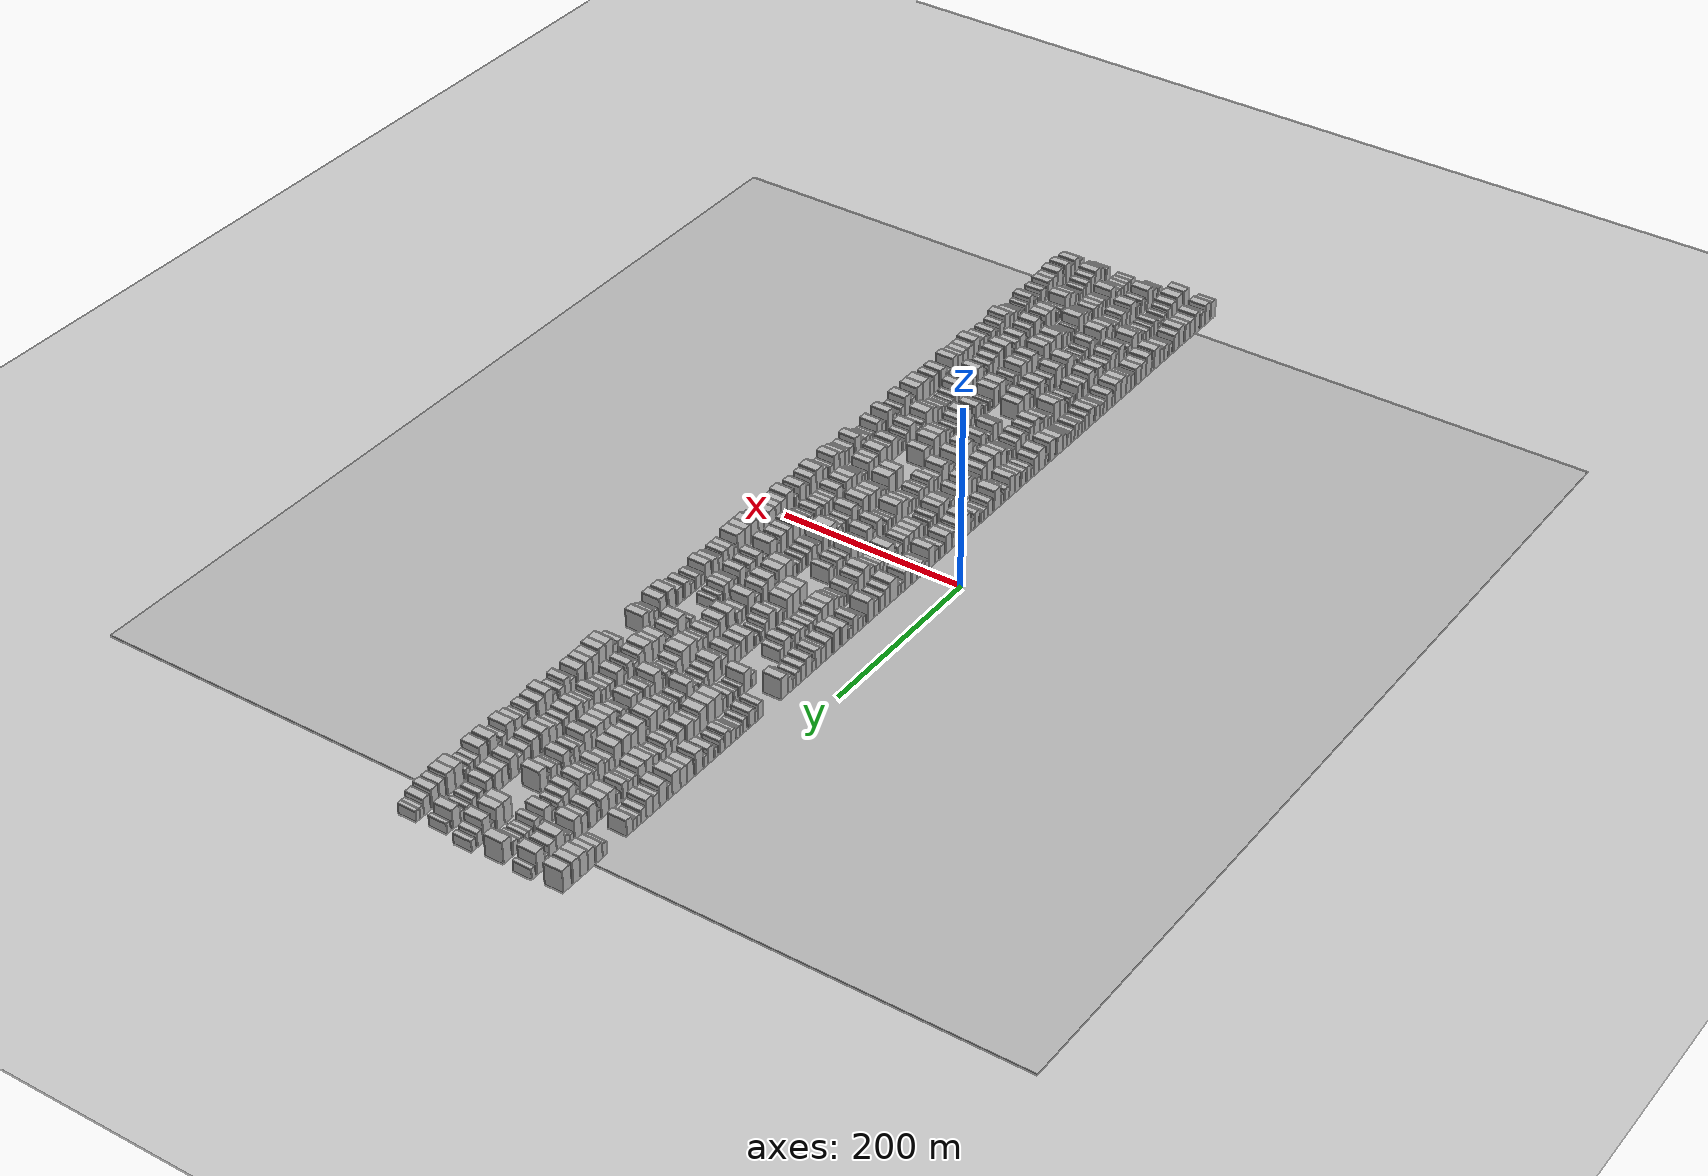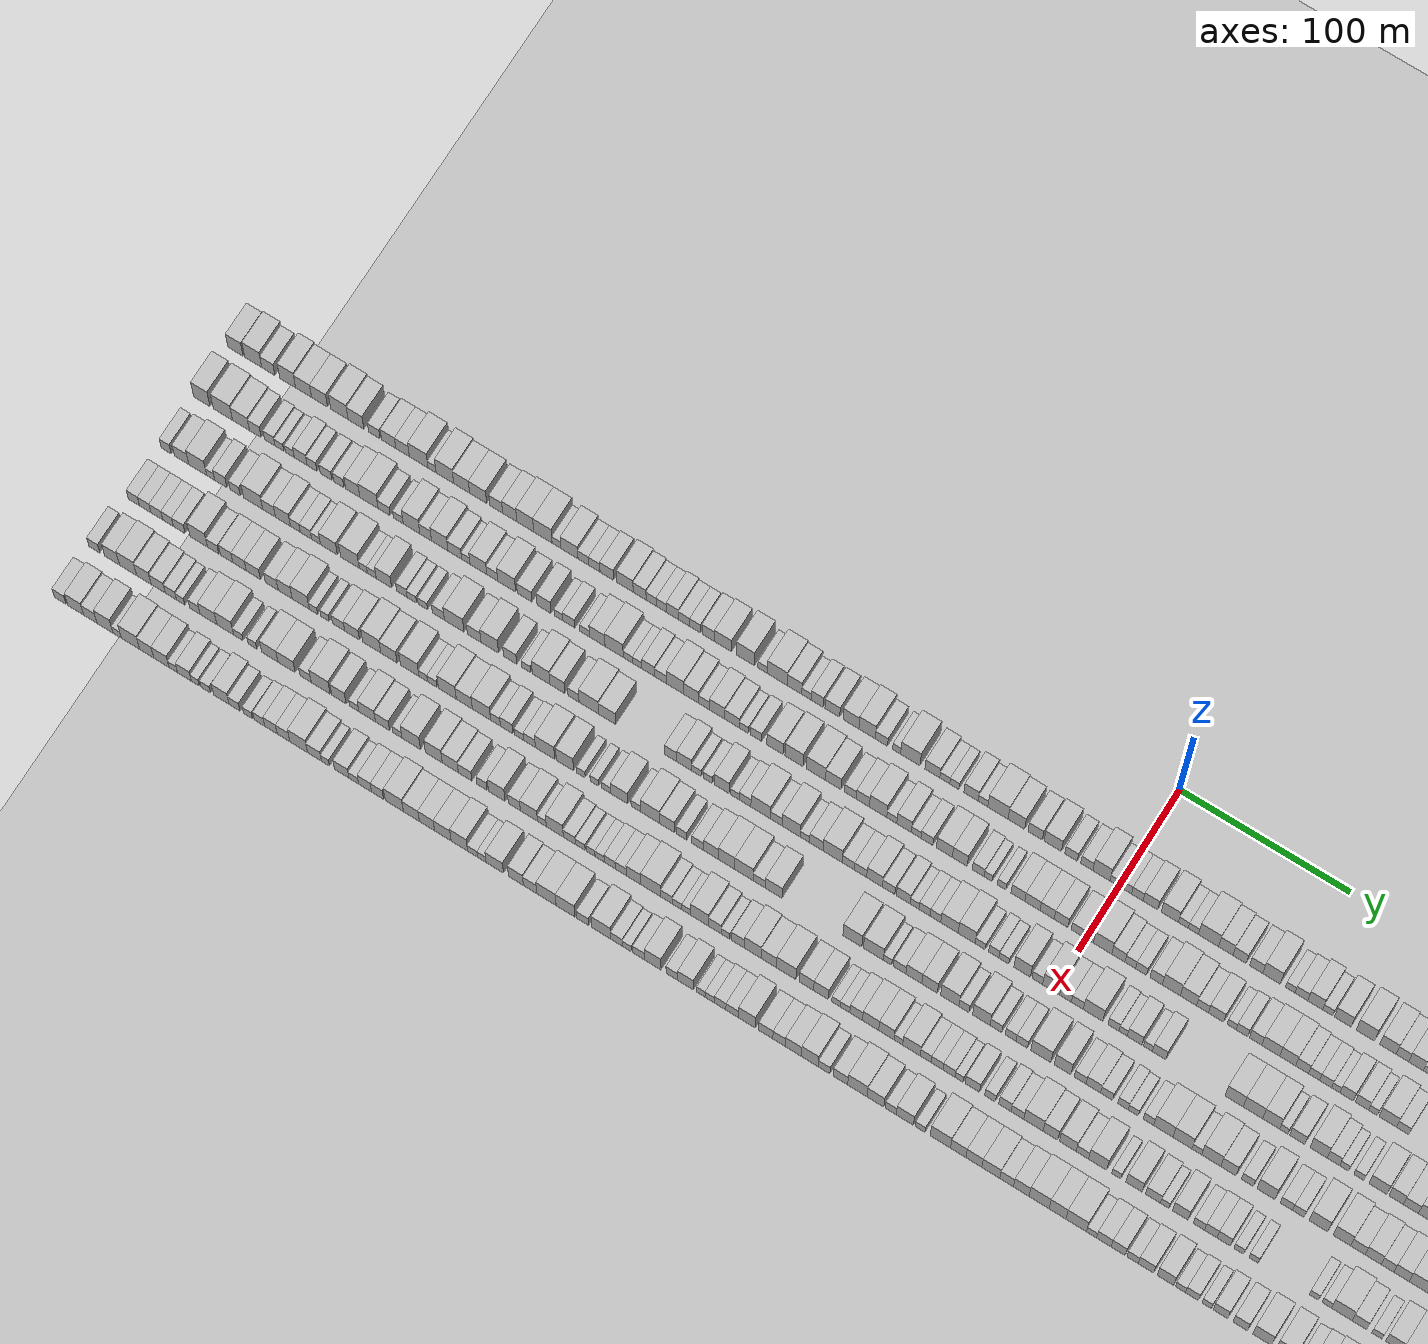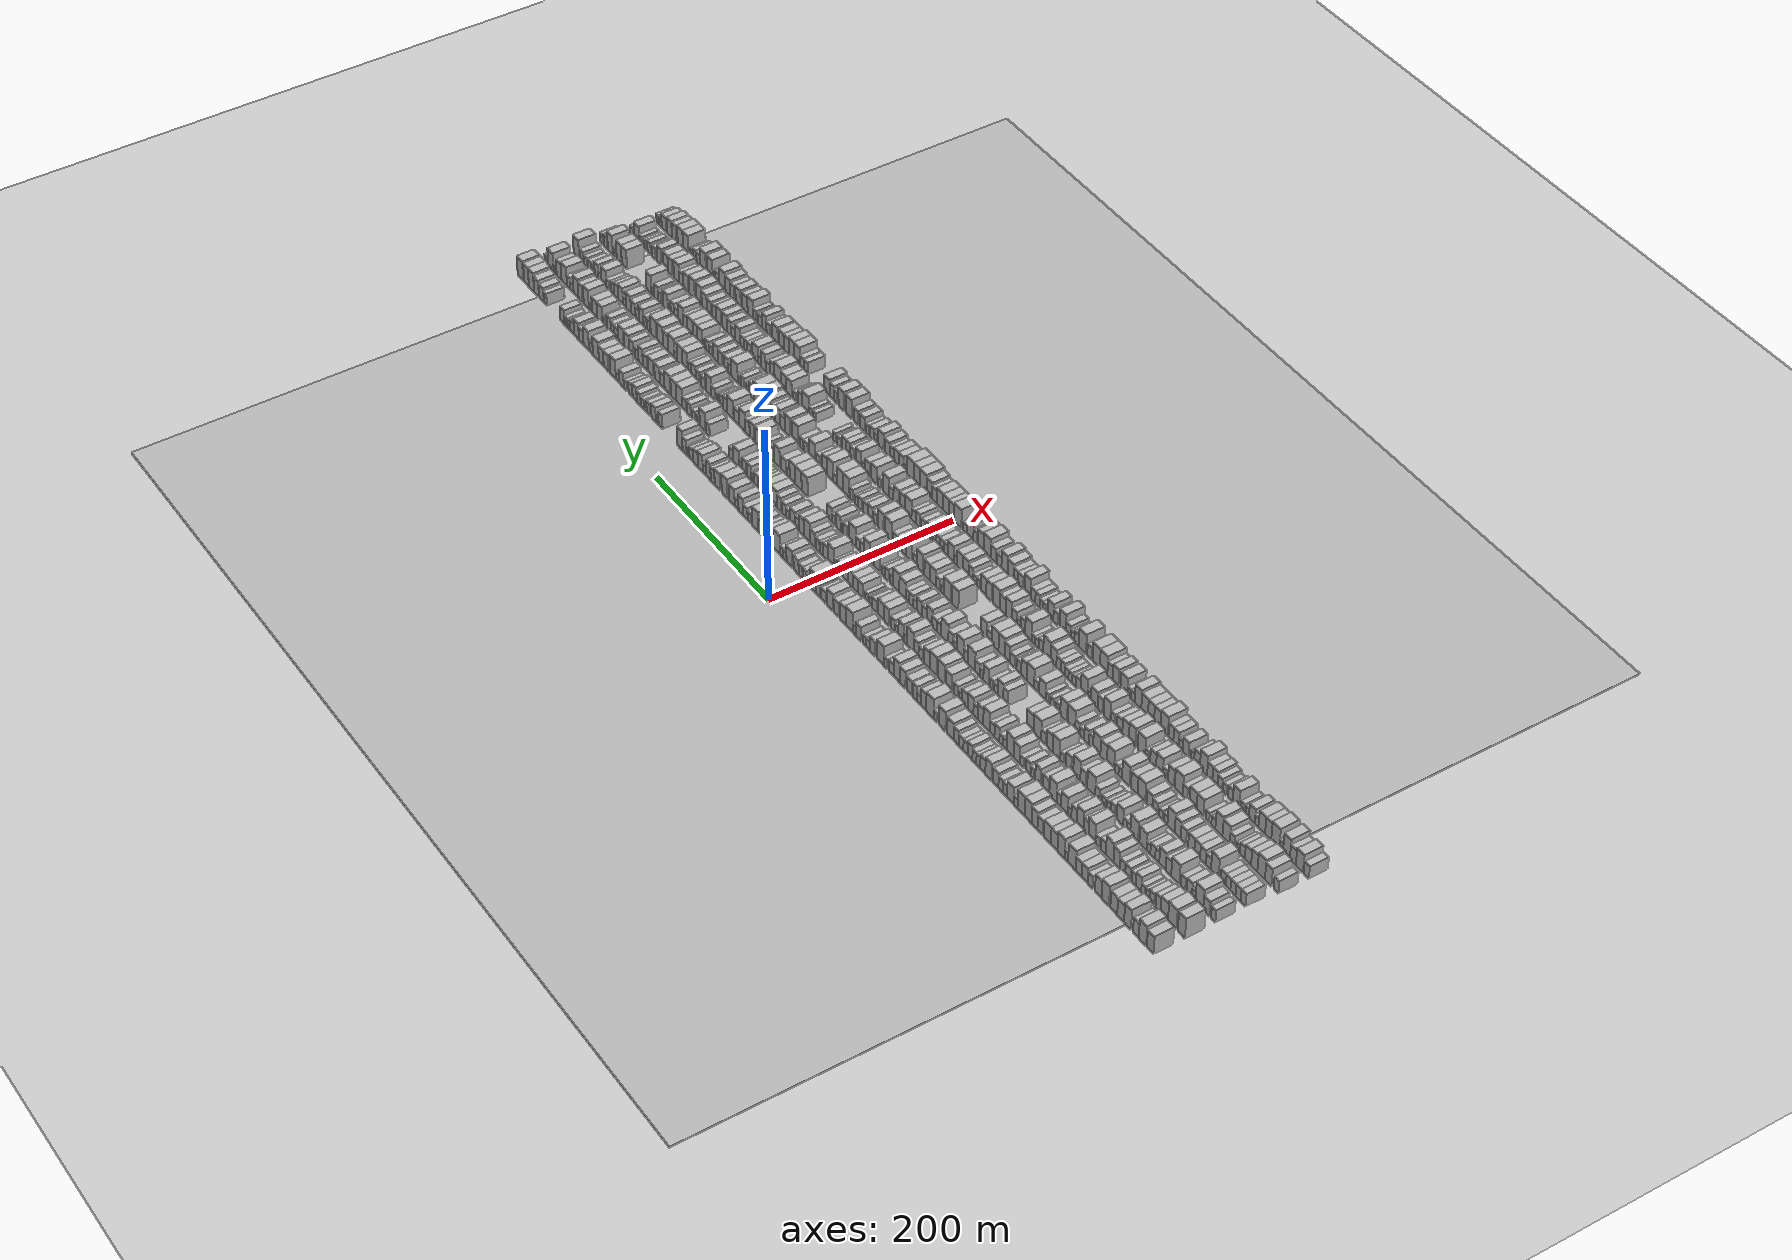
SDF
<?xml version="1.0" encoding="utf-8"?>

<sdf version="1.6">

   <world name="default">

      <gui fullscreen="0">

         <camera name="user_camera">

            <pose>-15 0 4.57585 0 0 0</pose>

            <view_controller>orbit</view_controller>

         </camera>

      </gui>

      <scene>

         <sky>

           <clouds>

             <speed>12</speed>

           </clouds>

         </sky>

         <ambient>0.4 0.4 0.4 1</ambient>

         <background>0.7 0.7 0.7 1</background>

         <shadows>1</shadows>

      </scene>

      <gravity>0 0 -9.8066</gravity>

      <magnetic_field>6e-06 2.3e-05 -4.2e-05</magnetic_field>

      <physics default="0" name="default_physics" type="ode">

         <ode>

            <solver>

               <type>quick</type>

               <iters>10</iters>

               <sor>1.0</sor>

               <use_dynamic_moi_rescaling>0</use_dynamic_moi_rescaling>

            </solver>

            <constraints>

               <cfm>0</cfm>

               <erp>0.2</erp>

               <contact_max_correcting_vel>100</contact_max_correcting_vel>

               <contact_surface_layer>0.001</contact_surface_layer>

            </constraints>

         </ode>

         <max_step_size>0.004</max_step_size>

         <real_time_factor>1</real_time_factor>

         <real_time_update_rate>250</real_time_update_rate>

      </physics>

      <light name="sun" type="directional">

         <cast_shadows>1</cast_shadows>

         <pose>0 0 10 0 0 0</pose>

         <diffuse>0.8 0.8 0.8 1</diffuse>

         <specular>0.2 0.2 0.2 1</specular>

         <attenuation>

            <range>1000</range>

            <constant>0.9</constant>

            <linear>0.01</linear>

            <quadratic>0.001</quadratic>

         </attenuation>

         <direction>-0.5 0.1 -0.9</direction>

      </light>

      <include>

         <name>ground_plane_1</name>

         <uri>model://HANNAS_ground_plane</uri>

         <pose>0 0 0  0 0 0</pose>

      </include>

      <include>

         <name>ground_plane_2</name>

         <uri>model://HANNAS_ground_plane</uri>

         <pose>100 0 0  0 0 0</pose>

      </include>

      <model name="building_1">

         <static>1</static>

         <pose frame="">50.0000 -534.2807 0 0.000000 0.000000 0.000000</pose>

         <link name="link">

            <pose frame="">0 0 10.50 0 0 0</pose>

            <collision name="collision">

               <geometry>

                  <box>

                     <size>20.0000 9.4386 21.0000</size>

                  </box>

               </geometry>

               <max_contacts>10</max_contacts>

               <surface>

                  <contact>

                     <ode/>

                  </contact>

                  <bounce/>

                  <friction>

                     <torsional>

                        <ode/>

                     </torsional>

                     <ode/>

                  </friction>

               </surface>

            </collision>

            <visual name="visual">

               <cast_shadows>0</cast_shadows>

               <geometry>

                  <box>

                     <size>20.0000 9.4386 21.0000</size>

                  </box>

               </geometry>

               <material>

                  <script>

                     <uri>model://HANNAS_wall/materials/scripts</uri>

                     <uri>model://HANNAS_wall/materials/textures</uri>

                     <name>vrc/HANNAS_wall</name>

                  </script>

               </material>

            </visual>

            <self_collide>0</self_collide>

            <enable_wind>0</enable_wind>

            <kinematic>0</kinematic>

         </link>

      </model>

      <model name="building_2">

         <static>1</static>

         <pose frame="">50.0000 -523.2993 0 0.000000 0.000000 0.000000</pose>

         <link name="link">

            <pose frame="">0 0 12.00 0 0 0</pose>

            <collision name="collision">

               <geometry>

                  <box>

                     <size>20.0000 10.5243 24.0000</size>

                  </box>

               </geometry>

               <max_contacts>10</max_contacts>

               <surface>

                  <contact>

                     <ode/>

                  </contact>

                  <bounce/>

                  <friction>

                     <torsional>

                        <ode/>

                     </torsional>

                     <ode/>

                  </friction>

               </surface>

            </collision>

            <visual name="visual">

               <cast_shadows>0</cast_shadows>

               <geometry>

                  <box>

                     <size>20.0000 10.5243 24.0000</size>

                  </box>

               </geometry>

               <material>

                  <script>

                     <uri>model://HANNAS_wall/materials/scripts</uri>

                     <uri>model://HANNAS_wall/materials/textures</uri>

                     <name>vrc/HANNAS_wall</name>

                  </script>

               </material>

            </visual>

            <self_collide>0</self_collide>

            <enable_wind>0</enable_wind>

            <kinematic>0</kinematic>

         </link>

      </model>

      <model name="building_3">

         <static>1</static>

         <pose frame="">50.0000 -513.9736 0 0.000000 0.000000 0.000000</pose>

         <link name="link">

            <pose frame="">0 0 9.00 0 0 0</pose>

            <collision name="collision">

               <geometry>

                  <box>

                     <size>20.0000 8.1271 18.0000</size>

                  </box>

               </geometry>

               <max_contacts>10</max_contacts>

               <surface>

                  <contact>

                     <ode/>

                  </contact>

                  <bounce/>

                  <friction>

                     <torsional>

                        <ode/>

                     </torsional>

                     <ode/>

                  </friction>

               </surface>

            </collision>

            <visual name="visual">

               <cast_shadows>0</cast_shadows>

               <geometry>

                  <box>

                     <size>20.0000 8.1271 18.0000</size>

                  </box>

               </geometry>

               <material>

                  <script>

                     <uri>model://HANNAS_wall/materials/scripts</uri>

                     <uri>model://HANNAS_wall/materials/textures</uri>

                     <name>vrc/HANNAS_wall</name>

                  </script>

               </material>

            </visual>

            <self_collide>0</self_collide>

            <enable_wind>0</enable_wind>

            <kinematic>0</kinematic>

         </link>

      </model>

      <model name="building_4">

         <static>1</static>

         <pose frame="">50.0000 -502.0239 0 0.000000 0.000000 0.000000</pose>

         <link name="link">

            <pose frame="">0 0 12.00 0 0 0</pose>

            <collision name="collision">

               <geometry>

                  <box>

                     <size>20.0000 9.7722 24.0000</size>

                  </box>

               </geometry>

               <max_contacts>10</max_contacts>

               <surface>

                  <contact>

                     <ode/>

                  </contact>

                  <bounce/>

                  <friction>

                     <torsional>

                        <ode/>

                     </torsional>

                     <ode/>

                  </friction>

               </surface>

            </collision>

            <visual name="visual">

               <cast_shadows>0</cast_shadows>

               <geometry>

                  <box>

                     <size>20.0000 9.7722 24.0000</size>

                  </box>

               </geometry>

               <material>

                  <script>

                     <uri>model://HANNAS_wall/materials/scripts</uri>

                     <uri>model://HANNAS_wall/materials/textures</uri>

                     <name>vrc/HANNAS_wall</name>

                  </script>

               </material>

            </visual>

            <self_collide>0</self_collide>

            <enable_wind>0</enable_wind>

            <kinematic>0</kinematic>

         </link>

      </model>

      <model name="building_5">

         <static>1</static>

         <pose frame="">50.0000 -492.1979 0 0.000000 0.000000 0.000000</pose>

         <link name="link">

            <pose frame="">0 0 10.50 0 0 0</pose>

            <collision name="collision">

               <geometry>

                  <box>

                     <size>20.0000 9.8797 21.0000</size>

                  </box>

               </geometry>

               <max_contacts>10</max_contacts>

               <surface>

                  <contact>

                     <ode/>

                  </contact>

                  <bounce/>

                  <friction>

                     <torsional>

                        <ode/>

                     </torsional>

                     <ode/>

                  </friction>

               </surface>

            </collision>

            <visual name="visual">

               <cast_shadows>0</cast_shadows>

               <geometry>

                  <box>

                     <size>20.0000 9.8797 21.0000</size>

                  </box>

               </geometry>

               <material>

                  <script>

                     <uri>model://HANNAS_wall/materials/scripts</uri>

                     <uri>model://HANNAS_wall/materials/textures</uri>

                     <name>vrc/HANNAS_wall</name>

                  </script>

               </material>

            </visual>

            <self_collide>0</self_collide>

            <enable_wind>0</enable_wind>

            <kinematic>0</kinematic>

         </link>

      </model>

      <model name="building_6">

         <static>1</static>

         <pose frame="">50.0000 -482.3527 0 0.000000 0.000000 0.000000</pose>

         <link name="link">

            <pose frame="">0 0 10.50 0 0 0</pose>

            <collision name="collision">

               <geometry>

                  <box>

                     <size>20.0000 9.8106 21.0000</size>

                  </box>

               </geometry>

               <max_contacts>10</max_contacts>

               <surface>

                  <contact>

                     <ode/>

                  </contact>

                  <bounce/>

                  <friction>

                     <torsional>

                        <ode/>

                     </torsional>

                     <ode/>

                  </friction>

               </surface>

            </collision>

            <visual name="visual">

               <cast_shadows>0</cast_shadows>

               <geometry>

                  <box>

                     <size>20.0000 9.8106 21.0000</size>

                  </box>

               </geometry>

               <material>

                  <script>

                     <uri>model://HANNAS_wall/materials/scripts</uri>

                     <uri>model://HANNAS_wall/materials/textures</uri>

                     <name>vrc/HANNAS_wall</name>

                  </script>

               </material>

            </visual>

            <self_collide>0</self_collide>

            <enable_wind>0</enable_wind>

            <kinematic>0</kinematic>

         </link>

      </model>

      <model name="building_7">

         <static>1</static>

         <pose frame="">50.0000 -470.0980 0 0.000000 0.000000 0.000000</pose>

         <link name="link">

            <pose frame="">0 0 12.00 0 0 0</pose>

            <collision name="collision">

               <geometry>

                  <box>

                     <size>20.0000 10.6988 24.0000</size>

                  </box>

               </geometry>

               <max_contacts>10</max_contacts>

               <surface>

                  <contact>

                     <ode/>

                  </contact>

                  <bounce/>

                  <friction>

                     <torsional>

                        <ode/>

                     </torsional>

                     <ode/>

                  </friction>

               </surface>

            </collision>

            <visual name="visual">

               <cast_shadows>0</cast_shadows>

               <geometry>

                  <box>

                     <size>20.0000 10.6988 24.0000</size>

                  </box>

               </geometry>

               <material>

                  <script>

                     <uri>model://HANNAS_wall/materials/scripts</uri>

                     <uri>model://HANNAS_wall/materials/textures</uri>

                     <name>vrc/HANNAS_wall</name>

                  </script>

               </material>

            </visual>

            <self_collide>0</self_collide>

            <enable_wind>0</enable_wind>

            <kinematic>0</kinematic>

         </link>

      </model>

      <model name="building_8">

         <static>1</static>

         <pose frame="">50.0000 -459.9563 0 0.000000 0.000000 0.000000</pose>

         <link name="link">

            <pose frame="">0 0 10.50 0 0 0</pose>

            <collision name="collision">

               <geometry>

                  <box>

                     <size>20.0000 9.5847 21.0000</size>

                  </box>

               </geometry>

               <max_contacts>10</max_contacts>

               <surface>

                  <contact>

                     <ode/>

                  </contact>

                  <bounce/>

                  <friction>

                     <torsional>

                        <ode/>

                     </torsional>

                     <ode/>

                  </friction>

               </surface>

            </collision>

            <visual name="visual">

               <cast_shadows>0</cast_shadows>

               <geometry>

                  <box>

                     <size>20.0000 9.5847 21.0000</size>

                  </box>

               </geometry>

               <material>

                  <script>

                     <uri>model://HANNAS_wall/materials/scripts</uri>

                     <uri>model://HANNAS_wall/materials/textures</uri>

                     <name>vrc/HANNAS_wall</name>

                  </script>

               </material>

            </visual>

            <self_collide>0</self_collide>

            <enable_wind>0</enable_wind>

            <kinematic>0</kinematic>

         </link>

      </model>

      <model name="building_9">

         <static>1</static>

         <pose frame="">50.0000 -448.6753 0 0.000000 0.000000 0.000000</pose>

         <link name="link">

            <pose frame="">0 0 7.50 0 0 0</pose>

            <collision name="collision">

               <geometry>

                  <box>

                     <size>20.0000 6.9773 15.0000</size>

                  </box>

               </geometry>

               <max_contacts>10</max_contacts>

               <surface>

                  <contact>

                     <ode/>

                  </contact>

                  <bounce/>

                  <friction>

                     <torsional>

                        <ode/>

                     </torsional>

                     <ode/>

                  </friction>

               </surface>

            </collision>

            <visual name="visual">

               <cast_shadows>0</cast_shadows>

               <geometry>

                  <box>

                     <size>20.0000 6.9773 15.0000</size>

                  </box>

               </geometry>

               <material>

                  <script>

                     <uri>model://HANNAS_wall/materials/scripts</uri>

                     <uri>model://HANNAS_wall/materials/textures</uri>

                     <name>vrc/HANNAS_wall</name>

                  </script>

               </material>

            </visual>

            <self_collide>0</self_collide>

            <enable_wind>0</enable_wind>

            <kinematic>0</kinematic>

         </link>

      </model>

      <model name="building_10">

         <static>1</static>

         <pose frame="">50.0000 -439.8536 0 0.000000 0.000000 0.000000</pose>

         <link name="link">

            <pose frame="">0 0 9.00 0 0 0</pose>

            <collision name="collision">

               <geometry>

                  <box>

                     <size>20.0000 8.6662 18.0000</size>

                  </box>

               </geometry>

               <max_contacts>10</max_contacts>

               <surface>

                  <contact>

                     <ode/>

                  </contact>

                  <bounce/>

                  <friction>

                     <torsional>

                        <ode/>

                     </torsional>

                     <ode/>

                  </friction>

               </surface>

            </collision>

            <visual name="visual">

               <cast_shadows>0</cast_shadows>

               <geometry>

                  <box>

                     <size>20.0000 8.6662 18.0000</size>

                  </box>

               </geometry>

               <material>

                  <script>

                     <uri>model://HANNAS_wall/materials/scripts</uri>

                     <uri>model://HANNAS_wall/materials/textures</uri>

                     <name>vrc/HANNAS_wall</name>

                  </script>

               </material>

            </visual>

            <self_collide>0</self_collide>

            <enable_wind>0</enable_wind>

            <kinematic>0</kinematic>

         </link>

      </model>

      <model name="building_11">

         <static>1</static>

         <pose frame="">50.0000 -431.3317 0 0.000000 0.000000 0.000000</pose>

         <link name="link">

            <pose frame="">0 0 9.00 0 0 0</pose>

            <collision name="collision">

               <geometry>

                  <box>

                     <size>20.0000 8.3776 18.0000</size>

                  </box>

               </geometry>

               <max_contacts>10</max_contacts>

               <surface>

                  <contact>

                     <ode/>

                  </contact>

                  <bounce/>

                  <friction>

                     <torsional>

                        <ode/>

                     </torsional>

                     <ode/>

                  </friction>

               </surface>

            </collision>

            <visual name="visual">

               <cast_shadows>0</cast_shadows>

               <geometry>

                  <box>

                     <size>20.0000 8.3776 18.0000</size>

                  </box>

               </geometry>

               <material>

                  <script>

                     <uri>model://HANNAS_wall/materials/scripts</uri>

                     <uri>model://HANNAS_wall/materials/textures</uri>

                     <name>vrc/HANNAS_wall</name>

                  </script>

               </material>

            </visual>

            <self_collide>0</self_collide>

            <enable_wind>0</enable_wind>

            <kinematic>0</kinematic>

         </link>

      </model>

      <model name="building_12">

         <static>1</static>

         <pose frame="">50.0000 -421.4305 0 0.000000 0.000000 0.000000</pose>

         <link name="link">

            <pose frame="">0 0 12.00 0 0 0</pose>

            <collision name="collision">

               <geometry>

                  <box>

                     <size>20.0000 11.4246 24.0000</size>

                  </box>

               </geometry>

               <max_contacts>10</max_contacts>

               <surface>

                  <contact>

                     <ode/>

                  </contact>

                  <bounce/>

                  <friction>

                     <torsional>

                        <ode/>

                     </torsional>

                     <ode/>

                  </friction>

               </surface>

            </collision>

            <visual name="visual">

               <cast_shadows>0</cast_shadows>

               <geometry>

                  <box>

                     <size>20.0000 11.4246 24.0000</size>

                  </box>

               </geometry>

               <material>

                  <script>

                     <uri>model://HANNAS_wall/materials/scripts</uri>

                     <uri>model://HANNAS_wall/materials/textures</uri>

                     <name>vrc/HANNAS_wall</name>

                  </script>

               </material>

            </visual>

            <self_collide>0</self_collide>

            <enable_wind>0</enable_wind>

            <kinematic>0</kinematic>

         </link>

      </model>

      <model name="building_13">

         <static>1</static>

         <pose frame="">50.0000 -413.2633 0 0.000000 0.000000 0.000000</pose>

         <link name="link">

            <pose frame="">0 0 6.00 0 0 0</pose>

            <collision name="collision">

               <geometry>

                  <box>

                     <size>20.0000 4.9098 12.0000</size>

                  </box>

               </geometry>

               <max_contacts>10</max_contacts>

               <surface>

                  <contact>

                     <ode/>

                  </contact>

                  <bounce/>

                  <friction>

                     <torsional>

                        <ode/>

                     </torsional>

                     <ode/>

                  </friction>

               </surface>

            </collision>

            <visual name="visual">

               <cast_shadows>0</cast_shadows>

               <geometry>

                  <box>

                     <size>20.0000 4.9098 12.0000</size>

                  </box>

               </geometry>

               <material>

                  <script>

                     <uri>model://HANNAS_wall/materials/scripts</uri>

                     <uri>model://HANNAS_wall/materials/textures</uri>

                     <name>vrc/HANNAS_wall</name>

                  </script>

               </material>

            </visual>

            <self_collide>0</self_collide>

            <enable_wind>0</enable_wind>

            <kinematic>0</kinematic>

         </link>

      </model>

      <model name="building_14">

         <static>1</static>

         <pose frame="">50.0000 -405.4306 0 0.000000 0.000000 0.000000</pose>

         <link name="link">

            <pose frame="">0 0 12.00 0 0 0</pose>

            <collision name="collision">

               <geometry>

                  <box>

                     <size>20.0000 10.7557 24.0000</size>

                  </box>

               </geometry>

               <max_contacts>10</max_contacts>

               <surface>

                  <contact>

                     <ode/>

                  </contact>

                  <bounce/>

                  <friction>

                     <torsional>

                        <ode/>

                     </torsional>

                     <ode/>

                  </friction>

               </surface>

            </collision>

            <visual name="visual">

               <cast_shadows>0</cast_shadows>

               <geometry>

                  <box>

                     <size>20.0000 10.7557 24.0000</size>

                  </box>

               </geometry>

               <material>

                  <script>

                     <uri>model://HANNAS_wall/materials/scripts</uri>

                     <uri>model://HANNAS_wall/materials/textures</uri>

                     <name>vrc/HANNAS_wall</name>

                  </script>

               </material>

            </visual>

            <self_collide>0</self_collide>

            <enable_wind>0</enable_wind>

            <kinematic>0</kinematic>

         </link>

      </model>

      <model name="building_15">

         <static>1</static>

         <pose frame="">50.0000 -395.1952 0 0.000000 0.000000 0.000000</pose>

         <link name="link">

            <pose frame="">0 0 10.50 0 0 0</pose>

            <collision name="collision">

               <geometry>

                  <box>

                     <size>20.0000 9.7150 21.0000</size>

                  </box>

               </geometry>

               <max_contacts>10</max_contacts>

               <surface>

                  <contact>

                     <ode/>

                  </contact>

                  <bounce/>

                  <friction>

                     <torsional>

                        <ode/>

                     </torsional>

                     <ode/>

                  </friction>

               </surface>

            </collision>

            <visual name="visual">

               <cast_shadows>0</cast_shadows>

               <geometry>

                  <box>

                     <size>20.0000 9.7150 21.0000</size>

                  </box>

               </geometry>

               <material>

                  <script>

                     <uri>model://HANNAS_wall/materials/scripts</uri>

                     <uri>model://HANNAS_wall/materials/textures</uri>

                     <name>vrc/HANNAS_wall</name>

                  </script>

               </material>

            </visual>

            <self_collide>0</self_collide>

            <enable_wind>0</enable_wind>

            <kinematic>0</kinematic>

         </link>

      </model>

      <model name="building_16">

         <static>1</static>

         <pose frame="">50.0000 -385.1190 0 0.000000 0.000000 0.000000</pose>

         <link name="link">

            <pose frame="">0 0 10.50 0 0 0</pose>

            <collision name="collision">

               <geometry>

                  <box>

                     <size>20.0000 10.4373 21.0000</size>

                  </box>

               </geometry>

               <max_contacts>10</max_contacts>

               <surface>

                  <contact>

                     <ode/>

                  </contact>

                  <bounce/>

                  <friction>

                     <torsional>

                        <ode/>

                     </torsional>

                     <ode/>

                  </friction>

               </surface>

            </collision>

            <visual name="visual">

               <cast_shadows>0</cast_shadows>

               <geometry>

                  <box>

                     <size>20.0000 10.4373 21.0000</size>

                  </box>

               </geometry>

               <material>

                  <script>

                     <uri>model://HANNAS_wall/materials/scripts</uri>

                     <uri>model://HANNAS_wall/materials/textures</uri>

                     <name>vrc/HANNAS_wall</name>

                  </script>

               </material>

            </visual>

            <self_collide>0</self_collide>

            <enable_wind>0</enable_wind>

            <kinematic>0</kinematic>

         </link>

      </model>

      <model name="building_17">

         <static>1</static>

         <pose frame="">50.0000 -374.0400 0 0.000000 0.000000 0.000000</pose>

         <link name="link">

            <pose frame="">0 0 9.00 0 0 0</pose>

            <collision name="collision">

               <geometry>

                  <box>

                     <size>20.0000 7.7208 18.0000</size>

                  </box>

               </geometry>

               <max_contacts>10</max_contacts>

               <surface>

                  <contact>

                     <ode/>

                  </contact>

                  <bounce/>

                  <friction>

                     <torsional>

                        <ode/>

                     </torsional>

                     <ode/>

                  </friction>

               </surface>

            </collision>

            <visual name="visual">

               <cast_shadows>0</cast_shadows>

               <geometry>

                  <box>

                     <size>20.0000 7.7208 18.0000</size>

                  </box>

               </geometry>

               <material>

                  <script>

                     <uri>model://HANNAS_wall/materials/scripts</uri>

                     <uri>model://HANNAS_wall/materials/textures</uri>

                     <name>vrc/HANNAS_wall</name>

                  </script>

               </material>

            </visual>

            <self_collide>0</self_collide>

            <enable_wind>0</enable_wind>

            <kinematic>0</kinematic>

         </link>

      </model>

      <model name="building_18">

         <static>1</static>

         <pose frame="">50.0000 -365.8259 0 0.000000 0.000000 0.000000</pose>

         <link name="link">

            <pose frame="">0 0 10.50 0 0 0</pose>

            <collision name="collision">

               <geometry>

                  <box>

                     <size>20.0000 8.7074 21.0000</size>

                  </box>

               </geometry>

               <max_contacts>10</max_contacts>

               <surface>

                  <contact>

                     <ode/>

                  </contact>

                  <bounce/>

                  <friction>

                     <torsional>

                        <ode/>

                     </torsional>

                     <ode/>

                  </friction>

               </surface>

            </collision>

            <visual name="visual">

               <cast_shadows>0</cast_shadows>

               <geometry>

                  <box>

                     <size>20.0000 8.7074 21.0000</size>

                  </box>

               </geometry>

               <material>

                  <script>

                     <uri>model://HANNAS_wall/materials/scripts</uri>

                     <uri>model://HANNAS_wall/materials/textures</uri>

                     <name>vrc/HANNAS_wall</name>

                  </script>

               </material>

            </visual>

            <self_collide>0</self_collide>

            <enable_wind>0</enable_wind>

            <kinematic>0</kinematic>

         </link>

      </model>

      <model name="building_19">

         <static>1</static>

         <pose frame="">50.0000 -356.3437 0 0.000000 0.000000 0.000000</pose>

         <link name="link">

            <pose frame="">0 0 12.00 0 0 0</pose>

            <collision name="collision">

               <geometry>

                  <box>

                     <size>20.0000 10.2568 24.0000</size>

                  </box>

               </geometry>

               <max_contacts>10</max_contacts>

               <surface>

                  <contact>

                     <ode/>

                  </contact>

                  <bounce/>

                  <friction>

                     <torsional>

                        <ode/>

                     </torsional>

                     <ode/>

                  </friction>

               </surface>

            </collision>

            <visual name="visual">

               <cast_shadows>0</cast_shadows>

               <geometry>

                  <box>

                     <size>20.0000 10.2568 24.0000</size>

                  </box>

               </geometry>

               <material>

                  <script>

                     <uri>model://HANNAS_wall/materials/scripts</uri>

                     <uri>model://HANNAS_wall/materials/textures</uri>

                     <name>vrc/HANNAS_wall</name>

                  </script>

               </material>

            </visual>

            <self_collide>0</self_collide>

            <enable_wind>0</enable_wind>

            <kinematic>0</kinematic>

         </link>

      </model>

      <model name="building_20">

         <static>1</static>

         <pose frame="">50.0000 -345.6177 0 0.000000 0.000000 0.000000</pose>

         <link name="link">

            <pose frame="">0 0 12.00 0 0 0</pose>

            <collision name="collision">

               <geometry>

                  <box>

                     <size>20.0000 11.1952 24.0000</size>

                  </box>

               </geometry>

               <max_contacts>10</max_contacts>

               <surface>

                  <contact>

                     <ode/>

                  </contact>

                  <bounce/>

                  <friction>

                     <torsional>

                        <ode/>

                     </torsional>

                     <ode/>

                  </friction>

               </surface>

            </collision>

            <visual name="visual">

               <cast_shadows>0</cast_shadows>

               <geometry>

                  <box>

                     <size>20.0000 11.1952 24.0000</size>

                  </box>

               </geometry>

               <material>

                  <script>

                     <uri>model://HANNAS_wall/materials/scripts</uri>

                     <uri>model://HANNAS_wall/materials/textures</uri>

                     <name>vrc/HANNAS_wall</name>

                  </script>

               </material>

            </visual>

            <self_collide>0</self_collide>

            <enable_wind>0</enable_wind>

            <kinematic>0</kinematic>

         </link>

      </model>

      <model name="building_21">

         <static>1</static>

         <pose frame="">50.0000 -337.3342 0 0.000000 0.000000 0.000000</pose>

         <link name="link">

            <pose frame="">0 0 6.00 0 0 0</pose>

            <collision name="collision">

               <geometry>

                  <box>

                     <size>20.0000 5.3718 12.0000</size>

                  </box>

               </geometry>

               <max_contacts>10</max_contacts>

               <surface>

                  <contact>

                     <ode/>

                  </contact>

                  <bounce/>

                  <friction>

                     <torsional>

                        <ode/>

                     </torsional>

                     <ode/>

                  </friction>

               </surface>

            </collision>

            <visual name="visual">

               <cast_shadows>0</cast_shadows>

               <geometry>

                  <box>

                     <size>20.0000 5.3718 12.0000</size>

                  </box>

               </geometry>

               <material>

                  <script>

                     <uri>model://HANNAS_wall/materials/scripts</uri>

                     <uri>model://HANNAS_wall/materials/textures</uri>

                     <name>vrc/HANNAS_wall</name>

                  </script>

               </material>

            </visual>

            <self_collide>0</self_collide>

            <enable_wind>0</enable_wind>

            <kinematic>0</kinematic>

         </link>

      </model>

      <model name="building_22">

         <static>1</static>

         <pose frame="">50.0000 -329.4277 0 0.000000 0.000000 0.000000</pose>

         <link name="link">

            <pose frame="">0 0 10.50 0 0 0</pose>

            <collision name="collision">

               <geometry>

                  <box>

                     <size>20.0000 10.4413 21.0000</size>

                  </box>

               </geometry>

               <max_contacts>10</max_contacts>

               <surface>

                  <contact>

                     <ode/>

                  </contact>

                  <bounce/>

                  <friction>

                     <torsional>

                        <ode/>

                     </torsional>

                     <ode/>

                  </friction>

               </surface>

            </collision>

            <visual name="visual">

               <cast_shadows>0</cast_shadows>

               <geometry>

                  <box>

                     <size>20.0000 10.4413 21.0000</size>

                  </box>

               </geometry>

               <material>

                  <script>

                     <uri>model://HANNAS_wall/materials/scripts</uri>

                     <uri>model://HANNAS_wall/materials/textures</uri>

                     <name>vrc/HANNAS_wall</name>

                  </script>

               </material>

            </visual>

            <self_collide>0</self_collide>

            <enable_wind>0</enable_wind>

            <kinematic>0</kinematic>

         </link>

      </model>

      <model name="building_23">

         <static>1</static>

         <pose frame="">50.0000 -320.9701 0 0.000000 0.000000 0.000000</pose>

         <link name="link">

            <pose frame="">0 0 7.50 0 0 0</pose>

            <collision name="collision">

               <geometry>

                  <box>

                     <size>20.0000 6.4739 15.0000</size>

                  </box>

               </geometry>

               <max_contacts>10</max_contacts>

               <surface>

                  <contact>

                     <ode/>

                  </contact>

                  <bounce/>

                  <friction>

                     <torsional>

                        <ode/>

                     </torsional>

                     <ode/>

                  </friction>

               </surface>

            </collision>

            <visual name="visual">

               <cast_shadows>0</cast_shadows>

               <geometry>

                  <box>

                     <size>20.0000 6.4739 15.0000</size>

                  </box>

               </geometry>

               <material>

                  <script>

                     <uri>model://HANNAS_wall/materials/scripts</uri>

                     <uri>model://HANNAS_wall/materials/textures</uri>

                     <name>vrc/HANNAS_wall</name>

                  </script>

               </material>

            </visual>

            <self_collide>0</self_collide>

            <enable_wind>0</enable_wind>

            <kinematic>0</kinematic>

         </link>

      </model>

      <model name="building_24">

         <static>1</static>

         <pose frame="">50.0000 -314.2927 0 0.000000 0.000000 0.000000</pose>

         <link name="link">

            <pose frame="">0 0 7.50 0 0 0</pose>

            <collision name="collision">

               <geometry>

                  <box>

                     <size>20.0000 6.8808 15.0000</size>

                  </box>

               </geometry>

               <max_contacts>10</max_contacts>

               <surface>

                  <contact>

                     <ode/>

                  </contact>

                  <bounce/>

                  <friction>

                     <torsional>

                        <ode/>

                     </torsional>

                     <ode/>

                  </friction>

               </surface>

            </collision>

            <visual name="visual">

               <cast_shadows>0</cast_shadows>

               <geometry>

                  <box>

                     <size>20.0000 6.8808 15.0000</size>

                  </box>

               </geometry>

               <material>

                  <script>

                     <uri>model://HANNAS_wall/materials/scripts</uri>

                     <uri>model://HANNAS_wall/materials/textures</uri>

                     <name>vrc/HANNAS_wall</name>

                  </script>

               </material>

            </visual>

            <self_collide>0</self_collide>

            <enable_wind>0</enable_wind>

            <kinematic>0</kinematic>

         </link>

      </model>

      <model name="building_25">

         <static>1</static>

         <pose frame="">50.0000 -306.7463 0 0.000000 0.000000 0.000000</pose>

         <link name="link">

            <pose frame="">0 0 9.00 0 0 0</pose>

            <collision name="collision">

               <geometry>

                  <box>

                     <size>20.0000 8.2120 18.0000</size>

                  </box>

               </geometry>

               <max_contacts>10</max_contacts>

               <surface>

                  <contact>

                     <ode/>

                  </contact>

                  <bounce/>

                  <friction>

                     <torsional>

                        <ode/>

                     </torsional>

                     <ode/>

                  </friction>

               </surface>

            </collision>

            <visual name="visual">

               <cast_shadows>0</cast_shadows>

               <geometry>

                  <box>

                     <size>20.0000 8.2120 18.0000</size>

                  </box>

               </geometry>

               <material>

                  <script>

                     <uri>model://HANNAS_wall/materials/scripts</uri>

                     <uri>model://HANNAS_wall/materials/textures</uri>

                     <name>vrc/HANNAS_wall</name>

                  </script>

               </material>

            </visual>

            <self_collide>0</self_collide>

            <enable_wind>0</enable_wind>

            <kinematic>0</kinematic>

         </link>

      </model>

      <model name="building_26">

         <static>1</static>

         <pose frame="">50.0000 -295.7055 0 0.000000 0.000000 0.000000</pose>

         <link name="link">

            <pose frame="">0 0 10.50 0 0 0</pose>

            <collision name="collision">

               <geometry>

                  <box>

                     <size>20.0000 9.8696 21.0000</size>

                  </box>

               </geometry>

               <max_contacts>10</max_contacts>

               <surface>

                  <contact>

                     <ode/>

                  </contact>

                  <bounce/>

                  <friction>

                     <torsional>

                        <ode/>

                     </torsional>

                     <ode/>

                  </friction>

               </surface>

            </collision>

            <visual name="visual">

               <cast_shadows>0</cast_shadows>

               <geometry>

                  <box>

                     <size>20.0000 9.8696 21.0000</size>

                  </box>

               </geometry>

               <material>

                  <script>

                     <uri>model://HANNAS_wall/materials/scripts</uri>

                     <uri>model://HANNAS_wall/materials/textures</uri>

                     <name>vrc/HANNAS_wall</name>

                  </script>

               </material>

            </visual>

            <self_collide>0</self_collide>

            <enable_wind>0</enable_wind>

            <kinematic>0</kinematic>

         </link>

      </model>

      <model name="building_27">

         <static>1</static>

         <pose frame="">50.0000 -286.8508 0 0.000000 0.000000 0.000000</pose>

         <link name="link">

            <pose frame="">0 0 9.00 0 0 0</pose>

            <collision name="collision">

               <geometry>

                  <box>

                     <size>20.0000 7.8398 18.0000</size>

                  </box>

               </geometry>

               <max_contacts>10</max_contacts>

               <surface>

                  <contact>

                     <ode/>

                  </contact>

                  <bounce/>

                  <friction>

                     <torsional>

                        <ode/>

                     </torsional>

                     <ode/>

                  </friction>

               </surface>

            </collision>

            <visual name="visual">

               <cast_shadows>0</cast_shadows>

               <geometry>

                  <box>

                     <size>20.0000 7.8398 18.0000</size>

                  </box>

               </geometry>

               <material>

                  <script>

                     <uri>model://HANNAS_wall/materials/scripts</uri>

                     <uri>model://HANNAS_wall/materials/textures</uri>

                     <name>vrc/HANNAS_wall</name>

                  </script>

               </material>

            </visual>

            <self_collide>0</self_collide>

            <enable_wind>0</enable_wind>

            <kinematic>0</kinematic>

         </link>

      </model>

      <model name="building_28">

         <static>1</static>

         <pose frame="">50.0000 -279.8748 0 0.000000 0.000000 0.000000</pose>

         <link name="link">

            <pose frame="">0 0 7.50 0 0 0</pose>

            <collision name="collision">

               <geometry>

                  <box>

                     <size>20.0000 6.1122 15.0000</size>

                  </box>

               </geometry>

               <max_contacts>10</max_contacts>

               <surface>

                  <contact>

                     <ode/>

                  </contact>

                  <bounce/>

                  <friction>

                     <torsional>

                        <ode/>

                     </torsional>

                     <ode/>

                  </friction>

               </surface>

            </collision>

            <visual name="visual">

               <cast_shadows>0</cast_shadows>

               <geometry>

                  <box>

                     <size>20.0000 6.1122 15.0000</size>

                  </box>

               </geometry>

               <material>

                  <script>

                     <uri>model://HANNAS_wall/materials/scripts</uri>

                     <uri>model://HANNAS_wall/materials/textures</uri>

                     <name>vrc/HANNAS_wall</name>

                  </script>

               </material>

            </visual>

            <self_collide>0</self_collide>

            <enable_wind>0</enable_wind>

            <kinematic>0</kinematic>

         </link>

      </model>

      <model name="building_29">

         <static>1</static>

         <pose frame="">50.0000 -273.7574 0 0.000000 0.000000 0.000000</pose>

         <link name="link">

            <pose frame="">0 0 7.50 0 0 0</pose>

            <collision name="collision">

               <geometry>

                  <box>

                     <size>20.0000 6.1226 15.0000</size>

                  </box>

               </geometry>

               <max_contacts>10</max_contacts>

               <surface>

                  <contact>

                     <ode/>

                  </contact>

                  <bounce/>

                  <friction>

                     <torsional>

                        <ode/>

                     </torsional>

                     <ode/>

                  </friction>

               </surface>

            </collision>

            <visual name="visual">

               <cast_shadows>0</cast_shadows>

               <geometry>

                  <box>

                     <size>20.0000 6.1226 15.0000</size>

                  </box>

               </geometry>

               <material>

                  <script>

                     <uri>model://HANNAS_wall/materials/scripts</uri>

                     <uri>model://HANNAS_wall/materials/textures</uri>

                     <name>vrc/HANNAS_wall</name>

                  </script>

               </material>

            </visual>

            <self_collide>0</self_collide>

            <enable_wind>0</enable_wind>

            <kinematic>0</kinematic>

         </link>

      </model>

      <model name="building_30">

         <static>1</static>

         <pose frame="">50.0000 -267.0461 0 0.000000 0.000000 0.000000</pose>

         <link name="link">

            <pose frame="">0 0 9.00 0 0 0</pose>

            <collision name="collision">

               <geometry>

                  <box>

                     <size>20.0000 7.3000 18.0000</size>

                  </box>

               </geometry>

               <max_contacts>10</max_contacts>

               <surface>

                  <contact>

                     <ode/>

                  </contact>

                  <bounce/>

                  <friction>

                     <torsional>

                        <ode/>

                     </torsional>

                     <ode/>

                  </friction>

               </surface>

            </collision>

            <visual name="visual">

               <cast_shadows>0</cast_shadows>

               <geometry>

                  <box>

                     <size>20.0000 7.3000 18.0000</size>

                  </box>

               </geometry>

               <material>

                  <script>

                     <uri>model://HANNAS_wall/materials/scripts</uri>

                     <uri>model://HANNAS_wall/materials/textures</uri>

                     <name>vrc/HANNAS_wall</name>

                  </script>

               </material>

            </visual>

            <self_collide>0</self_collide>

            <enable_wind>0</enable_wind>

            <kinematic>0</kinematic>

         </link>

      </model>

      <model name="building_31">

         <static>1</static>

         <pose frame="">50.0000 -259.9950 0 0.000000 0.000000 0.000000</pose>

         <link name="link">

            <pose frame="">0 0 7.50 0 0 0</pose>

            <collision name="collision">

               <geometry>

                  <box>

                     <size>20.0000 6.8023 15.0000</size>

                  </box>

               </geometry>

               <max_contacts>10</max_contacts>

               <surface>

                  <contact>

                     <ode/>

                  </contact>

                  <bounce/>

                  <friction>

                     <torsional>

                        <ode/>

                     </torsional>

                     <ode/>

                  </friction>

               </surface>

            </collision>

            <visual name="visual">

               <cast_shadows>0</cast_shadows>

               <geometry>

                  <box>

                     <size>20.0000 6.8023 15.0000</size>

                  </box>

               </geometry>

               <material>

                  <script>

                     <uri>model://HANNAS_wall/materials/scripts</uri>

                     <uri>model://HANNAS_wall/materials/textures</uri>

                     <name>vrc/HANNAS_wall</name>

                  </script>

               </material>

            </visual>

            <self_collide>0</self_collide>

            <enable_wind>0</enable_wind>

            <kinematic>0</kinematic>

         </link>

      </model>

      <model name="building_32">

         <static>1</static>

         <pose frame="">50.0000 -253.3541 0 0.000000 0.000000 0.000000</pose>

         <link name="link">

            <pose frame="">0 0 7.50 0 0 0</pose>

            <collision name="collision">

               <geometry>

                  <box>

                     <size>20.0000 6.4795 15.0000</size>

                  </box>

               </geometry>

               <max_contacts>10</max_contacts>

               <surface>

                  <contact>

                     <ode/>

                  </contact>

                  <bounce/>

                  <friction>

                     <torsional>

                        <ode/>

                     </torsional>

                     <ode/>

                  </friction>

               </surface>

            </collision>

            <visual name="visual">

               <cast_shadows>0</cast_shadows>

               <geometry>

                  <box>

                     <size>20.0000 6.4795 15.0000</size>

                  </box>

               </geometry>

               <material>

                  <script>

                     <uri>model://HANNAS_wall/materials/scripts</uri>

                     <uri>model://HANNAS_wall/materials/textures</uri>

                     <name>vrc/HANNAS_wall</name>

                  </script>

               </material>

            </visual>

            <self_collide>0</self_collide>

            <enable_wind>0</enable_wind>

            <kinematic>0</kinematic>

         </link>

      </model>

      <model name="building_33">

         <static>1</static>

         <pose frame="">50.0000 -245.3383 0 0.000000 0.000000 0.000000</pose>

         <link name="link">

            <pose frame="">0 0 9.00 0 0 0</pose>

            <collision name="collision">

               <geometry>

                  <box>

                     <size>20.0000 7.5522 18.0000</size>

                  </box>

               </geometry>

               <max_contacts>10</max_contacts>

               <surface>

                  <contact>

                     <ode/>

                  </contact>

                  <bounce/>

                  <friction>

                     <torsional>

                        <ode/>

                     </torsional>

                     <ode/>

                  </friction>

               </surface>

            </collision>

            <visual name="visual">

               <cast_shadows>0</cast_shadows>

               <geometry>

                  <box>

                     <size>20.0000 7.5522 18.0000</size>

                  </box>

               </geometry>

               <material>

                  <script>

                     <uri>model://HANNAS_wall/materials/scripts</uri>

                     <uri>model://HANNAS_wall/materials/textures</uri>

                     <name>vrc/HANNAS_wall</name>

                  </script>

               </material>

            </visual>

            <self_collide>0</self_collide>

            <enable_wind>0</enable_wind>

            <kinematic>0</kinematic>

         </link>

      </model>

      <model name="building_34">

         <static>1</static>

         <pose frame="">50.0000 -236.4442 0 0.000000 0.000000 0.000000</pose>

         <link name="link">

            <pose frame="">0 0 10.50 0 0 0</pose>

            <collision name="collision">

               <geometry>

                  <box>

                     <size>20.0000 10.2360 21.0000</size>

                  </box>

               </geometry>

               <max_contacts>10</max_contacts>

               <surface>

                  <contact>

                     <ode/>

                  </contact>

                  <bounce/>

                  <friction>

                     <torsional>

                        <ode/>

                     </torsional>

                     <ode/>

                  </friction>

               </surface>

            </collision>

            <visual name="visual">

               <cast_shadows>0</cast_shadows>

               <geometry>

                  <box>

                     <size>20.0000 10.2360 21.0000</size>

                  </box>

               </geometry>

               <material>

                  <script>

                     <uri>model://HANNAS_wall/materials/scripts</uri>

                     <uri>model://HANNAS_wall/materials/textures</uri>

                     <name>vrc/HANNAS_wall</name>

                  </script>

               </material>

            </visual>

            <self_collide>0</self_collide>

            <enable_wind>0</enable_wind>

            <kinematic>0</kinematic>

         </link>

      </model>

      <model name="building_35">

         <static>1</static>

         <pose frame="">50.0000 -222.9029 0 0.000000 0.000000 0.000000</pose>

         <link name="link">

            <pose frame="">0 0 12.00 0 0 0</pose>

            <collision name="collision">

               <geometry>

                  <box>

                     <size>20.0000 10.8468 24.0000</size>

                  </box>

               </geometry>

               <max_contacts>10</max_contacts>

               <surface>

                  <contact>

                     <ode/>

                  </contact>

                  <bounce/>

                  <friction>

                     <torsional>

                        <ode/>

                     </torsional>

                     <ode/>

                  </friction>

               </surface>

            </collision>

            <visual name="visual">

               <cast_shadows>0</cast_shadows>

               <geometry>

                  <box>

                     <size>20.0000 10.8468 24.0000</size>

                  </box>

               </geometry>

               <material>

                  <script>

                     <uri>model://HANNAS_wall/materials/scripts</uri>

                     <uri>model://HANNAS_wall/materials/textures</uri>

                     <name>vrc/HANNAS_wall</name>

                  </script>

               </material>

            </visual>

            <self_collide>0</self_collide>

            <enable_wind>0</enable_wind>

            <kinematic>0</kinematic>

         </link>

      </model>

      <model name="building_36">

         <static>1</static>

         <pose frame="">50.0000 -212.6244 0 0.000000 0.000000 0.000000</pose>

         <link name="link">

            <pose frame="">0 0 6.00 0 0 0</pose>

            <collision name="collision">

               <geometry>

                  <box>

                     <size>20.0000 5.7102 12.0000</size>

                  </box>

               </geometry>

               <max_contacts>10</max_contacts>

               <surface>

                  <contact>

                     <ode/>

                  </contact>

                  <bounce/>

                  <friction>

                     <torsional>

                        <ode/>

                     </torsional>

                     <ode/>

                  </friction>

               </surface>

            </collision>

            <visual name="visual">

               <cast_shadows>0</cast_shadows>

               <geometry>

                  <box>

                     <size>20.0000 5.7102 12.0000</size>

                  </box>

               </geometry>

               <material>

                  <script>

                     <uri>model://HANNAS_wall/materials/scripts</uri>

                     <uri>model://HANNAS_wall/materials/textures</uri>

                     <name>vrc/HANNAS_wall</name>

                  </script>

               </material>

            </visual>

            <self_collide>0</self_collide>

            <enable_wind>0</enable_wind>

            <kinematic>0</kinematic>

         </link>

      </model>

      <model name="building_37">

         <static>1</static>

         <pose frame="">50.0000 -203.8421 0 0.000000 0.000000 0.000000</pose>

         <link name="link">

            <pose frame="">0 0 12.00 0 0 0</pose>

            <collision name="collision">

               <geometry>

                  <box>

                     <size>20.0000 11.8542 24.0000</size>

                  </box>

               </geometry>

               <max_contacts>10</max_contacts>

               <surface>

                  <contact>

                     <ode/>

                  </contact>

                  <bounce/>

                  <friction>

                     <torsional>

                        <ode/>

                     </torsional>

                     <ode/>

                  </friction>

               </surface>

            </collision>

            <visual name="visual">

               <cast_shadows>0</cast_shadows>

               <geometry>

                  <box>

                     <size>20.0000 11.8542 24.0000</size>

                  </box>

               </geometry>

               <material>

                  <script>

                     <uri>model://HANNAS_wall/materials/scripts</uri>

                     <uri>model://HANNAS_wall/materials/textures</uri>

                     <name>vrc/HANNAS_wall</name>

                  </script>

               </material>

            </visual>

            <self_collide>0</self_collide>

            <enable_wind>0</enable_wind>

            <kinematic>0</kinematic>

         </link>

      </model>

      <model name="building_38">

         <static>1</static>

         <pose frame="">50.0000 -193.5161 0 0.000000 0.000000 0.000000</pose>

         <link name="link">

            <pose frame="">0 0 10.50 0 0 0</pose>

            <collision name="collision">

               <geometry>

                  <box>

                     <size>20.0000 8.7978 21.0000</size>

                  </box>

               </geometry>

               <max_contacts>10</max_contacts>

               <surface>

                  <contact>

                     <ode/>

                  </contact>

                  <bounce/>

                  <friction>

                     <torsional>

                        <ode/>

                     </torsional>

                     <ode/>

                  </friction>

               </surface>

            </collision>

            <visual name="visual">

               <cast_shadows>0</cast_shadows>

               <geometry>

                  <box>

                     <size>20.0000 8.7978 21.0000</size>

                  </box>

               </geometry>

               <material>

                  <script>

                     <uri>model://HANNAS_wall/materials/scripts</uri>

                     <uri>model://HANNAS_wall/materials/textures</uri>

                     <name>vrc/HANNAS_wall</name>

                  </script>

               </material>

            </visual>

            <self_collide>0</self_collide>

            <enable_wind>0</enable_wind>

            <kinematic>0</kinematic>

         </link>

      </model>

      <model name="building_39">

         <static>1</static>

         <pose frame="">50.0000 -186.3156 0 0.000000 0.000000 0.000000</pose>

         <link name="link">

            <pose frame="">0 0 6.00 0 0 0</pose>

            <collision name="collision">

               <geometry>

                  <box>

                     <size>20.0000 5.6032 12.0000</size>

                  </box>

               </geometry>

               <max_contacts>10</max_contacts>

               <surface>

                  <contact>

                     <ode/>

                  </contact>

                  <bounce/>

                  <friction>

                     <torsional>

                        <ode/>

                     </torsional>

                     <ode/>

                  </friction>

               </surface>

            </collision>

            <visual name="visual">

               <cast_shadows>0</cast_shadows>

               <geometry>

                  <box>

                     <size>20.0000 5.6032 12.0000</size>

                  </box>

               </geometry>

               <material>

                  <script>

                     <uri>model://HANNAS_wall/materials/scripts</uri>

                     <uri>model://HANNAS_wall/materials/textures</uri>

                     <name>vrc/HANNAS_wall</name>

                  </script>

               </material>

            </visual>

            <self_collide>0</self_collide>

            <enable_wind>0</enable_wind>

            <kinematic>0</kinematic>

         </link>

      </model>

      <model name="building_40">

         <static>1</static>

         <pose frame="">50.0000 -179.8365 0 0.000000 0.000000 0.000000</pose>

         <link name="link">

            <pose frame="">0 0 9.00 0 0 0</pose>

            <collision name="collision">

               <geometry>

                  <box>

                     <size>20.0000 7.3552 18.0000</size>

                  </box>

               </geometry>

               <max_contacts>10</max_contacts>

               <surface>

                  <contact>

                     <ode/>

                  </contact>

                  <bounce/>

                  <friction>

                     <torsional>

                        <ode/>

                     </torsional>

                     <ode/>

                  </friction>

               </surface>

            </collision>

            <visual name="visual">

               <cast_shadows>0</cast_shadows>

               <geometry>

                  <box>

                     <size>20.0000 7.3552 18.0000</size>

                  </box>

               </geometry>

               <material>

                  <script>

                     <uri>model://HANNAS_wall/materials/scripts</uri>

                     <uri>model://HANNAS_wall/materials/textures</uri>

                     <name>vrc/HANNAS_wall</name>

                  </script>

               </material>

            </visual>

            <self_collide>0</self_collide>

            <enable_wind>0</enable_wind>

            <kinematic>0</kinematic>

         </link>

      </model>

      <model name="building_41">

         <static>1</static>

         <pose frame="">50.0000 -170.7473 0 0.000000 0.000000 0.000000</pose>

         <link name="link">

            <pose frame="">0 0 9.00 0 0 0</pose>

            <collision name="collision">

               <geometry>

                  <box>

                     <size>20.0000 8.8231 18.0000</size>

                  </box>

               </geometry>

               <max_contacts>10</max_contacts>

               <surface>

                  <contact>

                     <ode/>

                  </contact>

                  <bounce/>

                  <friction>

                     <torsional>

                        <ode/>

                     </torsional>

                     <ode/>

                  </friction>

               </surface>

            </collision>

            <visual name="visual">

               <cast_shadows>0</cast_shadows>

               <geometry>

                  <box>

                     <size>20.0000 8.8231 18.0000</size>

                  </box>

               </geometry>

               <material>

                  <script>

                     <uri>model://HANNAS_wall/materials/scripts</uri>

                     <uri>model://HANNAS_wall/materials/textures</uri>

                     <name>vrc/HANNAS_wall</name>

                  </script>

               </material>

            </visual>

            <self_collide>0</self_collide>

            <enable_wind>0</enable_wind>

            <kinematic>0</kinematic>

         </link>

      </model>

      <model name="building_42">

         <static>1</static>

         <pose frame="">50.0000 -159.5592 0 0.000000 0.000000 0.000000</pose>

         <link name="link">

            <pose frame="">0 0 10.50 0 0 0</pose>

            <collision name="collision">

               <geometry>

                  <box>

                     <size>20.0000 9.5531 21.0000</size>

                  </box>

               </geometry>

               <max_contacts>10</max_contacts>

               <surface>

                  <contact>

                     <ode/>

                  </contact>

                  <bounce/>

                  <friction>

                     <torsional>

                        <ode/>

                     </torsional>

                     <ode/>

                  </friction>

               </surface>

            </collision>

            <visual name="visual">

               <cast_shadows>0</cast_shadows>

               <geometry>

                  <box>

                     <size>20.0000 9.5531 21.0000</size>

                  </box>

               </geometry>

               <material>

                  <script>

                     <uri>model://HANNAS_wall/materials/scripts</uri>

                     <uri>model://HANNAS_wall/materials/textures</uri>

                     <name>vrc/HANNAS_wall</name>

                  </script>

               </material>

            </visual>

            <self_collide>0</self_collide>

            <enable_wind>0</enable_wind>

            <kinematic>0</kinematic>

         </link>

      </model>

      <model name="building_43">

         <static>1</static>

         <pose frame="">50.0000 -149.8854 0 0.000000 0.000000 0.000000</pose>

         <link name="link">

            <pose frame="">0 0 12.00 0 0 0</pose>

            <collision name="collision">

               <geometry>

                  <box>

                     <size>20.0000 9.7946 24.0000</size>

                  </box>

               </geometry>

               <max_contacts>10</max_contacts>

               <surface>

                  <contact>

                     <ode/>

                  </contact>

                  <bounce/>

                  <friction>

                     <torsional>

                        <ode/>

                     </torsional>

                     <ode/>

                  </friction>

               </surface>

            </collision>

            <visual name="visual">

               <cast_shadows>0</cast_shadows>

               <geometry>

                  <box>

                     <size>20.0000 9.7946 24.0000</size>

                  </box>

               </geometry>

               <material>

                  <script>

                     <uri>model://HANNAS_wall/materials/scripts</uri>

                     <uri>model://HANNAS_wall/materials/textures</uri>

                     <name>vrc/HANNAS_wall</name>

                  </script>

               </material>

            </visual>

            <self_collide>0</self_collide>

            <enable_wind>0</enable_wind>

            <kinematic>0</kinematic>

         </link>

      </model>

      <model name="building_44">

         <static>1</static>

         <pose frame="">50.0000 -141.3298 0 0.000000 0.000000 0.000000</pose>

         <link name="link">

            <pose frame="">0 0 7.50 0 0 0</pose>

            <collision name="collision">

               <geometry>

                  <box>

                     <size>20.0000 7.3166 15.0000</size>

                  </box>

               </geometry>

               <max_contacts>10</max_contacts>

               <surface>

                  <contact>

                     <ode/>

                  </contact>

                  <bounce/>

                  <friction>

                     <torsional>

                        <ode/>

                     </torsional>

                     <ode/>

                  </friction>

               </surface>

            </collision>

            <visual name="visual">

               <cast_shadows>0</cast_shadows>

               <geometry>

                  <box>

                     <size>20.0000 7.3166 15.0000</size>

                  </box>

               </geometry>

               <material>

                  <script>

                     <uri>model://HANNAS_wall/materials/scripts</uri>

                     <uri>model://HANNAS_wall/materials/textures</uri>

                     <name>vrc/HANNAS_wall</name>

                  </script>

               </material>

            </visual>

            <self_collide>0</self_collide>

            <enable_wind>0</enable_wind>

            <kinematic>0</kinematic>

         </link>

      </model>

      <model name="building_45">

         <static>1</static>

         <pose frame="">50.0000 -132.2656 0 0.000000 0.000000 0.000000</pose>

         <link name="link">

            <pose frame="">0 0 6.00 0 0 0</pose>

            <collision name="collision">

               <geometry>

                  <box>

                     <size>20.0000 4.8118 12.0000</size>

                  </box>

               </geometry>

               <max_contacts>10</max_contacts>

               <surface>

                  <contact>

                     <ode/>

                  </contact>

                  <bounce/>

                  <friction>

                     <torsional>

                        <ode/>

                     </torsional>

                     <ode/>

                  </friction>

               </surface>

            </collision>

            <visual name="visual">

               <cast_shadows>0</cast_shadows>

               <geometry>

                  <box>

                     <size>20.0000 4.8118 12.0000</size>

                  </box>

               </geometry>

               <material>

                  <script>

                     <uri>model://HANNAS_wall/materials/scripts</uri>

                     <uri>model://HANNAS_wall/materials/textures</uri>

                     <name>vrc/HANNAS_wall</name>

                  </script>

               </material>

            </visual>

            <self_collide>0</self_collide>

            <enable_wind>0</enable_wind>

            <kinematic>0</kinematic>

         </link>

      </model>

      <model name="building_46">

         <static>1</static>

         <pose frame="">50.0000 -124.0828 0 0.000000 0.000000 0.000000</pose>

         <link name="link">

            <pose frame="">0 0 12.00 0 0 0</pose>

            <collision name="collision">

               <geometry>

                  <box>

                     <size>20.0000 11.5539 24.0000</size>

                  </box>

               </geometry>

               <max_contacts>10</max_contacts>

               <surface>

                  <contact>

                     <ode/>

                  </contact>

                  <bounce/>

                  <friction>

                     <torsional>

                        <ode/>

                     </torsional>

                     <ode/>

                  </friction>

               </surface>

            </collision>

            <visual name="visual">

               <cast_shadows>0</cast_shadows>

               <geometry>

                  <box>

                     <size>20.0000 11.5539 24.0000</size>

                  </box>

               </geometry>

               <material>

                  <script>

                     <uri>model://HANNAS_wall/materials/scripts</uri>

                     <uri>model://HANNAS_wall/materials/textures</uri>

                     <name>vrc/HANNAS_wall</name>

                  </script>

               </material>

            </visual>

            <self_collide>0</self_collide>

            <enable_wind>0</enable_wind>

            <kinematic>0</kinematic>

         </link>

      </model>

      <model name="building_47">

         <static>1</static>

         <pose frame="">50.0000 -110.8713 0 0.000000 0.000000 0.000000</pose>

         <link name="link">

            <pose frame="">0 0 9.00 0 0 0</pose>

            <collision name="collision">

               <geometry>

                  <box>

                     <size>20.0000 8.8690 18.0000</size>

                  </box>

               </geometry>

               <max_contacts>10</max_contacts>

               <surface>

                  <contact>

                     <ode/>

                  </contact>

                  <bounce/>

                  <friction>

                     <torsional>

                        <ode/>

                     </torsional>

                     <ode/>

                  </friction>

               </surface>

            </collision>

            <visual name="visual">

               <cast_shadows>0</cast_shadows>

               <geometry>

                  <box>

                     <size>20.0000 8.8690 18.0000</size>

                  </box>

               </geometry>

               <material>

                  <script>

                     <uri>model://HANNAS_wall/materials/scripts</uri>

                     <uri>model://HANNAS_wall/materials/textures</uri>

                     <name>vrc/HANNAS_wall</name>

                  </script>

               </material>

            </visual>

            <self_collide>0</self_collide>

            <enable_wind>0</enable_wind>

            <kinematic>0</kinematic>

         </link>

      </model>

      <model name="building_48">

         <static>1</static>

         <pose frame="">50.0000 -103.4912 0 0.000000 0.000000 0.000000</pose>

         <link name="link">

            <pose frame="">0 0 6.00 0 0 0</pose>

            <collision name="collision">

               <geometry>

                  <box>

                     <size>20.0000 5.8913 12.0000</size>

                  </box>

               </geometry>

               <max_contacts>10</max_contacts>

               <surface>

                  <contact>

                     <ode/>

                  </contact>

                  <bounce/>

                  <friction>

                     <torsional>

                        <ode/>

                     </torsional>

                     <ode/>

                  </friction>

               </surface>

            </collision>

            <visual name="visual">

               <cast_shadows>0</cast_shadows>

               <geometry>

                  <box>

                     <size>20.0000 5.8913 12.0000</size>

                  </box>

               </geometry>

               <material>

                  <script>

                     <uri>model://HANNAS_wall/materials/scripts</uri>

                     <uri>model://HANNAS_wall/materials/textures</uri>

                     <name>vrc/HANNAS_wall</name>

                  </script>

               </material>

            </visual>

            <self_collide>0</self_collide>

            <enable_wind>0</enable_wind>

            <kinematic>0</kinematic>

         </link>

      </model>

      <model name="building_49">

         <static>1</static>

         <pose frame="">50.0000 -97.8452 0 0.000000 0.000000 0.000000</pose>

         <link name="link">

            <pose frame="">0 0 6.00 0 0 0</pose>

            <collision name="collision">

               <geometry>

                  <box>

                     <size>20.0000 5.4006 12.0000</size>

                  </box>

               </geometry>

               <max_contacts>10</max_contacts>

               <surface>

                  <contact>

                     <ode/>

                  </contact>

                  <bounce/>

                  <friction>

                     <torsional>

                        <ode/>

                     </torsional>

                     <ode/>

                  </friction>

               </surface>

            </collision>

            <visual name="visual">

               <cast_shadows>0</cast_shadows>

               <geometry>

                  <box>

                     <size>20.0000 5.4006 12.0000</size>

                  </box>

               </geometry>

               <material>

                  <script>

                     <uri>model://HANNAS_wall/materials/scripts</uri>

                     <uri>model://HANNAS_wall/materials/textures</uri>

                     <name>vrc/HANNAS_wall</name>

                  </script>

               </material>

            </visual>

            <self_collide>0</self_collide>

            <enable_wind>0</enable_wind>

            <kinematic>0</kinematic>

         </link>

      </model>

      <model name="building_50">

         <static>1</static>

         <pose frame="">50.0000 -87.9101 0 0.000000 0.000000 0.000000</pose>

         <link name="link">

            <pose frame="">0 0 9.00 0 0 0</pose>

            <collision name="collision">

               <geometry>

                  <box>

                     <size>20.0000 8.4696 18.0000</size>

                  </box>

               </geometry>

               <max_contacts>10</max_contacts>

               <surface>

                  <contact>

                     <ode/>

                  </contact>

                  <bounce/>

                  <friction>

                     <torsional>

                        <ode/>

                     </torsional>

                     <ode/>

                  </friction>

               </surface>

            </collision>

            <visual name="visual">

               <cast_shadows>0</cast_shadows>

               <geometry>

                  <box>

                     <size>20.0000 8.4696 18.0000</size>

                  </box>

               </geometry>

               <material>

                  <script>

                     <uri>model://HANNAS_wall/materials/scripts</uri>

                     <uri>model://HANNAS_wall/materials/textures</uri>

                     <name>vrc/HANNAS_wall</name>

                  </script>

               </material>

            </visual>

            <self_collide>0</self_collide>

            <enable_wind>0</enable_wind>

            <kinematic>0</kinematic>

         </link>

      </model>

      <model name="building_51">

         <static>1</static>

         <pose frame="">50.0000 -80.7814 0 0.000000 0.000000 0.000000</pose>

         <link name="link">

            <pose frame="">0 0 6.00 0 0 0</pose>

            <collision name="collision">

               <geometry>

                  <box>

                     <size>20.0000 5.7878 12.0000</size>

                  </box>

               </geometry>

               <max_contacts>10</max_contacts>

               <surface>

                  <contact>

                     <ode/>

                  </contact>

                  <bounce/>

                  <friction>

                     <torsional>

                        <ode/>

                     </torsional>

                     <ode/>

                  </friction>

               </surface>

            </collision>

            <visual name="visual">

               <cast_shadows>0</cast_shadows>

               <geometry>

                  <box>

                     <size>20.0000 5.7878 12.0000</size>

                  </box>

               </geometry>

               <material>

                  <script>

                     <uri>model://HANNAS_wall/materials/scripts</uri>

                     <uri>model://HANNAS_wall/materials/textures</uri>

                     <name>vrc/HANNAS_wall</name>

                  </script>

               </material>

            </visual>

            <self_collide>0</self_collide>

            <enable_wind>0</enable_wind>

            <kinematic>0</kinematic>

         </link>

      </model>

      <model name="building_52">

         <static>1</static>

         <pose frame="">50.0000 -71.8893 0 0.000000 0.000000 0.000000</pose>

         <link name="link">

            <pose frame="">0 0 12.00 0 0 0</pose>

            <collision name="collision">

               <geometry>

                  <box>

                     <size>20.0000 11.9964 24.0000</size>

                  </box>

               </geometry>

               <max_contacts>10</max_contacts>

               <surface>

                  <contact>

                     <ode/>

                  </contact>

                  <bounce/>

                  <friction>

                     <torsional>

                        <ode/>

                     </torsional>

                     <ode/>

                  </friction>

               </surface>

            </collision>

            <visual name="visual">

               <cast_shadows>0</cast_shadows>

               <geometry>

                  <box>

                     <size>20.0000 11.9964 24.0000</size>

                  </box>

               </geometry>

               <material>

                  <script>

                     <uri>model://HANNAS_wall/materials/scripts</uri>

                     <uri>model://HANNAS_wall/materials/textures</uri>

                     <name>vrc/HANNAS_wall</name>

                  </script>

               </material>

            </visual>

            <self_collide>0</self_collide>

            <enable_wind>0</enable_wind>

            <kinematic>0</kinematic>

         </link>

      </model>

      <model name="building_53">

         <static>1</static>

         <pose frame="">50.0000 -60.9593 0 0.000000 0.000000 0.000000</pose>

         <link name="link">

            <pose frame="">0 0 10.50 0 0 0</pose>

            <collision name="collision">

               <geometry>

                  <box>

                     <size>20.0000 9.8636 21.0000</size>

                  </box>

               </geometry>

               <max_contacts>10</max_contacts>

               <surface>

                  <contact>

                     <ode/>

                  </contact>

                  <bounce/>

                  <friction>

                     <torsional>

                        <ode/>

                     </torsional>

                     <ode/>

                  </friction>

               </surface>

            </collision>

            <visual name="visual">

               <cast_shadows>0</cast_shadows>

               <geometry>

                  <box>

                     <size>20.0000 9.8636 21.0000</size>

                  </box>

               </geometry>

               <material>

                  <script>

                     <uri>model://HANNAS_wall/materials/scripts</uri>

                     <uri>model://HANNAS_wall/materials/textures</uri>

                     <name>vrc/HANNAS_wall</name>

                  </script>

               </material>

            </visual>

            <self_collide>0</self_collide>

            <enable_wind>0</enable_wind>

            <kinematic>0</kinematic>

         </link>

      </model>

      <model name="building_54">

         <static>1</static>

         <pose frame="">50.0000 -49.7614 0 0.000000 0.000000 0.000000</pose>

         <link name="link">

            <pose frame="">0 0 9.00 0 0 0</pose>

            <collision name="collision">

               <geometry>

                  <box>

                     <size>20.0000 8.5323 18.0000</size>

                  </box>

               </geometry>

               <max_contacts>10</max_contacts>

               <surface>

                  <contact>

                     <ode/>

                  </contact>

                  <bounce/>

                  <friction>

                     <torsional>

                        <ode/>

                     </torsional>

                     <ode/>

                  </friction>

               </surface>

            </collision>

            <visual name="visual">

               <cast_shadows>0</cast_shadows>

               <geometry>

                  <box>

                     <size>20.0000 8.5323 18.0000</size>

                  </box>

               </geometry>

               <material>

                  <script>

                     <uri>model://HANNAS_wall/materials/scripts</uri>

                     <uri>model://HANNAS_wall/materials/textures</uri>

                     <name>vrc/HANNAS_wall</name>

                  </script>

               </material>

            </visual>

            <self_collide>0</self_collide>

            <enable_wind>0</enable_wind>

            <kinematic>0</kinematic>

         </link>

      </model>

      <model name="building_55">

         <static>1</static>

         <pose frame="">50.0000 -39.3507 0 0.000000 0.000000 0.000000</pose>

         <link name="link">

            <pose frame="">0 0 10.50 0 0 0</pose>

            <collision name="collision">

               <geometry>

                  <box>

                     <size>20.0000 10.2890 21.0000</size>

                  </box>

               </geometry>

               <max_contacts>10</max_contacts>

               <surface>

                  <contact>

                     <ode/>

                  </contact>

                  <bounce/>

                  <friction>

                     <torsional>

                        <ode/>

                     </torsional>

                     <ode/>

                  </friction>

               </surface>

            </collision>

            <visual name="visual">

               <cast_shadows>0</cast_shadows>

               <geometry>

                  <box>

                     <size>20.0000 10.2890 21.0000</size>

                  </box>

               </geometry>

               <material>

                  <script>

                     <uri>model://HANNAS_wall/materials/scripts</uri>

                     <uri>model://HANNAS_wall/materials/textures</uri>

                     <name>vrc/HANNAS_wall</name>

                  </script>

               </material>

            </visual>

            <self_collide>0</self_collide>

            <enable_wind>0</enable_wind>

            <kinematic>0</kinematic>

         </link>

      </model>

      <model name="building_56">

         <static>1</static>

         <pose frame="">50.0000 -28.4966 0 0.000000 0.000000 0.000000</pose>

         <link name="link">

            <pose frame="">0 0 7.50 0 0 0</pose>

            <collision name="collision">

               <geometry>

                  <box>

                     <size>20.0000 7.4192 15.0000</size>

                  </box>

               </geometry>

               <max_contacts>10</max_contacts>

               <surface>

                  <contact>

                     <ode/>

                  </contact>

                  <bounce/>

                  <friction>

                     <torsional>

                        <ode/>

                     </torsional>

                     <ode/>

                  </friction>

               </surface>

            </collision>

            <visual name="visual">

               <cast_shadows>0</cast_shadows>

               <geometry>

                  <box>

                     <size>20.0000 7.4192 15.0000</size>

                  </box>

               </geometry>

               <material>

                  <script>

                     <uri>model://HANNAS_wall/materials/scripts</uri>

                     <uri>model://HANNAS_wall/materials/textures</uri>

                     <name>vrc/HANNAS_wall</name>

                  </script>

               </material>

            </visual>

            <self_collide>0</self_collide>

            <enable_wind>0</enable_wind>

            <kinematic>0</kinematic>

         </link>

      </model>

      <model name="building_57">

         <static>1</static>

         <pose frame="">50.0000 -19.1747 0 0.000000 0.000000 0.000000</pose>

         <link name="link">

            <pose frame="">0 0 7.50 0 0 0</pose>

            <collision name="collision">

               <geometry>

                  <box>

                     <size>20.0000 7.2246 15.0000</size>

                  </box>

               </geometry>

               <max_contacts>10</max_contacts>

               <surface>

                  <contact>

                     <ode/>

                  </contact>

                  <bounce/>

                  <friction>

                     <torsional>

                        <ode/>

                     </torsional>

                     <ode/>

                  </friction>

               </surface>

            </collision>

            <visual name="visual">

               <cast_shadows>0</cast_shadows>

               <geometry>

                  <box>

                     <size>20.0000 7.2246 15.0000</size>

                  </box>

               </geometry>

               <material>

                  <script>

                     <uri>model://HANNAS_wall/materials/scripts</uri>

                     <uri>model://HANNAS_wall/materials/textures</uri>

                     <name>vrc/HANNAS_wall</name>

                  </script>

               </material>

            </visual>

            <self_collide>0</self_collide>

            <enable_wind>0</enable_wind>

            <kinematic>0</kinematic>

         </link>

      </model>

      <model name="building_58">

         <static>1</static>

         <pose frame="">50.0000 -10.4958 0 0.000000 0.000000 0.000000</pose>

         <link name="link">

            <pose frame="">0 0 12.00 0 0 0</pose>

            <collision name="collision">

               <geometry>

                  <box>

                     <size>20.0000 10.1333 24.0000</size>

                  </box>

               </geometry>

               <max_contacts>10</max_contacts>

               <surface>

                  <contact>

                     <ode/>

                  </contact>

                  <bounce/>

                  <friction>

                     <torsional>

                        <ode/>

                     </torsional>

                     <ode/>

                  </friction>

               </surface>

            </collision>

            <visual name="visual">

               <cast_shadows>0</cast_shadows>

               <geometry>

                  <box>

                     <size>20.0000 10.1333 24.0000</size>

                  </box>

               </geometry>

               <material>

                  <script>

                     <uri>model://HANNAS_wall/materials/scripts</uri>

                     <uri>model://HANNAS_wall/materials/textures</uri>

                     <name>vrc/HANNAS_wall</name>

                  </script>

               </material>

            </visual>

            <self_collide>0</self_collide>

            <enable_wind>0</enable_wind>

            <kinematic>0</kinematic>

         </link>

      </model>

      <model name="building_59">

         <static>1</static>

         <pose frame="">50.0000 -2.5348 0 0.000000 0.000000 0.000000</pose>

         <link name="link">

            <pose frame="">0 0 6.00 0 0 0</pose>

            <collision name="collision">

               <geometry>

                  <box>

                     <size>20.0000 5.7886 12.0000</size>

                  </box>

               </geometry>

               <max_contacts>10</max_contacts>

               <surface>

                  <contact>

                     <ode/>

                  </contact>

                  <bounce/>

                  <friction>

                     <torsional>

                        <ode/>

                     </torsional>

                     <ode/>

                  </friction>

               </surface>

            </collision>

            <visual name="visual">

               <cast_shadows>0</cast_shadows>

               <geometry>

                  <box>

                     <size>20.0000 5.7886 12.0000</size>

                  </box>

               </geometry>

               <material>

                  <script>

                     <uri>model://HANNAS_wall/materials/scripts</uri>

                     <uri>model://HANNAS_wall/materials/textures</uri>

                     <name>vrc/HANNAS_wall</name>

                  </script>

               </material>

            </visual>

            <self_collide>0</self_collide>

            <enable_wind>0</enable_wind>

            <kinematic>0</kinematic>

         </link>

      </model>

      <model name="building_60">

         <static>1</static>

         <pose frame="">50.0000 3.8094 0 0.000000 0.000000 0.000000</pose>

         <link name="link">

            <pose frame="">0 0 7.50 0 0 0</pose>

            <collision name="collision">

               <geometry>

                  <box>

                     <size>20.0000 6.8997 15.0000</size>

                  </box>

               </geometry>

               <max_contacts>10</max_contacts>

               <surface>

                  <contact>

                     <ode/>

                  </contact>

                  <bounce/>

                  <friction>

                     <torsional>

                        <ode/>

                     </torsional>

                     <ode/>

                  </friction>

               </surface>

            </collision>

            <visual name="visual">

               <cast_shadows>0</cast_shadows>

               <geometry>

                  <box>

                     <size>20.0000 6.8997 15.0000</size>

                  </box>

               </geometry>

               <material>

                  <script>

                     <uri>model://HANNAS_wall/materials/scripts</uri>

                     <uri>model://HANNAS_wall/materials/textures</uri>

                     <name>vrc/HANNAS_wall</name>

                  </script>

               </material>

            </visual>

            <self_collide>0</self_collide>

            <enable_wind>0</enable_wind>

            <kinematic>0</kinematic>

         </link>

      </model>

      <model name="building_61">

         <static>1</static>

         <pose frame="">50.0000 10.6792 0 0.000000 0.000000 0.000000</pose>

         <link name="link">

            <pose frame="">0 0 7.50 0 0 0</pose>

            <collision name="collision">

               <geometry>

                  <box>

                     <size>20.0000 6.8399 15.0000</size>

                  </box>

               </geometry>

               <max_contacts>10</max_contacts>

               <surface>

                  <contact>

                     <ode/>

                  </contact>

                  <bounce/>

                  <friction>

                     <torsional>

                        <ode/>

                     </torsional>

                     <ode/>

                  </friction>

               </surface>

            </collision>

            <visual name="visual">

               <cast_shadows>0</cast_shadows>

               <geometry>

                  <box>

                     <size>20.0000 6.8399 15.0000</size>

                  </box>

               </geometry>

               <material>

                  <script>

                     <uri>model://HANNAS_wall/materials/scripts</uri>

                     <uri>model://HANNAS_wall/materials/textures</uri>

                     <name>vrc/HANNAS_wall</name>

                  </script>

               </material>

            </visual>

            <self_collide>0</self_collide>

            <enable_wind>0</enable_wind>

            <kinematic>0</kinematic>

         </link>

      </model>

      <model name="building_62">

         <static>1</static>

         <pose frame="">50.0000 18.4416 0 0.000000 0.000000 0.000000</pose>

         <link name="link">

            <pose frame="">0 0 9.00 0 0 0</pose>

            <collision name="collision">

               <geometry>

                  <box>

                     <size>20.0000 8.6849 18.0000</size>

                  </box>

               </geometry>

               <max_contacts>10</max_contacts>

               <surface>

                  <contact>

                     <ode/>

                  </contact>

                  <bounce/>

                  <friction>

                     <torsional>

                        <ode/>

                     </torsional>

                     <ode/>

                  </friction>

               </surface>

            </collision>

            <visual name="visual">

               <cast_shadows>0</cast_shadows>

               <geometry>

                  <box>

                     <size>20.0000 8.6849 18.0000</size>

                  </box>

               </geometry>

               <material>

                  <script>

                     <uri>model://HANNAS_wall/materials/scripts</uri>

                     <uri>model://HANNAS_wall/materials/textures</uri>

                     <name>vrc/HANNAS_wall</name>

                  </script>

               </material>

            </visual>

            <self_collide>0</self_collide>

            <enable_wind>0</enable_wind>

            <kinematic>0</kinematic>

         </link>

      </model>

      <model name="building_63">

         <static>1</static>

         <pose frame="">50.0000 29.8759 0 0.000000 0.000000 0.000000</pose>

         <link name="link">

            <pose frame="">0 0 10.50 0 0 0</pose>

            <collision name="collision">

               <geometry>

                  <box>

                     <size>20.0000 10.1837 21.0000</size>

                  </box>

               </geometry>

               <max_contacts>10</max_contacts>

               <surface>

                  <contact>

                     <ode/>

                  </contact>

                  <bounce/>

                  <friction>

                     <torsional>

                        <ode/>

                     </torsional>

                     <ode/>

                  </friction>

               </surface>

            </collision>

            <visual name="visual">

               <cast_shadows>0</cast_shadows>

               <geometry>

                  <box>

                     <size>20.0000 10.1837 21.0000</size>

                  </box>

               </geometry>

               <material>

                  <script>

                     <uri>model://HANNAS_wall/materials/scripts</uri>

                     <uri>model://HANNAS_wall/materials/textures</uri>

                     <name>vrc/HANNAS_wall</name>

                  </script>

               </material>

            </visual>

            <self_collide>0</self_collide>

            <enable_wind>0</enable_wind>

            <kinematic>0</kinematic>

         </link>

      </model>

      <model name="building_64">

         <static>1</static>

         <pose frame="">50.0000 37.8308 0 0.000000 0.000000 0.000000</pose>

         <link name="link">

            <pose frame="">0 0 6.00 0 0 0</pose>

            <collision name="collision">

               <geometry>

                  <box>

                     <size>20.0000 5.7262 12.0000</size>

                  </box>

               </geometry>

               <max_contacts>10</max_contacts>

               <surface>

                  <contact>

                     <ode/>

                  </contact>

                  <bounce/>

                  <friction>

                     <torsional>

                        <ode/>

                     </torsional>

                     <ode/>

                  </friction>

               </surface>

            </collision>

            <visual name="visual">

               <cast_shadows>0</cast_shadows>

               <geometry>

                  <box>

                     <size>20.0000 5.7262 12.0000</size>

                  </box>

               </geometry>

               <material>

                  <script>

                     <uri>model://HANNAS_wall/materials/scripts</uri>

                     <uri>model://HANNAS_wall/materials/textures</uri>

                     <name>vrc/HANNAS_wall</name>

                  </script>

               </material>

            </visual>

            <self_collide>0</self_collide>

            <enable_wind>0</enable_wind>

            <kinematic>0</kinematic>

         </link>

      </model>

      <model name="building_65">

         <static>1</static>

         <pose frame="">50.0000 43.6933 0 0.000000 0.000000 0.000000</pose>

         <link name="link">

            <pose frame="">0 0 6.00 0 0 0</pose>

            <collision name="collision">

               <geometry>

                  <box>

                     <size>20.0000 5.9989 12.0000</size>

                  </box>

               </geometry>

               <max_contacts>10</max_contacts>

               <surface>

                  <contact>

                     <ode/>

                  </contact>

                  <bounce/>

                  <friction>

                     <torsional>

                        <ode/>

                     </torsional>

                     <ode/>

                  </friction>

               </surface>

            </collision>

            <visual name="visual">

               <cast_shadows>0</cast_shadows>

               <geometry>

                  <box>

                     <size>20.0000 5.9989 12.0000</size>

                  </box>

               </geometry>

               <material>

                  <script>

                     <uri>model://HANNAS_wall/materials/scripts</uri>

                     <uri>model://HANNAS_wall/materials/textures</uri>

                     <name>vrc/HANNAS_wall</name>

                  </script>

               </material>

            </visual>

            <self_collide>0</self_collide>

            <enable_wind>0</enable_wind>

            <kinematic>0</kinematic>

         </link>

      </model>

      <model name="building_66">

         <static>1</static>

         <pose frame="">50.0000 52.6197 0 0.000000 0.000000 0.000000</pose>

         <link name="link">

            <pose frame="">0 0 12.00 0 0 0</pose>

            <collision name="collision">

               <geometry>

                  <box>

                     <size>20.0000 11.8538 24.0000</size>

                  </box>

               </geometry>

               <max_contacts>10</max_contacts>

               <surface>

                  <contact>

                     <ode/>

                  </contact>

                  <bounce/>

                  <friction>

                     <torsional>

                        <ode/>

                     </torsional>

                     <ode/>

                  </friction>

               </surface>

            </collision>

            <visual name="visual">

               <cast_shadows>0</cast_shadows>

               <geometry>

                  <box>

                     <size>20.0000 11.8538 24.0000</size>

                  </box>

               </geometry>

               <material>

                  <script>

                     <uri>model://HANNAS_wall/materials/scripts</uri>

                     <uri>model://HANNAS_wall/materials/textures</uri>

                     <name>vrc/HANNAS_wall</name>

                  </script>

               </material>

            </visual>

            <self_collide>0</self_collide>

            <enable_wind>0</enable_wind>

            <kinematic>0</kinematic>

         </link>

      </model>

      <model name="building_67">

         <static>1</static>

         <pose frame="">50.0000 62.7724 0 0.000000 0.000000 0.000000</pose>

         <link name="link">

            <pose frame="">0 0 10.50 0 0 0</pose>

            <collision name="collision">

               <geometry>

                  <box>

                     <size>20.0000 8.4517 21.0000</size>

                  </box>

               </geometry>

               <max_contacts>10</max_contacts>

               <surface>

                  <contact>

                     <ode/>

                  </contact>

                  <bounce/>

                  <friction>

                     <torsional>

                        <ode/>

                     </torsional>

                     <ode/>

                  </friction>

               </surface>

            </collision>

            <visual name="visual">

               <cast_shadows>0</cast_shadows>

               <geometry>

                  <box>

                     <size>20.0000 8.4517 21.0000</size>

                  </box>

               </geometry>

               <material>

                  <script>

                     <uri>model://HANNAS_wall/materials/scripts</uri>

                     <uri>model://HANNAS_wall/materials/textures</uri>

                     <name>vrc/HANNAS_wall</name>

                  </script>

               </material>

            </visual>

            <self_collide>0</self_collide>

            <enable_wind>0</enable_wind>

            <kinematic>0</kinematic>

         </link>

      </model>

      <model name="building_68">

         <static>1</static>

         <pose frame="">50.0000 70.9014 0 0.000000 0.000000 0.000000</pose>

         <link name="link">

            <pose frame="">0 0 9.00 0 0 0</pose>

            <collision name="collision">

               <geometry>

                  <box>

                     <size>20.0000 7.8062 18.0000</size>

                  </box>

               </geometry>

               <max_contacts>10</max_contacts>

               <surface>

                  <contact>

                     <ode/>

                  </contact>

                  <bounce/>

                  <friction>

                     <torsional>

                        <ode/>

                     </torsional>

                     <ode/>

                  </friction>

               </surface>

            </collision>

            <visual name="visual">

               <cast_shadows>0</cast_shadows>

               <geometry>

                  <box>

                     <size>20.0000 7.8062 18.0000</size>

                  </box>

               </geometry>

               <material>

                  <script>

                     <uri>model://HANNAS_wall/materials/scripts</uri>

                     <uri>model://HANNAS_wall/materials/textures</uri>

                     <name>vrc/HANNAS_wall</name>

                  </script>

               </material>

            </visual>

            <self_collide>0</self_collide>

            <enable_wind>0</enable_wind>

            <kinematic>0</kinematic>

         </link>

      </model>

      <model name="building_69">

         <static>1</static>

         <pose frame="">50.0000 80.6504 0 0.000000 0.000000 0.000000</pose>

         <link name="link">

            <pose frame="">0 0 9.00 0 0 0</pose>

            <collision name="collision">

               <geometry>

                  <box>

                     <size>20.0000 7.6919 18.0000</size>

                  </box>

               </geometry>

               <max_contacts>10</max_contacts>

               <surface>

                  <contact>

                     <ode/>

                  </contact>

                  <bounce/>

                  <friction>

                     <torsional>

                        <ode/>

                     </torsional>

                     <ode/>

                  </friction>

               </surface>

            </collision>

            <visual name="visual">

               <cast_shadows>0</cast_shadows>

               <geometry>

                  <box>

                     <size>20.0000 7.6919 18.0000</size>

                  </box>

               </geometry>

               <material>

                  <script>

                     <uri>model://HANNAS_wall/materials/scripts</uri>

                     <uri>model://HANNAS_wall/materials/textures</uri>

                     <name>vrc/HANNAS_wall</name>

                  </script>

               </material>

            </visual>

            <self_collide>0</self_collide>

            <enable_wind>0</enable_wind>

            <kinematic>0</kinematic>

         </link>

      </model>

      <model name="building_70">

         <static>1</static>

         <pose frame="">50.0000 89.6480 0 0.000000 0.000000 0.000000</pose>

         <link name="link">

            <pose frame="">0 0 12.00 0 0 0</pose>

            <collision name="collision">

               <geometry>

                  <box>

                     <size>20.0000 10.3033 24.0000</size>

                  </box>

               </geometry>

               <max_contacts>10</max_contacts>

               <surface>

                  <contact>

                     <ode/>

                  </contact>

                  <bounce/>

                  <friction>

                     <torsional>

                        <ode/>

                     </torsional>

                     <ode/>

                  </friction>

               </surface>

            </collision>

            <visual name="visual">

               <cast_shadows>0</cast_shadows>

               <geometry>

                  <box>

                     <size>20.0000 10.3033 24.0000</size>

                  </box>

               </geometry>

               <material>

                  <script>

                     <uri>model://HANNAS_wall/materials/scripts</uri>

                     <uri>model://HANNAS_wall/materials/textures</uri>

                     <name>vrc/HANNAS_wall</name>

                  </script>

               </material>

            </visual>

            <self_collide>0</self_collide>

            <enable_wind>0</enable_wind>

            <kinematic>0</kinematic>

         </link>

      </model>

      <model name="building_71">

         <static>1</static>

         <pose frame="">50.0000 100.6009 0 0.000000 0.000000 0.000000</pose>

         <link name="link">

            <pose frame="">0 0 6.00 0 0 0</pose>

            <collision name="collision">

               <geometry>

                  <box>

                     <size>20.0000 5.6024 12.0000</size>

                  </box>

               </geometry>

               <max_contacts>10</max_contacts>

               <surface>

                  <contact>

                     <ode/>

                  </contact>

                  <bounce/>

                  <friction>

                     <torsional>

                        <ode/>

                     </torsional>

                     <ode/>

                  </friction>

               </surface>

            </collision>

            <visual name="visual">

               <cast_shadows>0</cast_shadows>

               <geometry>

                  <box>

                     <size>20.0000 5.6024 12.0000</size>

                  </box>

               </geometry>

               <material>

                  <script>

                     <uri>model://HANNAS_wall/materials/scripts</uri>

                     <uri>model://HANNAS_wall/materials/textures</uri>

                     <name>vrc/HANNAS_wall</name>

                  </script>

               </material>

            </visual>

            <self_collide>0</self_collide>

            <enable_wind>0</enable_wind>

            <kinematic>0</kinematic>

         </link>

      </model>

      <model name="building_72">

         <static>1</static>

         <pose frame="">50.0000 107.1338 0 0.000000 0.000000 0.000000</pose>

         <link name="link">

            <pose frame="">0 0 7.50 0 0 0</pose>

            <collision name="collision">

               <geometry>

                  <box>

                     <size>20.0000 7.4633 15.0000</size>

                  </box>

               </geometry>

               <max_contacts>10</max_contacts>

               <surface>

                  <contact>

                     <ode/>

                  </contact>

                  <bounce/>

                  <friction>

                     <torsional>

                        <ode/>

                     </torsional>

                     <ode/>

                  </friction>

               </surface>

            </collision>

            <visual name="visual">

               <cast_shadows>0</cast_shadows>

               <geometry>

                  <box>

                     <size>20.0000 7.4633 15.0000</size>

                  </box>

               </geometry>

               <material>

                  <script>

                     <uri>model://HANNAS_wall/materials/scripts</uri>

                     <uri>model://HANNAS_wall/materials/textures</uri>

                     <name>vrc/HANNAS_wall</name>

                  </script>

               </material>

            </visual>

            <self_collide>0</self_collide>

            <enable_wind>0</enable_wind>

            <kinematic>0</kinematic>

         </link>

      </model>

      <model name="building_73">

         <static>1</static>

         <pose frame="">50.0000 115.2234 0 0.000000 0.000000 0.000000</pose>

         <link name="link">

            <pose frame="">0 0 10.50 0 0 0</pose>

            <collision name="collision">

               <geometry>

                  <box>

                     <size>20.0000 8.7159 21.0000</size>

                  </box>

               </geometry>

               <max_contacts>10</max_contacts>

               <surface>

                  <contact>

                     <ode/>

                  </contact>

                  <bounce/>

                  <friction>

                     <torsional>

                        <ode/>

                     </torsional>

                     <ode/>

                  </friction>

               </surface>

            </collision>

            <visual name="visual">

               <cast_shadows>0</cast_shadows>

               <geometry>

                  <box>

                     <size>20.0000 8.7159 21.0000</size>

                  </box>

               </geometry>

               <material>

                  <script>

                     <uri>model://HANNAS_wall/materials/scripts</uri>

                     <uri>model://HANNAS_wall/materials/textures</uri>

                     <name>vrc/HANNAS_wall</name>

                  </script>

               </material>

            </visual>

            <self_collide>0</self_collide>

            <enable_wind>0</enable_wind>

            <kinematic>0</kinematic>

         </link>

      </model>

      <model name="building_74">

         <static>1</static>

         <pose frame="">50.0000 122.5239 0 0.000000 0.000000 0.000000</pose>

         <link name="link">

            <pose frame="">0 0 6.00 0 0 0</pose>

            <collision name="collision">

               <geometry>

                  <box>

                     <size>20.0000 5.8850 12.0000</size>

                  </box>

               </geometry>

               <max_contacts>10</max_contacts>

               <surface>

                  <contact>

                     <ode/>

                  </contact>

                  <bounce/>

                  <friction>

                     <torsional>

                        <ode/>

                     </torsional>

                     <ode/>

                  </friction>

               </surface>

            </collision>

            <visual name="visual">

               <cast_shadows>0</cast_shadows>

               <geometry>

                  <box>

                     <size>20.0000 5.8850 12.0000</size>

                  </box>

               </geometry>

               <material>

                  <script>

                     <uri>model://HANNAS_wall/materials/scripts</uri>

                     <uri>model://HANNAS_wall/materials/textures</uri>

                     <name>vrc/HANNAS_wall</name>

                  </script>

               </material>

            </visual>

            <self_collide>0</self_collide>

            <enable_wind>0</enable_wind>

            <kinematic>0</kinematic>

         </link>

      </model>

      <model name="building_75">

         <static>1</static>

         <pose frame="">50.0000 131.3342 0 0.000000 0.000000 0.000000</pose>

         <link name="link">

            <pose frame="">0 0 10.50 0 0 0</pose>

            <collision name="collision">

               <geometry>

                  <box>

                     <size>20.0000 9.7356 21.0000</size>

                  </box>

               </geometry>

               <max_contacts>10</max_contacts>

               <surface>

                  <contact>

                     <ode/>

                  </contact>

                  <bounce/>

                  <friction>

                     <torsional>

                        <ode/>

                     </torsional>

                     <ode/>

                  </friction>

               </surface>

            </collision>

            <visual name="visual">

               <cast_shadows>0</cast_shadows>

               <geometry>

                  <box>

                     <size>20.0000 9.7356 21.0000</size>

                  </box>

               </geometry>

               <material>

                  <script>

                     <uri>model://HANNAS_wall/materials/scripts</uri>

                     <uri>model://HANNAS_wall/materials/textures</uri>

                     <name>vrc/HANNAS_wall</name>

                  </script>

               </material>

            </visual>

            <self_collide>0</self_collide>

            <enable_wind>0</enable_wind>

            <kinematic>0</kinematic>

         </link>

      </model>

      <model name="building_76">

         <static>1</static>

         <pose frame="">50.0000 144.5357 0 0.000000 0.000000 0.000000</pose>

         <link name="link">

            <pose frame="">0 0 12.00 0 0 0</pose>

            <collision name="collision">

               <geometry>

                  <box>

                     <size>20.0000 10.6673 24.0000</size>

                  </box>

               </geometry>

               <max_contacts>10</max_contacts>

               <surface>

                  <contact>

                     <ode/>

                  </contact>

                  <bounce/>

                  <friction>

                     <torsional>

                        <ode/>

                     </torsional>

                     <ode/>

                  </friction>

               </surface>

            </collision>

            <visual name="visual">

               <cast_shadows>0</cast_shadows>

               <geometry>

                  <box>

                     <size>20.0000 10.6673 24.0000</size>

                  </box>

               </geometry>

               <material>

                  <script>

                     <uri>model://HANNAS_wall/materials/scripts</uri>

                     <uri>model://HANNAS_wall/materials/textures</uri>

                     <name>vrc/HANNAS_wall</name>

                  </script>

               </material>

            </visual>

            <self_collide>0</self_collide>

            <enable_wind>0</enable_wind>

            <kinematic>0</kinematic>

         </link>

      </model>

      <model name="building_77">

         <static>1</static>

         <pose frame="">50.0000 157.7000 0 0.000000 0.000000 0.000000</pose>

         <link name="link">

            <pose frame="">0 0 10.50 0 0 0</pose>

            <collision name="collision">

               <geometry>

                  <box>

                     <size>20.0000 9.6613 21.0000</size>

                  </box>

               </geometry>

               <max_contacts>10</max_contacts>

               <surface>

                  <contact>

                     <ode/>

                  </contact>

                  <bounce/>

                  <friction>

                     <torsional>

                        <ode/>

                     </torsional>

                     <ode/>

                  </friction>

               </surface>

            </collision>

            <visual name="visual">

               <cast_shadows>0</cast_shadows>

               <geometry>

                  <box>

                     <size>20.0000 9.6613 21.0000</size>

                  </box>

               </geometry>

               <material>

                  <script>

                     <uri>model://HANNAS_wall/materials/scripts</uri>

                     <uri>model://HANNAS_wall/materials/textures</uri>

                     <name>vrc/HANNAS_wall</name>

                  </script>

               </material>

            </visual>

            <self_collide>0</self_collide>

            <enable_wind>0</enable_wind>

            <kinematic>0</kinematic>

         </link>

      </model>

      <model name="building_78">

         <static>1</static>

         <pose frame="">50.0000 166.1319 0 0.000000 0.000000 0.000000</pose>

         <link name="link">

            <pose frame="">0 0 9.00 0 0 0</pose>

            <collision name="collision">

               <geometry>

                  <box>

                     <size>20.0000 7.2026 18.0000</size>

                  </box>

               </geometry>

               <max_contacts>10</max_contacts>

               <surface>

                  <contact>

                     <ode/>

                  </contact>

                  <bounce/>

                  <friction>

                     <torsional>

                        <ode/>

                     </torsional>

                     <ode/>

                  </friction>

               </surface>

            </collision>

            <visual name="visual">

               <cast_shadows>0</cast_shadows>

               <geometry>

                  <box>

                     <size>20.0000 7.2026 18.0000</size>

                  </box>

               </geometry>

               <material>

                  <script>

                     <uri>model://HANNAS_wall/materials/scripts</uri>

                     <uri>model://HANNAS_wall/materials/textures</uri>

                     <name>vrc/HANNAS_wall</name>

                  </script>

               </material>

            </visual>

            <self_collide>0</self_collide>

            <enable_wind>0</enable_wind>

            <kinematic>0</kinematic>

         </link>

      </model>

      <model name="building_79">

         <static>1</static>

         <pose frame="">50.0000 174.0043 0 0.000000 0.000000 0.000000</pose>

         <link name="link">

            <pose frame="">0 0 10.50 0 0 0</pose>

            <collision name="collision">

               <geometry>

                  <box>

                     <size>20.0000 8.5422 21.0000</size>

                  </box>

               </geometry>

               <max_contacts>10</max_contacts>

               <surface>

                  <contact>

                     <ode/>

                  </contact>

                  <bounce/>

                  <friction>

                     <torsional>

                        <ode/>

                     </torsional>

                     <ode/>

                  </friction>

               </surface>

            </collision>

            <visual name="visual">

               <cast_shadows>0</cast_shadows>

               <geometry>

                  <box>

                     <size>20.0000 8.5422 21.0000</size>

                  </box>

               </geometry>

               <material>

                  <script>

                     <uri>model://HANNAS_wall/materials/scripts</uri>

                     <uri>model://HANNAS_wall/materials/textures</uri>

                     <name>vrc/HANNAS_wall</name>

                  </script>

               </material>

            </visual>

            <self_collide>0</self_collide>

            <enable_wind>0</enable_wind>

            <kinematic>0</kinematic>

         </link>

      </model>

      <model name="building_80">

         <static>1</static>

         <pose frame="">50.0000 181.2008 0 0.000000 0.000000 0.000000</pose>

         <link name="link">

            <pose frame="">0 0 6.00 0 0 0</pose>

            <collision name="collision">

               <geometry>

                  <box>

                     <size>20.0000 5.8506 12.0000</size>

                  </box>

               </geometry>

               <max_contacts>10</max_contacts>

               <surface>

                  <contact>

                     <ode/>

                  </contact>

                  <bounce/>

                  <friction>

                     <torsional>

                        <ode/>

                     </torsional>

                     <ode/>

                  </friction>

               </surface>

            </collision>

            <visual name="visual">

               <cast_shadows>0</cast_shadows>

               <geometry>

                  <box>

                     <size>20.0000 5.8506 12.0000</size>

                  </box>

               </geometry>

               <material>

                  <script>

                     <uri>model://HANNAS_wall/materials/scripts</uri>

                     <uri>model://HANNAS_wall/materials/textures</uri>

                     <name>vrc/HANNAS_wall</name>

                  </script>

               </material>

            </visual>

            <self_collide>0</self_collide>

            <enable_wind>0</enable_wind>

            <kinematic>0</kinematic>

         </link>

      </model>

      <model name="building_81">

         <static>1</static>

         <pose frame="">50.0000 188.6041 0 0.000000 0.000000 0.000000</pose>

         <link name="link">

            <pose frame="">0 0 10.50 0 0 0</pose>

            <collision name="collision">

               <geometry>

                  <box>

                     <size>20.0000 8.9559 21.0000</size>

                  </box>

               </geometry>

               <max_contacts>10</max_contacts>

               <surface>

                  <contact>

                     <ode/>

                  </contact>

                  <bounce/>

                  <friction>

                     <torsional>

                        <ode/>

                     </torsional>

                     <ode/>

                  </friction>

               </surface>

            </collision>

            <visual name="visual">

               <cast_shadows>0</cast_shadows>

               <geometry>

                  <box>

                     <size>20.0000 8.9559 21.0000</size>

                  </box>

               </geometry>

               <material>

                  <script>

                     <uri>model://HANNAS_wall/materials/scripts</uri>

                     <uri>model://HANNAS_wall/materials/textures</uri>

                     <name>vrc/HANNAS_wall</name>

                  </script>

               </material>

            </visual>

            <self_collide>0</self_collide>

            <enable_wind>0</enable_wind>

            <kinematic>0</kinematic>

         </link>

      </model>

      <model name="building_82">

         <static>1</static>

         <pose frame="">50.0000 197.2215 0 0.000000 0.000000 0.000000</pose>

         <link name="link">

            <pose frame="">0 0 9.00 0 0 0</pose>

            <collision name="collision">

               <geometry>

                  <box>

                     <size>20.0000 8.2790 18.0000</size>

                  </box>

               </geometry>

               <max_contacts>10</max_contacts>

               <surface>

                  <contact>

                     <ode/>

                  </contact>

                  <bounce/>

                  <friction>

                     <torsional>

                        <ode/>

                     </torsional>

                     <ode/>

                  </friction>

               </surface>

            </collision>

            <visual name="visual">

               <cast_shadows>0</cast_shadows>

               <geometry>

                  <box>

                     <size>20.0000 8.2790 18.0000</size>

                  </box>

               </geometry>

               <material>

                  <script>

                     <uri>model://HANNAS_wall/materials/scripts</uri>

                     <uri>model://HANNAS_wall/materials/textures</uri>

                     <name>vrc/HANNAS_wall</name>

                  </script>

               </material>

            </visual>

            <self_collide>0</self_collide>

            <enable_wind>0</enable_wind>

            <kinematic>0</kinematic>

         </link>

      </model>

      <model name="building_83">

         <static>1</static>

         <pose frame="">50.0000 204.9760 0 0.000000 0.000000 0.000000</pose>

         <link name="link">

            <pose frame="">0 0 7.50 0 0 0</pose>

            <collision name="collision">

               <geometry>

                  <box>

                     <size>20.0000 7.2300 15.0000</size>

                  </box>

               </geometry>

               <max_contacts>10</max_contacts>

               <surface>

                  <contact>

                     <ode/>

                  </contact>

                  <bounce/>

                  <friction>

                     <torsional>

                        <ode/>

                     </torsional>

                     <ode/>

                  </friction>

               </surface>

            </collision>

            <visual name="visual">

               <cast_shadows>0</cast_shadows>

               <geometry>

                  <box>

                     <size>20.0000 7.2300 15.0000</size>

                  </box>

               </geometry>

               <material>

                  <script>

                     <uri>model://HANNAS_wall/materials/scripts</uri>

                     <uri>model://HANNAS_wall/materials/textures</uri>

                     <name>vrc/HANNAS_wall</name>

                  </script>

               </material>

            </visual>

            <self_collide>0</self_collide>

            <enable_wind>0</enable_wind>

            <kinematic>0</kinematic>

         </link>

      </model>

      <model name="building_84">

         <static>1</static>

         <pose frame="">50.0000 211.2421 0 0.000000 0.000000 0.000000</pose>

         <link name="link">

            <pose frame="">0 0 6.00 0 0 0</pose>

            <collision name="collision">

               <geometry>

                  <box>

                     <size>20.0000 5.3022 12.0000</size>

                  </box>

               </geometry>

               <max_contacts>10</max_contacts>

               <surface>

                  <contact>

                     <ode/>

                  </contact>

                  <bounce/>

                  <friction>

                     <torsional>

                        <ode/>

                     </torsional>

                     <ode/>

                  </friction>

               </surface>

            </collision>

            <visual name="visual">

               <cast_shadows>0</cast_shadows>

               <geometry>

                  <box>

                     <size>20.0000 5.3022 12.0000</size>

                  </box>

               </geometry>

               <material>

                  <script>

                     <uri>model://HANNAS_wall/materials/scripts</uri>

                     <uri>model://HANNAS_wall/materials/textures</uri>

                     <name>vrc/HANNAS_wall</name>

                  </script>

               </material>

            </visual>

            <self_collide>0</self_collide>

            <enable_wind>0</enable_wind>

            <kinematic>0</kinematic>

         </link>

      </model>

      <model name="building_85">

         <static>1</static>

         <pose frame="">50.0000 217.6127 0 0.000000 0.000000 0.000000</pose>

         <link name="link">

            <pose frame="">0 0 9.00 0 0 0</pose>

            <collision name="collision">

               <geometry>

                  <box>

                     <size>20.0000 7.4391 18.0000</size>

                  </box>

               </geometry>

               <max_contacts>10</max_contacts>

               <surface>

                  <contact>

                     <ode/>

                  </contact>

                  <bounce/>

                  <friction>

                     <torsional>

                        <ode/>

                     </torsional>

                     <ode/>

                  </friction>

               </surface>

            </collision>

            <visual name="visual">

               <cast_shadows>0</cast_shadows>

               <geometry>

                  <box>

                     <size>20.0000 7.4391 18.0000</size>

                  </box>

               </geometry>

               <material>

                  <script>

                     <uri>model://HANNAS_wall/materials/scripts</uri>

                     <uri>model://HANNAS_wall/materials/textures</uri>

                     <name>vrc/HANNAS_wall</name>

                  </script>

               </material>

            </visual>

            <self_collide>0</self_collide>

            <enable_wind>0</enable_wind>

            <kinematic>0</kinematic>

         </link>

      </model>

      <model name="building_86">

         <static>1</static>

         <pose frame="">50.0000 226.3315 0 0.000000 0.000000 0.000000</pose>

         <link name="link">

            <pose frame="">0 0 12.00 0 0 0</pose>

            <collision name="collision">

               <geometry>

                  <box>

                     <size>20.0000 9.9985 24.0000</size>

                  </box>

               </geometry>

               <max_contacts>10</max_contacts>

               <surface>

                  <contact>

                     <ode/>

                  </contact>

                  <bounce/>

                  <friction>

                     <torsional>

                        <ode/>

                     </torsional>

                     <ode/>

                  </friction>

               </surface>

            </collision>

            <visual name="visual">

               <cast_shadows>0</cast_shadows>

               <geometry>

                  <box>

                     <size>20.0000 9.9985 24.0000</size>

                  </box>

               </geometry>

               <material>

                  <script>

                     <uri>model://HANNAS_wall/materials/scripts</uri>

                     <uri>model://HANNAS_wall/materials/textures</uri>

                     <name>vrc/HANNAS_wall</name>

                  </script>

               </material>

            </visual>

            <self_collide>0</self_collide>

            <enable_wind>0</enable_wind>

            <kinematic>0</kinematic>

         </link>

      </model>

      <model name="building_87">

         <static>1</static>

         <pose frame="">50.0000 262.4403 0 0.000000 0.000000 0.000000</pose>

         <link name="link">

            <pose frame="">0 0 9.00 0 0 0</pose>

            <collision name="collision">

               <geometry>

                  <box>

                     <size>20.0000 7.4064 18.0000</size>

                  </box>

               </geometry>

               <max_contacts>10</max_contacts>

               <surface>

                  <contact>

                     <ode/>

                  </contact>

                  <bounce/>

                  <friction>

                     <torsional>

                        <ode/>

                     </torsional>

                     <ode/>

                  </friction>

               </surface>

            </collision>

            <visual name="visual">

               <cast_shadows>0</cast_shadows>

               <geometry>

                  <box>

                     <size>20.0000 7.4064 18.0000</size>

                  </box>

               </geometry>

               <material>

                  <script>

                     <uri>model://HANNAS_wall/materials/scripts</uri>

                     <uri>model://HANNAS_wall/materials/textures</uri>

                     <name>vrc/HANNAS_wall</name>

                  </script>

               </material>

            </visual>

            <self_collide>0</self_collide>

            <enable_wind>0</enable_wind>

            <kinematic>0</kinematic>

         </link>

      </model>

      <model name="building_88">

         <static>1</static>

         <pose frame="">50.0000 268.6712 0 0.000000 0.000000 0.000000</pose>

         <link name="link">

            <pose frame="">0 0 6.00 0 0 0</pose>

            <collision name="collision">

               <geometry>

                  <box>

                     <size>20.0000 5.0554 12.0000</size>

                  </box>

               </geometry>

               <max_contacts>10</max_contacts>

               <surface>

                  <contact>

                     <ode/>

                  </contact>

                  <bounce/>

                  <friction>

                     <torsional>

                        <ode/>

                     </torsional>

                     <ode/>

                  </friction>

               </surface>

            </collision>

            <visual name="visual">

               <cast_shadows>0</cast_shadows>

               <geometry>

                  <box>

                     <size>20.0000 5.0554 12.0000</size>

                  </box>

               </geometry>

               <material>

                  <script>

                     <uri>model://HANNAS_wall/materials/scripts</uri>

                     <uri>model://HANNAS_wall/materials/textures</uri>

                     <name>vrc/HANNAS_wall</name>

                  </script>

               </material>

            </visual>

            <self_collide>0</self_collide>

            <enable_wind>0</enable_wind>

            <kinematic>0</kinematic>

         </link>

      </model>

      <model name="building_89">

         <static>1</static>

         <pose frame="">50.0000 275.3185 0 0.000000 0.000000 0.000000</pose>

         <link name="link">

            <pose frame="">0 0 9.00 0 0 0</pose>

            <collision name="collision">

               <geometry>

                  <box>

                     <size>20.0000 8.2392 18.0000</size>

                  </box>

               </geometry>

               <max_contacts>10</max_contacts>

               <surface>

                  <contact>

                     <ode/>

                  </contact>

                  <bounce/>

                  <friction>

                     <torsional>

                        <ode/>

                     </torsional>

                     <ode/>

                  </friction>

               </surface>

            </collision>

            <visual name="visual">

               <cast_shadows>0</cast_shadows>

               <geometry>

                  <box>

                     <size>20.0000 8.2392 18.0000</size>

                  </box>

               </geometry>

               <material>

                  <script>

                     <uri>model://HANNAS_wall/materials/scripts</uri>

                     <uri>model://HANNAS_wall/materials/textures</uri>

                     <name>vrc/HANNAS_wall</name>

                  </script>

               </material>

            </visual>

            <self_collide>0</self_collide>

            <enable_wind>0</enable_wind>

            <kinematic>0</kinematic>

         </link>

      </model>

      <model name="building_90">

         <static>1</static>

         <pose frame="">50.0000 285.4886 0 0.000000 0.000000 0.000000</pose>

         <link name="link">

            <pose frame="">0 0 7.50 0 0 0</pose>

            <collision name="collision">

               <geometry>

                  <box>

                     <size>20.0000 6.1012 15.0000</size>

                  </box>

               </geometry>

               <max_contacts>10</max_contacts>

               <surface>

                  <contact>

                     <ode/>

                  </contact>

                  <bounce/>

                  <friction>

                     <torsional>

                        <ode/>

                     </torsional>

                     <ode/>

                  </friction>

               </surface>

            </collision>

            <visual name="visual">

               <cast_shadows>0</cast_shadows>

               <geometry>

                  <box>

                     <size>20.0000 6.1012 15.0000</size>

                  </box>

               </geometry>

               <material>

                  <script>

                     <uri>model://HANNAS_wall/materials/scripts</uri>

                     <uri>model://HANNAS_wall/materials/textures</uri>

                     <name>vrc/HANNAS_wall</name>

                  </script>

               </material>

            </visual>

            <self_collide>0</self_collide>

            <enable_wind>0</enable_wind>

            <kinematic>0</kinematic>

         </link>

      </model>

      <model name="building_91">

         <static>1</static>

         <pose frame="">50.0000 291.1808 0 0.000000 0.000000 0.000000</pose>

         <link name="link">

            <pose frame="">0 0 6.00 0 0 0</pose>

            <collision name="collision">

               <geometry>

                  <box>

                     <size>20.0000 5.2830 12.0000</size>

                  </box>

               </geometry>

               <max_contacts>10</max_contacts>

               <surface>

                  <contact>

                     <ode/>

                  </contact>

                  <bounce/>

                  <friction>

                     <torsional>

                        <ode/>

                     </torsional>

                     <ode/>

                  </friction>

               </surface>

            </collision>

            <visual name="visual">

               <cast_shadows>0</cast_shadows>

               <geometry>

                  <box>

                     <size>20.0000 5.2830 12.0000</size>

                  </box>

               </geometry>

               <material>

                  <script>

                     <uri>model://HANNAS_wall/materials/scripts</uri>

                     <uri>model://HANNAS_wall/materials/textures</uri>

                     <name>vrc/HANNAS_wall</name>

                  </script>

               </material>

            </visual>

            <self_collide>0</self_collide>

            <enable_wind>0</enable_wind>

            <kinematic>0</kinematic>

         </link>

      </model>

      <model name="building_92">

         <static>1</static>

         <pose frame="">50.0000 296.3578 0 0.000000 0.000000 0.000000</pose>

         <link name="link">

            <pose frame="">0 0 6.00 0 0 0</pose>

            <collision name="collision">

               <geometry>

                  <box>

                     <size>20.0000 5.0710 12.0000</size>

                  </box>

               </geometry>

               <max_contacts>10</max_contacts>

               <surface>

                  <contact>

                     <ode/>

                  </contact>

                  <bounce/>

                  <friction>

                     <torsional>

                        <ode/>

                     </torsional>

                     <ode/>

                  </friction>

               </surface>

            </collision>

            <visual name="visual">

               <cast_shadows>0</cast_shadows>

               <geometry>

                  <box>

                     <size>20.0000 5.0710 12.0000</size>

                  </box>

               </geometry>

               <material>

                  <script>

                     <uri>model://HANNAS_wall/materials/scripts</uri>

                     <uri>model://HANNAS_wall/materials/textures</uri>

                     <name>vrc/HANNAS_wall</name>

                  </script>

               </material>

            </visual>

            <self_collide>0</self_collide>

            <enable_wind>0</enable_wind>

            <kinematic>0</kinematic>

         </link>

      </model>

      <model name="building_93">

         <static>1</static>

         <pose frame="">50.0000 303.6077 0 0.000000 0.000000 0.000000</pose>

         <link name="link">

            <pose frame="">0 0 7.50 0 0 0</pose>

            <collision name="collision">

               <geometry>

                  <box>

                     <size>20.0000 7.4288 15.0000</size>

                  </box>

               </geometry>

               <max_contacts>10</max_contacts>

               <surface>

                  <contact>

                     <ode/>

                  </contact>

                  <bounce/>

                  <friction>

                     <torsional>

                        <ode/>

                     </torsional>

                     <ode/>

                  </friction>

               </surface>

            </collision>

            <visual name="visual">

               <cast_shadows>0</cast_shadows>

               <geometry>

                  <box>

                     <size>20.0000 7.4288 15.0000</size>

                  </box>

               </geometry>

               <material>

                  <script>

                     <uri>model://HANNAS_wall/materials/scripts</uri>

                     <uri>model://HANNAS_wall/materials/textures</uri>

                     <name>vrc/HANNAS_wall</name>

                  </script>

               </material>

            </visual>

            <self_collide>0</self_collide>

            <enable_wind>0</enable_wind>

            <kinematic>0</kinematic>

         </link>

      </model>

      <model name="building_94">

         <static>1</static>

         <pose frame="">50.0000 311.3589 0 0.000000 0.000000 0.000000</pose>

         <link name="link">

            <pose frame="">0 0 9.00 0 0 0</pose>

            <collision name="collision">

               <geometry>

                  <box>

                     <size>20.0000 8.0736 18.0000</size>

                  </box>

               </geometry>

               <max_contacts>10</max_contacts>

               <surface>

                  <contact>

                     <ode/>

                  </contact>

                  <bounce/>

                  <friction>

                     <torsional>

                        <ode/>

                     </torsional>

                     <ode/>

                  </friction>

               </surface>

            </collision>

            <visual name="visual">

               <cast_shadows>0</cast_shadows>

               <geometry>

                  <box>

                     <size>20.0000 8.0736 18.0000</size>

                  </box>

               </geometry>

               <material>

                  <script>

                     <uri>model://HANNAS_wall/materials/scripts</uri>

                     <uri>model://HANNAS_wall/materials/textures</uri>

                     <name>vrc/HANNAS_wall</name>

                  </script>

               </material>

            </visual>

            <self_collide>0</self_collide>

            <enable_wind>0</enable_wind>

            <kinematic>0</kinematic>

         </link>

      </model>

      <model name="building_95">

         <static>1</static>

         <pose frame="">50.0000 319.7106 0 0.000000 0.000000 0.000000</pose>

         <link name="link">

            <pose frame="">0 0 7.50 0 0 0</pose>

            <collision name="collision">

               <geometry>

                  <box>

                     <size>20.0000 6.6299 15.0000</size>

                  </box>

               </geometry>

               <max_contacts>10</max_contacts>

               <surface>

                  <contact>

                     <ode/>

                  </contact>

                  <bounce/>

                  <friction>

                     <torsional>

                        <ode/>

                     </torsional>

                     <ode/>

                  </friction>

               </surface>

            </collision>

            <visual name="visual">

               <cast_shadows>0</cast_shadows>

               <geometry>

                  <box>

                     <size>20.0000 6.6299 15.0000</size>

                  </box>

               </geometry>

               <material>

                  <script>

                     <uri>model://HANNAS_wall/materials/scripts</uri>

                     <uri>model://HANNAS_wall/materials/textures</uri>

                     <name>vrc/HANNAS_wall</name>

                  </script>

               </material>

            </visual>

            <self_collide>0</self_collide>

            <enable_wind>0</enable_wind>

            <kinematic>0</kinematic>

         </link>

      </model>

      <model name="building_96">

         <static>1</static>

         <pose frame="">50.0000 328.5614 0 0.000000 0.000000 0.000000</pose>

         <link name="link">

            <pose frame="">0 0 6.00 0 0 0</pose>

            <collision name="collision">

               <geometry>

                  <box>

                     <size>20.0000 5.0718 12.0000</size>

                  </box>

               </geometry>

               <max_contacts>10</max_contacts>

               <surface>

                  <contact>

                     <ode/>

                  </contact>

                  <bounce/>

                  <friction>

                     <torsional>

                        <ode/>

                     </torsional>

                     <ode/>

                  </friction>

               </surface>

            </collision>

            <visual name="visual">

               <cast_shadows>0</cast_shadows>

               <geometry>

                  <box>

                     <size>20.0000 5.0718 12.0000</size>

                  </box>

               </geometry>

               <material>

                  <script>

                     <uri>model://HANNAS_wall/materials/scripts</uri>

                     <uri>model://HANNAS_wall/materials/textures</uri>

                     <name>vrc/HANNAS_wall</name>

                  </script>

               </material>

            </visual>

            <self_collide>0</self_collide>

            <enable_wind>0</enable_wind>

            <kinematic>0</kinematic>

         </link>

      </model>

      <model name="building_97">

         <static>1</static>

         <pose frame="">50.0000 336.4969 0 0.000000 0.000000 0.000000</pose>

         <link name="link">

            <pose frame="">0 0 9.00 0 0 0</pose>

            <collision name="collision">

               <geometry>

                  <box>

                     <size>20.0000 8.7992 18.0000</size>

                  </box>

               </geometry>

               <max_contacts>10</max_contacts>

               <surface>

                  <contact>

                     <ode/>

                  </contact>

                  <bounce/>

                  <friction>

                     <torsional>

                        <ode/>

                     </torsional>

                     <ode/>

                  </friction>

               </surface>

            </collision>

            <visual name="visual">

               <cast_shadows>0</cast_shadows>

               <geometry>

                  <box>

                     <size>20.0000 8.7992 18.0000</size>

                  </box>

               </geometry>

               <material>

                  <script>

                     <uri>model://HANNAS_wall/materials/scripts</uri>

                     <uri>model://HANNAS_wall/materials/textures</uri>

                     <name>vrc/HANNAS_wall</name>

                  </script>

               </material>

            </visual>

            <self_collide>0</self_collide>

            <enable_wind>0</enable_wind>

            <kinematic>0</kinematic>

         </link>

      </model>

      <model name="building_98">

         <static>1</static>

         <pose frame="">50.0000 343.6427 0 0.000000 0.000000 0.000000</pose>

         <link name="link">

            <pose frame="">0 0 6.00 0 0 0</pose>

            <collision name="collision">

               <geometry>

                  <box>

                     <size>20.0000 5.4924 12.0000</size>

                  </box>

               </geometry>

               <max_contacts>10</max_contacts>

               <surface>

                  <contact>

                     <ode/>

                  </contact>

                  <bounce/>

                  <friction>

                     <torsional>

                        <ode/>

                     </torsional>

                     <ode/>

                  </friction>

               </surface>

            </collision>

            <visual name="visual">

               <cast_shadows>0</cast_shadows>

               <geometry>

                  <box>

                     <size>20.0000 5.4924 12.0000</size>

                  </box>

               </geometry>

               <material>

                  <script>

                     <uri>model://HANNAS_wall/materials/scripts</uri>

                     <uri>model://HANNAS_wall/materials/textures</uri>

                     <name>vrc/HANNAS_wall</name>

                  </script>

               </material>

            </visual>

            <self_collide>0</self_collide>

            <enable_wind>0</enable_wind>

            <kinematic>0</kinematic>

         </link>

      </model>

      <model name="building_99">

         <static>1</static>

         <pose frame="">50.0000 352.8549 0 0.000000 0.000000 0.000000</pose>

         <link name="link">

            <pose frame="">0 0 12.00 0 0 0</pose>

            <collision name="collision">

               <geometry>

                  <box>

                     <size>20.0000 10.9319 24.0000</size>

                  </box>

               </geometry>

               <max_contacts>10</max_contacts>

               <surface>

                  <contact>

                     <ode/>

                  </contact>

                  <bounce/>

                  <friction>

                     <torsional>

                        <ode/>

                     </torsional>

                     <ode/>

                  </friction>

               </surface>

            </collision>

            <visual name="visual">

               <cast_shadows>0</cast_shadows>

               <geometry>

                  <box>

                     <size>20.0000 10.9319 24.0000</size>

                  </box>

               </geometry>

               <material>

                  <script>

                     <uri>model://HANNAS_wall/materials/scripts</uri>

                     <uri>model://HANNAS_wall/materials/textures</uri>

                     <name>vrc/HANNAS_wall</name>

                  </script>

               </material>

            </visual>

            <self_collide>0</self_collide>

            <enable_wind>0</enable_wind>

            <kinematic>0</kinematic>

         </link>

      </model>

      <model name="building_100">

         <static>1</static>

         <pose frame="">50.0000 366.2099 0 0.000000 0.000000 0.000000</pose>

         <link name="link">

            <pose frame="">0 0 10.50 0 0 0</pose>

            <collision name="collision">

               <geometry>

                  <box>

                     <size>20.0000 9.7782 21.0000</size>

                  </box>

               </geometry>

               <max_contacts>10</max_contacts>

               <surface>

                  <contact>

                     <ode/>

                  </contact>

                  <bounce/>

                  <friction>

                     <torsional>

                        <ode/>

                     </torsional>

                     <ode/>

                  </friction>

               </surface>

            </collision>

            <visual name="visual">

               <cast_shadows>0</cast_shadows>

               <geometry>

                  <box>

                     <size>20.0000 9.7782 21.0000</size>

                  </box>

               </geometry>

               <material>

                  <script>

                     <uri>model://HANNAS_wall/materials/scripts</uri>

                     <uri>model://HANNAS_wall/materials/textures</uri>

                     <name>vrc/HANNAS_wall</name>

                  </script>

               </material>

            </visual>

            <self_collide>0</self_collide>

            <enable_wind>0</enable_wind>

            <kinematic>0</kinematic>

         </link>

      </model>

      <model name="building_101">

         <static>1</static>

         <pose frame="">50.0000 375.7798 0 0.000000 0.000000 0.000000</pose>

         <link name="link">

            <pose frame="">0 0 10.50 0 0 0</pose>

            <collision name="collision">

               <geometry>

                  <box>

                     <size>20.0000 9.3616 21.0000</size>

                  </box>

               </geometry>

               <max_contacts>10</max_contacts>

               <surface>

                  <contact>

                     <ode/>

                  </contact>

                  <bounce/>

                  <friction>

                     <torsional>

                        <ode/>

                     </torsional>

                     <ode/>

                  </friction>

               </surface>

            </collision>

            <visual name="visual">

               <cast_shadows>0</cast_shadows>

               <geometry>

                  <box>

                     <size>20.0000 9.3616 21.0000</size>

                  </box>

               </geometry>

               <material>

                  <script>

                     <uri>model://HANNAS_wall/materials/scripts</uri>

                     <uri>model://HANNAS_wall/materials/textures</uri>

                     <name>vrc/HANNAS_wall</name>

                  </script>

               </material>

            </visual>

            <self_collide>0</self_collide>

            <enable_wind>0</enable_wind>

            <kinematic>0</kinematic>

         </link>

      </model>

      <model name="building_102">

         <static>1</static>

         <pose frame="">50.0000 386.2458 0 0.000000 0.000000 0.000000</pose>

         <link name="link">

            <pose frame="">0 0 12.00 0 0 0</pose>

            <collision name="collision">

               <geometry>

                  <box>

                     <size>20.0000 11.5703 24.0000</size>

                  </box>

               </geometry>

               <max_contacts>10</max_contacts>

               <surface>

                  <contact>

                     <ode/>

                  </contact>

                  <bounce/>

                  <friction>

                     <torsional>

                        <ode/>

                     </torsional>

                     <ode/>

                  </friction>

               </surface>

            </collision>

            <visual name="visual">

               <cast_shadows>0</cast_shadows>

               <geometry>

                  <box>

                     <size>20.0000 11.5703 24.0000</size>

                  </box>

               </geometry>

               <material>

                  <script>

                     <uri>model://HANNAS_wall/materials/scripts</uri>

                     <uri>model://HANNAS_wall/materials/textures</uri>

                     <name>vrc/HANNAS_wall</name>

                  </script>

               </material>

            </visual>

            <self_collide>0</self_collide>

            <enable_wind>0</enable_wind>

            <kinematic>0</kinematic>

         </link>

      </model>

      <model name="building_103">

         <static>1</static>

         <pose frame="">50.0000 395.3096 0 0.000000 0.000000 0.000000</pose>

         <link name="link">

            <pose frame="">0 0 7.50 0 0 0</pose>

            <collision name="collision">

               <geometry>

                  <box>

                     <size>20.0000 6.5574 15.0000</size>

                  </box>

               </geometry>

               <max_contacts>10</max_contacts>

               <surface>

                  <contact>

                     <ode/>

                  </contact>

                  <bounce/>

                  <friction>

                     <torsional>

                        <ode/>

                     </torsional>

                     <ode/>

                  </friction>

               </surface>

            </collision>

            <visual name="visual">

               <cast_shadows>0</cast_shadows>

               <geometry>

                  <box>

                     <size>20.0000 6.5574 15.0000</size>

                  </box>

               </geometry>

               <material>

                  <script>

                     <uri>model://HANNAS_wall/materials/scripts</uri>

                     <uri>model://HANNAS_wall/materials/textures</uri>

                     <name>vrc/HANNAS_wall</name>

                  </script>

               </material>

            </visual>

            <self_collide>0</self_collide>

            <enable_wind>0</enable_wind>

            <kinematic>0</kinematic>

         </link>

      </model>

      <model name="building_104">

         <static>1</static>

         <pose frame="">50.0000 405.0496 0 0.000000 0.000000 0.000000</pose>

         <link name="link">

            <pose frame="">0 0 12.00 0 0 0</pose>

            <collision name="collision">

               <geometry>

                  <box>

                     <size>20.0000 10.9226 24.0000</size>

                  </box>

               </geometry>

               <max_contacts>10</max_contacts>

               <surface>

                  <contact>

                     <ode/>

                  </contact>

                  <bounce/>

                  <friction>

                     <torsional>

                        <ode/>

                     </torsional>

                     <ode/>

                  </friction>

               </surface>

            </collision>

            <visual name="visual">

               <cast_shadows>0</cast_shadows>

               <geometry>

                  <box>

                     <size>20.0000 10.9226 24.0000</size>

                  </box>

               </geometry>

               <material>

                  <script>

                     <uri>model://HANNAS_wall/materials/scripts</uri>

                     <uri>model://HANNAS_wall/materials/textures</uri>

                     <name>vrc/HANNAS_wall</name>

                  </script>

               </material>

            </visual>

            <self_collide>0</self_collide>

            <enable_wind>0</enable_wind>

            <kinematic>0</kinematic>

         </link>

      </model>

      <model name="building_105">

         <static>1</static>

         <pose frame="">50.0000 414.9440 0 0.000000 0.000000 0.000000</pose>

         <link name="link">

            <pose frame="">0 0 9.00 0 0 0</pose>

            <collision name="collision">

               <geometry>

                  <box>

                     <size>20.0000 8.8663 18.0000</size>

                  </box>

               </geometry>

               <max_contacts>10</max_contacts>

               <surface>

                  <contact>

                     <ode/>

                  </contact>

                  <bounce/>

                  <friction>

                     <torsional>

                        <ode/>

                     </torsional>

                     <ode/>

                  </friction>

               </surface>

            </collision>

            <visual name="visual">

               <cast_shadows>0</cast_shadows>

               <geometry>

                  <box>

                     <size>20.0000 8.8663 18.0000</size>

                  </box>

               </geometry>

               <material>

                  <script>

                     <uri>model://HANNAS_wall/materials/scripts</uri>

                     <uri>model://HANNAS_wall/materials/textures</uri>

                     <name>vrc/HANNAS_wall</name>

                  </script>

               </material>

            </visual>

            <self_collide>0</self_collide>

            <enable_wind>0</enable_wind>

            <kinematic>0</kinematic>

         </link>

      </model>

      <model name="building_106">

         <static>1</static>

         <pose frame="">50.0000 424.1476 0 0.000000 0.000000 0.000000</pose>

         <link name="link">

            <pose frame="">0 0 10.50 0 0 0</pose>

            <collision name="collision">

               <geometry>

                  <box>

                     <size>20.0000 9.5408 21.0000</size>

                  </box>

               </geometry>

               <max_contacts>10</max_contacts>

               <surface>

                  <contact>

                     <ode/>

                  </contact>

                  <bounce/>

                  <friction>

                     <torsional>

                        <ode/>

                     </torsional>

                     <ode/>

                  </friction>

               </surface>

            </collision>

            <visual name="visual">

               <cast_shadows>0</cast_shadows>

               <geometry>

                  <box>

                     <size>20.0000 9.5408 21.0000</size>

                  </box>

               </geometry>

               <material>

                  <script>

                     <uri>model://HANNAS_wall/materials/scripts</uri>

                     <uri>model://HANNAS_wall/materials/textures</uri>

                     <name>vrc/HANNAS_wall</name>

                  </script>

               </material>

            </visual>

            <self_collide>0</self_collide>

            <enable_wind>0</enable_wind>

            <kinematic>0</kinematic>

         </link>

      </model>

      <model name="building_107">

         <static>1</static>

         <pose frame="">50.0000 432.6618 0 0.000000 0.000000 0.000000</pose>

         <link name="link">

            <pose frame="">0 0 7.50 0 0 0</pose>

            <collision name="collision">

               <geometry>

                  <box>

                     <size>20.0000 7.4876 15.0000</size>

                  </box>

               </geometry>

               <max_contacts>10</max_contacts>

               <surface>

                  <contact>

                     <ode/>

                  </contact>

                  <bounce/>

                  <friction>

                     <torsional>

                        <ode/>

                     </torsional>

                     <ode/>

                  </friction>

               </surface>

            </collision>

            <visual name="visual">

               <cast_shadows>0</cast_shadows>

               <geometry>

                  <box>

                     <size>20.0000 7.4876 15.0000</size>

                  </box>

               </geometry>

               <material>

                  <script>

                     <uri>model://HANNAS_wall/materials/scripts</uri>

                     <uri>model://HANNAS_wall/materials/textures</uri>

                     <name>vrc/HANNAS_wall</name>

                  </script>

               </material>

            </visual>

            <self_collide>0</self_collide>

            <enable_wind>0</enable_wind>

            <kinematic>0</kinematic>

         </link>

      </model>

      <model name="building_108">

         <static>1</static>

         <pose frame="">50.0000 439.1851 0 0.000000 0.000000 0.000000</pose>

         <link name="link">

            <pose frame="">0 0 6.00 0 0 0</pose>

            <collision name="collision">

               <geometry>

                  <box>

                     <size>20.0000 5.5591 12.0000</size>

                  </box>

               </geometry>

               <max_contacts>10</max_contacts>

               <surface>

                  <contact>

                     <ode/>

                  </contact>

                  <bounce/>

                  <friction>

                     <torsional>

                        <ode/>

                     </torsional>

                     <ode/>

                  </friction>

               </surface>

            </collision>

            <visual name="visual">

               <cast_shadows>0</cast_shadows>

               <geometry>

                  <box>

                     <size>20.0000 5.5591 12.0000</size>

                  </box>

               </geometry>

               <material>

                  <script>

                     <uri>model://HANNAS_wall/materials/scripts</uri>

                     <uri>model://HANNAS_wall/materials/textures</uri>

                     <name>vrc/HANNAS_wall</name>

                  </script>

               </material>

            </visual>

            <self_collide>0</self_collide>

            <enable_wind>0</enable_wind>

            <kinematic>0</kinematic>

         </link>

      </model>

      <model name="building_109">

         <static>1</static>

         <pose frame="">50.0000 444.8984 0 0.000000 0.000000 0.000000</pose>

         <link name="link">

            <pose frame="">0 0 6.00 0 0 0</pose>

            <collision name="collision">

               <geometry>

                  <box>

                     <size>20.0000 5.8676 12.0000</size>

                  </box>

               </geometry>

               <max_contacts>10</max_contacts>

               <surface>

                  <contact>

                     <ode/>

                  </contact>

                  <bounce/>

                  <friction>

                     <torsional>

                        <ode/>

                     </torsional>

                     <ode/>

                  </friction>

               </surface>

            </collision>

            <visual name="visual">

               <cast_shadows>0</cast_shadows>

               <geometry>

                  <box>

                     <size>20.0000 5.8676 12.0000</size>

                  </box>

               </geometry>

               <material>

                  <script>

                     <uri>model://HANNAS_wall/materials/scripts</uri>

                     <uri>model://HANNAS_wall/materials/textures</uri>

                     <name>vrc/HANNAS_wall</name>

                  </script>

               </material>

            </visual>

            <self_collide>0</self_collide>

            <enable_wind>0</enable_wind>

            <kinematic>0</kinematic>

         </link>

      </model>

      <model name="building_110">

         <static>1</static>

         <pose frame="">50.0000 452.1269 0 0.000000 0.000000 0.000000</pose>

         <link name="link">

            <pose frame="">0 0 9.00 0 0 0</pose>

            <collision name="collision">

               <geometry>

                  <box>

                     <size>20.0000 8.5894 18.0000</size>

                  </box>

               </geometry>

               <max_contacts>10</max_contacts>

               <surface>

                  <contact>

                     <ode/>

                  </contact>

                  <bounce/>

                  <friction>

                     <torsional>

                        <ode/>

                     </torsional>

                     <ode/>

                  </friction>

               </surface>

            </collision>

            <visual name="visual">

               <cast_shadows>0</cast_shadows>

               <geometry>

                  <box>

                     <size>20.0000 8.5894 18.0000</size>

                  </box>

               </geometry>

               <material>

                  <script>

                     <uri>model://HANNAS_wall/materials/scripts</uri>

                     <uri>model://HANNAS_wall/materials/textures</uri>

                     <name>vrc/HANNAS_wall</name>

                  </script>

               </material>

            </visual>

            <self_collide>0</self_collide>

            <enable_wind>0</enable_wind>

            <kinematic>0</kinematic>

         </link>

      </model>

      <model name="building_111">

         <static>1</static>

         <pose frame="">50.0000 486.6656 0 0.000000 0.000000 0.000000</pose>

         <link name="link">

            <pose frame="">0 0 7.50 0 0 0</pose>

            <collision name="collision">

               <geometry>

                  <box>

                     <size>20.0000 6.1626 15.0000</size>

                  </box>

               </geometry>

               <max_contacts>10</max_contacts>

               <surface>

                  <contact>

                     <ode/>

                  </contact>

                  <bounce/>

                  <friction>

                     <torsional>

                        <ode/>

                     </torsional>

                     <ode/>

                  </friction>

               </surface>

            </collision>

            <visual name="visual">

               <cast_shadows>0</cast_shadows>

               <geometry>

                  <box>

                     <size>20.0000 6.1626 15.0000</size>

                  </box>

               </geometry>

               <material>

                  <script>

                     <uri>model://HANNAS_wall/materials/scripts</uri>

                     <uri>model://HANNAS_wall/materials/textures</uri>

                     <name>vrc/HANNAS_wall</name>

                  </script>

               </material>

            </visual>

            <self_collide>0</self_collide>

            <enable_wind>0</enable_wind>

            <kinematic>0</kinematic>

         </link>

      </model>

      <model name="building_112">

         <static>1</static>

         <pose frame="">50.0000 494.1600 0 0.000000 0.000000 0.000000</pose>

         <link name="link">

            <pose frame="">0 0 9.00 0 0 0</pose>

            <collision name="collision">

               <geometry>

                  <box>

                     <size>20.0000 8.8261 18.0000</size>

                  </box>

               </geometry>

               <max_contacts>10</max_contacts>

               <surface>

                  <contact>

                     <ode/>

                  </contact>

                  <bounce/>

                  <friction>

                     <torsional>

                        <ode/>

                     </torsional>

                     <ode/>

                  </friction>

               </surface>

            </collision>

            <visual name="visual">

               <cast_shadows>0</cast_shadows>

               <geometry>

                  <box>

                     <size>20.0000 8.8261 18.0000</size>

                  </box>

               </geometry>

               <material>

                  <script>

                     <uri>model://HANNAS_wall/materials/scripts</uri>

                     <uri>model://HANNAS_wall/materials/textures</uri>

                     <name>vrc/HANNAS_wall</name>

                  </script>

               </material>

            </visual>

            <self_collide>0</self_collide>

            <enable_wind>0</enable_wind>

            <kinematic>0</kinematic>

         </link>

      </model>

      <model name="building_113">

         <static>1</static>

         <pose frame="">50.0000 504.4298 0 0.000000 0.000000 0.000000</pose>

         <link name="link">

            <pose frame="">0 0 10.50 0 0 0</pose>

            <collision name="collision">

               <geometry>

                  <box>

                     <size>20.0000 9.7135 21.0000</size>

                  </box>

               </geometry>

               <max_contacts>10</max_contacts>

               <surface>

                  <contact>

                     <ode/>

                  </contact>

                  <bounce/>

                  <friction>

                     <torsional>

                        <ode/>

                     </torsional>

                     <ode/>

                  </friction>

               </surface>

            </collision>

            <visual name="visual">

               <cast_shadows>0</cast_shadows>

               <geometry>

                  <box>

                     <size>20.0000 9.7135 21.0000</size>

                  </box>

               </geometry>

               <material>

                  <script>

                     <uri>model://HANNAS_wall/materials/scripts</uri>

                     <uri>model://HANNAS_wall/materials/textures</uri>

                     <name>vrc/HANNAS_wall</name>

                  </script>

               </material>

            </visual>

            <self_collide>0</self_collide>

            <enable_wind>0</enable_wind>

            <kinematic>0</kinematic>

         </link>

      </model>

      <model name="building_114">

         <static>1</static>

         <pose frame="">50.0000 514.6332 0 0.000000 0.000000 0.000000</pose>

         <link name="link">

            <pose frame="">0 0 12.00 0 0 0</pose>

            <collision name="collision">

               <geometry>

                  <box>

                     <size>20.0000 10.6934 24.0000</size>

                  </box>

               </geometry>

               <max_contacts>10</max_contacts>

               <surface>

                  <contact>

                     <ode/>

                  </contact>

                  <bounce/>

                  <friction>

                     <torsional>

                        <ode/>

                     </torsional>

                     <ode/>

                  </friction>

               </surface>

            </collision>

            <visual name="visual">

               <cast_shadows>0</cast_shadows>

               <geometry>

                  <box>

                     <size>20.0000 10.6934 24.0000</size>

                  </box>

               </geometry>

               <material>

                  <script>

                     <uri>model://HANNAS_wall/materials/scripts</uri>

                     <uri>model://HANNAS_wall/materials/textures</uri>

                     <name>vrc/HANNAS_wall</name>

                  </script>

               </material>

            </visual>

            <self_collide>0</self_collide>

            <enable_wind>0</enable_wind>

            <kinematic>0</kinematic>

         </link>

      </model>

      <model name="building_115">

         <static>1</static>

         <pose frame="">50.0000 524.8079 0 0.000000 0.000000 0.000000</pose>

         <link name="link">

            <pose frame="">0 0 12.00 0 0 0</pose>

            <collision name="collision">

               <geometry>

                  <box>

                     <size>20.0000 9.6559 24.0000</size>

                  </box>

               </geometry>

               <max_contacts>10</max_contacts>

               <surface>

                  <contact>

                     <ode/>

                  </contact>

                  <bounce/>

                  <friction>

                     <torsional>

                        <ode/>

                     </torsional>

                     <ode/>

                  </friction>

               </surface>

            </collision>

            <visual name="visual">

               <cast_shadows>0</cast_shadows>

               <geometry>

                  <box>

                     <size>20.0000 9.6559 24.0000</size>

                  </box>

               </geometry>

               <material>

                  <script>

                     <uri>model://HANNAS_wall/materials/scripts</uri>

                     <uri>model://HANNAS_wall/materials/textures</uri>

                     <name>vrc/HANNAS_wall</name>

                  </script>

               </material>

            </visual>

            <self_collide>0</self_collide>

            <enable_wind>0</enable_wind>

            <kinematic>0</kinematic>

         </link>

      </model>

      <model name="building_116">

         <static>1</static>

         <pose frame="">50.0000 537.2994 0 0.000000 0.000000 0.000000</pose>

         <link name="link">

            <pose frame="">0 0 12.00 0 0 0</pose>

            <collision name="collision">

               <geometry>

                  <box>

                     <size>20.0000 11.3273 24.0000</size>

                  </box>

               </geometry>

               <max_contacts>10</max_contacts>

               <surface>

                  <contact>

                     <ode/>

                  </contact>

                  <bounce/>

                  <friction>

                     <torsional>

                        <ode/>

                     </torsional>

                     <ode/>

                  </friction>

               </surface>

            </collision>

            <visual name="visual">

               <cast_shadows>0</cast_shadows>

               <geometry>

                  <box>

                     <size>20.0000 11.3273 24.0000</size>

                  </box>

               </geometry>

               <material>

                  <script>

                     <uri>model://HANNAS_wall/materials/scripts</uri>

                     <uri>model://HANNAS_wall/materials/textures</uri>

                     <name>vrc/HANNAS_wall</name>

                  </script>

               </material>

            </visual>

            <self_collide>0</self_collide>

            <enable_wind>0</enable_wind>

            <kinematic>0</kinematic>

         </link>

      </model>

      <model name="building_117">

         <static>1</static>

         <pose frame="">82.0000 -533.9505 0 0.000000 0.000000 0.000000</pose>

         <link name="link">

            <pose frame="">0 0 12.00 0 0 0</pose>

            <collision name="collision">

               <geometry>

                  <box>

                     <size>20.0000 10.0989 24.0000</size>

                  </box>

               </geometry>

               <max_contacts>10</max_contacts>

               <surface>

                  <contact>

                     <ode/>

                  </contact>

                  <bounce/>

                  <friction>

                     <torsional>

                        <ode/>

                     </torsional>

                     <ode/>

                  </friction>

               </surface>

            </collision>

            <visual name="visual">

               <cast_shadows>0</cast_shadows>

               <geometry>

                  <box>

                     <size>20.0000 10.0989 24.0000</size>

                  </box>

               </geometry>

               <material>

                  <script>

                     <uri>model://HANNAS_wall/materials/scripts</uri>

                     <uri>model://HANNAS_wall/materials/textures</uri>

                     <name>vrc/HANNAS_wall</name>

                  </script>

               </material>

            </visual>

            <self_collide>0</self_collide>

            <enable_wind>0</enable_wind>

            <kinematic>0</kinematic>

         </link>

      </model>

      <model name="building_118">

         <static>1</static>

         <pose frame="">82.0000 -520.9850 0 0.000000 0.000000 0.000000</pose>

         <link name="link">

            <pose frame="">0 0 12.00 0 0 0</pose>

            <collision name="collision">

               <geometry>

                  <box>

                     <size>20.0000 11.8322 24.0000</size>

                  </box>

               </geometry>

               <max_contacts>10</max_contacts>

               <surface>

                  <contact>

                     <ode/>

                  </contact>

                  <bounce/>

                  <friction>

                     <torsional>

                        <ode/>

                     </torsional>

                     <ode/>

                  </friction>

               </surface>

            </collision>

            <visual name="visual">

               <cast_shadows>0</cast_shadows>

               <geometry>

                  <box>

                     <size>20.0000 11.8322 24.0000</size>

                  </box>

               </geometry>

               <material>

                  <script>

                     <uri>model://HANNAS_wall/materials/scripts</uri>

                     <uri>model://HANNAS_wall/materials/textures</uri>

                     <name>vrc/HANNAS_wall</name>

                  </script>

               </material>

            </visual>

            <self_collide>0</self_collide>

            <enable_wind>0</enable_wind>

            <kinematic>0</kinematic>

         </link>

      </model>

      <model name="building_119">

         <static>1</static>

         <pose frame="">82.0000 -509.8340 0 0.000000 0.000000 0.000000</pose>

         <link name="link">

            <pose frame="">0 0 10.50 0 0 0</pose>

            <collision name="collision">

               <geometry>

                  <box>

                     <size>20.0000 10.4698 21.0000</size>

                  </box>

               </geometry>

               <max_contacts>10</max_contacts>

               <surface>

                  <contact>

                     <ode/>

                  </contact>

                  <bounce/>

                  <friction>

                     <torsional>

                        <ode/>

                     </torsional>

                     <ode/>

                  </friction>

               </surface>

            </collision>

            <visual name="visual">

               <cast_shadows>0</cast_shadows>

               <geometry>

                  <box>

                     <size>20.0000 10.4698 21.0000</size>

                  </box>

               </geometry>

               <material>

                  <script>

                     <uri>model://HANNAS_wall/materials/scripts</uri>

                     <uri>model://HANNAS_wall/materials/textures</uri>

                     <name>vrc/HANNAS_wall</name>

                  </script>

               </material>

            </visual>

            <self_collide>0</self_collide>

            <enable_wind>0</enable_wind>

            <kinematic>0</kinematic>

         </link>

      </model>

      <model name="building_120">

         <static>1</static>

         <pose frame="">82.0000 -500.9661 0 0.000000 0.000000 0.000000</pose>

         <link name="link">

            <pose frame="">0 0 9.00 0 0 0</pose>

            <collision name="collision">

               <geometry>

                  <box>

                     <size>20.0000 7.2660 18.0000</size>

                  </box>

               </geometry>

               <max_contacts>10</max_contacts>

               <surface>

                  <contact>

                     <ode/>

                  </contact>

                  <bounce/>

                  <friction>

                     <torsional>

                        <ode/>

                     </torsional>

                     <ode/>

                  </friction>

               </surface>

            </collision>

            <visual name="visual">

               <cast_shadows>0</cast_shadows>

               <geometry>

                  <box>

                     <size>20.0000 7.2660 18.0000</size>

                  </box>

               </geometry>

               <material>

                  <script>

                     <uri>model://HANNAS_wall/materials/scripts</uri>

                     <uri>model://HANNAS_wall/materials/textures</uri>

                     <name>vrc/HANNAS_wall</name>

                  </script>

               </material>

            </visual>

            <self_collide>0</self_collide>

            <enable_wind>0</enable_wind>

            <kinematic>0</kinematic>

         </link>

      </model>

      <model name="building_121">

         <static>1</static>

         <pose frame="">82.0000 -492.0777 0 0.000000 0.000000 0.000000</pose>

         <link name="link">

            <pose frame="">0 0 7.50 0 0 0</pose>

            <collision name="collision">

               <geometry>

                  <box>

                     <size>20.0000 6.5107 15.0000</size>

                  </box>

               </geometry>

               <max_contacts>10</max_contacts>

               <surface>

                  <contact>

                     <ode/>

                  </contact>

                  <bounce/>

                  <friction>

                     <torsional>

                        <ode/>

                     </torsional>

                     <ode/>

                  </friction>

               </surface>

            </collision>

            <visual name="visual">

               <cast_shadows>0</cast_shadows>

               <geometry>

                  <box>

                     <size>20.0000 6.5107 15.0000</size>

                  </box>

               </geometry>

               <material>

                  <script>

                     <uri>model://HANNAS_wall/materials/scripts</uri>

                     <uri>model://HANNAS_wall/materials/textures</uri>

                     <name>vrc/HANNAS_wall</name>

                  </script>

               </material>

            </visual>

            <self_collide>0</self_collide>

            <enable_wind>0</enable_wind>

            <kinematic>0</kinematic>

         </link>

      </model>

      <model name="building_122">

         <static>1</static>

         <pose frame="">82.0000 -486.1246 0 0.000000 0.000000 0.000000</pose>

         <link name="link">

            <pose frame="">0 0 6.00 0 0 0</pose>

            <collision name="collision">

               <geometry>

                  <box>

                     <size>20.0000 5.3955 12.0000</size>

                  </box>

               </geometry>

               <max_contacts>10</max_contacts>

               <surface>

                  <contact>

                     <ode/>

                  </contact>

                  <bounce/>

                  <friction>

                     <torsional>

                        <ode/>

                     </torsional>

                     <ode/>

                  </friction>

               </surface>

            </collision>

            <visual name="visual">

               <cast_shadows>0</cast_shadows>

               <geometry>

                  <box>

                     <size>20.0000 5.3955 12.0000</size>

                  </box>

               </geometry>

               <material>

                  <script>

                     <uri>model://HANNAS_wall/materials/scripts</uri>

                     <uri>model://HANNAS_wall/materials/textures</uri>

                     <name>vrc/HANNAS_wall</name>

                  </script>

               </material>

            </visual>

            <self_collide>0</self_collide>

            <enable_wind>0</enable_wind>

            <kinematic>0</kinematic>

         </link>

      </model>

      <model name="building_123">

         <static>1</static>

         <pose frame="">82.0000 -479.6775 0 0.000000 0.000000 0.000000</pose>

         <link name="link">

            <pose frame="">0 0 6.00 0 0 0</pose>

            <collision name="collision">

               <geometry>

                  <box>

                     <size>20.0000 5.4987 12.0000</size>

                  </box>

               </geometry>

               <max_contacts>10</max_contacts>

               <surface>

                  <contact>

                     <ode/>

                  </contact>

                  <bounce/>

                  <friction>

                     <torsional>

                        <ode/>

                     </torsional>

                     <ode/>

                  </friction>

               </surface>

            </collision>

            <visual name="visual">

               <cast_shadows>0</cast_shadows>

               <geometry>

                  <box>

                     <size>20.0000 5.4987 12.0000</size>

                  </box>

               </geometry>

               <material>

                  <script>

                     <uri>model://HANNAS_wall/materials/scripts</uri>

                     <uri>model://HANNAS_wall/materials/textures</uri>

                     <name>vrc/HANNAS_wall</name>

                  </script>

               </material>

            </visual>

            <self_collide>0</self_collide>

            <enable_wind>0</enable_wind>

            <kinematic>0</kinematic>

         </link>

      </model>

      <model name="building_124">

         <static>1</static>

         <pose frame="">82.0000 -473.0059 0 0.000000 0.000000 0.000000</pose>

         <link name="link">

            <pose frame="">0 0 9.00 0 0 0</pose>

            <collision name="collision">

               <geometry>

                  <box>

                     <size>20.0000 7.8445 18.0000</size>

                  </box>

               </geometry>

               <max_contacts>10</max_contacts>

               <surface>

                  <contact>

                     <ode/>

                  </contact>

                  <bounce/>

                  <friction>

                     <torsional>

                        <ode/>

                     </torsional>

                     <ode/>

                  </friction>

               </surface>

            </collision>

            <visual name="visual">

               <cast_shadows>0</cast_shadows>

               <geometry>

                  <box>

                     <size>20.0000 7.8445 18.0000</size>

                  </box>

               </geometry>

               <material>

                  <script>

                     <uri>model://HANNAS_wall/materials/scripts</uri>

                     <uri>model://HANNAS_wall/materials/textures</uri>

                     <name>vrc/HANNAS_wall</name>

                  </script>

               </material>

            </visual>

            <self_collide>0</self_collide>

            <enable_wind>0</enable_wind>

            <kinematic>0</kinematic>

         </link>

      </model>

      <model name="building_125">

         <static>1</static>

         <pose frame="">82.0000 -466.0811 0 0.000000 0.000000 0.000000</pose>

         <link name="link">

            <pose frame="">0 0 7.50 0 0 0</pose>

            <collision name="collision">

               <geometry>

                  <box>

                     <size>20.0000 6.0051 15.0000</size>

                  </box>

               </geometry>

               <max_contacts>10</max_contacts>

               <surface>

                  <contact>

                     <ode/>

                  </contact>

                  <bounce/>

                  <friction>

                     <torsional>

                        <ode/>

                     </torsional>

                     <ode/>

                  </friction>

               </surface>

            </collision>

            <visual name="visual">

               <cast_shadows>0</cast_shadows>

               <geometry>

                  <box>

                     <size>20.0000 6.0051 15.0000</size>

                  </box>

               </geometry>

               <material>

                  <script>

                     <uri>model://HANNAS_wall/materials/scripts</uri>

                     <uri>model://HANNAS_wall/materials/textures</uri>

                     <name>vrc/HANNAS_wall</name>

                  </script>

               </material>

            </visual>

            <self_collide>0</self_collide>

            <enable_wind>0</enable_wind>

            <kinematic>0</kinematic>

         </link>

      </model>

      <model name="building_126">

         <static>1</static>

         <pose frame="">82.0000 -457.4262 0 0.000000 0.000000 0.000000</pose>

         <link name="link">

            <pose frame="">0 0 7.50 0 0 0</pose>

            <collision name="collision">

               <geometry>

                  <box>

                     <size>20.0000 7.3047 15.0000</size>

                  </box>

               </geometry>

               <max_contacts>10</max_contacts>

               <surface>

                  <contact>

                     <ode/>

                  </contact>

                  <bounce/>

                  <friction>

                     <torsional>

                        <ode/>

                     </torsional>

                     <ode/>

                  </friction>

               </surface>

            </collision>

            <visual name="visual">

               <cast_shadows>0</cast_shadows>

               <geometry>

                  <box>

                     <size>20.0000 7.3047 15.0000</size>

                  </box>

               </geometry>

               <material>

                  <script>

                     <uri>model://HANNAS_wall/materials/scripts</uri>

                     <uri>model://HANNAS_wall/materials/textures</uri>

                     <name>vrc/HANNAS_wall</name>

                  </script>

               </material>

            </visual>

            <self_collide>0</self_collide>

            <enable_wind>0</enable_wind>

            <kinematic>0</kinematic>

         </link>

      </model>

      <model name="building_127">

         <static>1</static>

         <pose frame="">82.0000 -449.6071 0 0.000000 0.000000 0.000000</pose>

         <link name="link">

            <pose frame="">0 0 7.50 0 0 0</pose>

            <collision name="collision">

               <geometry>

                  <box>

                     <size>20.0000 6.3335 15.0000</size>

                  </box>

               </geometry>

               <max_contacts>10</max_contacts>

               <surface>

                  <contact>

                     <ode/>

                  </contact>

                  <bounce/>

                  <friction>

                     <torsional>

                        <ode/>

                     </torsional>

                     <ode/>

                  </friction>

               </surface>

            </collision>

            <visual name="visual">

               <cast_shadows>0</cast_shadows>

               <geometry>

                  <box>

                     <size>20.0000 6.3335 15.0000</size>

                  </box>

               </geometry>

               <material>

                  <script>

                     <uri>model://HANNAS_wall/materials/scripts</uri>

                     <uri>model://HANNAS_wall/materials/textures</uri>

                     <name>vrc/HANNAS_wall</name>

                  </script>

               </material>

            </visual>

            <self_collide>0</self_collide>

            <enable_wind>0</enable_wind>

            <kinematic>0</kinematic>

         </link>

      </model>

      <model name="building_128">

         <static>1</static>

         <pose frame="">82.0000 -441.0977 0 0.000000 0.000000 0.000000</pose>

         <link name="link">

            <pose frame="">0 0 10.50 0 0 0</pose>

            <collision name="collision">

               <geometry>

                  <box>

                     <size>20.0000 8.6853 21.0000</size>

                  </box>

               </geometry>

               <max_contacts>10</max_contacts>

               <surface>

                  <contact>

                     <ode/>

                  </contact>

                  <bounce/>

                  <friction>

                     <torsional>

                        <ode/>

                     </torsional>

                     <ode/>

                  </friction>

               </surface>

            </collision>

            <visual name="visual">

               <cast_shadows>0</cast_shadows>

               <geometry>

                  <box>

                     <size>20.0000 8.6853 21.0000</size>

                  </box>

               </geometry>

               <material>

                  <script>

                     <uri>model://HANNAS_wall/materials/scripts</uri>

                     <uri>model://HANNAS_wall/materials/textures</uri>

                     <name>vrc/HANNAS_wall</name>

                  </script>

               </material>

            </visual>

            <self_collide>0</self_collide>

            <enable_wind>0</enable_wind>

            <kinematic>0</kinematic>

         </link>

      </model>

      <model name="building_129">

         <static>1</static>

         <pose frame="">82.0000 -431.1673 0 0.000000 0.000000 0.000000</pose>

         <link name="link">

            <pose frame="">0 0 12.00 0 0 0</pose>

            <collision name="collision">

               <geometry>

                  <box>

                     <size>20.0000 11.1755 24.0000</size>

                  </box>

               </geometry>

               <max_contacts>10</max_contacts>

               <surface>

                  <contact>

                     <ode/>

                  </contact>

                  <bounce/>

                  <friction>

                     <torsional>

                        <ode/>

                     </torsional>

                     <ode/>

                  </friction>

               </surface>

            </collision>

            <visual name="visual">

               <cast_shadows>0</cast_shadows>

               <geometry>

                  <box>

                     <size>20.0000 11.1755 24.0000</size>

                  </box>

               </geometry>

               <material>

                  <script>

                     <uri>model://HANNAS_wall/materials/scripts</uri>

                     <uri>model://HANNAS_wall/materials/textures</uri>

                     <name>vrc/HANNAS_wall</name>

                  </script>

               </material>

            </visual>

            <self_collide>0</self_collide>

            <enable_wind>0</enable_wind>

            <kinematic>0</kinematic>

         </link>

      </model>

      <model name="building_130">

         <static>1</static>

         <pose frame="">82.0000 -421.8886 0 0.000000 0.000000 0.000000</pose>

         <link name="link">

            <pose frame="">0 0 7.50 0 0 0</pose>

            <collision name="collision">

               <geometry>

                  <box>

                     <size>20.0000 7.3818 15.0000</size>

                  </box>

               </geometry>

               <max_contacts>10</max_contacts>

               <surface>

                  <contact>

                     <ode/>

                  </contact>

                  <bounce/>

                  <friction>

                     <torsional>

                        <ode/>

                     </torsional>

                     <ode/>

                  </friction>

               </surface>

            </collision>

            <visual name="visual">

               <cast_shadows>0</cast_shadows>

               <geometry>

                  <box>

                     <size>20.0000 7.3818 15.0000</size>

                  </box>

               </geometry>

               <material>

                  <script>

                     <uri>model://HANNAS_wall/materials/scripts</uri>

                     <uri>model://HANNAS_wall/materials/textures</uri>

                     <name>vrc/HANNAS_wall</name>

                  </script>

               </material>

            </visual>

            <self_collide>0</self_collide>

            <enable_wind>0</enable_wind>

            <kinematic>0</kinematic>

         </link>

      </model>

      <model name="building_131">

         <static>1</static>

         <pose frame="">82.0000 -413.1989 0 0.000000 0.000000 0.000000</pose>

         <link name="link">

            <pose frame="">0 0 6.00 0 0 0</pose>

            <collision name="collision">

               <geometry>

                  <box>

                     <size>20.0000 5.9976 12.0000</size>

                  </box>

               </geometry>

               <max_contacts>10</max_contacts>

               <surface>

                  <contact>

                     <ode/>

                  </contact>

                  <bounce/>

                  <friction>

                     <torsional>

                        <ode/>

                     </torsional>

                     <ode/>

                  </friction>

               </surface>

            </collision>

            <visual name="visual">

               <cast_shadows>0</cast_shadows>

               <geometry>

                  <box>

                     <size>20.0000 5.9976 12.0000</size>

                  </box>

               </geometry>

               <material>

                  <script>

                     <uri>model://HANNAS_wall/materials/scripts</uri>

                     <uri>model://HANNAS_wall/materials/textures</uri>

                     <name>vrc/HANNAS_wall</name>

                  </script>

               </material>

            </visual>

            <self_collide>0</self_collide>

            <enable_wind>0</enable_wind>

            <kinematic>0</kinematic>

         </link>

      </model>

      <model name="building_132">

         <static>1</static>

         <pose frame="">82.0000 -405.1424 0 0.000000 0.000000 0.000000</pose>

         <link name="link">

            <pose frame="">0 0 12.00 0 0 0</pose>

            <collision name="collision">

               <geometry>

                  <box>

                     <size>20.0000 10.1153 24.0000</size>

                  </box>

               </geometry>

               <max_contacts>10</max_contacts>

               <surface>

                  <contact>

                     <ode/>

                  </contact>

                  <bounce/>

                  <friction>

                     <torsional>

                        <ode/>

                     </torsional>

                     <ode/>

                  </friction>

               </surface>

            </collision>

            <visual name="visual">

               <cast_shadows>0</cast_shadows>

               <geometry>

                  <box>

                     <size>20.0000 10.1153 24.0000</size>

                  </box>

               </geometry>

               <material>

                  <script>

                     <uri>model://HANNAS_wall/materials/scripts</uri>

                     <uri>model://HANNAS_wall/materials/textures</uri>

                     <name>vrc/HANNAS_wall</name>

                  </script>

               </material>

            </visual>

            <self_collide>0</self_collide>

            <enable_wind>0</enable_wind>

            <kinematic>0</kinematic>

         </link>

      </model>

      <model name="building_133">

         <static>1</static>

         <pose frame="">82.0000 -396.4751 0 0.000000 0.000000 0.000000</pose>

         <link name="link">

            <pose frame="">0 0 9.00 0 0 0</pose>

            <collision name="collision">

               <geometry>

                  <box>

                     <size>20.0000 7.2193 18.0000</size>

                  </box>

               </geometry>

               <max_contacts>10</max_contacts>

               <surface>

                  <contact>

                     <ode/>

                  </contact>

                  <bounce/>

                  <friction>

                     <torsional>

                        <ode/>

                     </torsional>

                     <ode/>

                  </friction>

               </surface>

            </collision>

            <visual name="visual">

               <cast_shadows>0</cast_shadows>

               <geometry>

                  <box>

                     <size>20.0000 7.2193 18.0000</size>

                  </box>

               </geometry>

               <material>

                  <script>

                     <uri>model://HANNAS_wall/materials/scripts</uri>

                     <uri>model://HANNAS_wall/materials/textures</uri>

                     <name>vrc/HANNAS_wall</name>

                  </script>

               </material>

            </visual>

            <self_collide>0</self_collide>

            <enable_wind>0</enable_wind>

            <kinematic>0</kinematic>

         </link>

      </model>

      <model name="building_134">

         <static>1</static>

         <pose frame="">82.0000 -387.8564 0 0.000000 0.000000 0.000000</pose>

         <link name="link">

            <pose frame="">0 0 12.00 0 0 0</pose>

            <collision name="collision">

               <geometry>

                  <box>

                     <size>20.0000 10.0181 24.0000</size>

                  </box>

               </geometry>

               <max_contacts>10</max_contacts>

               <surface>

                  <contact>

                     <ode/>

                  </contact>

                  <bounce/>

                  <friction>

                     <torsional>

                        <ode/>

                     </torsional>

                     <ode/>

                  </friction>

               </surface>

            </collision>

            <visual name="visual">

               <cast_shadows>0</cast_shadows>

               <geometry>

                  <box>

                     <size>20.0000 10.0181 24.0000</size>

                  </box>

               </geometry>

               <material>

                  <script>

                     <uri>model://HANNAS_wall/materials/scripts</uri>

                     <uri>model://HANNAS_wall/materials/textures</uri>

                     <name>vrc/HANNAS_wall</name>

                  </script>

               </material>

            </visual>

            <self_collide>0</self_collide>

            <enable_wind>0</enable_wind>

            <kinematic>0</kinematic>

         </link>

      </model>

      <model name="building_135">

         <static>1</static>

         <pose frame="">82.0000 -378.6909 0 0.000000 0.000000 0.000000</pose>

         <link name="link">

            <pose frame="">0 0 9.00 0 0 0</pose>

            <collision name="collision">

               <geometry>

                  <box>

                     <size>20.0000 8.3130 18.0000</size>

                  </box>

               </geometry>

               <max_contacts>10</max_contacts>

               <surface>

                  <contact>

                     <ode/>

                  </contact>

                  <bounce/>

                  <friction>

                     <torsional>

                        <ode/>

                     </torsional>

                     <ode/>

                  </friction>

               </surface>

            </collision>

            <visual name="visual">

               <cast_shadows>0</cast_shadows>

               <geometry>

                  <box>

                     <size>20.0000 8.3130 18.0000</size>

                  </box>

               </geometry>

               <material>

                  <script>

                     <uri>model://HANNAS_wall/materials/scripts</uri>

                     <uri>model://HANNAS_wall/materials/textures</uri>

                     <name>vrc/HANNAS_wall</name>

                  </script>

               </material>

            </visual>

            <self_collide>0</self_collide>

            <enable_wind>0</enable_wind>

            <kinematic>0</kinematic>

         </link>

      </model>

      <model name="building_136">

         <static>1</static>

         <pose frame="">82.0000 -371.9829 0 0.000000 0.000000 0.000000</pose>

         <link name="link">

            <pose frame="">0 0 6.00 0 0 0</pose>

            <collision name="collision">

               <geometry>

                  <box>

                     <size>20.0000 5.1029 12.0000</size>

                  </box>

               </geometry>

               <max_contacts>10</max_contacts>

               <surface>

                  <contact>

                     <ode/>

                  </contact>

                  <bounce/>

                  <friction>

                     <torsional>

                        <ode/>

                     </torsional>

                     <ode/>

                  </friction>

               </surface>

            </collision>

            <visual name="visual">

               <cast_shadows>0</cast_shadows>

               <geometry>

                  <box>

                     <size>20.0000 5.1029 12.0000</size>

                  </box>

               </geometry>

               <material>

                  <script>

                     <uri>model://HANNAS_wall/materials/scripts</uri>

                     <uri>model://HANNAS_wall/materials/textures</uri>

                     <name>vrc/HANNAS_wall</name>

                  </script>

               </material>

            </visual>

            <self_collide>0</self_collide>

            <enable_wind>0</enable_wind>

            <kinematic>0</kinematic>

         </link>

      </model>

      <model name="building_137">

         <static>1</static>

         <pose frame="">82.0000 -364.3325 0 0.000000 0.000000 0.000000</pose>

         <link name="link">

            <pose frame="">0 0 10.50 0 0 0</pose>

            <collision name="collision">

               <geometry>

                  <box>

                     <size>20.0000 10.1978 21.0000</size>

                  </box>

               </geometry>

               <max_contacts>10</max_contacts>

               <surface>

                  <contact>

                     <ode/>

                  </contact>

                  <bounce/>

                  <friction>

                     <torsional>

                        <ode/>

                     </torsional>

                     <ode/>

                  </friction>

               </surface>

            </collision>

            <visual name="visual">

               <cast_shadows>0</cast_shadows>

               <geometry>

                  <box>

                     <size>20.0000 10.1978 21.0000</size>

                  </box>

               </geometry>

               <material>

                  <script>

                     <uri>model://HANNAS_wall/materials/scripts</uri>

                     <uri>model://HANNAS_wall/materials/textures</uri>

                     <name>vrc/HANNAS_wall</name>

                  </script>

               </material>

            </visual>

            <self_collide>0</self_collide>

            <enable_wind>0</enable_wind>

            <kinematic>0</kinematic>

         </link>

      </model>

      <model name="building_138">

         <static>1</static>

         <pose frame="">82.0000 -355.8788 0 0.000000 0.000000 0.000000</pose>

         <link name="link">

            <pose frame="">0 0 7.50 0 0 0</pose>

            <collision name="collision">

               <geometry>

                  <box>

                     <size>20.0000 6.7097 15.0000</size>

                  </box>

               </geometry>

               <max_contacts>10</max_contacts>

               <surface>

                  <contact>

                     <ode/>

                  </contact>

                  <bounce/>

                  <friction>

                     <torsional>

                        <ode/>

                     </torsional>

                     <ode/>

                  </friction>

               </surface>

            </collision>

            <visual name="visual">

               <cast_shadows>0</cast_shadows>

               <geometry>

                  <box>

                     <size>20.0000 6.7097 15.0000</size>

                  </box>

               </geometry>

               <material>

                  <script>

                     <uri>model://HANNAS_wall/materials/scripts</uri>

                     <uri>model://HANNAS_wall/materials/textures</uri>

                     <name>vrc/HANNAS_wall</name>

                  </script>

               </material>

            </visual>

            <self_collide>0</self_collide>

            <enable_wind>0</enable_wind>

            <kinematic>0</kinematic>

         </link>

      </model>

      <model name="building_139">

         <static>1</static>

         <pose frame="">82.0000 -347.0955 0 0.000000 0.000000 0.000000</pose>

         <link name="link">

            <pose frame="">0 0 12.00 0 0 0</pose>

            <collision name="collision">

               <geometry>

                  <box>

                     <size>20.0000 10.8568 24.0000</size>

                  </box>

               </geometry>

               <max_contacts>10</max_contacts>

               <surface>

                  <contact>

                     <ode/>

                  </contact>

                  <bounce/>

                  <friction>

                     <torsional>

                        <ode/>

                     </torsional>

                     <ode/>

                  </friction>

               </surface>

            </collision>

            <visual name="visual">

               <cast_shadows>0</cast_shadows>

               <geometry>

                  <box>

                     <size>20.0000 10.8568 24.0000</size>

                  </box>

               </geometry>

               <material>

                  <script>

                     <uri>model://HANNAS_wall/materials/scripts</uri>

                     <uri>model://HANNAS_wall/materials/textures</uri>

                     <name>vrc/HANNAS_wall</name>

                  </script>

               </material>

            </visual>

            <self_collide>0</self_collide>

            <enable_wind>0</enable_wind>

            <kinematic>0</kinematic>

         </link>

      </model>

      <model name="building_140">

         <static>1</static>

         <pose frame="">82.0000 -336.1716 0 0.000000 0.000000 0.000000</pose>

         <link name="link">

            <pose frame="">0 0 9.00 0 0 0</pose>

            <collision name="collision">

               <geometry>

                  <box>

                     <size>20.0000 8.9911 18.0000</size>

                  </box>

               </geometry>

               <max_contacts>10</max_contacts>

               <surface>

                  <contact>

                     <ode/>

                  </contact>

                  <bounce/>

                  <friction>

                     <torsional>

                        <ode/>

                     </torsional>

                     <ode/>

                  </friction>

               </surface>

            </collision>

            <visual name="visual">

               <cast_shadows>0</cast_shadows>

               <geometry>

                  <box>

                     <size>20.0000 8.9911 18.0000</size>

                  </box>

               </geometry>

               <material>

                  <script>

                     <uri>model://HANNAS_wall/materials/scripts</uri>

                     <uri>model://HANNAS_wall/materials/textures</uri>

                     <name>vrc/HANNAS_wall</name>

                  </script>

               </material>

            </visual>

            <self_collide>0</self_collide>

            <enable_wind>0</enable_wind>

            <kinematic>0</kinematic>

         </link>

      </model>

      <model name="building_141">

         <static>1</static>

         <pose frame="">82.0000 -324.4266 0 0.000000 0.000000 0.000000</pose>

         <link name="link">

            <pose frame="">0 0 10.50 0 0 0</pose>

            <collision name="collision">

               <geometry>

                  <box>

                     <size>20.0000 8.4989 21.0000</size>

                  </box>

               </geometry>

               <max_contacts>10</max_contacts>

               <surface>

                  <contact>

                     <ode/>

                  </contact>

                  <bounce/>

                  <friction>

                     <torsional>

                        <ode/>

                     </torsional>

                     <ode/>

                  </friction>

               </surface>

            </collision>

            <visual name="visual">

               <cast_shadows>0</cast_shadows>

               <geometry>

                  <box>

                     <size>20.0000 8.4989 21.0000</size>

                  </box>

               </geometry>

               <material>

                  <script>

                     <uri>model://HANNAS_wall/materials/scripts</uri>

                     <uri>model://HANNAS_wall/materials/textures</uri>

                     <name>vrc/HANNAS_wall</name>

                  </script>

               </material>

            </visual>

            <self_collide>0</self_collide>

            <enable_wind>0</enable_wind>

            <kinematic>0</kinematic>

         </link>

      </model>

      <model name="building_142">

         <static>1</static>

         <pose frame="">82.0000 -315.6190 0 0.000000 0.000000 0.000000</pose>

         <link name="link">

            <pose frame="">0 0 6.00 0 0 0</pose>

            <collision name="collision">

               <geometry>

                  <box>

                     <size>20.0000 5.1162 12.0000</size>

                  </box>

               </geometry>

               <max_contacts>10</max_contacts>

               <surface>

                  <contact>

                     <ode/>

                  </contact>

                  <bounce/>

                  <friction>

                     <torsional>

                        <ode/>

                     </torsional>

                     <ode/>

                  </friction>

               </surface>

            </collision>

            <visual name="visual">

               <cast_shadows>0</cast_shadows>

               <geometry>

                  <box>

                     <size>20.0000 5.1162 12.0000</size>

                  </box>

               </geometry>

               <material>

                  <script>

                     <uri>model://HANNAS_wall/materials/scripts</uri>

                     <uri>model://HANNAS_wall/materials/textures</uri>

                     <name>vrc/HANNAS_wall</name>

                  </script>

               </material>

            </visual>

            <self_collide>0</self_collide>

            <enable_wind>0</enable_wind>

            <kinematic>0</kinematic>

         </link>

      </model>

      <model name="building_143">

         <static>1</static>

         <pose frame="">82.0000 -309.3774 0 0.000000 0.000000 0.000000</pose>

         <link name="link">

            <pose frame="">0 0 7.50 0 0 0</pose>

            <collision name="collision">

               <geometry>

                  <box>

                     <size>20.0000 7.3671 15.0000</size>

                  </box>

               </geometry>

               <max_contacts>10</max_contacts>

               <surface>

                  <contact>

                     <ode/>

                  </contact>

                  <bounce/>

                  <friction>

                     <torsional>

                        <ode/>

                     </torsional>

                     <ode/>

                  </friction>

               </surface>

            </collision>

            <visual name="visual">

               <cast_shadows>0</cast_shadows>

               <geometry>

                  <box>

                     <size>20.0000 7.3671 15.0000</size>

                  </box>

               </geometry>

               <material>

                  <script>

                     <uri>model://HANNAS_wall/materials/scripts</uri>

                     <uri>model://HANNAS_wall/materials/textures</uri>

                     <name>vrc/HANNAS_wall</name>

                  </script>

               </material>

            </visual>

            <self_collide>0</self_collide>

            <enable_wind>0</enable_wind>

            <kinematic>0</kinematic>

         </link>

      </model>

      <model name="building_144">

         <static>1</static>

         <pose frame="">82.0000 -299.7859 0 0.000000 0.000000 0.000000</pose>

         <link name="link">

            <pose frame="">0 0 6.00 0 0 0</pose>

            <collision name="collision">

               <geometry>

                  <box>

                     <size>20.0000 5.8158 12.0000</size>

                  </box>

               </geometry>

               <max_contacts>10</max_contacts>

               <surface>

                  <contact>

                     <ode/>

                  </contact>

                  <bounce/>

                  <friction>

                     <torsional>

                        <ode/>

                     </torsional>

                     <ode/>

                  </friction>

               </surface>

            </collision>

            <visual name="visual">

               <cast_shadows>0</cast_shadows>

               <geometry>

                  <box>

                     <size>20.0000 5.8158 12.0000</size>

                  </box>

               </geometry>

               <material>

                  <script>

                     <uri>model://HANNAS_wall/materials/scripts</uri>

                     <uri>model://HANNAS_wall/materials/textures</uri>

                     <name>vrc/HANNAS_wall</name>

                  </script>

               </material>

            </visual>

            <self_collide>0</self_collide>

            <enable_wind>0</enable_wind>

            <kinematic>0</kinematic>

         </link>

      </model>

      <model name="building_145">

         <static>1</static>

         <pose frame="">82.0000 -292.1682 0 0.000000 0.000000 0.000000</pose>

         <link name="link">

            <pose frame="">0 0 10.50 0 0 0</pose>

            <collision name="collision">

               <geometry>

                  <box>

                     <size>20.0000 9.4196 21.0000</size>

                  </box>

               </geometry>

               <max_contacts>10</max_contacts>

               <surface>

                  <contact>

                     <ode/>

                  </contact>

                  <bounce/>

                  <friction>

                     <torsional>

                        <ode/>

                     </torsional>

                     <ode/>

                  </friction>

               </surface>

            </collision>

            <visual name="visual">

               <cast_shadows>0</cast_shadows>

               <geometry>

                  <box>

                     <size>20.0000 9.4196 21.0000</size>

                  </box>

               </geometry>

               <material>

                  <script>

                     <uri>model://HANNAS_wall/materials/scripts</uri>

                     <uri>model://HANNAS_wall/materials/textures</uri>

                     <name>vrc/HANNAS_wall</name>

                  </script>

               </material>

            </visual>

            <self_collide>0</self_collide>

            <enable_wind>0</enable_wind>

            <kinematic>0</kinematic>

         </link>

      </model>

      <model name="building_146">

         <static>1</static>

         <pose frame="">82.0000 -281.9558 0 0.000000 0.000000 0.000000</pose>

         <link name="link">

            <pose frame="">0 0 12.00 0 0 0</pose>

            <collision name="collision">

               <geometry>

                  <box>

                     <size>20.0000 11.0052 24.0000</size>

                  </box>

               </geometry>

               <max_contacts>10</max_contacts>

               <surface>

                  <contact>

                     <ode/>

                  </contact>

                  <bounce/>

                  <friction>

                     <torsional>

                        <ode/>

                     </torsional>

                     <ode/>

                  </friction>

               </surface>

            </collision>

            <visual name="visual">

               <cast_shadows>0</cast_shadows>

               <geometry>

                  <box>

                     <size>20.0000 11.0052 24.0000</size>

                  </box>

               </geometry>

               <material>

                  <script>

                     <uri>model://HANNAS_wall/materials/scripts</uri>

                     <uri>model://HANNAS_wall/materials/textures</uri>

                     <name>vrc/HANNAS_wall</name>

                  </script>

               </material>

            </visual>

            <self_collide>0</self_collide>

            <enable_wind>0</enable_wind>

            <kinematic>0</kinematic>

         </link>

      </model>

      <model name="building_147">

         <static>1</static>

         <pose frame="">82.0000 -273.6542 0 0.000000 0.000000 0.000000</pose>

         <link name="link">

            <pose frame="">0 0 6.00 0 0 0</pose>

            <collision name="collision">

               <geometry>

                  <box>

                     <size>20.0000 5.5979 12.0000</size>

                  </box>

               </geometry>

               <max_contacts>10</max_contacts>

               <surface>

                  <contact>

                     <ode/>

                  </contact>

                  <bounce/>

                  <friction>

                     <torsional>

                        <ode/>

                     </torsional>

                     <ode/>

                  </friction>

               </surface>

            </collision>

            <visual name="visual">

               <cast_shadows>0</cast_shadows>

               <geometry>

                  <box>

                     <size>20.0000 5.5979 12.0000</size>

                  </box>

               </geometry>

               <material>

                  <script>

                     <uri>model://HANNAS_wall/materials/scripts</uri>

                     <uri>model://HANNAS_wall/materials/textures</uri>

                     <name>vrc/HANNAS_wall</name>

                  </script>

               </material>

            </visual>

            <self_collide>0</self_collide>

            <enable_wind>0</enable_wind>

            <kinematic>0</kinematic>

         </link>

      </model>

      <model name="building_148">

         <static>1</static>

         <pose frame="">82.0000 -268.0023 0 0.000000 0.000000 0.000000</pose>

         <link name="link">

            <pose frame="">0 0 6.00 0 0 0</pose>

            <collision name="collision">

               <geometry>

                  <box>

                     <size>20.0000 5.7060 12.0000</size>

                  </box>

               </geometry>

               <max_contacts>10</max_contacts>

               <surface>

                  <contact>

                     <ode/>

                  </contact>

                  <bounce/>

                  <friction>

                     <torsional>

                        <ode/>

                     </torsional>

                     <ode/>

                  </friction>

               </surface>

            </collision>

            <visual name="visual">

               <cast_shadows>0</cast_shadows>

               <geometry>

                  <box>

                     <size>20.0000 5.7060 12.0000</size>

                  </box>

               </geometry>

               <material>

                  <script>

                     <uri>model://HANNAS_wall/materials/scripts</uri>

                     <uri>model://HANNAS_wall/materials/textures</uri>

                     <name>vrc/HANNAS_wall</name>

                  </script>

               </material>

            </visual>

            <self_collide>0</self_collide>

            <enable_wind>0</enable_wind>

            <kinematic>0</kinematic>

         </link>

      </model>

      <model name="building_149">

         <static>1</static>

         <pose frame="">82.0000 -261.3354 0 0.000000 0.000000 0.000000</pose>

         <link name="link">

            <pose frame="">0 0 9.00 0 0 0</pose>

            <collision name="collision">

               <geometry>

                  <box>

                     <size>20.0000 7.6278 18.0000</size>

                  </box>

               </geometry>

               <max_contacts>10</max_contacts>

               <surface>

                  <contact>

                     <ode/>

                  </contact>

                  <bounce/>

                  <friction>

                     <torsional>

                        <ode/>

                     </torsional>

                     <ode/>

                  </friction>

               </surface>

            </collision>

            <visual name="visual">

               <cast_shadows>0</cast_shadows>

               <geometry>

                  <box>

                     <size>20.0000 7.6278 18.0000</size>

                  </box>

               </geometry>

               <material>

                  <script>

                     <uri>model://HANNAS_wall/materials/scripts</uri>

                     <uri>model://HANNAS_wall/materials/textures</uri>

                     <name>vrc/HANNAS_wall</name>

                  </script>

               </material>

            </visual>

            <self_collide>0</self_collide>

            <enable_wind>0</enable_wind>

            <kinematic>0</kinematic>

         </link>

      </model>

      <model name="building_150">

         <static>1</static>

         <pose frame="">82.0000 -253.9675 0 0.000000 0.000000 0.000000</pose>

         <link name="link">

            <pose frame="">0 0 7.50 0 0 0</pose>

            <collision name="collision">

               <geometry>

                  <box>

                     <size>20.0000 7.1080 15.0000</size>

                  </box>

               </geometry>

               <max_contacts>10</max_contacts>

               <surface>

                  <contact>

                     <ode/>

                  </contact>

                  <bounce/>

                  <friction>

                     <torsional>

                        <ode/>

                     </torsional>

                     <ode/>

                  </friction>

               </surface>

            </collision>

            <visual name="visual">

               <cast_shadows>0</cast_shadows>

               <geometry>

                  <box>

                     <size>20.0000 7.1080 15.0000</size>

                  </box>

               </geometry>

               <material>

                  <script>

                     <uri>model://HANNAS_wall/materials/scripts</uri>

                     <uri>model://HANNAS_wall/materials/textures</uri>

                     <name>vrc/HANNAS_wall</name>

                  </script>

               </material>

            </visual>

            <self_collide>0</self_collide>

            <enable_wind>0</enable_wind>

            <kinematic>0</kinematic>

         </link>

      </model>

      <model name="building_151">

         <static>1</static>

         <pose frame="">82.0000 -245.1760 0 0.000000 0.000000 0.000000</pose>

         <link name="link">

            <pose frame="">0 0 12.00 0 0 0</pose>

            <collision name="collision">

               <geometry>

                  <box>

                     <size>20.0000 10.4751 24.0000</size>

                  </box>

               </geometry>

               <max_contacts>10</max_contacts>

               <surface>

                  <contact>

                     <ode/>

                  </contact>

                  <bounce/>

                  <friction>

                     <torsional>

                        <ode/>

                     </torsional>

                     <ode/>

                  </friction>

               </surface>

            </collision>

            <visual name="visual">

               <cast_shadows>0</cast_shadows>

               <geometry>

                  <box>

                     <size>20.0000 10.4751 24.0000</size>

                  </box>

               </geometry>

               <material>

                  <script>

                     <uri>model://HANNAS_wall/materials/scripts</uri>

                     <uri>model://HANNAS_wall/materials/textures</uri>

                     <name>vrc/HANNAS_wall</name>

                  </script>

               </material>

            </visual>

            <self_collide>0</self_collide>

            <enable_wind>0</enable_wind>

            <kinematic>0</kinematic>

         </link>

      </model>

      <model name="building_152">

         <static>1</static>

         <pose frame="">82.0000 -235.4688 0 0.000000 0.000000 0.000000</pose>

         <link name="link">

            <pose frame="">0 0 10.50 0 0 0</pose>

            <collision name="collision">

               <geometry>

                  <box>

                     <size>20.0000 8.9392 21.0000</size>

                  </box>

               </geometry>

               <max_contacts>10</max_contacts>

               <surface>

                  <contact>

                     <ode/>

                  </contact>

                  <bounce/>

                  <friction>

                     <torsional>

                        <ode/>

                     </torsional>

                     <ode/>

                  </friction>

               </surface>

            </collision>

            <visual name="visual">

               <cast_shadows>0</cast_shadows>

               <geometry>

                  <box>

                     <size>20.0000 8.9392 21.0000</size>

                  </box>

               </geometry>

               <material>

                  <script>

                     <uri>model://HANNAS_wall/materials/scripts</uri>

                     <uri>model://HANNAS_wall/materials/textures</uri>

                     <name>vrc/HANNAS_wall</name>

                  </script>

               </material>

            </visual>

            <self_collide>0</self_collide>

            <enable_wind>0</enable_wind>

            <kinematic>0</kinematic>

         </link>

      </model>

      <model name="building_153">

         <static>1</static>

         <pose frame="">82.0000 -227.7377 0 0.000000 0.000000 0.000000</pose>

         <link name="link">

            <pose frame="">0 0 7.50 0 0 0</pose>

            <collision name="collision">

               <geometry>

                  <box>

                     <size>20.0000 6.5231 15.0000</size>

                  </box>

               </geometry>

               <max_contacts>10</max_contacts>

               <surface>

                  <contact>

                     <ode/>

                  </contact>

                  <bounce/>

                  <friction>

                     <torsional>

                        <ode/>

                     </torsional>

                     <ode/>

                  </friction>

               </surface>

            </collision>

            <visual name="visual">

               <cast_shadows>0</cast_shadows>

               <geometry>

                  <box>

                     <size>20.0000 6.5231 15.0000</size>

                  </box>

               </geometry>

               <material>

                  <script>

                     <uri>model://HANNAS_wall/materials/scripts</uri>

                     <uri>model://HANNAS_wall/materials/textures</uri>

                     <name>vrc/HANNAS_wall</name>

                  </script>

               </material>

            </visual>

            <self_collide>0</self_collide>

            <enable_wind>0</enable_wind>

            <kinematic>0</kinematic>

         </link>

      </model>

      <model name="building_154">

         <static>1</static>

         <pose frame="">82.0000 -219.8962 0 0.000000 0.000000 0.000000</pose>

         <link name="link">

            <pose frame="">0 0 10.50 0 0 0</pose>

            <collision name="collision">

               <geometry>

                  <box>

                     <size>20.0000 9.1599 21.0000</size>

                  </box>

               </geometry>

               <max_contacts>10</max_contacts>

               <surface>

                  <contact>

                     <ode/>

                  </contact>

                  <bounce/>

                  <friction>

                     <torsional>

                        <ode/>

                     </torsional>

                     <ode/>

                  </friction>

               </surface>

            </collision>

            <visual name="visual">

               <cast_shadows>0</cast_shadows>

               <geometry>

                  <box>

                     <size>20.0000 9.1599 21.0000</size>

                  </box>

               </geometry>

               <material>

                  <script>

                     <uri>model://HANNAS_wall/materials/scripts</uri>

                     <uri>model://HANNAS_wall/materials/textures</uri>

                     <name>vrc/HANNAS_wall</name>

                  </script>

               </material>

            </visual>

            <self_collide>0</self_collide>

            <enable_wind>0</enable_wind>

            <kinematic>0</kinematic>

         </link>

      </model>

      <model name="building_155">

         <static>1</static>

         <pose frame="">82.0000 -210.9433 0 0.000000 0.000000 0.000000</pose>

         <link name="link">

            <pose frame="">0 0 9.00 0 0 0</pose>

            <collision name="collision">

               <geometry>

                  <box>

                     <size>20.0000 8.7459 18.0000</size>

                  </box>

               </geometry>

               <max_contacts>10</max_contacts>

               <surface>

                  <contact>

                     <ode/>

                  </contact>

                  <bounce/>

                  <friction>

                     <torsional>

                        <ode/>

                     </torsional>

                     <ode/>

                  </friction>

               </surface>

            </collision>

            <visual name="visual">

               <cast_shadows>0</cast_shadows>

               <geometry>

                  <box>

                     <size>20.0000 8.7459 18.0000</size>

                  </box>

               </geometry>

               <material>

                  <script>

                     <uri>model://HANNAS_wall/materials/scripts</uri>

                     <uri>model://HANNAS_wall/materials/textures</uri>

                     <name>vrc/HANNAS_wall</name>

                  </script>

               </material>

            </visual>

            <self_collide>0</self_collide>

            <enable_wind>0</enable_wind>

            <kinematic>0</kinematic>

         </link>

      </model>

      <model name="building_156">

         <static>1</static>

         <pose frame="">82.0000 -203.8477 0 0.000000 0.000000 0.000000</pose>

         <link name="link">

            <pose frame="">0 0 6.00 0 0 0</pose>

            <collision name="collision">

               <geometry>

                  <box>

                     <size>20.0000 5.4451 12.0000</size>

                  </box>

               </geometry>

               <max_contacts>10</max_contacts>

               <surface>

                  <contact>

                     <ode/>

                  </contact>

                  <bounce/>

                  <friction>

                     <torsional>

                        <ode/>

                     </torsional>

                     <ode/>

                  </friction>

               </surface>

            </collision>

            <visual name="visual">

               <cast_shadows>0</cast_shadows>

               <geometry>

                  <box>

                     <size>20.0000 5.4451 12.0000</size>

                  </box>

               </geometry>

               <material>

                  <script>

                     <uri>model://HANNAS_wall/materials/scripts</uri>

                     <uri>model://HANNAS_wall/materials/textures</uri>

                     <name>vrc/HANNAS_wall</name>

                  </script>

               </material>

            </visual>

            <self_collide>0</self_collide>

            <enable_wind>0</enable_wind>

            <kinematic>0</kinematic>

         </link>

      </model>

      <model name="building_157">

         <static>1</static>

         <pose frame="">82.0000 -196.5955 0 0.000000 0.000000 0.000000</pose>

         <link name="link">

            <pose frame="">0 0 7.50 0 0 0</pose>

            <collision name="collision">

               <geometry>

                  <box>

                     <size>20.0000 7.0593 15.0000</size>

                  </box>

               </geometry>

               <max_contacts>10</max_contacts>

               <surface>

                  <contact>

                     <ode/>

                  </contact>

                  <bounce/>

                  <friction>

                     <torsional>

                        <ode/>

                     </torsional>

                     <ode/>

                  </friction>

               </surface>

            </collision>

            <visual name="visual">

               <cast_shadows>0</cast_shadows>

               <geometry>

                  <box>

                     <size>20.0000 7.0593 15.0000</size>

                  </box>

               </geometry>

               <material>

                  <script>

                     <uri>model://HANNAS_wall/materials/scripts</uri>

                     <uri>model://HANNAS_wall/materials/textures</uri>

                     <name>vrc/HANNAS_wall</name>

                  </script>

               </material>

            </visual>

            <self_collide>0</self_collide>

            <enable_wind>0</enable_wind>

            <kinematic>0</kinematic>

         </link>

      </model>

      <model name="building_158">

         <static>1</static>

         <pose frame="">82.0000 -185.1236 0 0.000000 0.000000 0.000000</pose>

         <link name="link">

            <pose frame="">0 0 10.50 0 0 0</pose>

            <collision name="collision">

               <geometry>

                  <box>

                     <size>20.0000 9.8846 21.0000</size>

                  </box>

               </geometry>

               <max_contacts>10</max_contacts>

               <surface>

                  <contact>

                     <ode/>

                  </contact>

                  <bounce/>

                  <friction>

                     <torsional>

                        <ode/>

                     </torsional>

                     <ode/>

                  </friction>

               </surface>

            </collision>

            <visual name="visual">

               <cast_shadows>0</cast_shadows>

               <geometry>

                  <box>

                     <size>20.0000 9.8846 21.0000</size>

                  </box>

               </geometry>

               <material>

                  <script>

                     <uri>model://HANNAS_wall/materials/scripts</uri>

                     <uri>model://HANNAS_wall/materials/textures</uri>

                     <name>vrc/HANNAS_wall</name>

                  </script>

               </material>

            </visual>

            <self_collide>0</self_collide>

            <enable_wind>0</enable_wind>

            <kinematic>0</kinematic>

         </link>

      </model>

      <model name="building_159">

         <static>1</static>

         <pose frame="">82.0000 -173.7781 0 0.000000 0.000000 0.000000</pose>

         <link name="link">

            <pose frame="">0 0 12.00 0 0 0</pose>

            <collision name="collision">

               <geometry>

                  <box>

                     <size>20.0000 10.8063 24.0000</size>

                  </box>

               </geometry>

               <max_contacts>10</max_contacts>

               <surface>

                  <contact>

                     <ode/>

                  </contact>

                  <bounce/>

                  <friction>

                     <torsional>

                        <ode/>

                     </torsional>

                     <ode/>

                  </friction>

               </surface>

            </collision>

            <visual name="visual">

               <cast_shadows>0</cast_shadows>

               <geometry>

                  <box>

                     <size>20.0000 10.8063 24.0000</size>

                  </box>

               </geometry>

               <material>

                  <script>

                     <uri>model://HANNAS_wall/materials/scripts</uri>

                     <uri>model://HANNAS_wall/materials/textures</uri>

                     <name>vrc/HANNAS_wall</name>

                  </script>

               </material>

            </visual>

            <self_collide>0</self_collide>

            <enable_wind>0</enable_wind>

            <kinematic>0</kinematic>

         </link>

      </model>

      <model name="building_160">

         <static>1</static>

         <pose frame="">82.0000 -160.6471 0 0.000000 0.000000 0.000000</pose>

         <link name="link">

            <pose frame="">0 0 12.00 0 0 0</pose>

            <collision name="collision">

               <geometry>

                  <box>

                     <size>20.0000 11.4556 24.0000</size>

                  </box>

               </geometry>

               <max_contacts>10</max_contacts>

               <surface>

                  <contact>

                     <ode/>

                  </contact>

                  <bounce/>

                  <friction>

                     <torsional>

                        <ode/>

                     </torsional>

                     <ode/>

                  </friction>

               </surface>

            </collision>

            <visual name="visual">

               <cast_shadows>0</cast_shadows>

               <geometry>

                  <box>

                     <size>20.0000 11.4556 24.0000</size>

                  </box>

               </geometry>

               <material>

                  <script>

                     <uri>model://HANNAS_wall/materials/scripts</uri>

                     <uri>model://HANNAS_wall/materials/textures</uri>

                     <name>vrc/HANNAS_wall</name>

                  </script>

               </material>

            </visual>

            <self_collide>0</self_collide>

            <enable_wind>0</enable_wind>

            <kinematic>0</kinematic>

         </link>

      </model>

      <model name="building_161">

         <static>1</static>

         <pose frame="">82.0000 -150.2389 0 0.000000 0.000000 0.000000</pose>

         <link name="link">

            <pose frame="">0 0 10.50 0 0 0</pose>

            <collision name="collision">

               <geometry>

                  <box>

                     <size>20.0000 9.3609 21.0000</size>

                  </box>

               </geometry>

               <max_contacts>10</max_contacts>

               <surface>

                  <contact>

                     <ode/>

                  </contact>

                  <bounce/>

                  <friction>

                     <torsional>

                        <ode/>

                     </torsional>

                     <ode/>

                  </friction>

               </surface>

            </collision>

            <visual name="visual">

               <cast_shadows>0</cast_shadows>

               <geometry>

                  <box>

                     <size>20.0000 9.3609 21.0000</size>

                  </box>

               </geometry>

               <material>

                  <script>

                     <uri>model://HANNAS_wall/materials/scripts</uri>

                     <uri>model://HANNAS_wall/materials/textures</uri>

                     <name>vrc/HANNAS_wall</name>

                  </script>

               </material>

            </visual>

            <self_collide>0</self_collide>

            <enable_wind>0</enable_wind>

            <kinematic>0</kinematic>

         </link>

      </model>

      <model name="building_162">

         <static>1</static>

         <pose frame="">82.0000 -140.0357 0 0.000000 0.000000 0.000000</pose>

         <link name="link">

            <pose frame="">0 0 7.50 0 0 0</pose>

            <collision name="collision">

               <geometry>

                  <box>

                     <size>20.0000 7.0455 15.0000</size>

                  </box>

               </geometry>

               <max_contacts>10</max_contacts>

               <surface>

                  <contact>

                     <ode/>

                  </contact>

                  <bounce/>

                  <friction>

                     <torsional>

                        <ode/>

                     </torsional>

                     <ode/>

                  </friction>

               </surface>

            </collision>

            <visual name="visual">

               <cast_shadows>0</cast_shadows>

               <geometry>

                  <box>

                     <size>20.0000 7.0455 15.0000</size>

                  </box>

               </geometry>

               <material>

                  <script>

                     <uri>model://HANNAS_wall/materials/scripts</uri>

                     <uri>model://HANNAS_wall/materials/textures</uri>

                     <name>vrc/HANNAS_wall</name>

                  </script>

               </material>

            </visual>

            <self_collide>0</self_collide>

            <enable_wind>0</enable_wind>

            <kinematic>0</kinematic>

         </link>

      </model>

      <model name="building_163">

         <static>1</static>

         <pose frame="">82.0000 -132.6115 0 0.000000 0.000000 0.000000</pose>

         <link name="link">

            <pose frame="">0 0 9.00 0 0 0</pose>

            <collision name="collision">

               <geometry>

                  <box>

                     <size>20.0000 7.8028 18.0000</size>

                  </box>

               </geometry>

               <max_contacts>10</max_contacts>

               <surface>

                  <contact>

                     <ode/>

                  </contact>

                  <bounce/>

                  <friction>

                     <torsional>

                        <ode/>

                     </torsional>

                     <ode/>

                  </friction>

               </surface>

            </collision>

            <visual name="visual">

               <cast_shadows>0</cast_shadows>

               <geometry>

                  <box>

                     <size>20.0000 7.8028 18.0000</size>

                  </box>

               </geometry>

               <material>

                  <script>

                     <uri>model://HANNAS_wall/materials/scripts</uri>

                     <uri>model://HANNAS_wall/materials/textures</uri>

                     <name>vrc/HANNAS_wall</name>

                  </script>

               </material>

            </visual>

            <self_collide>0</self_collide>

            <enable_wind>0</enable_wind>

            <kinematic>0</kinematic>

         </link>

      </model>

      <model name="building_164">

         <static>1</static>

         <pose frame="">82.0000 -123.5121 0 0.000000 0.000000 0.000000</pose>

         <link name="link">

            <pose frame="">0 0 12.00 0 0 0</pose>

            <collision name="collision">

               <geometry>

                  <box>

                     <size>20.0000 10.3960 24.0000</size>

                  </box>

               </geometry>

               <max_contacts>10</max_contacts>

               <surface>

                  <contact>

                     <ode/>

                  </contact>

                  <bounce/>

                  <friction>

                     <torsional>

                        <ode/>

                     </torsional>

                     <ode/>

                  </friction>

               </surface>

            </collision>

            <visual name="visual">

               <cast_shadows>0</cast_shadows>

               <geometry>

                  <box>

                     <size>20.0000 10.3960 24.0000</size>

                  </box>

               </geometry>

               <material>

                  <script>

                     <uri>model://HANNAS_wall/materials/scripts</uri>

                     <uri>model://HANNAS_wall/materials/textures</uri>

                     <name>vrc/HANNAS_wall</name>

                  </script>

               </material>

            </visual>

            <self_collide>0</self_collide>

            <enable_wind>0</enable_wind>

            <kinematic>0</kinematic>

         </link>

      </model>

      <model name="building_165">

         <static>1</static>

         <pose frame="">82.0000 -115.3464 0 0.000000 0.000000 0.000000</pose>

         <link name="link">

            <pose frame="">0 0 6.00 0 0 0</pose>

            <collision name="collision">

               <geometry>

                  <box>

                     <size>20.0000 5.9355 12.0000</size>

                  </box>

               </geometry>

               <max_contacts>10</max_contacts>

               <surface>

                  <contact>

                     <ode/>

                  </contact>

                  <bounce/>

                  <friction>

                     <torsional>

                        <ode/>

                     </torsional>

                     <ode/>

                  </friction>

               </surface>

            </collision>

            <visual name="visual">

               <cast_shadows>0</cast_shadows>

               <geometry>

                  <box>

                     <size>20.0000 5.9355 12.0000</size>

                  </box>

               </geometry>

               <material>

                  <script>

                     <uri>model://HANNAS_wall/materials/scripts</uri>

                     <uri>model://HANNAS_wall/materials/textures</uri>

                     <name>vrc/HANNAS_wall</name>

                  </script>

               </material>

            </visual>

            <self_collide>0</self_collide>

            <enable_wind>0</enable_wind>

            <kinematic>0</kinematic>

         </link>

      </model>

      <model name="building_166">

         <static>1</static>

         <pose frame="">82.0000 -108.0545 0 0.000000 0.000000 0.000000</pose>

         <link name="link">

            <pose frame="">0 0 10.50 0 0 0</pose>

            <collision name="collision">

               <geometry>

                  <box>

                     <size>20.0000 8.6483 21.0000</size>

                  </box>

               </geometry>

               <max_contacts>10</max_contacts>

               <surface>

                  <contact>

                     <ode/>

                  </contact>

                  <bounce/>

                  <friction>

                     <torsional>

                        <ode/>

                     </torsional>

                     <ode/>

                  </friction>

               </surface>

            </collision>

            <visual name="visual">

               <cast_shadows>0</cast_shadows>

               <geometry>

                  <box>

                     <size>20.0000 8.6483 21.0000</size>

                  </box>

               </geometry>

               <material>

                  <script>

                     <uri>model://HANNAS_wall/materials/scripts</uri>

                     <uri>model://HANNAS_wall/materials/textures</uri>

                     <name>vrc/HANNAS_wall</name>

                  </script>

               </material>

            </visual>

            <self_collide>0</self_collide>

            <enable_wind>0</enable_wind>

            <kinematic>0</kinematic>

         </link>

      </model>

      <model name="building_167">

         <static>1</static>

         <pose frame="">82.0000 -100.8609 0 0.000000 0.000000 0.000000</pose>

         <link name="link">

            <pose frame="">0 0 6.00 0 0 0</pose>

            <collision name="collision">

               <geometry>

                  <box>

                     <size>20.0000 5.7388 12.0000</size>

                  </box>

               </geometry>

               <max_contacts>10</max_contacts>

               <surface>

                  <contact>

                     <ode/>

                  </contact>

                  <bounce/>

                  <friction>

                     <torsional>

                        <ode/>

                     </torsional>

                     <ode/>

                  </friction>

               </surface>

            </collision>

            <visual name="visual">

               <cast_shadows>0</cast_shadows>

               <geometry>

                  <box>

                     <size>20.0000 5.7388 12.0000</size>

                  </box>

               </geometry>

               <material>

                  <script>

                     <uri>model://HANNAS_wall/materials/scripts</uri>

                     <uri>model://HANNAS_wall/materials/textures</uri>

                     <name>vrc/HANNAS_wall</name>

                  </script>

               </material>

            </visual>

            <self_collide>0</self_collide>

            <enable_wind>0</enable_wind>

            <kinematic>0</kinematic>

         </link>

      </model>

      <model name="building_168">

         <static>1</static>

         <pose frame="">82.0000 -94.4120 0 0.000000 0.000000 0.000000</pose>

         <link name="link">

            <pose frame="">0 0 7.50 0 0 0</pose>

            <collision name="collision">

               <geometry>

                  <box>

                     <size>20.0000 7.1590 15.0000</size>

                  </box>

               </geometry>

               <max_contacts>10</max_contacts>

               <surface>

                  <contact>

                     <ode/>

                  </contact>

                  <bounce/>

                  <friction>

                     <torsional>

                        <ode/>

                     </torsional>

                     <ode/>

                  </friction>

               </surface>

            </collision>

            <visual name="visual">

               <cast_shadows>0</cast_shadows>

               <geometry>

                  <box>

                     <size>20.0000 7.1590 15.0000</size>

                  </box>

               </geometry>

               <material>

                  <script>

                     <uri>model://HANNAS_wall/materials/scripts</uri>

                     <uri>model://HANNAS_wall/materials/textures</uri>

                     <name>vrc/HANNAS_wall</name>

                  </script>

               </material>

            </visual>

            <self_collide>0</self_collide>

            <enable_wind>0</enable_wind>

            <kinematic>0</kinematic>

         </link>

      </model>

      <model name="building_169">

         <static>1</static>

         <pose frame="">82.0000 -84.0978 0 0.000000 0.000000 0.000000</pose>

         <link name="link">

            <pose frame="">0 0 10.50 0 0 0</pose>

            <collision name="collision">

               <geometry>

                  <box>

                     <size>20.0000 9.4693 21.0000</size>

                  </box>

               </geometry>

               <max_contacts>10</max_contacts>

               <surface>

                  <contact>

                     <ode/>

                  </contact>

                  <bounce/>

                  <friction>

                     <torsional>

                        <ode/>

                     </torsional>

                     <ode/>

                  </friction>

               </surface>

            </collision>

            <visual name="visual">

               <cast_shadows>0</cast_shadows>

               <geometry>

                  <box>

                     <size>20.0000 9.4693 21.0000</size>

                  </box>

               </geometry>

               <material>

                  <script>

                     <uri>model://HANNAS_wall/materials/scripts</uri>

                     <uri>model://HANNAS_wall/materials/textures</uri>

                     <name>vrc/HANNAS_wall</name>

                  </script>

               </material>

            </visual>

            <self_collide>0</self_collide>

            <enable_wind>0</enable_wind>

            <kinematic>0</kinematic>

         </link>

      </model>

      <model name="building_170">

         <static>1</static>

         <pose frame="">82.0000 -74.9483 0 0.000000 0.000000 0.000000</pose>

         <link name="link">

            <pose frame="">0 0 10.50 0 0 0</pose>

            <collision name="collision">

               <geometry>

                  <box>

                     <size>20.0000 8.8297 21.0000</size>

                  </box>

               </geometry>

               <max_contacts>10</max_contacts>

               <surface>

                  <contact>

                     <ode/>

                  </contact>

                  <bounce/>

                  <friction>

                     <torsional>

                        <ode/>

                     </torsional>

                     <ode/>

                  </friction>

               </surface>

            </collision>

            <visual name="visual">

               <cast_shadows>0</cast_shadows>

               <geometry>

                  <box>

                     <size>20.0000 8.8297 21.0000</size>

                  </box>

               </geometry>

               <material>

                  <script>

                     <uri>model://HANNAS_wall/materials/scripts</uri>

                     <uri>model://HANNAS_wall/materials/textures</uri>

                     <name>vrc/HANNAS_wall</name>

                  </script>

               </material>

            </visual>

            <self_collide>0</self_collide>

            <enable_wind>0</enable_wind>

            <kinematic>0</kinematic>

         </link>

      </model>

      <model name="building_171">

         <static>1</static>

         <pose frame="">82.0000 -63.9936 0 0.000000 0.000000 0.000000</pose>

         <link name="link">

            <pose frame="">0 0 7.50 0 0 0</pose>

            <collision name="collision">

               <geometry>

                  <box>

                     <size>20.0000 7.0798 15.0000</size>

                  </box>

               </geometry>

               <max_contacts>10</max_contacts>

               <surface>

                  <contact>

                     <ode/>

                  </contact>

                  <bounce/>

                  <friction>

                     <torsional>

                        <ode/>

                     </torsional>

                     <ode/>

                  </friction>

               </surface>

            </collision>

            <visual name="visual">

               <cast_shadows>0</cast_shadows>

               <geometry>

                  <box>

                     <size>20.0000 7.0798 15.0000</size>

                  </box>

               </geometry>

               <material>

                  <script>

                     <uri>model://HANNAS_wall/materials/scripts</uri>

                     <uri>model://HANNAS_wall/materials/textures</uri>

                     <name>vrc/HANNAS_wall</name>

                  </script>

               </material>

            </visual>

            <self_collide>0</self_collide>

            <enable_wind>0</enable_wind>

            <kinematic>0</kinematic>

         </link>

      </model>

      <model name="building_172">

         <static>1</static>

         <pose frame="">82.0000 -58.0394 0 0.000000 0.000000 0.000000</pose>

         <link name="link">

            <pose frame="">0 0 6.00 0 0 0</pose>

            <collision name="collision">

               <geometry>

                  <box>

                     <size>20.0000 4.8286 12.0000</size>

                  </box>

               </geometry>

               <max_contacts>10</max_contacts>

               <surface>

                  <contact>

                     <ode/>

                  </contact>

                  <bounce/>

                  <friction>

                     <torsional>

                        <ode/>

                     </torsional>

                     <ode/>

                  </friction>

               </surface>

            </collision>

            <visual name="visual">

               <cast_shadows>0</cast_shadows>

               <geometry>

                  <box>

                     <size>20.0000 4.8286 12.0000</size>

                  </box>

               </geometry>

               <material>

                  <script>

                     <uri>model://HANNAS_wall/materials/scripts</uri>

                     <uri>model://HANNAS_wall/materials/textures</uri>

                     <name>vrc/HANNAS_wall</name>

                  </script>

               </material>

            </visual>

            <self_collide>0</self_collide>

            <enable_wind>0</enable_wind>

            <kinematic>0</kinematic>

         </link>

      </model>

      <model name="building_173">

         <static>1</static>

         <pose frame="">82.0000 -50.0797 0 0.000000 0.000000 0.000000</pose>

         <link name="link">

            <pose frame="">0 0 6.00 0 0 0</pose>

            <collision name="collision">

               <geometry>

                  <box>

                     <size>20.0000 5.0909 12.0000</size>

                  </box>

               </geometry>

               <max_contacts>10</max_contacts>

               <surface>

                  <contact>

                     <ode/>

                  </contact>

                  <bounce/>

                  <friction>

                     <torsional>

                        <ode/>

                     </torsional>

                     <ode/>

                  </friction>

               </surface>

            </collision>

            <visual name="visual">

               <cast_shadows>0</cast_shadows>

               <geometry>

                  <box>

                     <size>20.0000 5.0909 12.0000</size>

                  </box>

               </geometry>

               <material>

                  <script>

                     <uri>model://HANNAS_wall/materials/scripts</uri>

                     <uri>model://HANNAS_wall/materials/textures</uri>

                     <name>vrc/HANNAS_wall</name>

                  </script>

               </material>

            </visual>

            <self_collide>0</self_collide>

            <enable_wind>0</enable_wind>

            <kinematic>0</kinematic>

         </link>

      </model>

      <model name="building_174">

         <static>1</static>

         <pose frame="">82.0000 -40.4485 0 0.000000 0.000000 0.000000</pose>

         <link name="link">

            <pose frame="">0 0 9.00 0 0 0</pose>

            <collision name="collision">

               <geometry>

                  <box>

                     <size>20.0000 8.1715 18.0000</size>

                  </box>

               </geometry>

               <max_contacts>10</max_contacts>

               <surface>

                  <contact>

                     <ode/>

                  </contact>

                  <bounce/>

                  <friction>

                     <torsional>

                        <ode/>

                     </torsional>

                     <ode/>

                  </friction>

               </surface>

            </collision>

            <visual name="visual">

               <cast_shadows>0</cast_shadows>

               <geometry>

                  <box>

                     <size>20.0000 8.1715 18.0000</size>

                  </box>

               </geometry>

               <material>

                  <script>

                     <uri>model://HANNAS_wall/materials/scripts</uri>

                     <uri>model://HANNAS_wall/materials/textures</uri>

                     <name>vrc/HANNAS_wall</name>

                  </script>

               </material>

            </visual>

            <self_collide>0</self_collide>

            <enable_wind>0</enable_wind>

            <kinematic>0</kinematic>

         </link>

      </model>

      <model name="building_175">

         <static>1</static>

         <pose frame="">82.0000 -31.8690 0 0.000000 0.000000 0.000000</pose>

         <link name="link">

            <pose frame="">0 0 9.00 0 0 0</pose>

            <collision name="collision">

               <geometry>

                  <box>

                     <size>20.0000 8.9873 18.0000</size>

                  </box>

               </geometry>

               <max_contacts>10</max_contacts>

               <surface>

                  <contact>

                     <ode/>

                  </contact>

                  <bounce/>

                  <friction>

                     <torsional>

                        <ode/>

                     </torsional>

                     <ode/>

                  </friction>

               </surface>

            </collision>

            <visual name="visual">

               <cast_shadows>0</cast_shadows>

               <geometry>

                  <box>

                     <size>20.0000 8.9873 18.0000</size>

                  </box>

               </geometry>

               <material>

                  <script>

                     <uri>model://HANNAS_wall/materials/scripts</uri>

                     <uri>model://HANNAS_wall/materials/textures</uri>

                     <name>vrc/HANNAS_wall</name>

                  </script>

               </material>

            </visual>

            <self_collide>0</self_collide>

            <enable_wind>0</enable_wind>

            <kinematic>0</kinematic>

         </link>

      </model>

      <model name="building_176">

         <static>1</static>

         <pose frame="">82.0000 -23.1782 0 0.000000 0.000000 0.000000</pose>

         <link name="link">

            <pose frame="">0 0 9.00 0 0 0</pose>

            <collision name="collision">

               <geometry>

                  <box>

                     <size>20.0000 8.3945 18.0000</size>

                  </box>

               </geometry>

               <max_contacts>10</max_contacts>

               <surface>

                  <contact>

                     <ode/>

                  </contact>

                  <bounce/>

                  <friction>

                     <torsional>

                        <ode/>

                     </torsional>

                     <ode/>

                  </friction>

               </surface>

            </collision>

            <visual name="visual">

               <cast_shadows>0</cast_shadows>

               <geometry>

                  <box>

                     <size>20.0000 8.3945 18.0000</size>

                  </box>

               </geometry>

               <material>

                  <script>

                     <uri>model://HANNAS_wall/materials/scripts</uri>

                     <uri>model://HANNAS_wall/materials/textures</uri>

                     <name>vrc/HANNAS_wall</name>

                  </script>

               </material>

            </visual>

            <self_collide>0</self_collide>

            <enable_wind>0</enable_wind>

            <kinematic>0</kinematic>

         </link>

      </model>

      <model name="building_177">

         <static>1</static>

         <pose frame="">82.0000 -14.9512 0 0.000000 0.000000 0.000000</pose>

         <link name="link">

            <pose frame="">0 0 9.00 0 0 0</pose>

            <collision name="collision">

               <geometry>

                  <box>

                     <size>20.0000 8.0594 18.0000</size>

                  </box>

               </geometry>

               <max_contacts>10</max_contacts>

               <surface>

                  <contact>

                     <ode/>

                  </contact>

                  <bounce/>

                  <friction>

                     <torsional>

                        <ode/>

                     </torsional>

                     <ode/>

                  </friction>

               </surface>

            </collision>

            <visual name="visual">

               <cast_shadows>0</cast_shadows>

               <geometry>

                  <box>

                     <size>20.0000 8.0594 18.0000</size>

                  </box>

               </geometry>

               <material>

                  <script>

                     <uri>model://HANNAS_wall/materials/scripts</uri>

                     <uri>model://HANNAS_wall/materials/textures</uri>

                     <name>vrc/HANNAS_wall</name>

                  </script>

               </material>

            </visual>

            <self_collide>0</self_collide>

            <enable_wind>0</enable_wind>

            <kinematic>0</kinematic>

         </link>

      </model>

      <model name="building_178">

         <static>1</static>

         <pose frame="">82.0000 -5.2266 0 0.000000 0.000000 0.000000</pose>

         <link name="link">

            <pose frame="">0 0 7.50 0 0 0</pose>

            <collision name="collision">

               <geometry>

                  <box>

                     <size>20.0000 7.3899 15.0000</size>

                  </box>

               </geometry>

               <max_contacts>10</max_contacts>

               <surface>

                  <contact>

                     <ode/>

                  </contact>

                  <bounce/>

                  <friction>

                     <torsional>

                        <ode/>

                     </torsional>

                     <ode/>

                  </friction>

               </surface>

            </collision>

            <visual name="visual">

               <cast_shadows>0</cast_shadows>

               <geometry>

                  <box>

                     <size>20.0000 7.3899 15.0000</size>

                  </box>

               </geometry>

               <material>

                  <script>

                     <uri>model://HANNAS_wall/materials/scripts</uri>

                     <uri>model://HANNAS_wall/materials/textures</uri>

                     <name>vrc/HANNAS_wall</name>

                  </script>

               </material>

            </visual>

            <self_collide>0</self_collide>

            <enable_wind>0</enable_wind>

            <kinematic>0</kinematic>

         </link>

      </model>

      <model name="building_179">

         <static>1</static>

         <pose frame="">82.0000 1.3229 0 0.000000 0.000000 0.000000</pose>

         <link name="link">

            <pose frame="">0 0 6.00 0 0 0</pose>

            <collision name="collision">

               <geometry>

                  <box>

                     <size>20.0000 5.7090 12.0000</size>

                  </box>

               </geometry>

               <max_contacts>10</max_contacts>

               <surface>

                  <contact>

                     <ode/>

                  </contact>

                  <bounce/>

                  <friction>

                     <torsional>

                        <ode/>

                     </torsional>

                     <ode/>

                  </friction>

               </surface>

            </collision>

            <visual name="visual">

               <cast_shadows>0</cast_shadows>

               <geometry>

                  <box>

                     <size>20.0000 5.7090 12.0000</size>

                  </box>

               </geometry>

               <material>

                  <script>

                     <uri>model://HANNAS_wall/materials/scripts</uri>

                     <uri>model://HANNAS_wall/materials/textures</uri>

                     <name>vrc/HANNAS_wall</name>

                  </script>

               </material>

            </visual>

            <self_collide>0</self_collide>

            <enable_wind>0</enable_wind>

            <kinematic>0</kinematic>

         </link>

      </model>

      <model name="building_180">

         <static>1</static>

         <pose frame="">82.0000 9.6187 0 0.000000 0.000000 0.000000</pose>

         <link name="link">

            <pose frame="">0 0 12.00 0 0 0</pose>

            <collision name="collision">

               <geometry>

                  <box>

                     <size>20.0000 10.8826 24.0000</size>

                  </box>

               </geometry>

               <max_contacts>10</max_contacts>

               <surface>

                  <contact>

                     <ode/>

                  </contact>

                  <bounce/>

                  <friction>

                     <torsional>

                        <ode/>

                     </torsional>

                     <ode/>

                  </friction>

               </surface>

            </collision>

            <visual name="visual">

               <cast_shadows>0</cast_shadows>

               <geometry>

                  <box>

                     <size>20.0000 10.8826 24.0000</size>

                  </box>

               </geometry>

               <material>

                  <script>

                     <uri>model://HANNAS_wall/materials/scripts</uri>

                     <uri>model://HANNAS_wall/materials/textures</uri>

                     <name>vrc/HANNAS_wall</name>

                  </script>

               </material>

            </visual>

            <self_collide>0</self_collide>

            <enable_wind>0</enable_wind>

            <kinematic>0</kinematic>

         </link>

      </model>

      <model name="building_181">

         <static>1</static>

         <pose frame="">82.0000 18.9176 0 0.000000 0.000000 0.000000</pose>

         <link name="link">

            <pose frame="">0 0 9.00 0 0 0</pose>

            <collision name="collision">

               <geometry>

                  <box>

                     <size>20.0000 7.7152 18.0000</size>

                  </box>

               </geometry>

               <max_contacts>10</max_contacts>

               <surface>

                  <contact>

                     <ode/>

                  </contact>

                  <bounce/>

                  <friction>

                     <torsional>

                        <ode/>

                     </torsional>

                     <ode/>

                  </friction>

               </surface>

            </collision>

            <visual name="visual">

               <cast_shadows>0</cast_shadows>

               <geometry>

                  <box>

                     <size>20.0000 7.7152 18.0000</size>

                  </box>

               </geometry>

               <material>

                  <script>

                     <uri>model://HANNAS_wall/materials/scripts</uri>

                     <uri>model://HANNAS_wall/materials/textures</uri>

                     <name>vrc/HANNAS_wall</name>

                  </script>

               </material>

            </visual>

            <self_collide>0</self_collide>

            <enable_wind>0</enable_wind>

            <kinematic>0</kinematic>

         </link>

      </model>

      <model name="building_182">

         <static>1</static>

         <pose frame="">82.0000 25.9231 0 0.000000 0.000000 0.000000</pose>

         <link name="link">

            <pose frame="">0 0 7.50 0 0 0</pose>

            <collision name="collision">

               <geometry>

                  <box>

                     <size>20.0000 6.2957 15.0000</size>

                  </box>

               </geometry>

               <max_contacts>10</max_contacts>

               <surface>

                  <contact>

                     <ode/>

                  </contact>

                  <bounce/>

                  <friction>

                     <torsional>

                        <ode/>

                     </torsional>

                     <ode/>

                  </friction>

               </surface>

            </collision>

            <visual name="visual">

               <cast_shadows>0</cast_shadows>

               <geometry>

                  <box>

                     <size>20.0000 6.2957 15.0000</size>

                  </box>

               </geometry>

               <material>

                  <script>

                     <uri>model://HANNAS_wall/materials/scripts</uri>

                     <uri>model://HANNAS_wall/materials/textures</uri>

                     <name>vrc/HANNAS_wall</name>

                  </script>

               </material>

            </visual>

            <self_collide>0</self_collide>

            <enable_wind>0</enable_wind>

            <kinematic>0</kinematic>

         </link>

      </model>

      <model name="building_183">

         <static>1</static>

         <pose frame="">82.0000 32.2834 0 0.000000 0.000000 0.000000</pose>

         <link name="link">

            <pose frame="">0 0 7.50 0 0 0</pose>

            <collision name="collision">

               <geometry>

                  <box>

                     <size>20.0000 6.4250 15.0000</size>

                  </box>

               </geometry>

               <max_contacts>10</max_contacts>

               <surface>

                  <contact>

                     <ode/>

                  </contact>

                  <bounce/>

                  <friction>

                     <torsional>

                        <ode/>

                     </torsional>

                     <ode/>

                  </friction>

               </surface>

            </collision>

            <visual name="visual">

               <cast_shadows>0</cast_shadows>

               <geometry>

                  <box>

                     <size>20.0000 6.4250 15.0000</size>

                  </box>

               </geometry>

               <material>

                  <script>

                     <uri>model://HANNAS_wall/materials/scripts</uri>

                     <uri>model://HANNAS_wall/materials/textures</uri>

                     <name>vrc/HANNAS_wall</name>

                  </script>

               </material>

            </visual>

            <self_collide>0</self_collide>

            <enable_wind>0</enable_wind>

            <kinematic>0</kinematic>

         </link>

      </model>

      <model name="building_184">

         <static>1</static>

         <pose frame="">82.0000 41.1507 0 0.000000 0.000000 0.000000</pose>

         <link name="link">

            <pose frame="">0 0 9.00 0 0 0</pose>

            <collision name="collision">

               <geometry>

                  <box>

                     <size>20.0000 7.3096 18.0000</size>

                  </box>

               </geometry>

               <max_contacts>10</max_contacts>

               <surface>

                  <contact>

                     <ode/>

                  </contact>

                  <bounce/>

                  <friction>

                     <torsional>

                        <ode/>

                     </torsional>

                     <ode/>

                  </friction>

               </surface>

            </collision>

            <visual name="visual">

               <cast_shadows>0</cast_shadows>

               <geometry>

                  <box>

                     <size>20.0000 7.3096 18.0000</size>

                  </box>

               </geometry>

               <material>

                  <script>

                     <uri>model://HANNAS_wall/materials/scripts</uri>

                     <uri>model://HANNAS_wall/materials/textures</uri>

                     <name>vrc/HANNAS_wall</name>

                  </script>

               </material>

            </visual>

            <self_collide>0</self_collide>

            <enable_wind>0</enable_wind>

            <kinematic>0</kinematic>

         </link>

      </model>

      <model name="building_185">

         <static>1</static>

         <pose frame="">82.0000 50.1098 0 0.000000 0.000000 0.000000</pose>

         <link name="link">

            <pose frame="">0 0 12.00 0 0 0</pose>

            <collision name="collision">

               <geometry>

                  <box>

                     <size>20.0000 10.6086 24.0000</size>

                  </box>

               </geometry>

               <max_contacts>10</max_contacts>

               <surface>

                  <contact>

                     <ode/>

                  </contact>

                  <bounce/>

                  <friction>

                     <torsional>

                        <ode/>

                     </torsional>

                     <ode/>

                  </friction>

               </surface>

            </collision>

            <visual name="visual">

               <cast_shadows>0</cast_shadows>

               <geometry>

                  <box>

                     <size>20.0000 10.6086 24.0000</size>

                  </box>

               </geometry>

               <material>

                  <script>

                     <uri>model://HANNAS_wall/materials/scripts</uri>

                     <uri>model://HANNAS_wall/materials/textures</uri>

                     <name>vrc/HANNAS_wall</name>

                  </script>

               </material>

            </visual>

            <self_collide>0</self_collide>

            <enable_wind>0</enable_wind>

            <kinematic>0</kinematic>

         </link>

      </model>

      <model name="building_186">

         <static>1</static>

         <pose frame="">82.0000 60.1615 0 0.000000 0.000000 0.000000</pose>

         <link name="link">

            <pose frame="">0 0 10.50 0 0 0</pose>

            <collision name="collision">

               <geometry>

                  <box>

                     <size>20.0000 9.4946 21.0000</size>

                  </box>

               </geometry>

               <max_contacts>10</max_contacts>

               <surface>

                  <contact>

                     <ode/>

                  </contact>

                  <bounce/>

                  <friction>

                     <torsional>

                        <ode/>

                     </torsional>

                     <ode/>

                  </friction>

               </surface>

            </collision>

            <visual name="visual">

               <cast_shadows>0</cast_shadows>

               <geometry>

                  <box>

                     <size>20.0000 9.4946 21.0000</size>

                  </box>

               </geometry>

               <material>

                  <script>

                     <uri>model://HANNAS_wall/materials/scripts</uri>

                     <uri>model://HANNAS_wall/materials/textures</uri>

                     <name>vrc/HANNAS_wall</name>

                  </script>

               </material>

            </visual>

            <self_collide>0</self_collide>

            <enable_wind>0</enable_wind>

            <kinematic>0</kinematic>

         </link>

      </model>

      <model name="building_187">

         <static>1</static>

         <pose frame="">82.0000 68.3632 0 0.000000 0.000000 0.000000</pose>

         <link name="link">

            <pose frame="">0 0 7.50 0 0 0</pose>

            <collision name="collision">

               <geometry>

                  <box>

                     <size>20.0000 6.9089 15.0000</size>

                  </box>

               </geometry>

               <max_contacts>10</max_contacts>

               <surface>

                  <contact>

                     <ode/>

                  </contact>

                  <bounce/>

                  <friction>

                     <torsional>

                        <ode/>

                     </torsional>

                     <ode/>

                  </friction>

               </surface>

            </collision>

            <visual name="visual">

               <cast_shadows>0</cast_shadows>

               <geometry>

                  <box>

                     <size>20.0000 6.9089 15.0000</size>

                  </box>

               </geometry>

               <material>

                  <script>

                     <uri>model://HANNAS_wall/materials/scripts</uri>

                     <uri>model://HANNAS_wall/materials/textures</uri>

                     <name>vrc/HANNAS_wall</name>

                  </script>

               </material>

            </visual>

            <self_collide>0</self_collide>

            <enable_wind>0</enable_wind>

            <kinematic>0</kinematic>

         </link>

      </model>

      <model name="building_188">

         <static>1</static>

         <pose frame="">82.0000 76.3154 0 0.000000 0.000000 0.000000</pose>

         <link name="link">

            <pose frame="">0 0 9.00 0 0 0</pose>

            <collision name="collision">

               <geometry>

                  <box>

                     <size>20.0000 8.9955 18.0000</size>

                  </box>

               </geometry>

               <max_contacts>10</max_contacts>

               <surface>

                  <contact>

                     <ode/>

                  </contact>

                  <bounce/>

                  <friction>

                     <torsional>

                        <ode/>

                     </torsional>

                     <ode/>

                  </friction>

               </surface>

            </collision>

            <visual name="visual">

               <cast_shadows>0</cast_shadows>

               <geometry>

                  <box>

                     <size>20.0000 8.9955 18.0000</size>

                  </box>

               </geometry>

               <material>

                  <script>

                     <uri>model://HANNAS_wall/materials/scripts</uri>

                     <uri>model://HANNAS_wall/materials/textures</uri>

                     <name>vrc/HANNAS_wall</name>

                  </script>

               </material>

            </visual>

            <self_collide>0</self_collide>

            <enable_wind>0</enable_wind>

            <kinematic>0</kinematic>

         </link>

      </model>

      <model name="building_189">

         <static>1</static>

         <pose frame="">82.0000 85.4294 0 0.000000 0.000000 0.000000</pose>

         <link name="link">

            <pose frame="">0 0 6.00 0 0 0</pose>

            <collision name="collision">

               <geometry>

                  <box>

                     <size>20.0000 5.2325 12.0000</size>

                  </box>

               </geometry>

               <max_contacts>10</max_contacts>

               <surface>

                  <contact>

                     <ode/>

                  </contact>

                  <bounce/>

                  <friction>

                     <torsional>

                        <ode/>

                     </torsional>

                     <ode/>

                  </friction>

               </surface>

            </collision>

            <visual name="visual">

               <cast_shadows>0</cast_shadows>

               <geometry>

                  <box>

                     <size>20.0000 5.2325 12.0000</size>

                  </box>

               </geometry>

               <material>

                  <script>

                     <uri>model://HANNAS_wall/materials/scripts</uri>

                     <uri>model://HANNAS_wall/materials/textures</uri>

                     <name>vrc/HANNAS_wall</name>

                  </script>

               </material>

            </visual>

            <self_collide>0</self_collide>

            <enable_wind>0</enable_wind>

            <kinematic>0</kinematic>

         </link>

      </model>

      <model name="building_190">

         <static>1</static>

         <pose frame="">82.0000 91.4594 0 0.000000 0.000000 0.000000</pose>

         <link name="link">

            <pose frame="">0 0 7.50 0 0 0</pose>

            <collision name="collision">

               <geometry>

                  <box>

                     <size>20.0000 6.8275 15.0000</size>

                  </box>

               </geometry>

               <max_contacts>10</max_contacts>

               <surface>

                  <contact>

                     <ode/>

                  </contact>

                  <bounce/>

                  <friction>

                     <torsional>

                        <ode/>

                     </torsional>

                     <ode/>

                  </friction>

               </surface>

            </collision>

            <visual name="visual">

               <cast_shadows>0</cast_shadows>

               <geometry>

                  <box>

                     <size>20.0000 6.8275 15.0000</size>

                  </box>

               </geometry>

               <material>

                  <script>

                     <uri>model://HANNAS_wall/materials/scripts</uri>

                     <uri>model://HANNAS_wall/materials/textures</uri>

                     <name>vrc/HANNAS_wall</name>

                  </script>

               </material>

            </visual>

            <self_collide>0</self_collide>

            <enable_wind>0</enable_wind>

            <kinematic>0</kinematic>

         </link>

      </model>

      <model name="building_191">

         <static>1</static>

         <pose frame="">82.0000 99.4900 0 0.000000 0.000000 0.000000</pose>

         <link name="link">

            <pose frame="">0 0 9.00 0 0 0</pose>

            <collision name="collision">

               <geometry>

                  <box>

                     <size>20.0000 7.2338 18.0000</size>

                  </box>

               </geometry>

               <max_contacts>10</max_contacts>

               <surface>

                  <contact>

                     <ode/>

                  </contact>

                  <bounce/>

                  <friction>

                     <torsional>

                        <ode/>

                     </torsional>

                     <ode/>

                  </friction>

               </surface>

            </collision>

            <visual name="visual">

               <cast_shadows>0</cast_shadows>

               <geometry>

                  <box>

                     <size>20.0000 7.2338 18.0000</size>

                  </box>

               </geometry>

               <material>

                  <script>

                     <uri>model://HANNAS_wall/materials/scripts</uri>

                     <uri>model://HANNAS_wall/materials/textures</uri>

                     <name>vrc/HANNAS_wall</name>

                  </script>

               </material>

            </visual>

            <self_collide>0</self_collide>

            <enable_wind>0</enable_wind>

            <kinematic>0</kinematic>

         </link>

      </model>

      <model name="building_192">

         <static>1</static>

         <pose frame="">82.0000 108.3492 0 0.000000 0.000000 0.000000</pose>

         <link name="link">

            <pose frame="">0 0 10.50 0 0 0</pose>

            <collision name="collision">

               <geometry>

                  <box>

                     <size>20.0000 10.4845 21.0000</size>

                  </box>

               </geometry>

               <max_contacts>10</max_contacts>

               <surface>

                  <contact>

                     <ode/>

                  </contact>

                  <bounce/>

                  <friction>

                     <torsional>

                        <ode/>

                     </torsional>

                     <ode/>

                  </friction>

               </surface>

            </collision>

            <visual name="visual">

               <cast_shadows>0</cast_shadows>

               <geometry>

                  <box>

                     <size>20.0000 10.4845 21.0000</size>

                  </box>

               </geometry>

               <material>

                  <script>

                     <uri>model://HANNAS_wall/materials/scripts</uri>

                     <uri>model://HANNAS_wall/materials/textures</uri>

                     <name>vrc/HANNAS_wall</name>

                  </script>

               </material>

            </visual>

            <self_collide>0</self_collide>

            <enable_wind>0</enable_wind>

            <kinematic>0</kinematic>

         </link>

      </model>

      <model name="building_193">

         <static>1</static>

         <pose frame="">82.0000 118.2571 0 0.000000 0.000000 0.000000</pose>

         <link name="link">

            <pose frame="">0 0 10.50 0 0 0</pose>

            <collision name="collision">

               <geometry>

                  <box>

                     <size>20.0000 9.3312 21.0000</size>

                  </box>

               </geometry>

               <max_contacts>10</max_contacts>

               <surface>

                  <contact>

                     <ode/>

                  </contact>

                  <bounce/>

                  <friction>

                     <torsional>

                        <ode/>

                     </torsional>

                     <ode/>

                  </friction>

               </surface>

            </collision>

            <visual name="visual">

               <cast_shadows>0</cast_shadows>

               <geometry>

                  <box>

                     <size>20.0000 9.3312 21.0000</size>

                  </box>

               </geometry>

               <material>

                  <script>

                     <uri>model://HANNAS_wall/materials/scripts</uri>

                     <uri>model://HANNAS_wall/materials/textures</uri>

                     <name>vrc/HANNAS_wall</name>

                  </script>

               </material>

            </visual>

            <self_collide>0</self_collide>

            <enable_wind>0</enable_wind>

            <kinematic>0</kinematic>

         </link>

      </model>

      <model name="building_194">

         <static>1</static>

         <pose frame="">82.0000 126.6278 0 0.000000 0.000000 0.000000</pose>

         <link name="link">

            <pose frame="">0 0 9.00 0 0 0</pose>

            <collision name="collision">

               <geometry>

                  <box>

                     <size>20.0000 7.4101 18.0000</size>

                  </box>

               </geometry>

               <max_contacts>10</max_contacts>

               <surface>

                  <contact>

                     <ode/>

                  </contact>

                  <bounce/>

                  <friction>

                     <torsional>

                        <ode/>

                     </torsional>

                     <ode/>

                  </friction>

               </surface>

            </collision>

            <visual name="visual">

               <cast_shadows>0</cast_shadows>

               <geometry>

                  <box>

                     <size>20.0000 7.4101 18.0000</size>

                  </box>

               </geometry>

               <material>

                  <script>

                     <uri>model://HANNAS_wall/materials/scripts</uri>

                     <uri>model://HANNAS_wall/materials/textures</uri>

                     <name>vrc/HANNAS_wall</name>

                  </script>

               </material>

            </visual>

            <self_collide>0</self_collide>

            <enable_wind>0</enable_wind>

            <kinematic>0</kinematic>

         </link>

      </model>

      <model name="building_195">

         <static>1</static>

         <pose frame="">82.0000 133.6002 0 0.000000 0.000000 0.000000</pose>

         <link name="link">

            <pose frame="">0 0 7.50 0 0 0</pose>

            <collision name="collision">

               <geometry>

                  <box>

                     <size>20.0000 6.5347 15.0000</size>

                  </box>

               </geometry>

               <max_contacts>10</max_contacts>

               <surface>

                  <contact>

                     <ode/>

                  </contact>

                  <bounce/>

                  <friction>

                     <torsional>

                        <ode/>

                     </torsional>

                     <ode/>

                  </friction>

               </surface>

            </collision>

            <visual name="visual">

               <cast_shadows>0</cast_shadows>

               <geometry>

                  <box>

                     <size>20.0000 6.5347 15.0000</size>

                  </box>

               </geometry>

               <material>

                  <script>

                     <uri>model://HANNAS_wall/materials/scripts</uri>

                     <uri>model://HANNAS_wall/materials/textures</uri>

                     <name>vrc/HANNAS_wall</name>

                  </script>

               </material>

            </visual>

            <self_collide>0</self_collide>

            <enable_wind>0</enable_wind>

            <kinematic>0</kinematic>

         </link>

      </model>

      <model name="building_196">

         <static>1</static>

         <pose frame="">82.0000 140.3643 0 0.000000 0.000000 0.000000</pose>

         <link name="link">

            <pose frame="">0 0 7.50 0 0 0</pose>

            <collision name="collision">

               <geometry>

                  <box>

                     <size>20.0000 6.9936 15.0000</size>

                  </box>

               </geometry>

               <max_contacts>10</max_contacts>

               <surface>

                  <contact>

                     <ode/>

                  </contact>

                  <bounce/>

                  <friction>

                     <torsional>

                        <ode/>

                     </torsional>

                     <ode/>

                  </friction>

               </surface>

            </collision>

            <visual name="visual">

               <cast_shadows>0</cast_shadows>

               <geometry>

                  <box>

                     <size>20.0000 6.9936 15.0000</size>

                  </box>

               </geometry>

               <material>

                  <script>

                     <uri>model://HANNAS_wall/materials/scripts</uri>

                     <uri>model://HANNAS_wall/materials/textures</uri>

                     <name>vrc/HANNAS_wall</name>

                  </script>

               </material>

            </visual>

            <self_collide>0</self_collide>

            <enable_wind>0</enable_wind>

            <kinematic>0</kinematic>

         </link>

      </model>

      <model name="building_197">

         <static>1</static>

         <pose frame="">82.0000 146.3003 0 0.000000 0.000000 0.000000</pose>

         <link name="link">

            <pose frame="">0 0 6.00 0 0 0</pose>

            <collision name="collision">

               <geometry>

                  <box>

                     <size>20.0000 4.8784 12.0000</size>

                  </box>

               </geometry>

               <max_contacts>10</max_contacts>

               <surface>

                  <contact>

                     <ode/>

                  </contact>

                  <bounce/>

                  <friction>

                     <torsional>

                        <ode/>

                     </torsional>

                     <ode/>

                  </friction>

               </surface>

            </collision>

            <visual name="visual">

               <cast_shadows>0</cast_shadows>

               <geometry>

                  <box>

                     <size>20.0000 4.8784 12.0000</size>

                  </box>

               </geometry>

               <material>

                  <script>

                     <uri>model://HANNAS_wall/materials/scripts</uri>

                     <uri>model://HANNAS_wall/materials/textures</uri>

                     <name>vrc/HANNAS_wall</name>

                  </script>

               </material>

            </visual>

            <self_collide>0</self_collide>

            <enable_wind>0</enable_wind>

            <kinematic>0</kinematic>

         </link>

      </model>

      <model name="building_198">

         <static>1</static>

         <pose frame="">82.0000 152.6381 0 0.000000 0.000000 0.000000</pose>

         <link name="link">

            <pose frame="">0 0 9.00 0 0 0</pose>

            <collision name="collision">

               <geometry>

                  <box>

                     <size>20.0000 7.7972 18.0000</size>

                  </box>

               </geometry>

               <max_contacts>10</max_contacts>

               <surface>

                  <contact>

                     <ode/>

                  </contact>

                  <bounce/>

                  <friction>

                     <torsional>

                        <ode/>

                     </torsional>

                     <ode/>

                  </friction>

               </surface>

            </collision>

            <visual name="visual">

               <cast_shadows>0</cast_shadows>

               <geometry>

                  <box>

                     <size>20.0000 7.7972 18.0000</size>

                  </box>

               </geometry>

               <material>

                  <script>

                     <uri>model://HANNAS_wall/materials/scripts</uri>

                     <uri>model://HANNAS_wall/materials/textures</uri>

                     <name>vrc/HANNAS_wall</name>

                  </script>

               </material>

            </visual>

            <self_collide>0</self_collide>

            <enable_wind>0</enable_wind>

            <kinematic>0</kinematic>

         </link>

      </model>

      <model name="building_199">

         <static>1</static>

         <pose frame="">82.0000 161.4354 0 0.000000 0.000000 0.000000</pose>

         <link name="link">

            <pose frame="">0 0 9.00 0 0 0</pose>

            <collision name="collision">

               <geometry>

                  <box>

                     <size>20.0000 7.7974 18.0000</size>

                  </box>

               </geometry>

               <max_contacts>10</max_contacts>

               <surface>

                  <contact>

                     <ode/>

                  </contact>

                  <bounce/>

                  <friction>

                     <torsional>

                        <ode/>

                     </torsional>

                     <ode/>

                  </friction>

               </surface>

            </collision>

            <visual name="visual">

               <cast_shadows>0</cast_shadows>

               <geometry>

                  <box>

                     <size>20.0000 7.7974 18.0000</size>

                  </box>

               </geometry>

               <material>

                  <script>

                     <uri>model://HANNAS_wall/materials/scripts</uri>

                     <uri>model://HANNAS_wall/materials/textures</uri>

                     <name>vrc/HANNAS_wall</name>

                  </script>

               </material>

            </visual>

            <self_collide>0</self_collide>

            <enable_wind>0</enable_wind>

            <kinematic>0</kinematic>

         </link>

      </model>

      <model name="building_200">

         <static>1</static>

         <pose frame="">82.0000 167.8939 0 0.000000 0.000000 0.000000</pose>

         <link name="link">

            <pose frame="">0 0 6.00 0 0 0</pose>

            <collision name="collision">

               <geometry>

                  <box>

                     <size>20.0000 5.1197 12.0000</size>

                  </box>

               </geometry>

               <max_contacts>10</max_contacts>

               <surface>

                  <contact>

                     <ode/>

                  </contact>

                  <bounce/>

                  <friction>

                     <torsional>

                        <ode/>

                     </torsional>

                     <ode/>

                  </friction>

               </surface>

            </collision>

            <visual name="visual">

               <cast_shadows>0</cast_shadows>

               <geometry>

                  <box>

                     <size>20.0000 5.1197 12.0000</size>

                  </box>

               </geometry>

               <material>

                  <script>

                     <uri>model://HANNAS_wall/materials/scripts</uri>

                     <uri>model://HANNAS_wall/materials/textures</uri>

                     <name>vrc/HANNAS_wall</name>

                  </script>

               </material>

            </visual>

            <self_collide>0</self_collide>

            <enable_wind>0</enable_wind>

            <kinematic>0</kinematic>

         </link>

      </model>

      <model name="building_201">

         <static>1</static>

         <pose frame="">82.0000 176.5386 0 0.000000 0.000000 0.000000</pose>

         <link name="link">

            <pose frame="">0 0 10.50 0 0 0</pose>

            <collision name="collision">

               <geometry>

                  <box>

                     <size>20.0000 10.1697 21.0000</size>

                  </box>

               </geometry>

               <max_contacts>10</max_contacts>

               <surface>

                  <contact>

                     <ode/>

                  </contact>

                  <bounce/>

                  <friction>

                     <torsional>

                        <ode/>

                     </torsional>

                     <ode/>

                  </friction>

               </surface>

            </collision>

            <visual name="visual">

               <cast_shadows>0</cast_shadows>

               <geometry>

                  <box>

                     <size>20.0000 10.1697 21.0000</size>

                  </box>

               </geometry>

               <material>

                  <script>

                     <uri>model://HANNAS_wall/materials/scripts</uri>

                     <uri>model://HANNAS_wall/materials/textures</uri>

                     <name>vrc/HANNAS_wall</name>

                  </script>

               </material>

            </visual>

            <self_collide>0</self_collide>

            <enable_wind>0</enable_wind>

            <kinematic>0</kinematic>

         </link>

      </model>

      <model name="building_202">

         <static>1</static>

         <pose frame="">82.0000 185.1774 0 0.000000 0.000000 0.000000</pose>

         <link name="link">

            <pose frame="">0 0 7.50 0 0 0</pose>

            <collision name="collision">

               <geometry>

                  <box>

                     <size>20.0000 7.1079 15.0000</size>

                  </box>

               </geometry>

               <max_contacts>10</max_contacts>

               <surface>

                  <contact>

                     <ode/>

                  </contact>

                  <bounce/>

                  <friction>

                     <torsional>

                        <ode/>

                     </torsional>

                     <ode/>

                  </friction>

               </surface>

            </collision>

            <visual name="visual">

               <cast_shadows>0</cast_shadows>

               <geometry>

                  <box>

                     <size>20.0000 7.1079 15.0000</size>

                  </box>

               </geometry>

               <material>

                  <script>

                     <uri>model://HANNAS_wall/materials/scripts</uri>

                     <uri>model://HANNAS_wall/materials/textures</uri>

                     <name>vrc/HANNAS_wall</name>

                  </script>

               </material>

            </visual>

            <self_collide>0</self_collide>

            <enable_wind>0</enable_wind>

            <kinematic>0</kinematic>

         </link>

      </model>

      <model name="building_203">

         <static>1</static>

         <pose frame="">82.0000 228.5624 0 0.000000 0.000000 0.000000</pose>

         <link name="link">

            <pose frame="">0 0 7.50 0 0 0</pose>

            <collision name="collision">

               <geometry>

                  <box>

                     <size>20.0000 7.2207 15.0000</size>

                  </box>

               </geometry>

               <max_contacts>10</max_contacts>

               <surface>

                  <contact>

                     <ode/>

                  </contact>

                  <bounce/>

                  <friction>

                     <torsional>

                        <ode/>

                     </torsional>

                     <ode/>

                  </friction>

               </surface>

            </collision>

            <visual name="visual">

               <cast_shadows>0</cast_shadows>

               <geometry>

                  <box>

                     <size>20.0000 7.2207 15.0000</size>

                  </box>

               </geometry>

               <material>

                  <script>

                     <uri>model://HANNAS_wall/materials/scripts</uri>

                     <uri>model://HANNAS_wall/materials/textures</uri>

                     <name>vrc/HANNAS_wall</name>

                  </script>

               </material>

            </visual>

            <self_collide>0</self_collide>

            <enable_wind>0</enable_wind>

            <kinematic>0</kinematic>

         </link>

      </model>

      <model name="building_204">

         <static>1</static>

         <pose frame="">82.0000 238.1517 0 0.000000 0.000000 0.000000</pose>

         <link name="link">

            <pose frame="">0 0 12.00 0 0 0</pose>

            <collision name="collision">

               <geometry>

                  <box>

                     <size>20.0000 9.9578 24.0000</size>

                  </box>

               </geometry>

               <max_contacts>10</max_contacts>

               <surface>

                  <contact>

                     <ode/>

                  </contact>

                  <bounce/>

                  <friction>

                     <torsional>

                        <ode/>

                     </torsional>

                     <ode/>

                  </friction>

               </surface>

            </collision>

            <visual name="visual">

               <cast_shadows>0</cast_shadows>

               <geometry>

                  <box>

                     <size>20.0000 9.9578 24.0000</size>

                  </box>

               </geometry>

               <material>

                  <script>

                     <uri>model://HANNAS_wall/materials/scripts</uri>

                     <uri>model://HANNAS_wall/materials/textures</uri>

                     <name>vrc/HANNAS_wall</name>

                  </script>

               </material>

            </visual>

            <self_collide>0</self_collide>

            <enable_wind>0</enable_wind>

            <kinematic>0</kinematic>

         </link>

      </model>

      <model name="building_205">

         <static>1</static>

         <pose frame="">82.0000 246.6054 0 0.000000 0.000000 0.000000</pose>

         <link name="link">

            <pose frame="">0 0 6.00 0 0 0</pose>

            <collision name="collision">

               <geometry>

                  <box>

                     <size>20.0000 4.9496 12.0000</size>

                  </box>

               </geometry>

               <max_contacts>10</max_contacts>

               <surface>

                  <contact>

                     <ode/>

                  </contact>

                  <bounce/>

                  <friction>

                     <torsional>

                        <ode/>

                     </torsional>

                     <ode/>

                  </friction>

               </surface>

            </collision>

            <visual name="visual">

               <cast_shadows>0</cast_shadows>

               <geometry>

                  <box>

                     <size>20.0000 4.9496 12.0000</size>

                  </box>

               </geometry>

               <material>

                  <script>

                     <uri>model://HANNAS_wall/materials/scripts</uri>

                     <uri>model://HANNAS_wall/materials/textures</uri>

                     <name>vrc/HANNAS_wall</name>

                  </script>

               </material>

            </visual>

            <self_collide>0</self_collide>

            <enable_wind>0</enable_wind>

            <kinematic>0</kinematic>

         </link>

      </model>

      <model name="building_206">

         <static>1</static>

         <pose frame="">82.0000 255.0325 0 0.000000 0.000000 0.000000</pose>

         <link name="link">

            <pose frame="">0 0 6.00 0 0 0</pose>

            <collision name="collision">

               <geometry>

                  <box>

                     <size>20.0000 5.9044 12.0000</size>

                  </box>

               </geometry>

               <max_contacts>10</max_contacts>

               <surface>

                  <contact>

                     <ode/>

                  </contact>

                  <bounce/>

                  <friction>

                     <torsional>

                        <ode/>

                     </torsional>

                     <ode/>

                  </friction>

               </surface>

            </collision>

            <visual name="visual">

               <cast_shadows>0</cast_shadows>

               <geometry>

                  <box>

                     <size>20.0000 5.9044 12.0000</size>

                  </box>

               </geometry>

               <material>

                  <script>

                     <uri>model://HANNAS_wall/materials/scripts</uri>

                     <uri>model://HANNAS_wall/materials/textures</uri>

                     <name>vrc/HANNAS_wall</name>

                  </script>

               </material>

            </visual>

            <self_collide>0</self_collide>

            <enable_wind>0</enable_wind>

            <kinematic>0</kinematic>

         </link>

      </model>

      <model name="building_207">

         <static>1</static>

         <pose frame="">82.0000 263.5803 0 0.000000 0.000000 0.000000</pose>

         <link name="link">

            <pose frame="">0 0 7.50 0 0 0</pose>

            <collision name="collision">

               <geometry>

                  <box>

                     <size>20.0000 7.1913 15.0000</size>

                  </box>

               </geometry>

               <max_contacts>10</max_contacts>

               <surface>

                  <contact>

                     <ode/>

                  </contact>

                  <bounce/>

                  <friction>

                     <torsional>

                        <ode/>

                     </torsional>

                     <ode/>

                  </friction>

               </surface>

            </collision>

            <visual name="visual">

               <cast_shadows>0</cast_shadows>

               <geometry>

                  <box>

                     <size>20.0000 7.1913 15.0000</size>

                  </box>

               </geometry>

               <material>

                  <script>

                     <uri>model://HANNAS_wall/materials/scripts</uri>

                     <uri>model://HANNAS_wall/materials/textures</uri>

                     <name>vrc/HANNAS_wall</name>

                  </script>

               </material>

            </visual>

            <self_collide>0</self_collide>

            <enable_wind>0</enable_wind>

            <kinematic>0</kinematic>

         </link>

      </model>

      <model name="building_208">

         <static>1</static>

         <pose frame="">82.0000 272.3691 0 0.000000 0.000000 0.000000</pose>

         <link name="link">

            <pose frame="">0 0 7.50 0 0 0</pose>

            <collision name="collision">

               <geometry>

                  <box>

                     <size>20.0000 6.3863 15.0000</size>

                  </box>

               </geometry>

               <max_contacts>10</max_contacts>

               <surface>

                  <contact>

                     <ode/>

                  </contact>

                  <bounce/>

                  <friction>

                     <torsional>

                        <ode/>

                     </torsional>

                     <ode/>

                  </friction>

               </surface>

            </collision>

            <visual name="visual">

               <cast_shadows>0</cast_shadows>

               <geometry>

                  <box>

                     <size>20.0000 6.3863 15.0000</size>

                  </box>

               </geometry>

               <material>

                  <script>

                     <uri>model://HANNAS_wall/materials/scripts</uri>

                     <uri>model://HANNAS_wall/materials/textures</uri>

                     <name>vrc/HANNAS_wall</name>

                  </script>

               </material>

            </visual>

            <self_collide>0</self_collide>

            <enable_wind>0</enable_wind>

            <kinematic>0</kinematic>

         </link>

      </model>

      <model name="building_209">

         <static>1</static>

         <pose frame="">82.0000 281.1578 0 0.000000 0.000000 0.000000</pose>

         <link name="link">

            <pose frame="">0 0 12.00 0 0 0</pose>

            <collision name="collision">

               <geometry>

                  <box>

                     <size>20.0000 11.1909 24.0000</size>

                  </box>

               </geometry>

               <max_contacts>10</max_contacts>

               <surface>

                  <contact>

                     <ode/>

                  </contact>

                  <bounce/>

                  <friction>

                     <torsional>

                        <ode/>

                     </torsional>

                     <ode/>

                  </friction>

               </surface>

            </collision>

            <visual name="visual">

               <cast_shadows>0</cast_shadows>

               <geometry>

                  <box>

                     <size>20.0000 11.1909 24.0000</size>

                  </box>

               </geometry>

               <material>

                  <script>

                     <uri>model://HANNAS_wall/materials/scripts</uri>

                     <uri>model://HANNAS_wall/materials/textures</uri>

                     <name>vrc/HANNAS_wall</name>

                  </script>

               </material>

            </visual>

            <self_collide>0</self_collide>

            <enable_wind>0</enable_wind>

            <kinematic>0</kinematic>

         </link>

      </model>

      <model name="building_210">

         <static>1</static>

         <pose frame="">82.0000 291.9873 0 0.000000 0.000000 0.000000</pose>

         <link name="link">

            <pose frame="">0 0 12.00 0 0 0</pose>

            <collision name="collision">

               <geometry>

                  <box>

                     <size>20.0000 10.4681 24.0000</size>

                  </box>

               </geometry>

               <max_contacts>10</max_contacts>

               <surface>

                  <contact>

                     <ode/>

                  </contact>

                  <bounce/>

                  <friction>

                     <torsional>

                        <ode/>

                     </torsional>

                     <ode/>

                  </friction>

               </surface>

            </collision>

            <visual name="visual">

               <cast_shadows>0</cast_shadows>

               <geometry>

                  <box>

                     <size>20.0000 10.4681 24.0000</size>

                  </box>

               </geometry>

               <material>

                  <script>

                     <uri>model://HANNAS_wall/materials/scripts</uri>

                     <uri>model://HANNAS_wall/materials/textures</uri>

                     <name>vrc/HANNAS_wall</name>

                  </script>

               </material>

            </visual>

            <self_collide>0</self_collide>

            <enable_wind>0</enable_wind>

            <kinematic>0</kinematic>

         </link>

      </model>

      <model name="building_211">

         <static>1</static>

         <pose frame="">82.0000 303.7886 0 0.000000 0.000000 0.000000</pose>

         <link name="link">

            <pose frame="">0 0 12.00 0 0 0</pose>

            <collision name="collision">

               <geometry>

                  <box>

                     <size>20.0000 11.1346 24.0000</size>

                  </box>

               </geometry>

               <max_contacts>10</max_contacts>

               <surface>

                  <contact>

                     <ode/>

                  </contact>

                  <bounce/>

                  <friction>

                     <torsional>

                        <ode/>

                     </torsional>

                     <ode/>

                  </friction>

               </surface>

            </collision>

            <visual name="visual">

               <cast_shadows>0</cast_shadows>

               <geometry>

                  <box>

                     <size>20.0000 11.1346 24.0000</size>

                  </box>

               </geometry>

               <material>

                  <script>

                     <uri>model://HANNAS_wall/materials/scripts</uri>

                     <uri>model://HANNAS_wall/materials/textures</uri>

                     <name>vrc/HANNAS_wall</name>

                  </script>

               </material>

            </visual>

            <self_collide>0</self_collide>

            <enable_wind>0</enable_wind>

            <kinematic>0</kinematic>

         </link>

      </model>

      <model name="building_212">

         <static>1</static>

         <pose frame="">82.0000 313.7174 0 0.000000 0.000000 0.000000</pose>

         <link name="link">

            <pose frame="">0 0 9.00 0 0 0</pose>

            <collision name="collision">

               <geometry>

                  <box>

                     <size>20.0000 8.7230 18.0000</size>

                  </box>

               </geometry>

               <max_contacts>10</max_contacts>

               <surface>

                  <contact>

                     <ode/>

                  </contact>

                  <bounce/>

                  <friction>

                     <torsional>

                        <ode/>

                     </torsional>

                     <ode/>

                  </friction>

               </surface>

            </collision>

            <visual name="visual">

               <cast_shadows>0</cast_shadows>

               <geometry>

                  <box>

                     <size>20.0000 8.7230 18.0000</size>

                  </box>

               </geometry>

               <material>

                  <script>

                     <uri>model://HANNAS_wall/materials/scripts</uri>

                     <uri>model://HANNAS_wall/materials/textures</uri>

                     <name>vrc/HANNAS_wall</name>

                  </script>

               </material>

            </visual>

            <self_collide>0</self_collide>

            <enable_wind>0</enable_wind>

            <kinematic>0</kinematic>

         </link>

      </model>

      <model name="building_213">

         <static>1</static>

         <pose frame="">82.0000 322.9913 0 0.000000 0.000000 0.000000</pose>

         <link name="link">

            <pose frame="">0 0 10.50 0 0 0</pose>

            <collision name="collision">

               <geometry>

                  <box>

                     <size>20.0000 9.8249 21.0000</size>

                  </box>

               </geometry>

               <max_contacts>10</max_contacts>

               <surface>

                  <contact>

                     <ode/>

                  </contact>

                  <bounce/>

                  <friction>

                     <torsional>

                        <ode/>

                     </torsional>

                     <ode/>

                  </friction>

               </surface>

            </collision>

            <visual name="visual">

               <cast_shadows>0</cast_shadows>

               <geometry>

                  <box>

                     <size>20.0000 9.8249 21.0000</size>

                  </box>

               </geometry>

               <material>

                  <script>

                     <uri>model://HANNAS_wall/materials/scripts</uri>

                     <uri>model://HANNAS_wall/materials/textures</uri>

                     <name>vrc/HANNAS_wall</name>

                  </script>

               </material>

            </visual>

            <self_collide>0</self_collide>

            <enable_wind>0</enable_wind>

            <kinematic>0</kinematic>

         </link>

      </model>

      <model name="building_214">

         <static>1</static>

         <pose frame="">82.0000 335.7904 0 0.000000 0.000000 0.000000</pose>

         <link name="link">

            <pose frame="">0 0 10.50 0 0 0</pose>

            <collision name="collision">

               <geometry>

                  <box>

                     <size>20.0000 9.7733 21.0000</size>

                  </box>

               </geometry>

               <max_contacts>10</max_contacts>

               <surface>

                  <contact>

                     <ode/>

                  </contact>

                  <bounce/>

                  <friction>

                     <torsional>

                        <ode/>

                     </torsional>

                     <ode/>

                  </friction>

               </surface>

            </collision>

            <visual name="visual">

               <cast_shadows>0</cast_shadows>

               <geometry>

                  <box>

                     <size>20.0000 9.7733 21.0000</size>

                  </box>

               </geometry>

               <material>

                  <script>

                     <uri>model://HANNAS_wall/materials/scripts</uri>

                     <uri>model://HANNAS_wall/materials/textures</uri>

                     <name>vrc/HANNAS_wall</name>

                  </script>

               </material>

            </visual>

            <self_collide>0</self_collide>

            <enable_wind>0</enable_wind>

            <kinematic>0</kinematic>

         </link>

      </model>

      <model name="building_215">

         <static>1</static>

         <pose frame="">82.0000 345.6096 0 0.000000 0.000000 0.000000</pose>

         <link name="link">

            <pose frame="">0 0 9.00 0 0 0</pose>

            <collision name="collision">

               <geometry>

                  <box>

                     <size>20.0000 7.8650 18.0000</size>

                  </box>

               </geometry>

               <max_contacts>10</max_contacts>

               <surface>

                  <contact>

                     <ode/>

                  </contact>

                  <bounce/>

                  <friction>

                     <torsional>

                        <ode/>

                     </torsional>

                     <ode/>

                  </friction>

               </surface>

            </collision>

            <visual name="visual">

               <cast_shadows>0</cast_shadows>

               <geometry>

                  <box>

                     <size>20.0000 7.8650 18.0000</size>

                  </box>

               </geometry>

               <material>

                  <script>

                     <uri>model://HANNAS_wall/materials/scripts</uri>

                     <uri>model://HANNAS_wall/materials/textures</uri>

                     <name>vrc/HANNAS_wall</name>

                  </script>

               </material>

            </visual>

            <self_collide>0</self_collide>

            <enable_wind>0</enable_wind>

            <kinematic>0</kinematic>

         </link>

      </model>

      <model name="building_216">

         <static>1</static>

         <pose frame="">82.0000 354.7925 0 0.000000 0.000000 0.000000</pose>

         <link name="link">

            <pose frame="">0 0 10.50 0 0 0</pose>

            <collision name="collision">

               <geometry>

                  <box>

                     <size>20.0000 8.5009 21.0000</size>

                  </box>

               </geometry>

               <max_contacts>10</max_contacts>

               <surface>

                  <contact>

                     <ode/>

                  </contact>

                  <bounce/>

                  <friction>

                     <torsional>

                        <ode/>

                     </torsional>

                     <ode/>

                  </friction>

               </surface>

            </collision>

            <visual name="visual">

               <cast_shadows>0</cast_shadows>

               <geometry>

                  <box>

                     <size>20.0000 8.5009 21.0000</size>

                  </box>

               </geometry>

               <material>

                  <script>

                     <uri>model://HANNAS_wall/materials/scripts</uri>

                     <uri>model://HANNAS_wall/materials/textures</uri>

                     <name>vrc/HANNAS_wall</name>

                  </script>

               </material>

            </visual>

            <self_collide>0</self_collide>

            <enable_wind>0</enable_wind>

            <kinematic>0</kinematic>

         </link>

      </model>

      <model name="building_217">

         <static>1</static>

         <pose frame="">82.0000 362.5088 0 0.000000 0.000000 0.000000</pose>

         <link name="link">

            <pose frame="">0 0 7.50 0 0 0</pose>

            <collision name="collision">

               <geometry>

                  <box>

                     <size>20.0000 6.9317 15.0000</size>

                  </box>

               </geometry>

               <max_contacts>10</max_contacts>

               <surface>

                  <contact>

                     <ode/>

                  </contact>

                  <bounce/>

                  <friction>

                     <torsional>

                        <ode/>

                     </torsional>

                     <ode/>

                  </friction>

               </surface>

            </collision>

            <visual name="visual">

               <cast_shadows>0</cast_shadows>

               <geometry>

                  <box>

                     <size>20.0000 6.9317 15.0000</size>

                  </box>

               </geometry>

               <material>

                  <script>

                     <uri>model://HANNAS_wall/materials/scripts</uri>

                     <uri>model://HANNAS_wall/materials/textures</uri>

                     <name>vrc/HANNAS_wall</name>

                  </script>

               </material>

            </visual>

            <self_collide>0</self_collide>

            <enable_wind>0</enable_wind>

            <kinematic>0</kinematic>

         </link>

      </model>

      <model name="building_218">

         <static>1</static>

         <pose frame="">82.0000 372.7765 0 0.000000 0.000000 0.000000</pose>

         <link name="link">

            <pose frame="">0 0 9.00 0 0 0</pose>

            <collision name="collision">

               <geometry>

                  <box>

                     <size>20.0000 7.6037 18.0000</size>

                  </box>

               </geometry>

               <max_contacts>10</max_contacts>

               <surface>

                  <contact>

                     <ode/>

                  </contact>

                  <bounce/>

                  <friction>

                     <torsional>

                        <ode/>

                     </torsional>

                     <ode/>

                  </friction>

               </surface>

            </collision>

            <visual name="visual">

               <cast_shadows>0</cast_shadows>

               <geometry>

                  <box>

                     <size>20.0000 7.6037 18.0000</size>

                  </box>

               </geometry>

               <material>

                  <script>

                     <uri>model://HANNAS_wall/materials/scripts</uri>

                     <uri>model://HANNAS_wall/materials/textures</uri>

                     <name>vrc/HANNAS_wall</name>

                  </script>

               </material>

            </visual>

            <self_collide>0</self_collide>

            <enable_wind>0</enable_wind>

            <kinematic>0</kinematic>

         </link>

      </model>

      <model name="building_219">

         <static>1</static>

         <pose frame="">82.0000 381.6129 0 0.000000 0.000000 0.000000</pose>

         <link name="link">

            <pose frame="">0 0 10.50 0 0 0</pose>

            <collision name="collision">

               <geometry>

                  <box>

                     <size>20.0000 10.0691 21.0000</size>

                  </box>

               </geometry>

               <max_contacts>10</max_contacts>

               <surface>

                  <contact>

                     <ode/>

                  </contact>

                  <bounce/>

                  <friction>

                     <torsional>

                        <ode/>

                     </torsional>

                     <ode/>

                  </friction>

               </surface>

            </collision>

            <visual name="visual">

               <cast_shadows>0</cast_shadows>

               <geometry>

                  <box>

                     <size>20.0000 10.0691 21.0000</size>

                  </box>

               </geometry>

               <material>

                  <script>

                     <uri>model://HANNAS_wall/materials/scripts</uri>

                     <uri>model://HANNAS_wall/materials/textures</uri>

                     <name>vrc/HANNAS_wall</name>

                  </script>

               </material>

            </visual>

            <self_collide>0</self_collide>

            <enable_wind>0</enable_wind>

            <kinematic>0</kinematic>

         </link>

      </model>

      <model name="building_220">

         <static>1</static>

         <pose frame="">82.0000 392.7573 0 0.000000 0.000000 0.000000</pose>

         <link name="link">

            <pose frame="">0 0 10.50 0 0 0</pose>

            <collision name="collision">

               <geometry>

                  <box>

                     <size>20.0000 10.2198 21.0000</size>

                  </box>

               </geometry>

               <max_contacts>10</max_contacts>

               <surface>

                  <contact>

                     <ode/>

                  </contact>

                  <bounce/>

                  <friction>

                     <torsional>

                        <ode/>

                     </torsional>

                     <ode/>

                  </friction>

               </surface>

            </collision>

            <visual name="visual">

               <cast_shadows>0</cast_shadows>

               <geometry>

                  <box>

                     <size>20.0000 10.2198 21.0000</size>

                  </box>

               </geometry>

               <material>

                  <script>

                     <uri>model://HANNAS_wall/materials/scripts</uri>

                     <uri>model://HANNAS_wall/materials/textures</uri>

                     <name>vrc/HANNAS_wall</name>

                  </script>

               </material>

            </visual>

            <self_collide>0</self_collide>

            <enable_wind>0</enable_wind>

            <kinematic>0</kinematic>

         </link>

      </model>

      <model name="building_221">

         <static>1</static>

         <pose frame="">82.0000 402.3984 0 0.000000 0.000000 0.000000</pose>

         <link name="link">

            <pose frame="">0 0 7.50 0 0 0</pose>

            <collision name="collision">

               <geometry>

                  <box>

                     <size>20.0000 7.0624 15.0000</size>

                  </box>

               </geometry>

               <max_contacts>10</max_contacts>

               <surface>

                  <contact>

                     <ode/>

                  </contact>

                  <bounce/>

                  <friction>

                     <torsional>

                        <ode/>

                     </torsional>

                     <ode/>

                  </friction>

               </surface>

            </collision>

            <visual name="visual">

               <cast_shadows>0</cast_shadows>

               <geometry>

                  <box>

                     <size>20.0000 7.0624 15.0000</size>

                  </box>

               </geometry>

               <material>

                  <script>

                     <uri>model://HANNAS_wall/materials/scripts</uri>

                     <uri>model://HANNAS_wall/materials/textures</uri>

                     <name>vrc/HANNAS_wall</name>

                  </script>

               </material>

            </visual>

            <self_collide>0</self_collide>

            <enable_wind>0</enable_wind>

            <kinematic>0</kinematic>

         </link>

      </model>

      <model name="building_222">

         <static>1</static>

         <pose frame="">82.0000 409.2052 0 0.000000 0.000000 0.000000</pose>

         <link name="link">

            <pose frame="">0 0 7.50 0 0 0</pose>

            <collision name="collision">

               <geometry>

                  <box>

                     <size>20.0000 6.5512 15.0000</size>

                  </box>

               </geometry>

               <max_contacts>10</max_contacts>

               <surface>

                  <contact>

                     <ode/>

                  </contact>

                  <bounce/>

                  <friction>

                     <torsional>

                        <ode/>

                     </torsional>

                     <ode/>

                  </friction>

               </surface>

            </collision>

            <visual name="visual">

               <cast_shadows>0</cast_shadows>

               <geometry>

                  <box>

                     <size>20.0000 6.5512 15.0000</size>

                  </box>

               </geometry>

               <material>

                  <script>

                     <uri>model://HANNAS_wall/materials/scripts</uri>

                     <uri>model://HANNAS_wall/materials/textures</uri>

                     <name>vrc/HANNAS_wall</name>

                  </script>

               </material>

            </visual>

            <self_collide>0</self_collide>

            <enable_wind>0</enable_wind>

            <kinematic>0</kinematic>

         </link>

      </model>

      <model name="building_223">

         <static>1</static>

         <pose frame="">82.0000 416.3922 0 0.000000 0.000000 0.000000</pose>

         <link name="link">

            <pose frame="">0 0 9.00 0 0 0</pose>

            <collision name="collision">

               <geometry>

                  <box>

                     <size>20.0000 7.8230 18.0000</size>

                  </box>

               </geometry>

               <max_contacts>10</max_contacts>

               <surface>

                  <contact>

                     <ode/>

                  </contact>

                  <bounce/>

                  <friction>

                     <torsional>

                        <ode/>

                     </torsional>

                     <ode/>

                  </friction>

               </surface>

            </collision>

            <visual name="visual">

               <cast_shadows>0</cast_shadows>

               <geometry>

                  <box>

                     <size>20.0000 7.8230 18.0000</size>

                  </box>

               </geometry>

               <material>

                  <script>

                     <uri>model://HANNAS_wall/materials/scripts</uri>

                     <uri>model://HANNAS_wall/materials/textures</uri>

                     <name>vrc/HANNAS_wall</name>

                  </script>

               </material>

            </visual>

            <self_collide>0</self_collide>

            <enable_wind>0</enable_wind>

            <kinematic>0</kinematic>

         </link>

      </model>

      <model name="building_224">

         <static>1</static>

         <pose frame="">82.0000 425.8420 0 0.000000 0.000000 0.000000</pose>

         <link name="link">

            <pose frame="">0 0 6.00 0 0 0</pose>

            <collision name="collision">

               <geometry>

                  <box>

                     <size>20.0000 5.0765 12.0000</size>

                  </box>

               </geometry>

               <max_contacts>10</max_contacts>

               <surface>

                  <contact>

                     <ode/>

                  </contact>

                  <bounce/>

                  <friction>

                     <torsional>

                        <ode/>

                     </torsional>

                     <ode/>

                  </friction>

               </surface>

            </collision>

            <visual name="visual">

               <cast_shadows>0</cast_shadows>

               <geometry>

                  <box>

                     <size>20.0000 5.0765 12.0000</size>

                  </box>

               </geometry>

               <material>

                  <script>

                     <uri>model://HANNAS_wall/materials/scripts</uri>

                     <uri>model://HANNAS_wall/materials/textures</uri>

                     <name>vrc/HANNAS_wall</name>

                  </script>

               </material>

            </visual>

            <self_collide>0</self_collide>

            <enable_wind>0</enable_wind>

            <kinematic>0</kinematic>

         </link>

      </model>

      <model name="building_225">

         <static>1</static>

         <pose frame="">82.0000 434.5215 0 0.000000 0.000000 0.000000</pose>

         <link name="link">

            <pose frame="">0 0 10.50 0 0 0</pose>

            <collision name="collision">

               <geometry>

                  <box>

                     <size>20.0000 10.2824 21.0000</size>

                  </box>

               </geometry>

               <max_contacts>10</max_contacts>

               <surface>

                  <contact>

                     <ode/>

                  </contact>

                  <bounce/>

                  <friction>

                     <torsional>

                        <ode/>

                     </torsional>

                     <ode/>

                  </friction>

               </surface>

            </collision>

            <visual name="visual">

               <cast_shadows>0</cast_shadows>

               <geometry>

                  <box>

                     <size>20.0000 10.2824 21.0000</size>

                  </box>

               </geometry>

               <material>

                  <script>

                     <uri>model://HANNAS_wall/materials/scripts</uri>

                     <uri>model://HANNAS_wall/materials/textures</uri>

                     <name>vrc/HANNAS_wall</name>

                  </script>

               </material>

            </visual>

            <self_collide>0</self_collide>

            <enable_wind>0</enable_wind>

            <kinematic>0</kinematic>

         </link>

      </model>

      <model name="building_226">

         <static>1</static>

         <pose frame="">82.0000 444.7343 0 0.000000 0.000000 0.000000</pose>

         <link name="link">

            <pose frame="">0 0 10.50 0 0 0</pose>

            <collision name="collision">

               <geometry>

                  <box>

                     <size>20.0000 10.1432 21.0000</size>

                  </box>

               </geometry>

               <max_contacts>10</max_contacts>

               <surface>

                  <contact>

                     <ode/>

                  </contact>

                  <bounce/>

                  <friction>

                     <torsional>

                        <ode/>

                     </torsional>

                     <ode/>

                  </friction>

               </surface>

            </collision>

            <visual name="visual">

               <cast_shadows>0</cast_shadows>

               <geometry>

                  <box>

                     <size>20.0000 10.1432 21.0000</size>

                  </box>

               </geometry>

               <material>

                  <script>

                     <uri>model://HANNAS_wall/materials/scripts</uri>

                     <uri>model://HANNAS_wall/materials/textures</uri>

                     <name>vrc/HANNAS_wall</name>

                  </script>

               </material>

            </visual>

            <self_collide>0</self_collide>

            <enable_wind>0</enable_wind>

            <kinematic>0</kinematic>

         </link>

      </model>

      <model name="building_227">

         <static>1</static>

         <pose frame="">82.0000 453.3990 0 0.000000 0.000000 0.000000</pose>

         <link name="link">

            <pose frame="">0 0 6.00 0 0 0</pose>

            <collision name="collision">

               <geometry>

                  <box>

                     <size>20.0000 5.1863 12.0000</size>

                  </box>

               </geometry>

               <max_contacts>10</max_contacts>

               <surface>

                  <contact>

                     <ode/>

                  </contact>

                  <bounce/>

                  <friction>

                     <torsional>

                        <ode/>

                     </torsional>

                     <ode/>

                  </friction>

               </surface>

            </collision>

            <visual name="visual">

               <cast_shadows>0</cast_shadows>

               <geometry>

                  <box>

                     <size>20.0000 5.1863 12.0000</size>

                  </box>

               </geometry>

               <material>

                  <script>

                     <uri>model://HANNAS_wall/materials/scripts</uri>

                     <uri>model://HANNAS_wall/materials/textures</uri>

                     <name>vrc/HANNAS_wall</name>

                  </script>

               </material>

            </visual>

            <self_collide>0</self_collide>

            <enable_wind>0</enable_wind>

            <kinematic>0</kinematic>

         </link>

      </model>

      <model name="building_228">

         <static>1</static>

         <pose frame="">82.0000 461.2536 0 0.000000 0.000000 0.000000</pose>

         <link name="link">

            <pose frame="">0 0 12.00 0 0 0</pose>

            <collision name="collision">

               <geometry>

                  <box>

                     <size>20.0000 10.5230 24.0000</size>

                  </box>

               </geometry>

               <max_contacts>10</max_contacts>

               <surface>

                  <contact>

                     <ode/>

                  </contact>

                  <bounce/>

                  <friction>

                     <torsional>

                        <ode/>

                     </torsional>

                     <ode/>

                  </friction>

               </surface>

            </collision>

            <visual name="visual">

               <cast_shadows>0</cast_shadows>

               <geometry>

                  <box>

                     <size>20.0000 10.5230 24.0000</size>

                  </box>

               </geometry>

               <material>

                  <script>

                     <uri>model://HANNAS_wall/materials/scripts</uri>

                     <uri>model://HANNAS_wall/materials/textures</uri>

                     <name>vrc/HANNAS_wall</name>

                  </script>

               </material>

            </visual>

            <self_collide>0</self_collide>

            <enable_wind>0</enable_wind>

            <kinematic>0</kinematic>

         </link>

      </model>

      <model name="building_229">

         <static>1</static>

         <pose frame="">82.0000 472.7178 0 0.000000 0.000000 0.000000</pose>

         <link name="link">

            <pose frame="">0 0 10.50 0 0 0</pose>

            <collision name="collision">

               <geometry>

                  <box>

                     <size>20.0000 8.4054 21.0000</size>

                  </box>

               </geometry>

               <max_contacts>10</max_contacts>

               <surface>

                  <contact>

                     <ode/>

                  </contact>

                  <bounce/>

                  <friction>

                     <torsional>

                        <ode/>

                     </torsional>

                     <ode/>

                  </friction>

               </surface>

            </collision>

            <visual name="visual">

               <cast_shadows>0</cast_shadows>

               <geometry>

                  <box>

                     <size>20.0000 8.4054 21.0000</size>

                  </box>

               </geometry>

               <material>

                  <script>

                     <uri>model://HANNAS_wall/materials/scripts</uri>

                     <uri>model://HANNAS_wall/materials/textures</uri>

                     <name>vrc/HANNAS_wall</name>

                  </script>

               </material>

            </visual>

            <self_collide>0</self_collide>

            <enable_wind>0</enable_wind>

            <kinematic>0</kinematic>

         </link>

      </model>

      <model name="building_230">

         <static>1</static>

         <pose frame="">82.0000 481.8896 0 0.000000 0.000000 0.000000</pose>

         <link name="link">

            <pose frame="">0 0 12.00 0 0 0</pose>

            <collision name="collision">

               <geometry>

                  <box>

                     <size>20.0000 9.9382 24.0000</size>

                  </box>

               </geometry>

               <max_contacts>10</max_contacts>

               <surface>

                  <contact>

                     <ode/>

                  </contact>

                  <bounce/>

                  <friction>

                     <torsional>

                        <ode/>

                     </torsional>

                     <ode/>

                  </friction>

               </surface>

            </collision>

            <visual name="visual">

               <cast_shadows>0</cast_shadows>

               <geometry>

                  <box>

                     <size>20.0000 9.9382 24.0000</size>

                  </box>

               </geometry>

               <material>

                  <script>

                     <uri>model://HANNAS_wall/materials/scripts</uri>

                     <uri>model://HANNAS_wall/materials/textures</uri>

                     <name>vrc/HANNAS_wall</name>

                  </script>

               </material>

            </visual>

            <self_collide>0</self_collide>

            <enable_wind>0</enable_wind>

            <kinematic>0</kinematic>

         </link>

      </model>

      <model name="building_231">

         <static>1</static>

         <pose frame="">82.0000 490.6509 0 0.000000 0.000000 0.000000</pose>

         <link name="link">

            <pose frame="">0 0 6.00 0 0 0</pose>

            <collision name="collision">

               <geometry>

                  <box>

                     <size>20.0000 5.5843 12.0000</size>

                  </box>

               </geometry>

               <max_contacts>10</max_contacts>

               <surface>

                  <contact>

                     <ode/>

                  </contact>

                  <bounce/>

                  <friction>

                     <torsional>

                        <ode/>

                     </torsional>

                     <ode/>

                  </friction>

               </surface>

            </collision>

            <visual name="visual">

               <cast_shadows>0</cast_shadows>

               <geometry>

                  <box>

                     <size>20.0000 5.5843 12.0000</size>

                  </box>

               </geometry>

               <material>

                  <script>

                     <uri>model://HANNAS_wall/materials/scripts</uri>

                     <uri>model://HANNAS_wall/materials/textures</uri>

                     <name>vrc/HANNAS_wall</name>

                  </script>

               </material>

            </visual>

            <self_collide>0</self_collide>

            <enable_wind>0</enable_wind>

            <kinematic>0</kinematic>

         </link>

      </model>

      <model name="building_232">

         <static>1</static>

         <pose frame="">82.0000 496.6389 0 0.000000 0.000000 0.000000</pose>

         <link name="link">

            <pose frame="">0 0 7.50 0 0 0</pose>

            <collision name="collision">

               <geometry>

                  <box>

                     <size>20.0000 6.3917 15.0000</size>

                  </box>

               </geometry>

               <max_contacts>10</max_contacts>

               <surface>

                  <contact>

                     <ode/>

                  </contact>

                  <bounce/>

                  <friction>

                     <torsional>

                        <ode/>

                     </torsional>

                     <ode/>

                  </friction>

               </surface>

            </collision>

            <visual name="visual">

               <cast_shadows>0</cast_shadows>

               <geometry>

                  <box>

                     <size>20.0000 6.3917 15.0000</size>

                  </box>

               </geometry>

               <material>

                  <script>

                     <uri>model://HANNAS_wall/materials/scripts</uri>

                     <uri>model://HANNAS_wall/materials/textures</uri>

                     <name>vrc/HANNAS_wall</name>

                  </script>

               </material>

            </visual>

            <self_collide>0</self_collide>

            <enable_wind>0</enable_wind>

            <kinematic>0</kinematic>

         </link>

      </model>

      <model name="building_233">

         <static>1</static>

         <pose frame="">82.0000 505.4357 0 0.000000 0.000000 0.000000</pose>

         <link name="link">

            <pose frame="">0 0 12.00 0 0 0</pose>

            <collision name="collision">

               <geometry>

                  <box>

                     <size>20.0000 11.2019 24.0000</size>

                  </box>

               </geometry>

               <max_contacts>10</max_contacts>

               <surface>

                  <contact>

                     <ode/>

                  </contact>

                  <bounce/>

                  <friction>

                     <torsional>

                        <ode/>

                     </torsional>

                     <ode/>

                  </friction>

               </surface>

            </collision>

            <visual name="visual">

               <cast_shadows>0</cast_shadows>

               <geometry>

                  <box>

                     <size>20.0000 11.2019 24.0000</size>

                  </box>

               </geometry>

               <material>

                  <script>

                     <uri>model://HANNAS_wall/materials/scripts</uri>

                     <uri>model://HANNAS_wall/materials/textures</uri>

                     <name>vrc/HANNAS_wall</name>

                  </script>

               </material>

            </visual>

            <self_collide>0</self_collide>

            <enable_wind>0</enable_wind>

            <kinematic>0</kinematic>

         </link>

      </model>

      <model name="building_234">

         <static>1</static>

         <pose frame="">82.0000 516.0133 0 0.000000 0.000000 0.000000</pose>

         <link name="link">

            <pose frame="">0 0 10.50 0 0 0</pose>

            <collision name="collision">

               <geometry>

                  <box>

                     <size>20.0000 9.9533 21.0000</size>

                  </box>

               </geometry>

               <max_contacts>10</max_contacts>

               <surface>

                  <contact>

                     <ode/>

                  </contact>

                  <bounce/>

                  <friction>

                     <torsional>

                        <ode/>

                     </torsional>

                     <ode/>

                  </friction>

               </surface>

            </collision>

            <visual name="visual">

               <cast_shadows>0</cast_shadows>

               <geometry>

                  <box>

                     <size>20.0000 9.9533 21.0000</size>

                  </box>

               </geometry>

               <material>

                  <script>

                     <uri>model://HANNAS_wall/materials/scripts</uri>

                     <uri>model://HANNAS_wall/materials/textures</uri>

                     <name>vrc/HANNAS_wall</name>

                  </script>

               </material>

            </visual>

            <self_collide>0</self_collide>

            <enable_wind>0</enable_wind>

            <kinematic>0</kinematic>

         </link>

      </model>

      <model name="building_235">

         <static>1</static>

         <pose frame="">82.0000 523.9376 0 0.000000 0.000000 0.000000</pose>

         <link name="link">

            <pose frame="">0 0 6.00 0 0 0</pose>

            <collision name="collision">

               <geometry>

                  <box>

                     <size>20.0000 5.8953 12.0000</size>

                  </box>

               </geometry>

               <max_contacts>10</max_contacts>

               <surface>

                  <contact>

                     <ode/>

                  </contact>

                  <bounce/>

                  <friction>

                     <torsional>

                        <ode/>

                     </torsional>

                     <ode/>

                  </friction>

               </surface>

            </collision>

            <visual name="visual">

               <cast_shadows>0</cast_shadows>

               <geometry>

                  <box>

                     <size>20.0000 5.8953 12.0000</size>

                  </box>

               </geometry>

               <material>

                  <script>

                     <uri>model://HANNAS_wall/materials/scripts</uri>

                     <uri>model://HANNAS_wall/materials/textures</uri>

                     <name>vrc/HANNAS_wall</name>

                  </script>

               </material>

            </visual>

            <self_collide>0</self_collide>

            <enable_wind>0</enable_wind>

            <kinematic>0</kinematic>

         </link>

      </model>

      <model name="building_236">

         <static>1</static>

         <pose frame="">82.0000 532.3138 0 0.000000 0.000000 0.000000</pose>

         <link name="link">

            <pose frame="">0 0 12.00 0 0 0</pose>

            <collision name="collision">

               <geometry>

                  <box>

                     <size>20.0000 10.8572 24.0000</size>

                  </box>

               </geometry>

               <max_contacts>10</max_contacts>

               <surface>

                  <contact>

                     <ode/>

                  </contact>

                  <bounce/>

                  <friction>

                     <torsional>

                        <ode/>

                     </torsional>

                     <ode/>

                  </friction>

               </surface>

            </collision>

            <visual name="visual">

               <cast_shadows>0</cast_shadows>

               <geometry>

                  <box>

                     <size>20.0000 10.8572 24.0000</size>

                  </box>

               </geometry>

               <material>

                  <script>

                     <uri>model://HANNAS_wall/materials/scripts</uri>

                     <uri>model://HANNAS_wall/materials/textures</uri>

                     <name>vrc/HANNAS_wall</name>

                  </script>

               </material>

            </visual>

            <self_collide>0</self_collide>

            <enable_wind>0</enable_wind>

            <kinematic>0</kinematic>

         </link>

      </model>

      <model name="building_237">

         <static>1</static>

         <pose frame="">82.0000 542.3658 0 0.000000 0.000000 0.000000</pose>

         <link name="link">

            <pose frame="">0 0 6.00 0 0 0</pose>

            <collision name="collision">

               <geometry>

                  <box>

                     <size>20.0000 5.2468 12.0000</size>

                  </box>

               </geometry>

               <max_contacts>10</max_contacts>

               <surface>

                  <contact>

                     <ode/>

                  </contact>

                  <bounce/>

                  <friction>

                     <torsional>

                        <ode/>

                     </torsional>

                     <ode/>

                  </friction>

               </surface>

            </collision>

            <visual name="visual">

               <cast_shadows>0</cast_shadows>

               <geometry>

                  <box>

                     <size>20.0000 5.2468 12.0000</size>

                  </box>

               </geometry>

               <material>

                  <script>

                     <uri>model://HANNAS_wall/materials/scripts</uri>

                     <uri>model://HANNAS_wall/materials/textures</uri>

                     <name>vrc/HANNAS_wall</name>

                  </script>

               </material>

            </visual>

            <self_collide>0</self_collide>

            <enable_wind>0</enable_wind>

            <kinematic>0</kinematic>

         </link>

      </model>

      <model name="building_238">

         <static>1</static>

         <pose frame="">114.0000 -534.9163 0 0.000000 0.000000 0.000000</pose>

         <link name="link">

            <pose frame="">0 0 7.50 0 0 0</pose>

            <collision name="collision">

               <geometry>

                  <box>

                     <size>20.0000 6.1673 15.0000</size>

                  </box>

               </geometry>

               <max_contacts>10</max_contacts>

               <surface>

                  <contact>

                     <ode/>

                  </contact>

                  <bounce/>

                  <friction>

                     <torsional>

                        <ode/>

                     </torsional>

                     <ode/>

                  </friction>

               </surface>

            </collision>

            <visual name="visual">

               <cast_shadows>0</cast_shadows>

               <geometry>

                  <box>

                     <size>20.0000 6.1673 15.0000</size>

                  </box>

               </geometry>

               <material>

                  <script>

                     <uri>model://HANNAS_wall/materials/scripts</uri>

                     <uri>model://HANNAS_wall/materials/textures</uri>

                     <name>vrc/HANNAS_wall</name>

                  </script>

               </material>

            </visual>

            <self_collide>0</self_collide>

            <enable_wind>0</enable_wind>

            <kinematic>0</kinematic>

         </link>

      </model>

      <model name="building_239">

         <static>1</static>

         <pose frame="">114.0000 -525.3887 0 0.000000 0.000000 0.000000</pose>

         <link name="link">

            <pose frame="">0 0 9.00 0 0 0</pose>

            <collision name="collision">

               <geometry>

                  <box>

                     <size>20.0000 8.8880 18.0000</size>

                  </box>

               </geometry>

               <max_contacts>10</max_contacts>

               <surface>

                  <contact>

                     <ode/>

                  </contact>

                  <bounce/>

                  <friction>

                     <torsional>

                        <ode/>

                     </torsional>

                     <ode/>

                  </friction>

               </surface>

            </collision>

            <visual name="visual">

               <cast_shadows>0</cast_shadows>

               <geometry>

                  <box>

                     <size>20.0000 8.8880 18.0000</size>

                  </box>

               </geometry>

               <material>

                  <script>

                     <uri>model://HANNAS_wall/materials/scripts</uri>

                     <uri>model://HANNAS_wall/materials/textures</uri>

                     <name>vrc/HANNAS_wall</name>

                  </script>

               </material>

            </visual>

            <self_collide>0</self_collide>

            <enable_wind>0</enable_wind>

            <kinematic>0</kinematic>

         </link>

      </model>

      <model name="building_240">

         <static>1</static>

         <pose frame="">114.0000 -515.4042 0 0.000000 0.000000 0.000000</pose>

         <link name="link">

            <pose frame="">0 0 12.00 0 0 0</pose>

            <collision name="collision">

               <geometry>

                  <box>

                     <size>20.0000 11.0810 24.0000</size>

                  </box>

               </geometry>

               <max_contacts>10</max_contacts>

               <surface>

                  <contact>

                     <ode/>

                  </contact>

                  <bounce/>

                  <friction>

                     <torsional>

                        <ode/>

                     </torsional>

                     <ode/>

                  </friction>

               </surface>

            </collision>

            <visual name="visual">

               <cast_shadows>0</cast_shadows>

               <geometry>

                  <box>

                     <size>20.0000 11.0810 24.0000</size>

                  </box>

               </geometry>

               <material>

                  <script>

                     <uri>model://HANNAS_wall/materials/scripts</uri>

                     <uri>model://HANNAS_wall/materials/textures</uri>

                     <name>vrc/HANNAS_wall</name>

                  </script>

               </material>

            </visual>

            <self_collide>0</self_collide>

            <enable_wind>0</enable_wind>

            <kinematic>0</kinematic>

         </link>

      </model>

      <model name="building_241">

         <static>1</static>

         <pose frame="">114.0000 -507.3695 0 0.000000 0.000000 0.000000</pose>

         <link name="link">

            <pose frame="">0 0 6.00 0 0 0</pose>

            <collision name="collision">

               <geometry>

                  <box>

                     <size>20.0000 4.9885 12.0000</size>

                  </box>

               </geometry>

               <max_contacts>10</max_contacts>

               <surface>

                  <contact>

                     <ode/>

                  </contact>

                  <bounce/>

                  <friction>

                     <torsional>

                        <ode/>

                     </torsional>

                     <ode/>

                  </friction>

               </surface>

            </collision>

            <visual name="visual">

               <cast_shadows>0</cast_shadows>

               <geometry>

                  <box>

                     <size>20.0000 4.9885 12.0000</size>

                  </box>

               </geometry>

               <material>

                  <script>

                     <uri>model://HANNAS_wall/materials/scripts</uri>

                     <uri>model://HANNAS_wall/materials/textures</uri>

                     <name>vrc/HANNAS_wall</name>

                  </script>

               </material>

            </visual>

            <self_collide>0</self_collide>

            <enable_wind>0</enable_wind>

            <kinematic>0</kinematic>

         </link>

      </model>

      <model name="building_242">

         <static>1</static>

         <pose frame="">114.0000 -501.1519 0 0.000000 0.000000 0.000000</pose>

         <link name="link">

            <pose frame="">0 0 9.00 0 0 0</pose>

            <collision name="collision">

               <geometry>

                  <box>

                     <size>20.0000 7.4467 18.0000</size>

                  </box>

               </geometry>

               <max_contacts>10</max_contacts>

               <surface>

                  <contact>

                     <ode/>

                  </contact>

                  <bounce/>

                  <friction>

                     <torsional>

                        <ode/>

                     </torsional>

                     <ode/>

                  </friction>

               </surface>

            </collision>

            <visual name="visual">

               <cast_shadows>0</cast_shadows>

               <geometry>

                  <box>

                     <size>20.0000 7.4467 18.0000</size>

                  </box>

               </geometry>

               <material>

                  <script>

                     <uri>model://HANNAS_wall/materials/scripts</uri>

                     <uri>model://HANNAS_wall/materials/textures</uri>

                     <name>vrc/HANNAS_wall</name>

                  </script>

               </material>

            </visual>

            <self_collide>0</self_collide>

            <enable_wind>0</enable_wind>

            <kinematic>0</kinematic>

         </link>

      </model>

      <model name="building_243">

         <static>1</static>

         <pose frame="">114.0000 -492.2740 0 0.000000 0.000000 0.000000</pose>

         <link name="link">

            <pose frame="">0 0 7.50 0 0 0</pose>

            <collision name="collision">

               <geometry>

                  <box>

                     <size>20.0000 6.3092 15.0000</size>

                  </box>

               </geometry>

               <max_contacts>10</max_contacts>

               <surface>

                  <contact>

                     <ode/>

                  </contact>

                  <bounce/>

                  <friction>

                     <torsional>

                        <ode/>

                     </torsional>

                     <ode/>

                  </friction>

               </surface>

            </collision>

            <visual name="visual">

               <cast_shadows>0</cast_shadows>

               <geometry>

                  <box>

                     <size>20.0000 6.3092 15.0000</size>

                  </box>

               </geometry>

               <material>

                  <script>

                     <uri>model://HANNAS_wall/materials/scripts</uri>

                     <uri>model://HANNAS_wall/materials/textures</uri>

                     <name>vrc/HANNAS_wall</name>

                  </script>

               </material>

            </visual>

            <self_collide>0</self_collide>

            <enable_wind>0</enable_wind>

            <kinematic>0</kinematic>

         </link>

      </model>

      <model name="building_244">

         <static>1</static>

         <pose frame="">114.0000 -481.2715 0 0.000000 0.000000 0.000000</pose>

         <link name="link">

            <pose frame="">0 0 12.00 0 0 0</pose>

            <collision name="collision">

               <geometry>

                  <box>

                     <size>20.0000 11.6958 24.0000</size>

                  </box>

               </geometry>

               <max_contacts>10</max_contacts>

               <surface>

                  <contact>

                     <ode/>

                  </contact>

                  <bounce/>

                  <friction>

                     <torsional>

                        <ode/>

                     </torsional>

                     <ode/>

                  </friction>

               </surface>

            </collision>

            <visual name="visual">

               <cast_shadows>0</cast_shadows>

               <geometry>

                  <box>

                     <size>20.0000 11.6958 24.0000</size>

                  </box>

               </geometry>

               <material>

                  <script>

                     <uri>model://HANNAS_wall/materials/scripts</uri>

                     <uri>model://HANNAS_wall/materials/textures</uri>

                     <name>vrc/HANNAS_wall</name>

                  </script>

               </material>

            </visual>

            <self_collide>0</self_collide>

            <enable_wind>0</enable_wind>

            <kinematic>0</kinematic>

         </link>

      </model>

      <model name="building_245">

         <static>1</static>

         <pose frame="">114.0000 -471.4864 0 0.000000 0.000000 0.000000</pose>

         <link name="link">

            <pose frame="">0 0 9.00 0 0 0</pose>

            <collision name="collision">

               <geometry>

                  <box>

                     <size>20.0000 7.8744 18.0000</size>

                  </box>

               </geometry>

               <max_contacts>10</max_contacts>

               <surface>

                  <contact>

                     <ode/>

                  </contact>

                  <bounce/>

                  <friction>

                     <torsional>

                        <ode/>

                     </torsional>

                     <ode/>

                  </friction>

               </surface>

            </collision>

            <visual name="visual">

               <cast_shadows>0</cast_shadows>

               <geometry>

                  <box>

                     <size>20.0000 7.8744 18.0000</size>

                  </box>

               </geometry>

               <material>

                  <script>

                     <uri>model://HANNAS_wall/materials/scripts</uri>

                     <uri>model://HANNAS_wall/materials/textures</uri>

                     <name>vrc/HANNAS_wall</name>

                  </script>

               </material>

            </visual>

            <self_collide>0</self_collide>

            <enable_wind>0</enable_wind>

            <kinematic>0</kinematic>

         </link>

      </model>

      <model name="building_246">

         <static>1</static>

         <pose frame="">114.0000 -462.9414 0 0.000000 0.000000 0.000000</pose>

         <link name="link">

            <pose frame="">0 0 10.50 0 0 0</pose>

            <collision name="collision">

               <geometry>

                  <box>

                     <size>20.0000 9.2156 21.0000</size>

                  </box>

               </geometry>

               <max_contacts>10</max_contacts>

               <surface>

                  <contact>

                     <ode/>

                  </contact>

                  <bounce/>

                  <friction>

                     <torsional>

                        <ode/>

                     </torsional>

                     <ode/>

                  </friction>

               </surface>

            </collision>

            <visual name="visual">

               <cast_shadows>0</cast_shadows>

               <geometry>

                  <box>

                     <size>20.0000 9.2156 21.0000</size>

                  </box>

               </geometry>

               <material>

                  <script>

                     <uri>model://HANNAS_wall/materials/scripts</uri>

                     <uri>model://HANNAS_wall/materials/textures</uri>

                     <name>vrc/HANNAS_wall</name>

                  </script>

               </material>

            </visual>

            <self_collide>0</self_collide>

            <enable_wind>0</enable_wind>

            <kinematic>0</kinematic>

         </link>

      </model>

      <model name="building_247">

         <static>1</static>

         <pose frame="">114.0000 -455.3286 0 0.000000 0.000000 0.000000</pose>

         <link name="link">

            <pose frame="">0 0 7.50 0 0 0</pose>

            <collision name="collision">

               <geometry>

                  <box>

                     <size>20.0000 6.0100 15.0000</size>

                  </box>

               </geometry>

               <max_contacts>10</max_contacts>

               <surface>

                  <contact>

                     <ode/>

                  </contact>

                  <bounce/>

                  <friction>

                     <torsional>

                        <ode/>

                     </torsional>

                     <ode/>

                  </friction>

               </surface>

            </collision>

            <visual name="visual">

               <cast_shadows>0</cast_shadows>

               <geometry>

                  <box>

                     <size>20.0000 6.0100 15.0000</size>

                  </box>

               </geometry>

               <material>

                  <script>

                     <uri>model://HANNAS_wall/materials/scripts</uri>

                     <uri>model://HANNAS_wall/materials/textures</uri>

                     <name>vrc/HANNAS_wall</name>

                  </script>

               </material>

            </visual>

            <self_collide>0</self_collide>

            <enable_wind>0</enable_wind>

            <kinematic>0</kinematic>

         </link>

      </model>

      <model name="building_248">

         <static>1</static>

         <pose frame="">114.0000 -448.8940 0 0.000000 0.000000 0.000000</pose>

         <link name="link">

            <pose frame="">0 0 7.50 0 0 0</pose>

            <collision name="collision">

               <geometry>

                  <box>

                     <size>20.0000 6.8592 15.0000</size>

                  </box>

               </geometry>

               <max_contacts>10</max_contacts>

               <surface>

                  <contact>

                     <ode/>

                  </contact>

                  <bounce/>

                  <friction>

                     <torsional>

                        <ode/>

                     </torsional>

                     <ode/>

                  </friction>

               </surface>

            </collision>

            <visual name="visual">

               <cast_shadows>0</cast_shadows>

               <geometry>

                  <box>

                     <size>20.0000 6.8592 15.0000</size>

                  </box>

               </geometry>

               <material>

                  <script>

                     <uri>model://HANNAS_wall/materials/scripts</uri>

                     <uri>model://HANNAS_wall/materials/textures</uri>

                     <name>vrc/HANNAS_wall</name>

                  </script>

               </material>

            </visual>

            <self_collide>0</self_collide>

            <enable_wind>0</enable_wind>

            <kinematic>0</kinematic>

         </link>

      </model>

      <model name="building_249">

         <static>1</static>

         <pose frame="">114.0000 -442.7586 0 0.000000 0.000000 0.000000</pose>

         <link name="link">

            <pose frame="">0 0 6.00 0 0 0</pose>

            <collision name="collision">

               <geometry>

                  <box>

                     <size>20.0000 5.4115 12.0000</size>

                  </box>

               </geometry>

               <max_contacts>10</max_contacts>

               <surface>

                  <contact>

                     <ode/>

                  </contact>

                  <bounce/>

                  <friction>

                     <torsional>

                        <ode/>

                     </torsional>

                     <ode/>

                  </friction>

               </surface>

            </collision>

            <visual name="visual">

               <cast_shadows>0</cast_shadows>

               <geometry>

                  <box>

                     <size>20.0000 5.4115 12.0000</size>

                  </box>

               </geometry>

               <material>

                  <script>

                     <uri>model://HANNAS_wall/materials/scripts</uri>

                     <uri>model://HANNAS_wall/materials/textures</uri>

                     <name>vrc/HANNAS_wall</name>

                  </script>

               </material>

            </visual>

            <self_collide>0</self_collide>

            <enable_wind>0</enable_wind>

            <kinematic>0</kinematic>

         </link>

      </model>

      <model name="building_250">

         <static>1</static>

         <pose frame="">114.0000 -434.8433 0 0.000000 0.000000 0.000000</pose>

         <link name="link">

            <pose frame="">0 0 10.50 0 0 0</pose>

            <collision name="collision">

               <geometry>

                  <box>

                     <size>20.0000 10.4191 21.0000</size>

                  </box>

               </geometry>

               <max_contacts>10</max_contacts>

               <surface>

                  <contact>

                     <ode/>

                  </contact>

                  <bounce/>

                  <friction>

                     <torsional>

                        <ode/>

                     </torsional>

                     <ode/>

                  </friction>

               </surface>

            </collision>

            <visual name="visual">

               <cast_shadows>0</cast_shadows>

               <geometry>

                  <box>

                     <size>20.0000 10.4191 21.0000</size>

                  </box>

               </geometry>

               <material>

                  <script>

                     <uri>model://HANNAS_wall/materials/scripts</uri>

                     <uri>model://HANNAS_wall/materials/textures</uri>

                     <name>vrc/HANNAS_wall</name>

                  </script>

               </material>

            </visual>

            <self_collide>0</self_collide>

            <enable_wind>0</enable_wind>

            <kinematic>0</kinematic>

         </link>

      </model>

      <model name="building_251">

         <static>1</static>

         <pose frame="">114.0000 -421.9444 0 0.000000 0.000000 0.000000</pose>

         <link name="link">

            <pose frame="">0 0 12.00 0 0 0</pose>

            <collision name="collision">

               <geometry>

                  <box>

                     <size>20.0000 11.3788 24.0000</size>

                  </box>

               </geometry>

               <max_contacts>10</max_contacts>

               <surface>

                  <contact>

                     <ode/>

                  </contact>

                  <bounce/>

                  <friction>

                     <torsional>

                        <ode/>

                     </torsional>

                     <ode/>

                  </friction>

               </surface>

            </collision>

            <visual name="visual">

               <cast_shadows>0</cast_shadows>

               <geometry>

                  <box>

                     <size>20.0000 11.3788 24.0000</size>

                  </box>

               </geometry>

               <material>

                  <script>

                     <uri>model://HANNAS_wall/materials/scripts</uri>

                     <uri>model://HANNAS_wall/materials/textures</uri>

                     <name>vrc/HANNAS_wall</name>

                  </script>

               </material>

            </visual>

            <self_collide>0</self_collide>

            <enable_wind>0</enable_wind>

            <kinematic>0</kinematic>

         </link>

      </model>

      <model name="building_252">

         <static>1</static>

         <pose frame="">114.0000 -413.7917 0 0.000000 0.000000 0.000000</pose>

         <link name="link">

            <pose frame="">0 0 6.00 0 0 0</pose>

            <collision name="collision">

               <geometry>

                  <box>

                     <size>20.0000 4.9266 12.0000</size>

                  </box>

               </geometry>

               <max_contacts>10</max_contacts>

               <surface>

                  <contact>

                     <ode/>

                  </contact>

                  <bounce/>

                  <friction>

                     <torsional>

                        <ode/>

                     </torsional>

                     <ode/>

                  </friction>

               </surface>

            </collision>

            <visual name="visual">

               <cast_shadows>0</cast_shadows>

               <geometry>

                  <box>

                     <size>20.0000 4.9266 12.0000</size>

                  </box>

               </geometry>

               <material>

                  <script>

                     <uri>model://HANNAS_wall/materials/scripts</uri>

                     <uri>model://HANNAS_wall/materials/textures</uri>

                     <name>vrc/HANNAS_wall</name>

                  </script>

               </material>

            </visual>

            <self_collide>0</self_collide>

            <enable_wind>0</enable_wind>

            <kinematic>0</kinematic>

         </link>

      </model>

      <model name="building_253">

         <static>1</static>

         <pose frame="">114.0000 -408.6428 0 0.000000 0.000000 0.000000</pose>

         <link name="link">

            <pose frame="">0 0 6.00 0 0 0</pose>

            <collision name="collision">

               <geometry>

                  <box>

                     <size>20.0000 5.3714 12.0000</size>

                  </box>

               </geometry>

               <max_contacts>10</max_contacts>

               <surface>

                  <contact>

                     <ode/>

                  </contact>

                  <bounce/>

                  <friction>

                     <torsional>

                        <ode/>

                     </torsional>

                     <ode/>

                  </friction>

               </surface>

            </collision>

            <visual name="visual">

               <cast_shadows>0</cast_shadows>

               <geometry>

                  <box>

                     <size>20.0000 5.3714 12.0000</size>

                  </box>

               </geometry>

               <material>

                  <script>

                     <uri>model://HANNAS_wall/materials/scripts</uri>

                     <uri>model://HANNAS_wall/materials/textures</uri>

                     <name>vrc/HANNAS_wall</name>

                  </script>

               </material>

            </visual>

            <self_collide>0</self_collide>

            <enable_wind>0</enable_wind>

            <kinematic>0</kinematic>

         </link>

      </model>

      <model name="building_254">

         <static>1</static>

         <pose frame="">114.0000 -401.2324 0 0.000000 0.000000 0.000000</pose>

         <link name="link">

            <pose frame="">0 0 10.50 0 0 0</pose>

            <collision name="collision">

               <geometry>

                  <box>

                     <size>20.0000 9.4492 21.0000</size>

                  </box>

               </geometry>

               <max_contacts>10</max_contacts>

               <surface>

                  <contact>

                     <ode/>

                  </contact>

                  <bounce/>

                  <friction>

                     <torsional>

                        <ode/>

                     </torsional>

                     <ode/>

                  </friction>

               </surface>

            </collision>

            <visual name="visual">

               <cast_shadows>0</cast_shadows>

               <geometry>

                  <box>

                     <size>20.0000 9.4492 21.0000</size>

                  </box>

               </geometry>

               <material>

                  <script>

                     <uri>model://HANNAS_wall/materials/scripts</uri>

                     <uri>model://HANNAS_wall/materials/textures</uri>

                     <name>vrc/HANNAS_wall</name>

                  </script>

               </material>

            </visual>

            <self_collide>0</self_collide>

            <enable_wind>0</enable_wind>

            <kinematic>0</kinematic>

         </link>

      </model>

      <model name="building_255">

         <static>1</static>

         <pose frame="">114.0000 -390.2980 0 0.000000 0.000000 0.000000</pose>

         <link name="link">

            <pose frame="">0 0 7.50 0 0 0</pose>

            <collision name="collision">

               <geometry>

                  <box>

                     <size>20.0000 6.4197 15.0000</size>

                  </box>

               </geometry>

               <max_contacts>10</max_contacts>

               <surface>

                  <contact>

                     <ode/>

                  </contact>

                  <bounce/>

                  <friction>

                     <torsional>

                        <ode/>

                     </torsional>

                     <ode/>

                  </friction>

               </surface>

            </collision>

            <visual name="visual">

               <cast_shadows>0</cast_shadows>

               <geometry>

                  <box>

                     <size>20.0000 6.4197 15.0000</size>

                  </box>

               </geometry>

               <material>

                  <script>

                     <uri>model://HANNAS_wall/materials/scripts</uri>

                     <uri>model://HANNAS_wall/materials/textures</uri>

                     <name>vrc/HANNAS_wall</name>

                  </script>

               </material>

            </visual>

            <self_collide>0</self_collide>

            <enable_wind>0</enable_wind>

            <kinematic>0</kinematic>

         </link>

      </model>

      <model name="building_256">

         <static>1</static>

         <pose frame="">114.0000 -384.2044 0 0.000000 0.000000 0.000000</pose>

         <link name="link">

            <pose frame="">0 0 6.00 0 0 0</pose>

            <collision name="collision">

               <geometry>

                  <box>

                     <size>20.0000 5.7673 12.0000</size>

                  </box>

               </geometry>

               <max_contacts>10</max_contacts>

               <surface>

                  <contact>

                     <ode/>

                  </contact>

                  <bounce/>

                  <friction>

                     <torsional>

                        <ode/>

                     </torsional>

                     <ode/>

                  </friction>

               </surface>

            </collision>

            <visual name="visual">

               <cast_shadows>0</cast_shadows>

               <geometry>

                  <box>

                     <size>20.0000 5.7673 12.0000</size>

                  </box>

               </geometry>

               <material>

                  <script>

                     <uri>model://HANNAS_wall/materials/scripts</uri>

                     <uri>model://HANNAS_wall/materials/textures</uri>

                     <name>vrc/HANNAS_wall</name>

                  </script>

               </material>

            </visual>

            <self_collide>0</self_collide>

            <enable_wind>0</enable_wind>

            <kinematic>0</kinematic>

         </link>

      </model>

      <model name="building_257">

         <static>1</static>

         <pose frame="">114.0000 -377.4975 0 0.000000 0.000000 0.000000</pose>

         <link name="link">

            <pose frame="">0 0 6.00 0 0 0</pose>

            <collision name="collision">

               <geometry>

                  <box>

                     <size>20.0000 5.6467 12.0000</size>

                  </box>

               </geometry>

               <max_contacts>10</max_contacts>

               <surface>

                  <contact>

                     <ode/>

                  </contact>

                  <bounce/>

                  <friction>

                     <torsional>

                        <ode/>

                     </torsional>

                     <ode/>

                  </friction>

               </surface>

            </collision>

            <visual name="visual">

               <cast_shadows>0</cast_shadows>

               <geometry>

                  <box>

                     <size>20.0000 5.6467 12.0000</size>

                  </box>

               </geometry>

               <material>

                  <script>

                     <uri>model://HANNAS_wall/materials/scripts</uri>

                     <uri>model://HANNAS_wall/materials/textures</uri>

                     <name>vrc/HANNAS_wall</name>

                  </script>

               </material>

            </visual>

            <self_collide>0</self_collide>

            <enable_wind>0</enable_wind>

            <kinematic>0</kinematic>

         </link>

      </model>

      <model name="building_258">

         <static>1</static>

         <pose frame="">114.0000 -368.0290 0 0.000000 0.000000 0.000000</pose>

         <link name="link">

            <pose frame="">0 0 7.50 0 0 0</pose>

            <collision name="collision">

               <geometry>

                  <box>

                     <size>20.0000 7.2903 15.0000</size>

                  </box>

               </geometry>

               <max_contacts>10</max_contacts>

               <surface>

                  <contact>

                     <ode/>

                  </contact>

                  <bounce/>

                  <friction>

                     <torsional>

                        <ode/>

                     </torsional>

                     <ode/>

                  </friction>

               </surface>

            </collision>

            <visual name="visual">

               <cast_shadows>0</cast_shadows>

               <geometry>

                  <box>

                     <size>20.0000 7.2903 15.0000</size>

                  </box>

               </geometry>

               <material>

                  <script>

                     <uri>model://HANNAS_wall/materials/scripts</uri>

                     <uri>model://HANNAS_wall/materials/textures</uri>

                     <name>vrc/HANNAS_wall</name>

                  </script>

               </material>

            </visual>

            <self_collide>0</self_collide>

            <enable_wind>0</enable_wind>

            <kinematic>0</kinematic>

         </link>

      </model>

      <model name="building_259">

         <static>1</static>

         <pose frame="">114.0000 -358.4111 0 0.000000 0.000000 0.000000</pose>

         <link name="link">

            <pose frame="">0 0 12.00 0 0 0</pose>

            <collision name="collision">

               <geometry>

                  <box>

                     <size>20.0000 11.9455 24.0000</size>

                  </box>

               </geometry>

               <max_contacts>10</max_contacts>

               <surface>

                  <contact>

                     <ode/>

                  </contact>

                  <bounce/>

                  <friction>

                     <torsional>

                        <ode/>

                     </torsional>

                     <ode/>

                  </friction>

               </surface>

            </collision>

            <visual name="visual">

               <cast_shadows>0</cast_shadows>

               <geometry>

                  <box>

                     <size>20.0000 11.9455 24.0000</size>

                  </box>

               </geometry>

               <material>

                  <script>

                     <uri>model://HANNAS_wall/materials/scripts</uri>

                     <uri>model://HANNAS_wall/materials/textures</uri>

                     <name>vrc/HANNAS_wall</name>

                  </script>

               </material>

            </visual>

            <self_collide>0</self_collide>

            <enable_wind>0</enable_wind>

            <kinematic>0</kinematic>

         </link>

      </model>

      <model name="building_260">

         <static>1</static>

         <pose frame="">114.0000 -346.2951 0 0.000000 0.000000 0.000000</pose>

         <link name="link">

            <pose frame="">0 0 9.00 0 0 0</pose>

            <collision name="collision">

               <geometry>

                  <box>

                     <size>20.0000 8.2866 18.0000</size>

                  </box>

               </geometry>

               <max_contacts>10</max_contacts>

               <surface>

                  <contact>

                     <ode/>

                  </contact>

                  <bounce/>

                  <friction>

                     <torsional>

                        <ode/>

                     </torsional>

                     <ode/>

                  </friction>

               </surface>

            </collision>

            <visual name="visual">

               <cast_shadows>0</cast_shadows>

               <geometry>

                  <box>

                     <size>20.0000 8.2866 18.0000</size>

                  </box>

               </geometry>

               <material>

                  <script>

                     <uri>model://HANNAS_wall/materials/scripts</uri>

                     <uri>model://HANNAS_wall/materials/textures</uri>

                     <name>vrc/HANNAS_wall</name>

                  </script>

               </material>

            </visual>

            <self_collide>0</self_collide>

            <enable_wind>0</enable_wind>

            <kinematic>0</kinematic>

         </link>

      </model>

      <model name="building_261">

         <static>1</static>

         <pose frame="">114.0000 -336.8312 0 0.000000 0.000000 0.000000</pose>

         <link name="link">

            <pose frame="">0 0 12.00 0 0 0</pose>

            <collision name="collision">

               <geometry>

                  <box>

                     <size>20.0000 10.6411 24.0000</size>

                  </box>

               </geometry>

               <max_contacts>10</max_contacts>

               <surface>

                  <contact>

                     <ode/>

                  </contact>

                  <bounce/>

                  <friction>

                     <torsional>

                        <ode/>

                     </torsional>

                     <ode/>

                  </friction>

               </surface>

            </collision>

            <visual name="visual">

               <cast_shadows>0</cast_shadows>

               <geometry>

                  <box>

                     <size>20.0000 10.6411 24.0000</size>

                  </box>

               </geometry>

               <material>

                  <script>

                     <uri>model://HANNAS_wall/materials/scripts</uri>

                     <uri>model://HANNAS_wall/materials/textures</uri>

                     <name>vrc/HANNAS_wall</name>

                  </script>

               </material>

            </visual>

            <self_collide>0</self_collide>

            <enable_wind>0</enable_wind>

            <kinematic>0</kinematic>

         </link>

      </model>

      <model name="building_262">

         <static>1</static>

         <pose frame="">114.0000 -324.5032 0 0.000000 0.000000 0.000000</pose>

         <link name="link">

            <pose frame="">0 0 9.00 0 0 0</pose>

            <collision name="collision">

               <geometry>

                  <box>

                     <size>20.0000 8.0149 18.0000</size>

                  </box>

               </geometry>

               <max_contacts>10</max_contacts>

               <surface>

                  <contact>

                     <ode/>

                  </contact>

                  <bounce/>

                  <friction>

                     <torsional>

                        <ode/>

                     </torsional>

                     <ode/>

                  </friction>

               </surface>

            </collision>

            <visual name="visual">

               <cast_shadows>0</cast_shadows>

               <geometry>

                  <box>

                     <size>20.0000 8.0149 18.0000</size>

                  </box>

               </geometry>

               <material>

                  <script>

                     <uri>model://HANNAS_wall/materials/scripts</uri>

                     <uri>model://HANNAS_wall/materials/textures</uri>

                     <name>vrc/HANNAS_wall</name>

                  </script>

               </material>

            </visual>

            <self_collide>0</self_collide>

            <enable_wind>0</enable_wind>

            <kinematic>0</kinematic>

         </link>

      </model>

      <model name="building_263">

         <static>1</static>

         <pose frame="">114.0000 -314.7784 0 0.000000 0.000000 0.000000</pose>

         <link name="link">

            <pose frame="">0 0 6.00 0 0 0</pose>

            <collision name="collision">

               <geometry>

                  <box>

                     <size>20.0000 5.4347 12.0000</size>

                  </box>

               </geometry>

               <max_contacts>10</max_contacts>

               <surface>

                  <contact>

                     <ode/>

                  </contact>

                  <bounce/>

                  <friction>

                     <torsional>

                        <ode/>

                     </torsional>

                     <ode/>

                  </friction>

               </surface>

            </collision>

            <visual name="visual">

               <cast_shadows>0</cast_shadows>

               <geometry>

                  <box>

                     <size>20.0000 5.4347 12.0000</size>

                  </box>

               </geometry>

               <material>

                  <script>

                     <uri>model://HANNAS_wall/materials/scripts</uri>

                     <uri>model://HANNAS_wall/materials/textures</uri>

                     <name>vrc/HANNAS_wall</name>

                  </script>

               </material>

            </visual>

            <self_collide>0</self_collide>

            <enable_wind>0</enable_wind>

            <kinematic>0</kinematic>

         </link>

      </model>

      <model name="building_264">

         <static>1</static>

         <pose frame="">114.0000 -305.7357 0 0.000000 0.000000 0.000000</pose>

         <link name="link">

            <pose frame="">0 0 12.00 0 0 0</pose>

            <collision name="collision">

               <geometry>

                  <box>

                     <size>20.0000 10.6507 24.0000</size>

                  </box>

               </geometry>

               <max_contacts>10</max_contacts>

               <surface>

                  <contact>

                     <ode/>

                  </contact>

                  <bounce/>

                  <friction>

                     <torsional>

                        <ode/>

                     </torsional>

                     <ode/>

                  </friction>

               </surface>

            </collision>

            <visual name="visual">

               <cast_shadows>0</cast_shadows>

               <geometry>

                  <box>

                     <size>20.0000 10.6507 24.0000</size>

                  </box>

               </geometry>

               <material>

                  <script>

                     <uri>model://HANNAS_wall/materials/scripts</uri>

                     <uri>model://HANNAS_wall/materials/textures</uri>

                     <name>vrc/HANNAS_wall</name>

                  </script>

               </material>

            </visual>

            <self_collide>0</self_collide>

            <enable_wind>0</enable_wind>

            <kinematic>0</kinematic>

         </link>

      </model>

      <model name="building_265">

         <static>1</static>

         <pose frame="">114.0000 -295.9464 0 0.000000 0.000000 0.000000</pose>

         <link name="link">

            <pose frame="">0 0 10.50 0 0 0</pose>

            <collision name="collision">

               <geometry>

                  <box>

                     <size>20.0000 8.9280 21.0000</size>

                  </box>

               </geometry>

               <max_contacts>10</max_contacts>

               <surface>

                  <contact>

                     <ode/>

                  </contact>

                  <bounce/>

                  <friction>

                     <torsional>

                        <ode/>

                     </torsional>

                     <ode/>

                  </friction>

               </surface>

            </collision>

            <visual name="visual">

               <cast_shadows>0</cast_shadows>

               <geometry>

                  <box>

                     <size>20.0000 8.9280 21.0000</size>

                  </box>

               </geometry>

               <material>

                  <script>

                     <uri>model://HANNAS_wall/materials/scripts</uri>

                     <uri>model://HANNAS_wall/materials/textures</uri>

                     <name>vrc/HANNAS_wall</name>

                  </script>

               </material>

            </visual>

            <self_collide>0</self_collide>

            <enable_wind>0</enable_wind>

            <kinematic>0</kinematic>

         </link>

      </model>

      <model name="building_266">

         <static>1</static>

         <pose frame="">114.0000 -286.1428 0 0.000000 0.000000 0.000000</pose>

         <link name="link">

            <pose frame="">0 0 7.50 0 0 0</pose>

            <collision name="collision">

               <geometry>

                  <box>

                     <size>20.0000 6.6791 15.0000</size>

                  </box>

               </geometry>

               <max_contacts>10</max_contacts>

               <surface>

                  <contact>

                     <ode/>

                  </contact>

                  <bounce/>

                  <friction>

                     <torsional>

                        <ode/>

                     </torsional>

                     <ode/>

                  </friction>

               </surface>

            </collision>

            <visual name="visual">

               <cast_shadows>0</cast_shadows>

               <geometry>

                  <box>

                     <size>20.0000 6.6791 15.0000</size>

                  </box>

               </geometry>

               <material>

                  <script>

                     <uri>model://HANNAS_wall/materials/scripts</uri>

                     <uri>model://HANNAS_wall/materials/textures</uri>

                     <name>vrc/HANNAS_wall</name>

                  </script>

               </material>

            </visual>

            <self_collide>0</self_collide>

            <enable_wind>0</enable_wind>

            <kinematic>0</kinematic>

         </link>

      </model>

      <model name="building_267">

         <static>1</static>

         <pose frame="">114.0000 -276.8975 0 0.000000 0.000000 0.000000</pose>

         <link name="link">

            <pose frame="">0 0 12.00 0 0 0</pose>

            <collision name="collision">

               <geometry>

                  <box>

                     <size>20.0000 11.8116 24.0000</size>

                  </box>

               </geometry>

               <max_contacts>10</max_contacts>

               <surface>

                  <contact>

                     <ode/>

                  </contact>

                  <bounce/>

                  <friction>

                     <torsional>

                        <ode/>

                     </torsional>

                     <ode/>

                  </friction>

               </surface>

            </collision>

            <visual name="visual">

               <cast_shadows>0</cast_shadows>

               <geometry>

                  <box>

                     <size>20.0000 11.8116 24.0000</size>

                  </box>

               </geometry>

               <material>

                  <script>

                     <uri>model://HANNAS_wall/materials/scripts</uri>

                     <uri>model://HANNAS_wall/materials/textures</uri>

                     <name>vrc/HANNAS_wall</name>

                  </script>

               </material>

            </visual>

            <self_collide>0</self_collide>

            <enable_wind>0</enable_wind>

            <kinematic>0</kinematic>

         </link>

      </model>

      <model name="building_268">

         <static>1</static>

         <pose frame="">114.0000 -265.8186 0 0.000000 0.000000 0.000000</pose>

         <link name="link">

            <pose frame="">0 0 10.50 0 0 0</pose>

            <collision name="collision">

               <geometry>

                  <box>

                     <size>20.0000 10.3462 21.0000</size>

                  </box>

               </geometry>

               <max_contacts>10</max_contacts>

               <surface>

                  <contact>

                     <ode/>

                  </contact>

                  <bounce/>

                  <friction>

                     <torsional>

                        <ode/>

                     </torsional>

                     <ode/>

                  </friction>

               </surface>

            </collision>

            <visual name="visual">

               <cast_shadows>0</cast_shadows>

               <geometry>

                  <box>

                     <size>20.0000 10.3462 21.0000</size>

                  </box>

               </geometry>

               <material>

                  <script>

                     <uri>model://HANNAS_wall/materials/scripts</uri>

                     <uri>model://HANNAS_wall/materials/textures</uri>

                     <name>vrc/HANNAS_wall</name>

                  </script>

               </material>

            </visual>

            <self_collide>0</self_collide>

            <enable_wind>0</enable_wind>

            <kinematic>0</kinematic>

         </link>

      </model>

      <model name="building_269">

         <static>1</static>

         <pose frame="">114.0000 -227.5758 0 0.000000 0.000000 0.000000</pose>

         <link name="link">

            <pose frame="">0 0 9.00 0 0 0</pose>

            <collision name="collision">

               <geometry>

                  <box>

                     <size>20.0000 7.3798 18.0000</size>

                  </box>

               </geometry>

               <max_contacts>10</max_contacts>

               <surface>

                  <contact>

                     <ode/>

                  </contact>

                  <bounce/>

                  <friction>

                     <torsional>

                        <ode/>

                     </torsional>

                     <ode/>

                  </friction>

               </surface>

            </collision>

            <visual name="visual">

               <cast_shadows>0</cast_shadows>

               <geometry>

                  <box>

                     <size>20.0000 7.3798 18.0000</size>

                  </box>

               </geometry>

               <material>

                  <script>

                     <uri>model://HANNAS_wall/materials/scripts</uri>

                     <uri>model://HANNAS_wall/materials/textures</uri>

                     <name>vrc/HANNAS_wall</name>

                  </script>

               </material>

            </visual>

            <self_collide>0</self_collide>

            <enable_wind>0</enable_wind>

            <kinematic>0</kinematic>

         </link>

      </model>

      <model name="building_270">

         <static>1</static>

         <pose frame="">114.0000 -219.4865 0 0.000000 0.000000 0.000000</pose>

         <link name="link">

            <pose frame="">0 0 10.50 0 0 0</pose>

            <collision name="collision">

               <geometry>

                  <box>

                     <size>20.0000 8.7987 21.0000</size>

                  </box>

               </geometry>

               <max_contacts>10</max_contacts>

               <surface>

                  <contact>

                     <ode/>

                  </contact>

                  <bounce/>

                  <friction>

                     <torsional>

                        <ode/>

                     </torsional>

                     <ode/>

                  </friction>

               </surface>

            </collision>

            <visual name="visual">

               <cast_shadows>0</cast_shadows>

               <geometry>

                  <box>

                     <size>20.0000 8.7987 21.0000</size>

                  </box>

               </geometry>

               <material>

                  <script>

                     <uri>model://HANNAS_wall/materials/scripts</uri>

                     <uri>model://HANNAS_wall/materials/textures</uri>

                     <name>vrc/HANNAS_wall</name>

                  </script>

               </material>

            </visual>

            <self_collide>0</self_collide>

            <enable_wind>0</enable_wind>

            <kinematic>0</kinematic>

         </link>

      </model>

      <model name="building_271">

         <static>1</static>

         <pose frame="">114.0000 -212.1519 0 0.000000 0.000000 0.000000</pose>

         <link name="link">

            <pose frame="">0 0 6.00 0 0 0</pose>

            <collision name="collision">

               <geometry>

                  <box>

                     <size>20.0000 5.8705 12.0000</size>

                  </box>

               </geometry>

               <max_contacts>10</max_contacts>

               <surface>

                  <contact>

                     <ode/>

                  </contact>

                  <bounce/>

                  <friction>

                     <torsional>

                        <ode/>

                     </torsional>

                     <ode/>

                  </friction>

               </surface>

            </collision>

            <visual name="visual">

               <cast_shadows>0</cast_shadows>

               <geometry>

                  <box>

                     <size>20.0000 5.8705 12.0000</size>

                  </box>

               </geometry>

               <material>

                  <script>

                     <uri>model://HANNAS_wall/materials/scripts</uri>

                     <uri>model://HANNAS_wall/materials/textures</uri>

                     <name>vrc/HANNAS_wall</name>

                  </script>

               </material>

            </visual>

            <self_collide>0</self_collide>

            <enable_wind>0</enable_wind>

            <kinematic>0</kinematic>

         </link>

      </model>

      <model name="building_272">

         <static>1</static>

         <pose frame="">114.0000 -205.3778 0 0.000000 0.000000 0.000000</pose>

         <link name="link">

            <pose frame="">0 0 6.00 0 0 0</pose>

            <collision name="collision">

               <geometry>

                  <box>

                     <size>20.0000 5.6777 12.0000</size>

                  </box>

               </geometry>

               <max_contacts>10</max_contacts>

               <surface>

                  <contact>

                     <ode/>

                  </contact>

                  <bounce/>

                  <friction>

                     <torsional>

                        <ode/>

                     </torsional>

                     <ode/>

                  </friction>

               </surface>

            </collision>

            <visual name="visual">

               <cast_shadows>0</cast_shadows>

               <geometry>

                  <box>

                     <size>20.0000 5.6777 12.0000</size>

                  </box>

               </geometry>

               <material>

                  <script>

                     <uri>model://HANNAS_wall/materials/scripts</uri>

                     <uri>model://HANNAS_wall/materials/textures</uri>

                     <name>vrc/HANNAS_wall</name>

                  </script>

               </material>

            </visual>

            <self_collide>0</self_collide>

            <enable_wind>0</enable_wind>

            <kinematic>0</kinematic>

         </link>

      </model>

      <model name="building_273">

         <static>1</static>

         <pose frame="">114.0000 -197.0677 0 0.000000 0.000000 0.000000</pose>

         <link name="link">

            <pose frame="">0 0 10.50 0 0 0</pose>

            <collision name="collision">

               <geometry>

                  <box>

                     <size>20.0000 8.9426 21.0000</size>

                  </box>

               </geometry>

               <max_contacts>10</max_contacts>

               <surface>

                  <contact>

                     <ode/>

                  </contact>

                  <bounce/>

                  <friction>

                     <torsional>

                        <ode/>

                     </torsional>

                     <ode/>

                  </friction>

               </surface>

            </collision>

            <visual name="visual">

               <cast_shadows>0</cast_shadows>

               <geometry>

                  <box>

                     <size>20.0000 8.9426 21.0000</size>

                  </box>

               </geometry>

               <material>

                  <script>

                     <uri>model://HANNAS_wall/materials/scripts</uri>

                     <uri>model://HANNAS_wall/materials/textures</uri>

                     <name>vrc/HANNAS_wall</name>

                  </script>

               </material>

            </visual>

            <self_collide>0</self_collide>

            <enable_wind>0</enable_wind>

            <kinematic>0</kinematic>

         </link>

      </model>

      <model name="building_274">

         <static>1</static>

         <pose frame="">114.0000 -189.0755 0 0.000000 0.000000 0.000000</pose>

         <link name="link">

            <pose frame="">0 0 6.00 0 0 0</pose>

            <collision name="collision">

               <geometry>

                  <box>

                     <size>20.0000 5.0418 12.0000</size>

                  </box>

               </geometry>

               <max_contacts>10</max_contacts>

               <surface>

                  <contact>

                     <ode/>

                  </contact>

                  <bounce/>

                  <friction>

                     <torsional>

                        <ode/>

                     </torsional>

                     <ode/>

                  </friction>

               </surface>

            </collision>

            <visual name="visual">

               <cast_shadows>0</cast_shadows>

               <geometry>

                  <box>

                     <size>20.0000 5.0418 12.0000</size>

                  </box>

               </geometry>

               <material>

                  <script>

                     <uri>model://HANNAS_wall/materials/scripts</uri>

                     <uri>model://HANNAS_wall/materials/textures</uri>

                     <name>vrc/HANNAS_wall</name>

                  </script>

               </material>

            </visual>

            <self_collide>0</self_collide>

            <enable_wind>0</enable_wind>

            <kinematic>0</kinematic>

         </link>

      </model>

      <model name="building_275">

         <static>1</static>

         <pose frame="">114.0000 -183.0359 0 0.000000 0.000000 0.000000</pose>

         <link name="link">

            <pose frame="">0 0 7.50 0 0 0</pose>

            <collision name="collision">

               <geometry>

                  <box>

                     <size>20.0000 7.0374 15.0000</size>

                  </box>

               </geometry>

               <max_contacts>10</max_contacts>

               <surface>

                  <contact>

                     <ode/>

                  </contact>

                  <bounce/>

                  <friction>

                     <torsional>

                        <ode/>

                     </torsional>

                     <ode/>

                  </friction>

               </surface>

            </collision>

            <visual name="visual">

               <cast_shadows>0</cast_shadows>

               <geometry>

                  <box>

                     <size>20.0000 7.0374 15.0000</size>

                  </box>

               </geometry>

               <material>

                  <script>

                     <uri>model://HANNAS_wall/materials/scripts</uri>

                     <uri>model://HANNAS_wall/materials/textures</uri>

                     <name>vrc/HANNAS_wall</name>

                  </script>

               </material>

            </visual>

            <self_collide>0</self_collide>

            <enable_wind>0</enable_wind>

            <kinematic>0</kinematic>

         </link>

      </model>

      <model name="building_276">

         <static>1</static>

         <pose frame="">114.0000 -173.6617 0 0.000000 0.000000 0.000000</pose>

         <link name="link">

            <pose frame="">0 0 12.00 0 0 0</pose>

            <collision name="collision">

               <geometry>

                  <box>

                     <size>20.0000 11.7110 24.0000</size>

                  </box>

               </geometry>

               <max_contacts>10</max_contacts>

               <surface>

                  <contact>

                     <ode/>

                  </contact>

                  <bounce/>

                  <friction>

                     <torsional>

                        <ode/>

                     </torsional>

                     <ode/>

                  </friction>

               </surface>

            </collision>

            <visual name="visual">

               <cast_shadows>0</cast_shadows>

               <geometry>

                  <box>

                     <size>20.0000 11.7110 24.0000</size>

                  </box>

               </geometry>

               <material>

                  <script>

                     <uri>model://HANNAS_wall/materials/scripts</uri>

                     <uri>model://HANNAS_wall/materials/textures</uri>

                     <name>vrc/HANNAS_wall</name>

                  </script>

               </material>

            </visual>

            <self_collide>0</self_collide>

            <enable_wind>0</enable_wind>

            <kinematic>0</kinematic>

         </link>

      </model>

      <model name="building_277">

         <static>1</static>

         <pose frame="">114.0000 -164.3070 0 0.000000 0.000000 0.000000</pose>

         <link name="link">

            <pose frame="">0 0 7.50 0 0 0</pose>

            <collision name="collision">

               <geometry>

                  <box>

                     <size>20.0000 6.9986 15.0000</size>

                  </box>

               </geometry>

               <max_contacts>10</max_contacts>

               <surface>

                  <contact>

                     <ode/>

                  </contact>

                  <bounce/>

                  <friction>

                     <torsional>

                        <ode/>

                     </torsional>

                     <ode/>

                  </friction>

               </surface>

            </collision>

            <visual name="visual">

               <cast_shadows>0</cast_shadows>

               <geometry>

                  <box>

                     <size>20.0000 6.9986 15.0000</size>

                  </box>

               </geometry>

               <material>

                  <script>

                     <uri>model://HANNAS_wall/materials/scripts</uri>

                     <uri>model://HANNAS_wall/materials/textures</uri>

                     <name>vrc/HANNAS_wall</name>

                  </script>

               </material>

            </visual>

            <self_collide>0</self_collide>

            <enable_wind>0</enable_wind>

            <kinematic>0</kinematic>

         </link>

      </model>

      <model name="building_278">

         <static>1</static>

         <pose frame="">114.0000 -155.4305 0 0.000000 0.000000 0.000000</pose>

         <link name="link">

            <pose frame="">0 0 12.00 0 0 0</pose>

            <collision name="collision">

               <geometry>

                  <box>

                     <size>20.0000 10.7543 24.0000</size>

                  </box>

               </geometry>

               <max_contacts>10</max_contacts>

               <surface>

                  <contact>

                     <ode/>

                  </contact>

                  <bounce/>

                  <friction>

                     <torsional>

                        <ode/>

                     </torsional>

                     <ode/>

                  </friction>

               </surface>

            </collision>

            <visual name="visual">

               <cast_shadows>0</cast_shadows>

               <geometry>

                  <box>

                     <size>20.0000 10.7543 24.0000</size>

                  </box>

               </geometry>

               <material>

                  <script>

                     <uri>model://HANNAS_wall/materials/scripts</uri>

                     <uri>model://HANNAS_wall/materials/textures</uri>

                     <name>vrc/HANNAS_wall</name>

                  </script>

               </material>

            </visual>

            <self_collide>0</self_collide>

            <enable_wind>0</enable_wind>

            <kinematic>0</kinematic>

         </link>

      </model>

      <model name="building_279">

         <static>1</static>

         <pose frame="">114.0000 -147.2645 0 0.000000 0.000000 0.000000</pose>

         <link name="link">

            <pose frame="">0 0 6.00 0 0 0</pose>

            <collision name="collision">

               <geometry>

                  <box>

                     <size>20.0000 5.5777 12.0000</size>

                  </box>

               </geometry>

               <max_contacts>10</max_contacts>

               <surface>

                  <contact>

                     <ode/>

                  </contact>

                  <bounce/>

                  <friction>

                     <torsional>

                        <ode/>

                     </torsional>

                     <ode/>

                  </friction>

               </surface>

            </collision>

            <visual name="visual">

               <cast_shadows>0</cast_shadows>

               <geometry>

                  <box>

                     <size>20.0000 5.5777 12.0000</size>

                  </box>

               </geometry>

               <material>

                  <script>

                     <uri>model://HANNAS_wall/materials/scripts</uri>

                     <uri>model://HANNAS_wall/materials/textures</uri>

                     <name>vrc/HANNAS_wall</name>

                  </script>

               </material>

            </visual>

            <self_collide>0</self_collide>

            <enable_wind>0</enable_wind>

            <kinematic>0</kinematic>

         </link>

      </model>

      <model name="building_280">

         <static>1</static>

         <pose frame="">114.0000 -140.4612 0 0.000000 0.000000 0.000000</pose>

         <link name="link">

            <pose frame="">0 0 9.00 0 0 0</pose>

            <collision name="collision">

               <geometry>

                  <box>

                     <size>20.0000 8.0288 18.0000</size>

                  </box>

               </geometry>

               <max_contacts>10</max_contacts>

               <surface>

                  <contact>

                     <ode/>

                  </contact>

                  <bounce/>

                  <friction>

                     <torsional>

                        <ode/>

                     </torsional>

                     <ode/>

                  </friction>

               </surface>

            </collision>

            <visual name="visual">

               <cast_shadows>0</cast_shadows>

               <geometry>

                  <box>

                     <size>20.0000 8.0288 18.0000</size>

                  </box>

               </geometry>

               <material>

                  <script>

                     <uri>model://HANNAS_wall/materials/scripts</uri>

                     <uri>model://HANNAS_wall/materials/textures</uri>

                     <name>vrc/HANNAS_wall</name>

                  </script>

               </material>

            </visual>

            <self_collide>0</self_collide>

            <enable_wind>0</enable_wind>

            <kinematic>0</kinematic>

         </link>

      </model>

      <model name="building_281">

         <static>1</static>

         <pose frame="">114.0000 -130.7114 0 0.000000 0.000000 0.000000</pose>

         <link name="link">

            <pose frame="">0 0 12.00 0 0 0</pose>

            <collision name="collision">

               <geometry>

                  <box>

                     <size>20.0000 11.4709 24.0000</size>

                  </box>

               </geometry>

               <max_contacts>10</max_contacts>

               <surface>

                  <contact>

                     <ode/>

                  </contact>

                  <bounce/>

                  <friction>

                     <torsional>

                        <ode/>

                     </torsional>

                     <ode/>

                  </friction>

               </surface>

            </collision>

            <visual name="visual">

               <cast_shadows>0</cast_shadows>

               <geometry>

                  <box>

                     <size>20.0000 11.4709 24.0000</size>

                  </box>

               </geometry>

               <material>

                  <script>

                     <uri>model://HANNAS_wall/materials/scripts</uri>

                     <uri>model://HANNAS_wall/materials/textures</uri>

                     <name>vrc/HANNAS_wall</name>

                  </script>

               </material>

            </visual>

            <self_collide>0</self_collide>

            <enable_wind>0</enable_wind>

            <kinematic>0</kinematic>

         </link>

      </model>

      <model name="building_282">

         <static>1</static>

         <pose frame="">114.0000 -121.4111 0 0.000000 0.000000 0.000000</pose>

         <link name="link">

            <pose frame="">0 0 7.50 0 0 0</pose>

            <collision name="collision">

               <geometry>

                  <box>

                     <size>20.0000 7.1297 15.0000</size>

                  </box>

               </geometry>

               <max_contacts>10</max_contacts>

               <surface>

                  <contact>

                     <ode/>

                  </contact>

                  <bounce/>

                  <friction>

                     <torsional>

                        <ode/>

                     </torsional>

                     <ode/>

                  </friction>

               </surface>

            </collision>

            <visual name="visual">

               <cast_shadows>0</cast_shadows>

               <geometry>

                  <box>

                     <size>20.0000 7.1297 15.0000</size>

                  </box>

               </geometry>

               <material>

                  <script>

                     <uri>model://HANNAS_wall/materials/scripts</uri>

                     <uri>model://HANNAS_wall/materials/textures</uri>

                     <name>vrc/HANNAS_wall</name>

                  </script>

               </material>

            </visual>

            <self_collide>0</self_collide>

            <enable_wind>0</enable_wind>

            <kinematic>0</kinematic>

         </link>

      </model>

      <model name="building_283">

         <static>1</static>

         <pose frame="">114.0000 -114.1460 0 0.000000 0.000000 0.000000</pose>

         <link name="link">

            <pose frame="">0 0 7.50 0 0 0</pose>

            <collision name="collision">

               <geometry>

                  <box>

                     <size>20.0000 7.4005 15.0000</size>

                  </box>

               </geometry>

               <max_contacts>10</max_contacts>

               <surface>

                  <contact>

                     <ode/>

                  </contact>

                  <bounce/>

                  <friction>

                     <torsional>

                        <ode/>

                     </torsional>

                     <ode/>

                  </friction>

               </surface>

            </collision>

            <visual name="visual">

               <cast_shadows>0</cast_shadows>

               <geometry>

                  <box>

                     <size>20.0000 7.4005 15.0000</size>

                  </box>

               </geometry>

               <material>

                  <script>

                     <uri>model://HANNAS_wall/materials/scripts</uri>

                     <uri>model://HANNAS_wall/materials/textures</uri>

                     <name>vrc/HANNAS_wall</name>

                  </script>

               </material>

            </visual>

            <self_collide>0</self_collide>

            <enable_wind>0</enable_wind>

            <kinematic>0</kinematic>

         </link>

      </model>

      <model name="building_284">

         <static>1</static>

         <pose frame="">114.0000 -105.7688 0 0.000000 0.000000 0.000000</pose>

         <link name="link">

            <pose frame="">0 0 10.50 0 0 0</pose>

            <collision name="collision">

               <geometry>

                  <box>

                     <size>20.0000 9.3541 21.0000</size>

                  </box>

               </geometry>

               <max_contacts>10</max_contacts>

               <surface>

                  <contact>

                     <ode/>

                  </contact>

                  <bounce/>

                  <friction>

                     <torsional>

                        <ode/>

                     </torsional>

                     <ode/>

                  </friction>

               </surface>

            </collision>

            <visual name="visual">

               <cast_shadows>0</cast_shadows>

               <geometry>

                  <box>

                     <size>20.0000 9.3541 21.0000</size>

                  </box>

               </geometry>

               <material>

                  <script>

                     <uri>model://HANNAS_wall/materials/scripts</uri>

                     <uri>model://HANNAS_wall/materials/textures</uri>

                     <name>vrc/HANNAS_wall</name>

                  </script>

               </material>

            </visual>

            <self_collide>0</self_collide>

            <enable_wind>0</enable_wind>

            <kinematic>0</kinematic>

         </link>

      </model>

      <model name="building_285">

         <static>1</static>

         <pose frame="">114.0000 -97.4110 0 0.000000 0.000000 0.000000</pose>

         <link name="link">

            <pose frame="">0 0 7.50 0 0 0</pose>

            <collision name="collision">

               <geometry>

                  <box>

                     <size>20.0000 7.3614 15.0000</size>

                  </box>

               </geometry>

               <max_contacts>10</max_contacts>

               <surface>

                  <contact>

                     <ode/>

                  </contact>

                  <bounce/>

                  <friction>

                     <torsional>

                        <ode/>

                     </torsional>

                     <ode/>

                  </friction>

               </surface>

            </collision>

            <visual name="visual">

               <cast_shadows>0</cast_shadows>

               <geometry>

                  <box>

                     <size>20.0000 7.3614 15.0000</size>

                  </box>

               </geometry>

               <material>

                  <script>

                     <uri>model://HANNAS_wall/materials/scripts</uri>

                     <uri>model://HANNAS_wall/materials/textures</uri>

                     <name>vrc/HANNAS_wall</name>

                  </script>

               </material>

            </visual>

            <self_collide>0</self_collide>

            <enable_wind>0</enable_wind>

            <kinematic>0</kinematic>

         </link>

      </model>

      <model name="building_286">

         <static>1</static>

         <pose frame="">114.0000 -88.6446 0 0.000000 0.000000 0.000000</pose>

         <link name="link">

            <pose frame="">0 0 9.00 0 0 0</pose>

            <collision name="collision">

               <geometry>

                  <box>

                     <size>20.0000 8.1714 18.0000</size>

                  </box>

               </geometry>

               <max_contacts>10</max_contacts>

               <surface>

                  <contact>

                     <ode/>

                  </contact>

                  <bounce/>

                  <friction>

                     <torsional>

                        <ode/>

                     </torsional>

                     <ode/>

                  </friction>

               </surface>

            </collision>

            <visual name="visual">

               <cast_shadows>0</cast_shadows>

               <geometry>

                  <box>

                     <size>20.0000 8.1714 18.0000</size>

                  </box>

               </geometry>

               <material>

                  <script>

                     <uri>model://HANNAS_wall/materials/scripts</uri>

                     <uri>model://HANNAS_wall/materials/textures</uri>

                     <name>vrc/HANNAS_wall</name>

                  </script>

               </material>

            </visual>

            <self_collide>0</self_collide>

            <enable_wind>0</enable_wind>

            <kinematic>0</kinematic>

         </link>

      </model>

      <model name="building_287">

         <static>1</static>

         <pose frame="">114.0000 -81.9675 0 0.000000 0.000000 0.000000</pose>

         <link name="link">

            <pose frame="">0 0 6.00 0 0 0</pose>

            <collision name="collision">

               <geometry>

                  <box>

                     <size>20.0000 5.1829 12.0000</size>

                  </box>

               </geometry>

               <max_contacts>10</max_contacts>

               <surface>

                  <contact>

                     <ode/>

                  </contact>

                  <bounce/>

                  <friction>

                     <torsional>

                        <ode/>

                     </torsional>

                     <ode/>

                  </friction>

               </surface>

            </collision>

            <visual name="visual">

               <cast_shadows>0</cast_shadows>

               <geometry>

                  <box>

                     <size>20.0000 5.1829 12.0000</size>

                  </box>

               </geometry>

               <material>

                  <script>

                     <uri>model://HANNAS_wall/materials/scripts</uri>

                     <uri>model://HANNAS_wall/materials/textures</uri>

                     <name>vrc/HANNAS_wall</name>

                  </script>

               </material>

            </visual>

            <self_collide>0</self_collide>

            <enable_wind>0</enable_wind>

            <kinematic>0</kinematic>

         </link>

      </model>

      <model name="building_288">

         <static>1</static>

         <pose frame="">114.0000 -76.0674 0 0.000000 0.000000 0.000000</pose>

         <link name="link">

            <pose frame="">0 0 7.50 0 0 0</pose>

            <collision name="collision">

               <geometry>

                  <box>

                     <size>20.0000 6.6172 15.0000</size>

                  </box>

               </geometry>

               <max_contacts>10</max_contacts>

               <surface>

                  <contact>

                     <ode/>

                  </contact>

                  <bounce/>

                  <friction>

                     <torsional>

                        <ode/>

                     </torsional>

                     <ode/>

                  </friction>

               </surface>

            </collision>

            <visual name="visual">

               <cast_shadows>0</cast_shadows>

               <geometry>

                  <box>

                     <size>20.0000 6.6172 15.0000</size>

                  </box>

               </geometry>

               <material>

                  <script>

                     <uri>model://HANNAS_wall/materials/scripts</uri>

                     <uri>model://HANNAS_wall/materials/textures</uri>

                     <name>vrc/HANNAS_wall</name>

                  </script>

               </material>

            </visual>

            <self_collide>0</self_collide>

            <enable_wind>0</enable_wind>

            <kinematic>0</kinematic>

         </link>

      </model>

      <model name="building_289">

         <static>1</static>

         <pose frame="">114.0000 -69.6204 0 0.000000 0.000000 0.000000</pose>

         <link name="link">

            <pose frame="">0 0 7.50 0 0 0</pose>

            <collision name="collision">

               <geometry>

                  <box>

                     <size>20.0000 6.2770 15.0000</size>

                  </box>

               </geometry>

               <max_contacts>10</max_contacts>

               <surface>

                  <contact>

                     <ode/>

                  </contact>

                  <bounce/>

                  <friction>

                     <torsional>

                        <ode/>

                     </torsional>

                     <ode/>

                  </friction>

               </surface>

            </collision>

            <visual name="visual">

               <cast_shadows>0</cast_shadows>

               <geometry>

                  <box>

                     <size>20.0000 6.2770 15.0000</size>

                  </box>

               </geometry>

               <material>

                  <script>

                     <uri>model://HANNAS_wall/materials/scripts</uri>

                     <uri>model://HANNAS_wall/materials/textures</uri>

                     <name>vrc/HANNAS_wall</name>

                  </script>

               </material>

            </visual>

            <self_collide>0</self_collide>

            <enable_wind>0</enable_wind>

            <kinematic>0</kinematic>

         </link>

      </model>

      <model name="building_290">

         <static>1</static>

         <pose frame="">114.0000 -61.3093 0 0.000000 0.000000 0.000000</pose>

         <link name="link">

            <pose frame="">0 0 10.50 0 0 0</pose>

            <collision name="collision">

               <geometry>

                  <box>

                     <size>20.0000 10.3450 21.0000</size>

                  </box>

               </geometry>

               <max_contacts>10</max_contacts>

               <surface>

                  <contact>

                     <ode/>

                  </contact>

                  <bounce/>

                  <friction>

                     <torsional>

                        <ode/>

                     </torsional>

                     <ode/>

                  </friction>

               </surface>

            </collision>

            <visual name="visual">

               <cast_shadows>0</cast_shadows>

               <geometry>

                  <box>

                     <size>20.0000 10.3450 21.0000</size>

                  </box>

               </geometry>

               <material>

                  <script>

                     <uri>model://HANNAS_wall/materials/scripts</uri>

                     <uri>model://HANNAS_wall/materials/textures</uri>

                     <name>vrc/HANNAS_wall</name>

                  </script>

               </material>

            </visual>

            <self_collide>0</self_collide>

            <enable_wind>0</enable_wind>

            <kinematic>0</kinematic>

         </link>

      </model>

      <model name="building_291">

         <static>1</static>

         <pose frame="">114.0000 -51.1068 0 0.000000 0.000000 0.000000</pose>

         <link name="link">

            <pose frame="">0 0 12.00 0 0 0</pose>

            <collision name="collision">

               <geometry>

                  <box>

                     <size>20.0000 10.0600 24.0000</size>

                  </box>

               </geometry>

               <max_contacts>10</max_contacts>

               <surface>

                  <contact>

                     <ode/>

                  </contact>

                  <bounce/>

                  <friction>

                     <torsional>

                        <ode/>

                     </torsional>

                     <ode/>

                  </friction>

               </surface>

            </collision>

            <visual name="visual">

               <cast_shadows>0</cast_shadows>

               <geometry>

                  <box>

                     <size>20.0000 10.0600 24.0000</size>

                  </box>

               </geometry>

               <material>

                  <script>

                     <uri>model://HANNAS_wall/materials/scripts</uri>

                     <uri>model://HANNAS_wall/materials/textures</uri>

                     <name>vrc/HANNAS_wall</name>

                  </script>

               </material>

            </visual>

            <self_collide>0</self_collide>

            <enable_wind>0</enable_wind>

            <kinematic>0</kinematic>

         </link>

      </model>

      <model name="building_292">

         <static>1</static>

         <pose frame="">114.0000 -43.0828 0 0.000000 0.000000 0.000000</pose>

         <link name="link">

            <pose frame="">0 0 6.00 0 0 0</pose>

            <collision name="collision">

               <geometry>

                  <box>

                     <size>20.0000 5.9881 12.0000</size>

                  </box>

               </geometry>

               <max_contacts>10</max_contacts>

               <surface>

                  <contact>

                     <ode/>

                  </contact>

                  <bounce/>

                  <friction>

                     <torsional>

                        <ode/>

                     </torsional>

                     <ode/>

                  </friction>

               </surface>

            </collision>

            <visual name="visual">

               <cast_shadows>0</cast_shadows>

               <geometry>

                  <box>

                     <size>20.0000 5.9881 12.0000</size>

                  </box>

               </geometry>

               <material>

                  <script>

                     <uri>model://HANNAS_wall/materials/scripts</uri>

                     <uri>model://HANNAS_wall/materials/textures</uri>

                     <name>vrc/HANNAS_wall</name>

                  </script>

               </material>

            </visual>

            <self_collide>0</self_collide>

            <enable_wind>0</enable_wind>

            <kinematic>0</kinematic>

         </link>

      </model>

      <model name="building_293">

         <static>1</static>

         <pose frame="">114.0000 -35.0542 0 0.000000 0.000000 0.000000</pose>

         <link name="link">

            <pose frame="">0 0 7.50 0 0 0</pose>

            <collision name="collision">

               <geometry>

                  <box>

                     <size>20.0000 6.0692 15.0000</size>

                  </box>

               </geometry>

               <max_contacts>10</max_contacts>

               <surface>

                  <contact>

                     <ode/>

                  </contact>

                  <bounce/>

                  <friction>

                     <torsional>

                        <ode/>

                     </torsional>

                     <ode/>

                  </friction>

               </surface>

            </collision>

            <visual name="visual">

               <cast_shadows>0</cast_shadows>

               <geometry>

                  <box>

                     <size>20.0000 6.0692 15.0000</size>

                  </box>

               </geometry>

               <material>

                  <script>

                     <uri>model://HANNAS_wall/materials/scripts</uri>

                     <uri>model://HANNAS_wall/materials/textures</uri>

                     <name>vrc/HANNAS_wall</name>

                  </script>

               </material>

            </visual>

            <self_collide>0</self_collide>

            <enable_wind>0</enable_wind>

            <kinematic>0</kinematic>

         </link>

      </model>

      <model name="building_294">

         <static>1</static>

         <pose frame="">114.0000 -29.1267 0 0.000000 0.000000 0.000000</pose>

         <link name="link">

            <pose frame="">0 0 6.00 0 0 0</pose>

            <collision name="collision">

               <geometry>

                  <box>

                     <size>20.0000 5.7857 12.0000</size>

                  </box>

               </geometry>

               <max_contacts>10</max_contacts>

               <surface>

                  <contact>

                     <ode/>

                  </contact>

                  <bounce/>

                  <friction>

                     <torsional>

                        <ode/>

                     </torsional>

                     <ode/>

                  </friction>

               </surface>

            </collision>

            <visual name="visual">

               <cast_shadows>0</cast_shadows>

               <geometry>

                  <box>

                     <size>20.0000 5.7857 12.0000</size>

                  </box>

               </geometry>

               <material>

                  <script>

                     <uri>model://HANNAS_wall/materials/scripts</uri>

                     <uri>model://HANNAS_wall/materials/textures</uri>

                     <name>vrc/HANNAS_wall</name>

                  </script>

               </material>

            </visual>

            <self_collide>0</self_collide>

            <enable_wind>0</enable_wind>

            <kinematic>0</kinematic>

         </link>

      </model>

      <model name="building_295">

         <static>1</static>

         <pose frame="">114.0000 -18.3540 0 0.000000 0.000000 0.000000</pose>

         <link name="link">

            <pose frame="">0 0 12.00 0 0 0</pose>

            <collision name="collision">

               <geometry>

                  <box>

                     <size>20.0000 9.7597 24.0000</size>

                  </box>

               </geometry>

               <max_contacts>10</max_contacts>

               <surface>

                  <contact>

                     <ode/>

                  </contact>

                  <bounce/>

                  <friction>

                     <torsional>

                        <ode/>

                     </torsional>

                     <ode/>

                  </friction>

               </surface>

            </collision>

            <visual name="visual">

               <cast_shadows>0</cast_shadows>

               <geometry>

                  <box>

                     <size>20.0000 9.7597 24.0000</size>

                  </box>

               </geometry>

               <material>

                  <script>

                     <uri>model://HANNAS_wall/materials/scripts</uri>

                     <uri>model://HANNAS_wall/materials/textures</uri>

                     <name>vrc/HANNAS_wall</name>

                  </script>

               </material>

            </visual>

            <self_collide>0</self_collide>

            <enable_wind>0</enable_wind>

            <kinematic>0</kinematic>

         </link>

      </model>

      <model name="building_296">

         <static>1</static>

         <pose frame="">114.0000 -9.3570 0 0.000000 0.000000 0.000000</pose>

         <link name="link">

            <pose frame="">0 0 7.50 0 0 0</pose>

            <collision name="collision">

               <geometry>

                  <box>

                     <size>20.0000 6.2341 15.0000</size>

                  </box>

               </geometry>

               <max_contacts>10</max_contacts>

               <surface>

                  <contact>

                     <ode/>

                  </contact>

                  <bounce/>

                  <friction>

                     <torsional>

                        <ode/>

                     </torsional>

                     <ode/>

                  </friction>

               </surface>

            </collision>

            <visual name="visual">

               <cast_shadows>0</cast_shadows>

               <geometry>

                  <box>

                     <size>20.0000 6.2341 15.0000</size>

                  </box>

               </geometry>

               <material>

                  <script>

                     <uri>model://HANNAS_wall/materials/scripts</uri>

                     <uri>model://HANNAS_wall/materials/textures</uri>

                     <name>vrc/HANNAS_wall</name>

                  </script>

               </material>

            </visual>

            <self_collide>0</self_collide>

            <enable_wind>0</enable_wind>

            <kinematic>0</kinematic>

         </link>

      </model>

      <model name="building_297">

         <static>1</static>

         <pose frame="">114.0000 -1.2345 0 0.000000 0.000000 0.000000</pose>

         <link name="link">

            <pose frame="">0 0 12.00 0 0 0</pose>

            <collision name="collision">

               <geometry>

                  <box>

                     <size>20.0000 10.0110 24.0000</size>

                  </box>

               </geometry>

               <max_contacts>10</max_contacts>

               <surface>

                  <contact>

                     <ode/>

                  </contact>

                  <bounce/>

                  <friction>

                     <torsional>

                        <ode/>

                     </torsional>

                     <ode/>

                  </friction>

               </surface>

            </collision>

            <visual name="visual">

               <cast_shadows>0</cast_shadows>

               <geometry>

                  <box>

                     <size>20.0000 10.0110 24.0000</size>

                  </box>

               </geometry>

               <material>

                  <script>

                     <uri>model://HANNAS_wall/materials/scripts</uri>

                     <uri>model://HANNAS_wall/materials/textures</uri>

                     <name>vrc/HANNAS_wall</name>

                  </script>

               </material>

            </visual>

            <self_collide>0</self_collide>

            <enable_wind>0</enable_wind>

            <kinematic>0</kinematic>

         </link>

      </model>

      <model name="building_298">

         <static>1</static>

         <pose frame="">114.0000 7.2221 0 0.000000 0.000000 0.000000</pose>

         <link name="link">

            <pose frame="">0 0 7.50 0 0 0</pose>

            <collision name="collision">

               <geometry>

                  <box>

                     <size>20.0000 6.9023 15.0000</size>

                  </box>

               </geometry>

               <max_contacts>10</max_contacts>

               <surface>

                  <contact>

                     <ode/>

                  </contact>

                  <bounce/>

                  <friction>

                     <torsional>

                        <ode/>

                     </torsional>

                     <ode/>

                  </friction>

               </surface>

            </collision>

            <visual name="visual">

               <cast_shadows>0</cast_shadows>

               <geometry>

                  <box>

                     <size>20.0000 6.9023 15.0000</size>

                  </box>

               </geometry>

               <material>

                  <script>

                     <uri>model://HANNAS_wall/materials/scripts</uri>

                     <uri>model://HANNAS_wall/materials/textures</uri>

                     <name>vrc/HANNAS_wall</name>

                  </script>

               </material>

            </visual>

            <self_collide>0</self_collide>

            <enable_wind>0</enable_wind>

            <kinematic>0</kinematic>

         </link>

      </model>

      <model name="building_299">

         <static>1</static>

         <pose frame="">114.0000 14.2022 0 0.000000 0.000000 0.000000</pose>

         <link name="link">

            <pose frame="">0 0 7.50 0 0 0</pose>

            <collision name="collision">

               <geometry>

                  <box>

                     <size>20.0000 7.0579 15.0000</size>

                  </box>

               </geometry>

               <max_contacts>10</max_contacts>

               <surface>

                  <contact>

                     <ode/>

                  </contact>

                  <bounce/>

                  <friction>

                     <torsional>

                        <ode/>

                     </torsional>

                     <ode/>

                  </friction>

               </surface>

            </collision>

            <visual name="visual">

               <cast_shadows>0</cast_shadows>

               <geometry>

                  <box>

                     <size>20.0000 7.0579 15.0000</size>

                  </box>

               </geometry>

               <material>

                  <script>

                     <uri>model://HANNAS_wall/materials/scripts</uri>

                     <uri>model://HANNAS_wall/materials/textures</uri>

                     <name>vrc/HANNAS_wall</name>

                  </script>

               </material>

            </visual>

            <self_collide>0</self_collide>

            <enable_wind>0</enable_wind>

            <kinematic>0</kinematic>

         </link>

      </model>

      <model name="building_300">

         <static>1</static>

         <pose frame="">114.0000 23.4519 0 0.000000 0.000000 0.000000</pose>

         <link name="link">

            <pose frame="">0 0 12.00 0 0 0</pose>

            <collision name="collision">

               <geometry>

                  <box>

                     <size>20.0000 11.4416 24.0000</size>

                  </box>

               </geometry>

               <max_contacts>10</max_contacts>

               <surface>

                  <contact>

                     <ode/>

                  </contact>

                  <bounce/>

                  <friction>

                     <torsional>

                        <ode/>

                     </torsional>

                     <ode/>

                  </friction>

               </surface>

            </collision>

            <visual name="visual">

               <cast_shadows>0</cast_shadows>

               <geometry>

                  <box>

                     <size>20.0000 11.4416 24.0000</size>

                  </box>

               </geometry>

               <material>

                  <script>

                     <uri>model://HANNAS_wall/materials/scripts</uri>

                     <uri>model://HANNAS_wall/materials/textures</uri>

                     <name>vrc/HANNAS_wall</name>

                  </script>

               </material>

            </visual>

            <self_collide>0</self_collide>

            <enable_wind>0</enable_wind>

            <kinematic>0</kinematic>

         </link>

      </model>

      <model name="building_301">

         <static>1</static>

         <pose frame="">114.0000 35.4561 0 0.000000 0.000000 0.000000</pose>

         <link name="link">

            <pose frame="">0 0 7.50 0 0 0</pose>

            <collision name="collision">

               <geometry>

                  <box>

                     <size>20.0000 6.5669 15.0000</size>

                  </box>

               </geometry>

               <max_contacts>10</max_contacts>

               <surface>

                  <contact>

                     <ode/>

                  </contact>

                  <bounce/>

                  <friction>

                     <torsional>

                        <ode/>

                     </torsional>

                     <ode/>

                  </friction>

               </surface>

            </collision>

            <visual name="visual">

               <cast_shadows>0</cast_shadows>

               <geometry>

                  <box>

                     <size>20.0000 6.5669 15.0000</size>

                  </box>

               </geometry>

               <material>

                  <script>

                     <uri>model://HANNAS_wall/materials/scripts</uri>

                     <uri>model://HANNAS_wall/materials/textures</uri>

                     <name>vrc/HANNAS_wall</name>

                  </script>

               </material>

            </visual>

            <self_collide>0</self_collide>

            <enable_wind>0</enable_wind>

            <kinematic>0</kinematic>

         </link>

      </model>

      <model name="building_302">

         <static>1</static>

         <pose frame="">114.0000 41.1562 0 0.000000 0.000000 0.000000</pose>

         <link name="link">

            <pose frame="">0 0 6.00 0 0 0</pose>

            <collision name="collision">

               <geometry>

                  <box>

                     <size>20.0000 4.8331 12.0000</size>

                  </box>

               </geometry>

               <max_contacts>10</max_contacts>

               <surface>

                  <contact>

                     <ode/>

                  </contact>

                  <bounce/>

                  <friction>

                     <torsional>

                        <ode/>

                     </torsional>

                     <ode/>

                  </friction>

               </surface>

            </collision>

            <visual name="visual">

               <cast_shadows>0</cast_shadows>

               <geometry>

                  <box>

                     <size>20.0000 4.8331 12.0000</size>

                  </box>

               </geometry>

               <material>

                  <script>

                     <uri>model://HANNAS_wall/materials/scripts</uri>

                     <uri>model://HANNAS_wall/materials/textures</uri>

                     <name>vrc/HANNAS_wall</name>

                  </script>

               </material>

            </visual>

            <self_collide>0</self_collide>

            <enable_wind>0</enable_wind>

            <kinematic>0</kinematic>

         </link>

      </model>

      <model name="building_303">

         <static>1</static>

         <pose frame="">114.0000 47.8469 0 0.000000 0.000000 0.000000</pose>

         <link name="link">

            <pose frame="">0 0 9.00 0 0 0</pose>

            <collision name="collision">

               <geometry>

                  <box>

                     <size>20.0000 8.5483 18.0000</size>

                  </box>

               </geometry>

               <max_contacts>10</max_contacts>

               <surface>

                  <contact>

                     <ode/>

                  </contact>

                  <bounce/>

                  <friction>

                     <torsional>

                        <ode/>

                     </torsional>

                     <ode/>

                  </friction>

               </surface>

            </collision>

            <visual name="visual">

               <cast_shadows>0</cast_shadows>

               <geometry>

                  <box>

                     <size>20.0000 8.5483 18.0000</size>

                  </box>

               </geometry>

               <material>

                  <script>

                     <uri>model://HANNAS_wall/materials/scripts</uri>

                     <uri>model://HANNAS_wall/materials/textures</uri>

                     <name>vrc/HANNAS_wall</name>

                  </script>

               </material>

            </visual>

            <self_collide>0</self_collide>

            <enable_wind>0</enable_wind>

            <kinematic>0</kinematic>

         </link>

      </model>

      <model name="building_304">

         <static>1</static>

         <pose frame="">114.0000 55.7135 0 0.000000 0.000000 0.000000</pose>

         <link name="link">

            <pose frame="">0 0 6.00 0 0 0</pose>

            <collision name="collision">

               <geometry>

                  <box>

                     <size>20.0000 5.1850 12.0000</size>

                  </box>

               </geometry>

               <max_contacts>10</max_contacts>

               <surface>

                  <contact>

                     <ode/>

                  </contact>

                  <bounce/>

                  <friction>

                     <torsional>

                        <ode/>

                     </torsional>

                     <ode/>

                  </friction>

               </surface>

            </collision>

            <visual name="visual">

               <cast_shadows>0</cast_shadows>

               <geometry>

                  <box>

                     <size>20.0000 5.1850 12.0000</size>

                  </box>

               </geometry>

               <material>

                  <script>

                     <uri>model://HANNAS_wall/materials/scripts</uri>

                     <uri>model://HANNAS_wall/materials/textures</uri>

                     <name>vrc/HANNAS_wall</name>

                  </script>

               </material>

            </visual>

            <self_collide>0</self_collide>

            <enable_wind>0</enable_wind>

            <kinematic>0</kinematic>

         </link>

      </model>

      <model name="building_305">

         <static>1</static>

         <pose frame="">114.0000 62.2540 0 0.000000 0.000000 0.000000</pose>

         <link name="link">

            <pose frame="">0 0 9.00 0 0 0</pose>

            <collision name="collision">

               <geometry>

                  <box>

                     <size>20.0000 7.8959 18.0000</size>

                  </box>

               </geometry>

               <max_contacts>10</max_contacts>

               <surface>

                  <contact>

                     <ode/>

                  </contact>

                  <bounce/>

                  <friction>

                     <torsional>

                        <ode/>

                     </torsional>

                     <ode/>

                  </friction>

               </surface>

            </collision>

            <visual name="visual">

               <cast_shadows>0</cast_shadows>

               <geometry>

                  <box>

                     <size>20.0000 7.8959 18.0000</size>

                  </box>

               </geometry>

               <material>

                  <script>

                     <uri>model://HANNAS_wall/materials/scripts</uri>

                     <uri>model://HANNAS_wall/materials/textures</uri>

                     <name>vrc/HANNAS_wall</name>

                  </script>

               </material>

            </visual>

            <self_collide>0</self_collide>

            <enable_wind>0</enable_wind>

            <kinematic>0</kinematic>

         </link>

      </model>

      <model name="building_306">

         <static>1</static>

         <pose frame="">114.0000 106.1458 0 0.000000 0.000000 0.000000</pose>

         <link name="link">

            <pose frame="">0 0 12.00 0 0 0</pose>

            <collision name="collision">

               <geometry>

                  <box>

                     <size>20.0000 10.6292 24.0000</size>

                  </box>

               </geometry>

               <max_contacts>10</max_contacts>

               <surface>

                  <contact>

                     <ode/>

                  </contact>

                  <bounce/>

                  <friction>

                     <torsional>

                        <ode/>

                     </torsional>

                     <ode/>

                  </friction>

               </surface>

            </collision>

            <visual name="visual">

               <cast_shadows>0</cast_shadows>

               <geometry>

                  <box>

                     <size>20.0000 10.6292 24.0000</size>

                  </box>

               </geometry>

               <material>

                  <script>

                     <uri>model://HANNAS_wall/materials/scripts</uri>

                     <uri>model://HANNAS_wall/materials/textures</uri>

                     <name>vrc/HANNAS_wall</name>

                  </script>

               </material>

            </visual>

            <self_collide>0</self_collide>

            <enable_wind>0</enable_wind>

            <kinematic>0</kinematic>

         </link>

      </model>

      <model name="building_307">

         <static>1</static>

         <pose frame="">114.0000 117.1269 0 0.000000 0.000000 0.000000</pose>

         <link name="link">

            <pose frame="">0 0 12.00 0 0 0</pose>

            <collision name="collision">

               <geometry>

                  <box>

                     <size>20.0000 11.3330 24.0000</size>

                  </box>

               </geometry>

               <max_contacts>10</max_contacts>

               <surface>

                  <contact>

                     <ode/>

                  </contact>

                  <bounce/>

                  <friction>

                     <torsional>

                        <ode/>

                     </torsional>

                     <ode/>

                  </friction>

               </surface>

            </collision>

            <visual name="visual">

               <cast_shadows>0</cast_shadows>

               <geometry>

                  <box>

                     <size>20.0000 11.3330 24.0000</size>

                  </box>

               </geometry>

               <material>

                  <script>

                     <uri>model://HANNAS_wall/materials/scripts</uri>

                     <uri>model://HANNAS_wall/materials/textures</uri>

                     <name>vrc/HANNAS_wall</name>

                  </script>

               </material>

            </visual>

            <self_collide>0</self_collide>

            <enable_wind>0</enable_wind>

            <kinematic>0</kinematic>

         </link>

      </model>

      <model name="building_308">

         <static>1</static>

         <pose frame="">114.0000 127.7362 0 0.000000 0.000000 0.000000</pose>

         <link name="link">

            <pose frame="">0 0 12.00 0 0 0</pose>

            <collision name="collision">

               <geometry>

                  <box>

                     <size>20.0000 9.8856 24.0000</size>

                  </box>

               </geometry>

               <max_contacts>10</max_contacts>

               <surface>

                  <contact>

                     <ode/>

                  </contact>

                  <bounce/>

                  <friction>

                     <torsional>

                        <ode/>

                     </torsional>

                     <ode/>

                  </friction>

               </surface>

            </collision>

            <visual name="visual">

               <cast_shadows>0</cast_shadows>

               <geometry>

                  <box>

                     <size>20.0000 9.8856 24.0000</size>

                  </box>

               </geometry>

               <material>

                  <script>

                     <uri>model://HANNAS_wall/materials/scripts</uri>

                     <uri>model://HANNAS_wall/materials/textures</uri>

                     <name>vrc/HANNAS_wall</name>

                  </script>

               </material>

            </visual>

            <self_collide>0</self_collide>

            <enable_wind>0</enable_wind>

            <kinematic>0</kinematic>

         </link>

      </model>

      <model name="building_309">

         <static>1</static>

         <pose frame="">114.0000 135.0831 0 0.000000 0.000000 0.000000</pose>

         <link name="link">

            <pose frame="">0 0 6.00 0 0 0</pose>

            <collision name="collision">

               <geometry>

                  <box>

                     <size>20.0000 4.8083 12.0000</size>

                  </box>

               </geometry>

               <max_contacts>10</max_contacts>

               <surface>

                  <contact>

                     <ode/>

                  </contact>

                  <bounce/>

                  <friction>

                     <torsional>

                        <ode/>

                     </torsional>

                     <ode/>

                  </friction>

               </surface>

            </collision>

            <visual name="visual">

               <cast_shadows>0</cast_shadows>

               <geometry>

                  <box>

                     <size>20.0000 4.8083 12.0000</size>

                  </box>

               </geometry>

               <material>

                  <script>

                     <uri>model://HANNAS_wall/materials/scripts</uri>

                     <uri>model://HANNAS_wall/materials/textures</uri>

                     <name>vrc/HANNAS_wall</name>

                  </script>

               </material>

            </visual>

            <self_collide>0</self_collide>

            <enable_wind>0</enable_wind>

            <kinematic>0</kinematic>

         </link>

      </model>

      <model name="building_310">

         <static>1</static>

         <pose frame="">114.0000 142.8779 0 0.000000 0.000000 0.000000</pose>

         <link name="link">

            <pose frame="">0 0 9.00 0 0 0</pose>

            <collision name="collision">

               <geometry>

                  <box>

                     <size>20.0000 8.7814 18.0000</size>

                  </box>

               </geometry>

               <max_contacts>10</max_contacts>

               <surface>

                  <contact>

                     <ode/>

                  </contact>

                  <bounce/>

                  <friction>

                     <torsional>

                        <ode/>

                     </torsional>

                     <ode/>

                  </friction>

               </surface>

            </collision>

            <visual name="visual">

               <cast_shadows>0</cast_shadows>

               <geometry>

                  <box>

                     <size>20.0000 8.7814 18.0000</size>

                  </box>

               </geometry>

               <material>

                  <script>

                     <uri>model://HANNAS_wall/materials/scripts</uri>

                     <uri>model://HANNAS_wall/materials/textures</uri>

                     <name>vrc/HANNAS_wall</name>

                  </script>

               </material>

            </visual>

            <self_collide>0</self_collide>

            <enable_wind>0</enable_wind>

            <kinematic>0</kinematic>

         </link>

      </model>

      <model name="building_311">

         <static>1</static>

         <pose frame="">114.0000 155.2763 0 0.000000 0.000000 0.000000</pose>

         <link name="link">

            <pose frame="">0 0 12.00 0 0 0</pose>

            <collision name="collision">

               <geometry>

                  <box>

                     <size>20.0000 10.0153 24.0000</size>

                  </box>

               </geometry>

               <max_contacts>10</max_contacts>

               <surface>

                  <contact>

                     <ode/>

                  </contact>

                  <bounce/>

                  <friction>

                     <torsional>

                        <ode/>

                     </torsional>

                     <ode/>

                  </friction>

               </surface>

            </collision>

            <visual name="visual">

               <cast_shadows>0</cast_shadows>

               <geometry>

                  <box>

                     <size>20.0000 10.0153 24.0000</size>

                  </box>

               </geometry>

               <material>

                  <script>

                     <uri>model://HANNAS_wall/materials/scripts</uri>

                     <uri>model://HANNAS_wall/materials/textures</uri>

                     <name>vrc/HANNAS_wall</name>

                  </script>

               </material>

            </visual>

            <self_collide>0</self_collide>

            <enable_wind>0</enable_wind>

            <kinematic>0</kinematic>

         </link>

      </model>

      <model name="building_312">

         <static>1</static>

         <pose frame="">114.0000 163.9210 0 0.000000 0.000000 0.000000</pose>

         <link name="link">

            <pose frame="">0 0 9.00 0 0 0</pose>

            <collision name="collision">

               <geometry>

                  <box>

                     <size>20.0000 7.2742 18.0000</size>

                  </box>

               </geometry>

               <max_contacts>10</max_contacts>

               <surface>

                  <contact>

                     <ode/>

                  </contact>

                  <bounce/>

                  <friction>

                     <torsional>

                        <ode/>

                     </torsional>

                     <ode/>

                  </friction>

               </surface>

            </collision>

            <visual name="visual">

               <cast_shadows>0</cast_shadows>

               <geometry>

                  <box>

                     <size>20.0000 7.2742 18.0000</size>

                  </box>

               </geometry>

               <material>

                  <script>

                     <uri>model://HANNAS_wall/materials/scripts</uri>

                     <uri>model://HANNAS_wall/materials/textures</uri>

                     <name>vrc/HANNAS_wall</name>

                  </script>

               </material>

            </visual>

            <self_collide>0</self_collide>

            <enable_wind>0</enable_wind>

            <kinematic>0</kinematic>

         </link>

      </model>

      <model name="building_313">

         <static>1</static>

         <pose frame="">114.0000 170.1475 0 0.000000 0.000000 0.000000</pose>

         <link name="link">

            <pose frame="">0 0 6.00 0 0 0</pose>

            <collision name="collision">

               <geometry>

                  <box>

                     <size>20.0000 5.1786 12.0000</size>

                  </box>

               </geometry>

               <max_contacts>10</max_contacts>

               <surface>

                  <contact>

                     <ode/>

                  </contact>

                  <bounce/>

                  <friction>

                     <torsional>

                        <ode/>

                     </torsional>

                     <ode/>

                  </friction>

               </surface>

            </collision>

            <visual name="visual">

               <cast_shadows>0</cast_shadows>

               <geometry>

                  <box>

                     <size>20.0000 5.1786 12.0000</size>

                  </box>

               </geometry>

               <material>

                  <script>

                     <uri>model://HANNAS_wall/materials/scripts</uri>

                     <uri>model://HANNAS_wall/materials/textures</uri>

                     <name>vrc/HANNAS_wall</name>

                  </script>

               </material>

            </visual>

            <self_collide>0</self_collide>

            <enable_wind>0</enable_wind>

            <kinematic>0</kinematic>

         </link>

      </model>

      <model name="building_314">

         <static>1</static>

         <pose frame="">114.0000 178.6363 0 0.000000 0.000000 0.000000</pose>

         <link name="link">

            <pose frame="">0 0 6.00 0 0 0</pose>

            <collision name="collision">

               <geometry>

                  <box>

                     <size>20.0000 5.7990 12.0000</size>

                  </box>

               </geometry>

               <max_contacts>10</max_contacts>

               <surface>

                  <contact>

                     <ode/>

                  </contact>

                  <bounce/>

                  <friction>

                     <torsional>

                        <ode/>

                     </torsional>

                     <ode/>

                  </friction>

               </surface>

            </collision>

            <visual name="visual">

               <cast_shadows>0</cast_shadows>

               <geometry>

                  <box>

                     <size>20.0000 5.7990 12.0000</size>

                  </box>

               </geometry>

               <material>

                  <script>

                     <uri>model://HANNAS_wall/materials/scripts</uri>

                     <uri>model://HANNAS_wall/materials/textures</uri>

                     <name>vrc/HANNAS_wall</name>

                  </script>

               </material>

            </visual>

            <self_collide>0</self_collide>

            <enable_wind>0</enable_wind>

            <kinematic>0</kinematic>

         </link>

      </model>

      <model name="building_315">

         <static>1</static>

         <pose frame="">114.0000 189.7423 0 0.000000 0.000000 0.000000</pose>

         <link name="link">

            <pose frame="">0 0 10.50 0 0 0</pose>

            <collision name="collision">

               <geometry>

                  <box>

                     <size>20.0000 10.4129 21.0000</size>

                  </box>

               </geometry>

               <max_contacts>10</max_contacts>

               <surface>

                  <contact>

                     <ode/>

                  </contact>

                  <bounce/>

                  <friction>

                     <torsional>

                        <ode/>

                     </torsional>

                     <ode/>

                  </friction>

               </surface>

            </collision>

            <visual name="visual">

               <cast_shadows>0</cast_shadows>

               <geometry>

                  <box>

                     <size>20.0000 10.4129 21.0000</size>

                  </box>

               </geometry>

               <material>

                  <script>

                     <uri>model://HANNAS_wall/materials/scripts</uri>

                     <uri>model://HANNAS_wall/materials/textures</uri>

                     <name>vrc/HANNAS_wall</name>

                  </script>

               </material>

            </visual>

            <self_collide>0</self_collide>

            <enable_wind>0</enable_wind>

            <kinematic>0</kinematic>

         </link>

      </model>

      <model name="building_316">

         <static>1</static>

         <pose frame="">114.0000 200.2084 0 0.000000 0.000000 0.000000</pose>

         <link name="link">

            <pose frame="">0 0 10.50 0 0 0</pose>

            <collision name="collision">

               <geometry>

                  <box>

                     <size>20.0000 8.5194 21.0000</size>

                  </box>

               </geometry>

               <max_contacts>10</max_contacts>

               <surface>

                  <contact>

                     <ode/>

                  </contact>

                  <bounce/>

                  <friction>

                     <torsional>

                        <ode/>

                     </torsional>

                     <ode/>

                  </friction>

               </surface>

            </collision>

            <visual name="visual">

               <cast_shadows>0</cast_shadows>

               <geometry>

                  <box>

                     <size>20.0000 8.5194 21.0000</size>

                  </box>

               </geometry>

               <material>

                  <script>

                     <uri>model://HANNAS_wall/materials/scripts</uri>

                     <uri>model://HANNAS_wall/materials/textures</uri>

                     <name>vrc/HANNAS_wall</name>

                  </script>

               </material>

            </visual>

            <self_collide>0</self_collide>

            <enable_wind>0</enable_wind>

            <kinematic>0</kinematic>

         </link>

      </model>

      <model name="building_317">

         <static>1</static>

         <pose frame="">114.0000 208.8052 0 0.000000 0.000000 0.000000</pose>

         <link name="link">

            <pose frame="">0 0 9.00 0 0 0</pose>

            <collision name="collision">

               <geometry>

                  <box>

                     <size>20.0000 8.6741 18.0000</size>

                  </box>

               </geometry>

               <max_contacts>10</max_contacts>

               <surface>

                  <contact>

                     <ode/>

                  </contact>

                  <bounce/>

                  <friction>

                     <torsional>

                        <ode/>

                     </torsional>

                     <ode/>

                  </friction>

               </surface>

            </collision>

            <visual name="visual">

               <cast_shadows>0</cast_shadows>

               <geometry>

                  <box>

                     <size>20.0000 8.6741 18.0000</size>

                  </box>

               </geometry>

               <material>

                  <script>

                     <uri>model://HANNAS_wall/materials/scripts</uri>

                     <uri>model://HANNAS_wall/materials/textures</uri>

                     <name>vrc/HANNAS_wall</name>

                  </script>

               </material>

            </visual>

            <self_collide>0</self_collide>

            <enable_wind>0</enable_wind>

            <kinematic>0</kinematic>

         </link>

      </model>

      <model name="building_318">

         <static>1</static>

         <pose frame="">114.0000 218.1917 0 0.000000 0.000000 0.000000</pose>

         <link name="link">

            <pose frame="">0 0 12.00 0 0 0</pose>

            <collision name="collision">

               <geometry>

                  <box>

                     <size>20.0000 10.0991 24.0000</size>

                  </box>

               </geometry>

               <max_contacts>10</max_contacts>

               <surface>

                  <contact>

                     <ode/>

                  </contact>

                  <bounce/>

                  <friction>

                     <torsional>

                        <ode/>

                     </torsional>

                     <ode/>

                  </friction>

               </surface>

            </collision>

            <visual name="visual">

               <cast_shadows>0</cast_shadows>

               <geometry>

                  <box>

                     <size>20.0000 10.0991 24.0000</size>

                  </box>

               </geometry>

               <material>

                  <script>

                     <uri>model://HANNAS_wall/materials/scripts</uri>

                     <uri>model://HANNAS_wall/materials/textures</uri>

                     <name>vrc/HANNAS_wall</name>

                  </script>

               </material>

            </visual>

            <self_collide>0</self_collide>

            <enable_wind>0</enable_wind>

            <kinematic>0</kinematic>

         </link>

      </model>

      <model name="building_319">

         <static>1</static>

         <pose frame="">114.0000 228.5770 0 0.000000 0.000000 0.000000</pose>

         <link name="link">

            <pose frame="">0 0 9.00 0 0 0</pose>

            <collision name="collision">

               <geometry>

                  <box>

                     <size>20.0000 8.6715 18.0000</size>

                  </box>

               </geometry>

               <max_contacts>10</max_contacts>

               <surface>

                  <contact>

                     <ode/>

                  </contact>

                  <bounce/>

                  <friction>

                     <torsional>

                        <ode/>

                     </torsional>

                     <ode/>

                  </friction>

               </surface>

            </collision>

            <visual name="visual">

               <cast_shadows>0</cast_shadows>

               <geometry>

                  <box>

                     <size>20.0000 8.6715 18.0000</size>

                  </box>

               </geometry>

               <material>

                  <script>

                     <uri>model://HANNAS_wall/materials/scripts</uri>

                     <uri>model://HANNAS_wall/materials/textures</uri>

                     <name>vrc/HANNAS_wall</name>

                  </script>

               </material>

            </visual>

            <self_collide>0</self_collide>

            <enable_wind>0</enable_wind>

            <kinematic>0</kinematic>

         </link>

      </model>

      <model name="building_320">

         <static>1</static>

         <pose frame="">114.0000 239.6027 0 0.000000 0.000000 0.000000</pose>

         <link name="link">

            <pose frame="">0 0 12.00 0 0 0</pose>

            <collision name="collision">

               <geometry>

                  <box>

                     <size>20.0000 11.3800 24.0000</size>

                  </box>

               </geometry>

               <max_contacts>10</max_contacts>

               <surface>

                  <contact>

                     <ode/>

                  </contact>

                  <bounce/>

                  <friction>

                     <torsional>

                        <ode/>

                     </torsional>

                     <ode/>

                  </friction>

               </surface>

            </collision>

            <visual name="visual">

               <cast_shadows>0</cast_shadows>

               <geometry>

                  <box>

                     <size>20.0000 11.3800 24.0000</size>

                  </box>

               </geometry>

               <material>

                  <script>

                     <uri>model://HANNAS_wall/materials/scripts</uri>

                     <uri>model://HANNAS_wall/materials/textures</uri>

                     <name>vrc/HANNAS_wall</name>

                  </script>

               </material>

            </visual>

            <self_collide>0</self_collide>

            <enable_wind>0</enable_wind>

            <kinematic>0</kinematic>

         </link>

      </model>

      <model name="building_321">

         <static>1</static>

         <pose frame="">114.0000 249.3876 0 0.000000 0.000000 0.000000</pose>

         <link name="link">

            <pose frame="">0 0 9.00 0 0 0</pose>

            <collision name="collision">

               <geometry>

                  <box>

                     <size>20.0000 8.1899 18.0000</size>

                  </box>

               </geometry>

               <max_contacts>10</max_contacts>

               <surface>

                  <contact>

                     <ode/>

                  </contact>

                  <bounce/>

                  <friction>

                     <torsional>

                        <ode/>

                     </torsional>

                     <ode/>

                  </friction>

               </surface>

            </collision>

            <visual name="visual">

               <cast_shadows>0</cast_shadows>

               <geometry>

                  <box>

                     <size>20.0000 8.1899 18.0000</size>

                  </box>

               </geometry>

               <material>

                  <script>

                     <uri>model://HANNAS_wall/materials/scripts</uri>

                     <uri>model://HANNAS_wall/materials/textures</uri>

                     <name>vrc/HANNAS_wall</name>

                  </script>

               </material>

            </visual>

            <self_collide>0</self_collide>

            <enable_wind>0</enable_wind>

            <kinematic>0</kinematic>

         </link>

      </model>

      <model name="building_322">

         <static>1</static>

         <pose frame="">114.0000 256.6042 0 0.000000 0.000000 0.000000</pose>

         <link name="link">

            <pose frame="">0 0 7.50 0 0 0</pose>

            <collision name="collision">

               <geometry>

                  <box>

                     <size>20.0000 6.2432 15.0000</size>

                  </box>

               </geometry>

               <max_contacts>10</max_contacts>

               <surface>

                  <contact>

                     <ode/>

                  </contact>

                  <bounce/>

                  <friction>

                     <torsional>

                        <ode/>

                     </torsional>

                     <ode/>

                  </friction>

               </surface>

            </collision>

            <visual name="visual">

               <cast_shadows>0</cast_shadows>

               <geometry>

                  <box>

                     <size>20.0000 6.2432 15.0000</size>

                  </box>

               </geometry>

               <material>

                  <script>

                     <uri>model://HANNAS_wall/materials/scripts</uri>

                     <uri>model://HANNAS_wall/materials/textures</uri>

                     <name>vrc/HANNAS_wall</name>

                  </script>

               </material>

            </visual>

            <self_collide>0</self_collide>

            <enable_wind>0</enable_wind>

            <kinematic>0</kinematic>

         </link>

      </model>

      <model name="building_323">

         <static>1</static>

         <pose frame="">114.0000 262.5103 0 0.000000 0.000000 0.000000</pose>

         <link name="link">

            <pose frame="">0 0 6.00 0 0 0</pose>

            <collision name="collision">

               <geometry>

                  <box>

                     <size>20.0000 5.5689 12.0000</size>

                  </box>

               </geometry>

               <max_contacts>10</max_contacts>

               <surface>

                  <contact>

                     <ode/>

                  </contact>

                  <bounce/>

                  <friction>

                     <torsional>

                        <ode/>

                     </torsional>

                     <ode/>

                  </friction>

               </surface>

            </collision>

            <visual name="visual">

               <cast_shadows>0</cast_shadows>

               <geometry>

                  <box>

                     <size>20.0000 5.5689 12.0000</size>

                  </box>

               </geometry>

               <material>

                  <script>

                     <uri>model://HANNAS_wall/materials/scripts</uri>

                     <uri>model://HANNAS_wall/materials/textures</uri>

                     <name>vrc/HANNAS_wall</name>

                  </script>

               </material>

            </visual>

            <self_collide>0</self_collide>

            <enable_wind>0</enable_wind>

            <kinematic>0</kinematic>

         </link>

      </model>

      <model name="building_324">

         <static>1</static>

         <pose frame="">114.0000 271.9359 0 0.000000 0.000000 0.000000</pose>

         <link name="link">

            <pose frame="">0 0 7.50 0 0 0</pose>

            <collision name="collision">

               <geometry>

                  <box>

                     <size>20.0000 7.2825 15.0000</size>

                  </box>

               </geometry>

               <max_contacts>10</max_contacts>

               <surface>

                  <contact>

                     <ode/>

                  </contact>

                  <bounce/>

                  <friction>

                     <torsional>

                        <ode/>

                     </torsional>

                     <ode/>

                  </friction>

               </surface>

            </collision>

            <visual name="visual">

               <cast_shadows>0</cast_shadows>

               <geometry>

                  <box>

                     <size>20.0000 7.2825 15.0000</size>

                  </box>

               </geometry>

               <material>

                  <script>

                     <uri>model://HANNAS_wall/materials/scripts</uri>

                     <uri>model://HANNAS_wall/materials/textures</uri>

                     <name>vrc/HANNAS_wall</name>

                  </script>

               </material>

            </visual>

            <self_collide>0</self_collide>

            <enable_wind>0</enable_wind>

            <kinematic>0</kinematic>

         </link>

      </model>

      <model name="building_325">

         <static>1</static>

         <pose frame="">114.0000 280.4498 0 0.000000 0.000000 0.000000</pose>

         <link name="link">

            <pose frame="">0 0 12.00 0 0 0</pose>

            <collision name="collision">

               <geometry>

                  <box>

                     <size>20.0000 9.7451 24.0000</size>

                  </box>

               </geometry>

               <max_contacts>10</max_contacts>

               <surface>

                  <contact>

                     <ode/>

                  </contact>

                  <bounce/>

                  <friction>

                     <torsional>

                        <ode/>

                     </torsional>

                     <ode/>

                  </friction>

               </surface>

            </collision>

            <visual name="visual">

               <cast_shadows>0</cast_shadows>

               <geometry>

                  <box>

                     <size>20.0000 9.7451 24.0000</size>

                  </box>

               </geometry>

               <material>

                  <script>

                     <uri>model://HANNAS_wall/materials/scripts</uri>

                     <uri>model://HANNAS_wall/materials/textures</uri>

                     <name>vrc/HANNAS_wall</name>

                  </script>

               </material>

            </visual>

            <self_collide>0</self_collide>

            <enable_wind>0</enable_wind>

            <kinematic>0</kinematic>

         </link>

      </model>

      <model name="building_326">

         <static>1</static>

         <pose frame="">114.0000 290.8433 0 0.000000 0.000000 0.000000</pose>

         <link name="link">

            <pose frame="">0 0 7.50 0 0 0</pose>

            <collision name="collision">

               <geometry>

                  <box>

                     <size>20.0000 7.0420 15.0000</size>

                  </box>

               </geometry>

               <max_contacts>10</max_contacts>

               <surface>

                  <contact>

                     <ode/>

                  </contact>

                  <bounce/>

                  <friction>

                     <torsional>

                        <ode/>

                     </torsional>

                     <ode/>

                  </friction>

               </surface>

            </collision>

            <visual name="visual">

               <cast_shadows>0</cast_shadows>

               <geometry>

                  <box>

                     <size>20.0000 7.0420 15.0000</size>

                  </box>

               </geometry>

               <material>

                  <script>

                     <uri>model://HANNAS_wall/materials/scripts</uri>

                     <uri>model://HANNAS_wall/materials/textures</uri>

                     <name>vrc/HANNAS_wall</name>

                  </script>

               </material>

            </visual>

            <self_collide>0</self_collide>

            <enable_wind>0</enable_wind>

            <kinematic>0</kinematic>

         </link>

      </model>

      <model name="building_327">

         <static>1</static>

         <pose frame="">114.0000 300.7515 0 0.000000 0.000000 0.000000</pose>

         <link name="link">

            <pose frame="">0 0 7.50 0 0 0</pose>

            <collision name="collision">

               <geometry>

                  <box>

                     <size>20.0000 6.7744 15.0000</size>

                  </box>

               </geometry>

               <max_contacts>10</max_contacts>

               <surface>

                  <contact>

                     <ode/>

                  </contact>

                  <bounce/>

                  <friction>

                     <torsional>

                        <ode/>

                     </torsional>

                     <ode/>

                  </friction>

               </surface>

            </collision>

            <visual name="visual">

               <cast_shadows>0</cast_shadows>

               <geometry>

                  <box>

                     <size>20.0000 6.7744 15.0000</size>

                  </box>

               </geometry>

               <material>

                  <script>

                     <uri>model://HANNAS_wall/materials/scripts</uri>

                     <uri>model://HANNAS_wall/materials/textures</uri>

                     <name>vrc/HANNAS_wall</name>

                  </script>

               </material>

            </visual>

            <self_collide>0</self_collide>

            <enable_wind>0</enable_wind>

            <kinematic>0</kinematic>

         </link>

      </model>

      <model name="building_328">

         <static>1</static>

         <pose frame="">114.0000 308.1701 0 0.000000 0.000000 0.000000</pose>

         <link name="link">

            <pose frame="">0 0 9.00 0 0 0</pose>

            <collision name="collision">

               <geometry>

                  <box>

                     <size>20.0000 8.0628 18.0000</size>

                  </box>

               </geometry>

               <max_contacts>10</max_contacts>

               <surface>

                  <contact>

                     <ode/>

                  </contact>

                  <bounce/>

                  <friction>

                     <torsional>

                        <ode/>

                     </torsional>

                     <ode/>

                  </friction>

               </surface>

            </collision>

            <visual name="visual">

               <cast_shadows>0</cast_shadows>

               <geometry>

                  <box>

                     <size>20.0000 8.0628 18.0000</size>

                  </box>

               </geometry>

               <material>

                  <script>

                     <uri>model://HANNAS_wall/materials/scripts</uri>

                     <uri>model://HANNAS_wall/materials/textures</uri>

                     <name>vrc/HANNAS_wall</name>

                  </script>

               </material>

            </visual>

            <self_collide>0</self_collide>

            <enable_wind>0</enable_wind>

            <kinematic>0</kinematic>

         </link>

      </model>

      <model name="building_329">

         <static>1</static>

         <pose frame="">114.0000 315.7847 0 0.000000 0.000000 0.000000</pose>

         <link name="link">

            <pose frame="">0 0 7.50 0 0 0</pose>

            <collision name="collision">

               <geometry>

                  <box>

                     <size>20.0000 7.1665 15.0000</size>

                  </box>

               </geometry>

               <max_contacts>10</max_contacts>

               <surface>

                  <contact>

                     <ode/>

                  </contact>

                  <bounce/>

                  <friction>

                     <torsional>

                        <ode/>

                     </torsional>

                     <ode/>

                  </friction>

               </surface>

            </collision>

            <visual name="visual">

               <cast_shadows>0</cast_shadows>

               <geometry>

                  <box>

                     <size>20.0000 7.1665 15.0000</size>

                  </box>

               </geometry>

               <material>

                  <script>

                     <uri>model://HANNAS_wall/materials/scripts</uri>

                     <uri>model://HANNAS_wall/materials/textures</uri>

                     <name>vrc/HANNAS_wall</name>

                  </script>

               </material>

            </visual>

            <self_collide>0</self_collide>

            <enable_wind>0</enable_wind>

            <kinematic>0</kinematic>

         </link>

      </model>

      <model name="building_330">

         <static>1</static>

         <pose frame="">114.0000 324.2688 0 0.000000 0.000000 0.000000</pose>

         <link name="link">

            <pose frame="">0 0 12.00 0 0 0</pose>

            <collision name="collision">

               <geometry>

                  <box>

                     <size>20.0000 9.8018 24.0000</size>

                  </box>

               </geometry>

               <max_contacts>10</max_contacts>

               <surface>

                  <contact>

                     <ode/>

                  </contact>

                  <bounce/>

                  <friction>

                     <torsional>

                        <ode/>

                     </torsional>

                     <ode/>

                  </friction>

               </surface>

            </collision>

            <visual name="visual">

               <cast_shadows>0</cast_shadows>

               <geometry>

                  <box>

                     <size>20.0000 9.8018 24.0000</size>

                  </box>

               </geometry>

               <material>

                  <script>

                     <uri>model://HANNAS_wall/materials/scripts</uri>

                     <uri>model://HANNAS_wall/materials/textures</uri>

                     <name>vrc/HANNAS_wall</name>

                  </script>

               </material>

            </visual>

            <self_collide>0</self_collide>

            <enable_wind>0</enable_wind>

            <kinematic>0</kinematic>

         </link>

      </model>

      <model name="building_331">

         <static>1</static>

         <pose frame="">114.0000 334.3821 0 0.000000 0.000000 0.000000</pose>

         <link name="link">

            <pose frame="">0 0 12.00 0 0 0</pose>

            <collision name="collision">

               <geometry>

                  <box>

                     <size>20.0000 10.4248 24.0000</size>

                  </box>

               </geometry>

               <max_contacts>10</max_contacts>

               <surface>

                  <contact>

                     <ode/>

                  </contact>

                  <bounce/>

                  <friction>

                     <torsional>

                        <ode/>

                     </torsional>

                     <ode/>

                  </friction>

               </surface>

            </collision>

            <visual name="visual">

               <cast_shadows>0</cast_shadows>

               <geometry>

                  <box>

                     <size>20.0000 10.4248 24.0000</size>

                  </box>

               </geometry>

               <material>

                  <script>

                     <uri>model://HANNAS_wall/materials/scripts</uri>

                     <uri>model://HANNAS_wall/materials/textures</uri>

                     <name>vrc/HANNAS_wall</name>

                  </script>

               </material>

            </visual>

            <self_collide>0</self_collide>

            <enable_wind>0</enable_wind>

            <kinematic>0</kinematic>

         </link>

      </model>

      <model name="building_332">

         <static>1</static>

         <pose frame="">114.0000 342.3908 0 0.000000 0.000000 0.000000</pose>

         <link name="link">

            <pose frame="">0 0 6.00 0 0 0</pose>

            <collision name="collision">

               <geometry>

                  <box>

                     <size>20.0000 5.5927 12.0000</size>

                  </box>

               </geometry>

               <max_contacts>10</max_contacts>

               <surface>

                  <contact>

                     <ode/>

                  </contact>

                  <bounce/>

                  <friction>

                     <torsional>

                        <ode/>

                     </torsional>

                     <ode/>

                  </friction>

               </surface>

            </collision>

            <visual name="visual">

               <cast_shadows>0</cast_shadows>

               <geometry>

                  <box>

                     <size>20.0000 5.5927 12.0000</size>

                  </box>

               </geometry>

               <material>

                  <script>

                     <uri>model://HANNAS_wall/materials/scripts</uri>

                     <uri>model://HANNAS_wall/materials/textures</uri>

                     <name>vrc/HANNAS_wall</name>

                  </script>

               </material>

            </visual>

            <self_collide>0</self_collide>

            <enable_wind>0</enable_wind>

            <kinematic>0</kinematic>

         </link>

      </model>

      <model name="building_333">

         <static>1</static>

         <pose frame="">114.0000 350.8162 0 0.000000 0.000000 0.000000</pose>

         <link name="link">

            <pose frame="">0 0 12.00 0 0 0</pose>

            <collision name="collision">

               <geometry>

                  <box>

                     <size>20.0000 11.2581 24.0000</size>

                  </box>

               </geometry>

               <max_contacts>10</max_contacts>

               <surface>

                  <contact>

                     <ode/>

                  </contact>

                  <bounce/>

                  <friction>

                     <torsional>

                        <ode/>

                     </torsional>

                     <ode/>

                  </friction>

               </surface>

            </collision>

            <visual name="visual">

               <cast_shadows>0</cast_shadows>

               <geometry>

                  <box>

                     <size>20.0000 11.2581 24.0000</size>

                  </box>

               </geometry>

               <material>

                  <script>

                     <uri>model://HANNAS_wall/materials/scripts</uri>

                     <uri>model://HANNAS_wall/materials/textures</uri>

                     <name>vrc/HANNAS_wall</name>

                  </script>

               </material>

            </visual>

            <self_collide>0</self_collide>

            <enable_wind>0</enable_wind>

            <kinematic>0</kinematic>

         </link>

      </model>

      <model name="building_334">

         <static>1</static>

         <pose frame="">114.0000 361.4116 0 0.000000 0.000000 0.000000</pose>

         <link name="link">

            <pose frame="">0 0 10.50 0 0 0</pose>

            <collision name="collision">

               <geometry>

                  <box>

                     <size>20.0000 9.9327 21.0000</size>

                  </box>

               </geometry>

               <max_contacts>10</max_contacts>

               <surface>

                  <contact>

                     <ode/>

                  </contact>

                  <bounce/>

                  <friction>

                     <torsional>

                        <ode/>

                     </torsional>

                     <ode/>

                  </friction>

               </surface>

            </collision>

            <visual name="visual">

               <cast_shadows>0</cast_shadows>

               <geometry>

                  <box>

                     <size>20.0000 9.9327 21.0000</size>

                  </box>

               </geometry>

               <material>

                  <script>

                     <uri>model://HANNAS_wall/materials/scripts</uri>

                     <uri>model://HANNAS_wall/materials/textures</uri>

                     <name>vrc/HANNAS_wall</name>

                  </script>

               </material>

            </visual>

            <self_collide>0</self_collide>

            <enable_wind>0</enable_wind>

            <kinematic>0</kinematic>

         </link>

      </model>

      <model name="building_335">

         <static>1</static>

         <pose frame="">114.0000 372.0153 0 0.000000 0.000000 0.000000</pose>

         <link name="link">

            <pose frame="">0 0 12.00 0 0 0</pose>

            <collision name="collision">

               <geometry>

                  <box>

                     <size>20.0000 11.2747 24.0000</size>

                  </box>

               </geometry>

               <max_contacts>10</max_contacts>

               <surface>

                  <contact>

                     <ode/>

                  </contact>

                  <bounce/>

                  <friction>

                     <torsional>

                        <ode/>

                     </torsional>

                     <ode/>

                  </friction>

               </surface>

            </collision>

            <visual name="visual">

               <cast_shadows>0</cast_shadows>

               <geometry>

                  <box>

                     <size>20.0000 11.2747 24.0000</size>

                  </box>

               </geometry>

               <material>

                  <script>

                     <uri>model://HANNAS_wall/materials/scripts</uri>

                     <uri>model://HANNAS_wall/materials/textures</uri>

                     <name>vrc/HANNAS_wall</name>

                  </script>

               </material>

            </visual>

            <self_collide>0</self_collide>

            <enable_wind>0</enable_wind>

            <kinematic>0</kinematic>

         </link>

      </model>

      <model name="building_336">

         <static>1</static>

         <pose frame="">114.0000 385.0222 0 0.000000 0.000000 0.000000</pose>

         <link name="link">

            <pose frame="">0 0 12.00 0 0 0</pose>

            <collision name="collision">

               <geometry>

                  <box>

                     <size>20.0000 10.7391 24.0000</size>

                  </box>

               </geometry>

               <max_contacts>10</max_contacts>

               <surface>

                  <contact>

                     <ode/>

                  </contact>

                  <bounce/>

                  <friction>

                     <torsional>

                        <ode/>

                     </torsional>

                     <ode/>

                  </friction>

               </surface>

            </collision>

            <visual name="visual">

               <cast_shadows>0</cast_shadows>

               <geometry>

                  <box>

                     <size>20.0000 10.7391 24.0000</size>

                  </box>

               </geometry>

               <material>

                  <script>

                     <uri>model://HANNAS_wall/materials/scripts</uri>

                     <uri>model://HANNAS_wall/materials/textures</uri>

                     <name>vrc/HANNAS_wall</name>

                  </script>

               </material>

            </visual>

            <self_collide>0</self_collide>

            <enable_wind>0</enable_wind>

            <kinematic>0</kinematic>

         </link>

      </model>

      <model name="building_337">

         <static>1</static>

         <pose frame="">114.0000 394.1217 0 0.000000 0.000000 0.000000</pose>

         <link name="link">

            <pose frame="">0 0 7.50 0 0 0</pose>

            <collision name="collision">

               <geometry>

                  <box>

                     <size>20.0000 7.4599 15.0000</size>

                  </box>

               </geometry>

               <max_contacts>10</max_contacts>

               <surface>

                  <contact>

                     <ode/>

                  </contact>

                  <bounce/>

                  <friction>

                     <torsional>

                        <ode/>

                     </torsional>

                     <ode/>

                  </friction>

               </surface>

            </collision>

            <visual name="visual">

               <cast_shadows>0</cast_shadows>

               <geometry>

                  <box>

                     <size>20.0000 7.4599 15.0000</size>

                  </box>

               </geometry>

               <material>

                  <script>

                     <uri>model://HANNAS_wall/materials/scripts</uri>

                     <uri>model://HANNAS_wall/materials/textures</uri>

                     <name>vrc/HANNAS_wall</name>

                  </script>

               </material>

            </visual>

            <self_collide>0</self_collide>

            <enable_wind>0</enable_wind>

            <kinematic>0</kinematic>

         </link>

      </model>

      <model name="building_338">

         <static>1</static>

         <pose frame="">114.0000 400.9612 0 0.000000 0.000000 0.000000</pose>

         <link name="link">

            <pose frame="">0 0 7.50 0 0 0</pose>

            <collision name="collision">

               <geometry>

                  <box>

                     <size>20.0000 6.2192 15.0000</size>

                  </box>

               </geometry>

               <max_contacts>10</max_contacts>

               <surface>

                  <contact>

                     <ode/>

                  </contact>

                  <bounce/>

                  <friction>

                     <torsional>

                        <ode/>

                     </torsional>

                     <ode/>

                  </friction>

               </surface>

            </collision>

            <visual name="visual">

               <cast_shadows>0</cast_shadows>

               <geometry>

                  <box>

                     <size>20.0000 6.2192 15.0000</size>

                  </box>

               </geometry>

               <material>

                  <script>

                     <uri>model://HANNAS_wall/materials/scripts</uri>

                     <uri>model://HANNAS_wall/materials/textures</uri>

                     <name>vrc/HANNAS_wall</name>

                  </script>

               </material>

            </visual>

            <self_collide>0</self_collide>

            <enable_wind>0</enable_wind>

            <kinematic>0</kinematic>

         </link>

      </model>

      <model name="building_339">

         <static>1</static>

         <pose frame="">114.0000 408.5645 0 0.000000 0.000000 0.000000</pose>

         <link name="link">

            <pose frame="">0 0 10.50 0 0 0</pose>

            <collision name="collision">

               <geometry>

                  <box>

                     <size>20.0000 8.9873 21.0000</size>

                  </box>

               </geometry>

               <max_contacts>10</max_contacts>

               <surface>

                  <contact>

                     <ode/>

                  </contact>

                  <bounce/>

                  <friction>

                     <torsional>

                        <ode/>

                     </torsional>

                     <ode/>

                  </friction>

               </surface>

            </collision>

            <visual name="visual">

               <cast_shadows>0</cast_shadows>

               <geometry>

                  <box>

                     <size>20.0000 8.9873 21.0000</size>

                  </box>

               </geometry>

               <material>

                  <script>

                     <uri>model://HANNAS_wall/materials/scripts</uri>

                     <uri>model://HANNAS_wall/materials/textures</uri>

                     <name>vrc/HANNAS_wall</name>

                  </script>

               </material>

            </visual>

            <self_collide>0</self_collide>

            <enable_wind>0</enable_wind>

            <kinematic>0</kinematic>

         </link>

      </model>

      <model name="building_340">

         <static>1</static>

         <pose frame="">114.0000 416.3434 0 0.000000 0.000000 0.000000</pose>

         <link name="link">

            <pose frame="">0 0 7.50 0 0 0</pose>

            <collision name="collision">

               <geometry>

                  <box>

                     <size>20.0000 6.5706 15.0000</size>

                  </box>

               </geometry>

               <max_contacts>10</max_contacts>

               <surface>

                  <contact>

                     <ode/>

                  </contact>

                  <bounce/>

                  <friction>

                     <torsional>

                        <ode/>

                     </torsional>

                     <ode/>

                  </friction>

               </surface>

            </collision>

            <visual name="visual">

               <cast_shadows>0</cast_shadows>

               <geometry>

                  <box>

                     <size>20.0000 6.5706 15.0000</size>

                  </box>

               </geometry>

               <material>

                  <script>

                     <uri>model://HANNAS_wall/materials/scripts</uri>

                     <uri>model://HANNAS_wall/materials/textures</uri>

                     <name>vrc/HANNAS_wall</name>

                  </script>

               </material>

            </visual>

            <self_collide>0</self_collide>

            <enable_wind>0</enable_wind>

            <kinematic>0</kinematic>

         </link>

      </model>

      <model name="building_341">

         <static>1</static>

         <pose frame="">114.0000 424.1029 0 0.000000 0.000000 0.000000</pose>

         <link name="link">

            <pose frame="">0 0 9.00 0 0 0</pose>

            <collision name="collision">

               <geometry>

                  <box>

                     <size>20.0000 8.9482 18.0000</size>

                  </box>

               </geometry>

               <max_contacts>10</max_contacts>

               <surface>

                  <contact>

                     <ode/>

                  </contact>

                  <bounce/>

                  <friction>

                     <torsional>

                        <ode/>

                     </torsional>

                     <ode/>

                  </friction>

               </surface>

            </collision>

            <visual name="visual">

               <cast_shadows>0</cast_shadows>

               <geometry>

                  <box>

                     <size>20.0000 8.9482 18.0000</size>

                  </box>

               </geometry>

               <material>

                  <script>

                     <uri>model://HANNAS_wall/materials/scripts</uri>

                     <uri>model://HANNAS_wall/materials/textures</uri>

                     <name>vrc/HANNAS_wall</name>

                  </script>

               </material>

            </visual>

            <self_collide>0</self_collide>

            <enable_wind>0</enable_wind>

            <kinematic>0</kinematic>

         </link>

      </model>

      <model name="building_342">

         <static>1</static>

         <pose frame="">114.0000 433.4911 0 0.000000 0.000000 0.000000</pose>

         <link name="link">

            <pose frame="">0 0 10.50 0 0 0</pose>

            <collision name="collision">

               <geometry>

                  <box>

                     <size>20.0000 9.8283 21.0000</size>

                  </box>

               </geometry>

               <max_contacts>10</max_contacts>

               <surface>

                  <contact>

                     <ode/>

                  </contact>

                  <bounce/>

                  <friction>

                     <torsional>

                        <ode/>

                     </torsional>

                     <ode/>

                  </friction>

               </surface>

            </collision>

            <visual name="visual">

               <cast_shadows>0</cast_shadows>

               <geometry>

                  <box>

                     <size>20.0000 9.8283 21.0000</size>

                  </box>

               </geometry>

               <material>

                  <script>

                     <uri>model://HANNAS_wall/materials/scripts</uri>

                     <uri>model://HANNAS_wall/materials/textures</uri>

                     <name>vrc/HANNAS_wall</name>

                  </script>

               </material>

            </visual>

            <self_collide>0</self_collide>

            <enable_wind>0</enable_wind>

            <kinematic>0</kinematic>

         </link>

      </model>

      <model name="building_343">

         <static>1</static>

         <pose frame="">114.0000 441.3180 0 0.000000 0.000000 0.000000</pose>

         <link name="link">

            <pose frame="">0 0 6.00 0 0 0</pose>

            <collision name="collision">

               <geometry>

                  <box>

                     <size>20.0000 5.8255 12.0000</size>

                  </box>

               </geometry>

               <max_contacts>10</max_contacts>

               <surface>

                  <contact>

                     <ode/>

                  </contact>

                  <bounce/>

                  <friction>

                     <torsional>

                        <ode/>

                     </torsional>

                     <ode/>

                  </friction>

               </surface>

            </collision>

            <visual name="visual">

               <cast_shadows>0</cast_shadows>

               <geometry>

                  <box>

                     <size>20.0000 5.8255 12.0000</size>

                  </box>

               </geometry>

               <material>

                  <script>

                     <uri>model://HANNAS_wall/materials/scripts</uri>

                     <uri>model://HANNAS_wall/materials/textures</uri>

                     <name>vrc/HANNAS_wall</name>

                  </script>

               </material>

            </visual>

            <self_collide>0</self_collide>

            <enable_wind>0</enable_wind>

            <kinematic>0</kinematic>

         </link>

      </model>

      <model name="building_344">

         <static>1</static>

         <pose frame="">114.0000 448.8586 0 0.000000 0.000000 0.000000</pose>

         <link name="link">

            <pose frame="">0 0 10.50 0 0 0</pose>

            <collision name="collision">

               <geometry>

                  <box>

                     <size>20.0000 9.2557 21.0000</size>

                  </box>

               </geometry>

               <max_contacts>10</max_contacts>

               <surface>

                  <contact>

                     <ode/>

                  </contact>

                  <bounce/>

                  <friction>

                     <torsional>

                        <ode/>

                     </torsional>

                     <ode/>

                  </friction>

               </surface>

            </collision>

            <visual name="visual">

               <cast_shadows>0</cast_shadows>

               <geometry>

                  <box>

                     <size>20.0000 9.2557 21.0000</size>

                  </box>

               </geometry>

               <material>

                  <script>

                     <uri>model://HANNAS_wall/materials/scripts</uri>

                     <uri>model://HANNAS_wall/materials/textures</uri>

                     <name>vrc/HANNAS_wall</name>

                  </script>

               </material>

            </visual>

            <self_collide>0</self_collide>

            <enable_wind>0</enable_wind>

            <kinematic>0</kinematic>

         </link>

      </model>

      <model name="building_345">

         <static>1</static>

         <pose frame="">114.0000 457.4132 0 0.000000 0.000000 0.000000</pose>

         <link name="link">

            <pose frame="">0 0 9.00 0 0 0</pose>

            <collision name="collision">

               <geometry>

                  <box>

                     <size>20.0000 7.8535 18.0000</size>

                  </box>

               </geometry>

               <max_contacts>10</max_contacts>

               <surface>

                  <contact>

                     <ode/>

                  </contact>

                  <bounce/>

                  <friction>

                     <torsional>

                        <ode/>

                     </torsional>

                     <ode/>

                  </friction>

               </surface>

            </collision>

            <visual name="visual">

               <cast_shadows>0</cast_shadows>

               <geometry>

                  <box>

                     <size>20.0000 7.8535 18.0000</size>

                  </box>

               </geometry>

               <material>

                  <script>

                     <uri>model://HANNAS_wall/materials/scripts</uri>

                     <uri>model://HANNAS_wall/materials/textures</uri>

                     <name>vrc/HANNAS_wall</name>

                  </script>

               </material>

            </visual>

            <self_collide>0</self_collide>

            <enable_wind>0</enable_wind>

            <kinematic>0</kinematic>

         </link>

      </model>

      <model name="building_346">

         <static>1</static>

         <pose frame="">114.0000 464.7631 0 0.000000 0.000000 0.000000</pose>

         <link name="link">

            <pose frame="">0 0 7.50 0 0 0</pose>

            <collision name="collision">

               <geometry>

                  <box>

                     <size>20.0000 6.8462 15.0000</size>

                  </box>

               </geometry>

               <max_contacts>10</max_contacts>

               <surface>

                  <contact>

                     <ode/>

                  </contact>

                  <bounce/>

                  <friction>

                     <torsional>

                        <ode/>

                     </torsional>

                     <ode/>

                  </friction>

               </surface>

            </collision>

            <visual name="visual">

               <cast_shadows>0</cast_shadows>

               <geometry>

                  <box>

                     <size>20.0000 6.8462 15.0000</size>

                  </box>

               </geometry>

               <material>

                  <script>

                     <uri>model://HANNAS_wall/materials/scripts</uri>

                     <uri>model://HANNAS_wall/materials/textures</uri>

                     <name>vrc/HANNAS_wall</name>

                  </script>

               </material>

            </visual>

            <self_collide>0</self_collide>

            <enable_wind>0</enable_wind>

            <kinematic>0</kinematic>

         </link>

      </model>

      <model name="building_347">

         <static>1</static>

         <pose frame="">114.0000 474.1584 0 0.000000 0.000000 0.000000</pose>

         <link name="link">

            <pose frame="">0 0 6.00 0 0 0</pose>

            <collision name="collision">

               <geometry>

                  <box>

                     <size>20.0000 5.9444 12.0000</size>

                  </box>

               </geometry>

               <max_contacts>10</max_contacts>

               <surface>

                  <contact>

                     <ode/>

                  </contact>

                  <bounce/>

                  <friction>

                     <torsional>

                        <ode/>

                     </torsional>

                     <ode/>

                  </friction>

               </surface>

            </collision>

            <visual name="visual">

               <cast_shadows>0</cast_shadows>

               <geometry>

                  <box>

                     <size>20.0000 5.9444 12.0000</size>

                  </box>

               </geometry>

               <material>

                  <script>

                     <uri>model://HANNAS_wall/materials/scripts</uri>

                     <uri>model://HANNAS_wall/materials/textures</uri>

                     <name>vrc/HANNAS_wall</name>

                  </script>

               </material>

            </visual>

            <self_collide>0</self_collide>

            <enable_wind>0</enable_wind>

            <kinematic>0</kinematic>

         </link>

      </model>

      <model name="building_348">

         <static>1</static>

         <pose frame="">114.0000 482.2436 0 0.000000 0.000000 0.000000</pose>

         <link name="link">

            <pose frame="">0 0 10.50 0 0 0</pose>

            <collision name="collision">

               <geometry>

                  <box>

                     <size>20.0000 10.2260 21.0000</size>

                  </box>

               </geometry>

               <max_contacts>10</max_contacts>

               <surface>

                  <contact>

                     <ode/>

                  </contact>

                  <bounce/>

                  <friction>

                     <torsional>

                        <ode/>

                     </torsional>

                     <ode/>

                  </friction>

               </surface>

            </collision>

            <visual name="visual">

               <cast_shadows>0</cast_shadows>

               <geometry>

                  <box>

                     <size>20.0000 10.2260 21.0000</size>

                  </box>

               </geometry>

               <material>

                  <script>

                     <uri>model://HANNAS_wall/materials/scripts</uri>

                     <uri>model://HANNAS_wall/materials/textures</uri>

                     <name>vrc/HANNAS_wall</name>

                  </script>

               </material>

            </visual>

            <self_collide>0</self_collide>

            <enable_wind>0</enable_wind>

            <kinematic>0</kinematic>

         </link>

      </model>

      <model name="building_349">

         <static>1</static>

         <pose frame="">114.0000 490.3469 0 0.000000 0.000000 0.000000</pose>

         <link name="link">

            <pose frame="">0 0 6.00 0 0 0</pose>

            <collision name="collision">

               <geometry>

                  <box>

                     <size>20.0000 5.9806 12.0000</size>

                  </box>

               </geometry>

               <max_contacts>10</max_contacts>

               <surface>

                  <contact>

                     <ode/>

                  </contact>

                  <bounce/>

                  <friction>

                     <torsional>

                        <ode/>

                     </torsional>

                     <ode/>

                  </friction>

               </surface>

            </collision>

            <visual name="visual">

               <cast_shadows>0</cast_shadows>

               <geometry>

                  <box>

                     <size>20.0000 5.9806 12.0000</size>

                  </box>

               </geometry>

               <material>

                  <script>

                     <uri>model://HANNAS_wall/materials/scripts</uri>

                     <uri>model://HANNAS_wall/materials/textures</uri>

                     <name>vrc/HANNAS_wall</name>

                  </script>

               </material>

            </visual>

            <self_collide>0</self_collide>

            <enable_wind>0</enable_wind>

            <kinematic>0</kinematic>

         </link>

      </model>

      <model name="building_350">

         <static>1</static>

         <pose frame="">114.0000 496.9845 0 0.000000 0.000000 0.000000</pose>

         <link name="link">

            <pose frame="">0 0 9.00 0 0 0</pose>

            <collision name="collision">

               <geometry>

                  <box>

                     <size>20.0000 7.2946 18.0000</size>

                  </box>

               </geometry>

               <max_contacts>10</max_contacts>

               <surface>

                  <contact>

                     <ode/>

                  </contact>

                  <bounce/>

                  <friction>

                     <torsional>

                        <ode/>

                     </torsional>

                     <ode/>

                  </friction>

               </surface>

            </collision>

            <visual name="visual">

               <cast_shadows>0</cast_shadows>

               <geometry>

                  <box>

                     <size>20.0000 7.2946 18.0000</size>

                  </box>

               </geometry>

               <material>

                  <script>

                     <uri>model://HANNAS_wall/materials/scripts</uri>

                     <uri>model://HANNAS_wall/materials/textures</uri>

                     <name>vrc/HANNAS_wall</name>

                  </script>

               </material>

            </visual>

            <self_collide>0</self_collide>

            <enable_wind>0</enable_wind>

            <kinematic>0</kinematic>

         </link>

      </model>

      <model name="building_351">

         <static>1</static>

         <pose frame="">114.0000 505.4055 0 0.000000 0.000000 0.000000</pose>

         <link name="link">

            <pose frame="">0 0 6.00 0 0 0</pose>

            <collision name="collision">

               <geometry>

                  <box>

                     <size>20.0000 5.5473 12.0000</size>

                  </box>

               </geometry>

               <max_contacts>10</max_contacts>

               <surface>

                  <contact>

                     <ode/>

                  </contact>

                  <bounce/>

                  <friction>

                     <torsional>

                        <ode/>

                     </torsional>

                     <ode/>

                  </friction>

               </surface>

            </collision>

            <visual name="visual">

               <cast_shadows>0</cast_shadows>

               <geometry>

                  <box>

                     <size>20.0000 5.5473 12.0000</size>

                  </box>

               </geometry>

               <material>

                  <script>

                     <uri>model://HANNAS_wall/materials/scripts</uri>

                     <uri>model://HANNAS_wall/materials/textures</uri>

                     <name>vrc/HANNAS_wall</name>

                  </script>

               </material>

            </visual>

            <self_collide>0</self_collide>

            <enable_wind>0</enable_wind>

            <kinematic>0</kinematic>

         </link>

      </model>

      <model name="building_352">

         <static>1</static>

         <pose frame="">114.0000 510.8718 0 0.000000 0.000000 0.000000</pose>

         <link name="link">

            <pose frame="">0 0 6.00 0 0 0</pose>

            <collision name="collision">

               <geometry>

                  <box>

                     <size>20.0000 5.3852 12.0000</size>

                  </box>

               </geometry>

               <max_contacts>10</max_contacts>

               <surface>

                  <contact>

                     <ode/>

                  </contact>

                  <bounce/>

                  <friction>

                     <torsional>

                        <ode/>

                     </torsional>

                     <ode/>

                  </friction>

               </surface>

            </collision>

            <visual name="visual">

               <cast_shadows>0</cast_shadows>

               <geometry>

                  <box>

                     <size>20.0000 5.3852 12.0000</size>

                  </box>

               </geometry>

               <material>

                  <script>

                     <uri>model://HANNAS_wall/materials/scripts</uri>

                     <uri>model://HANNAS_wall/materials/textures</uri>

                     <name>vrc/HANNAS_wall</name>

                  </script>

               </material>

            </visual>

            <self_collide>0</self_collide>

            <enable_wind>0</enable_wind>

            <kinematic>0</kinematic>

         </link>

      </model>

      <model name="building_353">

         <static>1</static>

         <pose frame="">114.0000 518.5120 0 0.000000 0.000000 0.000000</pose>

         <link name="link">

            <pose frame="">0 0 6.00 0 0 0</pose>

            <collision name="collision">

               <geometry>

                  <box>

                     <size>20.0000 5.8952 12.0000</size>

                  </box>

               </geometry>

               <max_contacts>10</max_contacts>

               <surface>

                  <contact>

                     <ode/>

                  </contact>

                  <bounce/>

                  <friction>

                     <torsional>

                        <ode/>

                     </torsional>

                     <ode/>

                  </friction>

               </surface>

            </collision>

            <visual name="visual">

               <cast_shadows>0</cast_shadows>

               <geometry>

                  <box>

                     <size>20.0000 5.8952 12.0000</size>

                  </box>

               </geometry>

               <material>

                  <script>

                     <uri>model://HANNAS_wall/materials/scripts</uri>

                     <uri>model://HANNAS_wall/materials/textures</uri>

                     <name>vrc/HANNAS_wall</name>

                  </script>

               </material>

            </visual>

            <self_collide>0</self_collide>

            <enable_wind>0</enable_wind>

            <kinematic>0</kinematic>

         </link>

      </model>

      <model name="building_354">

         <static>1</static>

         <pose frame="">114.0000 526.1745 0 0.000000 0.000000 0.000000</pose>

         <link name="link">

            <pose frame="">0 0 7.50 0 0 0</pose>

            <collision name="collision">

               <geometry>

                  <box>

                     <size>20.0000 7.4298 15.0000</size>

                  </box>

               </geometry>

               <max_contacts>10</max_contacts>

               <surface>

                  <contact>

                     <ode/>

                  </contact>

                  <bounce/>

                  <friction>

                     <torsional>

                        <ode/>

                     </torsional>

                     <ode/>

                  </friction>

               </surface>

            </collision>

            <visual name="visual">

               <cast_shadows>0</cast_shadows>

               <geometry>

                  <box>

                     <size>20.0000 7.4298 15.0000</size>

                  </box>

               </geometry>

               <material>

                  <script>

                     <uri>model://HANNAS_wall/materials/scripts</uri>

                     <uri>model://HANNAS_wall/materials/textures</uri>

                     <name>vrc/HANNAS_wall</name>

                  </script>

               </material>

            </visual>

            <self_collide>0</self_collide>

            <enable_wind>0</enable_wind>

            <kinematic>0</kinematic>

         </link>

      </model>

      <model name="building_355">

         <static>1</static>

         <pose frame="">114.0000 537.4247 0 0.000000 0.000000 0.000000</pose>

         <link name="link">

            <pose frame="">0 0 12.00 0 0 0</pose>

            <collision name="collision">

               <geometry>

                  <box>

                     <size>20.0000 11.0706 24.0000</size>

                  </box>

               </geometry>

               <max_contacts>10</max_contacts>

               <surface>

                  <contact>

                     <ode/>

                  </contact>

                  <bounce/>

                  <friction>

                     <torsional>

                        <ode/>

                     </torsional>

                     <ode/>

                  </friction>

               </surface>

            </collision>

            <visual name="visual">

               <cast_shadows>0</cast_shadows>

               <geometry>

                  <box>

                     <size>20.0000 11.0706 24.0000</size>

                  </box>

               </geometry>

               <material>

                  <script>

                     <uri>model://HANNAS_wall/materials/scripts</uri>

                     <uri>model://HANNAS_wall/materials/textures</uri>

                     <name>vrc/HANNAS_wall</name>

                  </script>

               </material>

            </visual>

            <self_collide>0</self_collide>

            <enable_wind>0</enable_wind>

            <kinematic>0</kinematic>

         </link>

      </model>

      <model name="building_356">

         <static>1</static>

         <pose frame="">146.0000 -533.5760 0 0.000000 0.000000 0.000000</pose>

         <link name="link">

            <pose frame="">0 0 7.50 0 0 0</pose>

            <collision name="collision">

               <geometry>

                  <box>

                     <size>20.0000 6.8479 15.0000</size>

                  </box>

               </geometry>

               <max_contacts>10</max_contacts>

               <surface>

                  <contact>

                     <ode/>

                  </contact>

                  <bounce/>

                  <friction>

                     <torsional>

                        <ode/>

                     </torsional>

                     <ode/>

                  </friction>

               </surface>

            </collision>

            <visual name="visual">

               <cast_shadows>0</cast_shadows>

               <geometry>

                  <box>

                     <size>20.0000 6.8479 15.0000</size>

                  </box>

               </geometry>

               <material>

                  <script>

                     <uri>model://HANNAS_wall/materials/scripts</uri>

                     <uri>model://HANNAS_wall/materials/textures</uri>

                     <name>vrc/HANNAS_wall</name>

                  </script>

               </material>

            </visual>

            <self_collide>0</self_collide>

            <enable_wind>0</enable_wind>

            <kinematic>0</kinematic>

         </link>

      </model>

      <model name="building_357">

         <static>1</static>

         <pose frame="">146.0000 -526.5710 0 0.000000 0.000000 0.000000</pose>

         <link name="link">

            <pose frame="">0 0 7.50 0 0 0</pose>

            <collision name="collision">

               <geometry>

                  <box>

                     <size>20.0000 7.1622 15.0000</size>

                  </box>

               </geometry>

               <max_contacts>10</max_contacts>

               <surface>

                  <contact>

                     <ode/>

                  </contact>

                  <bounce/>

                  <friction>

                     <torsional>

                        <ode/>

                     </torsional>

                     <ode/>

                  </friction>

               </surface>

            </collision>

            <visual name="visual">

               <cast_shadows>0</cast_shadows>

               <geometry>

                  <box>

                     <size>20.0000 7.1622 15.0000</size>

                  </box>

               </geometry>

               <material>

                  <script>

                     <uri>model://HANNAS_wall/materials/scripts</uri>

                     <uri>model://HANNAS_wall/materials/textures</uri>

                     <name>vrc/HANNAS_wall</name>

                  </script>

               </material>

            </visual>

            <self_collide>0</self_collide>

            <enable_wind>0</enable_wind>

            <kinematic>0</kinematic>

         </link>

      </model>

      <model name="building_358">

         <static>1</static>

         <pose frame="">146.0000 -519.3604 0 0.000000 0.000000 0.000000</pose>

         <link name="link">

            <pose frame="">0 0 7.50 0 0 0</pose>

            <collision name="collision">

               <geometry>

                  <box>

                     <size>20.0000 7.2590 15.0000</size>

                  </box>

               </geometry>

               <max_contacts>10</max_contacts>

               <surface>

                  <contact>

                     <ode/>

                  </contact>

                  <bounce/>

                  <friction>

                     <torsional>

                        <ode/>

                     </torsional>

                     <ode/>

                  </friction>

               </surface>

            </collision>

            <visual name="visual">

               <cast_shadows>0</cast_shadows>

               <geometry>

                  <box>

                     <size>20.0000 7.2590 15.0000</size>

                  </box>

               </geometry>

               <material>

                  <script>

                     <uri>model://HANNAS_wall/materials/scripts</uri>

                     <uri>model://HANNAS_wall/materials/textures</uri>

                     <name>vrc/HANNAS_wall</name>

                  </script>

               </material>

            </visual>

            <self_collide>0</self_collide>

            <enable_wind>0</enable_wind>

            <kinematic>0</kinematic>

         </link>

      </model>

      <model name="building_359">

         <static>1</static>

         <pose frame="">146.0000 -512.4610 0 0.000000 0.000000 0.000000</pose>

         <link name="link">

            <pose frame="">0 0 7.50 0 0 0</pose>

            <collision name="collision">

               <geometry>

                  <box>

                     <size>20.0000 6.5397 15.0000</size>

                  </box>

               </geometry>

               <max_contacts>10</max_contacts>

               <surface>

                  <contact>

                     <ode/>

                  </contact>

                  <bounce/>

                  <friction>

                     <torsional>

                        <ode/>

                     </torsional>

                     <ode/>

                  </friction>

               </surface>

            </collision>

            <visual name="visual">

               <cast_shadows>0</cast_shadows>

               <geometry>

                  <box>

                     <size>20.0000 6.5397 15.0000</size>

                  </box>

               </geometry>

               <material>

                  <script>

                     <uri>model://HANNAS_wall/materials/scripts</uri>

                     <uri>model://HANNAS_wall/materials/textures</uri>

                     <name>vrc/HANNAS_wall</name>

                  </script>

               </material>

            </visual>

            <self_collide>0</self_collide>

            <enable_wind>0</enable_wind>

            <kinematic>0</kinematic>

         </link>

      </model>

      <model name="building_360">

         <static>1</static>

         <pose frame="">146.0000 -505.5982 0 0.000000 0.000000 0.000000</pose>

         <link name="link">

            <pose frame="">0 0 7.50 0 0 0</pose>

            <collision name="collision">

               <geometry>

                  <box>

                     <size>20.0000 7.1859 15.0000</size>

                  </box>

               </geometry>

               <max_contacts>10</max_contacts>

               <surface>

                  <contact>

                     <ode/>

                  </contact>

                  <bounce/>

                  <friction>

                     <torsional>

                        <ode/>

                     </torsional>

                     <ode/>

                  </friction>

               </surface>

            </collision>

            <visual name="visual">

               <cast_shadows>0</cast_shadows>

               <geometry>

                  <box>

                     <size>20.0000 7.1859 15.0000</size>

                  </box>

               </geometry>

               <material>

                  <script>

                     <uri>model://HANNAS_wall/materials/scripts</uri>

                     <uri>model://HANNAS_wall/materials/textures</uri>

                     <name>vrc/HANNAS_wall</name>

                  </script>

               </material>

            </visual>

            <self_collide>0</self_collide>

            <enable_wind>0</enable_wind>

            <kinematic>0</kinematic>

         </link>

      </model>

      <model name="building_361">

         <static>1</static>

         <pose frame="">146.0000 -493.6233 0 0.000000 0.000000 0.000000</pose>

         <link name="link">

            <pose frame="">0 0 12.00 0 0 0</pose>

            <collision name="collision">

               <geometry>

                  <box>

                     <size>20.0000 10.7639 24.0000</size>

                  </box>

               </geometry>

               <max_contacts>10</max_contacts>

               <surface>

                  <contact>

                     <ode/>

                  </contact>

                  <bounce/>

                  <friction>

                     <torsional>

                        <ode/>

                     </torsional>

                     <ode/>

                  </friction>

               </surface>

            </collision>

            <visual name="visual">

               <cast_shadows>0</cast_shadows>

               <geometry>

                  <box>

                     <size>20.0000 10.7639 24.0000</size>

                  </box>

               </geometry>

               <material>

                  <script>

                     <uri>model://HANNAS_wall/materials/scripts</uri>

                     <uri>model://HANNAS_wall/materials/textures</uri>

                     <name>vrc/HANNAS_wall</name>

                  </script>

               </material>

            </visual>

            <self_collide>0</self_collide>

            <enable_wind>0</enable_wind>

            <kinematic>0</kinematic>

         </link>

      </model>

      <model name="building_362">

         <static>1</static>

         <pose frame="">146.0000 -484.7656 0 0.000000 0.000000 0.000000</pose>

         <link name="link">

            <pose frame="">0 0 7.50 0 0 0</pose>

            <collision name="collision">

               <geometry>

                  <box>

                     <size>20.0000 6.9514 15.0000</size>

                  </box>

               </geometry>

               <max_contacts>10</max_contacts>

               <surface>

                  <contact>

                     <ode/>

                  </contact>

                  <bounce/>

                  <friction>

                     <torsional>

                        <ode/>

                     </torsional>

                     <ode/>

                  </friction>

               </surface>

            </collision>

            <visual name="visual">

               <cast_shadows>0</cast_shadows>

               <geometry>

                  <box>

                     <size>20.0000 6.9514 15.0000</size>

                  </box>

               </geometry>

               <material>

                  <script>

                     <uri>model://HANNAS_wall/materials/scripts</uri>

                     <uri>model://HANNAS_wall/materials/textures</uri>

                     <name>vrc/HANNAS_wall</name>

                  </script>

               </material>

            </visual>

            <self_collide>0</self_collide>

            <enable_wind>0</enable_wind>

            <kinematic>0</kinematic>

         </link>

      </model>

      <model name="building_363">

         <static>1</static>

         <pose frame="">146.0000 -476.4758 0 0.000000 0.000000 0.000000</pose>

         <link name="link">

            <pose frame="">0 0 9.00 0 0 0</pose>

            <collision name="collision">

               <geometry>

                  <box>

                     <size>20.0000 7.6283 18.0000</size>

                  </box>

               </geometry>

               <max_contacts>10</max_contacts>

               <surface>

                  <contact>

                     <ode/>

                  </contact>

                  <bounce/>

                  <friction>

                     <torsional>

                        <ode/>

                     </torsional>

                     <ode/>

                  </friction>

               </surface>

            </collision>

            <visual name="visual">

               <cast_shadows>0</cast_shadows>

               <geometry>

                  <box>

                     <size>20.0000 7.6283 18.0000</size>

                  </box>

               </geometry>

               <material>

                  <script>

                     <uri>model://HANNAS_wall/materials/scripts</uri>

                     <uri>model://HANNAS_wall/materials/textures</uri>

                     <name>vrc/HANNAS_wall</name>

                  </script>

               </material>

            </visual>

            <self_collide>0</self_collide>

            <enable_wind>0</enable_wind>

            <kinematic>0</kinematic>

         </link>

      </model>

      <model name="building_364">

         <static>1</static>

         <pose frame="">146.0000 -468.5799 0 0.000000 0.000000 0.000000</pose>

         <link name="link">

            <pose frame="">0 0 9.00 0 0 0</pose>

            <collision name="collision">

               <geometry>

                  <box>

                     <size>20.0000 8.1636 18.0000</size>

                  </box>

               </geometry>

               <max_contacts>10</max_contacts>

               <surface>

                  <contact>

                     <ode/>

                  </contact>

                  <bounce/>

                  <friction>

                     <torsional>

                        <ode/>

                     </torsional>

                     <ode/>

                  </friction>

               </surface>

            </collision>

            <visual name="visual">

               <cast_shadows>0</cast_shadows>

               <geometry>

                  <box>

                     <size>20.0000 8.1636 18.0000</size>

                  </box>

               </geometry>

               <material>

                  <script>

                     <uri>model://HANNAS_wall/materials/scripts</uri>

                     <uri>model://HANNAS_wall/materials/textures</uri>

                     <name>vrc/HANNAS_wall</name>

                  </script>

               </material>

            </visual>

            <self_collide>0</self_collide>

            <enable_wind>0</enable_wind>

            <kinematic>0</kinematic>

         </link>

      </model>

      <model name="building_365">

         <static>1</static>

         <pose frame="">146.0000 -460.1207 0 0.000000 0.000000 0.000000</pose>

         <link name="link">

            <pose frame="">0 0 9.00 0 0 0</pose>

            <collision name="collision">

               <geometry>

                  <box>

                     <size>20.0000 8.7549 18.0000</size>

                  </box>

               </geometry>

               <max_contacts>10</max_contacts>

               <surface>

                  <contact>

                     <ode/>

                  </contact>

                  <bounce/>

                  <friction>

                     <torsional>

                        <ode/>

                     </torsional>

                     <ode/>

                  </friction>

               </surface>

            </collision>

            <visual name="visual">

               <cast_shadows>0</cast_shadows>

               <geometry>

                  <box>

                     <size>20.0000 8.7549 18.0000</size>

                  </box>

               </geometry>

               <material>

                  <script>

                     <uri>model://HANNAS_wall/materials/scripts</uri>

                     <uri>model://HANNAS_wall/materials/textures</uri>

                     <name>vrc/HANNAS_wall</name>

                  </script>

               </material>

            </visual>

            <self_collide>0</self_collide>

            <enable_wind>0</enable_wind>

            <kinematic>0</kinematic>

         </link>

      </model>

      <model name="building_366">

         <static>1</static>

         <pose frame="">146.0000 -448.8255 0 0.000000 0.000000 0.000000</pose>

         <link name="link">

            <pose frame="">0 0 9.00 0 0 0</pose>

            <collision name="collision">

               <geometry>

                  <box>

                     <size>20.0000 7.8354 18.0000</size>

                  </box>

               </geometry>

               <max_contacts>10</max_contacts>

               <surface>

                  <contact>

                     <ode/>

                  </contact>

                  <bounce/>

                  <friction>

                     <torsional>

                        <ode/>

                     </torsional>

                     <ode/>

                  </friction>

               </surface>

            </collision>

            <visual name="visual">

               <cast_shadows>0</cast_shadows>

               <geometry>

                  <box>

                     <size>20.0000 7.8354 18.0000</size>

                  </box>

               </geometry>

               <material>

                  <script>

                     <uri>model://HANNAS_wall/materials/scripts</uri>

                     <uri>model://HANNAS_wall/materials/textures</uri>

                     <name>vrc/HANNAS_wall</name>

                  </script>

               </material>

            </visual>

            <self_collide>0</self_collide>

            <enable_wind>0</enable_wind>

            <kinematic>0</kinematic>

         </link>

      </model>

      <model name="building_367">

         <static>1</static>

         <pose frame="">146.0000 -440.6338 0 0.000000 0.000000 0.000000</pose>

         <link name="link">

            <pose frame="">0 0 10.50 0 0 0</pose>

            <collision name="collision">

               <geometry>

                  <box>

                     <size>20.0000 8.5480 21.0000</size>

                  </box>

               </geometry>

               <max_contacts>10</max_contacts>

               <surface>

                  <contact>

                     <ode/>

                  </contact>

                  <bounce/>

                  <friction>

                     <torsional>

                        <ode/>

                     </torsional>

                     <ode/>

                  </friction>

               </surface>

            </collision>

            <visual name="visual">

               <cast_shadows>0</cast_shadows>

               <geometry>

                  <box>

                     <size>20.0000 8.5480 21.0000</size>

                  </box>

               </geometry>

               <material>

                  <script>

                     <uri>model://HANNAS_wall/materials/scripts</uri>

                     <uri>model://HANNAS_wall/materials/textures</uri>

                     <name>vrc/HANNAS_wall</name>

                  </script>

               </material>

            </visual>

            <self_collide>0</self_collide>

            <enable_wind>0</enable_wind>

            <kinematic>0</kinematic>

         </link>

      </model>

      <model name="building_368">

         <static>1</static>

         <pose frame="">146.0000 -431.1203 0 0.000000 0.000000 0.000000</pose>

         <link name="link">

            <pose frame="">0 0 12.00 0 0 0</pose>

            <collision name="collision">

               <geometry>

                  <box>

                     <size>20.0000 10.4789 24.0000</size>

                  </box>

               </geometry>

               <max_contacts>10</max_contacts>

               <surface>

                  <contact>

                     <ode/>

                  </contact>

                  <bounce/>

                  <friction>

                     <torsional>

                        <ode/>

                     </torsional>

                     <ode/>

                  </friction>

               </surface>

            </collision>

            <visual name="visual">

               <cast_shadows>0</cast_shadows>

               <geometry>

                  <box>

                     <size>20.0000 10.4789 24.0000</size>

                  </box>

               </geometry>

               <material>

                  <script>

                     <uri>model://HANNAS_wall/materials/scripts</uri>

                     <uri>model://HANNAS_wall/materials/textures</uri>

                     <name>vrc/HANNAS_wall</name>

                  </script>

               </material>

            </visual>

            <self_collide>0</self_collide>

            <enable_wind>0</enable_wind>

            <kinematic>0</kinematic>

         </link>

      </model>

      <model name="building_369">

         <static>1</static>

         <pose frame="">146.0000 -423.3428 0 0.000000 0.000000 0.000000</pose>

         <link name="link">

            <pose frame="">0 0 6.00 0 0 0</pose>

            <collision name="collision">

               <geometry>

                  <box>

                     <size>20.0000 5.0762 12.0000</size>

                  </box>

               </geometry>

               <max_contacts>10</max_contacts>

               <surface>

                  <contact>

                     <ode/>

                  </contact>

                  <bounce/>

                  <friction>

                     <torsional>

                        <ode/>

                     </torsional>

                     <ode/>

                  </friction>

               </surface>

            </collision>

            <visual name="visual">

               <cast_shadows>0</cast_shadows>

               <geometry>

                  <box>

                     <size>20.0000 5.0762 12.0000</size>

                  </box>

               </geometry>

               <material>

                  <script>

                     <uri>model://HANNAS_wall/materials/scripts</uri>

                     <uri>model://HANNAS_wall/materials/textures</uri>

                     <name>vrc/HANNAS_wall</name>

                  </script>

               </material>

            </visual>

            <self_collide>0</self_collide>

            <enable_wind>0</enable_wind>

            <kinematic>0</kinematic>

         </link>

      </model>

      <model name="building_370">

         <static>1</static>

         <pose frame="">146.0000 -416.2782 0 0.000000 0.000000 0.000000</pose>

         <link name="link">

            <pose frame="">0 0 6.00 0 0 0</pose>

            <collision name="collision">

               <geometry>

                  <box>

                     <size>20.0000 5.0529 12.0000</size>

                  </box>

               </geometry>

               <max_contacts>10</max_contacts>

               <surface>

                  <contact>

                     <ode/>

                  </contact>

                  <bounce/>

                  <friction>

                     <torsional>

                        <ode/>

                     </torsional>

                     <ode/>

                  </friction>

               </surface>

            </collision>

            <visual name="visual">

               <cast_shadows>0</cast_shadows>

               <geometry>

                  <box>

                     <size>20.0000 5.0529 12.0000</size>

                  </box>

               </geometry>

               <material>

                  <script>

                     <uri>model://HANNAS_wall/materials/scripts</uri>

                     <uri>model://HANNAS_wall/materials/textures</uri>

                     <name>vrc/HANNAS_wall</name>

                  </script>

               </material>

            </visual>

            <self_collide>0</self_collide>

            <enable_wind>0</enable_wind>

            <kinematic>0</kinematic>

         </link>

      </model>

      <model name="building_371">

         <static>1</static>

         <pose frame="">146.0000 -408.0304 0 0.000000 0.000000 0.000000</pose>

         <link name="link">

            <pose frame="">0 0 7.50 0 0 0</pose>

            <collision name="collision">

               <geometry>

                  <box>

                     <size>20.0000 7.4427 15.0000</size>

                  </box>

               </geometry>

               <max_contacts>10</max_contacts>

               <surface>

                  <contact>

                     <ode/>

                  </contact>

                  <bounce/>

                  <friction>

                     <torsional>

                        <ode/>

                     </torsional>

                     <ode/>

                  </friction>

               </surface>

            </collision>

            <visual name="visual">

               <cast_shadows>0</cast_shadows>

               <geometry>

                  <box>

                     <size>20.0000 7.4427 15.0000</size>

                  </box>

               </geometry>

               <material>

                  <script>

                     <uri>model://HANNAS_wall/materials/scripts</uri>

                     <uri>model://HANNAS_wall/materials/textures</uri>

                     <name>vrc/HANNAS_wall</name>

                  </script>

               </material>

            </visual>

            <self_collide>0</self_collide>

            <enable_wind>0</enable_wind>

            <kinematic>0</kinematic>

         </link>

      </model>

      <model name="building_372">

         <static>1</static>

         <pose frame="">146.0000 -399.8318 0 0.000000 0.000000 0.000000</pose>

         <link name="link">

            <pose frame="">0 0 9.00 0 0 0</pose>

            <collision name="collision">

               <geometry>

                  <box>

                     <size>20.0000 8.9545 18.0000</size>

                  </box>

               </geometry>

               <max_contacts>10</max_contacts>

               <surface>

                  <contact>

                     <ode/>

                  </contact>

                  <bounce/>

                  <friction>

                     <torsional>

                        <ode/>

                     </torsional>

                     <ode/>

                  </friction>

               </surface>

            </collision>

            <visual name="visual">

               <cast_shadows>0</cast_shadows>

               <geometry>

                  <box>

                     <size>20.0000 8.9545 18.0000</size>

                  </box>

               </geometry>

               <material>

                  <script>

                     <uri>model://HANNAS_wall/materials/scripts</uri>

                     <uri>model://HANNAS_wall/materials/textures</uri>

                     <name>vrc/HANNAS_wall</name>

                  </script>

               </material>

            </visual>

            <self_collide>0</self_collide>

            <enable_wind>0</enable_wind>

            <kinematic>0</kinematic>

         </link>

      </model>

      <model name="building_373">

         <static>1</static>

         <pose frame="">146.0000 -387.8559 0 0.000000 0.000000 0.000000</pose>

         <link name="link">

            <pose frame="">0 0 12.00 0 0 0</pose>

            <collision name="collision">

               <geometry>

                  <box>

                     <size>20.0000 10.9972 24.0000</size>

                  </box>

               </geometry>

               <max_contacts>10</max_contacts>

               <surface>

                  <contact>

                     <ode/>

                  </contact>

                  <bounce/>

                  <friction>

                     <torsional>

                        <ode/>

                     </torsional>

                     <ode/>

                  </friction>

               </surface>

            </collision>

            <visual name="visual">

               <cast_shadows>0</cast_shadows>

               <geometry>

                  <box>

                     <size>20.0000 10.9972 24.0000</size>

                  </box>

               </geometry>

               <material>

                  <script>

                     <uri>model://HANNAS_wall/materials/scripts</uri>

                     <uri>model://HANNAS_wall/materials/textures</uri>

                     <name>vrc/HANNAS_wall</name>

                  </script>

               </material>

            </visual>

            <self_collide>0</self_collide>

            <enable_wind>0</enable_wind>

            <kinematic>0</kinematic>

         </link>

      </model>

      <model name="building_374">

         <static>1</static>

         <pose frame="">146.0000 -377.3879 0 0.000000 0.000000 0.000000</pose>

         <link name="link">

            <pose frame="">0 0 10.50 0 0 0</pose>

            <collision name="collision">

               <geometry>

                  <box>

                     <size>20.0000 9.9389 21.0000</size>

                  </box>

               </geometry>

               <max_contacts>10</max_contacts>

               <surface>

                  <contact>

                     <ode/>

                  </contact>

                  <bounce/>

                  <friction>

                     <torsional>

                        <ode/>

                     </torsional>

                     <ode/>

                  </friction>

               </surface>

            </collision>

            <visual name="visual">

               <cast_shadows>0</cast_shadows>

               <geometry>

                  <box>

                     <size>20.0000 9.9389 21.0000</size>

                  </box>

               </geometry>

               <material>

                  <script>

                     <uri>model://HANNAS_wall/materials/scripts</uri>

                     <uri>model://HANNAS_wall/materials/textures</uri>

                     <name>vrc/HANNAS_wall</name>

                  </script>

               </material>

            </visual>

            <self_collide>0</self_collide>

            <enable_wind>0</enable_wind>

            <kinematic>0</kinematic>

         </link>

      </model>

      <model name="building_375">

         <static>1</static>

         <pose frame="">146.0000 -364.7798 0 0.000000 0.000000 0.000000</pose>

         <link name="link">

            <pose frame="">0 0 12.00 0 0 0</pose>

            <collision name="collision">

               <geometry>

                  <box>

                     <size>20.0000 11.2772 24.0000</size>

                  </box>

               </geometry>

               <max_contacts>10</max_contacts>

               <surface>

                  <contact>

                     <ode/>

                  </contact>

                  <bounce/>

                  <friction>

                     <torsional>

                        <ode/>

                     </torsional>

                     <ode/>

                  </friction>

               </surface>

            </collision>

            <visual name="visual">

               <cast_shadows>0</cast_shadows>

               <geometry>

                  <box>

                     <size>20.0000 11.2772 24.0000</size>

                  </box>

               </geometry>

               <material>

                  <script>

                     <uri>model://HANNAS_wall/materials/scripts</uri>

                     <uri>model://HANNAS_wall/materials/textures</uri>

                     <name>vrc/HANNAS_wall</name>

                  </script>

               </material>

            </visual>

            <self_collide>0</self_collide>

            <enable_wind>0</enable_wind>

            <kinematic>0</kinematic>

         </link>

      </model>

      <model name="building_376">

         <static>1</static>

         <pose frame="">146.0000 -356.5558 0 0.000000 0.000000 0.000000</pose>

         <link name="link">

            <pose frame="">0 0 6.00 0 0 0</pose>

            <collision name="collision">

               <geometry>

                  <box>

                     <size>20.0000 5.1708 12.0000</size>

                  </box>

               </geometry>

               <max_contacts>10</max_contacts>

               <surface>

                  <contact>

                     <ode/>

                  </contact>

                  <bounce/>

                  <friction>

                     <torsional>

                        <ode/>

                     </torsional>

                     <ode/>

                  </friction>

               </surface>

            </collision>

            <visual name="visual">

               <cast_shadows>0</cast_shadows>

               <geometry>

                  <box>

                     <size>20.0000 5.1708 12.0000</size>

                  </box>

               </geometry>

               <material>

                  <script>

                     <uri>model://HANNAS_wall/materials/scripts</uri>

                     <uri>model://HANNAS_wall/materials/textures</uri>

                     <name>vrc/HANNAS_wall</name>

                  </script>

               </material>

            </visual>

            <self_collide>0</self_collide>

            <enable_wind>0</enable_wind>

            <kinematic>0</kinematic>

         </link>

      </model>

      <model name="building_377">

         <static>1</static>

         <pose frame="">146.0000 -351.1589 0 0.000000 0.000000 0.000000</pose>

         <link name="link">

            <pose frame="">0 0 6.00 0 0 0</pose>

            <collision name="collision">

               <geometry>

                  <box>

                     <size>20.0000 5.6230 12.0000</size>

                  </box>

               </geometry>

               <max_contacts>10</max_contacts>

               <surface>

                  <contact>

                     <ode/>

                  </contact>

                  <bounce/>

                  <friction>

                     <torsional>

                        <ode/>

                     </torsional>

                     <ode/>

                  </friction>

               </surface>

            </collision>

            <visual name="visual">

               <cast_shadows>0</cast_shadows>

               <geometry>

                  <box>

                     <size>20.0000 5.6230 12.0000</size>

                  </box>

               </geometry>

               <material>

                  <script>

                     <uri>model://HANNAS_wall/materials/scripts</uri>

                     <uri>model://HANNAS_wall/materials/textures</uri>

                     <name>vrc/HANNAS_wall</name>

                  </script>

               </material>

            </visual>

            <self_collide>0</self_collide>

            <enable_wind>0</enable_wind>

            <kinematic>0</kinematic>

         </link>

      </model>

      <model name="building_378">

         <static>1</static>

         <pose frame="">146.0000 -341.9599 0 0.000000 0.000000 0.000000</pose>

         <link name="link">

            <pose frame="">0 0 12.00 0 0 0</pose>

            <collision name="collision">

               <geometry>

                  <box>

                     <size>20.0000 10.7751 24.0000</size>

                  </box>

               </geometry>

               <max_contacts>10</max_contacts>

               <surface>

                  <contact>

                     <ode/>

                  </contact>

                  <bounce/>

                  <friction>

                     <torsional>

                        <ode/>

                     </torsional>

                     <ode/>

                  </friction>

               </surface>

            </collision>

            <visual name="visual">

               <cast_shadows>0</cast_shadows>

               <geometry>

                  <box>

                     <size>20.0000 10.7751 24.0000</size>

                  </box>

               </geometry>

               <material>

                  <script>

                     <uri>model://HANNAS_wall/materials/scripts</uri>

                     <uri>model://HANNAS_wall/materials/textures</uri>

                     <name>vrc/HANNAS_wall</name>

                  </script>

               </material>

            </visual>

            <self_collide>0</self_collide>

            <enable_wind>0</enable_wind>

            <kinematic>0</kinematic>

         </link>

      </model>

      <model name="building_379">

         <static>1</static>

         <pose frame="">146.0000 -331.7042 0 0.000000 0.000000 0.000000</pose>

         <link name="link">

            <pose frame="">0 0 10.50 0 0 0</pose>

            <collision name="collision">

               <geometry>

                  <box>

                     <size>20.0000 9.7362 21.0000</size>

                  </box>

               </geometry>

               <max_contacts>10</max_contacts>

               <surface>

                  <contact>

                     <ode/>

                  </contact>

                  <bounce/>

                  <friction>

                     <torsional>

                        <ode/>

                     </torsional>

                     <ode/>

                  </friction>

               </surface>

            </collision>

            <visual name="visual">

               <cast_shadows>0</cast_shadows>

               <geometry>

                  <box>

                     <size>20.0000 9.7362 21.0000</size>

                  </box>

               </geometry>

               <material>

                  <script>

                     <uri>model://HANNAS_wall/materials/scripts</uri>

                     <uri>model://HANNAS_wall/materials/textures</uri>

                     <name>vrc/HANNAS_wall</name>

                  </script>

               </material>

            </visual>

            <self_collide>0</self_collide>

            <enable_wind>0</enable_wind>

            <kinematic>0</kinematic>

         </link>

      </model>

      <model name="building_380">

         <static>1</static>

         <pose frame="">146.0000 -321.3067 0 0.000000 0.000000 0.000000</pose>

         <link name="link">

            <pose frame="">0 0 12.00 0 0 0</pose>

            <collision name="collision">

               <geometry>

                  <box>

                     <size>20.0000 11.0587 24.0000</size>

                  </box>

               </geometry>

               <max_contacts>10</max_contacts>

               <surface>

                  <contact>

                     <ode/>

                  </contact>

                  <bounce/>

                  <friction>

                     <torsional>

                        <ode/>

                     </torsional>

                     <ode/>

                  </friction>

               </surface>

            </collision>

            <visual name="visual">

               <cast_shadows>0</cast_shadows>

               <geometry>

                  <box>

                     <size>20.0000 11.0587 24.0000</size>

                  </box>

               </geometry>

               <material>

                  <script>

                     <uri>model://HANNAS_wall/materials/scripts</uri>

                     <uri>model://HANNAS_wall/materials/textures</uri>

                     <name>vrc/HANNAS_wall</name>

                  </script>

               </material>

            </visual>

            <self_collide>0</self_collide>

            <enable_wind>0</enable_wind>

            <kinematic>0</kinematic>

         </link>

      </model>

      <model name="building_381">

         <static>1</static>

         <pose frame="">146.0000 -312.7751 0 0.000000 0.000000 0.000000</pose>

         <link name="link">

            <pose frame="">0 0 7.50 0 0 0</pose>

            <collision name="collision">

               <geometry>

                  <box>

                     <size>20.0000 6.0044 15.0000</size>

                  </box>

               </geometry>

               <max_contacts>10</max_contacts>

               <surface>

                  <contact>

                     <ode/>

                  </contact>

                  <bounce/>

                  <friction>

                     <torsional>

                        <ode/>

                     </torsional>

                     <ode/>

                  </friction>

               </surface>

            </collision>

            <visual name="visual">

               <cast_shadows>0</cast_shadows>

               <geometry>

                  <box>

                     <size>20.0000 6.0044 15.0000</size>

                  </box>

               </geometry>

               <material>

                  <script>

                     <uri>model://HANNAS_wall/materials/scripts</uri>

                     <uri>model://HANNAS_wall/materials/textures</uri>

                     <name>vrc/HANNAS_wall</name>

                  </script>

               </material>

            </visual>

            <self_collide>0</self_collide>

            <enable_wind>0</enable_wind>

            <kinematic>0</kinematic>

         </link>

      </model>

      <model name="building_382">

         <static>1</static>

         <pose frame="">146.0000 -306.0721 0 0.000000 0.000000 0.000000</pose>

         <link name="link">

            <pose frame="">0 0 9.00 0 0 0</pose>

            <collision name="collision">

               <geometry>

                  <box>

                     <size>20.0000 7.4016 18.0000</size>

                  </box>

               </geometry>

               <max_contacts>10</max_contacts>

               <surface>

                  <contact>

                     <ode/>

                  </contact>

                  <bounce/>

                  <friction>

                     <torsional>

                        <ode/>

                     </torsional>

                     <ode/>

                  </friction>

               </surface>

            </collision>

            <visual name="visual">

               <cast_shadows>0</cast_shadows>

               <geometry>

                  <box>

                     <size>20.0000 7.4016 18.0000</size>

                  </box>

               </geometry>

               <material>

                  <script>

                     <uri>model://HANNAS_wall/materials/scripts</uri>

                     <uri>model://HANNAS_wall/materials/textures</uri>

                     <name>vrc/HANNAS_wall</name>

                  </script>

               </material>

            </visual>

            <self_collide>0</self_collide>

            <enable_wind>0</enable_wind>

            <kinematic>0</kinematic>

         </link>

      </model>

      <model name="building_383">

         <static>1</static>

         <pose frame="">146.0000 -298.5532 0 0.000000 0.000000 0.000000</pose>

         <link name="link">

            <pose frame="">0 0 6.00 0 0 0</pose>

            <collision name="collision">

               <geometry>

                  <box>

                     <size>20.0000 5.6363 12.0000</size>

                  </box>

               </geometry>

               <max_contacts>10</max_contacts>

               <surface>

                  <contact>

                     <ode/>

                  </contact>

                  <bounce/>

                  <friction>

                     <torsional>

                        <ode/>

                     </torsional>

                     <ode/>

                  </friction>

               </surface>

            </collision>

            <visual name="visual">

               <cast_shadows>0</cast_shadows>

               <geometry>

                  <box>

                     <size>20.0000 5.6363 12.0000</size>

                  </box>

               </geometry>

               <material>

                  <script>

                     <uri>model://HANNAS_wall/materials/scripts</uri>

                     <uri>model://HANNAS_wall/materials/textures</uri>

                     <name>vrc/HANNAS_wall</name>

                  </script>

               </material>

            </visual>

            <self_collide>0</self_collide>

            <enable_wind>0</enable_wind>

            <kinematic>0</kinematic>

         </link>

      </model>

      <model name="building_384">

         <static>1</static>

         <pose frame="">146.0000 -292.2032 0 0.000000 0.000000 0.000000</pose>

         <link name="link">

            <pose frame="">0 0 7.50 0 0 0</pose>

            <collision name="collision">

               <geometry>

                  <box>

                     <size>20.0000 7.0637 15.0000</size>

                  </box>

               </geometry>

               <max_contacts>10</max_contacts>

               <surface>

                  <contact>

                     <ode/>

                  </contact>

                  <bounce/>

                  <friction>

                     <torsional>

                        <ode/>

                     </torsional>

                     <ode/>

                  </friction>

               </surface>

            </collision>

            <visual name="visual">

               <cast_shadows>0</cast_shadows>

               <geometry>

                  <box>

                     <size>20.0000 7.0637 15.0000</size>

                  </box>

               </geometry>

               <material>

                  <script>

                     <uri>model://HANNAS_wall/materials/scripts</uri>

                     <uri>model://HANNAS_wall/materials/textures</uri>

                     <name>vrc/HANNAS_wall</name>

                  </script>

               </material>

            </visual>

            <self_collide>0</self_collide>

            <enable_wind>0</enable_wind>

            <kinematic>0</kinematic>

         </link>

      </model>

      <model name="building_385">

         <static>1</static>

         <pose frame="">146.0000 -282.8648 0 0.000000 0.000000 0.000000</pose>

         <link name="link">

            <pose frame="">0 0 12.00 0 0 0</pose>

            <collision name="collision">

               <geometry>

                  <box>

                     <size>20.0000 11.6129 24.0000</size>

                  </box>

               </geometry>

               <max_contacts>10</max_contacts>

               <surface>

                  <contact>

                     <ode/>

                  </contact>

                  <bounce/>

                  <friction>

                     <torsional>

                        <ode/>

                     </torsional>

                     <ode/>

                  </friction>

               </surface>

            </collision>

            <visual name="visual">

               <cast_shadows>0</cast_shadows>

               <geometry>

                  <box>

                     <size>20.0000 11.6129 24.0000</size>

                  </box>

               </geometry>

               <material>

                  <script>

                     <uri>model://HANNAS_wall/materials/scripts</uri>

                     <uri>model://HANNAS_wall/materials/textures</uri>

                     <name>vrc/HANNAS_wall</name>

                  </script>

               </material>

            </visual>

            <self_collide>0</self_collide>

            <enable_wind>0</enable_wind>

            <kinematic>0</kinematic>

         </link>

      </model>

      <model name="building_386">

         <static>1</static>

         <pose frame="">146.0000 -270.8707 0 0.000000 0.000000 0.000000</pose>

         <link name="link">

            <pose frame="">0 0 12.00 0 0 0</pose>

            <collision name="collision">

               <geometry>

                  <box>

                     <size>20.0000 10.3752 24.0000</size>

                  </box>

               </geometry>

               <max_contacts>10</max_contacts>

               <surface>

                  <contact>

                     <ode/>

                  </contact>

                  <bounce/>

                  <friction>

                     <torsional>

                        <ode/>

                     </torsional>

                     <ode/>

                  </friction>

               </surface>

            </collision>

            <visual name="visual">

               <cast_shadows>0</cast_shadows>

               <geometry>

                  <box>

                     <size>20.0000 10.3752 24.0000</size>

                  </box>

               </geometry>

               <material>

                  <script>

                     <uri>model://HANNAS_wall/materials/scripts</uri>

                     <uri>model://HANNAS_wall/materials/textures</uri>

                     <name>vrc/HANNAS_wall</name>

                  </script>

               </material>

            </visual>

            <self_collide>0</self_collide>

            <enable_wind>0</enable_wind>

            <kinematic>0</kinematic>

         </link>

      </model>

      <model name="building_387">

         <static>1</static>

         <pose frame="">146.0000 -261.1918 0 0.000000 0.000000 0.000000</pose>

         <link name="link">

            <pose frame="">0 0 6.00 0 0 0</pose>

            <collision name="collision">

               <geometry>

                  <box>

                     <size>20.0000 4.9827 12.0000</size>

                  </box>

               </geometry>

               <max_contacts>10</max_contacts>

               <surface>

                  <contact>

                     <ode/>

                  </contact>

                  <bounce/>

                  <friction>

                     <torsional>

                        <ode/>

                     </torsional>

                     <ode/>

                  </friction>

               </surface>

            </collision>

            <visual name="visual">

               <cast_shadows>0</cast_shadows>

               <geometry>

                  <box>

                     <size>20.0000 4.9827 12.0000</size>

                  </box>

               </geometry>

               <material>

                  <script>

                     <uri>model://HANNAS_wall/materials/scripts</uri>

                     <uri>model://HANNAS_wall/materials/textures</uri>

                     <name>vrc/HANNAS_wall</name>

                  </script>

               </material>

            </visual>

            <self_collide>0</self_collide>

            <enable_wind>0</enable_wind>

            <kinematic>0</kinematic>

         </link>

      </model>

      <model name="building_388">

         <static>1</static>

         <pose frame="">146.0000 -253.1765 0 0.000000 0.000000 0.000000</pose>

         <link name="link">

            <pose frame="">0 0 6.00 0 0 0</pose>

            <collision name="collision">

               <geometry>

                  <box>

                     <size>20.0000 5.0477 12.0000</size>

                  </box>

               </geometry>

               <max_contacts>10</max_contacts>

               <surface>

                  <contact>

                     <ode/>

                  </contact>

                  <bounce/>

                  <friction>

                     <torsional>

                        <ode/>

                     </torsional>

                     <ode/>

                  </friction>

               </surface>

            </collision>

            <visual name="visual">

               <cast_shadows>0</cast_shadows>

               <geometry>

                  <box>

                     <size>20.0000 5.0477 12.0000</size>

                  </box>

               </geometry>

               <material>

                  <script>

                     <uri>model://HANNAS_wall/materials/scripts</uri>

                     <uri>model://HANNAS_wall/materials/textures</uri>

                     <name>vrc/HANNAS_wall</name>

                  </script>

               </material>

            </visual>

            <self_collide>0</self_collide>

            <enable_wind>0</enable_wind>

            <kinematic>0</kinematic>

         </link>

      </model>

      <model name="building_389">

         <static>1</static>

         <pose frame="">146.0000 -245.9485 0 0.000000 0.000000 0.000000</pose>

         <link name="link">

            <pose frame="">0 0 6.00 0 0 0</pose>

            <collision name="collision">

               <geometry>

                  <box>

                     <size>20.0000 5.4083 12.0000</size>

                  </box>

               </geometry>

               <max_contacts>10</max_contacts>

               <surface>

                  <contact>

                     <ode/>

                  </contact>

                  <bounce/>

                  <friction>

                     <torsional>

                        <ode/>

                     </torsional>

                     <ode/>

                  </friction>

               </surface>

            </collision>

            <visual name="visual">

               <cast_shadows>0</cast_shadows>

               <geometry>

                  <box>

                     <size>20.0000 5.4083 12.0000</size>

                  </box>

               </geometry>

               <material>

                  <script>

                     <uri>model://HANNAS_wall/materials/scripts</uri>

                     <uri>model://HANNAS_wall/materials/textures</uri>

                     <name>vrc/HANNAS_wall</name>

                  </script>

               </material>

            </visual>

            <self_collide>0</self_collide>

            <enable_wind>0</enable_wind>

            <kinematic>0</kinematic>

         </link>

      </model>

      <model name="building_390">

         <static>1</static>

         <pose frame="">146.0000 -238.1880 0 0.000000 0.000000 0.000000</pose>

         <link name="link">

            <pose frame="">0 0 10.50 0 0 0</pose>

            <collision name="collision">

               <geometry>

                  <box>

                     <size>20.0000 10.1129 21.0000</size>

                  </box>

               </geometry>

               <max_contacts>10</max_contacts>

               <surface>

                  <contact>

                     <ode/>

                  </contact>

                  <bounce/>

                  <friction>

                     <torsional>

                        <ode/>

                     </torsional>

                     <ode/>

                  </friction>

               </surface>

            </collision>

            <visual name="visual">

               <cast_shadows>0</cast_shadows>

               <geometry>

                  <box>

                     <size>20.0000 10.1129 21.0000</size>

                  </box>

               </geometry>

               <material>

                  <script>

                     <uri>model://HANNAS_wall/materials/scripts</uri>

                     <uri>model://HANNAS_wall/materials/textures</uri>

                     <name>vrc/HANNAS_wall</name>

                  </script>

               </material>

            </visual>

            <self_collide>0</self_collide>

            <enable_wind>0</enable_wind>

            <kinematic>0</kinematic>

         </link>

      </model>

      <model name="building_391">

         <static>1</static>

         <pose frame="">146.0000 -228.2304 0 0.000000 0.000000 0.000000</pose>

         <link name="link">

            <pose frame="">0 0 6.00 0 0 0</pose>

            <collision name="collision">

               <geometry>

                  <box>

                     <size>20.0000 5.8024 12.0000</size>

                  </box>

               </geometry>

               <max_contacts>10</max_contacts>

               <surface>

                  <contact>

                     <ode/>

                  </contact>

                  <bounce/>

                  <friction>

                     <torsional>

                        <ode/>

                     </torsional>

                     <ode/>

                  </friction>

               </surface>

            </collision>

            <visual name="visual">

               <cast_shadows>0</cast_shadows>

               <geometry>

                  <box>

                     <size>20.0000 5.8024 12.0000</size>

                  </box>

               </geometry>

               <material>

                  <script>

                     <uri>model://HANNAS_wall/materials/scripts</uri>

                     <uri>model://HANNAS_wall/materials/textures</uri>

                     <name>vrc/HANNAS_wall</name>

                  </script>

               </material>

            </visual>

            <self_collide>0</self_collide>

            <enable_wind>0</enable_wind>

            <kinematic>0</kinematic>

         </link>

      </model>

      <model name="building_392">

         <static>1</static>

         <pose frame="">146.0000 -219.6752 0 0.000000 0.000000 0.000000</pose>

         <link name="link">

            <pose frame="">0 0 12.00 0 0 0</pose>

            <collision name="collision">

               <geometry>

                  <box>

                     <size>20.0000 11.3079 24.0000</size>

                  </box>

               </geometry>

               <max_contacts>10</max_contacts>

               <surface>

                  <contact>

                     <ode/>

                  </contact>

                  <bounce/>

                  <friction>

                     <torsional>

                        <ode/>

                     </torsional>

                     <ode/>

                  </friction>

               </surface>

            </collision>

            <visual name="visual">

               <cast_shadows>0</cast_shadows>

               <geometry>

                  <box>

                     <size>20.0000 11.3079 24.0000</size>

                  </box>

               </geometry>

               <material>

                  <script>

                     <uri>model://HANNAS_wall/materials/scripts</uri>

                     <uri>model://HANNAS_wall/materials/textures</uri>

                     <name>vrc/HANNAS_wall</name>

                  </script>

               </material>

            </visual>

            <self_collide>0</self_collide>

            <enable_wind>0</enable_wind>

            <kinematic>0</kinematic>

         </link>

      </model>

      <model name="building_393">

         <static>1</static>

         <pose frame="">146.0000 -209.5412 0 0.000000 0.000000 0.000000</pose>

         <link name="link">

            <pose frame="">0 0 10.50 0 0 0</pose>

            <collision name="collision">

               <geometry>

                  <box>

                     <size>20.0000 8.9602 21.0000</size>

                  </box>

               </geometry>

               <max_contacts>10</max_contacts>

               <surface>

                  <contact>

                     <ode/>

                  </contact>

                  <bounce/>

                  <friction>

                     <torsional>

                        <ode/>

                     </torsional>

                     <ode/>

                  </friction>

               </surface>

            </collision>

            <visual name="visual">

               <cast_shadows>0</cast_shadows>

               <geometry>

                  <box>

                     <size>20.0000 8.9602 21.0000</size>

                  </box>

               </geometry>

               <material>

                  <script>

                     <uri>model://HANNAS_wall/materials/scripts</uri>

                     <uri>model://HANNAS_wall/materials/textures</uri>

                     <name>vrc/HANNAS_wall</name>

                  </script>

               </material>

            </visual>

            <self_collide>0</self_collide>

            <enable_wind>0</enable_wind>

            <kinematic>0</kinematic>

         </link>

      </model>

      <model name="building_394">

         <static>1</static>

         <pose frame="">146.0000 -200.8773 0 0.000000 0.000000 0.000000</pose>

         <link name="link">

            <pose frame="">0 0 7.50 0 0 0</pose>

            <collision name="collision">

               <geometry>

                  <box>

                     <size>20.0000 6.3676 15.0000</size>

                  </box>

               </geometry>

               <max_contacts>10</max_contacts>

               <surface>

                  <contact>

                     <ode/>

                  </contact>

                  <bounce/>

                  <friction>

                     <torsional>

                        <ode/>

                     </torsional>

                     <ode/>

                  </friction>

               </surface>

            </collision>

            <visual name="visual">

               <cast_shadows>0</cast_shadows>

               <geometry>

                  <box>

                     <size>20.0000 6.3676 15.0000</size>

                  </box>

               </geometry>

               <material>

                  <script>

                     <uri>model://HANNAS_wall/materials/scripts</uri>

                     <uri>model://HANNAS_wall/materials/textures</uri>

                     <name>vrc/HANNAS_wall</name>

                  </script>

               </material>

            </visual>

            <self_collide>0</self_collide>

            <enable_wind>0</enable_wind>

            <kinematic>0</kinematic>

         </link>

      </model>

      <model name="building_395">

         <static>1</static>

         <pose frame="">146.0000 -191.1217 0 0.000000 0.000000 0.000000</pose>

         <link name="link">

            <pose frame="">0 0 7.50 0 0 0</pose>

            <collision name="collision">

               <geometry>

                  <box>

                     <size>20.0000 7.1435 15.0000</size>

                  </box>

               </geometry>

               <max_contacts>10</max_contacts>

               <surface>

                  <contact>

                     <ode/>

                  </contact>

                  <bounce/>

                  <friction>

                     <torsional>

                        <ode/>

                     </torsional>

                     <ode/>

                  </friction>

               </surface>

            </collision>

            <visual name="visual">

               <cast_shadows>0</cast_shadows>

               <geometry>

                  <box>

                     <size>20.0000 7.1435 15.0000</size>

                  </box>

               </geometry>

               <material>

                  <script>

                     <uri>model://HANNAS_wall/materials/scripts</uri>

                     <uri>model://HANNAS_wall/materials/textures</uri>

                     <name>vrc/HANNAS_wall</name>

                  </script>

               </material>

            </visual>

            <self_collide>0</self_collide>

            <enable_wind>0</enable_wind>

            <kinematic>0</kinematic>

         </link>

      </model>

      <model name="building_396">

         <static>1</static>

         <pose frame="">146.0000 -183.2373 0 0.000000 0.000000 0.000000</pose>

         <link name="link">

            <pose frame="">0 0 10.50 0 0 0</pose>

            <collision name="collision">

               <geometry>

                  <box>

                     <size>20.0000 8.6253 21.0000</size>

                  </box>

               </geometry>

               <max_contacts>10</max_contacts>

               <surface>

                  <contact>

                     <ode/>

                  </contact>

                  <bounce/>

                  <friction>

                     <torsional>

                        <ode/>

                     </torsional>

                     <ode/>

                  </friction>

               </surface>

            </collision>

            <visual name="visual">

               <cast_shadows>0</cast_shadows>

               <geometry>

                  <box>

                     <size>20.0000 8.6253 21.0000</size>

                  </box>

               </geometry>

               <material>

                  <script>

                     <uri>model://HANNAS_wall/materials/scripts</uri>

                     <uri>model://HANNAS_wall/materials/textures</uri>

                     <name>vrc/HANNAS_wall</name>

                  </script>

               </material>

            </visual>

            <self_collide>0</self_collide>

            <enable_wind>0</enable_wind>

            <kinematic>0</kinematic>

         </link>

      </model>

      <model name="building_397">

         <static>1</static>

         <pose frame="">146.0000 -174.0314 0 0.000000 0.000000 0.000000</pose>

         <link name="link">

            <pose frame="">0 0 12.00 0 0 0</pose>

            <collision name="collision">

               <geometry>

                  <box>

                     <size>20.0000 9.7865 24.0000</size>

                  </box>

               </geometry>

               <max_contacts>10</max_contacts>

               <surface>

                  <contact>

                     <ode/>

                  </contact>

                  <bounce/>

                  <friction>

                     <torsional>

                        <ode/>

                     </torsional>

                     <ode/>

                  </friction>

               </surface>

            </collision>

            <visual name="visual">

               <cast_shadows>0</cast_shadows>

               <geometry>

                  <box>

                     <size>20.0000 9.7865 24.0000</size>

                  </box>

               </geometry>

               <material>

                  <script>

                     <uri>model://HANNAS_wall/materials/scripts</uri>

                     <uri>model://HANNAS_wall/materials/textures</uri>

                     <name>vrc/HANNAS_wall</name>

                  </script>

               </material>

            </visual>

            <self_collide>0</self_collide>

            <enable_wind>0</enable_wind>

            <kinematic>0</kinematic>

         </link>

      </model>

      <model name="building_398">

         <static>1</static>

         <pose frame="">146.0000 -163.6270 0 0.000000 0.000000 0.000000</pose>

         <link name="link">

            <pose frame="">0 0 12.00 0 0 0</pose>

            <collision name="collision">

               <geometry>

                  <box>

                     <size>20.0000 11.0223 24.0000</size>

                  </box>

               </geometry>

               <max_contacts>10</max_contacts>

               <surface>

                  <contact>

                     <ode/>

                  </contact>

                  <bounce/>

                  <friction>

                     <torsional>

                        <ode/>

                     </torsional>

                     <ode/>

                  </friction>

               </surface>

            </collision>

            <visual name="visual">

               <cast_shadows>0</cast_shadows>

               <geometry>

                  <box>

                     <size>20.0000 11.0223 24.0000</size>

                  </box>

               </geometry>

               <material>

                  <script>

                     <uri>model://HANNAS_wall/materials/scripts</uri>

                     <uri>model://HANNAS_wall/materials/textures</uri>

                     <name>vrc/HANNAS_wall</name>

                  </script>

               </material>

            </visual>

            <self_collide>0</self_collide>

            <enable_wind>0</enable_wind>

            <kinematic>0</kinematic>

         </link>

      </model>

      <model name="building_399">

         <static>1</static>

         <pose frame="">146.0000 -154.5005 0 0.000000 0.000000 0.000000</pose>

         <link name="link">

            <pose frame="">0 0 7.50 0 0 0</pose>

            <collision name="collision">

               <geometry>

                  <box>

                     <size>20.0000 7.2307 15.0000</size>

                  </box>

               </geometry>

               <max_contacts>10</max_contacts>

               <surface>

                  <contact>

                     <ode/>

                  </contact>

                  <bounce/>

                  <friction>

                     <torsional>

                        <ode/>

                     </torsional>

                     <ode/>

                  </friction>

               </surface>

            </collision>

            <visual name="visual">

               <cast_shadows>0</cast_shadows>

               <geometry>

                  <box>

                     <size>20.0000 7.2307 15.0000</size>

                  </box>

               </geometry>

               <material>

                  <script>

                     <uri>model://HANNAS_wall/materials/scripts</uri>

                     <uri>model://HANNAS_wall/materials/textures</uri>

                     <name>vrc/HANNAS_wall</name>

                  </script>

               </material>

            </visual>

            <self_collide>0</self_collide>

            <enable_wind>0</enable_wind>

            <kinematic>0</kinematic>

         </link>

      </model>

      <model name="building_400">

         <static>1</static>

         <pose frame="">146.0000 -145.8527 0 0.000000 0.000000 0.000000</pose>

         <link name="link">

            <pose frame="">0 0 10.50 0 0 0</pose>

            <collision name="collision">

               <geometry>

                  <box>

                     <size>20.0000 10.0650 21.0000</size>

                  </box>

               </geometry>

               <max_contacts>10</max_contacts>

               <surface>

                  <contact>

                     <ode/>

                  </contact>

                  <bounce/>

                  <friction>

                     <torsional>

                        <ode/>

                     </torsional>

                     <ode/>

                  </friction>

               </surface>

            </collision>

            <visual name="visual">

               <cast_shadows>0</cast_shadows>

               <geometry>

                  <box>

                     <size>20.0000 10.0650 21.0000</size>

                  </box>

               </geometry>

               <material>

                  <script>

                     <uri>model://HANNAS_wall/materials/scripts</uri>

                     <uri>model://HANNAS_wall/materials/textures</uri>

                     <name>vrc/HANNAS_wall</name>

                  </script>

               </material>

            </visual>

            <self_collide>0</self_collide>

            <enable_wind>0</enable_wind>

            <kinematic>0</kinematic>

         </link>

      </model>

      <model name="building_401">

         <static>1</static>

         <pose frame="">146.0000 -99.0870 0 0.000000 0.000000 0.000000</pose>

         <link name="link">

            <pose frame="">0 0 12.00 0 0 0</pose>

            <collision name="collision">

               <geometry>

                  <box>

                     <size>20.0000 11.1554 24.0000</size>

                  </box>

               </geometry>

               <max_contacts>10</max_contacts>

               <surface>

                  <contact>

                     <ode/>

                  </contact>

                  <bounce/>

                  <friction>

                     <torsional>

                        <ode/>

                     </torsional>

                     <ode/>

                  </friction>

               </surface>

            </collision>

            <visual name="visual">

               <cast_shadows>0</cast_shadows>

               <geometry>

                  <box>

                     <size>20.0000 11.1554 24.0000</size>

                  </box>

               </geometry>

               <material>

                  <script>

                     <uri>model://HANNAS_wall/materials/scripts</uri>

                     <uri>model://HANNAS_wall/materials/textures</uri>

                     <name>vrc/HANNAS_wall</name>

                  </script>

               </material>

            </visual>

            <self_collide>0</self_collide>

            <enable_wind>0</enable_wind>

            <kinematic>0</kinematic>

         </link>

      </model>

      <model name="building_402">

         <static>1</static>

         <pose frame="">146.0000 -86.5880 0 0.000000 0.000000 0.000000</pose>

         <link name="link">

            <pose frame="">0 0 12.00 0 0 0</pose>

            <collision name="collision">

               <geometry>

                  <box>

                     <size>20.0000 11.8426 24.0000</size>

                  </box>

               </geometry>

               <max_contacts>10</max_contacts>

               <surface>

                  <contact>

                     <ode/>

                  </contact>

                  <bounce/>

                  <friction>

                     <torsional>

                        <ode/>

                     </torsional>

                     <ode/>

                  </friction>

               </surface>

            </collision>

            <visual name="visual">

               <cast_shadows>0</cast_shadows>

               <geometry>

                  <box>

                     <size>20.0000 11.8426 24.0000</size>

                  </box>

               </geometry>

               <material>

                  <script>

                     <uri>model://HANNAS_wall/materials/scripts</uri>

                     <uri>model://HANNAS_wall/materials/textures</uri>

                     <name>vrc/HANNAS_wall</name>

                  </script>

               </material>

            </visual>

            <self_collide>0</self_collide>

            <enable_wind>0</enable_wind>

            <kinematic>0</kinematic>

         </link>

      </model>

      <model name="building_403">

         <static>1</static>

         <pose frame="">146.0000 -78.2168 0 0.000000 0.000000 0.000000</pose>

         <link name="link">

            <pose frame="">0 0 6.00 0 0 0</pose>

            <collision name="collision">

               <geometry>

                  <box>

                     <size>20.0000 4.9000 12.0000</size>

                  </box>

               </geometry>

               <max_contacts>10</max_contacts>

               <surface>

                  <contact>

                     <ode/>

                  </contact>

                  <bounce/>

                  <friction>

                     <torsional>

                        <ode/>

                     </torsional>

                     <ode/>

                  </friction>

               </surface>

            </collision>

            <visual name="visual">

               <cast_shadows>0</cast_shadows>

               <geometry>

                  <box>

                     <size>20.0000 4.9000 12.0000</size>

                  </box>

               </geometry>

               <material>

                  <script>

                     <uri>model://HANNAS_wall/materials/scripts</uri>

                     <uri>model://HANNAS_wall/materials/textures</uri>

                     <name>vrc/HANNAS_wall</name>

                  </script>

               </material>

            </visual>

            <self_collide>0</self_collide>

            <enable_wind>0</enable_wind>

            <kinematic>0</kinematic>

         </link>

      </model>

      <model name="building_404">

         <static>1</static>

         <pose frame="">146.0000 -71.0404 0 0.000000 0.000000 0.000000</pose>

         <link name="link">

            <pose frame="">0 0 7.50 0 0 0</pose>

            <collision name="collision">

               <geometry>

                  <box>

                     <size>20.0000 7.4527 15.0000</size>

                  </box>

               </geometry>

               <max_contacts>10</max_contacts>

               <surface>

                  <contact>

                     <ode/>

                  </contact>

                  <bounce/>

                  <friction>

                     <torsional>

                        <ode/>

                     </torsional>

                     <ode/>

                  </friction>

               </surface>

            </collision>

            <visual name="visual">

               <cast_shadows>0</cast_shadows>

               <geometry>

                  <box>

                     <size>20.0000 7.4527 15.0000</size>

                  </box>

               </geometry>

               <material>

                  <script>

                     <uri>model://HANNAS_wall/materials/scripts</uri>

                     <uri>model://HANNAS_wall/materials/textures</uri>

                     <name>vrc/HANNAS_wall</name>

                  </script>

               </material>

            </visual>

            <self_collide>0</self_collide>

            <enable_wind>0</enable_wind>

            <kinematic>0</kinematic>

         </link>

      </model>

      <model name="building_405">

         <static>1</static>

         <pose frame="">146.0000 -62.6101 0 0.000000 0.000000 0.000000</pose>

         <link name="link">

            <pose frame="">0 0 10.50 0 0 0</pose>

            <collision name="collision">

               <geometry>

                  <box>

                     <size>20.0000 9.4079 21.0000</size>

                  </box>

               </geometry>

               <max_contacts>10</max_contacts>

               <surface>

                  <contact>

                     <ode/>

                  </contact>

                  <bounce/>

                  <friction>

                     <torsional>

                        <ode/>

                     </torsional>

                     <ode/>

                  </friction>

               </surface>

            </collision>

            <visual name="visual">

               <cast_shadows>0</cast_shadows>

               <geometry>

                  <box>

                     <size>20.0000 9.4079 21.0000</size>

                  </box>

               </geometry>

               <material>

                  <script>

                     <uri>model://HANNAS_wall/materials/scripts</uri>

                     <uri>model://HANNAS_wall/materials/textures</uri>

                     <name>vrc/HANNAS_wall</name>

                  </script>

               </material>

            </visual>

            <self_collide>0</self_collide>

            <enable_wind>0</enable_wind>

            <kinematic>0</kinematic>

         </link>

      </model>

      <model name="building_406">

         <static>1</static>

         <pose frame="">146.0000 -53.3437 0 0.000000 0.000000 0.000000</pose>

         <link name="link">

            <pose frame="">0 0 10.50 0 0 0</pose>

            <collision name="collision">

               <geometry>

                  <box>

                     <size>20.0000 9.1249 21.0000</size>

                  </box>

               </geometry>

               <max_contacts>10</max_contacts>

               <surface>

                  <contact>

                     <ode/>

                  </contact>

                  <bounce/>

                  <friction>

                     <torsional>

                        <ode/>

                     </torsional>

                     <ode/>

                  </friction>

               </surface>

            </collision>

            <visual name="visual">

               <cast_shadows>0</cast_shadows>

               <geometry>

                  <box>

                     <size>20.0000 9.1249 21.0000</size>

                  </box>

               </geometry>

               <material>

                  <script>

                     <uri>model://HANNAS_wall/materials/scripts</uri>

                     <uri>model://HANNAS_wall/materials/textures</uri>

                     <name>vrc/HANNAS_wall</name>

                  </script>

               </material>

            </visual>

            <self_collide>0</self_collide>

            <enable_wind>0</enable_wind>

            <kinematic>0</kinematic>

         </link>

      </model>

      <model name="building_407">

         <static>1</static>

         <pose frame="">146.0000 -41.4202 0 0.000000 0.000000 0.000000</pose>

         <link name="link">

            <pose frame="">0 0 12.00 0 0 0</pose>

            <collision name="collision">

               <geometry>

                  <box>

                     <size>20.0000 10.7222 24.0000</size>

                  </box>

               </geometry>

               <max_contacts>10</max_contacts>

               <surface>

                  <contact>

                     <ode/>

                  </contact>

                  <bounce/>

                  <friction>

                     <torsional>

                        <ode/>

                     </torsional>

                     <ode/>

                  </friction>

               </surface>

            </collision>

            <visual name="visual">

               <cast_shadows>0</cast_shadows>

               <geometry>

                  <box>

                     <size>20.0000 10.7222 24.0000</size>

                  </box>

               </geometry>

               <material>

                  <script>

                     <uri>model://HANNAS_wall/materials/scripts</uri>

                     <uri>model://HANNAS_wall/materials/textures</uri>

                     <name>vrc/HANNAS_wall</name>

                  </script>

               </material>

            </visual>

            <self_collide>0</self_collide>

            <enable_wind>0</enable_wind>

            <kinematic>0</kinematic>

         </link>

      </model>

      <model name="building_408">

         <static>1</static>

         <pose frame="">146.0000 -33.0127 0 0.000000 0.000000 0.000000</pose>

         <link name="link">

            <pose frame="">0 0 7.50 0 0 0</pose>

            <collision name="collision">

               <geometry>

                  <box>

                     <size>20.0000 6.0927 15.0000</size>

                  </box>

               </geometry>

               <max_contacts>10</max_contacts>

               <surface>

                  <contact>

                     <ode/>

                  </contact>

                  <bounce/>

                  <friction>

                     <torsional>

                        <ode/>

                     </torsional>

                     <ode/>

                  </friction>

               </surface>

            </collision>

            <visual name="visual">

               <cast_shadows>0</cast_shadows>

               <geometry>

                  <box>

                     <size>20.0000 6.0927 15.0000</size>

                  </box>

               </geometry>

               <material>

                  <script>

                     <uri>model://HANNAS_wall/materials/scripts</uri>

                     <uri>model://HANNAS_wall/materials/textures</uri>

                     <name>vrc/HANNAS_wall</name>

                  </script>

               </material>

            </visual>

            <self_collide>0</self_collide>

            <enable_wind>0</enable_wind>

            <kinematic>0</kinematic>

         </link>

      </model>

      <model name="building_409">

         <static>1</static>

         <pose frame="">146.0000 -22.7978 0 0.000000 0.000000 0.000000</pose>

         <link name="link">

            <pose frame="">0 0 12.00 0 0 0</pose>

            <collision name="collision">

               <geometry>

                  <box>

                     <size>20.0000 10.3372 24.0000</size>

                  </box>

               </geometry>

               <max_contacts>10</max_contacts>

               <surface>

                  <contact>

                     <ode/>

                  </contact>

                  <bounce/>

                  <friction>

                     <torsional>

                        <ode/>

                     </torsional>

                     <ode/>

                  </friction>

               </surface>

            </collision>

            <visual name="visual">

               <cast_shadows>0</cast_shadows>

               <geometry>

                  <box>

                     <size>20.0000 10.3372 24.0000</size>

                  </box>

               </geometry>

               <material>

                  <script>

                     <uri>model://HANNAS_wall/materials/scripts</uri>

                     <uri>model://HANNAS_wall/materials/textures</uri>

                     <name>vrc/HANNAS_wall</name>

                  </script>

               </material>

            </visual>

            <self_collide>0</self_collide>

            <enable_wind>0</enable_wind>

            <kinematic>0</kinematic>

         </link>

      </model>

      <model name="building_410">

         <static>1</static>

         <pose frame="">146.0000 -14.2000 0 0.000000 0.000000 0.000000</pose>

         <link name="link">

            <pose frame="">0 0 7.50 0 0 0</pose>

            <collision name="collision">

               <geometry>

                  <box>

                     <size>20.0000 6.8583 15.0000</size>

                  </box>

               </geometry>

               <max_contacts>10</max_contacts>

               <surface>

                  <contact>

                     <ode/>

                  </contact>

                  <bounce/>

                  <friction>

                     <torsional>

                        <ode/>

                     </torsional>

                     <ode/>

                  </friction>

               </surface>

            </collision>

            <visual name="visual">

               <cast_shadows>0</cast_shadows>

               <geometry>

                  <box>

                     <size>20.0000 6.8583 15.0000</size>

                  </box>

               </geometry>

               <material>

                  <script>

                     <uri>model://HANNAS_wall/materials/scripts</uri>

                     <uri>model://HANNAS_wall/materials/textures</uri>

                     <name>vrc/HANNAS_wall</name>

                  </script>

               </material>

            </visual>

            <self_collide>0</self_collide>

            <enable_wind>0</enable_wind>

            <kinematic>0</kinematic>

         </link>

      </model>

      <model name="building_411">

         <static>1</static>

         <pose frame="">146.0000 -5.5568 0 0.000000 0.000000 0.000000</pose>

         <link name="link">

            <pose frame="">0 0 7.50 0 0 0</pose>

            <collision name="collision">

               <geometry>

                  <box>

                     <size>20.0000 6.4282 15.0000</size>

                  </box>

               </geometry>

               <max_contacts>10</max_contacts>

               <surface>

                  <contact>

                     <ode/>

                  </contact>

                  <bounce/>

                  <friction>

                     <torsional>

                        <ode/>

                     </torsional>

                     <ode/>

                  </friction>

               </surface>

            </collision>

            <visual name="visual">

               <cast_shadows>0</cast_shadows>

               <geometry>

                  <box>

                     <size>20.0000 6.4282 15.0000</size>

                  </box>

               </geometry>

               <material>

                  <script>

                     <uri>model://HANNAS_wall/materials/scripts</uri>

                     <uri>model://HANNAS_wall/materials/textures</uri>

                     <name>vrc/HANNAS_wall</name>

                  </script>

               </material>

            </visual>

            <self_collide>0</self_collide>

            <enable_wind>0</enable_wind>

            <kinematic>0</kinematic>

         </link>

      </model>

      <model name="building_412">

         <static>1</static>

         <pose frame="">146.0000 0.9946 0 0.000000 0.000000 0.000000</pose>

         <link name="link">

            <pose frame="">0 0 7.50 0 0 0</pose>

            <collision name="collision">

               <geometry>

                  <box>

                     <size>20.0000 6.6745 15.0000</size>

                  </box>

               </geometry>

               <max_contacts>10</max_contacts>

               <surface>

                  <contact>

                     <ode/>

                  </contact>

                  <bounce/>

                  <friction>

                     <torsional>

                        <ode/>

                     </torsional>

                     <ode/>

                  </friction>

               </surface>

            </collision>

            <visual name="visual">

               <cast_shadows>0</cast_shadows>

               <geometry>

                  <box>

                     <size>20.0000 6.6745 15.0000</size>

                  </box>

               </geometry>

               <material>

                  <script>

                     <uri>model://HANNAS_wall/materials/scripts</uri>

                     <uri>model://HANNAS_wall/materials/textures</uri>

                     <name>vrc/HANNAS_wall</name>

                  </script>

               </material>

            </visual>

            <self_collide>0</self_collide>

            <enable_wind>0</enable_wind>

            <kinematic>0</kinematic>

         </link>

      </model>

      <model name="building_413">

         <static>1</static>

         <pose frame="">146.0000 12.2223 0 0.000000 0.000000 0.000000</pose>

         <link name="link">

            <pose frame="">0 0 12.00 0 0 0</pose>

            <collision name="collision">

               <geometry>

                  <box>

                     <size>20.0000 11.7808 24.0000</size>

                  </box>

               </geometry>

               <max_contacts>10</max_contacts>

               <surface>

                  <contact>

                     <ode/>

                  </contact>

                  <bounce/>

                  <friction>

                     <torsional>

                        <ode/>

                     </torsional>

                     <ode/>

                  </friction>

               </surface>

            </collision>

            <visual name="visual">

               <cast_shadows>0</cast_shadows>

               <geometry>

                  <box>

                     <size>20.0000 11.7808 24.0000</size>

                  </box>

               </geometry>

               <material>

                  <script>

                     <uri>model://HANNAS_wall/materials/scripts</uri>

                     <uri>model://HANNAS_wall/materials/textures</uri>

                     <name>vrc/HANNAS_wall</name>

                  </script>

               </material>

            </visual>

            <self_collide>0</self_collide>

            <enable_wind>0</enable_wind>

            <kinematic>0</kinematic>

         </link>

      </model>

      <model name="building_414">

         <static>1</static>

         <pose frame="">146.0000 24.9840 0 0.000000 0.000000 0.000000</pose>

         <link name="link">

            <pose frame="">0 0 12.00 0 0 0</pose>

            <collision name="collision">

               <geometry>

                  <box>

                     <size>20.0000 9.7426 24.0000</size>

                  </box>

               </geometry>

               <max_contacts>10</max_contacts>

               <surface>

                  <contact>

                     <ode/>

                  </contact>

                  <bounce/>

                  <friction>

                     <torsional>

                        <ode/>

                     </torsional>

                     <ode/>

                  </friction>

               </surface>

            </collision>

            <visual name="visual">

               <cast_shadows>0</cast_shadows>

               <geometry>

                  <box>

                     <size>20.0000 9.7426 24.0000</size>

                  </box>

               </geometry>

               <material>

                  <script>

                     <uri>model://HANNAS_wall/materials/scripts</uri>

                     <uri>model://HANNAS_wall/materials/textures</uri>

                     <name>vrc/HANNAS_wall</name>

                  </script>

               </material>

            </visual>

            <self_collide>0</self_collide>

            <enable_wind>0</enable_wind>

            <kinematic>0</kinematic>

         </link>

      </model>

      <model name="building_415">

         <static>1</static>

         <pose frame="">146.0000 35.3116 0 0.000000 0.000000 0.000000</pose>

         <link name="link">

            <pose frame="">0 0 7.50 0 0 0</pose>

            <collision name="collision">

               <geometry>

                  <box>

                     <size>20.0000 6.9125 15.0000</size>

                  </box>

               </geometry>

               <max_contacts>10</max_contacts>

               <surface>

                  <contact>

                     <ode/>

                  </contact>

                  <bounce/>

                  <friction>

                     <torsional>

                        <ode/>

                     </torsional>

                     <ode/>

                  </friction>

               </surface>

            </collision>

            <visual name="visual">

               <cast_shadows>0</cast_shadows>

               <geometry>

                  <box>

                     <size>20.0000 6.9125 15.0000</size>

                  </box>

               </geometry>

               <material>

                  <script>

                     <uri>model://HANNAS_wall/materials/scripts</uri>

                     <uri>model://HANNAS_wall/materials/textures</uri>

                     <name>vrc/HANNAS_wall</name>

                  </script>

               </material>

            </visual>

            <self_collide>0</self_collide>

            <enable_wind>0</enable_wind>

            <kinematic>0</kinematic>

         </link>

      </model>

      <model name="building_416">

         <static>1</static>

         <pose frame="">146.0000 43.0569 0 0.000000 0.000000 0.000000</pose>

         <link name="link">

            <pose frame="">0 0 9.00 0 0 0</pose>

            <collision name="collision">

               <geometry>

                  <box>

                     <size>20.0000 8.5781 18.0000</size>

                  </box>

               </geometry>

               <max_contacts>10</max_contacts>

               <surface>

                  <contact>

                     <ode/>

                  </contact>

                  <bounce/>

                  <friction>

                     <torsional>

                        <ode/>

                     </torsional>

                     <ode/>

                  </friction>

               </surface>

            </collision>

            <visual name="visual">

               <cast_shadows>0</cast_shadows>

               <geometry>

                  <box>

                     <size>20.0000 8.5781 18.0000</size>

                  </box>

               </geometry>

               <material>

                  <script>

                     <uri>model://HANNAS_wall/materials/scripts</uri>

                     <uri>model://HANNAS_wall/materials/textures</uri>

                     <name>vrc/HANNAS_wall</name>

                  </script>

               </material>

            </visual>

            <self_collide>0</self_collide>

            <enable_wind>0</enable_wind>

            <kinematic>0</kinematic>

         </link>

      </model>

      <model name="building_417">

         <static>1</static>

         <pose frame="">146.0000 50.8517 0 0.000000 0.000000 0.000000</pose>

         <link name="link">

            <pose frame="">0 0 7.50 0 0 0</pose>

            <collision name="collision">

               <geometry>

                  <box>

                     <size>20.0000 7.0116 15.0000</size>

                  </box>

               </geometry>

               <max_contacts>10</max_contacts>

               <surface>

                  <contact>

                     <ode/>

                  </contact>

                  <bounce/>

                  <friction>

                     <torsional>

                        <ode/>

                     </torsional>

                     <ode/>

                  </friction>

               </surface>

            </collision>

            <visual name="visual">

               <cast_shadows>0</cast_shadows>

               <geometry>

                  <box>

                     <size>20.0000 7.0116 15.0000</size>

                  </box>

               </geometry>

               <material>

                  <script>

                     <uri>model://HANNAS_wall/materials/scripts</uri>

                     <uri>model://HANNAS_wall/materials/textures</uri>

                     <name>vrc/HANNAS_wall</name>

                  </script>

               </material>

            </visual>

            <self_collide>0</self_collide>

            <enable_wind>0</enable_wind>

            <kinematic>0</kinematic>

         </link>

      </model>

      <model name="building_418">

         <static>1</static>

         <pose frame="">146.0000 60.4018 0 0.000000 0.000000 0.000000</pose>

         <link name="link">

            <pose frame="">0 0 7.50 0 0 0</pose>

            <collision name="collision">

               <geometry>

                  <box>

                     <size>20.0000 6.0886 15.0000</size>

                  </box>

               </geometry>

               <max_contacts>10</max_contacts>

               <surface>

                  <contact>

                     <ode/>

                  </contact>

                  <bounce/>

                  <friction>

                     <torsional>

                        <ode/>

                     </torsional>

                     <ode/>

                  </friction>

               </surface>

            </collision>

            <visual name="visual">

               <cast_shadows>0</cast_shadows>

               <geometry>

                  <box>

                     <size>20.0000 6.0886 15.0000</size>

                  </box>

               </geometry>

               <material>

                  <script>

                     <uri>model://HANNAS_wall/materials/scripts</uri>

                     <uri>model://HANNAS_wall/materials/textures</uri>

                     <name>vrc/HANNAS_wall</name>

                  </script>

               </material>

            </visual>

            <self_collide>0</self_collide>

            <enable_wind>0</enable_wind>

            <kinematic>0</kinematic>

         </link>

      </model>

      <model name="building_419">

         <static>1</static>

         <pose frame="">146.0000 66.3655 0 0.000000 0.000000 0.000000</pose>

         <link name="link">

            <pose frame="">0 0 6.00 0 0 0</pose>

            <collision name="collision">

               <geometry>

                  <box>

                     <size>20.0000 5.8387 12.0000</size>

                  </box>

               </geometry>

               <max_contacts>10</max_contacts>

               <surface>

                  <contact>

                     <ode/>

                  </contact>

                  <bounce/>

                  <friction>

                     <torsional>

                        <ode/>

                     </torsional>

                     <ode/>

                  </friction>

               </surface>

            </collision>

            <visual name="visual">

               <cast_shadows>0</cast_shadows>

               <geometry>

                  <box>

                     <size>20.0000 5.8387 12.0000</size>

                  </box>

               </geometry>

               <material>

                  <script>

                     <uri>model://HANNAS_wall/materials/scripts</uri>

                     <uri>model://HANNAS_wall/materials/textures</uri>

                     <name>vrc/HANNAS_wall</name>

                  </script>

               </material>

            </visual>

            <self_collide>0</self_collide>

            <enable_wind>0</enable_wind>

            <kinematic>0</kinematic>

         </link>

      </model>

      <model name="building_420">

         <static>1</static>

         <pose frame="">146.0000 75.3484 0 0.000000 0.000000 0.000000</pose>

         <link name="link">

            <pose frame="">0 0 7.50 0 0 0</pose>

            <collision name="collision">

               <geometry>

                  <box>

                     <size>20.0000 6.1272 15.0000</size>

                  </box>

               </geometry>

               <max_contacts>10</max_contacts>

               <surface>

                  <contact>

                     <ode/>

                  </contact>

                  <bounce/>

                  <friction>

                     <torsional>

                        <ode/>

                     </torsional>

                     <ode/>

                  </friction>

               </surface>

            </collision>

            <visual name="visual">

               <cast_shadows>0</cast_shadows>

               <geometry>

                  <box>

                     <size>20.0000 6.1272 15.0000</size>

                  </box>

               </geometry>

               <material>

                  <script>

                     <uri>model://HANNAS_wall/materials/scripts</uri>

                     <uri>model://HANNAS_wall/materials/textures</uri>

                     <name>vrc/HANNAS_wall</name>

                  </script>

               </material>

            </visual>

            <self_collide>0</self_collide>

            <enable_wind>0</enable_wind>

            <kinematic>0</kinematic>

         </link>

      </model>

      <model name="building_421">

         <static>1</static>

         <pose frame="">146.0000 84.0489 0 0.000000 0.000000 0.000000</pose>

         <link name="link">

            <pose frame="">0 0 12.00 0 0 0</pose>

            <collision name="collision">

               <geometry>

                  <box>

                     <size>20.0000 11.2738 24.0000</size>

                  </box>

               </geometry>

               <max_contacts>10</max_contacts>

               <surface>

                  <contact>

                     <ode/>

                  </contact>

                  <bounce/>

                  <friction>

                     <torsional>

                        <ode/>

                     </torsional>

                     <ode/>

                  </friction>

               </surface>

            </collision>

            <visual name="visual">

               <cast_shadows>0</cast_shadows>

               <geometry>

                  <box>

                     <size>20.0000 11.2738 24.0000</size>

                  </box>

               </geometry>

               <material>

                  <script>

                     <uri>model://HANNAS_wall/materials/scripts</uri>

                     <uri>model://HANNAS_wall/materials/textures</uri>

                     <name>vrc/HANNAS_wall</name>

                  </script>

               </material>

            </visual>

            <self_collide>0</self_collide>

            <enable_wind>0</enable_wind>

            <kinematic>0</kinematic>

         </link>

      </model>

      <model name="building_422">

         <static>1</static>

         <pose frame="">146.0000 95.2170 0 0.000000 0.000000 0.000000</pose>

         <link name="link">

            <pose frame="">0 0 12.00 0 0 0</pose>

            <collision name="collision">

               <geometry>

                  <box>

                     <size>20.0000 11.0625 24.0000</size>

                  </box>

               </geometry>

               <max_contacts>10</max_contacts>

               <surface>

                  <contact>

                     <ode/>

                  </contact>

                  <bounce/>

                  <friction>

                     <torsional>

                        <ode/>

                     </torsional>

                     <ode/>

                  </friction>

               </surface>

            </collision>

            <visual name="visual">

               <cast_shadows>0</cast_shadows>

               <geometry>

                  <box>

                     <size>20.0000 11.0625 24.0000</size>

                  </box>

               </geometry>

               <material>

                  <script>

                     <uri>model://HANNAS_wall/materials/scripts</uri>

                     <uri>model://HANNAS_wall/materials/textures</uri>

                     <name>vrc/HANNAS_wall</name>

                  </script>

               </material>

            </visual>

            <self_collide>0</self_collide>

            <enable_wind>0</enable_wind>

            <kinematic>0</kinematic>

         </link>

      </model>

      <model name="building_423">

         <static>1</static>

         <pose frame="">146.0000 103.5829 0 0.000000 0.000000 0.000000</pose>

         <link name="link">

            <pose frame="">0 0 6.00 0 0 0</pose>

            <collision name="collision">

               <geometry>

                  <box>

                     <size>20.0000 5.6692 12.0000</size>

                  </box>

               </geometry>

               <max_contacts>10</max_contacts>

               <surface>

                  <contact>

                     <ode/>

                  </contact>

                  <bounce/>

                  <friction>

                     <torsional>

                        <ode/>

                     </torsional>

                     <ode/>

                  </friction>

               </surface>

            </collision>

            <visual name="visual">

               <cast_shadows>0</cast_shadows>

               <geometry>

                  <box>

                     <size>20.0000 5.6692 12.0000</size>

                  </box>

               </geometry>

               <material>

                  <script>

                     <uri>model://HANNAS_wall/materials/scripts</uri>

                     <uri>model://HANNAS_wall/materials/textures</uri>

                     <name>vrc/HANNAS_wall</name>

                  </script>

               </material>

            </visual>

            <self_collide>0</self_collide>

            <enable_wind>0</enable_wind>

            <kinematic>0</kinematic>

         </link>

      </model>

      <model name="building_424">

         <static>1</static>

         <pose frame="">146.0000 111.9837 0 0.000000 0.000000 0.000000</pose>

         <link name="link">

            <pose frame="">0 0 12.00 0 0 0</pose>

            <collision name="collision">

               <geometry>

                  <box>

                     <size>20.0000 11.1325 24.0000</size>

                  </box>

               </geometry>

               <max_contacts>10</max_contacts>

               <surface>

                  <contact>

                     <ode/>

                  </contact>

                  <bounce/>

                  <friction>

                     <torsional>

                        <ode/>

                     </torsional>

                     <ode/>

                  </friction>

               </surface>

            </collision>

            <visual name="visual">

               <cast_shadows>0</cast_shadows>

               <geometry>

                  <box>

                     <size>20.0000 11.1325 24.0000</size>

                  </box>

               </geometry>

               <material>

                  <script>

                     <uri>model://HANNAS_wall/materials/scripts</uri>

                     <uri>model://HANNAS_wall/materials/textures</uri>

                     <name>vrc/HANNAS_wall</name>

                  </script>

               </material>

            </visual>

            <self_collide>0</self_collide>

            <enable_wind>0</enable_wind>

            <kinematic>0</kinematic>

         </link>

      </model>

      <model name="building_425">

         <static>1</static>

         <pose frame="">146.0000 122.0173 0 0.000000 0.000000 0.000000</pose>

         <link name="link">

            <pose frame="">0 0 10.50 0 0 0</pose>

            <collision name="collision">

               <geometry>

                  <box>

                     <size>20.0000 8.9346 21.0000</size>

                  </box>

               </geometry>

               <max_contacts>10</max_contacts>

               <surface>

                  <contact>

                     <ode/>

                  </contact>

                  <bounce/>

                  <friction>

                     <torsional>

                        <ode/>

                     </torsional>

                     <ode/>

                  </friction>

               </surface>

            </collision>

            <visual name="visual">

               <cast_shadows>0</cast_shadows>

               <geometry>

                  <box>

                     <size>20.0000 8.9346 21.0000</size>

                  </box>

               </geometry>

               <material>

                  <script>

                     <uri>model://HANNAS_wall/materials/scripts</uri>

                     <uri>model://HANNAS_wall/materials/textures</uri>

                     <name>vrc/HANNAS_wall</name>

                  </script>

               </material>

            </visual>

            <self_collide>0</self_collide>

            <enable_wind>0</enable_wind>

            <kinematic>0</kinematic>

         </link>

      </model>

      <model name="building_426">

         <static>1</static>

         <pose frame="">146.0000 133.0212 0 0.000000 0.000000 0.000000</pose>

         <link name="link">

            <pose frame="">0 0 7.50 0 0 0</pose>

            <collision name="collision">

               <geometry>

                  <box>

                     <size>20.0000 7.0734 15.0000</size>

                  </box>

               </geometry>

               <max_contacts>10</max_contacts>

               <surface>

                  <contact>

                     <ode/>

                  </contact>

                  <bounce/>

                  <friction>

                     <torsional>

                        <ode/>

                     </torsional>

                     <ode/>

                  </friction>

               </surface>

            </collision>

            <visual name="visual">

               <cast_shadows>0</cast_shadows>

               <geometry>

                  <box>

                     <size>20.0000 7.0734 15.0000</size>

                  </box>

               </geometry>

               <material>

                  <script>

                     <uri>model://HANNAS_wall/materials/scripts</uri>

                     <uri>model://HANNAS_wall/materials/textures</uri>

                     <name>vrc/HANNAS_wall</name>

                  </script>

               </material>

            </visual>

            <self_collide>0</self_collide>

            <enable_wind>0</enable_wind>

            <kinematic>0</kinematic>

         </link>

      </model>

      <model name="building_427">

         <static>1</static>

         <pose frame="">146.0000 143.8154 0 0.000000 0.000000 0.000000</pose>

         <link name="link">

            <pose frame="">0 0 12.00 0 0 0</pose>

            <collision name="collision">

               <geometry>

                  <box>

                     <size>20.0000 10.5149 24.0000</size>

                  </box>

               </geometry>

               <max_contacts>10</max_contacts>

               <surface>

                  <contact>

                     <ode/>

                  </contact>

                  <bounce/>

                  <friction>

                     <torsional>

                        <ode/>

                     </torsional>

                     <ode/>

                  </friction>

               </surface>

            </collision>

            <visual name="visual">

               <cast_shadows>0</cast_shadows>

               <geometry>

                  <box>

                     <size>20.0000 10.5149 24.0000</size>

                  </box>

               </geometry>

               <material>

                  <script>

                     <uri>model://HANNAS_wall/materials/scripts</uri>

                     <uri>model://HANNAS_wall/materials/textures</uri>

                     <name>vrc/HANNAS_wall</name>

                  </script>

               </material>

            </visual>

            <self_collide>0</self_collide>

            <enable_wind>0</enable_wind>

            <kinematic>0</kinematic>

         </link>

      </model>

      <model name="building_428">

         <static>1</static>

         <pose frame="">146.0000 155.6771 0 0.000000 0.000000 0.000000</pose>

         <link name="link">

            <pose frame="">0 0 7.50 0 0 0</pose>

            <collision name="collision">

               <geometry>

                  <box>

                     <size>20.0000 7.2086 15.0000</size>

                  </box>

               </geometry>

               <max_contacts>10</max_contacts>

               <surface>

                  <contact>

                     <ode/>

                  </contact>

                  <bounce/>

                  <friction>

                     <torsional>

                        <ode/>

                     </torsional>

                     <ode/>

                  </friction>

               </surface>

            </collision>

            <visual name="visual">

               <cast_shadows>0</cast_shadows>

               <geometry>

                  <box>

                     <size>20.0000 7.2086 15.0000</size>

                  </box>

               </geometry>

               <material>

                  <script>

                     <uri>model://HANNAS_wall/materials/scripts</uri>

                     <uri>model://HANNAS_wall/materials/textures</uri>

                     <name>vrc/HANNAS_wall</name>

                  </script>

               </material>

            </visual>

            <self_collide>0</self_collide>

            <enable_wind>0</enable_wind>

            <kinematic>0</kinematic>

         </link>

      </model>

      <model name="building_429">

         <static>1</static>

         <pose frame="">146.0000 162.5723 0 0.000000 0.000000 0.000000</pose>

         <link name="link">

            <pose frame="">0 0 7.50 0 0 0</pose>

            <collision name="collision">

               <geometry>

                  <box>

                     <size>20.0000 6.5818 15.0000</size>

                  </box>

               </geometry>

               <max_contacts>10</max_contacts>

               <surface>

                  <contact>

                     <ode/>

                  </contact>

                  <bounce/>

                  <friction>

                     <torsional>

                        <ode/>

                     </torsional>

                     <ode/>

                  </friction>

               </surface>

            </collision>

            <visual name="visual">

               <cast_shadows>0</cast_shadows>

               <geometry>

                  <box>

                     <size>20.0000 6.5818 15.0000</size>

                  </box>

               </geometry>

               <material>

                  <script>

                     <uri>model://HANNAS_wall/materials/scripts</uri>

                     <uri>model://HANNAS_wall/materials/textures</uri>

                     <name>vrc/HANNAS_wall</name>

                  </script>

               </material>

            </visual>

            <self_collide>0</self_collide>

            <enable_wind>0</enable_wind>

            <kinematic>0</kinematic>

         </link>

      </model>

      <model name="building_430">

         <static>1</static>

         <pose frame="">146.0000 174.2739 0 0.000000 0.000000 0.000000</pose>

         <link name="link">

            <pose frame="">0 0 12.00 0 0 0</pose>

            <collision name="collision">

               <geometry>

                  <box>

                     <size>20.0000 10.8213 24.0000</size>

                  </box>

               </geometry>

               <max_contacts>10</max_contacts>

               <surface>

                  <contact>

                     <ode/>

                  </contact>

                  <bounce/>

                  <friction>

                     <torsional>

                        <ode/>

                     </torsional>

                     <ode/>

                  </friction>

               </surface>

            </collision>

            <visual name="visual">

               <cast_shadows>0</cast_shadows>

               <geometry>

                  <box>

                     <size>20.0000 10.8213 24.0000</size>

                  </box>

               </geometry>

               <material>

                  <script>

                     <uri>model://HANNAS_wall/materials/scripts</uri>

                     <uri>model://HANNAS_wall/materials/textures</uri>

                     <name>vrc/HANNAS_wall</name>

                  </script>

               </material>

            </visual>

            <self_collide>0</self_collide>

            <enable_wind>0</enable_wind>

            <kinematic>0</kinematic>

         </link>

      </model>

      <model name="building_431">

         <static>1</static>

         <pose frame="">146.0000 187.8414 0 0.000000 0.000000 0.000000</pose>

         <link name="link">

            <pose frame="">0 0 12.00 0 0 0</pose>

            <collision name="collision">

               <geometry>

                  <box>

                     <size>20.0000 10.3137 24.0000</size>

                  </box>

               </geometry>

               <max_contacts>10</max_contacts>

               <surface>

                  <contact>

                     <ode/>

                  </contact>

                  <bounce/>

                  <friction>

                     <torsional>

                        <ode/>

                     </torsional>

                     <ode/>

                  </friction>

               </surface>

            </collision>

            <visual name="visual">

               <cast_shadows>0</cast_shadows>

               <geometry>

                  <box>

                     <size>20.0000 10.3137 24.0000</size>

                  </box>

               </geometry>

               <material>

                  <script>

                     <uri>model://HANNAS_wall/materials/scripts</uri>

                     <uri>model://HANNAS_wall/materials/textures</uri>

                     <name>vrc/HANNAS_wall</name>

                  </script>

               </material>

            </visual>

            <self_collide>0</self_collide>

            <enable_wind>0</enable_wind>

            <kinematic>0</kinematic>

         </link>

      </model>

      <model name="building_432">

         <static>1</static>

         <pose frame="">146.0000 197.1525 0 0.000000 0.000000 0.000000</pose>

         <link name="link">

            <pose frame="">0 0 9.00 0 0 0</pose>

            <collision name="collision">

               <geometry>

                  <box>

                     <size>20.0000 8.3085 18.0000</size>

                  </box>

               </geometry>

               <max_contacts>10</max_contacts>

               <surface>

                  <contact>

                     <ode/>

                  </contact>

                  <bounce/>

                  <friction>

                     <torsional>

                        <ode/>

                     </torsional>

                     <ode/>

                  </friction>

               </surface>

            </collision>

            <visual name="visual">

               <cast_shadows>0</cast_shadows>

               <geometry>

                  <box>

                     <size>20.0000 8.3085 18.0000</size>

                  </box>

               </geometry>

               <material>

                  <script>

                     <uri>model://HANNAS_wall/materials/scripts</uri>

                     <uri>model://HANNAS_wall/materials/textures</uri>

                     <name>vrc/HANNAS_wall</name>

                  </script>

               </material>

            </visual>

            <self_collide>0</self_collide>

            <enable_wind>0</enable_wind>

            <kinematic>0</kinematic>

         </link>

      </model>

      <model name="building_433">

         <static>1</static>

         <pose frame="">146.0000 205.9020 0 0.000000 0.000000 0.000000</pose>

         <link name="link">

            <pose frame="">0 0 10.50 0 0 0</pose>

            <collision name="collision">

               <geometry>

                  <box>

                     <size>20.0000 9.1905 21.0000</size>

                  </box>

               </geometry>

               <max_contacts>10</max_contacts>

               <surface>

                  <contact>

                     <ode/>

                  </contact>

                  <bounce/>

                  <friction>

                     <torsional>

                        <ode/>

                     </torsional>

                     <ode/>

                  </friction>

               </surface>

            </collision>

            <visual name="visual">

               <cast_shadows>0</cast_shadows>

               <geometry>

                  <box>

                     <size>20.0000 9.1905 21.0000</size>

                  </box>

               </geometry>

               <material>

                  <script>

                     <uri>model://HANNAS_wall/materials/scripts</uri>

                     <uri>model://HANNAS_wall/materials/textures</uri>

                     <name>vrc/HANNAS_wall</name>

                  </script>

               </material>

            </visual>

            <self_collide>0</self_collide>

            <enable_wind>0</enable_wind>

            <kinematic>0</kinematic>

         </link>

      </model>

      <model name="building_434">

         <static>1</static>

         <pose frame="">146.0000 214.1659 0 0.000000 0.000000 0.000000</pose>

         <link name="link">

            <pose frame="">0 0 9.00 0 0 0</pose>

            <collision name="collision">

               <geometry>

                  <box>

                     <size>20.0000 7.3374 18.0000</size>

                  </box>

               </geometry>

               <max_contacts>10</max_contacts>

               <surface>

                  <contact>

                     <ode/>

                  </contact>

                  <bounce/>

                  <friction>

                     <torsional>

                        <ode/>

                     </torsional>

                     <ode/>

                  </friction>

               </surface>

            </collision>

            <visual name="visual">

               <cast_shadows>0</cast_shadows>

               <geometry>

                  <box>

                     <size>20.0000 7.3374 18.0000</size>

                  </box>

               </geometry>

               <material>

                  <script>

                     <uri>model://HANNAS_wall/materials/scripts</uri>

                     <uri>model://HANNAS_wall/materials/textures</uri>

                     <name>vrc/HANNAS_wall</name>

                  </script>

               </material>

            </visual>

            <self_collide>0</self_collide>

            <enable_wind>0</enable_wind>

            <kinematic>0</kinematic>

         </link>

      </model>

      <model name="building_435">

         <static>1</static>

         <pose frame="">146.0000 222.2317 0 0.000000 0.000000 0.000000</pose>

         <link name="link">

            <pose frame="">0 0 10.50 0 0 0</pose>

            <collision name="collision">

               <geometry>

                  <box>

                     <size>20.0000 8.7941 21.0000</size>

                  </box>

               </geometry>

               <max_contacts>10</max_contacts>

               <surface>

                  <contact>

                     <ode/>

                  </contact>

                  <bounce/>

                  <friction>

                     <torsional>

                        <ode/>

                     </torsional>

                     <ode/>

                  </friction>

               </surface>

            </collision>

            <visual name="visual">

               <cast_shadows>0</cast_shadows>

               <geometry>

                  <box>

                     <size>20.0000 8.7941 21.0000</size>

                  </box>

               </geometry>

               <material>

                  <script>

                     <uri>model://HANNAS_wall/materials/scripts</uri>

                     <uri>model://HANNAS_wall/materials/textures</uri>

                     <name>vrc/HANNAS_wall</name>

                  </script>

               </material>

            </visual>

            <self_collide>0</self_collide>

            <enable_wind>0</enable_wind>

            <kinematic>0</kinematic>

         </link>

      </model>

      <model name="building_436">

         <static>1</static>

         <pose frame="">146.0000 232.1684 0 0.000000 0.000000 0.000000</pose>

         <link name="link">

            <pose frame="">0 0 12.00 0 0 0</pose>

            <collision name="collision">

               <geometry>

                  <box>

                     <size>20.0000 11.0793 24.0000</size>

                  </box>

               </geometry>

               <max_contacts>10</max_contacts>

               <surface>

                  <contact>

                     <ode/>

                  </contact>

                  <bounce/>

                  <friction>

                     <torsional>

                        <ode/>

                     </torsional>

                     <ode/>

                  </friction>

               </surface>

            </collision>

            <visual name="visual">

               <cast_shadows>0</cast_shadows>

               <geometry>

                  <box>

                     <size>20.0000 11.0793 24.0000</size>

                  </box>

               </geometry>

               <material>

                  <script>

                     <uri>model://HANNAS_wall/materials/scripts</uri>

                     <uri>model://HANNAS_wall/materials/textures</uri>

                     <name>vrc/HANNAS_wall</name>

                  </script>

               </material>

            </visual>

            <self_collide>0</self_collide>

            <enable_wind>0</enable_wind>

            <kinematic>0</kinematic>

         </link>

      </model>

      <model name="building_437">

         <static>1</static>

         <pose frame="">146.0000 243.5944 0 0.000000 0.000000 0.000000</pose>

         <link name="link">

            <pose frame="">0 0 12.00 0 0 0</pose>

            <collision name="collision">

               <geometry>

                  <box>

                     <size>20.0000 11.7729 24.0000</size>

                  </box>

               </geometry>

               <max_contacts>10</max_contacts>

               <surface>

                  <contact>

                     <ode/>

                  </contact>

                  <bounce/>

                  <friction>

                     <torsional>

                        <ode/>

                     </torsional>

                     <ode/>

                  </friction>

               </surface>

            </collision>

            <visual name="visual">

               <cast_shadows>0</cast_shadows>

               <geometry>

                  <box>

                     <size>20.0000 11.7729 24.0000</size>

                  </box>

               </geometry>

               <material>

                  <script>

                     <uri>model://HANNAS_wall/materials/scripts</uri>

                     <uri>model://HANNAS_wall/materials/textures</uri>

                     <name>vrc/HANNAS_wall</name>

                  </script>

               </material>

            </visual>

            <self_collide>0</self_collide>

            <enable_wind>0</enable_wind>

            <kinematic>0</kinematic>

         </link>

      </model>

      <model name="building_438">

         <static>1</static>

         <pose frame="">146.0000 253.9312 0 0.000000 0.000000 0.000000</pose>

         <link name="link">

            <pose frame="">0 0 9.00 0 0 0</pose>

            <collision name="collision">

               <geometry>

                  <box>

                     <size>20.0000 8.9007 18.0000</size>

                  </box>

               </geometry>

               <max_contacts>10</max_contacts>

               <surface>

                  <contact>

                     <ode/>

                  </contact>

                  <bounce/>

                  <friction>

                     <torsional>

                        <ode/>

                     </torsional>

                     <ode/>

                  </friction>

               </surface>

            </collision>

            <visual name="visual">

               <cast_shadows>0</cast_shadows>

               <geometry>

                  <box>

                     <size>20.0000 8.9007 18.0000</size>

                  </box>

               </geometry>

               <material>

                  <script>

                     <uri>model://HANNAS_wall/materials/scripts</uri>

                     <uri>model://HANNAS_wall/materials/textures</uri>

                     <name>vrc/HANNAS_wall</name>

                  </script>

               </material>

            </visual>

            <self_collide>0</self_collide>

            <enable_wind>0</enable_wind>

            <kinematic>0</kinematic>

         </link>

      </model>

      <model name="building_439">

         <static>1</static>

         <pose frame="">146.0000 260.9104 0 0.000000 0.000000 0.000000</pose>

         <link name="link">

            <pose frame="">0 0 6.00 0 0 0</pose>

            <collision name="collision">

               <geometry>

                  <box>

                     <size>20.0000 5.0578 12.0000</size>

                  </box>

               </geometry>

               <max_contacts>10</max_contacts>

               <surface>

                  <contact>

                     <ode/>

                  </contact>

                  <bounce/>

                  <friction>

                     <torsional>

                        <ode/>

                     </torsional>

                     <ode/>

                  </friction>

               </surface>

            </collision>

            <visual name="visual">

               <cast_shadows>0</cast_shadows>

               <geometry>

                  <box>

                     <size>20.0000 5.0578 12.0000</size>

                  </box>

               </geometry>

               <material>

                  <script>

                     <uri>model://HANNAS_wall/materials/scripts</uri>

                     <uri>model://HANNAS_wall/materials/textures</uri>

                     <name>vrc/HANNAS_wall</name>

                  </script>

               </material>

            </visual>

            <self_collide>0</self_collide>

            <enable_wind>0</enable_wind>

            <kinematic>0</kinematic>

         </link>

      </model>

      <model name="building_440">

         <static>1</static>

         <pose frame="">146.0000 269.7603 0 0.000000 0.000000 0.000000</pose>

         <link name="link">

            <pose frame="">0 0 7.50 0 0 0</pose>

            <collision name="collision">

               <geometry>

                  <box>

                     <size>20.0000 6.6418 15.0000</size>

                  </box>

               </geometry>

               <max_contacts>10</max_contacts>

               <surface>

                  <contact>

                     <ode/>

                  </contact>

                  <bounce/>

                  <friction>

                     <torsional>

                        <ode/>

                     </torsional>

                     <ode/>

                  </friction>

               </surface>

            </collision>

            <visual name="visual">

               <cast_shadows>0</cast_shadows>

               <geometry>

                  <box>

                     <size>20.0000 6.6418 15.0000</size>

                  </box>

               </geometry>

               <material>

                  <script>

                     <uri>model://HANNAS_wall/materials/scripts</uri>

                     <uri>model://HANNAS_wall/materials/textures</uri>

                     <name>vrc/HANNAS_wall</name>

                  </script>

               </material>

            </visual>

            <self_collide>0</self_collide>

            <enable_wind>0</enable_wind>

            <kinematic>0</kinematic>

         </link>

      </model>

      <model name="building_441">

         <static>1</static>

         <pose frame="">146.0000 276.5303 0 0.000000 0.000000 0.000000</pose>

         <link name="link">

            <pose frame="">0 0 6.00 0 0 0</pose>

            <collision name="collision">

               <geometry>

                  <box>

                     <size>20.0000 4.8983 12.0000</size>

                  </box>

               </geometry>

               <max_contacts>10</max_contacts>

               <surface>

                  <contact>

                     <ode/>

                  </contact>

                  <bounce/>

                  <friction>

                     <torsional>

                        <ode/>

                     </torsional>

                     <ode/>

                  </friction>

               </surface>

            </collision>

            <visual name="visual">

               <cast_shadows>0</cast_shadows>

               <geometry>

                  <box>

                     <size>20.0000 4.8983 12.0000</size>

                  </box>

               </geometry>

               <material>

                  <script>

                     <uri>model://HANNAS_wall/materials/scripts</uri>

                     <uri>model://HANNAS_wall/materials/textures</uri>

                     <name>vrc/HANNAS_wall</name>

                  </script>

               </material>

            </visual>

            <self_collide>0</self_collide>

            <enable_wind>0</enable_wind>

            <kinematic>0</kinematic>

         </link>

      </model>

      <model name="building_442">

         <static>1</static>

         <pose frame="">146.0000 284.8026 0 0.000000 0.000000 0.000000</pose>

         <link name="link">

            <pose frame="">0 0 12.00 0 0 0</pose>

            <collision name="collision">

               <geometry>

                  <box>

                     <size>20.0000 11.6461 24.0000</size>

                  </box>

               </geometry>

               <max_contacts>10</max_contacts>

               <surface>

                  <contact>

                     <ode/>

                  </contact>

                  <bounce/>

                  <friction>

                     <torsional>

                        <ode/>

                     </torsional>

                     <ode/>

                  </friction>

               </surface>

            </collision>

            <visual name="visual">

               <cast_shadows>0</cast_shadows>

               <geometry>

                  <box>

                     <size>20.0000 11.6461 24.0000</size>

                  </box>

               </geometry>

               <material>

                  <script>

                     <uri>model://HANNAS_wall/materials/scripts</uri>

                     <uri>model://HANNAS_wall/materials/textures</uri>

                     <name>vrc/HANNAS_wall</name>

                  </script>

               </material>

            </visual>

            <self_collide>0</self_collide>

            <enable_wind>0</enable_wind>

            <kinematic>0</kinematic>

         </link>

      </model>

      <model name="building_443">

         <static>1</static>

         <pose frame="">146.0000 293.8847 0 0.000000 0.000000 0.000000</pose>

         <link name="link">

            <pose frame="">0 0 7.50 0 0 0</pose>

            <collision name="collision">

               <geometry>

                  <box>

                     <size>20.0000 6.5181 15.0000</size>

                  </box>

               </geometry>

               <max_contacts>10</max_contacts>

               <surface>

                  <contact>

                     <ode/>

                  </contact>

                  <bounce/>

                  <friction>

                     <torsional>

                        <ode/>

                     </torsional>

                     <ode/>

                  </friction>

               </surface>

            </collision>

            <visual name="visual">

               <cast_shadows>0</cast_shadows>

               <geometry>

                  <box>

                     <size>20.0000 6.5181 15.0000</size>

                  </box>

               </geometry>

               <material>

                  <script>

                     <uri>model://HANNAS_wall/materials/scripts</uri>

                     <uri>model://HANNAS_wall/materials/textures</uri>

                     <name>vrc/HANNAS_wall</name>

                  </script>

               </material>

            </visual>

            <self_collide>0</self_collide>

            <enable_wind>0</enable_wind>

            <kinematic>0</kinematic>

         </link>

      </model>

      <model name="building_444">

         <static>1</static>

         <pose frame="">146.0000 301.0724 0 0.000000 0.000000 0.000000</pose>

         <link name="link">

            <pose frame="">0 0 9.00 0 0 0</pose>

            <collision name="collision">

               <geometry>

                  <box>

                     <size>20.0000 7.8573 18.0000</size>

                  </box>

               </geometry>

               <max_contacts>10</max_contacts>

               <surface>

                  <contact>

                     <ode/>

                  </contact>

                  <bounce/>

                  <friction>

                     <torsional>

                        <ode/>

                     </torsional>

                     <ode/>

                  </friction>

               </surface>

            </collision>

            <visual name="visual">

               <cast_shadows>0</cast_shadows>

               <geometry>

                  <box>

                     <size>20.0000 7.8573 18.0000</size>

                  </box>

               </geometry>

               <material>

                  <script>

                     <uri>model://HANNAS_wall/materials/scripts</uri>

                     <uri>model://HANNAS_wall/materials/textures</uri>

                     <name>vrc/HANNAS_wall</name>

                  </script>

               </material>

            </visual>

            <self_collide>0</self_collide>

            <enable_wind>0</enable_wind>

            <kinematic>0</kinematic>

         </link>

      </model>

      <model name="building_445">

         <static>1</static>

         <pose frame="">146.0000 311.8957 0 0.000000 0.000000 0.000000</pose>

         <link name="link">

            <pose frame="">0 0 9.00 0 0 0</pose>

            <collision name="collision">

               <geometry>

                  <box>

                     <size>20.0000 7.7894 18.0000</size>

                  </box>

               </geometry>

               <max_contacts>10</max_contacts>

               <surface>

                  <contact>

                     <ode/>

                  </contact>

                  <bounce/>

                  <friction>

                     <torsional>

                        <ode/>

                     </torsional>

                     <ode/>

                  </friction>

               </surface>

            </collision>

            <visual name="visual">

               <cast_shadows>0</cast_shadows>

               <geometry>

                  <box>

                     <size>20.0000 7.7894 18.0000</size>

                  </box>

               </geometry>

               <material>

                  <script>

                     <uri>model://HANNAS_wall/materials/scripts</uri>

                     <uri>model://HANNAS_wall/materials/textures</uri>

                     <name>vrc/HANNAS_wall</name>

                  </script>

               </material>

            </visual>

            <self_collide>0</self_collide>

            <enable_wind>0</enable_wind>

            <kinematic>0</kinematic>

         </link>

      </model>

      <model name="building_446">

         <static>1</static>

         <pose frame="">146.0000 320.1578 0 0.000000 0.000000 0.000000</pose>

         <link name="link">

            <pose frame="">0 0 10.50 0 0 0</pose>

            <collision name="collision">

               <geometry>

                  <box>

                     <size>20.0000 8.7347 21.0000</size>

                  </box>

               </geometry>

               <max_contacts>10</max_contacts>

               <surface>

                  <contact>

                     <ode/>

                  </contact>

                  <bounce/>

                  <friction>

                     <torsional>

                        <ode/>

                     </torsional>

                     <ode/>

                  </friction>

               </surface>

            </collision>

            <visual name="visual">

               <cast_shadows>0</cast_shadows>

               <geometry>

                  <box>

                     <size>20.0000 8.7347 21.0000</size>

                  </box>

               </geometry>

               <material>

                  <script>

                     <uri>model://HANNAS_wall/materials/scripts</uri>

                     <uri>model://HANNAS_wall/materials/textures</uri>

                     <name>vrc/HANNAS_wall</name>

                  </script>

               </material>

            </visual>

            <self_collide>0</self_collide>

            <enable_wind>0</enable_wind>

            <kinematic>0</kinematic>

         </link>

      </model>

      <model name="building_447">

         <static>1</static>

         <pose frame="">146.0000 330.1460 0 0.000000 0.000000 0.000000</pose>

         <link name="link">

            <pose frame="">0 0 6.00 0 0 0</pose>

            <collision name="collision">

               <geometry>

                  <box>

                     <size>20.0000 5.2417 12.0000</size>

                  </box>

               </geometry>

               <max_contacts>10</max_contacts>

               <surface>

                  <contact>

                     <ode/>

                  </contact>

                  <bounce/>

                  <friction>

                     <torsional>

                        <ode/>

                     </torsional>

                     <ode/>

                  </friction>

               </surface>

            </collision>

            <visual name="visual">

               <cast_shadows>0</cast_shadows>

               <geometry>

                  <box>

                     <size>20.0000 5.2417 12.0000</size>

                  </box>

               </geometry>

               <material>

                  <script>

                     <uri>model://HANNAS_wall/materials/scripts</uri>

                     <uri>model://HANNAS_wall/materials/textures</uri>

                     <name>vrc/HANNAS_wall</name>

                  </script>

               </material>

            </visual>

            <self_collide>0</self_collide>

            <enable_wind>0</enable_wind>

            <kinematic>0</kinematic>

         </link>

      </model>

      <model name="building_448">

         <static>1</static>

         <pose frame="">146.0000 336.0277 0 0.000000 0.000000 0.000000</pose>

         <link name="link">

            <pose frame="">0 0 7.50 0 0 0</pose>

            <collision name="collision">

               <geometry>

                  <box>

                     <size>20.0000 6.5218 15.0000</size>

                  </box>

               </geometry>

               <max_contacts>10</max_contacts>

               <surface>

                  <contact>

                     <ode/>

                  </contact>

                  <bounce/>

                  <friction>

                     <torsional>

                        <ode/>

                     </torsional>

                     <ode/>

                  </friction>

               </surface>

            </collision>

            <visual name="visual">

               <cast_shadows>0</cast_shadows>

               <geometry>

                  <box>

                     <size>20.0000 6.5218 15.0000</size>

                  </box>

               </geometry>

               <material>

                  <script>

                     <uri>model://HANNAS_wall/materials/scripts</uri>

                     <uri>model://HANNAS_wall/materials/textures</uri>

                     <name>vrc/HANNAS_wall</name>

                  </script>

               </material>

            </visual>

            <self_collide>0</self_collide>

            <enable_wind>0</enable_wind>

            <kinematic>0</kinematic>

         </link>

      </model>

      <model name="building_449">

         <static>1</static>

         <pose frame="">146.0000 341.7600 0 0.000000 0.000000 0.000000</pose>

         <link name="link">

            <pose frame="">0 0 6.00 0 0 0</pose>

            <collision name="collision">

               <geometry>

                  <box>

                     <size>20.0000 4.9428 12.0000</size>

                  </box>

               </geometry>

               <max_contacts>10</max_contacts>

               <surface>

                  <contact>

                     <ode/>

                  </contact>

                  <bounce/>

                  <friction>

                     <torsional>

                        <ode/>

                     </torsional>

                     <ode/>

                  </friction>

               </surface>

            </collision>

            <visual name="visual">

               <cast_shadows>0</cast_shadows>

               <geometry>

                  <box>

                     <size>20.0000 4.9428 12.0000</size>

                  </box>

               </geometry>

               <material>

                  <script>

                     <uri>model://HANNAS_wall/materials/scripts</uri>

                     <uri>model://HANNAS_wall/materials/textures</uri>

                     <name>vrc/HANNAS_wall</name>

                  </script>

               </material>

            </visual>

            <self_collide>0</self_collide>

            <enable_wind>0</enable_wind>

            <kinematic>0</kinematic>

         </link>

      </model>

      <model name="building_450">

         <static>1</static>

         <pose frame="">146.0000 349.9038 0 0.000000 0.000000 0.000000</pose>

         <link name="link">

            <pose frame="">0 0 10.50 0 0 0</pose>

            <collision name="collision">

               <geometry>

                  <box>

                     <size>20.0000 9.3448 21.0000</size>

                  </box>

               </geometry>

               <max_contacts>10</max_contacts>

               <surface>

                  <contact>

                     <ode/>

                  </contact>

                  <bounce/>

                  <friction>

                     <torsional>

                        <ode/>

                     </torsional>

                     <ode/>

                  </friction>

               </surface>

            </collision>

            <visual name="visual">

               <cast_shadows>0</cast_shadows>

               <geometry>

                  <box>

                     <size>20.0000 9.3448 21.0000</size>

                  </box>

               </geometry>

               <material>

                  <script>

                     <uri>model://HANNAS_wall/materials/scripts</uri>

                     <uri>model://HANNAS_wall/materials/textures</uri>

                     <name>vrc/HANNAS_wall</name>

                  </script>

               </material>

            </visual>

            <self_collide>0</self_collide>

            <enable_wind>0</enable_wind>

            <kinematic>0</kinematic>

         </link>

      </model>

      <model name="building_451">

         <static>1</static>

         <pose frame="">146.0000 358.8920 0 0.000000 0.000000 0.000000</pose>

         <link name="link">

            <pose frame="">0 0 10.50 0 0 0</pose>

            <collision name="collision">

               <geometry>

                  <box>

                     <size>20.0000 8.6317 21.0000</size>

                  </box>

               </geometry>

               <max_contacts>10</max_contacts>

               <surface>

                  <contact>

                     <ode/>

                  </contact>

                  <bounce/>

                  <friction>

                     <torsional>

                        <ode/>

                     </torsional>

                     <ode/>

                  </friction>

               </surface>

            </collision>

            <visual name="visual">

               <cast_shadows>0</cast_shadows>

               <geometry>

                  <box>

                     <size>20.0000 8.6317 21.0000</size>

                  </box>

               </geometry>

               <material>

                  <script>

                     <uri>model://HANNAS_wall/materials/scripts</uri>

                     <uri>model://HANNAS_wall/materials/textures</uri>

                     <name>vrc/HANNAS_wall</name>

                  </script>

               </material>

            </visual>

            <self_collide>0</self_collide>

            <enable_wind>0</enable_wind>

            <kinematic>0</kinematic>

         </link>

      </model>

      <model name="building_452">

         <static>1</static>

         <pose frame="">146.0000 368.4290 0 0.000000 0.000000 0.000000</pose>

         <link name="link">

            <pose frame="">0 0 10.50 0 0 0</pose>

            <collision name="collision">

               <geometry>

                  <box>

                     <size>20.0000 10.4422 21.0000</size>

                  </box>

               </geometry>

               <max_contacts>10</max_contacts>

               <surface>

                  <contact>

                     <ode/>

                  </contact>

                  <bounce/>

                  <friction>

                     <torsional>

                        <ode/>

                     </torsional>

                     <ode/>

                  </friction>

               </surface>

            </collision>

            <visual name="visual">

               <cast_shadows>0</cast_shadows>

               <geometry>

                  <box>

                     <size>20.0000 10.4422 21.0000</size>

                  </box>

               </geometry>

               <material>

                  <script>

                     <uri>model://HANNAS_wall/materials/scripts</uri>

                     <uri>model://HANNAS_wall/materials/textures</uri>

                     <name>vrc/HANNAS_wall</name>

                  </script>

               </material>

            </visual>

            <self_collide>0</self_collide>

            <enable_wind>0</enable_wind>

            <kinematic>0</kinematic>

         </link>

      </model>

      <model name="building_453">

         <static>1</static>

         <pose frame="">146.0000 377.5594 0 0.000000 0.000000 0.000000</pose>

         <link name="link">

            <pose frame="">0 0 9.00 0 0 0</pose>

            <collision name="collision">

               <geometry>

                  <box>

                     <size>20.0000 7.8187 18.0000</size>

                  </box>

               </geometry>

               <max_contacts>10</max_contacts>

               <surface>

                  <contact>

                     <ode/>

                  </contact>

                  <bounce/>

                  <friction>

                     <torsional>

                        <ode/>

                     </torsional>

                     <ode/>

                  </friction>

               </surface>

            </collision>

            <visual name="visual">

               <cast_shadows>0</cast_shadows>

               <geometry>

                  <box>

                     <size>20.0000 7.8187 18.0000</size>

                  </box>

               </geometry>

               <material>

                  <script>

                     <uri>model://HANNAS_wall/materials/scripts</uri>

                     <uri>model://HANNAS_wall/materials/textures</uri>

                     <name>vrc/HANNAS_wall</name>

                  </script>

               </material>

            </visual>

            <self_collide>0</self_collide>

            <enable_wind>0</enable_wind>

            <kinematic>0</kinematic>

         </link>

      </model>

      <model name="building_454">

         <static>1</static>

         <pose frame="">146.0000 386.3752 0 0.000000 0.000000 0.000000</pose>

         <link name="link">

            <pose frame="">0 0 12.00 0 0 0</pose>

            <collision name="collision">

               <geometry>

                  <box>

                     <size>20.0000 9.8129 24.0000</size>

                  </box>

               </geometry>

               <max_contacts>10</max_contacts>

               <surface>

                  <contact>

                     <ode/>

                  </contact>

                  <bounce/>

                  <friction>

                     <torsional>

                        <ode/>

                     </torsional>

                     <ode/>

                  </friction>

               </surface>

            </collision>

            <visual name="visual">

               <cast_shadows>0</cast_shadows>

               <geometry>

                  <box>

                     <size>20.0000 9.8129 24.0000</size>

                  </box>

               </geometry>

               <material>

                  <script>

                     <uri>model://HANNAS_wall/materials/scripts</uri>

                     <uri>model://HANNAS_wall/materials/textures</uri>

                     <name>vrc/HANNAS_wall</name>

                  </script>

               </material>

            </visual>

            <self_collide>0</self_collide>

            <enable_wind>0</enable_wind>

            <kinematic>0</kinematic>

         </link>

      </model>

      <model name="building_455">

         <static>1</static>

         <pose frame="">146.0000 394.9713 0 0.000000 0.000000 0.000000</pose>

         <link name="link">

            <pose frame="">0 0 7.50 0 0 0</pose>

            <collision name="collision">

               <geometry>

                  <box>

                     <size>20.0000 7.3792 15.0000</size>

                  </box>

               </geometry>

               <max_contacts>10</max_contacts>

               <surface>

                  <contact>

                     <ode/>

                  </contact>

                  <bounce/>

                  <friction>

                     <torsional>

                        <ode/>

                     </torsional>

                     <ode/>

                  </friction>

               </surface>

            </collision>

            <visual name="visual">

               <cast_shadows>0</cast_shadows>

               <geometry>

                  <box>

                     <size>20.0000 7.3792 15.0000</size>

                  </box>

               </geometry>

               <material>

                  <script>

                     <uri>model://HANNAS_wall/materials/scripts</uri>

                     <uri>model://HANNAS_wall/materials/textures</uri>

                     <name>vrc/HANNAS_wall</name>

                  </script>

               </material>

            </visual>

            <self_collide>0</self_collide>

            <enable_wind>0</enable_wind>

            <kinematic>0</kinematic>

         </link>

      </model>

      <model name="building_456">

         <static>1</static>

         <pose frame="">146.0000 402.2993 0 0.000000 0.000000 0.000000</pose>

         <link name="link">

            <pose frame="">0 0 9.00 0 0 0</pose>

            <collision name="collision">

               <geometry>

                  <box>

                     <size>20.0000 7.2769 18.0000</size>

                  </box>

               </geometry>

               <max_contacts>10</max_contacts>

               <surface>

                  <contact>

                     <ode/>

                  </contact>

                  <bounce/>

                  <friction>

                     <torsional>

                        <ode/>

                     </torsional>

                     <ode/>

                  </friction>

               </surface>

            </collision>

            <visual name="visual">

               <cast_shadows>0</cast_shadows>

               <geometry>

                  <box>

                     <size>20.0000 7.2769 18.0000</size>

                  </box>

               </geometry>

               <material>

                  <script>

                     <uri>model://HANNAS_wall/materials/scripts</uri>

                     <uri>model://HANNAS_wall/materials/textures</uri>

                     <name>vrc/HANNAS_wall</name>

                  </script>

               </material>

            </visual>

            <self_collide>0</self_collide>

            <enable_wind>0</enable_wind>

            <kinematic>0</kinematic>

         </link>

      </model>

      <model name="building_457">

         <static>1</static>

         <pose frame="">146.0000 408.6990 0 0.000000 0.000000 0.000000</pose>

         <link name="link">

            <pose frame="">0 0 6.00 0 0 0</pose>

            <collision name="collision">

               <geometry>

                  <box>

                     <size>20.0000 5.5226 12.0000</size>

                  </box>

               </geometry>

               <max_contacts>10</max_contacts>

               <surface>

                  <contact>

                     <ode/>

                  </contact>

                  <bounce/>

                  <friction>

                     <torsional>

                        <ode/>

                     </torsional>

                     <ode/>

                  </friction>

               </surface>

            </collision>

            <visual name="visual">

               <cast_shadows>0</cast_shadows>

               <geometry>

                  <box>

                     <size>20.0000 5.5226 12.0000</size>

                  </box>

               </geometry>

               <material>

                  <script>

                     <uri>model://HANNAS_wall/materials/scripts</uri>

                     <uri>model://HANNAS_wall/materials/textures</uri>

                     <name>vrc/HANNAS_wall</name>

                  </script>

               </material>

            </visual>

            <self_collide>0</self_collide>

            <enable_wind>0</enable_wind>

            <kinematic>0</kinematic>

         </link>

      </model>

      <model name="building_458">

         <static>1</static>

         <pose frame="">146.0000 416.1748 0 0.000000 0.000000 0.000000</pose>

         <link name="link">

            <pose frame="">0 0 10.50 0 0 0</pose>

            <collision name="collision">

               <geometry>

                  <box>

                     <size>20.0000 9.4288 21.0000</size>

                  </box>

               </geometry>

               <max_contacts>10</max_contacts>

               <surface>

                  <contact>

                     <ode/>

                  </contact>

                  <bounce/>

                  <friction>

                     <torsional>

                        <ode/>

                     </torsional>

                     <ode/>

                  </friction>

               </surface>

            </collision>

            <visual name="visual">

               <cast_shadows>0</cast_shadows>

               <geometry>

                  <box>

                     <size>20.0000 9.4288 21.0000</size>

                  </box>

               </geometry>

               <material>

                  <script>

                     <uri>model://HANNAS_wall/materials/scripts</uri>

                     <uri>model://HANNAS_wall/materials/textures</uri>

                     <name>vrc/HANNAS_wall</name>

                  </script>

               </material>

            </visual>

            <self_collide>0</self_collide>

            <enable_wind>0</enable_wind>

            <kinematic>0</kinematic>

         </link>

      </model>

      <model name="building_459">

         <static>1</static>

         <pose frame="">146.0000 427.0200 0 0.000000 0.000000 0.000000</pose>

         <link name="link">

            <pose frame="">0 0 7.50 0 0 0</pose>

            <collision name="collision">

               <geometry>

                  <box>

                     <size>20.0000 6.2618 15.0000</size>

                  </box>

               </geometry>

               <max_contacts>10</max_contacts>

               <surface>

                  <contact>

                     <ode/>

                  </contact>

                  <bounce/>

                  <friction>

                     <torsional>

                        <ode/>

                     </torsional>

                     <ode/>

                  </friction>

               </surface>

            </collision>

            <visual name="visual">

               <cast_shadows>0</cast_shadows>

               <geometry>

                  <box>

                     <size>20.0000 6.2618 15.0000</size>

                  </box>

               </geometry>

               <material>

                  <script>

                     <uri>model://HANNAS_wall/materials/scripts</uri>

                     <uri>model://HANNAS_wall/materials/textures</uri>

                     <name>vrc/HANNAS_wall</name>

                  </script>

               </material>

            </visual>

            <self_collide>0</self_collide>

            <enable_wind>0</enable_wind>

            <kinematic>0</kinematic>

         </link>

      </model>

      <model name="building_460">

         <static>1</static>

         <pose frame="">146.0000 434.0739 0 0.000000 0.000000 0.000000</pose>

         <link name="link">

            <pose frame="">0 0 9.00 0 0 0</pose>

            <collision name="collision">

               <geometry>

                  <box>

                     <size>20.0000 7.8460 18.0000</size>

                  </box>

               </geometry>

               <max_contacts>10</max_contacts>

               <surface>

                  <contact>

                     <ode/>

                  </contact>

                  <bounce/>

                  <friction>

                     <torsional>

                        <ode/>

                     </torsional>

                     <ode/>

                  </friction>

               </surface>

            </collision>

            <visual name="visual">

               <cast_shadows>0</cast_shadows>

               <geometry>

                  <box>

                     <size>20.0000 7.8460 18.0000</size>

                  </box>

               </geometry>

               <material>

                  <script>

                     <uri>model://HANNAS_wall/materials/scripts</uri>

                     <uri>model://HANNAS_wall/materials/textures</uri>

                     <name>vrc/HANNAS_wall</name>

                  </script>

               </material>

            </visual>

            <self_collide>0</self_collide>

            <enable_wind>0</enable_wind>

            <kinematic>0</kinematic>

         </link>

      </model>

      <model name="building_461">

         <static>1</static>

         <pose frame="">146.0000 440.5929 0 0.000000 0.000000 0.000000</pose>

         <link name="link">

            <pose frame="">0 0 6.00 0 0 0</pose>

            <collision name="collision">

               <geometry>

                  <box>

                     <size>20.0000 5.1919 12.0000</size>

                  </box>

               </geometry>

               <max_contacts>10</max_contacts>

               <surface>

                  <contact>

                     <ode/>

                  </contact>

                  <bounce/>

                  <friction>

                     <torsional>

                        <ode/>

                     </torsional>

                     <ode/>

                  </friction>

               </surface>

            </collision>

            <visual name="visual">

               <cast_shadows>0</cast_shadows>

               <geometry>

                  <box>

                     <size>20.0000 5.1919 12.0000</size>

                  </box>

               </geometry>

               <material>

                  <script>

                     <uri>model://HANNAS_wall/materials/scripts</uri>

                     <uri>model://HANNAS_wall/materials/textures</uri>

                     <name>vrc/HANNAS_wall</name>

                  </script>

               </material>

            </visual>

            <self_collide>0</self_collide>

            <enable_wind>0</enable_wind>

            <kinematic>0</kinematic>

         </link>

      </model>

      <model name="building_462">

         <static>1</static>

         <pose frame="">146.0000 448.2383 0 0.000000 0.000000 0.000000</pose>

         <link name="link">

            <pose frame="">0 0 12.00 0 0 0</pose>

            <collision name="collision">

               <geometry>

                  <box>

                     <size>20.0000 10.0990 24.0000</size>

                  </box>

               </geometry>

               <max_contacts>10</max_contacts>

               <surface>

                  <contact>

                     <ode/>

                  </contact>

                  <bounce/>

                  <friction>

                     <torsional>

                        <ode/>

                     </torsional>

                     <ode/>

                  </friction>

               </surface>

            </collision>

            <visual name="visual">

               <cast_shadows>0</cast_shadows>

               <geometry>

                  <box>

                     <size>20.0000 10.0990 24.0000</size>

                  </box>

               </geometry>

               <material>

                  <script>

                     <uri>model://HANNAS_wall/materials/scripts</uri>

                     <uri>model://HANNAS_wall/materials/textures</uri>

                     <name>vrc/HANNAS_wall</name>

                  </script>

               </material>

            </visual>

            <self_collide>0</self_collide>

            <enable_wind>0</enable_wind>

            <kinematic>0</kinematic>

         </link>

      </model>

      <model name="building_463">

         <static>1</static>

         <pose frame="">146.0000 496.9704 0 0.000000 0.000000 0.000000</pose>

         <link name="link">

            <pose frame="">0 0 12.00 0 0 0</pose>

            <collision name="collision">

               <geometry>

                  <box>

                     <size>20.0000 10.4551 24.0000</size>

                  </box>

               </geometry>

               <max_contacts>10</max_contacts>

               <surface>

                  <contact>

                     <ode/>

                  </contact>

                  <bounce/>

                  <friction>

                     <torsional>

                        <ode/>

                     </torsional>

                     <ode/>

                  </friction>

               </surface>

            </collision>

            <visual name="visual">

               <cast_shadows>0</cast_shadows>

               <geometry>

                  <box>

                     <size>20.0000 10.4551 24.0000</size>

                  </box>

               </geometry>

               <material>

                  <script>

                     <uri>model://HANNAS_wall/materials/scripts</uri>

                     <uri>model://HANNAS_wall/materials/textures</uri>

                     <name>vrc/HANNAS_wall</name>

                  </script>

               </material>

            </visual>

            <self_collide>0</self_collide>

            <enable_wind>0</enable_wind>

            <kinematic>0</kinematic>

         </link>

      </model>

      <model name="building_464">

         <static>1</static>

         <pose frame="">146.0000 507.2742 0 0.000000 0.000000 0.000000</pose>

         <link name="link">

            <pose frame="">0 0 12.00 0 0 0</pose>

            <collision name="collision">

               <geometry>

                  <box>

                     <size>20.0000 10.1525 24.0000</size>

                  </box>

               </geometry>

               <max_contacts>10</max_contacts>

               <surface>

                  <contact>

                     <ode/>

                  </contact>

                  <bounce/>

                  <friction>

                     <torsional>

                        <ode/>

                     </torsional>

                     <ode/>

                  </friction>

               </surface>

            </collision>

            <visual name="visual">

               <cast_shadows>0</cast_shadows>

               <geometry>

                  <box>

                     <size>20.0000 10.1525 24.0000</size>

                  </box>

               </geometry>

               <material>

                  <script>

                     <uri>model://HANNAS_wall/materials/scripts</uri>

                     <uri>model://HANNAS_wall/materials/textures</uri>

                     <name>vrc/HANNAS_wall</name>

                  </script>

               </material>

            </visual>

            <self_collide>0</self_collide>

            <enable_wind>0</enable_wind>

            <kinematic>0</kinematic>

         </link>

      </model>

      <model name="building_465">

         <static>1</static>

         <pose frame="">146.0000 517.1633 0 0.000000 0.000000 0.000000</pose>

         <link name="link">

            <pose frame="">0 0 6.00 0 0 0</pose>

            <collision name="collision">

               <geometry>

                  <box>

                     <size>20.0000 5.6256 12.0000</size>

                  </box>

               </geometry>

               <max_contacts>10</max_contacts>

               <surface>

                  <contact>

                     <ode/>

                  </contact>

                  <bounce/>

                  <friction>

                     <torsional>

                        <ode/>

                     </torsional>

                     <ode/>

                  </friction>

               </surface>

            </collision>

            <visual name="visual">

               <cast_shadows>0</cast_shadows>

               <geometry>

                  <box>

                     <size>20.0000 5.6256 12.0000</size>

                  </box>

               </geometry>

               <material>

                  <script>

                     <uri>model://HANNAS_wall/materials/scripts</uri>

                     <uri>model://HANNAS_wall/materials/textures</uri>

                     <name>vrc/HANNAS_wall</name>

                  </script>

               </material>

            </visual>

            <self_collide>0</self_collide>

            <enable_wind>0</enable_wind>

            <kinematic>0</kinematic>

         </link>

      </model>

      <model name="building_466">

         <static>1</static>

         <pose frame="">146.0000 525.0642 0 0.000000 0.000000 0.000000</pose>

         <link name="link">

            <pose frame="">0 0 12.00 0 0 0</pose>

            <collision name="collision">

               <geometry>

                  <box>

                     <size>20.0000 10.1762 24.0000</size>

                  </box>

               </geometry>

               <max_contacts>10</max_contacts>

               <surface>

                  <contact>

                     <ode/>

                  </contact>

                  <bounce/>

                  <friction>

                     <torsional>

                        <ode/>

                     </torsional>

                     <ode/>

                  </friction>

               </surface>

            </collision>

            <visual name="visual">

               <cast_shadows>0</cast_shadows>

               <geometry>

                  <box>

                     <size>20.0000 10.1762 24.0000</size>

                  </box>

               </geometry>

               <material>

                  <script>

                     <uri>model://HANNAS_wall/materials/scripts</uri>

                     <uri>model://HANNAS_wall/materials/textures</uri>

                     <name>vrc/HANNAS_wall</name>

                  </script>

               </material>

            </visual>

            <self_collide>0</self_collide>

            <enable_wind>0</enable_wind>

            <kinematic>0</kinematic>

         </link>

      </model>

      <model name="building_467">

         <static>1</static>

         <pose frame="">146.0000 534.6964 0 0.000000 0.000000 0.000000</pose>

         <link name="link">

            <pose frame="">0 0 7.50 0 0 0</pose>

            <collision name="collision">

               <geometry>

                  <box>

                     <size>20.0000 7.0880 15.0000</size>

                  </box>

               </geometry>

               <max_contacts>10</max_contacts>

               <surface>

                  <contact>

                     <ode/>

                  </contact>

                  <bounce/>

                  <friction>

                     <torsional>

                        <ode/>

                     </torsional>

                     <ode/>

                  </friction>

               </surface>

            </collision>

            <visual name="visual">

               <cast_shadows>0</cast_shadows>

               <geometry>

                  <box>

                     <size>20.0000 7.0880 15.0000</size>

                  </box>

               </geometry>

               <material>

                  <script>

                     <uri>model://HANNAS_wall/materials/scripts</uri>

                     <uri>model://HANNAS_wall/materials/textures</uri>

                     <name>vrc/HANNAS_wall</name>

                  </script>

               </material>

            </visual>

            <self_collide>0</self_collide>

            <enable_wind>0</enable_wind>

            <kinematic>0</kinematic>

         </link>

      </model>

      <model name="building_468">

         <static>1</static>

         <pose frame="">146.0000 543.1657 0 0.000000 0.000000 0.000000</pose>

         <link name="link">

            <pose frame="">0 0 6.00 0 0 0</pose>

            <collision name="collision">

               <geometry>

                  <box>

                     <size>20.0000 5.8506 12.0000</size>

                  </box>

               </geometry>

               <max_contacts>10</max_contacts>

               <surface>

                  <contact>

                     <ode/>

                  </contact>

                  <bounce/>

                  <friction>

                     <torsional>

                        <ode/>

                     </torsional>

                     <ode/>

                  </friction>

               </surface>

            </collision>

            <visual name="visual">

               <cast_shadows>0</cast_shadows>

               <geometry>

                  <box>

                     <size>20.0000 5.8506 12.0000</size>

                  </box>

               </geometry>

               <material>

                  <script>

                     <uri>model://HANNAS_wall/materials/scripts</uri>

                     <uri>model://HANNAS_wall/materials/textures</uri>

                     <name>vrc/HANNAS_wall</name>

                  </script>

               </material>

            </visual>

            <self_collide>0</self_collide>

            <enable_wind>0</enable_wind>

            <kinematic>0</kinematic>

         </link>

      </model>

      <model name="building_469">

         <static>1</static>

         <pose frame="">178.0000 -536.6235 0 0.000000 0.000000 0.000000</pose>

         <link name="link">

            <pose frame="">0 0 7.50 0 0 0</pose>

            <collision name="collision">

               <geometry>

                  <box>

                     <size>20.0000 6.7529 15.0000</size>

                  </box>

               </geometry>

               <max_contacts>10</max_contacts>

               <surface>

                  <contact>

                     <ode/>

                  </contact>

                  <bounce/>

                  <friction>

                     <torsional>

                        <ode/>

                     </torsional>

                     <ode/>

                  </friction>

               </surface>

            </collision>

            <visual name="visual">

               <cast_shadows>0</cast_shadows>

               <geometry>

                  <box>

                     <size>20.0000 6.7529 15.0000</size>

                  </box>

               </geometry>

               <material>

                  <script>

                     <uri>model://HANNAS_wall/materials/scripts</uri>

                     <uri>model://HANNAS_wall/materials/textures</uri>

                     <name>vrc/HANNAS_wall</name>

                  </script>

               </material>

            </visual>

            <self_collide>0</self_collide>

            <enable_wind>0</enable_wind>

            <kinematic>0</kinematic>

         </link>

      </model>

      <model name="building_470">

         <static>1</static>

         <pose frame="">178.0000 -525.7150 0 0.000000 0.000000 0.000000</pose>

         <link name="link">

            <pose frame="">0 0 10.50 0 0 0</pose>

            <collision name="collision">

               <geometry>

                  <box>

                     <size>20.0000 9.0641 21.0000</size>

                  </box>

               </geometry>

               <max_contacts>10</max_contacts>

               <surface>

                  <contact>

                     <ode/>

                  </contact>

                  <bounce/>

                  <friction>

                     <torsional>

                        <ode/>

                     </torsional>

                     <ode/>

                  </friction>

               </surface>

            </collision>

            <visual name="visual">

               <cast_shadows>0</cast_shadows>

               <geometry>

                  <box>

                     <size>20.0000 9.0641 21.0000</size>

                  </box>

               </geometry>

               <material>

                  <script>

                     <uri>model://HANNAS_wall/materials/scripts</uri>

                     <uri>model://HANNAS_wall/materials/textures</uri>

                     <name>vrc/HANNAS_wall</name>

                  </script>

               </material>

            </visual>

            <self_collide>0</self_collide>

            <enable_wind>0</enable_wind>

            <kinematic>0</kinematic>

         </link>

      </model>

      <model name="building_471">

         <static>1</static>

         <pose frame="">178.0000 -515.8821 0 0.000000 0.000000 0.000000</pose>

         <link name="link">

            <pose frame="">0 0 12.00 0 0 0</pose>

            <collision name="collision">

               <geometry>

                  <box>

                     <size>20.0000 10.6017 24.0000</size>

                  </box>

               </geometry>

               <max_contacts>10</max_contacts>

               <surface>

                  <contact>

                     <ode/>

                  </contact>

                  <bounce/>

                  <friction>

                     <torsional>

                        <ode/>

                     </torsional>

                     <ode/>

                  </friction>

               </surface>

            </collision>

            <visual name="visual">

               <cast_shadows>0</cast_shadows>

               <geometry>

                  <box>

                     <size>20.0000 10.6017 24.0000</size>

                  </box>

               </geometry>

               <material>

                  <script>

                     <uri>model://HANNAS_wall/materials/scripts</uri>

                     <uri>model://HANNAS_wall/materials/textures</uri>

                     <name>vrc/HANNAS_wall</name>

                  </script>

               </material>

            </visual>

            <self_collide>0</self_collide>

            <enable_wind>0</enable_wind>

            <kinematic>0</kinematic>

         </link>

      </model>

      <model name="building_472">

         <static>1</static>

         <pose frame="">178.0000 -506.1420 0 0.000000 0.000000 0.000000</pose>

         <link name="link">

            <pose frame="">0 0 10.50 0 0 0</pose>

            <collision name="collision">

               <geometry>

                  <box>

                     <size>20.0000 8.8786 21.0000</size>

                  </box>

               </geometry>

               <max_contacts>10</max_contacts>

               <surface>

                  <contact>

                     <ode/>

                  </contact>

                  <bounce/>

                  <friction>

                     <torsional>

                        <ode/>

                     </torsional>

                     <ode/>

                  </friction>

               </surface>

            </collision>

            <visual name="visual">

               <cast_shadows>0</cast_shadows>

               <geometry>

                  <box>

                     <size>20.0000 8.8786 21.0000</size>

                  </box>

               </geometry>

               <material>

                  <script>

                     <uri>model://HANNAS_wall/materials/scripts</uri>

                     <uri>model://HANNAS_wall/materials/textures</uri>

                     <name>vrc/HANNAS_wall</name>

                  </script>

               </material>

            </visual>

            <self_collide>0</self_collide>

            <enable_wind>0</enable_wind>

            <kinematic>0</kinematic>

         </link>

      </model>

      <model name="building_473">

         <static>1</static>

         <pose frame="">178.0000 -497.3315 0 0.000000 0.000000 0.000000</pose>

         <link name="link">

            <pose frame="">0 0 9.00 0 0 0</pose>

            <collision name="collision">

               <geometry>

                  <box>

                     <size>20.0000 8.7423 18.0000</size>

                  </box>

               </geometry>

               <max_contacts>10</max_contacts>

               <surface>

                  <contact>

                     <ode/>

                  </contact>

                  <bounce/>

                  <friction>

                     <torsional>

                        <ode/>

                     </torsional>

                     <ode/>

                  </friction>

               </surface>

            </collision>

            <visual name="visual">

               <cast_shadows>0</cast_shadows>

               <geometry>

                  <box>

                     <size>20.0000 8.7423 18.0000</size>

                  </box>

               </geometry>

               <material>

                  <script>

                     <uri>model://HANNAS_wall/materials/scripts</uri>

                     <uri>model://HANNAS_wall/materials/textures</uri>

                     <name>vrc/HANNAS_wall</name>

                  </script>

               </material>

            </visual>

            <self_collide>0</self_collide>

            <enable_wind>0</enable_wind>

            <kinematic>0</kinematic>

         </link>

      </model>

      <model name="building_474">

         <static>1</static>

         <pose frame="">178.0000 -489.5071 0 0.000000 0.000000 0.000000</pose>

         <link name="link">

            <pose frame="">0 0 7.50 0 0 0</pose>

            <collision name="collision">

               <geometry>

                  <box>

                     <size>20.0000 6.9065 15.0000</size>

                  </box>

               </geometry>

               <max_contacts>10</max_contacts>

               <surface>

                  <contact>

                     <ode/>

                  </contact>

                  <bounce/>

                  <friction>

                     <torsional>

                        <ode/>

                     </torsional>

                     <ode/>

                  </friction>

               </surface>

            </collision>

            <visual name="visual">

               <cast_shadows>0</cast_shadows>

               <geometry>

                  <box>

                     <size>20.0000 6.9065 15.0000</size>

                  </box>

               </geometry>

               <material>

                  <script>

                     <uri>model://HANNAS_wall/materials/scripts</uri>

                     <uri>model://HANNAS_wall/materials/textures</uri>

                     <name>vrc/HANNAS_wall</name>

                  </script>

               </material>

            </visual>

            <self_collide>0</self_collide>

            <enable_wind>0</enable_wind>

            <kinematic>0</kinematic>

         </link>

      </model>

      <model name="building_475">

         <static>1</static>

         <pose frame="">178.0000 -483.5503 0 0.000000 0.000000 0.000000</pose>

         <link name="link">

            <pose frame="">0 0 6.00 0 0 0</pose>

            <collision name="collision">

               <geometry>

                  <box>

                     <size>20.0000 5.0070 12.0000</size>

                  </box>

               </geometry>

               <max_contacts>10</max_contacts>

               <surface>

                  <contact>

                     <ode/>

                  </contact>

                  <bounce/>

                  <friction>

                     <torsional>

                        <ode/>

                     </torsional>

                     <ode/>

                  </friction>

               </surface>

            </collision>

            <visual name="visual">

               <cast_shadows>0</cast_shadows>

               <geometry>

                  <box>

                     <size>20.0000 5.0070 12.0000</size>

                  </box>

               </geometry>

               <material>

                  <script>

                     <uri>model://HANNAS_wall/materials/scripts</uri>

                     <uri>model://HANNAS_wall/materials/textures</uri>

                     <name>vrc/HANNAS_wall</name>

                  </script>

               </material>

            </visual>

            <self_collide>0</self_collide>

            <enable_wind>0</enable_wind>

            <kinematic>0</kinematic>

         </link>

      </model>

      <model name="building_476">

         <static>1</static>

         <pose frame="">178.0000 -474.8760 0 0.000000 0.000000 0.000000</pose>

         <link name="link">

            <pose frame="">0 0 7.50 0 0 0</pose>

            <collision name="collision">

               <geometry>

                  <box>

                     <size>20.0000 6.3418 15.0000</size>

                  </box>

               </geometry>

               <max_contacts>10</max_contacts>

               <surface>

                  <contact>

                     <ode/>

                  </contact>

                  <bounce/>

                  <friction>

                     <torsional>

                        <ode/>

                     </torsional>

                     <ode/>

                  </friction>

               </surface>

            </collision>

            <visual name="visual">

               <cast_shadows>0</cast_shadows>

               <geometry>

                  <box>

                     <size>20.0000 6.3418 15.0000</size>

                  </box>

               </geometry>

               <material>

                  <script>

                     <uri>model://HANNAS_wall/materials/scripts</uri>

                     <uri>model://HANNAS_wall/materials/textures</uri>

                     <name>vrc/HANNAS_wall</name>

                  </script>

               </material>

            </visual>

            <self_collide>0</self_collide>

            <enable_wind>0</enable_wind>

            <kinematic>0</kinematic>

         </link>

      </model>

      <model name="building_477">

         <static>1</static>

         <pose frame="">178.0000 -466.5014 0 0.000000 0.000000 0.000000</pose>

         <link name="link">

            <pose frame="">0 0 10.50 0 0 0</pose>

            <collision name="collision">

               <geometry>

                  <box>

                     <size>20.0000 10.4074 21.0000</size>

                  </box>

               </geometry>

               <max_contacts>10</max_contacts>

               <surface>

                  <contact>

                     <ode/>

                  </contact>

                  <bounce/>

                  <friction>

                     <torsional>

                        <ode/>

                     </torsional>

                     <ode/>

                  </friction>

               </surface>

            </collision>

            <visual name="visual">

               <cast_shadows>0</cast_shadows>

               <geometry>

                  <box>

                     <size>20.0000 10.4074 21.0000</size>

                  </box>

               </geometry>

               <material>

                  <script>

                     <uri>model://HANNAS_wall/materials/scripts</uri>

                     <uri>model://HANNAS_wall/materials/textures</uri>

                     <name>vrc/HANNAS_wall</name>

                  </script>

               </material>

            </visual>

            <self_collide>0</self_collide>

            <enable_wind>0</enable_wind>

            <kinematic>0</kinematic>

         </link>

      </model>

      <model name="building_478">

         <static>1</static>

         <pose frame="">178.0000 -456.2445 0 0.000000 0.000000 0.000000</pose>

         <link name="link">

            <pose frame="">0 0 12.00 0 0 0</pose>

            <collision name="collision">

               <geometry>

                  <box>

                     <size>20.0000 10.1063 24.0000</size>

                  </box>

               </geometry>

               <max_contacts>10</max_contacts>

               <surface>

                  <contact>

                     <ode/>

                  </contact>

                  <bounce/>

                  <friction>

                     <torsional>

                        <ode/>

                     </torsional>

                     <ode/>

                  </friction>

               </surface>

            </collision>

            <visual name="visual">

               <cast_shadows>0</cast_shadows>

               <geometry>

                  <box>

                     <size>20.0000 10.1063 24.0000</size>

                  </box>

               </geometry>

               <material>

                  <script>

                     <uri>model://HANNAS_wall/materials/scripts</uri>

                     <uri>model://HANNAS_wall/materials/textures</uri>

                     <name>vrc/HANNAS_wall</name>

                  </script>

               </material>

            </visual>

            <self_collide>0</self_collide>

            <enable_wind>0</enable_wind>

            <kinematic>0</kinematic>

         </link>

      </model>

      <model name="building_479">

         <static>1</static>

         <pose frame="">178.0000 -448.2687 0 0.000000 0.000000 0.000000</pose>

         <link name="link">

            <pose frame="">0 0 6.00 0 0 0</pose>

            <collision name="collision">

               <geometry>

                  <box>

                     <size>20.0000 5.8455 12.0000</size>

                  </box>

               </geometry>

               <max_contacts>10</max_contacts>

               <surface>

                  <contact>

                     <ode/>

                  </contact>

                  <bounce/>

                  <friction>

                     <torsional>

                        <ode/>

                     </torsional>

                     <ode/>

                  </friction>

               </surface>

            </collision>

            <visual name="visual">

               <cast_shadows>0</cast_shadows>

               <geometry>

                  <box>

                     <size>20.0000 5.8455 12.0000</size>

                  </box>

               </geometry>

               <material>

                  <script>

                     <uri>model://HANNAS_wall/materials/scripts</uri>

                     <uri>model://HANNAS_wall/materials/textures</uri>

                     <name>vrc/HANNAS_wall</name>

                  </script>

               </material>

            </visual>

            <self_collide>0</self_collide>

            <enable_wind>0</enable_wind>

            <kinematic>0</kinematic>

         </link>

      </model>

      <model name="building_480">

         <static>1</static>

         <pose frame="">178.0000 -439.7058 0 0.000000 0.000000 0.000000</pose>

         <link name="link">

            <pose frame="">0 0 6.00 0 0 0</pose>

            <collision name="collision">

               <geometry>

                  <box>

                     <size>20.0000 5.2802 12.0000</size>

                  </box>

               </geometry>

               <max_contacts>10</max_contacts>

               <surface>

                  <contact>

                     <ode/>

                  </contact>

                  <bounce/>

                  <friction>

                     <torsional>

                        <ode/>

                     </torsional>

                     <ode/>

                  </friction>

               </surface>

            </collision>

            <visual name="visual">

               <cast_shadows>0</cast_shadows>

               <geometry>

                  <box>

                     <size>20.0000 5.2802 12.0000</size>

                  </box>

               </geometry>

               <material>

                  <script>

                     <uri>model://HANNAS_wall/materials/scripts</uri>

                     <uri>model://HANNAS_wall/materials/textures</uri>

                     <name>vrc/HANNAS_wall</name>

                  </script>

               </material>

            </visual>

            <self_collide>0</self_collide>

            <enable_wind>0</enable_wind>

            <kinematic>0</kinematic>

         </link>

      </model>

      <model name="building_481">

         <static>1</static>

         <pose frame="">178.0000 -429.0647 0 0.000000 0.000000 0.000000</pose>

         <link name="link">

            <pose frame="">0 0 10.50 0 0 0</pose>

            <collision name="collision">

               <geometry>

                  <box>

                     <size>20.0000 10.0021 21.0000</size>

                  </box>

               </geometry>

               <max_contacts>10</max_contacts>

               <surface>

                  <contact>

                     <ode/>

                  </contact>

                  <bounce/>

                  <friction>

                     <torsional>

                        <ode/>

                     </torsional>

                     <ode/>

                  </friction>

               </surface>

            </collision>

            <visual name="visual">

               <cast_shadows>0</cast_shadows>

               <geometry>

                  <box>

                     <size>20.0000 10.0021 21.0000</size>

                  </box>

               </geometry>

               <material>

                  <script>

                     <uri>model://HANNAS_wall/materials/scripts</uri>

                     <uri>model://HANNAS_wall/materials/textures</uri>

                     <name>vrc/HANNAS_wall</name>

                  </script>

               </material>

            </visual>

            <self_collide>0</self_collide>

            <enable_wind>0</enable_wind>

            <kinematic>0</kinematic>

         </link>

      </model>

      <model name="building_482">

         <static>1</static>

         <pose frame="">178.0000 -418.8536 0 0.000000 0.000000 0.000000</pose>

         <link name="link">

            <pose frame="">0 0 10.50 0 0 0</pose>

            <collision name="collision">

               <geometry>

                  <box>

                     <size>20.0000 10.4201 21.0000</size>

                  </box>

               </geometry>

               <max_contacts>10</max_contacts>

               <surface>

                  <contact>

                     <ode/>

                  </contact>

                  <bounce/>

                  <friction>

                     <torsional>

                        <ode/>

                     </torsional>

                     <ode/>

                  </friction>

               </surface>

            </collision>

            <visual name="visual">

               <cast_shadows>0</cast_shadows>

               <geometry>

                  <box>

                     <size>20.0000 10.4201 21.0000</size>

                  </box>

               </geometry>

               <material>

                  <script>

                     <uri>model://HANNAS_wall/materials/scripts</uri>

                     <uri>model://HANNAS_wall/materials/textures</uri>

                     <name>vrc/HANNAS_wall</name>

                  </script>

               </material>

            </visual>

            <self_collide>0</self_collide>

            <enable_wind>0</enable_wind>

            <kinematic>0</kinematic>

         </link>

      </model>

      <model name="building_483">

         <static>1</static>

         <pose frame="">178.0000 -407.2378 0 0.000000 0.000000 0.000000</pose>

         <link name="link">

            <pose frame="">0 0 7.50 0 0 0</pose>

            <collision name="collision">

               <geometry>

                  <box>

                     <size>20.0000 6.8114 15.0000</size>

                  </box>

               </geometry>

               <max_contacts>10</max_contacts>

               <surface>

                  <contact>

                     <ode/>

                  </contact>

                  <bounce/>

                  <friction>

                     <torsional>

                        <ode/>

                     </torsional>

                     <ode/>

                  </friction>

               </surface>

            </collision>

            <visual name="visual">

               <cast_shadows>0</cast_shadows>

               <geometry>

                  <box>

                     <size>20.0000 6.8114 15.0000</size>

                  </box>

               </geometry>

               <material>

                  <script>

                     <uri>model://HANNAS_wall/materials/scripts</uri>

                     <uri>model://HANNAS_wall/materials/textures</uri>

                     <name>vrc/HANNAS_wall</name>

                  </script>

               </material>

            </visual>

            <self_collide>0</self_collide>

            <enable_wind>0</enable_wind>

            <kinematic>0</kinematic>

         </link>

      </model>

      <model name="building_484">

         <static>1</static>

         <pose frame="">178.0000 -398.0611 0 0.000000 0.000000 0.000000</pose>

         <link name="link">

            <pose frame="">0 0 12.00 0 0 0</pose>

            <collision name="collision">

               <geometry>

                  <box>

                     <size>20.0000 11.5420 24.0000</size>

                  </box>

               </geometry>

               <max_contacts>10</max_contacts>

               <surface>

                  <contact>

                     <ode/>

                  </contact>

                  <bounce/>

                  <friction>

                     <torsional>

                        <ode/>

                     </torsional>

                     <ode/>

                  </friction>

               </surface>

            </collision>

            <visual name="visual">

               <cast_shadows>0</cast_shadows>

               <geometry>

                  <box>

                     <size>20.0000 11.5420 24.0000</size>

                  </box>

               </geometry>

               <material>

                  <script>

                     <uri>model://HANNAS_wall/materials/scripts</uri>

                     <uri>model://HANNAS_wall/materials/textures</uri>

                     <name>vrc/HANNAS_wall</name>

                  </script>

               </material>

            </visual>

            <self_collide>0</self_collide>

            <enable_wind>0</enable_wind>

            <kinematic>0</kinematic>

         </link>

      </model>

      <model name="building_485">

         <static>1</static>

         <pose frame="">178.0000 -386.9262 0 0.000000 0.000000 0.000000</pose>

         <link name="link">

            <pose frame="">0 0 10.50 0 0 0</pose>

            <collision name="collision">

               <geometry>

                  <box>

                     <size>20.0000 8.7279 21.0000</size>

                  </box>

               </geometry>

               <max_contacts>10</max_contacts>

               <surface>

                  <contact>

                     <ode/>

                  </contact>

                  <bounce/>

                  <friction>

                     <torsional>

                        <ode/>

                     </torsional>

                     <ode/>

                  </friction>

               </surface>

            </collision>

            <visual name="visual">

               <cast_shadows>0</cast_shadows>

               <geometry>

                  <box>

                     <size>20.0000 8.7279 21.0000</size>

                  </box>

               </geometry>

               <material>

                  <script>

                     <uri>model://HANNAS_wall/materials/scripts</uri>

                     <uri>model://HANNAS_wall/materials/textures</uri>

                     <name>vrc/HANNAS_wall</name>

                  </script>

               </material>

            </visual>

            <self_collide>0</self_collide>

            <enable_wind>0</enable_wind>

            <kinematic>0</kinematic>

         </link>

      </model>

      <model name="building_486">

         <static>1</static>

         <pose frame="">178.0000 -377.7135 0 0.000000 0.000000 0.000000</pose>

         <link name="link">

            <pose frame="">0 0 6.00 0 0 0</pose>

            <collision name="collision">

               <geometry>

                  <box>

                     <size>20.0000 5.6975 12.0000</size>

                  </box>

               </geometry>

               <max_contacts>10</max_contacts>

               <surface>

                  <contact>

                     <ode/>

                  </contact>

                  <bounce/>

                  <friction>

                     <torsional>

                        <ode/>

                     </torsional>

                     <ode/>

                  </friction>

               </surface>

            </collision>

            <visual name="visual">

               <cast_shadows>0</cast_shadows>

               <geometry>

                  <box>

                     <size>20.0000 5.6975 12.0000</size>

                  </box>

               </geometry>

               <material>

                  <script>

                     <uri>model://HANNAS_wall/materials/scripts</uri>

                     <uri>model://HANNAS_wall/materials/textures</uri>

                     <name>vrc/HANNAS_wall</name>

                  </script>

               </material>

            </visual>

            <self_collide>0</self_collide>

            <enable_wind>0</enable_wind>

            <kinematic>0</kinematic>

         </link>

      </model>

      <model name="building_487">

         <static>1</static>

         <pose frame="">178.0000 -369.8450 0 0.000000 0.000000 0.000000</pose>

         <link name="link">

            <pose frame="">0 0 10.50 0 0 0</pose>

            <collision name="collision">

               <geometry>

                  <box>

                     <size>20.0000 10.0393 21.0000</size>

                  </box>

               </geometry>

               <max_contacts>10</max_contacts>

               <surface>

                  <contact>

                     <ode/>

                  </contact>

                  <bounce/>

                  <friction>

                     <torsional>

                        <ode/>

                     </torsional>

                     <ode/>

                  </friction>

               </surface>

            </collision>

            <visual name="visual">

               <cast_shadows>0</cast_shadows>

               <geometry>

                  <box>

                     <size>20.0000 10.0393 21.0000</size>

                  </box>

               </geometry>

               <material>

                  <script>

                     <uri>model://HANNAS_wall/materials/scripts</uri>

                     <uri>model://HANNAS_wall/materials/textures</uri>

                     <name>vrc/HANNAS_wall</name>

                  </script>

               </material>

            </visual>

            <self_collide>0</self_collide>

            <enable_wind>0</enable_wind>

            <kinematic>0</kinematic>

         </link>

      </model>

      <model name="building_488">

         <static>1</static>

         <pose frame="">178.0000 -360.5117 0 0.000000 0.000000 0.000000</pose>

         <link name="link">

            <pose frame="">0 0 9.00 0 0 0</pose>

            <collision name="collision">

               <geometry>

                  <box>

                     <size>20.0000 8.6274 18.0000</size>

                  </box>

               </geometry>

               <max_contacts>10</max_contacts>

               <surface>

                  <contact>

                     <ode/>

                  </contact>

                  <bounce/>

                  <friction>

                     <torsional>

                        <ode/>

                     </torsional>

                     <ode/>

                  </friction>

               </surface>

            </collision>

            <visual name="visual">

               <cast_shadows>0</cast_shadows>

               <geometry>

                  <box>

                     <size>20.0000 8.6274 18.0000</size>

                  </box>

               </geometry>

               <material>

                  <script>

                     <uri>model://HANNAS_wall/materials/scripts</uri>

                     <uri>model://HANNAS_wall/materials/textures</uri>

                     <name>vrc/HANNAS_wall</name>

                  </script>

               </material>

            </visual>

            <self_collide>0</self_collide>

            <enable_wind>0</enable_wind>

            <kinematic>0</kinematic>

         </link>

      </model>

      <model name="building_489">

         <static>1</static>

         <pose frame="">178.0000 -351.4812 0 0.000000 0.000000 0.000000</pose>

         <link name="link">

            <pose frame="">0 0 6.00 0 0 0</pose>

            <collision name="collision">

               <geometry>

                  <box>

                     <size>20.0000 5.4336 12.0000</size>

                  </box>

               </geometry>

               <max_contacts>10</max_contacts>

               <surface>

                  <contact>

                     <ode/>

                  </contact>

                  <bounce/>

                  <friction>

                     <torsional>

                        <ode/>

                     </torsional>

                     <ode/>

                  </friction>

               </surface>

            </collision>

            <visual name="visual">

               <cast_shadows>0</cast_shadows>

               <geometry>

                  <box>

                     <size>20.0000 5.4336 12.0000</size>

                  </box>

               </geometry>

               <material>

                  <script>

                     <uri>model://HANNAS_wall/materials/scripts</uri>

                     <uri>model://HANNAS_wall/materials/textures</uri>

                     <name>vrc/HANNAS_wall</name>

                  </script>

               </material>

            </visual>

            <self_collide>0</self_collide>

            <enable_wind>0</enable_wind>

            <kinematic>0</kinematic>

         </link>

      </model>

      <model name="building_490">

         <static>1</static>

         <pose frame="">178.0000 -343.1541 0 0.000000 0.000000 0.000000</pose>

         <link name="link">

            <pose frame="">0 0 12.00 0 0 0</pose>

            <collision name="collision">

               <geometry>

                  <box>

                     <size>20.0000 11.2204 24.0000</size>

                  </box>

               </geometry>

               <max_contacts>10</max_contacts>

               <surface>

                  <contact>

                     <ode/>

                  </contact>

                  <bounce/>

                  <friction>

                     <torsional>

                        <ode/>

                     </torsional>

                     <ode/>

                  </friction>

               </surface>

            </collision>

            <visual name="visual">

               <cast_shadows>0</cast_shadows>

               <geometry>

                  <box>

                     <size>20.0000 11.2204 24.0000</size>

                  </box>

               </geometry>

               <material>

                  <script>

                     <uri>model://HANNAS_wall/materials/scripts</uri>

                     <uri>model://HANNAS_wall/materials/textures</uri>

                     <name>vrc/HANNAS_wall</name>

                  </script>

               </material>

            </visual>

            <self_collide>0</self_collide>

            <enable_wind>0</enable_wind>

            <kinematic>0</kinematic>

         </link>

      </model>

      <model name="building_491">

         <static>1</static>

         <pose frame="">178.0000 -329.4429 0 0.000000 0.000000 0.000000</pose>

         <link name="link">

            <pose frame="">0 0 12.00 0 0 0</pose>

            <collision name="collision">

               <geometry>

                  <box>

                     <size>20.0000 10.2020 24.0000</size>

                  </box>

               </geometry>

               <max_contacts>10</max_contacts>

               <surface>

                  <contact>

                     <ode/>

                  </contact>

                  <bounce/>

                  <friction>

                     <torsional>

                        <ode/>

                     </torsional>

                     <ode/>

                  </friction>

               </surface>

            </collision>

            <visual name="visual">

               <cast_shadows>0</cast_shadows>

               <geometry>

                  <box>

                     <size>20.0000 10.2020 24.0000</size>

                  </box>

               </geometry>

               <material>

                  <script>

                     <uri>model://HANNAS_wall/materials/scripts</uri>

                     <uri>model://HANNAS_wall/materials/textures</uri>

                     <name>vrc/HANNAS_wall</name>

                  </script>

               </material>

            </visual>

            <self_collide>0</self_collide>

            <enable_wind>0</enable_wind>

            <kinematic>0</kinematic>

         </link>

      </model>

      <model name="building_492">

         <static>1</static>

         <pose frame="">178.0000 -319.4977 0 0.000000 0.000000 0.000000</pose>

         <link name="link">

            <pose frame="">0 0 10.50 0 0 0</pose>

            <collision name="collision">

               <geometry>

                  <box>

                     <size>20.0000 9.6884 21.0000</size>

                  </box>

               </geometry>

               <max_contacts>10</max_contacts>

               <surface>

                  <contact>

                     <ode/>

                  </contact>

                  <bounce/>

                  <friction>

                     <torsional>

                        <ode/>

                     </torsional>

                     <ode/>

                  </friction>

               </surface>

            </collision>

            <visual name="visual">

               <cast_shadows>0</cast_shadows>

               <geometry>

                  <box>

                     <size>20.0000 9.6884 21.0000</size>

                  </box>

               </geometry>

               <material>

                  <script>

                     <uri>model://HANNAS_wall/materials/scripts</uri>

                     <uri>model://HANNAS_wall/materials/textures</uri>

                     <name>vrc/HANNAS_wall</name>

                  </script>

               </material>

            </visual>

            <self_collide>0</self_collide>

            <enable_wind>0</enable_wind>

            <kinematic>0</kinematic>

         </link>

      </model>

      <model name="building_493">

         <static>1</static>

         <pose frame="">178.0000 -310.5613 0 0.000000 0.000000 0.000000</pose>

         <link name="link">

            <pose frame="">0 0 9.00 0 0 0</pose>

            <collision name="collision">

               <geometry>

                  <box>

                     <size>20.0000 8.1845 18.0000</size>

                  </box>

               </geometry>

               <max_contacts>10</max_contacts>

               <surface>

                  <contact>

                     <ode/>

                  </contact>

                  <bounce/>

                  <friction>

                     <torsional>

                        <ode/>

                     </torsional>

                     <ode/>

                  </friction>

               </surface>

            </collision>

            <visual name="visual">

               <cast_shadows>0</cast_shadows>

               <geometry>

                  <box>

                     <size>20.0000 8.1845 18.0000</size>

                  </box>

               </geometry>

               <material>

                  <script>

                     <uri>model://HANNAS_wall/materials/scripts</uri>

                     <uri>model://HANNAS_wall/materials/textures</uri>

                     <name>vrc/HANNAS_wall</name>

                  </script>

               </material>

            </visual>

            <self_collide>0</self_collide>

            <enable_wind>0</enable_wind>

            <kinematic>0</kinematic>

         </link>

      </model>

      <model name="building_494">

         <static>1</static>

         <pose frame="">178.0000 -300.4540 0 0.000000 0.000000 0.000000</pose>

         <link name="link">

            <pose frame="">0 0 7.50 0 0 0</pose>

            <collision name="collision">

               <geometry>

                  <box>

                     <size>20.0000 6.0300 15.0000</size>

                  </box>

               </geometry>

               <max_contacts>10</max_contacts>

               <surface>

                  <contact>

                     <ode/>

                  </contact>

                  <bounce/>

                  <friction>

                     <torsional>

                        <ode/>

                     </torsional>

                     <ode/>

                  </friction>

               </surface>

            </collision>

            <visual name="visual">

               <cast_shadows>0</cast_shadows>

               <geometry>

                  <box>

                     <size>20.0000 6.0300 15.0000</size>

                  </box>

               </geometry>

               <material>

                  <script>

                     <uri>model://HANNAS_wall/materials/scripts</uri>

                     <uri>model://HANNAS_wall/materials/textures</uri>

                     <name>vrc/HANNAS_wall</name>

                  </script>

               </material>

            </visual>

            <self_collide>0</self_collide>

            <enable_wind>0</enable_wind>

            <kinematic>0</kinematic>

         </link>

      </model>

      <model name="building_495">

         <static>1</static>

         <pose frame="">178.0000 -291.4595 0 0.000000 0.000000 0.000000</pose>

         <link name="link">

            <pose frame="">0 0 12.00 0 0 0</pose>

            <collision name="collision">

               <geometry>

                  <box>

                     <size>20.0000 9.9592 24.0000</size>

                  </box>

               </geometry>

               <max_contacts>10</max_contacts>

               <surface>

                  <contact>

                     <ode/>

                  </contact>

                  <bounce/>

                  <friction>

                     <torsional>

                        <ode/>

                     </torsional>

                     <ode/>

                  </friction>

               </surface>

            </collision>

            <visual name="visual">

               <cast_shadows>0</cast_shadows>

               <geometry>

                  <box>

                     <size>20.0000 9.9592 24.0000</size>

                  </box>

               </geometry>

               <material>

                  <script>

                     <uri>model://HANNAS_wall/materials/scripts</uri>

                     <uri>model://HANNAS_wall/materials/textures</uri>

                     <name>vrc/HANNAS_wall</name>

                  </script>

               </material>

            </visual>

            <self_collide>0</self_collide>

            <enable_wind>0</enable_wind>

            <kinematic>0</kinematic>

         </link>

      </model>

      <model name="building_496">

         <static>1</static>

         <pose frame="">178.0000 -280.8536 0 0.000000 0.000000 0.000000</pose>

         <link name="link">

            <pose frame="">0 0 9.00 0 0 0</pose>

            <collision name="collision">

               <geometry>

                  <box>

                     <size>20.0000 7.2526 18.0000</size>

                  </box>

               </geometry>

               <max_contacts>10</max_contacts>

               <surface>

                  <contact>

                     <ode/>

                  </contact>

                  <bounce/>

                  <friction>

                     <torsional>

                        <ode/>

                     </torsional>

                     <ode/>

                  </friction>

               </surface>

            </collision>

            <visual name="visual">

               <cast_shadows>0</cast_shadows>

               <geometry>

                  <box>

                     <size>20.0000 7.2526 18.0000</size>

                  </box>

               </geometry>

               <material>

                  <script>

                     <uri>model://HANNAS_wall/materials/scripts</uri>

                     <uri>model://HANNAS_wall/materials/textures</uri>

                     <name>vrc/HANNAS_wall</name>

                  </script>

               </material>

            </visual>

            <self_collide>0</self_collide>

            <enable_wind>0</enable_wind>

            <kinematic>0</kinematic>

         </link>

      </model>

      <model name="building_497">

         <static>1</static>

         <pose frame="">178.0000 -272.0948 0 0.000000 0.000000 0.000000</pose>

         <link name="link">

            <pose frame="">0 0 10.50 0 0 0</pose>

            <collision name="collision">

               <geometry>

                  <box>

                     <size>20.0000 10.2650 21.0000</size>

                  </box>

               </geometry>

               <max_contacts>10</max_contacts>

               <surface>

                  <contact>

                     <ode/>

                  </contact>

                  <bounce/>

                  <friction>

                     <torsional>

                        <ode/>

                     </torsional>

                     <ode/>

                  </friction>

               </surface>

            </collision>

            <visual name="visual">

               <cast_shadows>0</cast_shadows>

               <geometry>

                  <box>

                     <size>20.0000 10.2650 21.0000</size>

                  </box>

               </geometry>

               <material>

                  <script>

                     <uri>model://HANNAS_wall/materials/scripts</uri>

                     <uri>model://HANNAS_wall/materials/textures</uri>

                     <name>vrc/HANNAS_wall</name>

                  </script>

               </material>

            </visual>

            <self_collide>0</self_collide>

            <enable_wind>0</enable_wind>

            <kinematic>0</kinematic>

         </link>

      </model>

      <model name="building_498">

         <static>1</static>

         <pose frame="">178.0000 -264.3018 0 0.000000 0.000000 0.000000</pose>

         <link name="link">

            <pose frame="">0 0 6.00 0 0 0</pose>

            <collision name="collision">

               <geometry>

                  <box>

                     <size>20.0000 5.3210 12.0000</size>

                  </box>

               </geometry>

               <max_contacts>10</max_contacts>

               <surface>

                  <contact>

                     <ode/>

                  </contact>

                  <bounce/>

                  <friction>

                     <torsional>

                        <ode/>

                     </torsional>

                     <ode/>

                  </friction>

               </surface>

            </collision>

            <visual name="visual">

               <cast_shadows>0</cast_shadows>

               <geometry>

                  <box>

                     <size>20.0000 5.3210 12.0000</size>

                  </box>

               </geometry>

               <material>

                  <script>

                     <uri>model://HANNAS_wall/materials/scripts</uri>

                     <uri>model://HANNAS_wall/materials/textures</uri>

                     <name>vrc/HANNAS_wall</name>

                  </script>

               </material>

            </visual>

            <self_collide>0</self_collide>

            <enable_wind>0</enable_wind>

            <kinematic>0</kinematic>

         </link>

      </model>

      <model name="building_499">

         <static>1</static>

         <pose frame="">178.0000 -256.5401 0 0.000000 0.000000 0.000000</pose>

         <link name="link">

            <pose frame="">0 0 12.00 0 0 0</pose>

            <collision name="collision">

               <geometry>

                  <box>

                     <size>20.0000 10.2024 24.0000</size>

                  </box>

               </geometry>

               <max_contacts>10</max_contacts>

               <surface>

                  <contact>

                     <ode/>

                  </contact>

                  <bounce/>

                  <friction>

                     <torsional>

                        <ode/>

                     </torsional>

                     <ode/>

                  </friction>

               </surface>

            </collision>

            <visual name="visual">

               <cast_shadows>0</cast_shadows>

               <geometry>

                  <box>

                     <size>20.0000 10.2024 24.0000</size>

                  </box>

               </geometry>

               <material>

                  <script>

                     <uri>model://HANNAS_wall/materials/scripts</uri>

                     <uri>model://HANNAS_wall/materials/textures</uri>

                     <name>vrc/HANNAS_wall</name>

                  </script>

               </material>

            </visual>

            <self_collide>0</self_collide>

            <enable_wind>0</enable_wind>

            <kinematic>0</kinematic>

         </link>

      </model>

      <model name="building_500">

         <static>1</static>

         <pose frame="">178.0000 -247.8129 0 0.000000 0.000000 0.000000</pose>

         <link name="link">

            <pose frame="">0 0 7.50 0 0 0</pose>

            <collision name="collision">

               <geometry>

                  <box>

                     <size>20.0000 7.2519 15.0000</size>

                  </box>

               </geometry>

               <max_contacts>10</max_contacts>

               <surface>

                  <contact>

                     <ode/>

                  </contact>

                  <bounce/>

                  <friction>

                     <torsional>

                        <ode/>

                     </torsional>

                     <ode/>

                  </friction>

               </surface>

            </collision>

            <visual name="visual">

               <cast_shadows>0</cast_shadows>

               <geometry>

                  <box>

                     <size>20.0000 7.2519 15.0000</size>

                  </box>

               </geometry>

               <material>

                  <script>

                     <uri>model://HANNAS_wall/materials/scripts</uri>

                     <uri>model://HANNAS_wall/materials/textures</uri>

                     <name>vrc/HANNAS_wall</name>

                  </script>

               </material>

            </visual>

            <self_collide>0</self_collide>

            <enable_wind>0</enable_wind>

            <kinematic>0</kinematic>

         </link>

      </model>

      <model name="building_501">

         <static>1</static>

         <pose frame="">178.0000 -241.2607 0 0.000000 0.000000 0.000000</pose>

         <link name="link">

            <pose frame="">0 0 6.00 0 0 0</pose>

            <collision name="collision">

               <geometry>

                  <box>

                     <size>20.0000 5.8524 12.0000</size>

                  </box>

               </geometry>

               <max_contacts>10</max_contacts>

               <surface>

                  <contact>

                     <ode/>

                  </contact>

                  <bounce/>

                  <friction>

                     <torsional>

                        <ode/>

                     </torsional>

                     <ode/>

                  </friction>

               </surface>

            </collision>

            <visual name="visual">

               <cast_shadows>0</cast_shadows>

               <geometry>

                  <box>

                     <size>20.0000 5.8524 12.0000</size>

                  </box>

               </geometry>

               <material>

                  <script>

                     <uri>model://HANNAS_wall/materials/scripts</uri>

                     <uri>model://HANNAS_wall/materials/textures</uri>

                     <name>vrc/HANNAS_wall</name>

                  </script>

               </material>

            </visual>

            <self_collide>0</self_collide>

            <enable_wind>0</enable_wind>

            <kinematic>0</kinematic>

         </link>

      </model>

      <model name="building_502">

         <static>1</static>

         <pose frame="">178.0000 -234.8614 0 0.000000 0.000000 0.000000</pose>

         <link name="link">

            <pose frame="">0 0 6.00 0 0 0</pose>

            <collision name="collision">

               <geometry>

                  <box>

                     <size>20.0000 4.9463 12.0000</size>

                  </box>

               </geometry>

               <max_contacts>10</max_contacts>

               <surface>

                  <contact>

                     <ode/>

                  </contact>

                  <bounce/>

                  <friction>

                     <torsional>

                        <ode/>

                     </torsional>

                     <ode/>

                  </friction>

               </surface>

            </collision>

            <visual name="visual">

               <cast_shadows>0</cast_shadows>

               <geometry>

                  <box>

                     <size>20.0000 4.9463 12.0000</size>

                  </box>

               </geometry>

               <material>

                  <script>

                     <uri>model://HANNAS_wall/materials/scripts</uri>

                     <uri>model://HANNAS_wall/materials/textures</uri>

                     <name>vrc/HANNAS_wall</name>

                  </script>

               </material>

            </visual>

            <self_collide>0</self_collide>

            <enable_wind>0</enable_wind>

            <kinematic>0</kinematic>

         </link>

      </model>

      <model name="building_503">

         <static>1</static>

         <pose frame="">178.0000 -229.6302 0 0.000000 0.000000 0.000000</pose>

         <link name="link">

            <pose frame="">0 0 6.00 0 0 0</pose>

            <collision name="collision">

               <geometry>

                  <box>

                     <size>20.0000 5.5159 12.0000</size>

                  </box>

               </geometry>

               <max_contacts>10</max_contacts>

               <surface>

                  <contact>

                     <ode/>

                  </contact>

                  <bounce/>

                  <friction>

                     <torsional>

                        <ode/>

                     </torsional>

                     <ode/>

                  </friction>

               </surface>

            </collision>

            <visual name="visual">

               <cast_shadows>0</cast_shadows>

               <geometry>

                  <box>

                     <size>20.0000 5.5159 12.0000</size>

                  </box>

               </geometry>

               <material>

                  <script>

                     <uri>model://HANNAS_wall/materials/scripts</uri>

                     <uri>model://HANNAS_wall/materials/textures</uri>

                     <name>vrc/HANNAS_wall</name>

                  </script>

               </material>

            </visual>

            <self_collide>0</self_collide>

            <enable_wind>0</enable_wind>

            <kinematic>0</kinematic>

         </link>

      </model>

      <model name="building_504">

         <static>1</static>

         <pose frame="">178.0000 -223.5800 0 0.000000 0.000000 0.000000</pose>

         <link name="link">

            <pose frame="">0 0 7.50 0 0 0</pose>

            <collision name="collision">

               <geometry>

                  <box>

                     <size>20.0000 6.5846 15.0000</size>

                  </box>

               </geometry>

               <max_contacts>10</max_contacts>

               <surface>

                  <contact>

                     <ode/>

                  </contact>

                  <bounce/>

                  <friction>

                     <torsional>

                        <ode/>

                     </torsional>

                     <ode/>

                  </friction>

               </surface>

            </collision>

            <visual name="visual">

               <cast_shadows>0</cast_shadows>

               <geometry>

                  <box>

                     <size>20.0000 6.5846 15.0000</size>

                  </box>

               </geometry>

               <material>

                  <script>

                     <uri>model://HANNAS_wall/materials/scripts</uri>

                     <uri>model://HANNAS_wall/materials/textures</uri>

                     <name>vrc/HANNAS_wall</name>

                  </script>

               </material>

            </visual>

            <self_collide>0</self_collide>

            <enable_wind>0</enable_wind>

            <kinematic>0</kinematic>

         </link>

      </model>

      <model name="building_505">

         <static>1</static>

         <pose frame="">178.0000 -216.9627 0 0.000000 0.000000 0.000000</pose>

         <link name="link">

            <pose frame="">0 0 7.50 0 0 0</pose>

            <collision name="collision">

               <geometry>

                  <box>

                     <size>20.0000 6.6498 15.0000</size>

                  </box>

               </geometry>

               <max_contacts>10</max_contacts>

               <surface>

                  <contact>

                     <ode/>

                  </contact>

                  <bounce/>

                  <friction>

                     <torsional>

                        <ode/>

                     </torsional>

                     <ode/>

                  </friction>

               </surface>

            </collision>

            <visual name="visual">

               <cast_shadows>0</cast_shadows>

               <geometry>

                  <box>

                     <size>20.0000 6.6498 15.0000</size>

                  </box>

               </geometry>

               <material>

                  <script>

                     <uri>model://HANNAS_wall/materials/scripts</uri>

                     <uri>model://HANNAS_wall/materials/textures</uri>

                     <name>vrc/HANNAS_wall</name>

                  </script>

               </material>

            </visual>

            <self_collide>0</self_collide>

            <enable_wind>0</enable_wind>

            <kinematic>0</kinematic>

         </link>

      </model>

      <model name="building_506">

         <static>1</static>

         <pose frame="">178.0000 -209.2960 0 0.000000 0.000000 0.000000</pose>

         <link name="link">

            <pose frame="">0 0 10.50 0 0 0</pose>

            <collision name="collision">

               <geometry>

                  <box>

                     <size>20.0000 8.6837 21.0000</size>

                  </box>

               </geometry>

               <max_contacts>10</max_contacts>

               <surface>

                  <contact>

                     <ode/>

                  </contact>

                  <bounce/>

                  <friction>

                     <torsional>

                        <ode/>

                     </torsional>

                     <ode/>

                  </friction>

               </surface>

            </collision>

            <visual name="visual">

               <cast_shadows>0</cast_shadows>

               <geometry>

                  <box>

                     <size>20.0000 8.6837 21.0000</size>

                  </box>

               </geometry>

               <material>

                  <script>

                     <uri>model://HANNAS_wall/materials/scripts</uri>

                     <uri>model://HANNAS_wall/materials/textures</uri>

                     <name>vrc/HANNAS_wall</name>

                  </script>

               </material>

            </visual>

            <self_collide>0</self_collide>

            <enable_wind>0</enable_wind>

            <kinematic>0</kinematic>

         </link>

      </model>

      <model name="building_507">

         <static>1</static>

         <pose frame="">178.0000 -198.9991 0 0.000000 0.000000 0.000000</pose>

         <link name="link">

            <pose frame="">0 0 12.00 0 0 0</pose>

            <collision name="collision">

               <geometry>

                  <box>

                     <size>20.0000 11.9101 24.0000</size>

                  </box>

               </geometry>

               <max_contacts>10</max_contacts>

               <surface>

                  <contact>

                     <ode/>

                  </contact>

                  <bounce/>

                  <friction>

                     <torsional>

                        <ode/>

                     </torsional>

                     <ode/>

                  </friction>

               </surface>

            </collision>

            <visual name="visual">

               <cast_shadows>0</cast_shadows>

               <geometry>

                  <box>

                     <size>20.0000 11.9101 24.0000</size>

                  </box>

               </geometry>

               <material>

                  <script>

                     <uri>model://HANNAS_wall/materials/scripts</uri>

                     <uri>model://HANNAS_wall/materials/textures</uri>

                     <name>vrc/HANNAS_wall</name>

                  </script>

               </material>

            </visual>

            <self_collide>0</self_collide>

            <enable_wind>0</enable_wind>

            <kinematic>0</kinematic>

         </link>

      </model>

      <model name="building_508">

         <static>1</static>

         <pose frame="">178.0000 -189.6087 0 0.000000 0.000000 0.000000</pose>

         <link name="link">

            <pose frame="">0 0 7.50 0 0 0</pose>

            <collision name="collision">

               <geometry>

                  <box>

                     <size>20.0000 6.8707 15.0000</size>

                  </box>

               </geometry>

               <max_contacts>10</max_contacts>

               <surface>

                  <contact>

                     <ode/>

                  </contact>

                  <bounce/>

                  <friction>

                     <torsional>

                        <ode/>

                     </torsional>

                     <ode/>

                  </friction>

               </surface>

            </collision>

            <visual name="visual">

               <cast_shadows>0</cast_shadows>

               <geometry>

                  <box>

                     <size>20.0000 6.8707 15.0000</size>

                  </box>

               </geometry>

               <material>

                  <script>

                     <uri>model://HANNAS_wall/materials/scripts</uri>

                     <uri>model://HANNAS_wall/materials/textures</uri>

                     <name>vrc/HANNAS_wall</name>

                  </script>

               </material>

            </visual>

            <self_collide>0</self_collide>

            <enable_wind>0</enable_wind>

            <kinematic>0</kinematic>

         </link>

      </model>

      <model name="building_509">

         <static>1</static>

         <pose frame="">178.0000 -183.3230 0 0.000000 0.000000 0.000000</pose>

         <link name="link">

            <pose frame="">0 0 6.00 0 0 0</pose>

            <collision name="collision">

               <geometry>

                  <box>

                     <size>20.0000 5.7007 12.0000</size>

                  </box>

               </geometry>

               <max_contacts>10</max_contacts>

               <surface>

                  <contact>

                     <ode/>

                  </contact>

                  <bounce/>

                  <friction>

                     <torsional>

                        <ode/>

                     </torsional>

                     <ode/>

                  </friction>

               </surface>

            </collision>

            <visual name="visual">

               <cast_shadows>0</cast_shadows>

               <geometry>

                  <box>

                     <size>20.0000 5.7007 12.0000</size>

                  </box>

               </geometry>

               <material>

                  <script>

                     <uri>model://HANNAS_wall/materials/scripts</uri>

                     <uri>model://HANNAS_wall/materials/textures</uri>

                     <name>vrc/HANNAS_wall</name>

                  </script>

               </material>

            </visual>

            <self_collide>0</self_collide>

            <enable_wind>0</enable_wind>

            <kinematic>0</kinematic>

         </link>

      </model>

      <model name="building_510">

         <static>1</static>

         <pose frame="">178.0000 -177.8360 0 0.000000 0.000000 0.000000</pose>

         <link name="link">

            <pose frame="">0 0 6.00 0 0 0</pose>

            <collision name="collision">

               <geometry>

                  <box>

                     <size>20.0000 5.2732 12.0000</size>

                  </box>

               </geometry>

               <max_contacts>10</max_contacts>

               <surface>

                  <contact>

                     <ode/>

                  </contact>

                  <bounce/>

                  <friction>

                     <torsional>

                        <ode/>

                     </torsional>

                     <ode/>

                  </friction>

               </surface>

            </collision>

            <visual name="visual">

               <cast_shadows>0</cast_shadows>

               <geometry>

                  <box>

                     <size>20.0000 5.2732 12.0000</size>

                  </box>

               </geometry>

               <material>

                  <script>

                     <uri>model://HANNAS_wall/materials/scripts</uri>

                     <uri>model://HANNAS_wall/materials/textures</uri>

                     <name>vrc/HANNAS_wall</name>

                  </script>

               </material>

            </visual>

            <self_collide>0</self_collide>

            <enable_wind>0</enable_wind>

            <kinematic>0</kinematic>

         </link>

      </model>

      <model name="building_511">

         <static>1</static>

         <pose frame="">178.0000 -169.8621 0 0.000000 0.000000 0.000000</pose>

         <link name="link">

            <pose frame="">0 0 12.00 0 0 0</pose>

            <collision name="collision">

               <geometry>

                  <box>

                     <size>20.0000 10.6745 24.0000</size>

                  </box>

               </geometry>

               <max_contacts>10</max_contacts>

               <surface>

                  <contact>

                     <ode/>

                  </contact>

                  <bounce/>

                  <friction>

                     <torsional>

                        <ode/>

                     </torsional>

                     <ode/>

                  </friction>

               </surface>

            </collision>

            <visual name="visual">

               <cast_shadows>0</cast_shadows>

               <geometry>

                  <box>

                     <size>20.0000 10.6745 24.0000</size>

                  </box>

               </geometry>

               <material>

                  <script>

                     <uri>model://HANNAS_wall/materials/scripts</uri>

                     <uri>model://HANNAS_wall/materials/textures</uri>

                     <name>vrc/HANNAS_wall</name>

                  </script>

               </material>

            </visual>

            <self_collide>0</self_collide>

            <enable_wind>0</enable_wind>

            <kinematic>0</kinematic>

         </link>

      </model>

      <model name="building_512">

         <static>1</static>

         <pose frame="">178.0000 -160.8026 0 0.000000 0.000000 0.000000</pose>

         <link name="link">

            <pose frame="">0 0 9.00 0 0 0</pose>

            <collision name="collision">

               <geometry>

                  <box>

                     <size>20.0000 7.4446 18.0000</size>

                  </box>

               </geometry>

               <max_contacts>10</max_contacts>

               <surface>

                  <contact>

                     <ode/>

                  </contact>

                  <bounce/>

                  <friction>

                     <torsional>

                        <ode/>

                     </torsional>

                     <ode/>

                  </friction>

               </surface>

            </collision>

            <visual name="visual">

               <cast_shadows>0</cast_shadows>

               <geometry>

                  <box>

                     <size>20.0000 7.4446 18.0000</size>

                  </box>

               </geometry>

               <material>

                  <script>

                     <uri>model://HANNAS_wall/materials/scripts</uri>

                     <uri>model://HANNAS_wall/materials/textures</uri>

                     <name>vrc/HANNAS_wall</name>

                  </script>

               </material>

            </visual>

            <self_collide>0</self_collide>

            <enable_wind>0</enable_wind>

            <kinematic>0</kinematic>

         </link>

      </model>

      <model name="building_513">

         <static>1</static>

         <pose frame="">178.0000 -154.4697 0 0.000000 0.000000 0.000000</pose>

         <link name="link">

            <pose frame="">0 0 6.00 0 0 0</pose>

            <collision name="collision">

               <geometry>

                  <box>

                     <size>20.0000 5.2211 12.0000</size>

                  </box>

               </geometry>

               <max_contacts>10</max_contacts>

               <surface>

                  <contact>

                     <ode/>

                  </contact>

                  <bounce/>

                  <friction>

                     <torsional>

                        <ode/>

                     </torsional>

                     <ode/>

                  </friction>

               </surface>

            </collision>

            <visual name="visual">

               <cast_shadows>0</cast_shadows>

               <geometry>

                  <box>

                     <size>20.0000 5.2211 12.0000</size>

                  </box>

               </geometry>

               <material>

                  <script>

                     <uri>model://HANNAS_wall/materials/scripts</uri>

                     <uri>model://HANNAS_wall/materials/textures</uri>

                     <name>vrc/HANNAS_wall</name>

                  </script>

               </material>

            </visual>

            <self_collide>0</self_collide>

            <enable_wind>0</enable_wind>

            <kinematic>0</kinematic>

         </link>

      </model>

      <model name="building_514">

         <static>1</static>

         <pose frame="">178.0000 -146.9906 0 0.000000 0.000000 0.000000</pose>

         <link name="link">

            <pose frame="">0 0 9.00 0 0 0</pose>

            <collision name="collision">

               <geometry>

                  <box>

                     <size>20.0000 7.7371 18.0000</size>

                  </box>

               </geometry>

               <max_contacts>10</max_contacts>

               <surface>

                  <contact>

                     <ode/>

                  </contact>

                  <bounce/>

                  <friction>

                     <torsional>

                        <ode/>

                     </torsional>

                     <ode/>

                  </friction>

               </surface>

            </collision>

            <visual name="visual">

               <cast_shadows>0</cast_shadows>

               <geometry>

                  <box>

                     <size>20.0000 7.7371 18.0000</size>

                  </box>

               </geometry>

               <material>

                  <script>

                     <uri>model://HANNAS_wall/materials/scripts</uri>

                     <uri>model://HANNAS_wall/materials/textures</uri>

                     <name>vrc/HANNAS_wall</name>

                  </script>

               </material>

            </visual>

            <self_collide>0</self_collide>

            <enable_wind>0</enable_wind>

            <kinematic>0</kinematic>

         </link>

      </model>

      <model name="building_515">

         <static>1</static>

         <pose frame="">178.0000 -138.2297 0 0.000000 0.000000 0.000000</pose>

         <link name="link">

            <pose frame="">0 0 12.00 0 0 0</pose>

            <collision name="collision">

               <geometry>

                  <box>

                     <size>20.0000 9.7848 24.0000</size>

                  </box>

               </geometry>

               <max_contacts>10</max_contacts>

               <surface>

                  <contact>

                     <ode/>

                  </contact>

                  <bounce/>

                  <friction>

                     <torsional>

                        <ode/>

                     </torsional>

                     <ode/>

                  </friction>

               </surface>

            </collision>

            <visual name="visual">

               <cast_shadows>0</cast_shadows>

               <geometry>

                  <box>

                     <size>20.0000 9.7848 24.0000</size>

                  </box>

               </geometry>

               <material>

                  <script>

                     <uri>model://HANNAS_wall/materials/scripts</uri>

                     <uri>model://HANNAS_wall/materials/textures</uri>

                     <name>vrc/HANNAS_wall</name>

                  </script>

               </material>

            </visual>

            <self_collide>0</self_collide>

            <enable_wind>0</enable_wind>

            <kinematic>0</kinematic>

         </link>

      </model>

      <model name="building_516">

         <static>1</static>

         <pose frame="">178.0000 -128.7566 0 0.000000 0.000000 0.000000</pose>

         <link name="link">

            <pose frame="">0 0 10.50 0 0 0</pose>

            <collision name="collision">

               <geometry>

                  <box>

                     <size>20.0000 9.1614 21.0000</size>

                  </box>

               </geometry>

               <max_contacts>10</max_contacts>

               <surface>

                  <contact>

                     <ode/>

                  </contact>

                  <bounce/>

                  <friction>

                     <torsional>

                        <ode/>

                     </torsional>

                     <ode/>

                  </friction>

               </surface>

            </collision>

            <visual name="visual">

               <cast_shadows>0</cast_shadows>

               <geometry>

                  <box>

                     <size>20.0000 9.1614 21.0000</size>

                  </box>

               </geometry>

               <material>

                  <script>

                     <uri>model://HANNAS_wall/materials/scripts</uri>

                     <uri>model://HANNAS_wall/materials/textures</uri>

                     <name>vrc/HANNAS_wall</name>

                  </script>

               </material>

            </visual>

            <self_collide>0</self_collide>

            <enable_wind>0</enable_wind>

            <kinematic>0</kinematic>

         </link>

      </model>

      <model name="building_517">

         <static>1</static>

         <pose frame="">178.0000 -118.4086 0 0.000000 0.000000 0.000000</pose>

         <link name="link">

            <pose frame="">0 0 12.00 0 0 0</pose>

            <collision name="collision">

               <geometry>

                  <box>

                     <size>20.0000 11.5344 24.0000</size>

                  </box>

               </geometry>

               <max_contacts>10</max_contacts>

               <surface>

                  <contact>

                     <ode/>

                  </contact>

                  <bounce/>

                  <friction>

                     <torsional>

                        <ode/>

                     </torsional>

                     <ode/>

                  </friction>

               </surface>

            </collision>

            <visual name="visual">

               <cast_shadows>0</cast_shadows>

               <geometry>

                  <box>

                     <size>20.0000 11.5344 24.0000</size>

                  </box>

               </geometry>

               <material>

                  <script>

                     <uri>model://HANNAS_wall/materials/scripts</uri>

                     <uri>model://HANNAS_wall/materials/textures</uri>

                     <name>vrc/HANNAS_wall</name>

                  </script>

               </material>

            </visual>

            <self_collide>0</self_collide>

            <enable_wind>0</enable_wind>

            <kinematic>0</kinematic>

         </link>

      </model>

      <model name="building_518">

         <static>1</static>

         <pose frame="">178.0000 -106.3821 0 0.000000 0.000000 0.000000</pose>

         <link name="link">

            <pose frame="">0 0 10.50 0 0 0</pose>

            <collision name="collision">

               <geometry>

                  <box>

                     <size>20.0000 8.5187 21.0000</size>

                  </box>

               </geometry>

               <max_contacts>10</max_contacts>

               <surface>

                  <contact>

                     <ode/>

                  </contact>

                  <bounce/>

                  <friction>

                     <torsional>

                        <ode/>

                     </torsional>

                     <ode/>

                  </friction>

               </surface>

            </collision>

            <visual name="visual">

               <cast_shadows>0</cast_shadows>

               <geometry>

                  <box>

                     <size>20.0000 8.5187 21.0000</size>

                  </box>

               </geometry>

               <material>

                  <script>

                     <uri>model://HANNAS_wall/materials/scripts</uri>

                     <uri>model://HANNAS_wall/materials/textures</uri>

                     <name>vrc/HANNAS_wall</name>

                  </script>

               </material>

            </visual>

            <self_collide>0</self_collide>

            <enable_wind>0</enable_wind>

            <kinematic>0</kinematic>

         </link>

      </model>

      <model name="building_519">

         <static>1</static>

         <pose frame="">178.0000 -97.7437 0 0.000000 0.000000 0.000000</pose>

         <link name="link">

            <pose frame="">0 0 10.50 0 0 0</pose>

            <collision name="collision">

               <geometry>

                  <box>

                     <size>20.0000 8.7580 21.0000</size>

                  </box>

               </geometry>

               <max_contacts>10</max_contacts>

               <surface>

                  <contact>

                     <ode/>

                  </contact>

                  <bounce/>

                  <friction>

                     <torsional>

                        <ode/>

                     </torsional>

                     <ode/>

                  </friction>

               </surface>

            </collision>

            <visual name="visual">

               <cast_shadows>0</cast_shadows>

               <geometry>

                  <box>

                     <size>20.0000 8.7580 21.0000</size>

                  </box>

               </geometry>

               <material>

                  <script>

                     <uri>model://HANNAS_wall/materials/scripts</uri>

                     <uri>model://HANNAS_wall/materials/textures</uri>

                     <name>vrc/HANNAS_wall</name>

                  </script>

               </material>

            </visual>

            <self_collide>0</self_collide>

            <enable_wind>0</enable_wind>

            <kinematic>0</kinematic>

         </link>

      </model>

      <model name="building_520">

         <static>1</static>

         <pose frame="">178.0000 -88.9168 0 0.000000 0.000000 0.000000</pose>

         <link name="link">

            <pose frame="">0 0 6.00 0 0 0</pose>

            <collision name="collision">

               <geometry>

                  <box>

                     <size>20.0000 4.8958 12.0000</size>

                  </box>

               </geometry>

               <max_contacts>10</max_contacts>

               <surface>

                  <contact>

                     <ode/>

                  </contact>

                  <bounce/>

                  <friction>

                     <torsional>

                        <ode/>

                     </torsional>

                     <ode/>

                  </friction>

               </surface>

            </collision>

            <visual name="visual">

               <cast_shadows>0</cast_shadows>

               <geometry>

                  <box>

                     <size>20.0000 4.8958 12.0000</size>

                  </box>

               </geometry>

               <material>

                  <script>

                     <uri>model://HANNAS_wall/materials/scripts</uri>

                     <uri>model://HANNAS_wall/materials/textures</uri>

                     <name>vrc/HANNAS_wall</name>

                  </script>

               </material>

            </visual>

            <self_collide>0</self_collide>

            <enable_wind>0</enable_wind>

            <kinematic>0</kinematic>

         </link>

      </model>

      <model name="building_521">

         <static>1</static>

         <pose frame="">178.0000 -83.5847 0 0.000000 0.000000 0.000000</pose>

         <link name="link">

            <pose frame="">0 0 6.00 0 0 0</pose>

            <collision name="collision">

               <geometry>

                  <box>

                     <size>20.0000 5.7685 12.0000</size>

                  </box>

               </geometry>

               <max_contacts>10</max_contacts>

               <surface>

                  <contact>

                     <ode/>

                  </contact>

                  <bounce/>

                  <friction>

                     <torsional>

                        <ode/>

                     </torsional>

                     <ode/>

                  </friction>

               </surface>

            </collision>

            <visual name="visual">

               <cast_shadows>0</cast_shadows>

               <geometry>

                  <box>

                     <size>20.0000 5.7685 12.0000</size>

                  </box>

               </geometry>

               <material>

                  <script>

                     <uri>model://HANNAS_wall/materials/scripts</uri>

                     <uri>model://HANNAS_wall/materials/textures</uri>

                     <name>vrc/HANNAS_wall</name>

                  </script>

               </material>

            </visual>

            <self_collide>0</self_collide>

            <enable_wind>0</enable_wind>

            <kinematic>0</kinematic>

         </link>

      </model>

      <model name="building_522">

         <static>1</static>

         <pose frame="">178.0000 -76.9386 0 0.000000 0.000000 0.000000</pose>

         <link name="link">

            <pose frame="">0 0 9.00 0 0 0</pose>

            <collision name="collision">

               <geometry>

                  <box>

                     <size>20.0000 7.5236 18.0000</size>

                  </box>

               </geometry>

               <max_contacts>10</max_contacts>

               <surface>

                  <contact>

                     <ode/>

                  </contact>

                  <bounce/>

                  <friction>

                     <torsional>

                        <ode/>

                     </torsional>

                     <ode/>

                  </friction>

               </surface>

            </collision>

            <visual name="visual">

               <cast_shadows>0</cast_shadows>

               <geometry>

                  <box>

                     <size>20.0000 7.5236 18.0000</size>

                  </box>

               </geometry>

               <material>

                  <script>

                     <uri>model://HANNAS_wall/materials/scripts</uri>

                     <uri>model://HANNAS_wall/materials/textures</uri>

                     <name>vrc/HANNAS_wall</name>

                  </script>

               </material>

            </visual>

            <self_collide>0</self_collide>

            <enable_wind>0</enable_wind>

            <kinematic>0</kinematic>

         </link>

      </model>

      <model name="building_523">

         <static>1</static>

         <pose frame="">178.0000 -68.3985 0 0.000000 0.000000 0.000000</pose>

         <link name="link">

            <pose frame="">0 0 10.50 0 0 0</pose>

            <collision name="collision">

               <geometry>

                  <box>

                     <size>20.0000 9.5565 21.0000</size>

                  </box>

               </geometry>

               <max_contacts>10</max_contacts>

               <surface>

                  <contact>

                     <ode/>

                  </contact>

                  <bounce/>

                  <friction>

                     <torsional>

                        <ode/>

                     </torsional>

                     <ode/>

                  </friction>

               </surface>

            </collision>

            <visual name="visual">

               <cast_shadows>0</cast_shadows>

               <geometry>

                  <box>

                     <size>20.0000 9.5565 21.0000</size>

                  </box>

               </geometry>

               <material>

                  <script>

                     <uri>model://HANNAS_wall/materials/scripts</uri>

                     <uri>model://HANNAS_wall/materials/textures</uri>

                     <name>vrc/HANNAS_wall</name>

                  </script>

               </material>

            </visual>

            <self_collide>0</self_collide>

            <enable_wind>0</enable_wind>

            <kinematic>0</kinematic>

         </link>

      </model>

      <model name="building_524">

         <static>1</static>

         <pose frame="">178.0000 -59.1127 0 0.000000 0.000000 0.000000</pose>

         <link name="link">

            <pose frame="">0 0 10.50 0 0 0</pose>

            <collision name="collision">

               <geometry>

                  <box>

                     <size>20.0000 9.0151 21.0000</size>

                  </box>

               </geometry>

               <max_contacts>10</max_contacts>

               <surface>

                  <contact>

                     <ode/>

                  </contact>

                  <bounce/>

                  <friction>

                     <torsional>

                        <ode/>

                     </torsional>

                     <ode/>

                  </friction>

               </surface>

            </collision>

            <visual name="visual">

               <cast_shadows>0</cast_shadows>

               <geometry>

                  <box>

                     <size>20.0000 9.0151 21.0000</size>

                  </box>

               </geometry>

               <material>

                  <script>

                     <uri>model://HANNAS_wall/materials/scripts</uri>

                     <uri>model://HANNAS_wall/materials/textures</uri>

                     <name>vrc/HANNAS_wall</name>

                  </script>

               </material>

            </visual>

            <self_collide>0</self_collide>

            <enable_wind>0</enable_wind>

            <kinematic>0</kinematic>

         </link>

      </model>

      <model name="building_525">

         <static>1</static>

         <pose frame="">178.0000 -52.0147 0 0.000000 0.000000 0.000000</pose>

         <link name="link">

            <pose frame="">0 0 6.00 0 0 0</pose>

            <collision name="collision">

               <geometry>

                  <box>

                     <size>20.0000 5.1810 12.0000</size>

                  </box>

               </geometry>

               <max_contacts>10</max_contacts>

               <surface>

                  <contact>

                     <ode/>

                  </contact>

                  <bounce/>

                  <friction>

                     <torsional>

                        <ode/>

                     </torsional>

                     <ode/>

                  </friction>

               </surface>

            </collision>

            <visual name="visual">

               <cast_shadows>0</cast_shadows>

               <geometry>

                  <box>

                     <size>20.0000 5.1810 12.0000</size>

                  </box>

               </geometry>

               <material>

                  <script>

                     <uri>model://HANNAS_wall/materials/scripts</uri>

                     <uri>model://HANNAS_wall/materials/textures</uri>

                     <name>vrc/HANNAS_wall</name>

                  </script>

               </material>

            </visual>

            <self_collide>0</self_collide>

            <enable_wind>0</enable_wind>

            <kinematic>0</kinematic>

         </link>

      </model>

      <model name="building_526">

         <static>1</static>

         <pose frame="">178.0000 -44.2716 0 0.000000 0.000000 0.000000</pose>

         <link name="link">

            <pose frame="">0 0 10.50 0 0 0</pose>

            <collision name="collision">

               <geometry>

                  <box>

                     <size>20.0000 10.3052 21.0000</size>

                  </box>

               </geometry>

               <max_contacts>10</max_contacts>

               <surface>

                  <contact>

                     <ode/>

                  </contact>

                  <bounce/>

                  <friction>

                     <torsional>

                        <ode/>

                     </torsional>

                     <ode/>

                  </friction>

               </surface>

            </collision>

            <visual name="visual">

               <cast_shadows>0</cast_shadows>

               <geometry>

                  <box>

                     <size>20.0000 10.3052 21.0000</size>

                  </box>

               </geometry>

               <material>

                  <script>

                     <uri>model://HANNAS_wall/materials/scripts</uri>

                     <uri>model://HANNAS_wall/materials/textures</uri>

                     <name>vrc/HANNAS_wall</name>

                  </script>

               </material>

            </visual>

            <self_collide>0</self_collide>

            <enable_wind>0</enable_wind>

            <kinematic>0</kinematic>

         </link>

      </model>

      <model name="building_527">

         <static>1</static>

         <pose frame="">178.0000 -35.9122 0 0.000000 0.000000 0.000000</pose>

         <link name="link">

            <pose frame="">0 0 7.50 0 0 0</pose>

            <collision name="collision">

               <geometry>

                  <box>

                     <size>20.0000 6.4136 15.0000</size>

                  </box>

               </geometry>

               <max_contacts>10</max_contacts>

               <surface>

                  <contact>

                     <ode/>

                  </contact>

                  <bounce/>

                  <friction>

                     <torsional>

                        <ode/>

                     </torsional>

                     <ode/>

                  </friction>

               </surface>

            </collision>

            <visual name="visual">

               <cast_shadows>0</cast_shadows>

               <geometry>

                  <box>

                     <size>20.0000 6.4136 15.0000</size>

                  </box>

               </geometry>

               <material>

                  <script>

                     <uri>model://HANNAS_wall/materials/scripts</uri>

                     <uri>model://HANNAS_wall/materials/textures</uri>

                     <name>vrc/HANNAS_wall</name>

                  </script>

               </material>

            </visual>

            <self_collide>0</self_collide>

            <enable_wind>0</enable_wind>

            <kinematic>0</kinematic>

         </link>

      </model>

      <model name="building_528">

         <static>1</static>

         <pose frame="">178.0000 -29.2238 0 0.000000 0.000000 0.000000</pose>

         <link name="link">

            <pose frame="">0 0 7.50 0 0 0</pose>

            <collision name="collision">

               <geometry>

                  <box>

                     <size>20.0000 6.9633 15.0000</size>

                  </box>

               </geometry>

               <max_contacts>10</max_contacts>

               <surface>

                  <contact>

                     <ode/>

                  </contact>

                  <bounce/>

                  <friction>

                     <torsional>

                        <ode/>

                     </torsional>

                     <ode/>

                  </friction>

               </surface>

            </collision>

            <visual name="visual">

               <cast_shadows>0</cast_shadows>

               <geometry>

                  <box>

                     <size>20.0000 6.9633 15.0000</size>

                  </box>

               </geometry>

               <material>

                  <script>

                     <uri>model://HANNAS_wall/materials/scripts</uri>

                     <uri>model://HANNAS_wall/materials/textures</uri>

                     <name>vrc/HANNAS_wall</name>

                  </script>

               </material>

            </visual>

            <self_collide>0</self_collide>

            <enable_wind>0</enable_wind>

            <kinematic>0</kinematic>

         </link>

      </model>

      <model name="building_529">

         <static>1</static>

         <pose frame="">178.0000 -22.1310 0 0.000000 0.000000 0.000000</pose>

         <link name="link">

            <pose frame="">0 0 7.50 0 0 0</pose>

            <collision name="collision">

               <geometry>

                  <box>

                     <size>20.0000 7.2222 15.0000</size>

                  </box>

               </geometry>

               <max_contacts>10</max_contacts>

               <surface>

                  <contact>

                     <ode/>

                  </contact>

                  <bounce/>

                  <friction>

                     <torsional>

                        <ode/>

                     </torsional>

                     <ode/>

                  </friction>

               </surface>

            </collision>

            <visual name="visual">

               <cast_shadows>0</cast_shadows>

               <geometry>

                  <box>

                     <size>20.0000 7.2222 15.0000</size>

                  </box>

               </geometry>

               <material>

                  <script>

                     <uri>model://HANNAS_wall/materials/scripts</uri>

                     <uri>model://HANNAS_wall/materials/textures</uri>

                     <name>vrc/HANNAS_wall</name>

                  </script>

               </material>

            </visual>

            <self_collide>0</self_collide>

            <enable_wind>0</enable_wind>

            <kinematic>0</kinematic>

         </link>

      </model>

      <model name="building_530">

         <static>1</static>

         <pose frame="">178.0000 -16.1040 0 0.000000 0.000000 0.000000</pose>

         <link name="link">

            <pose frame="">0 0 6.00 0 0 0</pose>

            <collision name="collision">

               <geometry>

                  <box>

                     <size>20.0000 4.8319 12.0000</size>

                  </box>

               </geometry>

               <max_contacts>10</max_contacts>

               <surface>

                  <contact>

                     <ode/>

                  </contact>

                  <bounce/>

                  <friction>

                     <torsional>

                        <ode/>

                     </torsional>

                     <ode/>

                  </friction>

               </surface>

            </collision>

            <visual name="visual">

               <cast_shadows>0</cast_shadows>

               <geometry>

                  <box>

                     <size>20.0000 4.8319 12.0000</size>

                  </box>

               </geometry>

               <material>

                  <script>

                     <uri>model://HANNAS_wall/materials/scripts</uri>

                     <uri>model://HANNAS_wall/materials/textures</uri>

                     <name>vrc/HANNAS_wall</name>

                  </script>

               </material>

            </visual>

            <self_collide>0</self_collide>

            <enable_wind>0</enable_wind>

            <kinematic>0</kinematic>

         </link>

      </model>

      <model name="building_531">

         <static>1</static>

         <pose frame="">178.0000 -8.4251 0 0.000000 0.000000 0.000000</pose>

         <link name="link">

            <pose frame="">0 0 9.00 0 0 0</pose>

            <collision name="collision">

               <geometry>

                  <box>

                     <size>20.0000 8.5259 18.0000</size>

                  </box>

               </geometry>

               <max_contacts>10</max_contacts>

               <surface>

                  <contact>

                     <ode/>

                  </contact>

                  <bounce/>

                  <friction>

                     <torsional>

                        <ode/>

                     </torsional>

                     <ode/>

                  </friction>

               </surface>

            </collision>

            <visual name="visual">

               <cast_shadows>0</cast_shadows>

               <geometry>

                  <box>

                     <size>20.0000 8.5259 18.0000</size>

                  </box>

               </geometry>

               <material>

                  <script>

                     <uri>model://HANNAS_wall/materials/scripts</uri>

                     <uri>model://HANNAS_wall/materials/textures</uri>

                     <name>vrc/HANNAS_wall</name>

                  </script>

               </material>

            </visual>

            <self_collide>0</self_collide>

            <enable_wind>0</enable_wind>

            <kinematic>0</kinematic>

         </link>

      </model>

      <model name="building_532">

         <static>1</static>

         <pose frame="">178.0000 1.9739 0 0.000000 0.000000 0.000000</pose>

         <link name="link">

            <pose frame="">0 0 7.50 0 0 0</pose>

            <collision name="collision">

               <geometry>

                  <box>

                     <size>20.0000 6.2720 15.0000</size>

                  </box>

               </geometry>

               <max_contacts>10</max_contacts>

               <surface>

                  <contact>

                     <ode/>

                  </contact>

                  <bounce/>

                  <friction>

                     <torsional>

                        <ode/>

                     </torsional>

                     <ode/>

                  </friction>

               </surface>

            </collision>

            <visual name="visual">

               <cast_shadows>0</cast_shadows>

               <geometry>

                  <box>

                     <size>20.0000 6.2720 15.0000</size>

                  </box>

               </geometry>

               <material>

                  <script>

                     <uri>model://HANNAS_wall/materials/scripts</uri>

                     <uri>model://HANNAS_wall/materials/textures</uri>

                     <name>vrc/HANNAS_wall</name>

                  </script>

               </material>

            </visual>

            <self_collide>0</self_collide>

            <enable_wind>0</enable_wind>

            <kinematic>0</kinematic>

         </link>

      </model>

      <model name="building_533">

         <static>1</static>

         <pose frame="">178.0000 10.7130 0 0.000000 0.000000 0.000000</pose>

         <link name="link">

            <pose frame="">0 0 9.00 0 0 0</pose>

            <collision name="collision">

               <geometry>

                  <box>

                     <size>20.0000 7.2064 18.0000</size>

                  </box>

               </geometry>

               <max_contacts>10</max_contacts>

               <surface>

                  <contact>

                     <ode/>

                  </contact>

                  <bounce/>

                  <friction>

                     <torsional>

                        <ode/>

                     </torsional>

                     <ode/>

                  </friction>

               </surface>

            </collision>

            <visual name="visual">

               <cast_shadows>0</cast_shadows>

               <geometry>

                  <box>

                     <size>20.0000 7.2064 18.0000</size>

                  </box>

               </geometry>

               <material>

                  <script>

                     <uri>model://HANNAS_wall/materials/scripts</uri>

                     <uri>model://HANNAS_wall/materials/textures</uri>

                     <name>vrc/HANNAS_wall</name>

                  </script>

               </material>

            </visual>

            <self_collide>0</self_collide>

            <enable_wind>0</enable_wind>

            <kinematic>0</kinematic>

         </link>

      </model>

      <model name="building_534">

         <static>1</static>

         <pose frame="">178.0000 18.0569 0 0.000000 0.000000 0.000000</pose>

         <link name="link">

            <pose frame="">0 0 7.50 0 0 0</pose>

            <collision name="collision">

               <geometry>

                  <box>

                     <size>20.0000 7.4812 15.0000</size>

                  </box>

               </geometry>

               <max_contacts>10</max_contacts>

               <surface>

                  <contact>

                     <ode/>

                  </contact>

                  <bounce/>

                  <friction>

                     <torsional>

                        <ode/>

                     </torsional>

                     <ode/>

                  </friction>

               </surface>

            </collision>

            <visual name="visual">

               <cast_shadows>0</cast_shadows>

               <geometry>

                  <box>

                     <size>20.0000 7.4812 15.0000</size>

                  </box>

               </geometry>

               <material>

                  <script>

                     <uri>model://HANNAS_wall/materials/scripts</uri>

                     <uri>model://HANNAS_wall/materials/textures</uri>

                     <name>vrc/HANNAS_wall</name>

                  </script>

               </material>

            </visual>

            <self_collide>0</self_collide>

            <enable_wind>0</enable_wind>

            <kinematic>0</kinematic>

         </link>

      </model>

      <model name="building_535">

         <static>1</static>

         <pose frame="">178.0000 27.4562 0 0.000000 0.000000 0.000000</pose>

         <link name="link">

            <pose frame="">0 0 12.00 0 0 0</pose>

            <collision name="collision">

               <geometry>

                  <box>

                     <size>20.0000 11.3175 24.0000</size>

                  </box>

               </geometry>

               <max_contacts>10</max_contacts>

               <surface>

                  <contact>

                     <ode/>

                  </contact>

                  <bounce/>

                  <friction>

                     <torsional>

                        <ode/>

                     </torsional>

                     <ode/>

                  </friction>

               </surface>

            </collision>

            <visual name="visual">

               <cast_shadows>0</cast_shadows>

               <geometry>

                  <box>

                     <size>20.0000 11.3175 24.0000</size>

                  </box>

               </geometry>

               <material>

                  <script>

                     <uri>model://HANNAS_wall/materials/scripts</uri>

                     <uri>model://HANNAS_wall/materials/textures</uri>

                     <name>vrc/HANNAS_wall</name>

                  </script>

               </material>

            </visual>

            <self_collide>0</self_collide>

            <enable_wind>0</enable_wind>

            <kinematic>0</kinematic>

         </link>

      </model>

      <model name="building_536">

         <static>1</static>

         <pose frame="">178.0000 37.4134 0 0.000000 0.000000 0.000000</pose>

         <link name="link">

            <pose frame="">0 0 10.50 0 0 0</pose>

            <collision name="collision">

               <geometry>

                  <box>

                     <size>20.0000 8.5969 21.0000</size>

                  </box>

               </geometry>

               <max_contacts>10</max_contacts>

               <surface>

                  <contact>

                     <ode/>

                  </contact>

                  <bounce/>

                  <friction>

                     <torsional>

                        <ode/>

                     </torsional>

                     <ode/>

                  </friction>

               </surface>

            </collision>

            <visual name="visual">

               <cast_shadows>0</cast_shadows>

               <geometry>

                  <box>

                     <size>20.0000 8.5969 21.0000</size>

                  </box>

               </geometry>

               <material>

                  <script>

                     <uri>model://HANNAS_wall/materials/scripts</uri>

                     <uri>model://HANNAS_wall/materials/textures</uri>

                     <name>vrc/HANNAS_wall</name>

                  </script>

               </material>

            </visual>

            <self_collide>0</self_collide>

            <enable_wind>0</enable_wind>

            <kinematic>0</kinematic>

         </link>

      </model>

      <model name="building_537">

         <static>1</static>

         <pose frame="">178.0000 47.5981 0 0.000000 0.000000 0.000000</pose>

         <link name="link">

            <pose frame="">0 0 10.50 0 0 0</pose>

            <collision name="collision">

               <geometry>

                  <box>

                     <size>20.0000 9.7723 21.0000</size>

                  </box>

               </geometry>

               <max_contacts>10</max_contacts>

               <surface>

                  <contact>

                     <ode/>

                  </contact>

                  <bounce/>

                  <friction>

                     <torsional>

                        <ode/>

                     </torsional>

                     <ode/>

                  </friction>

               </surface>

            </collision>

            <visual name="visual">

               <cast_shadows>0</cast_shadows>

               <geometry>

                  <box>

                     <size>20.0000 9.7723 21.0000</size>

                  </box>

               </geometry>

               <material>

                  <script>

                     <uri>model://HANNAS_wall/materials/scripts</uri>

                     <uri>model://HANNAS_wall/materials/textures</uri>

                     <name>vrc/HANNAS_wall</name>

                  </script>

               </material>

            </visual>

            <self_collide>0</self_collide>

            <enable_wind>0</enable_wind>

            <kinematic>0</kinematic>

         </link>

      </model>

      <model name="building_538">

         <static>1</static>

         <pose frame="">178.0000 56.0918 0 0.000000 0.000000 0.000000</pose>

         <link name="link">

            <pose frame="">0 0 7.50 0 0 0</pose>

            <collision name="collision">

               <geometry>

                  <box>

                     <size>20.0000 7.2152 15.0000</size>

                  </box>

               </geometry>

               <max_contacts>10</max_contacts>

               <surface>

                  <contact>

                     <ode/>

                  </contact>

                  <bounce/>

                  <friction>

                     <torsional>

                        <ode/>

                     </torsional>

                     <ode/>

                  </friction>

               </surface>

            </collision>

            <visual name="visual">

               <cast_shadows>0</cast_shadows>

               <geometry>

                  <box>

                     <size>20.0000 7.2152 15.0000</size>

                  </box>

               </geometry>

               <material>

                  <script>

                     <uri>model://HANNAS_wall/materials/scripts</uri>

                     <uri>model://HANNAS_wall/materials/textures</uri>

                     <name>vrc/HANNAS_wall</name>

                  </script>

               </material>

            </visual>

            <self_collide>0</self_collide>

            <enable_wind>0</enable_wind>

            <kinematic>0</kinematic>

         </link>

      </model>

      <model name="building_539">

         <static>1</static>

         <pose frame="">178.0000 65.0123 0 0.000000 0.000000 0.000000</pose>

         <link name="link">

            <pose frame="">0 0 12.00 0 0 0</pose>

            <collision name="collision">

               <geometry>

                  <box>

                     <size>20.0000 10.6257 24.0000</size>

                  </box>

               </geometry>

               <max_contacts>10</max_contacts>

               <surface>

                  <contact>

                     <ode/>

                  </contact>

                  <bounce/>

                  <friction>

                     <torsional>

                        <ode/>

                     </torsional>

                     <ode/>

                  </friction>

               </surface>

            </collision>

            <visual name="visual">

               <cast_shadows>0</cast_shadows>

               <geometry>

                  <box>

                     <size>20.0000 10.6257 24.0000</size>

                  </box>

               </geometry>

               <material>

                  <script>

                     <uri>model://HANNAS_wall/materials/scripts</uri>

                     <uri>model://HANNAS_wall/materials/textures</uri>

                     <name>vrc/HANNAS_wall</name>

                  </script>

               </material>

            </visual>

            <self_collide>0</self_collide>

            <enable_wind>0</enable_wind>

            <kinematic>0</kinematic>

         </link>

      </model>

      <model name="building_540">

         <static>1</static>

         <pose frame="">178.0000 75.9347 0 0.000000 0.000000 0.000000</pose>

         <link name="link">

            <pose frame="">0 0 6.00 0 0 0</pose>

            <collision name="collision">

               <geometry>

                  <box>

                     <size>20.0000 5.2192 12.0000</size>

                  </box>

               </geometry>

               <max_contacts>10</max_contacts>

               <surface>

                  <contact>

                     <ode/>

                  </contact>

                  <bounce/>

                  <friction>

                     <torsional>

                        <ode/>

                     </torsional>

                     <ode/>

                  </friction>

               </surface>

            </collision>

            <visual name="visual">

               <cast_shadows>0</cast_shadows>

               <geometry>

                  <box>

                     <size>20.0000 5.2192 12.0000</size>

                  </box>

               </geometry>

               <material>

                  <script>

                     <uri>model://HANNAS_wall/materials/scripts</uri>

                     <uri>model://HANNAS_wall/materials/textures</uri>

                     <name>vrc/HANNAS_wall</name>

                  </script>

               </material>

            </visual>

            <self_collide>0</self_collide>

            <enable_wind>0</enable_wind>

            <kinematic>0</kinematic>

         </link>

      </model>

      <model name="building_541">

         <static>1</static>

         <pose frame="">178.0000 86.2392 0 0.000000 0.000000 0.000000</pose>

         <link name="link">

            <pose frame="">0 0 10.50 0 0 0</pose>

            <collision name="collision">

               <geometry>

                  <box>

                     <size>20.0000 9.3896 21.0000</size>

                  </box>

               </geometry>

               <max_contacts>10</max_contacts>

               <surface>

                  <contact>

                     <ode/>

                  </contact>

                  <bounce/>

                  <friction>

                     <torsional>

                        <ode/>

                     </torsional>

                     <ode/>

                  </friction>

               </surface>

            </collision>

            <visual name="visual">

               <cast_shadows>0</cast_shadows>

               <geometry>

                  <box>

                     <size>20.0000 9.3896 21.0000</size>

                  </box>

               </geometry>

               <material>

                  <script>

                     <uri>model://HANNAS_wall/materials/scripts</uri>

                     <uri>model://HANNAS_wall/materials/textures</uri>

                     <name>vrc/HANNAS_wall</name>

                  </script>

               </material>

            </visual>

            <self_collide>0</self_collide>

            <enable_wind>0</enable_wind>

            <kinematic>0</kinematic>

         </link>

      </model>

      <model name="building_542">

         <static>1</static>

         <pose frame="">178.0000 97.3175 0 0.000000 0.000000 0.000000</pose>

         <link name="link">

            <pose frame="">0 0 9.00 0 0 0</pose>

            <collision name="collision">

               <geometry>

                  <box>

                     <size>20.0000 8.7670 18.0000</size>

                  </box>

               </geometry>

               <max_contacts>10</max_contacts>

               <surface>

                  <contact>

                     <ode/>

                  </contact>

                  <bounce/>

                  <friction>

                     <torsional>

                        <ode/>

                     </torsional>

                     <ode/>

                  </friction>

               </surface>

            </collision>

            <visual name="visual">

               <cast_shadows>0</cast_shadows>

               <geometry>

                  <box>

                     <size>20.0000 8.7670 18.0000</size>

                  </box>

               </geometry>

               <material>

                  <script>

                     <uri>model://HANNAS_wall/materials/scripts</uri>

                     <uri>model://HANNAS_wall/materials/textures</uri>

                     <name>vrc/HANNAS_wall</name>

                  </script>

               </material>

            </visual>

            <self_collide>0</self_collide>

            <enable_wind>0</enable_wind>

            <kinematic>0</kinematic>

         </link>

      </model>

      <model name="building_543">

         <static>1</static>

         <pose frame="">178.0000 104.1926 0 0.000000 0.000000 0.000000</pose>

         <link name="link">

            <pose frame="">0 0 6.00 0 0 0</pose>

            <collision name="collision">

               <geometry>

                  <box>

                     <size>20.0000 4.9834 12.0000</size>

                  </box>

               </geometry>

               <max_contacts>10</max_contacts>

               <surface>

                  <contact>

                     <ode/>

                  </contact>

                  <bounce/>

                  <friction>

                     <torsional>

                        <ode/>

                     </torsional>

                     <ode/>

                  </friction>

               </surface>

            </collision>

            <visual name="visual">

               <cast_shadows>0</cast_shadows>

               <geometry>

                  <box>

                     <size>20.0000 4.9834 12.0000</size>

                  </box>

               </geometry>

               <material>

                  <script>

                     <uri>model://HANNAS_wall/materials/scripts</uri>

                     <uri>model://HANNAS_wall/materials/textures</uri>

                     <name>vrc/HANNAS_wall</name>

                  </script>

               </material>

            </visual>

            <self_collide>0</self_collide>

            <enable_wind>0</enable_wind>

            <kinematic>0</kinematic>

         </link>

      </model>

      <model name="building_544">

         <static>1</static>

         <pose frame="">178.0000 113.2080 0 0.000000 0.000000 0.000000</pose>

         <link name="link">

            <pose frame="">0 0 10.50 0 0 0</pose>

            <collision name="collision">

               <geometry>

                  <box>

                     <size>20.0000 9.0475 21.0000</size>

                  </box>

               </geometry>

               <max_contacts>10</max_contacts>

               <surface>

                  <contact>

                     <ode/>

                  </contact>

                  <bounce/>

                  <friction>

                     <torsional>

                        <ode/>

                     </torsional>

                     <ode/>

                  </friction>

               </surface>

            </collision>

            <visual name="visual">

               <cast_shadows>0</cast_shadows>

               <geometry>

                  <box>

                     <size>20.0000 9.0475 21.0000</size>

                  </box>

               </geometry>

               <material>

                  <script>

                     <uri>model://HANNAS_wall/materials/scripts</uri>

                     <uri>model://HANNAS_wall/materials/textures</uri>

                     <name>vrc/HANNAS_wall</name>

                  </script>

               </material>

            </visual>

            <self_collide>0</self_collide>

            <enable_wind>0</enable_wind>

            <kinematic>0</kinematic>

         </link>

      </model>

      <model name="building_545">

         <static>1</static>

         <pose frame="">178.0000 124.0240 0 0.000000 0.000000 0.000000</pose>

         <link name="link">

            <pose frame="">0 0 7.50 0 0 0</pose>

            <collision name="collision">

               <geometry>

                  <box>

                     <size>20.0000 6.5846 15.0000</size>

                  </box>

               </geometry>

               <max_contacts>10</max_contacts>

               <surface>

                  <contact>

                     <ode/>

                  </contact>

                  <bounce/>

                  <friction>

                     <torsional>

                        <ode/>

                     </torsional>

                     <ode/>

                  </friction>

               </surface>

            </collision>

            <visual name="visual">

               <cast_shadows>0</cast_shadows>

               <geometry>

                  <box>

                     <size>20.0000 6.5846 15.0000</size>

                  </box>

               </geometry>

               <material>

                  <script>

                     <uri>model://HANNAS_wall/materials/scripts</uri>

                     <uri>model://HANNAS_wall/materials/textures</uri>

                     <name>vrc/HANNAS_wall</name>

                  </script>

               </material>

            </visual>

            <self_collide>0</self_collide>

            <enable_wind>0</enable_wind>

            <kinematic>0</kinematic>

         </link>

      </model>

      <model name="building_546">

         <static>1</static>

         <pose frame="">178.0000 130.9613 0 0.000000 0.000000 0.000000</pose>

         <link name="link">

            <pose frame="">0 0 9.00 0 0 0</pose>

            <collision name="collision">

               <geometry>

                  <box>

                     <size>20.0000 7.2899 18.0000</size>

                  </box>

               </geometry>

               <max_contacts>10</max_contacts>

               <surface>

                  <contact>

                     <ode/>

                  </contact>

                  <bounce/>

                  <friction>

                     <torsional>

                        <ode/>

                     </torsional>

                     <ode/>

                  </friction>

               </surface>

            </collision>

            <visual name="visual">

               <cast_shadows>0</cast_shadows>

               <geometry>

                  <box>

                     <size>20.0000 7.2899 18.0000</size>

                  </box>

               </geometry>

               <material>

                  <script>

                     <uri>model://HANNAS_wall/materials/scripts</uri>

                     <uri>model://HANNAS_wall/materials/textures</uri>

                     <name>vrc/HANNAS_wall</name>

                  </script>

               </material>

            </visual>

            <self_collide>0</self_collide>

            <enable_wind>0</enable_wind>

            <kinematic>0</kinematic>

         </link>

      </model>

      <model name="building_547">

         <static>1</static>

         <pose frame="">178.0000 138.4705 0 0.000000 0.000000 0.000000</pose>

         <link name="link">

            <pose frame="">0 0 9.00 0 0 0</pose>

            <collision name="collision">

               <geometry>

                  <box>

                     <size>20.0000 7.7286 18.0000</size>

                  </box>

               </geometry>

               <max_contacts>10</max_contacts>

               <surface>

                  <contact>

                     <ode/>

                  </contact>

                  <bounce/>

                  <friction>

                     <torsional>

                        <ode/>

                     </torsional>

                     <ode/>

                  </friction>

               </surface>

            </collision>

            <visual name="visual">

               <cast_shadows>0</cast_shadows>

               <geometry>

                  <box>

                     <size>20.0000 7.7286 18.0000</size>

                  </box>

               </geometry>

               <material>

                  <script>

                     <uri>model://HANNAS_wall/materials/scripts</uri>

                     <uri>model://HANNAS_wall/materials/textures</uri>

                     <name>vrc/HANNAS_wall</name>

                  </script>

               </material>

            </visual>

            <self_collide>0</self_collide>

            <enable_wind>0</enable_wind>

            <kinematic>0</kinematic>

         </link>

      </model>

      <model name="building_548">

         <static>1</static>

         <pose frame="">178.0000 147.1925 0 0.000000 0.000000 0.000000</pose>

         <link name="link">

            <pose frame="">0 0 6.00 0 0 0</pose>

            <collision name="collision">

               <geometry>

                  <box>

                     <size>20.0000 5.7153 12.0000</size>

                  </box>

               </geometry>

               <max_contacts>10</max_contacts>

               <surface>

                  <contact>

                     <ode/>

                  </contact>

                  <bounce/>

                  <friction>

                     <torsional>

                        <ode/>

                     </torsional>

                     <ode/>

                  </friction>

               </surface>

            </collision>

            <visual name="visual">

               <cast_shadows>0</cast_shadows>

               <geometry>

                  <box>

                     <size>20.0000 5.7153 12.0000</size>

                  </box>

               </geometry>

               <material>

                  <script>

                     <uri>model://HANNAS_wall/materials/scripts</uri>

                     <uri>model://HANNAS_wall/materials/textures</uri>

                     <name>vrc/HANNAS_wall</name>

                  </script>

               </material>

            </visual>

            <self_collide>0</self_collide>

            <enable_wind>0</enable_wind>

            <kinematic>0</kinematic>

         </link>

      </model>

      <model name="building_549">

         <static>1</static>

         <pose frame="">178.0000 155.7929 0 0.000000 0.000000 0.000000</pose>

         <link name="link">

            <pose frame="">0 0 6.00 0 0 0</pose>

            <collision name="collision">

               <geometry>

                  <box>

                     <size>20.0000 5.4856 12.0000</size>

                  </box>

               </geometry>

               <max_contacts>10</max_contacts>

               <surface>

                  <contact>

                     <ode/>

                  </contact>

                  <bounce/>

                  <friction>

                     <torsional>

                        <ode/>

                     </torsional>

                     <ode/>

                  </friction>

               </surface>

            </collision>

            <visual name="visual">

               <cast_shadows>0</cast_shadows>

               <geometry>

                  <box>

                     <size>20.0000 5.4856 12.0000</size>

                  </box>

               </geometry>

               <material>

                  <script>

                     <uri>model://HANNAS_wall/materials/scripts</uri>

                     <uri>model://HANNAS_wall/materials/textures</uri>

                     <name>vrc/HANNAS_wall</name>

                  </script>

               </material>

            </visual>

            <self_collide>0</self_collide>

            <enable_wind>0</enable_wind>

            <kinematic>0</kinematic>

         </link>

      </model>

      <model name="building_550">

         <static>1</static>

         <pose frame="">178.0000 190.7026 0 0.000000 0.000000 0.000000</pose>

         <link name="link">

            <pose frame="">0 0 6.00 0 0 0</pose>

            <collision name="collision">

               <geometry>

                  <box>

                     <size>20.0000 5.4446 12.0000</size>

                  </box>

               </geometry>

               <max_contacts>10</max_contacts>

               <surface>

                  <contact>

                     <ode/>

                  </contact>

                  <bounce/>

                  <friction>

                     <torsional>

                        <ode/>

                     </torsional>

                     <ode/>

                  </friction>

               </surface>

            </collision>

            <visual name="visual">

               <cast_shadows>0</cast_shadows>

               <geometry>

                  <box>

                     <size>20.0000 5.4446 12.0000</size>

                  </box>

               </geometry>

               <material>

                  <script>

                     <uri>model://HANNAS_wall/materials/scripts</uri>

                     <uri>model://HANNAS_wall/materials/textures</uri>

                     <name>vrc/HANNAS_wall</name>

                  </script>

               </material>

            </visual>

            <self_collide>0</self_collide>

            <enable_wind>0</enable_wind>

            <kinematic>0</kinematic>

         </link>

      </model>

      <model name="building_551">

         <static>1</static>

         <pose frame="">178.0000 198.1396 0 0.000000 0.000000 0.000000</pose>

         <link name="link">

            <pose frame="">0 0 6.00 0 0 0</pose>

            <collision name="collision">

               <geometry>

                  <box>

                     <size>20.0000 5.4293 12.0000</size>

                  </box>

               </geometry>

               <max_contacts>10</max_contacts>

               <surface>

                  <contact>

                     <ode/>

                  </contact>

                  <bounce/>

                  <friction>

                     <torsional>

                        <ode/>

                     </torsional>

                     <ode/>

                  </friction>

               </surface>

            </collision>

            <visual name="visual">

               <cast_shadows>0</cast_shadows>

               <geometry>

                  <box>

                     <size>20.0000 5.4293 12.0000</size>

                  </box>

               </geometry>

               <material>

                  <script>

                     <uri>model://HANNAS_wall/materials/scripts</uri>

                     <uri>model://HANNAS_wall/materials/textures</uri>

                     <name>vrc/HANNAS_wall</name>

                  </script>

               </material>

            </visual>

            <self_collide>0</self_collide>

            <enable_wind>0</enable_wind>

            <kinematic>0</kinematic>

         </link>

      </model>

      <model name="building_552">

         <static>1</static>

         <pose frame="">178.0000 206.8314 0 0.000000 0.000000 0.000000</pose>

         <link name="link">

            <pose frame="">0 0 12.00 0 0 0</pose>

            <collision name="collision">

               <geometry>

                  <box>

                     <size>20.0000 11.9542 24.0000</size>

                  </box>

               </geometry>

               <max_contacts>10</max_contacts>

               <surface>

                  <contact>

                     <ode/>

                  </contact>

                  <bounce/>

                  <friction>

                     <torsional>

                        <ode/>

                     </torsional>

                     <ode/>

                  </friction>

               </surface>

            </collision>

            <visual name="visual">

               <cast_shadows>0</cast_shadows>

               <geometry>

                  <box>

                     <size>20.0000 11.9542 24.0000</size>

                  </box>

               </geometry>

               <material>

                  <script>

                     <uri>model://HANNAS_wall/materials/scripts</uri>

                     <uri>model://HANNAS_wall/materials/textures</uri>

                     <name>vrc/HANNAS_wall</name>

                  </script>

               </material>

            </visual>

            <self_collide>0</self_collide>

            <enable_wind>0</enable_wind>

            <kinematic>0</kinematic>

         </link>

      </model>

      <model name="building_553">

         <static>1</static>

         <pose frame="">178.0000 216.9546 0 0.000000 0.000000 0.000000</pose>

         <link name="link">

            <pose frame="">0 0 9.00 0 0 0</pose>

            <collision name="collision">

               <geometry>

                  <box>

                     <size>20.0000 8.2921 18.0000</size>

                  </box>

               </geometry>

               <max_contacts>10</max_contacts>

               <surface>

                  <contact>

                     <ode/>

                  </contact>

                  <bounce/>

                  <friction>

                     <torsional>

                        <ode/>

                     </torsional>

                     <ode/>

                  </friction>

               </surface>

            </collision>

            <visual name="visual">

               <cast_shadows>0</cast_shadows>

               <geometry>

                  <box>

                     <size>20.0000 8.2921 18.0000</size>

                  </box>

               </geometry>

               <material>

                  <script>

                     <uri>model://HANNAS_wall/materials/scripts</uri>

                     <uri>model://HANNAS_wall/materials/textures</uri>

                     <name>vrc/HANNAS_wall</name>

                  </script>

               </material>

            </visual>

            <self_collide>0</self_collide>

            <enable_wind>0</enable_wind>

            <kinematic>0</kinematic>

         </link>

      </model>

      <model name="building_554">

         <static>1</static>

         <pose frame="">178.0000 227.0490 0 0.000000 0.000000 0.000000</pose>

         <link name="link">

            <pose frame="">0 0 6.00 0 0 0</pose>

            <collision name="collision">

               <geometry>

                  <box>

                     <size>20.0000 5.8968 12.0000</size>

                  </box>

               </geometry>

               <max_contacts>10</max_contacts>

               <surface>

                  <contact>

                     <ode/>

                  </contact>

                  <bounce/>

                  <friction>

                     <torsional>

                        <ode/>

                     </torsional>

                     <ode/>

                  </friction>

               </surface>

            </collision>

            <visual name="visual">

               <cast_shadows>0</cast_shadows>

               <geometry>

                  <box>

                     <size>20.0000 5.8968 12.0000</size>

                  </box>

               </geometry>

               <material>

                  <script>

                     <uri>model://HANNAS_wall/materials/scripts</uri>

                     <uri>model://HANNAS_wall/materials/textures</uri>

                     <name>vrc/HANNAS_wall</name>

                  </script>

               </material>

            </visual>

            <self_collide>0</self_collide>

            <enable_wind>0</enable_wind>

            <kinematic>0</kinematic>

         </link>

      </model>

      <model name="building_555">

         <static>1</static>

         <pose frame="">178.0000 236.8228 0 0.000000 0.000000 0.000000</pose>

         <link name="link">

            <pose frame="">0 0 10.50 0 0 0</pose>

            <collision name="collision">

               <geometry>

                  <box>

                     <size>20.0000 9.6506 21.0000</size>

                  </box>

               </geometry>

               <max_contacts>10</max_contacts>

               <surface>

                  <contact>

                     <ode/>

                  </contact>

                  <bounce/>

                  <friction>

                     <torsional>

                        <ode/>

                     </torsional>

                     <ode/>

                  </friction>

               </surface>

            </collision>

            <visual name="visual">

               <cast_shadows>0</cast_shadows>

               <geometry>

                  <box>

                     <size>20.0000 9.6506 21.0000</size>

                  </box>

               </geometry>

               <material>

                  <script>

                     <uri>model://HANNAS_wall/materials/scripts</uri>

                     <uri>model://HANNAS_wall/materials/textures</uri>

                     <name>vrc/HANNAS_wall</name>

                  </script>

               </material>

            </visual>

            <self_collide>0</self_collide>

            <enable_wind>0</enable_wind>

            <kinematic>0</kinematic>

         </link>

      </model>

      <model name="building_556">

         <static>1</static>

         <pose frame="">178.0000 246.5964 0 0.000000 0.000000 0.000000</pose>

         <link name="link">

            <pose frame="">0 0 10.50 0 0 0</pose>

            <collision name="collision">

               <geometry>

                  <box>

                     <size>20.0000 9.8968 21.0000</size>

                  </box>

               </geometry>

               <max_contacts>10</max_contacts>

               <surface>

                  <contact>

                     <ode/>

                  </contact>

                  <bounce/>

                  <friction>

                     <torsional>

                        <ode/>

                     </torsional>

                     <ode/>

                  </friction>

               </surface>

            </collision>

            <visual name="visual">

               <cast_shadows>0</cast_shadows>

               <geometry>

                  <box>

                     <size>20.0000 9.8968 21.0000</size>

                  </box>

               </geometry>

               <material>

                  <script>

                     <uri>model://HANNAS_wall/materials/scripts</uri>

                     <uri>model://HANNAS_wall/materials/textures</uri>

                     <name>vrc/HANNAS_wall</name>

                  </script>

               </material>

            </visual>

            <self_collide>0</self_collide>

            <enable_wind>0</enable_wind>

            <kinematic>0</kinematic>

         </link>

      </model>

      <model name="building_557">

         <static>1</static>

         <pose frame="">178.0000 257.3903 0 0.000000 0.000000 0.000000</pose>

         <link name="link">

            <pose frame="">0 0 12.00 0 0 0</pose>

            <collision name="collision">

               <geometry>

                  <box>

                     <size>20.0000 11.6911 24.0000</size>

                  </box>

               </geometry>

               <max_contacts>10</max_contacts>

               <surface>

                  <contact>

                     <ode/>

                  </contact>

                  <bounce/>

                  <friction>

                     <torsional>

                        <ode/>

                     </torsional>

                     <ode/>

                  </friction>

               </surface>

            </collision>

            <visual name="visual">

               <cast_shadows>0</cast_shadows>

               <geometry>

                  <box>

                     <size>20.0000 11.6911 24.0000</size>

                  </box>

               </geometry>

               <material>

                  <script>

                     <uri>model://HANNAS_wall/materials/scripts</uri>

                     <uri>model://HANNAS_wall/materials/textures</uri>

                     <name>vrc/HANNAS_wall</name>

                  </script>

               </material>

            </visual>

            <self_collide>0</self_collide>

            <enable_wind>0</enable_wind>

            <kinematic>0</kinematic>

         </link>

      </model>

      <model name="building_558">

         <static>1</static>

         <pose frame="">178.0000 267.6200 0 0.000000 0.000000 0.000000</pose>

         <link name="link">

            <pose frame="">0 0 10.50 0 0 0</pose>

            <collision name="collision">

               <geometry>

                  <box>

                     <size>20.0000 8.7683 21.0000</size>

                  </box>

               </geometry>

               <max_contacts>10</max_contacts>

               <surface>

                  <contact>

                     <ode/>

                  </contact>

                  <bounce/>

                  <friction>

                     <torsional>

                        <ode/>

                     </torsional>

                     <ode/>

                  </friction>

               </surface>

            </collision>

            <visual name="visual">

               <cast_shadows>0</cast_shadows>

               <geometry>

                  <box>

                     <size>20.0000 8.7683 21.0000</size>

                  </box>

               </geometry>

               <material>

                  <script>

                     <uri>model://HANNAS_wall/materials/scripts</uri>

                     <uri>model://HANNAS_wall/materials/textures</uri>

                     <name>vrc/HANNAS_wall</name>

                  </script>

               </material>

            </visual>

            <self_collide>0</self_collide>

            <enable_wind>0</enable_wind>

            <kinematic>0</kinematic>

         </link>

      </model>

      <model name="building_559">

         <static>1</static>

         <pose frame="">178.0000 275.3313 0 0.000000 0.000000 0.000000</pose>

         <link name="link">

            <pose frame="">0 0 7.50 0 0 0</pose>

            <collision name="collision">

               <geometry>

                  <box>

                     <size>20.0000 6.6542 15.0000</size>

                  </box>

               </geometry>

               <max_contacts>10</max_contacts>

               <surface>

                  <contact>

                     <ode/>

                  </contact>

                  <bounce/>

                  <friction>

                     <torsional>

                        <ode/>

                     </torsional>

                     <ode/>

                  </friction>

               </surface>

            </collision>

            <visual name="visual">

               <cast_shadows>0</cast_shadows>

               <geometry>

                  <box>

                     <size>20.0000 6.6542 15.0000</size>

                  </box>

               </geometry>

               <material>

                  <script>

                     <uri>model://HANNAS_wall/materials/scripts</uri>

                     <uri>model://HANNAS_wall/materials/textures</uri>

                     <name>vrc/HANNAS_wall</name>

                  </script>

               </material>

            </visual>

            <self_collide>0</self_collide>

            <enable_wind>0</enable_wind>

            <kinematic>0</kinematic>

         </link>

      </model>

      <model name="building_560">

         <static>1</static>

         <pose frame="">178.0000 283.9714 0 0.000000 0.000000 0.000000</pose>

         <link name="link">

            <pose frame="">0 0 10.50 0 0 0</pose>

            <collision name="collision">

               <geometry>

                  <box>

                     <size>20.0000 8.6260 21.0000</size>

                  </box>

               </geometry>

               <max_contacts>10</max_contacts>

               <surface>

                  <contact>

                     <ode/>

                  </contact>

                  <bounce/>

                  <friction>

                     <torsional>

                        <ode/>

                     </torsional>

                     <ode/>

                  </friction>

               </surface>

            </collision>

            <visual name="visual">

               <cast_shadows>0</cast_shadows>

               <geometry>

                  <box>

                     <size>20.0000 8.6260 21.0000</size>

                  </box>

               </geometry>

               <material>

                  <script>

                     <uri>model://HANNAS_wall/materials/scripts</uri>

                     <uri>model://HANNAS_wall/materials/textures</uri>

                     <name>vrc/HANNAS_wall</name>

                  </script>

               </material>

            </visual>

            <self_collide>0</self_collide>

            <enable_wind>0</enable_wind>

            <kinematic>0</kinematic>

         </link>

      </model>

      <model name="building_561">

         <static>1</static>

         <pose frame="">178.0000 290.9553 0 0.000000 0.000000 0.000000</pose>

         <link name="link">

            <pose frame="">0 0 6.00 0 0 0</pose>

            <collision name="collision">

               <geometry>

                  <box>

                     <size>20.0000 5.3417 12.0000</size>

                  </box>

               </geometry>

               <max_contacts>10</max_contacts>

               <surface>

                  <contact>

                     <ode/>

                  </contact>

                  <bounce/>

                  <friction>

                     <torsional>

                        <ode/>

                     </torsional>

                     <ode/>

                  </friction>

               </surface>

            </collision>

            <visual name="visual">

               <cast_shadows>0</cast_shadows>

               <geometry>

                  <box>

                     <size>20.0000 5.3417 12.0000</size>

                  </box>

               </geometry>

               <material>

                  <script>

                     <uri>model://HANNAS_wall/materials/scripts</uri>

                     <uri>model://HANNAS_wall/materials/textures</uri>

                     <name>vrc/HANNAS_wall</name>

                  </script>

               </material>

            </visual>

            <self_collide>0</self_collide>

            <enable_wind>0</enable_wind>

            <kinematic>0</kinematic>

         </link>

      </model>

      <model name="building_562">

         <static>1</static>

         <pose frame="">178.0000 298.7627 0 0.000000 0.000000 0.000000</pose>

         <link name="link">

            <pose frame="">0 0 10.50 0 0 0</pose>

            <collision name="collision">

               <geometry>

                  <box>

                     <size>20.0000 10.2731 21.0000</size>

                  </box>

               </geometry>

               <max_contacts>10</max_contacts>

               <surface>

                  <contact>

                     <ode/>

                  </contact>

                  <bounce/>

                  <friction>

                     <torsional>

                        <ode/>

                     </torsional>

                     <ode/>

                  </friction>

               </surface>

            </collision>

            <visual name="visual">

               <cast_shadows>0</cast_shadows>

               <geometry>

                  <box>

                     <size>20.0000 10.2731 21.0000</size>

                  </box>

               </geometry>

               <material>

                  <script>

                     <uri>model://HANNAS_wall/materials/scripts</uri>

                     <uri>model://HANNAS_wall/materials/textures</uri>

                     <name>vrc/HANNAS_wall</name>

                  </script>

               </material>

            </visual>

            <self_collide>0</self_collide>

            <enable_wind>0</enable_wind>

            <kinematic>0</kinematic>

         </link>

      </model>

      <model name="building_563">

         <static>1</static>

         <pose frame="">178.0000 310.3045 0 0.000000 0.000000 0.000000</pose>

         <link name="link">

            <pose frame="">0 0 7.50 0 0 0</pose>

            <collision name="collision">

               <geometry>

                  <box>

                     <size>20.0000 6.8106 15.0000</size>

                  </box>

               </geometry>

               <max_contacts>10</max_contacts>

               <surface>

                  <contact>

                     <ode/>

                  </contact>

                  <bounce/>

                  <friction>

                     <torsional>

                        <ode/>

                     </torsional>

                     <ode/>

                  </friction>

               </surface>

            </collision>

            <visual name="visual">

               <cast_shadows>0</cast_shadows>

               <geometry>

                  <box>

                     <size>20.0000 6.8106 15.0000</size>

                  </box>

               </geometry>

               <material>

                  <script>

                     <uri>model://HANNAS_wall/materials/scripts</uri>

                     <uri>model://HANNAS_wall/materials/textures</uri>

                     <name>vrc/HANNAS_wall</name>

                  </script>

               </material>

            </visual>

            <self_collide>0</self_collide>

            <enable_wind>0</enable_wind>

            <kinematic>0</kinematic>

         </link>

      </model>

      <model name="building_564">

         <static>1</static>

         <pose frame="">178.0000 316.8323 0 0.000000 0.000000 0.000000</pose>

         <link name="link">

            <pose frame="">0 0 7.50 0 0 0</pose>

            <collision name="collision">

               <geometry>

                  <box>

                     <size>20.0000 6.2451 15.0000</size>

                  </box>

               </geometry>

               <max_contacts>10</max_contacts>

               <surface>

                  <contact>

                     <ode/>

                  </contact>

                  <bounce/>

                  <friction>

                     <torsional>

                        <ode/>

                     </torsional>

                     <ode/>

                  </friction>

               </surface>

            </collision>

            <visual name="visual">

               <cast_shadows>0</cast_shadows>

               <geometry>

                  <box>

                     <size>20.0000 6.2451 15.0000</size>

                  </box>

               </geometry>

               <material>

                  <script>

                     <uri>model://HANNAS_wall/materials/scripts</uri>

                     <uri>model://HANNAS_wall/materials/textures</uri>

                     <name>vrc/HANNAS_wall</name>

                  </script>

               </material>

            </visual>

            <self_collide>0</self_collide>

            <enable_wind>0</enable_wind>

            <kinematic>0</kinematic>

         </link>

      </model>

      <model name="building_565">

         <static>1</static>

         <pose frame="">178.0000 323.2055 0 0.000000 0.000000 0.000000</pose>

         <link name="link">

            <pose frame="">0 0 7.50 0 0 0</pose>

            <collision name="collision">

               <geometry>

                  <box>

                     <size>20.0000 6.5014 15.0000</size>

                  </box>

               </geometry>

               <max_contacts>10</max_contacts>

               <surface>

                  <contact>

                     <ode/>

                  </contact>

                  <bounce/>

                  <friction>

                     <torsional>

                        <ode/>

                     </torsional>

                     <ode/>

                  </friction>

               </surface>

            </collision>

            <visual name="visual">

               <cast_shadows>0</cast_shadows>

               <geometry>

                  <box>

                     <size>20.0000 6.5014 15.0000</size>

                  </box>

               </geometry>

               <material>

                  <script>

                     <uri>model://HANNAS_wall/materials/scripts</uri>

                     <uri>model://HANNAS_wall/materials/textures</uri>

                     <name>vrc/HANNAS_wall</name>

                  </script>

               </material>

            </visual>

            <self_collide>0</self_collide>

            <enable_wind>0</enable_wind>

            <kinematic>0</kinematic>

         </link>

      </model>

      <model name="building_566">

         <static>1</static>

         <pose frame="">178.0000 332.1021 0 0.000000 0.000000 0.000000</pose>

         <link name="link">

            <pose frame="">0 0 10.50 0 0 0</pose>

            <collision name="collision">

               <geometry>

                  <box>

                     <size>20.0000 9.2918 21.0000</size>

                  </box>

               </geometry>

               <max_contacts>10</max_contacts>

               <surface>

                  <contact>

                     <ode/>

                  </contact>

                  <bounce/>

                  <friction>

                     <torsional>

                        <ode/>

                     </torsional>

                     <ode/>

                  </friction>

               </surface>

            </collision>

            <visual name="visual">

               <cast_shadows>0</cast_shadows>

               <geometry>

                  <box>

                     <size>20.0000 9.2918 21.0000</size>

                  </box>

               </geometry>

               <material>

                  <script>

                     <uri>model://HANNAS_wall/materials/scripts</uri>

                     <uri>model://HANNAS_wall/materials/textures</uri>

                     <name>vrc/HANNAS_wall</name>

                  </script>

               </material>

            </visual>

            <self_collide>0</self_collide>

            <enable_wind>0</enable_wind>

            <kinematic>0</kinematic>

         </link>

      </model>

      <model name="building_567">

         <static>1</static>

         <pose frame="">178.0000 340.3667 0 0.000000 0.000000 0.000000</pose>

         <link name="link">

            <pose frame="">0 0 7.50 0 0 0</pose>

            <collision name="collision">

               <geometry>

                  <box>

                     <size>20.0000 7.2374 15.0000</size>

                  </box>

               </geometry>

               <max_contacts>10</max_contacts>

               <surface>

                  <contact>

                     <ode/>

                  </contact>

                  <bounce/>

                  <friction>

                     <torsional>

                        <ode/>

                     </torsional>

                     <ode/>

                  </friction>

               </surface>

            </collision>

            <visual name="visual">

               <cast_shadows>0</cast_shadows>

               <geometry>

                  <box>

                     <size>20.0000 7.2374 15.0000</size>

                  </box>

               </geometry>

               <material>

                  <script>

                     <uri>model://HANNAS_wall/materials/scripts</uri>

                     <uri>model://HANNAS_wall/materials/textures</uri>

                     <name>vrc/HANNAS_wall</name>

                  </script>

               </material>

            </visual>

            <self_collide>0</self_collide>

            <enable_wind>0</enable_wind>

            <kinematic>0</kinematic>

         </link>

      </model>

      <model name="building_568">

         <static>1</static>

         <pose frame="">178.0000 347.9973 0 0.000000 0.000000 0.000000</pose>

         <link name="link">

            <pose frame="">0 0 9.00 0 0 0</pose>

            <collision name="collision">

               <geometry>

                  <box>

                     <size>20.0000 8.0239 18.0000</size>

                  </box>

               </geometry>

               <max_contacts>10</max_contacts>

               <surface>

                  <contact>

                     <ode/>

                  </contact>

                  <bounce/>

                  <friction>

                     <torsional>

                        <ode/>

                     </torsional>

                     <ode/>

                  </friction>

               </surface>

            </collision>

            <visual name="visual">

               <cast_shadows>0</cast_shadows>

               <geometry>

                  <box>

                     <size>20.0000 8.0239 18.0000</size>

                  </box>

               </geometry>

               <material>

                  <script>

                     <uri>model://HANNAS_wall/materials/scripts</uri>

                     <uri>model://HANNAS_wall/materials/textures</uri>

                     <name>vrc/HANNAS_wall</name>

                  </script>

               </material>

            </visual>

            <self_collide>0</self_collide>

            <enable_wind>0</enable_wind>

            <kinematic>0</kinematic>

         </link>

      </model>

      <model name="building_569">

         <static>1</static>

         <pose frame="">178.0000 356.2493 0 0.000000 0.000000 0.000000</pose>

         <link name="link">

            <pose frame="">0 0 10.50 0 0 0</pose>

            <collision name="collision">

               <geometry>

                  <box>

                     <size>20.0000 8.4800 21.0000</size>

                  </box>

               </geometry>

               <max_contacts>10</max_contacts>

               <surface>

                  <contact>

                     <ode/>

                  </contact>

                  <bounce/>

                  <friction>

                     <torsional>

                        <ode/>

                     </torsional>

                     <ode/>

                  </friction>

               </surface>

            </collision>

            <visual name="visual">

               <cast_shadows>0</cast_shadows>

               <geometry>

                  <box>

                     <size>20.0000 8.4800 21.0000</size>

                  </box>

               </geometry>

               <material>

                  <script>

                     <uri>model://HANNAS_wall/materials/scripts</uri>

                     <uri>model://HANNAS_wall/materials/textures</uri>

                     <name>vrc/HANNAS_wall</name>

                  </script>

               </material>

            </visual>

            <self_collide>0</self_collide>

            <enable_wind>0</enable_wind>

            <kinematic>0</kinematic>

         </link>

      </model>

      <model name="building_570">

         <static>1</static>

         <pose frame="">178.0000 367.4858 0 0.000000 0.000000 0.000000</pose>

         <link name="link">

            <pose frame="">0 0 10.50 0 0 0</pose>

            <collision name="collision">

               <geometry>

                  <box>

                     <size>20.0000 9.9931 21.0000</size>

                  </box>

               </geometry>

               <max_contacts>10</max_contacts>

               <surface>

                  <contact>

                     <ode/>

                  </contact>

                  <bounce/>

                  <friction>

                     <torsional>

                        <ode/>

                     </torsional>

                     <ode/>

                  </friction>

               </surface>

            </collision>

            <visual name="visual">

               <cast_shadows>0</cast_shadows>

               <geometry>

                  <box>

                     <size>20.0000 9.9931 21.0000</size>

                  </box>

               </geometry>

               <material>

                  <script>

                     <uri>model://HANNAS_wall/materials/scripts</uri>

                     <uri>model://HANNAS_wall/materials/textures</uri>

                     <name>vrc/HANNAS_wall</name>

                  </script>

               </material>

            </visual>

            <self_collide>0</self_collide>

            <enable_wind>0</enable_wind>

            <kinematic>0</kinematic>

         </link>

      </model>

      <model name="building_571">

         <static>1</static>

         <pose frame="">178.0000 376.1350 0 0.000000 0.000000 0.000000</pose>

         <link name="link">

            <pose frame="">0 0 9.00 0 0 0</pose>

            <collision name="collision">

               <geometry>

                  <box>

                     <size>20.0000 7.3053 18.0000</size>

                  </box>

               </geometry>

               <max_contacts>10</max_contacts>

               <surface>

                  <contact>

                     <ode/>

                  </contact>

                  <bounce/>

                  <friction>

                     <torsional>

                        <ode/>

                     </torsional>

                     <ode/>

                  </friction>

               </surface>

            </collision>

            <visual name="visual">

               <cast_shadows>0</cast_shadows>

               <geometry>

                  <box>

                     <size>20.0000 7.3053 18.0000</size>

                  </box>

               </geometry>

               <material>

                  <script>

                     <uri>model://HANNAS_wall/materials/scripts</uri>

                     <uri>model://HANNAS_wall/materials/textures</uri>

                     <name>vrc/HANNAS_wall</name>

                  </script>

               </material>

            </visual>

            <self_collide>0</self_collide>

            <enable_wind>0</enable_wind>

            <kinematic>0</kinematic>

         </link>

      </model>

      <model name="building_572">

         <static>1</static>

         <pose frame="">178.0000 385.9834 0 0.000000 0.000000 0.000000</pose>

         <link name="link">

            <pose frame="">0 0 9.00 0 0 0</pose>

            <collision name="collision">

               <geometry>

                  <box>

                     <size>20.0000 8.3914 18.0000</size>

                  </box>

               </geometry>

               <max_contacts>10</max_contacts>

               <surface>

                  <contact>

                     <ode/>

                  </contact>

                  <bounce/>

                  <friction>

                     <torsional>

                        <ode/>

                     </torsional>

                     <ode/>

                  </friction>

               </surface>

            </collision>

            <visual name="visual">

               <cast_shadows>0</cast_shadows>

               <geometry>

                  <box>

                     <size>20.0000 8.3914 18.0000</size>

                  </box>

               </geometry>

               <material>

                  <script>

                     <uri>model://HANNAS_wall/materials/scripts</uri>

                     <uri>model://HANNAS_wall/materials/textures</uri>

                     <name>vrc/HANNAS_wall</name>

                  </script>

               </material>

            </visual>

            <self_collide>0</self_collide>

            <enable_wind>0</enable_wind>

            <kinematic>0</kinematic>

         </link>

      </model>

      <model name="building_573">

         <static>1</static>

         <pose frame="">178.0000 395.1303 0 0.000000 0.000000 0.000000</pose>

         <link name="link">

            <pose frame="">0 0 10.50 0 0 0</pose>

            <collision name="collision">

               <geometry>

                  <box>

                     <size>20.0000 9.9024 21.0000</size>

                  </box>

               </geometry>

               <max_contacts>10</max_contacts>

               <surface>

                  <contact>

                     <ode/>

                  </contact>

                  <bounce/>

                  <friction>

                     <torsional>

                        <ode/>

                     </torsional>

                     <ode/>

                  </friction>

               </surface>

            </collision>

            <visual name="visual">

               <cast_shadows>0</cast_shadows>

               <geometry>

                  <box>

                     <size>20.0000 9.9024 21.0000</size>

                  </box>

               </geometry>

               <material>

                  <script>

                     <uri>model://HANNAS_wall/materials/scripts</uri>

                     <uri>model://HANNAS_wall/materials/textures</uri>

                     <name>vrc/HANNAS_wall</name>

                  </script>

               </material>

            </visual>

            <self_collide>0</self_collide>

            <enable_wind>0</enable_wind>

            <kinematic>0</kinematic>

         </link>

      </model>

      <model name="building_574">

         <static>1</static>

         <pose frame="">178.0000 405.2615 0 0.000000 0.000000 0.000000</pose>

         <link name="link">

            <pose frame="">0 0 12.00 0 0 0</pose>

            <collision name="collision">

               <geometry>

                  <box>

                     <size>20.0000 10.3599 24.0000</size>

                  </box>

               </geometry>

               <max_contacts>10</max_contacts>

               <surface>

                  <contact>

                     <ode/>

                  </contact>

                  <bounce/>

                  <friction>

                     <torsional>

                        <ode/>

                     </torsional>

                     <ode/>

                  </friction>

               </surface>

            </collision>

            <visual name="visual">

               <cast_shadows>0</cast_shadows>

               <geometry>

                  <box>

                     <size>20.0000 10.3599 24.0000</size>

                  </box>

               </geometry>

               <material>

                  <script>

                     <uri>model://HANNAS_wall/materials/scripts</uri>

                     <uri>model://HANNAS_wall/materials/textures</uri>

                     <name>vrc/HANNAS_wall</name>

                  </script>

               </material>

            </visual>

            <self_collide>0</self_collide>

            <enable_wind>0</enable_wind>

            <kinematic>0</kinematic>

         </link>

      </model>

      <model name="building_575">

         <static>1</static>

         <pose frame="">178.0000 418.6090 0 0.000000 0.000000 0.000000</pose>

         <link name="link">

            <pose frame="">0 0 12.00 0 0 0</pose>

            <collision name="collision">

               <geometry>

                  <box>

                     <size>20.0000 10.3350 24.0000</size>

                  </box>

               </geometry>

               <max_contacts>10</max_contacts>

               <surface>

                  <contact>

                     <ode/>

                  </contact>

                  <bounce/>

                  <friction>

                     <torsional>

                        <ode/>

                     </torsional>

                     <ode/>

                  </friction>

               </surface>

            </collision>

            <visual name="visual">

               <cast_shadows>0</cast_shadows>

               <geometry>

                  <box>

                     <size>20.0000 10.3350 24.0000</size>

                  </box>

               </geometry>

               <material>

                  <script>

                     <uri>model://HANNAS_wall/materials/scripts</uri>

                     <uri>model://HANNAS_wall/materials/textures</uri>

                     <name>vrc/HANNAS_wall</name>

                  </script>

               </material>

            </visual>

            <self_collide>0</self_collide>

            <enable_wind>0</enable_wind>

            <kinematic>0</kinematic>

         </link>

      </model>

      <model name="building_576">

         <static>1</static>

         <pose frame="">178.0000 430.4662 0 0.000000 0.000000 0.000000</pose>

         <link name="link">

            <pose frame="">0 0 10.50 0 0 0</pose>

            <collision name="collision">

               <geometry>

                  <box>

                     <size>20.0000 9.3795 21.0000</size>

                  </box>

               </geometry>

               <max_contacts>10</max_contacts>

               <surface>

                  <contact>

                     <ode/>

                  </contact>

                  <bounce/>

                  <friction>

                     <torsional>

                        <ode/>

                     </torsional>

                     <ode/>

                  </friction>

               </surface>

            </collision>

            <visual name="visual">

               <cast_shadows>0</cast_shadows>

               <geometry>

                  <box>

                     <size>20.0000 9.3795 21.0000</size>

                  </box>

               </geometry>

               <material>

                  <script>

                     <uri>model://HANNAS_wall/materials/scripts</uri>

                     <uri>model://HANNAS_wall/materials/textures</uri>

                     <name>vrc/HANNAS_wall</name>

                  </script>

               </material>

            </visual>

            <self_collide>0</self_collide>

            <enable_wind>0</enable_wind>

            <kinematic>0</kinematic>

         </link>

      </model>

      <model name="building_577">

         <static>1</static>

         <pose frame="">178.0000 439.4199 0 0.000000 0.000000 0.000000</pose>

         <link name="link">

            <pose frame="">0 0 9.00 0 0 0</pose>

            <collision name="collision">

               <geometry>

                  <box>

                     <size>20.0000 8.5279 18.0000</size>

                  </box>

               </geometry>

               <max_contacts>10</max_contacts>

               <surface>

                  <contact>

                     <ode/>

                  </contact>

                  <bounce/>

                  <friction>

                     <torsional>

                        <ode/>

                     </torsional>

                     <ode/>

                  </friction>

               </surface>

            </collision>

            <visual name="visual">

               <cast_shadows>0</cast_shadows>

               <geometry>

                  <box>

                     <size>20.0000 8.5279 18.0000</size>

                  </box>

               </geometry>

               <material>

                  <script>

                     <uri>model://HANNAS_wall/materials/scripts</uri>

                     <uri>model://HANNAS_wall/materials/textures</uri>

                     <name>vrc/HANNAS_wall</name>

                  </script>

               </material>

            </visual>

            <self_collide>0</self_collide>

            <enable_wind>0</enable_wind>

            <kinematic>0</kinematic>

         </link>

      </model>

      <model name="building_578">

         <static>1</static>

         <pose frame="">178.0000 448.8284 0 0.000000 0.000000 0.000000</pose>

         <link name="link">

            <pose frame="">0 0 12.00 0 0 0</pose>

            <collision name="collision">

               <geometry>

                  <box>

                     <size>20.0000 10.2892 24.0000</size>

                  </box>

               </geometry>

               <max_contacts>10</max_contacts>

               <surface>

                  <contact>

                     <ode/>

                  </contact>

                  <bounce/>

                  <friction>

                     <torsional>

                        <ode/>

                     </torsional>

                     <ode/>

                  </friction>

               </surface>

            </collision>

            <visual name="visual">

               <cast_shadows>0</cast_shadows>

               <geometry>

                  <box>

                     <size>20.0000 10.2892 24.0000</size>

                  </box>

               </geometry>

               <material>

                  <script>

                     <uri>model://HANNAS_wall/materials/scripts</uri>

                     <uri>model://HANNAS_wall/materials/textures</uri>

                     <name>vrc/HANNAS_wall</name>

                  </script>

               </material>

            </visual>

            <self_collide>0</self_collide>

            <enable_wind>0</enable_wind>

            <kinematic>0</kinematic>

         </link>

      </model>

      <model name="building_579">

         <static>1</static>

         <pose frame="">178.0000 461.2167 0 0.000000 0.000000 0.000000</pose>

         <link name="link">

            <pose frame="">0 0 10.50 0 0 0</pose>

            <collision name="collision">

               <geometry>

                  <box>

                     <size>20.0000 8.4873 21.0000</size>

                  </box>

               </geometry>

               <max_contacts>10</max_contacts>

               <surface>

                  <contact>

                     <ode/>

                  </contact>

                  <bounce/>

                  <friction>

                     <torsional>

                        <ode/>

                     </torsional>

                     <ode/>

                  </friction>

               </surface>

            </collision>

            <visual name="visual">

               <cast_shadows>0</cast_shadows>

               <geometry>

                  <box>

                     <size>20.0000 8.4873 21.0000</size>

                  </box>

               </geometry>

               <material>

                  <script>

                     <uri>model://HANNAS_wall/materials/scripts</uri>

                     <uri>model://HANNAS_wall/materials/textures</uri>

                     <name>vrc/HANNAS_wall</name>

                  </script>

               </material>

            </visual>

            <self_collide>0</self_collide>

            <enable_wind>0</enable_wind>

            <kinematic>0</kinematic>

         </link>

      </model>

      <model name="building_580">

         <static>1</static>

         <pose frame="">178.0000 470.2285 0 0.000000 0.000000 0.000000</pose>

         <link name="link">

            <pose frame="">0 0 10.50 0 0 0</pose>

            <collision name="collision">

               <geometry>

                  <box>

                     <size>20.0000 9.5364 21.0000</size>

                  </box>

               </geometry>

               <max_contacts>10</max_contacts>

               <surface>

                  <contact>

                     <ode/>

                  </contact>

                  <bounce/>

                  <friction>

                     <torsional>

                        <ode/>

                     </torsional>

                     <ode/>

                  </friction>

               </surface>

            </collision>

            <visual name="visual">

               <cast_shadows>0</cast_shadows>

               <geometry>

                  <box>

                     <size>20.0000 9.5364 21.0000</size>

                  </box>

               </geometry>

               <material>

                  <script>

                     <uri>model://HANNAS_wall/materials/scripts</uri>

                     <uri>model://HANNAS_wall/materials/textures</uri>

                     <name>vrc/HANNAS_wall</name>

                  </script>

               </material>

            </visual>

            <self_collide>0</self_collide>

            <enable_wind>0</enable_wind>

            <kinematic>0</kinematic>

         </link>

      </model>

      <model name="building_581">

         <static>1</static>

         <pose frame="">178.0000 482.3483 0 0.000000 0.000000 0.000000</pose>

         <link name="link">

            <pose frame="">0 0 10.50 0 0 0</pose>

            <collision name="collision">

               <geometry>

                  <box>

                     <size>20.0000 8.7032 21.0000</size>

                  </box>

               </geometry>

               <max_contacts>10</max_contacts>

               <surface>

                  <contact>

                     <ode/>

                  </contact>

                  <bounce/>

                  <friction>

                     <torsional>

                        <ode/>

                     </torsional>

                     <ode/>

                  </friction>

               </surface>

            </collision>

            <visual name="visual">

               <cast_shadows>0</cast_shadows>

               <geometry>

                  <box>

                     <size>20.0000 8.7032 21.0000</size>

                  </box>

               </geometry>

               <material>

                  <script>

                     <uri>model://HANNAS_wall/materials/scripts</uri>

                     <uri>model://HANNAS_wall/materials/textures</uri>

                     <name>vrc/HANNAS_wall</name>

                  </script>

               </material>

            </visual>

            <self_collide>0</self_collide>

            <enable_wind>0</enable_wind>

            <kinematic>0</kinematic>

         </link>

      </model>

      <model name="building_582">

         <static>1</static>

         <pose frame="">178.0000 493.0768 0 0.000000 0.000000 0.000000</pose>

         <link name="link">

            <pose frame="">0 0 7.50 0 0 0</pose>

            <collision name="collision">

               <geometry>

                  <box>

                     <size>20.0000 6.7538 15.0000</size>

                  </box>

               </geometry>

               <max_contacts>10</max_contacts>

               <surface>

                  <contact>

                     <ode/>

                  </contact>

                  <bounce/>

                  <friction>

                     <torsional>

                        <ode/>

                     </torsional>

                     <ode/>

                  </friction>

               </surface>

            </collision>

            <visual name="visual">

               <cast_shadows>0</cast_shadows>

               <geometry>

                  <box>

                     <size>20.0000 6.7538 15.0000</size>

                  </box>

               </geometry>

               <material>

                  <script>

                     <uri>model://HANNAS_wall/materials/scripts</uri>

                     <uri>model://HANNAS_wall/materials/textures</uri>

                     <name>vrc/HANNAS_wall</name>

                  </script>

               </material>

            </visual>

            <self_collide>0</self_collide>

            <enable_wind>0</enable_wind>

            <kinematic>0</kinematic>

         </link>

      </model>

      <model name="building_583">

         <static>1</static>

         <pose frame="">178.0000 502.7357 0 0.000000 0.000000 0.000000</pose>

         <link name="link">

            <pose frame="">0 0 7.50 0 0 0</pose>

            <collision name="collision">

               <geometry>

                  <box>

                     <size>20.0000 6.5640 15.0000</size>

                  </box>

               </geometry>

               <max_contacts>10</max_contacts>

               <surface>

                  <contact>

                     <ode/>

                  </contact>

                  <bounce/>

                  <friction>

                     <torsional>

                        <ode/>

                     </torsional>

                     <ode/>

                  </friction>

               </surface>

            </collision>

            <visual name="visual">

               <cast_shadows>0</cast_shadows>

               <geometry>

                  <box>

                     <size>20.0000 6.5640 15.0000</size>

                  </box>

               </geometry>

               <material>

                  <script>

                     <uri>model://HANNAS_wall/materials/scripts</uri>

                     <uri>model://HANNAS_wall/materials/textures</uri>

                     <name>vrc/HANNAS_wall</name>

                  </script>

               </material>

            </visual>

            <self_collide>0</self_collide>

            <enable_wind>0</enable_wind>

            <kinematic>0</kinematic>

         </link>

      </model>

      <model name="building_584">

         <static>1</static>

         <pose frame="">178.0000 510.6145 0 0.000000 0.000000 0.000000</pose>

         <link name="link">

            <pose frame="">0 0 6.00 0 0 0</pose>

            <collision name="collision">

               <geometry>

                  <box>

                     <size>20.0000 5.1936 12.0000</size>

                  </box>

               </geometry>

               <max_contacts>10</max_contacts>

               <surface>

                  <contact>

                     <ode/>

                  </contact>

                  <bounce/>

                  <friction>

                     <torsional>

                        <ode/>

                     </torsional>

                     <ode/>

                  </friction>

               </surface>

            </collision>

            <visual name="visual">

               <cast_shadows>0</cast_shadows>

               <geometry>

                  <box>

                     <size>20.0000 5.1936 12.0000</size>

                  </box>

               </geometry>

               <material>

                  <script>

                     <uri>model://HANNAS_wall/materials/scripts</uri>

                     <uri>model://HANNAS_wall/materials/textures</uri>

                     <name>vrc/HANNAS_wall</name>

                  </script>

               </material>

            </visual>

            <self_collide>0</self_collide>

            <enable_wind>0</enable_wind>

            <kinematic>0</kinematic>

         </link>

      </model>

      <model name="building_585">

         <static>1</static>

         <pose frame="">178.0000 519.1152 0 0.000000 0.000000 0.000000</pose>

         <link name="link">

            <pose frame="">0 0 6.00 0 0 0</pose>

            <collision name="collision">

               <geometry>

                  <box>

                     <size>20.0000 5.8079 12.0000</size>

                  </box>

               </geometry>

               <max_contacts>10</max_contacts>

               <surface>

                  <contact>

                     <ode/>

                  </contact>

                  <bounce/>

                  <friction>

                     <torsional>

                        <ode/>

                     </torsional>

                     <ode/>

                  </friction>

               </surface>

            </collision>

            <visual name="visual">

               <cast_shadows>0</cast_shadows>

               <geometry>

                  <box>

                     <size>20.0000 5.8079 12.0000</size>

                  </box>

               </geometry>

               <material>

                  <script>

                     <uri>model://HANNAS_wall/materials/scripts</uri>

                     <uri>model://HANNAS_wall/materials/textures</uri>

                     <name>vrc/HANNAS_wall</name>

                  </script>

               </material>

            </visual>

            <self_collide>0</self_collide>

            <enable_wind>0</enable_wind>

            <kinematic>0</kinematic>

         </link>

      </model>

      <model name="building_586">

         <static>1</static>

         <pose frame="">178.0000 527.1333 0 0.000000 0.000000 0.000000</pose>

         <link name="link">

            <pose frame="">0 0 10.50 0 0 0</pose>

            <collision name="collision">

               <geometry>

                  <box>

                     <size>20.0000 10.2283 21.0000</size>

                  </box>

               </geometry>

               <max_contacts>10</max_contacts>

               <surface>

                  <contact>

                     <ode/>

                  </contact>

                  <bounce/>

                  <friction>

                     <torsional>

                        <ode/>

                     </torsional>

                     <ode/>

                  </friction>

               </surface>

            </collision>

            <visual name="visual">

               <cast_shadows>0</cast_shadows>

               <geometry>

                  <box>

                     <size>20.0000 10.2283 21.0000</size>

                  </box>

               </geometry>

               <material>

                  <script>

                     <uri>model://HANNAS_wall/materials/scripts</uri>

                     <uri>model://HANNAS_wall/materials/textures</uri>

                     <name>vrc/HANNAS_wall</name>

                  </script>

               </material>

            </visual>

            <self_collide>0</self_collide>

            <enable_wind>0</enable_wind>

            <kinematic>0</kinematic>

         </link>

      </model>

      <model name="building_587">

         <static>1</static>

         <pose frame="">178.0000 537.6657 0 0.000000 0.000000 0.000000</pose>

         <link name="link">

            <pose frame="">0 0 6.00 0 0 0</pose>

            <collision name="collision">

               <geometry>

                  <box>

                     <size>20.0000 4.8365 12.0000</size>

                  </box>

               </geometry>

               <max_contacts>10</max_contacts>

               <surface>

                  <contact>

                     <ode/>

                  </contact>

                  <bounce/>

                  <friction>

                     <torsional>

                        <ode/>

                     </torsional>

                     <ode/>

                  </friction>

               </surface>

            </collision>

            <visual name="visual">

               <cast_shadows>0</cast_shadows>

               <geometry>

                  <box>

                     <size>20.0000 4.8365 12.0000</size>

                  </box>

               </geometry>

               <material>

                  <script>

                     <uri>model://HANNAS_wall/materials/scripts</uri>

                     <uri>model://HANNAS_wall/materials/textures</uri>

                     <name>vrc/HANNAS_wall</name>

                  </script>

               </material>

            </visual>

            <self_collide>0</self_collide>

            <enable_wind>0</enable_wind>

            <kinematic>0</kinematic>

         </link>

      </model>

      <model name="building_588">

         <static>1</static>

         <pose frame="">210.0000 -536.3736 0 0.000000 0.000000 0.000000</pose>

         <link name="link">

            <pose frame="">0 0 7.50 0 0 0</pose>

            <collision name="collision">

               <geometry>

                  <box>

                     <size>20.0000 7.2528 15.0000</size>

                  </box>

               </geometry>

               <max_contacts>10</max_contacts>

               <surface>

                  <contact>

                     <ode/>

                  </contact>

                  <bounce/>

                  <friction>

                     <torsional>

                        <ode/>

                     </torsional>

                     <ode/>

                  </friction>

               </surface>

            </collision>

            <visual name="visual">

               <cast_shadows>0</cast_shadows>

               <geometry>

                  <box>

                     <size>20.0000 7.2528 15.0000</size>

                  </box>

               </geometry>

               <material>

                  <script>

                     <uri>model://HANNAS_wall/materials/scripts</uri>

                     <uri>model://HANNAS_wall/materials/textures</uri>

                     <name>vrc/HANNAS_wall</name>

                  </script>

               </material>

            </visual>

            <self_collide>0</self_collide>

            <enable_wind>0</enable_wind>

            <kinematic>0</kinematic>

         </link>

      </model>

      <model name="building_589">

         <static>1</static>

         <pose frame="">210.0000 -526.7666 0 0.000000 0.000000 0.000000</pose>

         <link name="link">

            <pose frame="">0 0 10.50 0 0 0</pose>

            <collision name="collision">

               <geometry>

                  <box>

                     <size>20.0000 9.9613 21.0000</size>

                  </box>

               </geometry>

               <max_contacts>10</max_contacts>

               <surface>

                  <contact>

                     <ode/>

                  </contact>

                  <bounce/>

                  <friction>

                     <torsional>

                        <ode/>

                     </torsional>

                     <ode/>

                  </friction>

               </surface>

            </collision>

            <visual name="visual">

               <cast_shadows>0</cast_shadows>

               <geometry>

                  <box>

                     <size>20.0000 9.9613 21.0000</size>

                  </box>

               </geometry>

               <material>

                  <script>

                     <uri>model://HANNAS_wall/materials/scripts</uri>

                     <uri>model://HANNAS_wall/materials/textures</uri>

                     <name>vrc/HANNAS_wall</name>

                  </script>

               </material>

            </visual>

            <self_collide>0</self_collide>

            <enable_wind>0</enable_wind>

            <kinematic>0</kinematic>

         </link>

      </model>

      <model name="building_590">

         <static>1</static>

         <pose frame="">210.0000 -517.6849 0 0.000000 0.000000 0.000000</pose>

         <link name="link">

            <pose frame="">0 0 9.00 0 0 0</pose>

            <collision name="collision">

               <geometry>

                  <box>

                     <size>20.0000 8.2021 18.0000</size>

                  </box>

               </geometry>

               <max_contacts>10</max_contacts>

               <surface>

                  <contact>

                     <ode/>

                  </contact>

                  <bounce/>

                  <friction>

                     <torsional>

                        <ode/>

                     </torsional>

                     <ode/>

                  </friction>

               </surface>

            </collision>

            <visual name="visual">

               <cast_shadows>0</cast_shadows>

               <geometry>

                  <box>

                     <size>20.0000 8.2021 18.0000</size>

                  </box>

               </geometry>

               <material>

                  <script>

                     <uri>model://HANNAS_wall/materials/scripts</uri>

                     <uri>model://HANNAS_wall/materials/textures</uri>

                     <name>vrc/HANNAS_wall</name>

                  </script>

               </material>

            </visual>

            <self_collide>0</self_collide>

            <enable_wind>0</enable_wind>

            <kinematic>0</kinematic>

         </link>

      </model>

      <model name="building_591">

         <static>1</static>

         <pose frame="">210.0000 -508.7182 0 0.000000 0.000000 0.000000</pose>

         <link name="link">

            <pose frame="">0 0 12.00 0 0 0</pose>

            <collision name="collision">

               <geometry>

                  <box>

                     <size>20.0000 9.7312 24.0000</size>

                  </box>

               </geometry>

               <max_contacts>10</max_contacts>

               <surface>

                  <contact>

                     <ode/>

                  </contact>

                  <bounce/>

                  <friction>

                     <torsional>

                        <ode/>

                     </torsional>

                     <ode/>

                  </friction>

               </surface>

            </collision>

            <visual name="visual">

               <cast_shadows>0</cast_shadows>

               <geometry>

                  <box>

                     <size>20.0000 9.7312 24.0000</size>

                  </box>

               </geometry>

               <material>

                  <script>

                     <uri>model://HANNAS_wall/materials/scripts</uri>

                     <uri>model://HANNAS_wall/materials/textures</uri>

                     <name>vrc/HANNAS_wall</name>

                  </script>

               </material>

            </visual>

            <self_collide>0</self_collide>

            <enable_wind>0</enable_wind>

            <kinematic>0</kinematic>

         </link>

      </model>

      <model name="building_592">

         <static>1</static>

         <pose frame="">210.0000 -501.2796 0 0.000000 0.000000 0.000000</pose>

         <link name="link">

            <pose frame="">0 0 6.00 0 0 0</pose>

            <collision name="collision">

               <geometry>

                  <box>

                     <size>20.0000 5.1461 12.0000</size>

                  </box>

               </geometry>

               <max_contacts>10</max_contacts>

               <surface>

                  <contact>

                     <ode/>

                  </contact>

                  <bounce/>

                  <friction>

                     <torsional>

                        <ode/>

                     </torsional>

                     <ode/>

                  </friction>

               </surface>

            </collision>

            <visual name="visual">

               <cast_shadows>0</cast_shadows>

               <geometry>

                  <box>

                     <size>20.0000 5.1461 12.0000</size>

                  </box>

               </geometry>

               <material>

                  <script>

                     <uri>model://HANNAS_wall/materials/scripts</uri>

                     <uri>model://HANNAS_wall/materials/textures</uri>

                     <name>vrc/HANNAS_wall</name>

                  </script>

               </material>

            </visual>

            <self_collide>0</self_collide>

            <enable_wind>0</enable_wind>

            <kinematic>0</kinematic>

         </link>

      </model>

      <model name="building_593">

         <static>1</static>

         <pose frame="">210.0000 -493.0811 0 0.000000 0.000000 0.000000</pose>

         <link name="link">

            <pose frame="">0 0 12.00 0 0 0</pose>

            <collision name="collision">

               <geometry>

                  <box>

                     <size>20.0000 11.2507 24.0000</size>

                  </box>

               </geometry>

               <max_contacts>10</max_contacts>

               <surface>

                  <contact>

                     <ode/>

                  </contact>

                  <bounce/>

                  <friction>

                     <torsional>

                        <ode/>

                     </torsional>

                     <ode/>

                  </friction>

               </surface>

            </collision>

            <visual name="visual">

               <cast_shadows>0</cast_shadows>

               <geometry>

                  <box>

                     <size>20.0000 11.2507 24.0000</size>

                  </box>

               </geometry>

               <material>

                  <script>

                     <uri>model://HANNAS_wall/materials/scripts</uri>

                     <uri>model://HANNAS_wall/materials/textures</uri>

                     <name>vrc/HANNAS_wall</name>

                  </script>

               </material>

            </visual>

            <self_collide>0</self_collide>

            <enable_wind>0</enable_wind>

            <kinematic>0</kinematic>

         </link>

      </model>

      <model name="building_594">

         <static>1</static>

         <pose frame="">210.0000 -483.1551 0 0.000000 0.000000 0.000000</pose>

         <link name="link">

            <pose frame="">0 0 10.50 0 0 0</pose>

            <collision name="collision">

               <geometry>

                  <box>

                     <size>20.0000 8.6013 21.0000</size>

                  </box>

               </geometry>

               <max_contacts>10</max_contacts>

               <surface>

                  <contact>

                     <ode/>

                  </contact>

                  <bounce/>

                  <friction>

                     <torsional>

                        <ode/>

                     </torsional>

                     <ode/>

                  </friction>

               </surface>

            </collision>

            <visual name="visual">

               <cast_shadows>0</cast_shadows>

               <geometry>

                  <box>

                     <size>20.0000 8.6013 21.0000</size>

                  </box>

               </geometry>

               <material>

                  <script>

                     <uri>model://HANNAS_wall/materials/scripts</uri>

                     <uri>model://HANNAS_wall/materials/textures</uri>

                     <name>vrc/HANNAS_wall</name>

                  </script>

               </material>

            </visual>

            <self_collide>0</self_collide>

            <enable_wind>0</enable_wind>

            <kinematic>0</kinematic>

         </link>

      </model>

      <model name="building_595">

         <static>1</static>

         <pose frame="">210.0000 -474.1620 0 0.000000 0.000000 0.000000</pose>

         <link name="link">

            <pose frame="">0 0 10.50 0 0 0</pose>

            <collision name="collision">

               <geometry>

                  <box>

                     <size>20.0000 9.3849 21.0000</size>

                  </box>

               </geometry>

               <max_contacts>10</max_contacts>

               <surface>

                  <contact>

                     <ode/>

                  </contact>

                  <bounce/>

                  <friction>

                     <torsional>

                        <ode/>

                     </torsional>

                     <ode/>

                  </friction>

               </surface>

            </collision>

            <visual name="visual">

               <cast_shadows>0</cast_shadows>

               <geometry>

                  <box>

                     <size>20.0000 9.3849 21.0000</size>

                  </box>

               </geometry>

               <material>

                  <script>

                     <uri>model://HANNAS_wall/materials/scripts</uri>

                     <uri>model://HANNAS_wall/materials/textures</uri>

                     <name>vrc/HANNAS_wall</name>

                  </script>

               </material>

            </visual>

            <self_collide>0</self_collide>

            <enable_wind>0</enable_wind>

            <kinematic>0</kinematic>

         </link>

      </model>

      <model name="building_596">

         <static>1</static>

         <pose frame="">210.0000 -466.8943 0 0.000000 0.000000 0.000000</pose>

         <link name="link">

            <pose frame="">0 0 6.00 0 0 0</pose>

            <collision name="collision">

               <geometry>

                  <box>

                     <size>20.0000 5.1505 12.0000</size>

                  </box>

               </geometry>

               <max_contacts>10</max_contacts>

               <surface>

                  <contact>

                     <ode/>

                  </contact>

                  <bounce/>

                  <friction>

                     <torsional>

                        <ode/>

                     </torsional>

                     <ode/>

                  </friction>

               </surface>

            </collision>

            <visual name="visual">

               <cast_shadows>0</cast_shadows>

               <geometry>

                  <box>

                     <size>20.0000 5.1505 12.0000</size>

                  </box>

               </geometry>

               <material>

                  <script>

                     <uri>model://HANNAS_wall/materials/scripts</uri>

                     <uri>model://HANNAS_wall/materials/textures</uri>

                     <name>vrc/HANNAS_wall</name>

                  </script>

               </material>

            </visual>

            <self_collide>0</self_collide>

            <enable_wind>0</enable_wind>

            <kinematic>0</kinematic>

         </link>

      </model>

      <model name="building_597">

         <static>1</static>

         <pose frame="">210.0000 -460.0947 0 0.000000 0.000000 0.000000</pose>

         <link name="link">

            <pose frame="">0 0 9.00 0 0 0</pose>

            <collision name="collision">

               <geometry>

                  <box>

                     <size>20.0000 8.4486 18.0000</size>

                  </box>

               </geometry>

               <max_contacts>10</max_contacts>

               <surface>

                  <contact>

                     <ode/>

                  </contact>

                  <bounce/>

                  <friction>

                     <torsional>

                        <ode/>

                     </torsional>

                     <ode/>

                  </friction>

               </surface>

            </collision>

            <visual name="visual">

               <cast_shadows>0</cast_shadows>

               <geometry>

                  <box>

                     <size>20.0000 8.4486 18.0000</size>

                  </box>

               </geometry>

               <material>

                  <script>

                     <uri>model://HANNAS_wall/materials/scripts</uri>

                     <uri>model://HANNAS_wall/materials/textures</uri>

                     <name>vrc/HANNAS_wall</name>

                  </script>

               </material>

            </visual>

            <self_collide>0</self_collide>

            <enable_wind>0</enable_wind>

            <kinematic>0</kinematic>

         </link>

      </model>

      <model name="building_598">

         <static>1</static>

         <pose frame="">210.0000 -453.4666 0 0.000000 0.000000 0.000000</pose>

         <link name="link">

            <pose frame="">0 0 6.00 0 0 0</pose>

            <collision name="collision">

               <geometry>

                  <box>

                     <size>20.0000 4.8076 12.0000</size>

                  </box>

               </geometry>

               <max_contacts>10</max_contacts>

               <surface>

                  <contact>

                     <ode/>

                  </contact>

                  <bounce/>

                  <friction>

                     <torsional>

                        <ode/>

                     </torsional>

                     <ode/>

                  </friction>

               </surface>

            </collision>

            <visual name="visual">

               <cast_shadows>0</cast_shadows>

               <geometry>

                  <box>

                     <size>20.0000 4.8076 12.0000</size>

                  </box>

               </geometry>

               <material>

                  <script>

                     <uri>model://HANNAS_wall/materials/scripts</uri>

                     <uri>model://HANNAS_wall/materials/textures</uri>

                     <name>vrc/HANNAS_wall</name>

                  </script>

               </material>

            </visual>

            <self_collide>0</self_collide>

            <enable_wind>0</enable_wind>

            <kinematic>0</kinematic>

         </link>

      </model>

      <model name="building_599">

         <static>1</static>

         <pose frame="">210.0000 -447.1666 0 0.000000 0.000000 0.000000</pose>

         <link name="link">

            <pose frame="">0 0 6.00 0 0 0</pose>

            <collision name="collision">

               <geometry>

                  <box>

                     <size>20.0000 5.7924 12.0000</size>

                  </box>

               </geometry>

               <max_contacts>10</max_contacts>

               <surface>

                  <contact>

                     <ode/>

                  </contact>

                  <bounce/>

                  <friction>

                     <torsional>

                        <ode/>

                     </torsional>

                     <ode/>

                  </friction>

               </surface>

            </collision>

            <visual name="visual">

               <cast_shadows>0</cast_shadows>

               <geometry>

                  <box>

                     <size>20.0000 5.7924 12.0000</size>

                  </box>

               </geometry>

               <material>

                  <script>

                     <uri>model://HANNAS_wall/materials/scripts</uri>

                     <uri>model://HANNAS_wall/materials/textures</uri>

                     <name>vrc/HANNAS_wall</name>

                  </script>

               </material>

            </visual>

            <self_collide>0</self_collide>

            <enable_wind>0</enable_wind>

            <kinematic>0</kinematic>

         </link>

      </model>

      <model name="building_600">

         <static>1</static>

         <pose frame="">210.0000 -437.5345 0 0.000000 0.000000 0.000000</pose>

         <link name="link">

            <pose frame="">0 0 10.50 0 0 0</pose>

            <collision name="collision">

               <geometry>

                  <box>

                     <size>20.0000 9.4718 21.0000</size>

                  </box>

               </geometry>

               <max_contacts>10</max_contacts>

               <surface>

                  <contact>

                     <ode/>

                  </contact>

                  <bounce/>

                  <friction>

                     <torsional>

                        <ode/>

                     </torsional>

                     <ode/>

                  </friction>

               </surface>

            </collision>

            <visual name="visual">

               <cast_shadows>0</cast_shadows>

               <geometry>

                  <box>

                     <size>20.0000 9.4718 21.0000</size>

                  </box>

               </geometry>

               <material>

                  <script>

                     <uri>model://HANNAS_wall/materials/scripts</uri>

                     <uri>model://HANNAS_wall/materials/textures</uri>

                     <name>vrc/HANNAS_wall</name>

                  </script>

               </material>

            </visual>

            <self_collide>0</self_collide>

            <enable_wind>0</enable_wind>

            <kinematic>0</kinematic>

         </link>

      </model>

      <model name="building_601">

         <static>1</static>

         <pose frame="">210.0000 -429.4696 0 0.000000 0.000000 0.000000</pose>

         <link name="link">

            <pose frame="">0 0 7.50 0 0 0</pose>

            <collision name="collision">

               <geometry>

                  <box>

                     <size>20.0000 6.6581 15.0000</size>

                  </box>

               </geometry>

               <max_contacts>10</max_contacts>

               <surface>

                  <contact>

                     <ode/>

                  </contact>

                  <bounce/>

                  <friction>

                     <torsional>

                        <ode/>

                     </torsional>

                     <ode/>

                  </friction>

               </surface>

            </collision>

            <visual name="visual">

               <cast_shadows>0</cast_shadows>

               <geometry>

                  <box>

                     <size>20.0000 6.6581 15.0000</size>

                  </box>

               </geometry>

               <material>

                  <script>

                     <uri>model://HANNAS_wall/materials/scripts</uri>

                     <uri>model://HANNAS_wall/materials/textures</uri>

                     <name>vrc/HANNAS_wall</name>

                  </script>

               </material>

            </visual>

            <self_collide>0</self_collide>

            <enable_wind>0</enable_wind>

            <kinematic>0</kinematic>

         </link>

      </model>

      <model name="building_602">

         <static>1</static>

         <pose frame="">210.0000 -421.3616 0 0.000000 0.000000 0.000000</pose>

         <link name="link">

            <pose frame="">0 0 6.00 0 0 0</pose>

            <collision name="collision">

               <geometry>

                  <box>

                     <size>20.0000 5.5580 12.0000</size>

                  </box>

               </geometry>

               <max_contacts>10</max_contacts>

               <surface>

                  <contact>

                     <ode/>

                  </contact>

                  <bounce/>

                  <friction>

                     <torsional>

                        <ode/>

                     </torsional>

                     <ode/>

                  </friction>

               </surface>

            </collision>

            <visual name="visual">

               <cast_shadows>0</cast_shadows>

               <geometry>

                  <box>

                     <size>20.0000 5.5580 12.0000</size>

                  </box>

               </geometry>

               <material>

                  <script>

                     <uri>model://HANNAS_wall/materials/scripts</uri>

                     <uri>model://HANNAS_wall/materials/textures</uri>

                     <name>vrc/HANNAS_wall</name>

                  </script>

               </material>

            </visual>

            <self_collide>0</self_collide>

            <enable_wind>0</enable_wind>

            <kinematic>0</kinematic>

         </link>

      </model>

      <model name="building_603">

         <static>1</static>

         <pose frame="">210.0000 -414.3488 0 0.000000 0.000000 0.000000</pose>

         <link name="link">

            <pose frame="">0 0 7.50 0 0 0</pose>

            <collision name="collision">

               <geometry>

                  <box>

                     <size>20.0000 6.4676 15.0000</size>

                  </box>

               </geometry>

               <max_contacts>10</max_contacts>

               <surface>

                  <contact>

                     <ode/>

                  </contact>

                  <bounce/>

                  <friction>

                     <torsional>

                        <ode/>

                     </torsional>

                     <ode/>

                  </friction>

               </surface>

            </collision>

            <visual name="visual">

               <cast_shadows>0</cast_shadows>

               <geometry>

                  <box>

                     <size>20.0000 6.4676 15.0000</size>

                  </box>

               </geometry>

               <material>

                  <script>

                     <uri>model://HANNAS_wall/materials/scripts</uri>

                     <uri>model://HANNAS_wall/materials/textures</uri>

                     <name>vrc/HANNAS_wall</name>

                  </script>

               </material>

            </visual>

            <self_collide>0</self_collide>

            <enable_wind>0</enable_wind>

            <kinematic>0</kinematic>

         </link>

      </model>

      <model name="building_604">

         <static>1</static>

         <pose frame="">210.0000 -407.3226 0 0.000000 0.000000 0.000000</pose>

         <link name="link">

            <pose frame="">0 0 9.00 0 0 0</pose>

            <collision name="collision">

               <geometry>

                  <box>

                     <size>20.0000 7.5847 18.0000</size>

                  </box>

               </geometry>

               <max_contacts>10</max_contacts>

               <surface>

                  <contact>

                     <ode/>

                  </contact>

                  <bounce/>

                  <friction>

                     <torsional>

                        <ode/>

                     </torsional>

                     <ode/>

                  </friction>

               </surface>

            </collision>

            <visual name="visual">

               <cast_shadows>0</cast_shadows>

               <geometry>

                  <box>

                     <size>20.0000 7.5847 18.0000</size>

                  </box>

               </geometry>

               <material>

                  <script>

                     <uri>model://HANNAS_wall/materials/scripts</uri>

                     <uri>model://HANNAS_wall/materials/textures</uri>

                     <name>vrc/HANNAS_wall</name>

                  </script>

               </material>

            </visual>

            <self_collide>0</self_collide>

            <enable_wind>0</enable_wind>

            <kinematic>0</kinematic>

         </link>

      </model>

      <model name="building_605">

         <static>1</static>

         <pose frame="">210.0000 -399.6981 0 0.000000 0.000000 0.000000</pose>

         <link name="link">

            <pose frame="">0 0 9.00 0 0 0</pose>

            <collision name="collision">

               <geometry>

                  <box>

                     <size>20.0000 7.6643 18.0000</size>

                  </box>

               </geometry>

               <max_contacts>10</max_contacts>

               <surface>

                  <contact>

                     <ode/>

                  </contact>

                  <bounce/>

                  <friction>

                     <torsional>

                        <ode/>

                     </torsional>

                     <ode/>

                  </friction>

               </surface>

            </collision>

            <visual name="visual">

               <cast_shadows>0</cast_shadows>

               <geometry>

                  <box>

                     <size>20.0000 7.6643 18.0000</size>

                  </box>

               </geometry>

               <material>

                  <script>

                     <uri>model://HANNAS_wall/materials/scripts</uri>

                     <uri>model://HANNAS_wall/materials/textures</uri>

                     <name>vrc/HANNAS_wall</name>

                  </script>

               </material>

            </visual>

            <self_collide>0</self_collide>

            <enable_wind>0</enable_wind>

            <kinematic>0</kinematic>

         </link>

      </model>

      <model name="building_606">

         <static>1</static>

         <pose frame="">210.0000 -390.5362 0 0.000000 0.000000 0.000000</pose>

         <link name="link">

            <pose frame="">0 0 12.00 0 0 0</pose>

            <collision name="collision">

               <geometry>

                  <box>

                     <size>20.0000 10.6596 24.0000</size>

                  </box>

               </geometry>

               <max_contacts>10</max_contacts>

               <surface>

                  <contact>

                     <ode/>

                  </contact>

                  <bounce/>

                  <friction>

                     <torsional>

                        <ode/>

                     </torsional>

                     <ode/>

                  </friction>

               </surface>

            </collision>

            <visual name="visual">

               <cast_shadows>0</cast_shadows>

               <geometry>

                  <box>

                     <size>20.0000 10.6596 24.0000</size>

                  </box>

               </geometry>

               <material>

                  <script>

                     <uri>model://HANNAS_wall/materials/scripts</uri>

                     <uri>model://HANNAS_wall/materials/textures</uri>

                     <name>vrc/HANNAS_wall</name>

                  </script>

               </material>

            </visual>

            <self_collide>0</self_collide>

            <enable_wind>0</enable_wind>

            <kinematic>0</kinematic>

         </link>

      </model>

      <model name="building_607">

         <static>1</static>

         <pose frame="">210.0000 -380.9711 0 0.000000 0.000000 0.000000</pose>

         <link name="link">

            <pose frame="">0 0 9.00 0 0 0</pose>

            <collision name="collision">

               <geometry>

                  <box>

                     <size>20.0000 8.4706 18.0000</size>

                  </box>

               </geometry>

               <max_contacts>10</max_contacts>

               <surface>

                  <contact>

                     <ode/>

                  </contact>

                  <bounce/>

                  <friction>

                     <torsional>

                        <ode/>

                     </torsional>

                     <ode/>

                  </friction>

               </surface>

            </collision>

            <visual name="visual">

               <cast_shadows>0</cast_shadows>

               <geometry>

                  <box>

                     <size>20.0000 8.4706 18.0000</size>

                  </box>

               </geometry>

               <material>

                  <script>

                     <uri>model://HANNAS_wall/materials/scripts</uri>

                     <uri>model://HANNAS_wall/materials/textures</uri>

                     <name>vrc/HANNAS_wall</name>

                  </script>

               </material>

            </visual>

            <self_collide>0</self_collide>

            <enable_wind>0</enable_wind>

            <kinematic>0</kinematic>

         </link>

      </model>

      <model name="building_608">

         <static>1</static>

         <pose frame="">210.0000 -374.2873 0 0.000000 0.000000 0.000000</pose>

         <link name="link">

            <pose frame="">0 0 6.00 0 0 0</pose>

            <collision name="collision">

               <geometry>

                  <box>

                     <size>20.0000 4.8971 12.0000</size>

                  </box>

               </geometry>

               <max_contacts>10</max_contacts>

               <surface>

                  <contact>

                     <ode/>

                  </contact>

                  <bounce/>

                  <friction>

                     <torsional>

                        <ode/>

                     </torsional>

                     <ode/>

                  </friction>

               </surface>

            </collision>

            <visual name="visual">

               <cast_shadows>0</cast_shadows>

               <geometry>

                  <box>

                     <size>20.0000 4.8971 12.0000</size>

                  </box>

               </geometry>

               <material>

                  <script>

                     <uri>model://HANNAS_wall/materials/scripts</uri>

                     <uri>model://HANNAS_wall/materials/textures</uri>

                     <name>vrc/HANNAS_wall</name>

                  </script>

               </material>

            </visual>

            <self_collide>0</self_collide>

            <enable_wind>0</enable_wind>

            <kinematic>0</kinematic>

         </link>

      </model>

      <model name="building_609">

         <static>1</static>

         <pose frame="">210.0000 -364.4597 0 0.000000 0.000000 0.000000</pose>

         <link name="link">

            <pose frame="">0 0 9.00 0 0 0</pose>

            <collision name="collision">

               <geometry>

                  <box>

                     <size>20.0000 8.7582 18.0000</size>

                  </box>

               </geometry>

               <max_contacts>10</max_contacts>

               <surface>

                  <contact>

                     <ode/>

                  </contact>

                  <bounce/>

                  <friction>

                     <torsional>

                        <ode/>

                     </torsional>

                     <ode/>

                  </friction>

               </surface>

            </collision>

            <visual name="visual">

               <cast_shadows>0</cast_shadows>

               <geometry>

                  <box>

                     <size>20.0000 8.7582 18.0000</size>

                  </box>

               </geometry>

               <material>

                  <script>

                     <uri>model://HANNAS_wall/materials/scripts</uri>

                     <uri>model://HANNAS_wall/materials/textures</uri>

                     <name>vrc/HANNAS_wall</name>

                  </script>

               </material>

            </visual>

            <self_collide>0</self_collide>

            <enable_wind>0</enable_wind>

            <kinematic>0</kinematic>

         </link>

      </model>

      <model name="building_610">

         <static>1</static>

         <pose frame="">210.0000 -357.1774 0 0.000000 0.000000 0.000000</pose>

         <link name="link">

            <pose frame="">0 0 6.00 0 0 0</pose>

            <collision name="collision">

               <geometry>

                  <box>

                     <size>20.0000 5.8064 12.0000</size>

                  </box>

               </geometry>

               <max_contacts>10</max_contacts>

               <surface>

                  <contact>

                     <ode/>

                  </contact>

                  <bounce/>

                  <friction>

                     <torsional>

                        <ode/>

                     </torsional>

                     <ode/>

                  </friction>

               </surface>

            </collision>

            <visual name="visual">

               <cast_shadows>0</cast_shadows>

               <geometry>

                  <box>

                     <size>20.0000 5.8064 12.0000</size>

                  </box>

               </geometry>

               <material>

                  <script>

                     <uri>model://HANNAS_wall/materials/scripts</uri>

                     <uri>model://HANNAS_wall/materials/textures</uri>

                     <name>vrc/HANNAS_wall</name>

                  </script>

               </material>

            </visual>

            <self_collide>0</self_collide>

            <enable_wind>0</enable_wind>

            <kinematic>0</kinematic>

         </link>

      </model>

      <model name="building_611">

         <static>1</static>

         <pose frame="">210.0000 -350.3112 0 0.000000 0.000000 0.000000</pose>

         <link name="link">

            <pose frame="">0 0 9.00 0 0 0</pose>

            <collision name="collision">

               <geometry>

                  <box>

                     <size>20.0000 7.9261 18.0000</size>

                  </box>

               </geometry>

               <max_contacts>10</max_contacts>

               <surface>

                  <contact>

                     <ode/>

                  </contact>

                  <bounce/>

                  <friction>

                     <torsional>

                        <ode/>

                     </torsional>

                     <ode/>

                  </friction>

               </surface>

            </collision>

            <visual name="visual">

               <cast_shadows>0</cast_shadows>

               <geometry>

                  <box>

                     <size>20.0000 7.9261 18.0000</size>

                  </box>

               </geometry>

               <material>

                  <script>

                     <uri>model://HANNAS_wall/materials/scripts</uri>

                     <uri>model://HANNAS_wall/materials/textures</uri>

                     <name>vrc/HANNAS_wall</name>

                  </script>

               </material>

            </visual>

            <self_collide>0</self_collide>

            <enable_wind>0</enable_wind>

            <kinematic>0</kinematic>

         </link>

      </model>

      <model name="building_612">

         <static>1</static>

         <pose frame="">210.0000 -342.7328 0 0.000000 0.000000 0.000000</pose>

         <link name="link">

            <pose frame="">0 0 9.00 0 0 0</pose>

            <collision name="collision">

               <geometry>

                  <box>

                     <size>20.0000 7.2307 18.0000</size>

                  </box>

               </geometry>

               <max_contacts>10</max_contacts>

               <surface>

                  <contact>

                     <ode/>

                  </contact>

                  <bounce/>

                  <friction>

                     <torsional>

                        <ode/>

                     </torsional>

                     <ode/>

                  </friction>

               </surface>

            </collision>

            <visual name="visual">

               <cast_shadows>0</cast_shadows>

               <geometry>

                  <box>

                     <size>20.0000 7.2307 18.0000</size>

                  </box>

               </geometry>

               <material>

                  <script>

                     <uri>model://HANNAS_wall/materials/scripts</uri>

                     <uri>model://HANNAS_wall/materials/textures</uri>

                     <name>vrc/HANNAS_wall</name>

                  </script>

               </material>

            </visual>

            <self_collide>0</self_collide>

            <enable_wind>0</enable_wind>

            <kinematic>0</kinematic>

         </link>

      </model>

      <model name="building_613">

         <static>1</static>

         <pose frame="">210.0000 -332.6422 0 0.000000 0.000000 0.000000</pose>

         <link name="link">

            <pose frame="">0 0 12.00 0 0 0</pose>

            <collision name="collision">

               <geometry>

                  <box>

                     <size>20.0000 10.9506 24.0000</size>

                  </box>

               </geometry>

               <max_contacts>10</max_contacts>

               <surface>

                  <contact>

                     <ode/>

                  </contact>

                  <bounce/>

                  <friction>

                     <torsional>

                        <ode/>

                     </torsional>

                     <ode/>

                  </friction>

               </surface>

            </collision>

            <visual name="visual">

               <cast_shadows>0</cast_shadows>

               <geometry>

                  <box>

                     <size>20.0000 10.9506 24.0000</size>

                  </box>

               </geometry>

               <material>

                  <script>

                     <uri>model://HANNAS_wall/materials/scripts</uri>

                     <uri>model://HANNAS_wall/materials/textures</uri>

                     <name>vrc/HANNAS_wall</name>

                  </script>

               </material>

            </visual>

            <self_collide>0</self_collide>

            <enable_wind>0</enable_wind>

            <kinematic>0</kinematic>

         </link>

      </model>

      <model name="building_614">

         <static>1</static>

         <pose frame="">210.0000 -322.3581 0 0.000000 0.000000 0.000000</pose>

         <link name="link">

            <pose frame="">0 0 10.50 0 0 0</pose>

            <collision name="collision">

               <geometry>

                  <box>

                     <size>20.0000 9.6175 21.0000</size>

                  </box>

               </geometry>

               <max_contacts>10</max_contacts>

               <surface>

                  <contact>

                     <ode/>

                  </contact>

                  <bounce/>

                  <friction>

                     <torsional>

                        <ode/>

                     </torsional>

                     <ode/>

                  </friction>

               </surface>

            </collision>

            <visual name="visual">

               <cast_shadows>0</cast_shadows>

               <geometry>

                  <box>

                     <size>20.0000 9.6175 21.0000</size>

                  </box>

               </geometry>

               <material>

                  <script>

                     <uri>model://HANNAS_wall/materials/scripts</uri>

                     <uri>model://HANNAS_wall/materials/textures</uri>

                     <name>vrc/HANNAS_wall</name>

                  </script>

               </material>

            </visual>

            <self_collide>0</self_collide>

            <enable_wind>0</enable_wind>

            <kinematic>0</kinematic>

         </link>

      </model>

      <model name="building_615">

         <static>1</static>

         <pose frame="">210.0000 -312.9561 0 0.000000 0.000000 0.000000</pose>

         <link name="link">

            <pose frame="">0 0 10.50 0 0 0</pose>

            <collision name="collision">

               <geometry>

                  <box>

                     <size>20.0000 9.1866 21.0000</size>

                  </box>

               </geometry>

               <max_contacts>10</max_contacts>

               <surface>

                  <contact>

                     <ode/>

                  </contact>

                  <bounce/>

                  <friction>

                     <torsional>

                        <ode/>

                     </torsional>

                     <ode/>

                  </friction>

               </surface>

            </collision>

            <visual name="visual">

               <cast_shadows>0</cast_shadows>

               <geometry>

                  <box>

                     <size>20.0000 9.1866 21.0000</size>

                  </box>

               </geometry>

               <material>

                  <script>

                     <uri>model://HANNAS_wall/materials/scripts</uri>

                     <uri>model://HANNAS_wall/materials/textures</uri>

                     <name>vrc/HANNAS_wall</name>

                  </script>

               </material>

            </visual>

            <self_collide>0</self_collide>

            <enable_wind>0</enable_wind>

            <kinematic>0</kinematic>

         </link>

      </model>

      <model name="building_616">

         <static>1</static>

         <pose frame="">210.0000 -303.3696 0 0.000000 0.000000 0.000000</pose>

         <link name="link">

            <pose frame="">0 0 10.50 0 0 0</pose>

            <collision name="collision">

               <geometry>

                  <box>

                     <size>20.0000 9.9864 21.0000</size>

                  </box>

               </geometry>

               <max_contacts>10</max_contacts>

               <surface>

                  <contact>

                     <ode/>

                  </contact>

                  <bounce/>

                  <friction>

                     <torsional>

                        <ode/>

                     </torsional>

                     <ode/>

                  </friction>

               </surface>

            </collision>

            <visual name="visual">

               <cast_shadows>0</cast_shadows>

               <geometry>

                  <box>

                     <size>20.0000 9.9864 21.0000</size>

                  </box>

               </geometry>

               <material>

                  <script>

                     <uri>model://HANNAS_wall/materials/scripts</uri>

                     <uri>model://HANNAS_wall/materials/textures</uri>

                     <name>vrc/HANNAS_wall</name>

                  </script>

               </material>

            </visual>

            <self_collide>0</self_collide>

            <enable_wind>0</enable_wind>

            <kinematic>0</kinematic>

         </link>

      </model>

      <model name="building_617">

         <static>1</static>

         <pose frame="">210.0000 -293.4200 0 0.000000 0.000000 0.000000</pose>

         <link name="link">

            <pose frame="">0 0 12.00 0 0 0</pose>

            <collision name="collision">

               <geometry>

                  <box>

                     <size>20.0000 9.9128 24.0000</size>

                  </box>

               </geometry>

               <max_contacts>10</max_contacts>

               <surface>

                  <contact>

                     <ode/>

                  </contact>

                  <bounce/>

                  <friction>

                     <torsional>

                        <ode/>

                     </torsional>

                     <ode/>

                  </friction>

               </surface>

            </collision>

            <visual name="visual">

               <cast_shadows>0</cast_shadows>

               <geometry>

                  <box>

                     <size>20.0000 9.9128 24.0000</size>

                  </box>

               </geometry>

               <material>

                  <script>

                     <uri>model://HANNAS_wall/materials/scripts</uri>

                     <uri>model://HANNAS_wall/materials/textures</uri>

                     <name>vrc/HANNAS_wall</name>

                  </script>

               </material>

            </visual>

            <self_collide>0</self_collide>

            <enable_wind>0</enable_wind>

            <kinematic>0</kinematic>

         </link>

      </model>

      <model name="building_618">

         <static>1</static>

         <pose frame="">210.0000 -285.4805 0 0.000000 0.000000 0.000000</pose>

         <link name="link">

            <pose frame="">0 0 6.00 0 0 0</pose>

            <collision name="collision">

               <geometry>

                  <box>

                     <size>20.0000 5.9662 12.0000</size>

                  </box>

               </geometry>

               <max_contacts>10</max_contacts>

               <surface>

                  <contact>

                     <ode/>

                  </contact>

                  <bounce/>

                  <friction>

                     <torsional>

                        <ode/>

                     </torsional>

                     <ode/>

                  </friction>

               </surface>

            </collision>

            <visual name="visual">

               <cast_shadows>0</cast_shadows>

               <geometry>

                  <box>

                     <size>20.0000 5.9662 12.0000</size>

                  </box>

               </geometry>

               <material>

                  <script>

                     <uri>model://HANNAS_wall/materials/scripts</uri>

                     <uri>model://HANNAS_wall/materials/textures</uri>

                     <name>vrc/HANNAS_wall</name>

                  </script>

               </material>

            </visual>

            <self_collide>0</self_collide>

            <enable_wind>0</enable_wind>

            <kinematic>0</kinematic>

         </link>

      </model>

      <model name="building_619">

         <static>1</static>

         <pose frame="">210.0000 -279.9225 0 0.000000 0.000000 0.000000</pose>

         <link name="link">

            <pose frame="">0 0 6.00 0 0 0</pose>

            <collision name="collision">

               <geometry>

                  <box>

                     <size>20.0000 5.1497 12.0000</size>

                  </box>

               </geometry>

               <max_contacts>10</max_contacts>

               <surface>

                  <contact>

                     <ode/>

                  </contact>

                  <bounce/>

                  <friction>

                     <torsional>

                        <ode/>

                     </torsional>

                     <ode/>

                  </friction>

               </surface>

            </collision>

            <visual name="visual">

               <cast_shadows>0</cast_shadows>

               <geometry>

                  <box>

                     <size>20.0000 5.1497 12.0000</size>

                  </box>

               </geometry>

               <material>

                  <script>

                     <uri>model://HANNAS_wall/materials/scripts</uri>

                     <uri>model://HANNAS_wall/materials/textures</uri>

                     <name>vrc/HANNAS_wall</name>

                  </script>

               </material>

            </visual>

            <self_collide>0</self_collide>

            <enable_wind>0</enable_wind>

            <kinematic>0</kinematic>

         </link>

      </model>

      <model name="building_620">

         <static>1</static>

         <pose frame="">210.0000 -272.1132 0 0.000000 0.000000 0.000000</pose>

         <link name="link">

            <pose frame="">0 0 10.50 0 0 0</pose>

            <collision name="collision">

               <geometry>

                  <box>

                     <size>20.0000 10.4690 21.0000</size>

                  </box>

               </geometry>

               <max_contacts>10</max_contacts>

               <surface>

                  <contact>

                     <ode/>

                  </contact>

                  <bounce/>

                  <friction>

                     <torsional>

                        <ode/>

                     </torsional>

                     <ode/>

                  </friction>

               </surface>

            </collision>

            <visual name="visual">

               <cast_shadows>0</cast_shadows>

               <geometry>

                  <box>

                     <size>20.0000 10.4690 21.0000</size>

                  </box>

               </geometry>

               <material>

                  <script>

                     <uri>model://HANNAS_wall/materials/scripts</uri>

                     <uri>model://HANNAS_wall/materials/textures</uri>

                     <name>vrc/HANNAS_wall</name>

                  </script>

               </material>

            </visual>

            <self_collide>0</self_collide>

            <enable_wind>0</enable_wind>

            <kinematic>0</kinematic>

         </link>

      </model>

      <model name="building_621">

         <static>1</static>

         <pose frame="">210.0000 -259.4307 0 0.000000 0.000000 0.000000</pose>

         <link name="link">

            <pose frame="">0 0 10.50 0 0 0</pose>

            <collision name="collision">

               <geometry>

                  <box>

                     <size>20.0000 8.8960 21.0000</size>

                  </box>

               </geometry>

               <max_contacts>10</max_contacts>

               <surface>

                  <contact>

                     <ode/>

                  </contact>

                  <bounce/>

                  <friction>

                     <torsional>

                        <ode/>

                     </torsional>

                     <ode/>

                  </friction>

               </surface>

            </collision>

            <visual name="visual">

               <cast_shadows>0</cast_shadows>

               <geometry>

                  <box>

                     <size>20.0000 8.8960 21.0000</size>

                  </box>

               </geometry>

               <material>

                  <script>

                     <uri>model://HANNAS_wall/materials/scripts</uri>

                     <uri>model://HANNAS_wall/materials/textures</uri>

                     <name>vrc/HANNAS_wall</name>

                  </script>

               </material>

            </visual>

            <self_collide>0</self_collide>

            <enable_wind>0</enable_wind>

            <kinematic>0</kinematic>

         </link>

      </model>

      <model name="building_622">

         <static>1</static>

         <pose frame="">210.0000 -250.9414 0 0.000000 0.000000 0.000000</pose>

         <link name="link">

            <pose frame="">0 0 9.00 0 0 0</pose>

            <collision name="collision">

               <geometry>

                  <box>

                     <size>20.0000 8.0827 18.0000</size>

                  </box>

               </geometry>

               <max_contacts>10</max_contacts>

               <surface>

                  <contact>

                     <ode/>

                  </contact>

                  <bounce/>

                  <friction>

                     <torsional>

                        <ode/>

                     </torsional>

                     <ode/>

                  </friction>

               </surface>

            </collision>

            <visual name="visual">

               <cast_shadows>0</cast_shadows>

               <geometry>

                  <box>

                     <size>20.0000 8.0827 18.0000</size>

                  </box>

               </geometry>

               <material>

                  <script>

                     <uri>model://HANNAS_wall/materials/scripts</uri>

                     <uri>model://HANNAS_wall/materials/textures</uri>

                     <name>vrc/HANNAS_wall</name>

                  </script>

               </material>

            </visual>

            <self_collide>0</self_collide>

            <enable_wind>0</enable_wind>

            <kinematic>0</kinematic>

         </link>

      </model>

      <model name="building_623">

         <static>1</static>

         <pose frame="">210.0000 -241.0944 0 0.000000 0.000000 0.000000</pose>

         <link name="link">

            <pose frame="">0 0 12.00 0 0 0</pose>

            <collision name="collision">

               <geometry>

                  <box>

                     <size>20.0000 11.6112 24.0000</size>

                  </box>

               </geometry>

               <max_contacts>10</max_contacts>

               <surface>

                  <contact>

                     <ode/>

                  </contact>

                  <bounce/>

                  <friction>

                     <torsional>

                        <ode/>

                     </torsional>

                     <ode/>

                  </friction>

               </surface>

            </collision>

            <visual name="visual">

               <cast_shadows>0</cast_shadows>

               <geometry>

                  <box>

                     <size>20.0000 11.6112 24.0000</size>

                  </box>

               </geometry>

               <material>

                  <script>

                     <uri>model://HANNAS_wall/materials/scripts</uri>

                     <uri>model://HANNAS_wall/materials/textures</uri>

                     <name>vrc/HANNAS_wall</name>

                  </script>

               </material>

            </visual>

            <self_collide>0</self_collide>

            <enable_wind>0</enable_wind>

            <kinematic>0</kinematic>

         </link>

      </model>

      <model name="building_624">

         <static>1</static>

         <pose frame="">210.0000 -229.7000 0 0.000000 0.000000 0.000000</pose>

         <link name="link">

            <pose frame="">0 0 12.00 0 0 0</pose>

            <collision name="collision">

               <geometry>

                  <box>

                     <size>20.0000 11.1778 24.0000</size>

                  </box>

               </geometry>

               <max_contacts>10</max_contacts>

               <surface>

                  <contact>

                     <ode/>

                  </contact>

                  <bounce/>

                  <friction>

                     <torsional>

                        <ode/>

                     </torsional>

                     <ode/>

                  </friction>

               </surface>

            </collision>

            <visual name="visual">

               <cast_shadows>0</cast_shadows>

               <geometry>

                  <box>

                     <size>20.0000 11.1778 24.0000</size>

                  </box>

               </geometry>

               <material>

                  <script>

                     <uri>model://HANNAS_wall/materials/scripts</uri>

                     <uri>model://HANNAS_wall/materials/textures</uri>

                     <name>vrc/HANNAS_wall</name>

                  </script>

               </material>

            </visual>

            <self_collide>0</self_collide>

            <enable_wind>0</enable_wind>

            <kinematic>0</kinematic>

         </link>

      </model>

      <model name="building_625">

         <static>1</static>

         <pose frame="">210.0000 -219.4937 0 0.000000 0.000000 0.000000</pose>

         <link name="link">

            <pose frame="">0 0 7.50 0 0 0</pose>

            <collision name="collision">

               <geometry>

                  <box>

                     <size>20.0000 7.2346 15.0000</size>

                  </box>

               </geometry>

               <max_contacts>10</max_contacts>

               <surface>

                  <contact>

                     <ode/>

                  </contact>

                  <bounce/>

                  <friction>

                     <torsional>

                        <ode/>

                     </torsional>

                     <ode/>

                  </friction>

               </surface>

            </collision>

            <visual name="visual">

               <cast_shadows>0</cast_shadows>

               <geometry>

                  <box>

                     <size>20.0000 7.2346 15.0000</size>

                  </box>

               </geometry>

               <material>

                  <script>

                     <uri>model://HANNAS_wall/materials/scripts</uri>

                     <uri>model://HANNAS_wall/materials/textures</uri>

                     <name>vrc/HANNAS_wall</name>

                  </script>

               </material>

            </visual>

            <self_collide>0</self_collide>

            <enable_wind>0</enable_wind>

            <kinematic>0</kinematic>

         </link>

      </model>

      <model name="building_626">

         <static>1</static>

         <pose frame="">210.0000 -208.2759 0 0.000000 0.000000 0.000000</pose>

         <link name="link">

            <pose frame="">0 0 12.00 0 0 0</pose>

            <collision name="collision">

               <geometry>

                  <box>

                     <size>20.0000 11.2010 24.0000</size>

                  </box>

               </geometry>

               <max_contacts>10</max_contacts>

               <surface>

                  <contact>

                     <ode/>

                  </contact>

                  <bounce/>

                  <friction>

                     <torsional>

                        <ode/>

                     </torsional>

                     <ode/>

                  </friction>

               </surface>

            </collision>

            <visual name="visual">

               <cast_shadows>0</cast_shadows>

               <geometry>

                  <box>

                     <size>20.0000 11.2010 24.0000</size>

                  </box>

               </geometry>

               <material>

                  <script>

                     <uri>model://HANNAS_wall/materials/scripts</uri>

                     <uri>model://HANNAS_wall/materials/textures</uri>

                     <name>vrc/HANNAS_wall</name>

                  </script>

               </material>

            </visual>

            <self_collide>0</self_collide>

            <enable_wind>0</enable_wind>

            <kinematic>0</kinematic>

         </link>

      </model>

      <model name="building_627">

         <static>1</static>

         <pose frame="">210.0000 -199.1871 0 0.000000 0.000000 0.000000</pose>

         <link name="link">

            <pose frame="">0 0 7.50 0 0 0</pose>

            <collision name="collision">

               <geometry>

                  <box>

                     <size>20.0000 6.9767 15.0000</size>

                  </box>

               </geometry>

               <max_contacts>10</max_contacts>

               <surface>

                  <contact>

                     <ode/>

                  </contact>

                  <bounce/>

                  <friction>

                     <torsional>

                        <ode/>

                     </torsional>

                     <ode/>

                  </friction>

               </surface>

            </collision>

            <visual name="visual">

               <cast_shadows>0</cast_shadows>

               <geometry>

                  <box>

                     <size>20.0000 6.9767 15.0000</size>

                  </box>

               </geometry>

               <material>

                  <script>

                     <uri>model://HANNAS_wall/materials/scripts</uri>

                     <uri>model://HANNAS_wall/materials/textures</uri>

                     <name>vrc/HANNAS_wall</name>

                  </script>

               </material>

            </visual>

            <self_collide>0</self_collide>

            <enable_wind>0</enable_wind>

            <kinematic>0</kinematic>

         </link>

      </model>

      <model name="building_628">

         <static>1</static>

         <pose frame="">210.0000 -193.0576 0 0.000000 0.000000 0.000000</pose>

         <link name="link">

            <pose frame="">0 0 6.00 0 0 0</pose>

            <collision name="collision">

               <geometry>

                  <box>

                     <size>20.0000 5.2823 12.0000</size>

                  </box>

               </geometry>

               <max_contacts>10</max_contacts>

               <surface>

                  <contact>

                     <ode/>

                  </contact>

                  <bounce/>

                  <friction>

                     <torsional>

                        <ode/>

                     </torsional>

                     <ode/>

                  </friction>

               </surface>

            </collision>

            <visual name="visual">

               <cast_shadows>0</cast_shadows>

               <geometry>

                  <box>

                     <size>20.0000 5.2823 12.0000</size>

                  </box>

               </geometry>

               <material>

                  <script>

                     <uri>model://HANNAS_wall/materials/scripts</uri>

                     <uri>model://HANNAS_wall/materials/textures</uri>

                     <name>vrc/HANNAS_wall</name>

                  </script>

               </material>

            </visual>

            <self_collide>0</self_collide>

            <enable_wind>0</enable_wind>

            <kinematic>0</kinematic>

         </link>

      </model>

      <model name="building_629">

         <static>1</static>

         <pose frame="">210.0000 -185.8939 0 0.000000 0.000000 0.000000</pose>

         <link name="link">

            <pose frame="">0 0 7.50 0 0 0</pose>

            <collision name="collision">

               <geometry>

                  <box>

                     <size>20.0000 7.0451 15.0000</size>

                  </box>

               </geometry>

               <max_contacts>10</max_contacts>

               <surface>

                  <contact>

                     <ode/>

                  </contact>

                  <bounce/>

                  <friction>

                     <torsional>

                        <ode/>

                     </torsional>

                     <ode/>

                  </friction>

               </surface>

            </collision>

            <visual name="visual">

               <cast_shadows>0</cast_shadows>

               <geometry>

                  <box>

                     <size>20.0000 7.0451 15.0000</size>

                  </box>

               </geometry>

               <material>

                  <script>

                     <uri>model://HANNAS_wall/materials/scripts</uri>

                     <uri>model://HANNAS_wall/materials/textures</uri>

                     <name>vrc/HANNAS_wall</name>

                  </script>

               </material>

            </visual>

            <self_collide>0</self_collide>

            <enable_wind>0</enable_wind>

            <kinematic>0</kinematic>

         </link>

      </model>

      <model name="building_630">

         <static>1</static>

         <pose frame="">210.0000 -177.5123 0 0.000000 0.000000 0.000000</pose>

         <link name="link">

            <pose frame="">0 0 12.00 0 0 0</pose>

            <collision name="collision">

               <geometry>

                  <box>

                     <size>20.0000 9.7181 24.0000</size>

                  </box>

               </geometry>

               <max_contacts>10</max_contacts>

               <surface>

                  <contact>

                     <ode/>

                  </contact>

                  <bounce/>

                  <friction>

                     <torsional>

                        <ode/>

                     </torsional>

                     <ode/>

                  </friction>

               </surface>

            </collision>

            <visual name="visual">

               <cast_shadows>0</cast_shadows>

               <geometry>

                  <box>

                     <size>20.0000 9.7181 24.0000</size>

                  </box>

               </geometry>

               <material>

                  <script>

                     <uri>model://HANNAS_wall/materials/scripts</uri>

                     <uri>model://HANNAS_wall/materials/textures</uri>

                     <name>vrc/HANNAS_wall</name>

                  </script>

               </material>

            </visual>

            <self_collide>0</self_collide>

            <enable_wind>0</enable_wind>

            <kinematic>0</kinematic>

         </link>

      </model>

      <model name="building_631">

         <static>1</static>

         <pose frame="">210.0000 -166.1688 0 0.000000 0.000000 0.000000</pose>

         <link name="link">

            <pose frame="">0 0 7.50 0 0 0</pose>

            <collision name="collision">

               <geometry>

                  <box>

                     <size>20.0000 6.9690 15.0000</size>

                  </box>

               </geometry>

               <max_contacts>10</max_contacts>

               <surface>

                  <contact>

                     <ode/>

                  </contact>

                  <bounce/>

                  <friction>

                     <torsional>

                        <ode/>

                     </torsional>

                     <ode/>

                  </friction>

               </surface>

            </collision>

            <visual name="visual">

               <cast_shadows>0</cast_shadows>

               <geometry>

                  <box>

                     <size>20.0000 6.9690 15.0000</size>

                  </box>

               </geometry>

               <material>

                  <script>

                     <uri>model://HANNAS_wall/materials/scripts</uri>

                     <uri>model://HANNAS_wall/materials/textures</uri>

                     <name>vrc/HANNAS_wall</name>

                  </script>

               </material>

            </visual>

            <self_collide>0</self_collide>

            <enable_wind>0</enable_wind>

            <kinematic>0</kinematic>

         </link>

      </model>

      <model name="building_632">

         <static>1</static>

         <pose frame="">210.0000 -158.0324 0 0.000000 0.000000 0.000000</pose>

         <link name="link">

            <pose frame="">0 0 10.50 0 0 0</pose>

            <collision name="collision">

               <geometry>

                  <box>

                     <size>20.0000 9.3039 21.0000</size>

                  </box>

               </geometry>

               <max_contacts>10</max_contacts>

               <surface>

                  <contact>

                     <ode/>

                  </contact>

                  <bounce/>

                  <friction>

                     <torsional>

                        <ode/>

                     </torsional>

                     <ode/>

                  </friction>

               </surface>

            </collision>

            <visual name="visual">

               <cast_shadows>0</cast_shadows>

               <geometry>

                  <box>

                     <size>20.0000 9.3039 21.0000</size>

                  </box>

               </geometry>

               <material>

                  <script>

                     <uri>model://HANNAS_wall/materials/scripts</uri>

                     <uri>model://HANNAS_wall/materials/textures</uri>

                     <name>vrc/HANNAS_wall</name>

                  </script>

               </material>

            </visual>

            <self_collide>0</self_collide>

            <enable_wind>0</enable_wind>

            <kinematic>0</kinematic>

         </link>

      </model>

      <model name="building_633">

         <static>1</static>

         <pose frame="">210.0000 -148.9354 0 0.000000 0.000000 0.000000</pose>

         <link name="link">

            <pose frame="">0 0 6.00 0 0 0</pose>

            <collision name="collision">

               <geometry>

                  <box>

                     <size>20.0000 4.8901 12.0000</size>

                  </box>

               </geometry>

               <max_contacts>10</max_contacts>

               <surface>

                  <contact>

                     <ode/>

                  </contact>

                  <bounce/>

                  <friction>

                     <torsional>

                        <ode/>

                     </torsional>

                     <ode/>

                  </friction>

               </surface>

            </collision>

            <visual name="visual">

               <cast_shadows>0</cast_shadows>

               <geometry>

                  <box>

                     <size>20.0000 4.8901 12.0000</size>

                  </box>

               </geometry>

               <material>

                  <script>

                     <uri>model://HANNAS_wall/materials/scripts</uri>

                     <uri>model://HANNAS_wall/materials/textures</uri>

                     <name>vrc/HANNAS_wall</name>

                  </script>

               </material>

            </visual>

            <self_collide>0</self_collide>

            <enable_wind>0</enable_wind>

            <kinematic>0</kinematic>

         </link>

      </model>

      <model name="building_634">

         <static>1</static>

         <pose frame="">210.0000 -143.6693 0 0.000000 0.000000 0.000000</pose>

         <link name="link">

            <pose frame="">0 0 6.00 0 0 0</pose>

            <collision name="collision">

               <geometry>

                  <box>

                     <size>20.0000 5.6422 12.0000</size>

                  </box>

               </geometry>

               <max_contacts>10</max_contacts>

               <surface>

                  <contact>

                     <ode/>

                  </contact>

                  <bounce/>

                  <friction>

                     <torsional>

                        <ode/>

                     </torsional>

                     <ode/>

                  </friction>

               </surface>

            </collision>

            <visual name="visual">

               <cast_shadows>0</cast_shadows>

               <geometry>

                  <box>

                     <size>20.0000 5.6422 12.0000</size>

                  </box>

               </geometry>

               <material>

                  <script>

                     <uri>model://HANNAS_wall/materials/scripts</uri>

                     <uri>model://HANNAS_wall/materials/textures</uri>

                     <name>vrc/HANNAS_wall</name>

                  </script>

               </material>

            </visual>

            <self_collide>0</self_collide>

            <enable_wind>0</enable_wind>

            <kinematic>0</kinematic>

         </link>

      </model>

      <model name="building_635">

         <static>1</static>

         <pose frame="">210.0000 -137.4637 0 0.000000 0.000000 0.000000</pose>

         <link name="link">

            <pose frame="">0 0 7.50 0 0 0</pose>

            <collision name="collision">

               <geometry>

                  <box>

                     <size>20.0000 6.7688 15.0000</size>

                  </box>

               </geometry>

               <max_contacts>10</max_contacts>

               <surface>

                  <contact>

                     <ode/>

                  </contact>

                  <bounce/>

                  <friction>

                     <torsional>

                        <ode/>

                     </torsional>

                     <ode/>

                  </friction>

               </surface>

            </collision>

            <visual name="visual">

               <cast_shadows>0</cast_shadows>

               <geometry>

                  <box>

                     <size>20.0000 6.7688 15.0000</size>

                  </box>

               </geometry>

               <material>

                  <script>

                     <uri>model://HANNAS_wall/materials/scripts</uri>

                     <uri>model://HANNAS_wall/materials/textures</uri>

                     <name>vrc/HANNAS_wall</name>

                  </script>

               </material>

            </visual>

            <self_collide>0</self_collide>

            <enable_wind>0</enable_wind>

            <kinematic>0</kinematic>

         </link>

      </model>

      <model name="building_636">

         <static>1</static>

         <pose frame="">210.0000 -130.3323 0 0.000000 0.000000 0.000000</pose>

         <link name="link">

            <pose frame="">0 0 7.50 0 0 0</pose>

            <collision name="collision">

               <geometry>

                  <box>

                     <size>20.0000 7.4940 15.0000</size>

                  </box>

               </geometry>

               <max_contacts>10</max_contacts>

               <surface>

                  <contact>

                     <ode/>

                  </contact>

                  <bounce/>

                  <friction>

                     <torsional>

                        <ode/>

                     </torsional>

                     <ode/>

                  </friction>

               </surface>

            </collision>

            <visual name="visual">

               <cast_shadows>0</cast_shadows>

               <geometry>

                  <box>

                     <size>20.0000 7.4940 15.0000</size>

                  </box>

               </geometry>

               <material>

                  <script>

                     <uri>model://HANNAS_wall/materials/scripts</uri>

                     <uri>model://HANNAS_wall/materials/textures</uri>

                     <name>vrc/HANNAS_wall</name>

                  </script>

               </material>

            </visual>

            <self_collide>0</self_collide>

            <enable_wind>0</enable_wind>

            <kinematic>0</kinematic>

         </link>

      </model>

      <model name="building_637">

         <static>1</static>

         <pose frame="">210.0000 -121.6070 0 0.000000 0.000000 0.000000</pose>

         <link name="link">

            <pose frame="">0 0 12.00 0 0 0</pose>

            <collision name="collision">

               <geometry>

                  <box>

                     <size>20.0000 9.9566 24.0000</size>

                  </box>

               </geometry>

               <max_contacts>10</max_contacts>

               <surface>

                  <contact>

                     <ode/>

                  </contact>

                  <bounce/>

                  <friction>

                     <torsional>

                        <ode/>

                     </torsional>

                     <ode/>

                  </friction>

               </surface>

            </collision>

            <visual name="visual">

               <cast_shadows>0</cast_shadows>

               <geometry>

                  <box>

                     <size>20.0000 9.9566 24.0000</size>

                  </box>

               </geometry>

               <material>

                  <script>

                     <uri>model://HANNAS_wall/materials/scripts</uri>

                     <uri>model://HANNAS_wall/materials/textures</uri>

                     <name>vrc/HANNAS_wall</name>

                  </script>

               </material>

            </visual>

            <self_collide>0</self_collide>

            <enable_wind>0</enable_wind>

            <kinematic>0</kinematic>

         </link>

      </model>

      <model name="building_638">

         <static>1</static>

         <pose frame="">210.0000 -110.4484 0 0.000000 0.000000 0.000000</pose>

         <link name="link">

            <pose frame="">0 0 9.00 0 0 0</pose>

            <collision name="collision">

               <geometry>

                  <box>

                     <size>20.0000 8.3606 18.0000</size>

                  </box>

               </geometry>

               <max_contacts>10</max_contacts>

               <surface>

                  <contact>

                     <ode/>

                  </contact>

                  <bounce/>

                  <friction>

                     <torsional>

                        <ode/>

                     </torsional>

                     <ode/>

                  </friction>

               </surface>

            </collision>

            <visual name="visual">

               <cast_shadows>0</cast_shadows>

               <geometry>

                  <box>

                     <size>20.0000 8.3606 18.0000</size>

                  </box>

               </geometry>

               <material>

                  <script>

                     <uri>model://HANNAS_wall/materials/scripts</uri>

                     <uri>model://HANNAS_wall/materials/textures</uri>

                     <name>vrc/HANNAS_wall</name>

                  </script>

               </material>

            </visual>

            <self_collide>0</self_collide>

            <enable_wind>0</enable_wind>

            <kinematic>0</kinematic>

         </link>

      </model>

      <model name="building_639">

         <static>1</static>

         <pose frame="">210.0000 -102.5997 0 0.000000 0.000000 0.000000</pose>

         <link name="link">

            <pose frame="">0 0 9.00 0 0 0</pose>

            <collision name="collision">

               <geometry>

                  <box>

                     <size>20.0000 7.3367 18.0000</size>

                  </box>

               </geometry>

               <max_contacts>10</max_contacts>

               <surface>

                  <contact>

                     <ode/>

                  </contact>

                  <bounce/>

                  <friction>

                     <torsional>

                        <ode/>

                     </torsional>

                     <ode/>

                  </friction>

               </surface>

            </collision>

            <visual name="visual">

               <cast_shadows>0</cast_shadows>

               <geometry>

                  <box>

                     <size>20.0000 7.3367 18.0000</size>

                  </box>

               </geometry>

               <material>

                  <script>

                     <uri>model://HANNAS_wall/materials/scripts</uri>

                     <uri>model://HANNAS_wall/materials/textures</uri>

                     <name>vrc/HANNAS_wall</name>

                  </script>

               </material>

            </visual>

            <self_collide>0</self_collide>

            <enable_wind>0</enable_wind>

            <kinematic>0</kinematic>

         </link>

      </model>

      <model name="building_640">

         <static>1</static>

         <pose frame="">210.0000 -94.1512 0 0.000000 0.000000 0.000000</pose>

         <link name="link">

            <pose frame="">0 0 10.50 0 0 0</pose>

            <collision name="collision">

               <geometry>

                  <box>

                     <size>20.0000 9.5605 21.0000</size>

                  </box>

               </geometry>

               <max_contacts>10</max_contacts>

               <surface>

                  <contact>

                     <ode/>

                  </contact>

                  <bounce/>

                  <friction>

                     <torsional>

                        <ode/>

                     </torsional>

                     <ode/>

                  </friction>

               </surface>

            </collision>

            <visual name="visual">

               <cast_shadows>0</cast_shadows>

               <geometry>

                  <box>

                     <size>20.0000 9.5605 21.0000</size>

                  </box>

               </geometry>

               <material>

                  <script>

                     <uri>model://HANNAS_wall/materials/scripts</uri>

                     <uri>model://HANNAS_wall/materials/textures</uri>

                     <name>vrc/HANNAS_wall</name>

                  </script>

               </material>

            </visual>

            <self_collide>0</self_collide>

            <enable_wind>0</enable_wind>

            <kinematic>0</kinematic>

         </link>

      </model>

      <model name="building_641">

         <static>1</static>

         <pose frame="">210.0000 -84.4017 0 0.000000 0.000000 0.000000</pose>

         <link name="link">

            <pose frame="">0 0 12.00 0 0 0</pose>

            <collision name="collision">

               <geometry>

                  <box>

                     <size>20.0000 9.9385 24.0000</size>

                  </box>

               </geometry>

               <max_contacts>10</max_contacts>

               <surface>

                  <contact>

                     <ode/>

                  </contact>

                  <bounce/>

                  <friction>

                     <torsional>

                        <ode/>

                     </torsional>

                     <ode/>

                  </friction>

               </surface>

            </collision>

            <visual name="visual">

               <cast_shadows>0</cast_shadows>

               <geometry>

                  <box>

                     <size>20.0000 9.9385 24.0000</size>

                  </box>

               </geometry>

               <material>

                  <script>

                     <uri>model://HANNAS_wall/materials/scripts</uri>

                     <uri>model://HANNAS_wall/materials/textures</uri>

                     <name>vrc/HANNAS_wall</name>

                  </script>

               </material>

            </visual>

            <self_collide>0</self_collide>

            <enable_wind>0</enable_wind>

            <kinematic>0</kinematic>

         </link>

      </model>

      <model name="building_642">

         <static>1</static>

         <pose frame="">210.0000 -75.9858 0 0.000000 0.000000 0.000000</pose>

         <link name="link">

            <pose frame="">0 0 7.50 0 0 0</pose>

            <collision name="collision">

               <geometry>

                  <box>

                     <size>20.0000 6.8934 15.0000</size>

                  </box>

               </geometry>

               <max_contacts>10</max_contacts>

               <surface>

                  <contact>

                     <ode/>

                  </contact>

                  <bounce/>

                  <friction>

                     <torsional>

                        <ode/>

                     </torsional>

                     <ode/>

                  </friction>

               </surface>

            </collision>

            <visual name="visual">

               <cast_shadows>0</cast_shadows>

               <geometry>

                  <box>

                     <size>20.0000 6.8934 15.0000</size>

                  </box>

               </geometry>

               <material>

                  <script>

                     <uri>model://HANNAS_wall/materials/scripts</uri>

                     <uri>model://HANNAS_wall/materials/textures</uri>

                     <name>vrc/HANNAS_wall</name>

                  </script>

               </material>

            </visual>

            <self_collide>0</self_collide>

            <enable_wind>0</enable_wind>

            <kinematic>0</kinematic>

         </link>

      </model>

      <model name="building_643">

         <static>1</static>

         <pose frame="">210.0000 -66.3047 0 0.000000 0.000000 0.000000</pose>

         <link name="link">

            <pose frame="">0 0 9.00 0 0 0</pose>

            <collision name="collision">

               <geometry>

                  <box>

                     <size>20.0000 8.4688 18.0000</size>

                  </box>

               </geometry>

               <max_contacts>10</max_contacts>

               <surface>

                  <contact>

                     <ode/>

                  </contact>

                  <bounce/>

                  <friction>

                     <torsional>

                        <ode/>

                     </torsional>

                     <ode/>

                  </friction>

               </surface>

            </collision>

            <visual name="visual">

               <cast_shadows>0</cast_shadows>

               <geometry>

                  <box>

                     <size>20.0000 8.4688 18.0000</size>

                  </box>

               </geometry>

               <material>

                  <script>

                     <uri>model://HANNAS_wall/materials/scripts</uri>

                     <uri>model://HANNAS_wall/materials/textures</uri>

                     <name>vrc/HANNAS_wall</name>

                  </script>

               </material>

            </visual>

            <self_collide>0</self_collide>

            <enable_wind>0</enable_wind>

            <kinematic>0</kinematic>

         </link>

      </model>

      <model name="building_644">

         <static>1</static>

         <pose frame="">210.0000 -56.3378 0 0.000000 0.000000 0.000000</pose>

         <link name="link">

            <pose frame="">0 0 12.00 0 0 0</pose>

            <collision name="collision">

               <geometry>

                  <box>

                     <size>20.0000 11.4650 24.0000</size>

                  </box>

               </geometry>

               <max_contacts>10</max_contacts>

               <surface>

                  <contact>

                     <ode/>

                  </contact>

                  <bounce/>

                  <friction>

                     <torsional>

                        <ode/>

                     </torsional>

                     <ode/>

                  </friction>

               </surface>

            </collision>

            <visual name="visual">

               <cast_shadows>0</cast_shadows>

               <geometry>

                  <box>

                     <size>20.0000 11.4650 24.0000</size>

                  </box>

               </geometry>

               <material>

                  <script>

                     <uri>model://HANNAS_wall/materials/scripts</uri>

                     <uri>model://HANNAS_wall/materials/textures</uri>

                     <name>vrc/HANNAS_wall</name>

                  </script>

               </material>

            </visual>

            <self_collide>0</self_collide>

            <enable_wind>0</enable_wind>

            <kinematic>0</kinematic>

         </link>

      </model>

      <model name="building_645">

         <static>1</static>

         <pose frame="">210.0000 -45.6879 0 0.000000 0.000000 0.000000</pose>

         <link name="link">

            <pose frame="">0 0 10.50 0 0 0</pose>

            <collision name="collision">

               <geometry>

                  <box>

                     <size>20.0000 9.8350 21.0000</size>

                  </box>

               </geometry>

               <max_contacts>10</max_contacts>

               <surface>

                  <contact>

                     <ode/>

                  </contact>

                  <bounce/>

                  <friction>

                     <torsional>

                        <ode/>

                     </torsional>

                     <ode/>

                  </friction>

               </surface>

            </collision>

            <visual name="visual">

               <cast_shadows>0</cast_shadows>

               <geometry>

                  <box>

                     <size>20.0000 9.8350 21.0000</size>

                  </box>

               </geometry>

               <material>

                  <script>

                     <uri>model://HANNAS_wall/materials/scripts</uri>

                     <uri>model://HANNAS_wall/materials/textures</uri>

                     <name>vrc/HANNAS_wall</name>

                  </script>

               </material>

            </visual>

            <self_collide>0</self_collide>

            <enable_wind>0</enable_wind>

            <kinematic>0</kinematic>

         </link>

      </model>

      <model name="building_646">

         <static>1</static>

         <pose frame="">210.0000 -36.5962 0 0.000000 0.000000 0.000000</pose>

         <link name="link">

            <pose frame="">0 0 7.50 0 0 0</pose>

            <collision name="collision">

               <geometry>

                  <box>

                     <size>20.0000 6.3484 15.0000</size>

                  </box>

               </geometry>

               <max_contacts>10</max_contacts>

               <surface>

                  <contact>

                     <ode/>

                  </contact>

                  <bounce/>

                  <friction>

                     <torsional>

                        <ode/>

                     </torsional>

                     <ode/>

                  </friction>

               </surface>

            </collision>

            <visual name="visual">

               <cast_shadows>0</cast_shadows>

               <geometry>

                  <box>

                     <size>20.0000 6.3484 15.0000</size>

                  </box>

               </geometry>

               <material>

                  <script>

                     <uri>model://HANNAS_wall/materials/scripts</uri>

                     <uri>model://HANNAS_wall/materials/textures</uri>

                     <name>vrc/HANNAS_wall</name>

                  </script>

               </material>

            </visual>

            <self_collide>0</self_collide>

            <enable_wind>0</enable_wind>

            <kinematic>0</kinematic>

         </link>

      </model>

      <model name="building_647">

         <static>1</static>

         <pose frame="">210.0000 -28.3516 0 0.000000 0.000000 0.000000</pose>

         <link name="link">

            <pose frame="">0 0 10.50 0 0 0</pose>

            <collision name="collision">

               <geometry>

                  <box>

                     <size>20.0000 10.1409 21.0000</size>

                  </box>

               </geometry>

               <max_contacts>10</max_contacts>

               <surface>

                  <contact>

                     <ode/>

                  </contact>

                  <bounce/>

                  <friction>

                     <torsional>

                        <ode/>

                     </torsional>

                     <ode/>

                  </friction>

               </surface>

            </collision>

            <visual name="visual">

               <cast_shadows>0</cast_shadows>

               <geometry>

                  <box>

                     <size>20.0000 10.1409 21.0000</size>

                  </box>

               </geometry>

               <material>

                  <script>

                     <uri>model://HANNAS_wall/materials/scripts</uri>

                     <uri>model://HANNAS_wall/materials/textures</uri>

                     <name>vrc/HANNAS_wall</name>

                  </script>

               </material>

            </visual>

            <self_collide>0</self_collide>

            <enable_wind>0</enable_wind>

            <kinematic>0</kinematic>

         </link>

      </model>

      <model name="building_648">

         <static>1</static>

         <pose frame="">210.0000 -19.3843 0 0.000000 0.000000 0.000000</pose>

         <link name="link">

            <pose frame="">0 0 6.00 0 0 0</pose>

            <collision name="collision">

               <geometry>

                  <box>

                     <size>20.0000 5.7936 12.0000</size>

                  </box>

               </geometry>

               <max_contacts>10</max_contacts>

               <surface>

                  <contact>

                     <ode/>

                  </contact>

                  <bounce/>

                  <friction>

                     <torsional>

                        <ode/>

                     </torsional>

                     <ode/>

                  </friction>

               </surface>

            </collision>

            <visual name="visual">

               <cast_shadows>0</cast_shadows>

               <geometry>

                  <box>

                     <size>20.0000 5.7936 12.0000</size>

                  </box>

               </geometry>

               <material>

                  <script>

                     <uri>model://HANNAS_wall/materials/scripts</uri>

                     <uri>model://HANNAS_wall/materials/textures</uri>

                     <name>vrc/HANNAS_wall</name>

                  </script>

               </material>

            </visual>

            <self_collide>0</self_collide>

            <enable_wind>0</enable_wind>

            <kinematic>0</kinematic>

         </link>

      </model>

      <model name="building_649">

         <static>1</static>

         <pose frame="">210.0000 -7.5144 0 0.000000 0.000000 0.000000</pose>

         <link name="link">

            <pose frame="">0 0 12.00 0 0 0</pose>

            <collision name="collision">

               <geometry>

                  <box>

                     <size>20.0000 11.9462 24.0000</size>

                  </box>

               </geometry>

               <max_contacts>10</max_contacts>

               <surface>

                  <contact>

                     <ode/>

                  </contact>

                  <bounce/>

                  <friction>

                     <torsional>

                        <ode/>

                     </torsional>

                     <ode/>

                  </friction>

               </surface>

            </collision>

            <visual name="visual">

               <cast_shadows>0</cast_shadows>

               <geometry>

                  <box>

                     <size>20.0000 11.9462 24.0000</size>

                  </box>

               </geometry>

               <material>

                  <script>

                     <uri>model://HANNAS_wall/materials/scripts</uri>

                     <uri>model://HANNAS_wall/materials/textures</uri>

                     <name>vrc/HANNAS_wall</name>

                  </script>

               </material>

            </visual>

            <self_collide>0</self_collide>

            <enable_wind>0</enable_wind>

            <kinematic>0</kinematic>

         </link>

      </model>

      <model name="building_650">

         <static>1</static>

         <pose frame="">210.0000 2.9738 0 0.000000 0.000000 0.000000</pose>

         <link name="link">

            <pose frame="">0 0 10.50 0 0 0</pose>

            <collision name="collision">

               <geometry>

                  <box>

                     <size>20.0000 9.0303 21.0000</size>

                  </box>

               </geometry>

               <max_contacts>10</max_contacts>

               <surface>

                  <contact>

                     <ode/>

                  </contact>

                  <bounce/>

                  <friction>

                     <torsional>

                        <ode/>

                     </torsional>

                     <ode/>

                  </friction>

               </surface>

            </collision>

            <visual name="visual">

               <cast_shadows>0</cast_shadows>

               <geometry>

                  <box>

                     <size>20.0000 9.0303 21.0000</size>

                  </box>

               </geometry>

               <material>

                  <script>

                     <uri>model://HANNAS_wall/materials/scripts</uri>

                     <uri>model://HANNAS_wall/materials/textures</uri>

                     <name>vrc/HANNAS_wall</name>

                  </script>

               </material>

            </visual>

            <self_collide>0</self_collide>

            <enable_wind>0</enable_wind>

            <kinematic>0</kinematic>

         </link>

      </model>

      <model name="building_651">

         <static>1</static>

         <pose frame="">210.0000 12.1633 0 0.000000 0.000000 0.000000</pose>

         <link name="link">

            <pose frame="">0 0 10.50 0 0 0</pose>

            <collision name="collision">

               <geometry>

                  <box>

                     <size>20.0000 9.3488 21.0000</size>

                  </box>

               </geometry>

               <max_contacts>10</max_contacts>

               <surface>

                  <contact>

                     <ode/>

                  </contact>

                  <bounce/>

                  <friction>

                     <torsional>

                        <ode/>

                     </torsional>

                     <ode/>

                  </friction>

               </surface>

            </collision>

            <visual name="visual">

               <cast_shadows>0</cast_shadows>

               <geometry>

                  <box>

                     <size>20.0000 9.3488 21.0000</size>

                  </box>

               </geometry>

               <material>

                  <script>

                     <uri>model://HANNAS_wall/materials/scripts</uri>

                     <uri>model://HANNAS_wall/materials/textures</uri>

                     <name>vrc/HANNAS_wall</name>

                  </script>

               </material>

            </visual>

            <self_collide>0</self_collide>

            <enable_wind>0</enable_wind>

            <kinematic>0</kinematic>

         </link>

      </model>

      <model name="building_652">

         <static>1</static>

         <pose frame="">210.0000 22.0838 0 0.000000 0.000000 0.000000</pose>

         <link name="link">

            <pose frame="">0 0 10.50 0 0 0</pose>

            <collision name="collision">

               <geometry>

                  <box>

                     <size>20.0000 10.4922 21.0000</size>

                  </box>

               </geometry>

               <max_contacts>10</max_contacts>

               <surface>

                  <contact>

                     <ode/>

                  </contact>

                  <bounce/>

                  <friction>

                     <torsional>

                        <ode/>

                     </torsional>

                     <ode/>

                  </friction>

               </surface>

            </collision>

            <visual name="visual">

               <cast_shadows>0</cast_shadows>

               <geometry>

                  <box>

                     <size>20.0000 10.4922 21.0000</size>

                  </box>

               </geometry>

               <material>

                  <script>

                     <uri>model://HANNAS_wall/materials/scripts</uri>

                     <uri>model://HANNAS_wall/materials/textures</uri>

                     <name>vrc/HANNAS_wall</name>

                  </script>

               </material>

            </visual>

            <self_collide>0</self_collide>

            <enable_wind>0</enable_wind>

            <kinematic>0</kinematic>

         </link>

      </model>

      <model name="building_653">

         <static>1</static>

         <pose frame="">210.0000 31.3125 0 0.000000 0.000000 0.000000</pose>

         <link name="link">

            <pose frame="">0 0 9.00 0 0 0</pose>

            <collision name="collision">

               <geometry>

                  <box>

                     <size>20.0000 7.9651 18.0000</size>

                  </box>

               </geometry>

               <max_contacts>10</max_contacts>

               <surface>

                  <contact>

                     <ode/>

                  </contact>

                  <bounce/>

                  <friction>

                     <torsional>

                        <ode/>

                     </torsional>

                     <ode/>

                  </friction>

               </surface>

            </collision>

            <visual name="visual">

               <cast_shadows>0</cast_shadows>

               <geometry>

                  <box>

                     <size>20.0000 7.9651 18.0000</size>

                  </box>

               </geometry>

               <material>

                  <script>

                     <uri>model://HANNAS_wall/materials/scripts</uri>

                     <uri>model://HANNAS_wall/materials/textures</uri>

                     <name>vrc/HANNAS_wall</name>

                  </script>

               </material>

            </visual>

            <self_collide>0</self_collide>

            <enable_wind>0</enable_wind>

            <kinematic>0</kinematic>

         </link>

      </model>

      <model name="building_654">

         <static>1</static>

         <pose frame="">210.0000 39.8836 0 0.000000 0.000000 0.000000</pose>

         <link name="link">

            <pose frame="">0 0 10.50 0 0 0</pose>

            <collision name="collision">

               <geometry>

                  <box>

                     <size>20.0000 9.1769 21.0000</size>

                  </box>

               </geometry>

               <max_contacts>10</max_contacts>

               <surface>

                  <contact>

                     <ode/>

                  </contact>

                  <bounce/>

                  <friction>

                     <torsional>

                        <ode/>

                     </torsional>

                     <ode/>

                  </friction>

               </surface>

            </collision>

            <visual name="visual">

               <cast_shadows>0</cast_shadows>

               <geometry>

                  <box>

                     <size>20.0000 9.1769 21.0000</size>

                  </box>

               </geometry>

               <material>

                  <script>

                     <uri>model://HANNAS_wall/materials/scripts</uri>

                     <uri>model://HANNAS_wall/materials/textures</uri>

                     <name>vrc/HANNAS_wall</name>

                  </script>

               </material>

            </visual>

            <self_collide>0</self_collide>

            <enable_wind>0</enable_wind>

            <kinematic>0</kinematic>

         </link>

      </model>

      <model name="building_655">

         <static>1</static>

         <pose frame="">210.0000 50.3323 0 0.000000 0.000000 0.000000</pose>

         <link name="link">

            <pose frame="">0 0 12.00 0 0 0</pose>

            <collision name="collision">

               <geometry>

                  <box>

                     <size>20.0000 11.7205 24.0000</size>

                  </box>

               </geometry>

               <max_contacts>10</max_contacts>

               <surface>

                  <contact>

                     <ode/>

                  </contact>

                  <bounce/>

                  <friction>

                     <torsional>

                        <ode/>

                     </torsional>

                     <ode/>

                  </friction>

               </surface>

            </collision>

            <visual name="visual">

               <cast_shadows>0</cast_shadows>

               <geometry>

                  <box>

                     <size>20.0000 11.7205 24.0000</size>

                  </box>

               </geometry>

               <material>

                  <script>

                     <uri>model://HANNAS_wall/materials/scripts</uri>

                     <uri>model://HANNAS_wall/materials/textures</uri>

                     <name>vrc/HANNAS_wall</name>

                  </script>

               </material>

            </visual>

            <self_collide>0</self_collide>

            <enable_wind>0</enable_wind>

            <kinematic>0</kinematic>

         </link>

      </model>

      <model name="building_656">

         <static>1</static>

         <pose frame="">210.0000 61.0850 0 0.000000 0.000000 0.000000</pose>

         <link name="link">

            <pose frame="">0 0 12.00 0 0 0</pose>

            <collision name="collision">

               <geometry>

                  <box>

                     <size>20.0000 9.7849 24.0000</size>

                  </box>

               </geometry>

               <max_contacts>10</max_contacts>

               <surface>

                  <contact>

                     <ode/>

                  </contact>

                  <bounce/>

                  <friction>

                     <torsional>

                        <ode/>

                     </torsional>

                     <ode/>

                  </friction>

               </surface>

            </collision>

            <visual name="visual">

               <cast_shadows>0</cast_shadows>

               <geometry>

                  <box>

                     <size>20.0000 9.7849 24.0000</size>

                  </box>

               </geometry>

               <material>

                  <script>

                     <uri>model://HANNAS_wall/materials/scripts</uri>

                     <uri>model://HANNAS_wall/materials/textures</uri>

                     <name>vrc/HANNAS_wall</name>

                  </script>

               </material>

            </visual>

            <self_collide>0</self_collide>

            <enable_wind>0</enable_wind>

            <kinematic>0</kinematic>

         </link>

      </model>

      <model name="building_657">

         <static>1</static>

         <pose frame="">210.0000 71.9757 0 0.000000 0.000000 0.000000</pose>

         <link name="link">

            <pose frame="">0 0 12.00 0 0 0</pose>

            <collision name="collision">

               <geometry>

                  <box>

                     <size>20.0000 11.9966 24.0000</size>

                  </box>

               </geometry>

               <max_contacts>10</max_contacts>

               <surface>

                  <contact>

                     <ode/>

                  </contact>

                  <bounce/>

                  <friction>

                     <torsional>

                        <ode/>

                     </torsional>

                     <ode/>

                  </friction>

               </surface>

            </collision>

            <visual name="visual">

               <cast_shadows>0</cast_shadows>

               <geometry>

                  <box>

                     <size>20.0000 11.9966 24.0000</size>

                  </box>

               </geometry>

               <material>

                  <script>

                     <uri>model://HANNAS_wall/materials/scripts</uri>

                     <uri>model://HANNAS_wall/materials/textures</uri>

                     <name>vrc/HANNAS_wall</name>

                  </script>

               </material>

            </visual>

            <self_collide>0</self_collide>

            <enable_wind>0</enable_wind>

            <kinematic>0</kinematic>

         </link>

      </model>

      <model name="building_658">

         <static>1</static>

         <pose frame="">210.0000 80.9297 0 0.000000 0.000000 0.000000</pose>

         <link name="link">

            <pose frame="">0 0 6.00 0 0 0</pose>

            <collision name="collision">

               <geometry>

                  <box>

                     <size>20.0000 5.9114 12.0000</size>

                  </box>

               </geometry>

               <max_contacts>10</max_contacts>

               <surface>

                  <contact>

                     <ode/>

                  </contact>

                  <bounce/>

                  <friction>

                     <torsional>

                        <ode/>

                     </torsional>

                     <ode/>

                  </friction>

               </surface>

            </collision>

            <visual name="visual">

               <cast_shadows>0</cast_shadows>

               <geometry>

                  <box>

                     <size>20.0000 5.9114 12.0000</size>

                  </box>

               </geometry>

               <material>

                  <script>

                     <uri>model://HANNAS_wall/materials/scripts</uri>

                     <uri>model://HANNAS_wall/materials/textures</uri>

                     <name>vrc/HANNAS_wall</name>

                  </script>

               </material>

            </visual>

            <self_collide>0</self_collide>

            <enable_wind>0</enable_wind>

            <kinematic>0</kinematic>

         </link>

      </model>

      <model name="building_659">

         <static>1</static>

         <pose frame="">210.0000 88.1607 0 0.000000 0.000000 0.000000</pose>

         <link name="link">

            <pose frame="">0 0 9.00 0 0 0</pose>

            <collision name="collision">

               <geometry>

                  <box>

                     <size>20.0000 8.5505 18.0000</size>

                  </box>

               </geometry>

               <max_contacts>10</max_contacts>

               <surface>

                  <contact>

                     <ode/>

                  </contact>

                  <bounce/>

                  <friction>

                     <torsional>

                        <ode/>

                     </torsional>

                     <ode/>

                  </friction>

               </surface>

            </collision>

            <visual name="visual">

               <cast_shadows>0</cast_shadows>

               <geometry>

                  <box>

                     <size>20.0000 8.5505 18.0000</size>

                  </box>

               </geometry>

               <material>

                  <script>

                     <uri>model://HANNAS_wall/materials/scripts</uri>

                     <uri>model://HANNAS_wall/materials/textures</uri>

                     <name>vrc/HANNAS_wall</name>

                  </script>

               </material>

            </visual>

            <self_collide>0</self_collide>

            <enable_wind>0</enable_wind>

            <kinematic>0</kinematic>

         </link>

      </model>

      <model name="building_660">

         <static>1</static>

         <pose frame="">210.0000 96.4811 0 0.000000 0.000000 0.000000</pose>

         <link name="link">

            <pose frame="">0 0 9.00 0 0 0</pose>

            <collision name="collision">

               <geometry>

                  <box>

                     <size>20.0000 8.0904 18.0000</size>

                  </box>

               </geometry>

               <max_contacts>10</max_contacts>

               <surface>

                  <contact>

                     <ode/>

                  </contact>

                  <bounce/>

                  <friction>

                     <torsional>

                        <ode/>

                     </torsional>

                     <ode/>

                  </friction>

               </surface>

            </collision>

            <visual name="visual">

               <cast_shadows>0</cast_shadows>

               <geometry>

                  <box>

                     <size>20.0000 8.0904 18.0000</size>

                  </box>

               </geometry>

               <material>

                  <script>

                     <uri>model://HANNAS_wall/materials/scripts</uri>

                     <uri>model://HANNAS_wall/materials/textures</uri>

                     <name>vrc/HANNAS_wall</name>

                  </script>

               </material>

            </visual>

            <self_collide>0</self_collide>

            <enable_wind>0</enable_wind>

            <kinematic>0</kinematic>

         </link>

      </model>

      <model name="building_661">

         <static>1</static>

         <pose frame="">210.0000 104.8397 0 0.000000 0.000000 0.000000</pose>

         <link name="link">

            <pose frame="">0 0 7.50 0 0 0</pose>

            <collision name="collision">

               <geometry>

                  <box>

                     <size>20.0000 6.6269 15.0000</size>

                  </box>

               </geometry>

               <max_contacts>10</max_contacts>

               <surface>

                  <contact>

                     <ode/>

                  </contact>

                  <bounce/>

                  <friction>

                     <torsional>

                        <ode/>

                     </torsional>

                     <ode/>

                  </friction>

               </surface>

            </collision>

            <visual name="visual">

               <cast_shadows>0</cast_shadows>

               <geometry>

                  <box>

                     <size>20.0000 6.6269 15.0000</size>

                  </box>

               </geometry>

               <material>

                  <script>

                     <uri>model://HANNAS_wall/materials/scripts</uri>

                     <uri>model://HANNAS_wall/materials/textures</uri>

                     <name>vrc/HANNAS_wall</name>

                  </script>

               </material>

            </visual>

            <self_collide>0</self_collide>

            <enable_wind>0</enable_wind>

            <kinematic>0</kinematic>

         </link>

      </model>

      <model name="building_662">

         <static>1</static>

         <pose frame="">210.0000 112.6456 0 0.000000 0.000000 0.000000</pose>

         <link name="link">

            <pose frame="">0 0 9.00 0 0 0</pose>

            <collision name="collision">

               <geometry>

                  <box>

                     <size>20.0000 8.9849 18.0000</size>

                  </box>

               </geometry>

               <max_contacts>10</max_contacts>

               <surface>

                  <contact>

                     <ode/>

                  </contact>

                  <bounce/>

                  <friction>

                     <torsional>

                        <ode/>

                     </torsional>

                     <ode/>

                  </friction>

               </surface>

            </collision>

            <visual name="visual">

               <cast_shadows>0</cast_shadows>

               <geometry>

                  <box>

                     <size>20.0000 8.9849 18.0000</size>

                  </box>

               </geometry>

               <material>

                  <script>

                     <uri>model://HANNAS_wall/materials/scripts</uri>

                     <uri>model://HANNAS_wall/materials/textures</uri>

                     <name>vrc/HANNAS_wall</name>

                  </script>

               </material>

            </visual>

            <self_collide>0</self_collide>

            <enable_wind>0</enable_wind>

            <kinematic>0</kinematic>

         </link>

      </model>

      <model name="building_663">

         <static>1</static>

         <pose frame="">210.0000 123.9112 0 0.000000 0.000000 0.000000</pose>

         <link name="link">

            <pose frame="">0 0 10.50 0 0 0</pose>

            <collision name="collision">

               <geometry>

                  <box>

                     <size>20.0000 9.5462 21.0000</size>

                  </box>

               </geometry>

               <max_contacts>10</max_contacts>

               <surface>

                  <contact>

                     <ode/>

                  </contact>

                  <bounce/>

                  <friction>

                     <torsional>

                        <ode/>

                     </torsional>

                     <ode/>

                  </friction>

               </surface>

            </collision>

            <visual name="visual">

               <cast_shadows>0</cast_shadows>

               <geometry>

                  <box>

                     <size>20.0000 9.5462 21.0000</size>

                  </box>

               </geometry>

               <material>

                  <script>

                     <uri>model://HANNAS_wall/materials/scripts</uri>

                     <uri>model://HANNAS_wall/materials/textures</uri>

                     <name>vrc/HANNAS_wall</name>

                  </script>

               </material>

            </visual>

            <self_collide>0</self_collide>

            <enable_wind>0</enable_wind>

            <kinematic>0</kinematic>

         </link>

      </model>

      <model name="building_664">

         <static>1</static>

         <pose frame="">210.0000 132.6315 0 0.000000 0.000000 0.000000</pose>

         <link name="link">

            <pose frame="">0 0 6.00 0 0 0</pose>

            <collision name="collision">

               <geometry>

                  <box>

                     <size>20.0000 5.8945 12.0000</size>

                  </box>

               </geometry>

               <max_contacts>10</max_contacts>

               <surface>

                  <contact>

                     <ode/>

                  </contact>

                  <bounce/>

                  <friction>

                     <torsional>

                        <ode/>

                     </torsional>

                     <ode/>

                  </friction>

               </surface>

            </collision>

            <visual name="visual">

               <cast_shadows>0</cast_shadows>

               <geometry>

                  <box>

                     <size>20.0000 5.8945 12.0000</size>

                  </box>

               </geometry>

               <material>

                  <script>

                     <uri>model://HANNAS_wall/materials/scripts</uri>

                     <uri>model://HANNAS_wall/materials/textures</uri>

                     <name>vrc/HANNAS_wall</name>

                  </script>

               </material>

            </visual>

            <self_collide>0</self_collide>

            <enable_wind>0</enable_wind>

            <kinematic>0</kinematic>

         </link>

      </model>

      <model name="building_665">

         <static>1</static>

         <pose frame="">210.0000 139.3186 0 0.000000 0.000000 0.000000</pose>

         <link name="link">

            <pose frame="">0 0 7.50 0 0 0</pose>

            <collision name="collision">

               <geometry>

                  <box>

                     <size>20.0000 7.4797 15.0000</size>

                  </box>

               </geometry>

               <max_contacts>10</max_contacts>

               <surface>

                  <contact>

                     <ode/>

                  </contact>

                  <bounce/>

                  <friction>

                     <torsional>

                        <ode/>

                     </torsional>

                     <ode/>

                  </friction>

               </surface>

            </collision>

            <visual name="visual">

               <cast_shadows>0</cast_shadows>

               <geometry>

                  <box>

                     <size>20.0000 7.4797 15.0000</size>

                  </box>

               </geometry>

               <material>

                  <script>

                     <uri>model://HANNAS_wall/materials/scripts</uri>

                     <uri>model://HANNAS_wall/materials/textures</uri>

                     <name>vrc/HANNAS_wall</name>

                  </script>

               </material>

            </visual>

            <self_collide>0</self_collide>

            <enable_wind>0</enable_wind>

            <kinematic>0</kinematic>

         </link>

      </model>

      <model name="building_666">

         <static>1</static>

         <pose frame="">210.0000 147.8396 0 0.000000 0.000000 0.000000</pose>

         <link name="link">

            <pose frame="">0 0 6.00 0 0 0</pose>

            <collision name="collision">

               <geometry>

                  <box>

                     <size>20.0000 5.5624 12.0000</size>

                  </box>

               </geometry>

               <max_contacts>10</max_contacts>

               <surface>

                  <contact>

                     <ode/>

                  </contact>

                  <bounce/>

                  <friction>

                     <torsional>

                        <ode/>

                     </torsional>

                     <ode/>

                  </friction>

               </surface>

            </collision>

            <visual name="visual">

               <cast_shadows>0</cast_shadows>

               <geometry>

                  <box>

                     <size>20.0000 5.5624 12.0000</size>

                  </box>

               </geometry>

               <material>

                  <script>

                     <uri>model://HANNAS_wall/materials/scripts</uri>

                     <uri>model://HANNAS_wall/materials/textures</uri>

                     <name>vrc/HANNAS_wall</name>

                  </script>

               </material>

            </visual>

            <self_collide>0</self_collide>

            <enable_wind>0</enable_wind>

            <kinematic>0</kinematic>

         </link>

      </model>

      <model name="building_667">

         <static>1</static>

         <pose frame="">210.0000 155.8277 0 0.000000 0.000000 0.000000</pose>

         <link name="link">

            <pose frame="">0 0 9.00 0 0 0</pose>

            <collision name="collision">

               <geometry>

                  <box>

                     <size>20.0000 8.4137 18.0000</size>

                  </box>

               </geometry>

               <max_contacts>10</max_contacts>

               <surface>

                  <contact>

                     <ode/>

                  </contact>

                  <bounce/>

                  <friction>

                     <torsional>

                        <ode/>

                     </torsional>

                     <ode/>

                  </friction>

               </surface>

            </collision>

            <visual name="visual">

               <cast_shadows>0</cast_shadows>

               <geometry>

                  <box>

                     <size>20.0000 8.4137 18.0000</size>

                  </box>

               </geometry>

               <material>

                  <script>

                     <uri>model://HANNAS_wall/materials/scripts</uri>

                     <uri>model://HANNAS_wall/materials/textures</uri>

                     <name>vrc/HANNAS_wall</name>

                  </script>

               </material>

            </visual>

            <self_collide>0</self_collide>

            <enable_wind>0</enable_wind>

            <kinematic>0</kinematic>

         </link>

      </model>

      <model name="building_668">

         <static>1</static>

         <pose frame="">210.0000 167.2445 0 0.000000 0.000000 0.000000</pose>

         <link name="link">

            <pose frame="">0 0 9.00 0 0 0</pose>

            <collision name="collision">

               <geometry>

                  <box>

                     <size>20.0000 8.4200 18.0000</size>

                  </box>

               </geometry>

               <max_contacts>10</max_contacts>

               <surface>

                  <contact>

                     <ode/>

                  </contact>

                  <bounce/>

                  <friction>

                     <torsional>

                        <ode/>

                     </torsional>

                     <ode/>

                  </friction>

               </surface>

            </collision>

            <visual name="visual">

               <cast_shadows>0</cast_shadows>

               <geometry>

                  <box>

                     <size>20.0000 8.4200 18.0000</size>

                  </box>

               </geometry>

               <material>

                  <script>

                     <uri>model://HANNAS_wall/materials/scripts</uri>

                     <uri>model://HANNAS_wall/materials/textures</uri>

                     <name>vrc/HANNAS_wall</name>

                  </script>

               </material>

            </visual>

            <self_collide>0</self_collide>

            <enable_wind>0</enable_wind>

            <kinematic>0</kinematic>

         </link>

      </model>

      <model name="building_669">

         <static>1</static>

         <pose frame="">210.0000 179.8197 0 0.000000 0.000000 0.000000</pose>

         <link name="link">

            <pose frame="">0 0 12.00 0 0 0</pose>

            <collision name="collision">

               <geometry>

                  <box>

                     <size>20.0000 10.7303 24.0000</size>

                  </box>

               </geometry>

               <max_contacts>10</max_contacts>

               <surface>

                  <contact>

                     <ode/>

                  </contact>

                  <bounce/>

                  <friction>

                     <torsional>

                        <ode/>

                     </torsional>

                     <ode/>

                  </friction>

               </surface>

            </collision>

            <visual name="visual">

               <cast_shadows>0</cast_shadows>

               <geometry>

                  <box>

                     <size>20.0000 10.7303 24.0000</size>

                  </box>

               </geometry>

               <material>

                  <script>

                     <uri>model://HANNAS_wall/materials/scripts</uri>

                     <uri>model://HANNAS_wall/materials/textures</uri>

                     <name>vrc/HANNAS_wall</name>

                  </script>

               </material>

            </visual>

            <self_collide>0</self_collide>

            <enable_wind>0</enable_wind>

            <kinematic>0</kinematic>

         </link>

      </model>

      <model name="building_670">

         <static>1</static>

         <pose frame="">210.0000 193.3497 0 0.000000 0.000000 0.000000</pose>

         <link name="link">

            <pose frame="">0 0 12.00 0 0 0</pose>

            <collision name="collision">

               <geometry>

                  <box>

                     <size>20.0000 10.3298 24.0000</size>

                  </box>

               </geometry>

               <max_contacts>10</max_contacts>

               <surface>

                  <contact>

                     <ode/>

                  </contact>

                  <bounce/>

                  <friction>

                     <torsional>

                        <ode/>

                     </torsional>

                     <ode/>

                  </friction>

               </surface>

            </collision>

            <visual name="visual">

               <cast_shadows>0</cast_shadows>

               <geometry>

                  <box>

                     <size>20.0000 10.3298 24.0000</size>

                  </box>

               </geometry>

               <material>

                  <script>

                     <uri>model://HANNAS_wall/materials/scripts</uri>

                     <uri>model://HANNAS_wall/materials/textures</uri>

                     <name>vrc/HANNAS_wall</name>

                  </script>

               </material>

            </visual>

            <self_collide>0</self_collide>

            <enable_wind>0</enable_wind>

            <kinematic>0</kinematic>

         </link>

      </model>

      <model name="building_671">

         <static>1</static>

         <pose frame="">210.0000 203.6711 0 0.000000 0.000000 0.000000</pose>

         <link name="link">

            <pose frame="">0 0 7.50 0 0 0</pose>

            <collision name="collision">

               <geometry>

                  <box>

                     <size>20.0000 6.3130 15.0000</size>

                  </box>

               </geometry>

               <max_contacts>10</max_contacts>

               <surface>

                  <contact>

                     <ode/>

                  </contact>

                  <bounce/>

                  <friction>

                     <torsional>

                        <ode/>

                     </torsional>

                     <ode/>

                  </friction>

               </surface>

            </collision>

            <visual name="visual">

               <cast_shadows>0</cast_shadows>

               <geometry>

                  <box>

                     <size>20.0000 6.3130 15.0000</size>

                  </box>

               </geometry>

               <material>

                  <script>

                     <uri>model://HANNAS_wall/materials/scripts</uri>

                     <uri>model://HANNAS_wall/materials/textures</uri>

                     <name>vrc/HANNAS_wall</name>

                  </script>

               </material>

            </visual>

            <self_collide>0</self_collide>

            <enable_wind>0</enable_wind>

            <kinematic>0</kinematic>

         </link>

      </model>

      <model name="building_672">

         <static>1</static>

         <pose frame="">210.0000 210.6095 0 0.000000 0.000000 0.000000</pose>

         <link name="link">

            <pose frame="">0 0 9.00 0 0 0</pose>

            <collision name="collision">

               <geometry>

                  <box>

                     <size>20.0000 7.5638 18.0000</size>

                  </box>

               </geometry>

               <max_contacts>10</max_contacts>

               <surface>

                  <contact>

                     <ode/>

                  </contact>

                  <bounce/>

                  <friction>

                     <torsional>

                        <ode/>

                     </torsional>

                     <ode/>

                  </friction>

               </surface>

            </collision>

            <visual name="visual">

               <cast_shadows>0</cast_shadows>

               <geometry>

                  <box>

                     <size>20.0000 7.5638 18.0000</size>

                  </box>

               </geometry>

               <material>

                  <script>

                     <uri>model://HANNAS_wall/materials/scripts</uri>

                     <uri>model://HANNAS_wall/materials/textures</uri>

                     <name>vrc/HANNAS_wall</name>

                  </script>

               </material>

            </visual>

            <self_collide>0</self_collide>

            <enable_wind>0</enable_wind>

            <kinematic>0</kinematic>

         </link>

      </model>

      <model name="building_673">

         <static>1</static>

         <pose frame="">210.0000 219.1691 0 0.000000 0.000000 0.000000</pose>

         <link name="link">

            <pose frame="">0 0 10.50 0 0 0</pose>

            <collision name="collision">

               <geometry>

                  <box>

                     <size>20.0000 9.5554 21.0000</size>

                  </box>

               </geometry>

               <max_contacts>10</max_contacts>

               <surface>

                  <contact>

                     <ode/>

                  </contact>

                  <bounce/>

                  <friction>

                     <torsional>

                        <ode/>

                     </torsional>

                     <ode/>

                  </friction>

               </surface>

            </collision>

            <visual name="visual">

               <cast_shadows>0</cast_shadows>

               <geometry>

                  <box>

                     <size>20.0000 9.5554 21.0000</size>

                  </box>

               </geometry>

               <material>

                  <script>

                     <uri>model://HANNAS_wall/materials/scripts</uri>

                     <uri>model://HANNAS_wall/materials/textures</uri>

                     <name>vrc/HANNAS_wall</name>

                  </script>

               </material>

            </visual>

            <self_collide>0</self_collide>

            <enable_wind>0</enable_wind>

            <kinematic>0</kinematic>

         </link>

      </model>

      <model name="building_674">

         <static>1</static>

         <pose frame="">210.0000 257.1392 0 0.000000 0.000000 0.000000</pose>

         <link name="link">

            <pose frame="">0 0 7.50 0 0 0</pose>

            <collision name="collision">

               <geometry>

                  <box>

                     <size>20.0000 6.7950 15.0000</size>

                  </box>

               </geometry>

               <max_contacts>10</max_contacts>

               <surface>

                  <contact>

                     <ode/>

                  </contact>

                  <bounce/>

                  <friction>

                     <torsional>

                        <ode/>

                     </torsional>

                     <ode/>

                  </friction>

               </surface>

            </collision>

            <visual name="visual">

               <cast_shadows>0</cast_shadows>

               <geometry>

                  <box>

                     <size>20.0000 6.7950 15.0000</size>

                  </box>

               </geometry>

               <material>

                  <script>

                     <uri>model://HANNAS_wall/materials/scripts</uri>

                     <uri>model://HANNAS_wall/materials/textures</uri>

                     <name>vrc/HANNAS_wall</name>

                  </script>

               </material>

            </visual>

            <self_collide>0</self_collide>

            <enable_wind>0</enable_wind>

            <kinematic>0</kinematic>

         </link>

      </model>

      <model name="building_675">

         <static>1</static>

         <pose frame="">210.0000 264.9136 0 0.000000 0.000000 0.000000</pose>

         <link name="link">

            <pose frame="">0 0 7.50 0 0 0</pose>

            <collision name="collision">

               <geometry>

                  <box>

                     <size>20.0000 6.7539 15.0000</size>

                  </box>

               </geometry>

               <max_contacts>10</max_contacts>

               <surface>

                  <contact>

                     <ode/>

                  </contact>

                  <bounce/>

                  <friction>

                     <torsional>

                        <ode/>

                     </torsional>

                     <ode/>

                  </friction>

               </surface>

            </collision>

            <visual name="visual">

               <cast_shadows>0</cast_shadows>

               <geometry>

                  <box>

                     <size>20.0000 6.7539 15.0000</size>

                  </box>

               </geometry>

               <material>

                  <script>

                     <uri>model://HANNAS_wall/materials/scripts</uri>

                     <uri>model://HANNAS_wall/materials/textures</uri>

                     <name>vrc/HANNAS_wall</name>

                  </script>

               </material>

            </visual>

            <self_collide>0</self_collide>

            <enable_wind>0</enable_wind>

            <kinematic>0</kinematic>

         </link>

      </model>

      <model name="building_676">

         <static>1</static>

         <pose frame="">210.0000 273.5227 0 0.000000 0.000000 0.000000</pose>

         <link name="link">

            <pose frame="">0 0 12.00 0 0 0</pose>

            <collision name="collision">

               <geometry>

                  <box>

                     <size>20.0000 10.4642 24.0000</size>

                  </box>

               </geometry>

               <max_contacts>10</max_contacts>

               <surface>

                  <contact>

                     <ode/>

                  </contact>

                  <bounce/>

                  <friction>

                     <torsional>

                        <ode/>

                     </torsional>

                     <ode/>

                  </friction>

               </surface>

            </collision>

            <visual name="visual">

               <cast_shadows>0</cast_shadows>

               <geometry>

                  <box>

                     <size>20.0000 10.4642 24.0000</size>

                  </box>

               </geometry>

               <material>

                  <script>

                     <uri>model://HANNAS_wall/materials/scripts</uri>

                     <uri>model://HANNAS_wall/materials/textures</uri>

                     <name>vrc/HANNAS_wall</name>

                  </script>

               </material>

            </visual>

            <self_collide>0</self_collide>

            <enable_wind>0</enable_wind>

            <kinematic>0</kinematic>

         </link>

      </model>

      <model name="building_677">

         <static>1</static>

         <pose frame="">210.0000 283.6507 0 0.000000 0.000000 0.000000</pose>

         <link name="link">

            <pose frame="">0 0 12.00 0 0 0</pose>

            <collision name="collision">

               <geometry>

                  <box>

                     <size>20.0000 9.7917 24.0000</size>

                  </box>

               </geometry>

               <max_contacts>10</max_contacts>

               <surface>

                  <contact>

                     <ode/>

                  </contact>

                  <bounce/>

                  <friction>

                     <torsional>

                        <ode/>

                     </torsional>

                     <ode/>

                  </friction>

               </surface>

            </collision>

            <visual name="visual">

               <cast_shadows>0</cast_shadows>

               <geometry>

                  <box>

                     <size>20.0000 9.7917 24.0000</size>

                  </box>

               </geometry>

               <material>

                  <script>

                     <uri>model://HANNAS_wall/materials/scripts</uri>

                     <uri>model://HANNAS_wall/materials/textures</uri>

                     <name>vrc/HANNAS_wall</name>

                  </script>

               </material>

            </visual>

            <self_collide>0</self_collide>

            <enable_wind>0</enable_wind>

            <kinematic>0</kinematic>

         </link>

      </model>

      <model name="building_678">

         <static>1</static>

         <pose frame="">210.0000 293.3489 0 0.000000 0.000000 0.000000</pose>

         <link name="link">

            <pose frame="">0 0 10.50 0 0 0</pose>

            <collision name="collision">

               <geometry>

                  <box>

                     <size>20.0000 9.6046 21.0000</size>

                  </box>

               </geometry>

               <max_contacts>10</max_contacts>

               <surface>

                  <contact>

                     <ode/>

                  </contact>

                  <bounce/>

                  <friction>

                     <torsional>

                        <ode/>

                     </torsional>

                     <ode/>

                  </friction>

               </surface>

            </collision>

            <visual name="visual">

               <cast_shadows>0</cast_shadows>

               <geometry>

                  <box>

                     <size>20.0000 9.6046 21.0000</size>

                  </box>

               </geometry>

               <material>

                  <script>

                     <uri>model://HANNAS_wall/materials/scripts</uri>

                     <uri>model://HANNAS_wall/materials/textures</uri>

                     <name>vrc/HANNAS_wall</name>

                  </script>

               </material>

            </visual>

            <self_collide>0</self_collide>

            <enable_wind>0</enable_wind>

            <kinematic>0</kinematic>

         </link>

      </model>

      <model name="building_679">

         <static>1</static>

         <pose frame="">210.0000 302.7311 0 0.000000 0.000000 0.000000</pose>

         <link name="link">

            <pose frame="">0 0 10.50 0 0 0</pose>

            <collision name="collision">

               <geometry>

                  <box>

                     <size>20.0000 9.1598 21.0000</size>

                  </box>

               </geometry>

               <max_contacts>10</max_contacts>

               <surface>

                  <contact>

                     <ode/>

                  </contact>

                  <bounce/>

                  <friction>

                     <torsional>

                        <ode/>

                     </torsional>

                     <ode/>

                  </friction>

               </surface>

            </collision>

            <visual name="visual">

               <cast_shadows>0</cast_shadows>

               <geometry>

                  <box>

                     <size>20.0000 9.1598 21.0000</size>

                  </box>

               </geometry>

               <material>

                  <script>

                     <uri>model://HANNAS_wall/materials/scripts</uri>

                     <uri>model://HANNAS_wall/materials/textures</uri>

                     <name>vrc/HANNAS_wall</name>

                  </script>

               </material>

            </visual>

            <self_collide>0</self_collide>

            <enable_wind>0</enable_wind>

            <kinematic>0</kinematic>

         </link>

      </model>

      <model name="building_680">

         <static>1</static>

         <pose frame="">210.0000 314.5193 0 0.000000 0.000000 0.000000</pose>

         <link name="link">

            <pose frame="">0 0 10.50 0 0 0</pose>

            <collision name="collision">

               <geometry>

                  <box>

                     <size>20.0000 10.4166 21.0000</size>

                  </box>

               </geometry>

               <max_contacts>10</max_contacts>

               <surface>

                  <contact>

                     <ode/>

                  </contact>

                  <bounce/>

                  <friction>

                     <torsional>

                        <ode/>

                     </torsional>

                     <ode/>

                  </friction>

               </surface>

            </collision>

            <visual name="visual">

               <cast_shadows>0</cast_shadows>

               <geometry>

                  <box>

                     <size>20.0000 10.4166 21.0000</size>

                  </box>

               </geometry>

               <material>

                  <script>

                     <uri>model://HANNAS_wall/materials/scripts</uri>

                     <uri>model://HANNAS_wall/materials/textures</uri>

                     <name>vrc/HANNAS_wall</name>

                  </script>

               </material>

            </visual>

            <self_collide>0</self_collide>

            <enable_wind>0</enable_wind>

            <kinematic>0</kinematic>

         </link>

      </model>

      <model name="building_681">

         <static>1</static>

         <pose frame="">210.0000 326.4078 0 0.000000 0.000000 0.000000</pose>

         <link name="link">

            <pose frame="">0 0 7.50 0 0 0</pose>

            <collision name="collision">

               <geometry>

                  <box>

                     <size>20.0000 7.3604 15.0000</size>

                  </box>

               </geometry>

               <max_contacts>10</max_contacts>

               <surface>

                  <contact>

                     <ode/>

                  </contact>

                  <bounce/>

                  <friction>

                     <torsional>

                        <ode/>

                     </torsional>

                     <ode/>

                  </friction>

               </surface>

            </collision>

            <visual name="visual">

               <cast_shadows>0</cast_shadows>

               <geometry>

                  <box>

                     <size>20.0000 7.3604 15.0000</size>

                  </box>

               </geometry>

               <material>

                  <script>

                     <uri>model://HANNAS_wall/materials/scripts</uri>

                     <uri>model://HANNAS_wall/materials/textures</uri>

                     <name>vrc/HANNAS_wall</name>

                  </script>

               </material>

            </visual>

            <self_collide>0</self_collide>

            <enable_wind>0</enable_wind>

            <kinematic>0</kinematic>

         </link>

      </model>

      <model name="building_682">

         <static>1</static>

         <pose frame="">210.0000 334.2895 0 0.000000 0.000000 0.000000</pose>

         <link name="link">

            <pose frame="">0 0 10.50 0 0 0</pose>

            <collision name="collision">

               <geometry>

                  <box>

                     <size>20.0000 8.4030 21.0000</size>

                  </box>

               </geometry>

               <max_contacts>10</max_contacts>

               <surface>

                  <contact>

                     <ode/>

                  </contact>

                  <bounce/>

                  <friction>

                     <torsional>

                        <ode/>

                     </torsional>

                     <ode/>

                  </friction>

               </surface>

            </collision>

            <visual name="visual">

               <cast_shadows>0</cast_shadows>

               <geometry>

                  <box>

                     <size>20.0000 8.4030 21.0000</size>

                  </box>

               </geometry>

               <material>

                  <script>

                     <uri>model://HANNAS_wall/materials/scripts</uri>

                     <uri>model://HANNAS_wall/materials/textures</uri>

                     <name>vrc/HANNAS_wall</name>

                  </script>

               </material>

            </visual>

            <self_collide>0</self_collide>

            <enable_wind>0</enable_wind>

            <kinematic>0</kinematic>

         </link>

      </model>

      <model name="building_683">

         <static>1</static>

         <pose frame="">210.0000 342.1446 0 0.000000 0.000000 0.000000</pose>

         <link name="link">

            <pose frame="">0 0 7.50 0 0 0</pose>

            <collision name="collision">

               <geometry>

                  <box>

                     <size>20.0000 7.3073 15.0000</size>

                  </box>

               </geometry>

               <max_contacts>10</max_contacts>

               <surface>

                  <contact>

                     <ode/>

                  </contact>

                  <bounce/>

                  <friction>

                     <torsional>

                        <ode/>

                     </torsional>

                     <ode/>

                  </friction>

               </surface>

            </collision>

            <visual name="visual">

               <cast_shadows>0</cast_shadows>

               <geometry>

                  <box>

                     <size>20.0000 7.3073 15.0000</size>

                  </box>

               </geometry>

               <material>

                  <script>

                     <uri>model://HANNAS_wall/materials/scripts</uri>

                     <uri>model://HANNAS_wall/materials/textures</uri>

                     <name>vrc/HANNAS_wall</name>

                  </script>

               </material>

            </visual>

            <self_collide>0</self_collide>

            <enable_wind>0</enable_wind>

            <kinematic>0</kinematic>

         </link>

      </model>

      <model name="building_684">

         <static>1</static>

         <pose frame="">210.0000 351.8885 0 0.000000 0.000000 0.000000</pose>

         <link name="link">

            <pose frame="">0 0 7.50 0 0 0</pose>

            <collision name="collision">

               <geometry>

                  <box>

                     <size>20.0000 6.1805 15.0000</size>

                  </box>

               </geometry>

               <max_contacts>10</max_contacts>

               <surface>

                  <contact>

                     <ode/>

                  </contact>

                  <bounce/>

                  <friction>

                     <torsional>

                        <ode/>

                     </torsional>

                     <ode/>

                  </friction>

               </surface>

            </collision>

            <visual name="visual">

               <cast_shadows>0</cast_shadows>

               <geometry>

                  <box>

                     <size>20.0000 6.1805 15.0000</size>

                  </box>

               </geometry>

               <material>

                  <script>

                     <uri>model://HANNAS_wall/materials/scripts</uri>

                     <uri>model://HANNAS_wall/materials/textures</uri>

                     <name>vrc/HANNAS_wall</name>

                  </script>

               </material>

            </visual>

            <self_collide>0</self_collide>

            <enable_wind>0</enable_wind>

            <kinematic>0</kinematic>

         </link>

      </model>

      <model name="building_685">

         <static>1</static>

         <pose frame="">210.0000 360.2988 0 0.000000 0.000000 0.000000</pose>

         <link name="link">

            <pose frame="">0 0 12.00 0 0 0</pose>

            <collision name="collision">

               <geometry>

                  <box>

                     <size>20.0000 10.6400 24.0000</size>

                  </box>

               </geometry>

               <max_contacts>10</max_contacts>

               <surface>

                  <contact>

                     <ode/>

                  </contact>

                  <bounce/>

                  <friction>

                     <torsional>

                        <ode/>

                     </torsional>

                     <ode/>

                  </friction>

               </surface>

            </collision>

            <visual name="visual">

               <cast_shadows>0</cast_shadows>

               <geometry>

                  <box>

                     <size>20.0000 10.6400 24.0000</size>

                  </box>

               </geometry>

               <material>

                  <script>

                     <uri>model://HANNAS_wall/materials/scripts</uri>

                     <uri>model://HANNAS_wall/materials/textures</uri>

                     <name>vrc/HANNAS_wall</name>

                  </script>

               </material>

            </visual>

            <self_collide>0</self_collide>

            <enable_wind>0</enable_wind>

            <kinematic>0</kinematic>

         </link>

      </model>

      <model name="building_686">

         <static>1</static>

         <pose frame="">210.0000 370.6426 0 0.000000 0.000000 0.000000</pose>

         <link name="link">

            <pose frame="">0 0 10.50 0 0 0</pose>

            <collision name="collision">

               <geometry>

                  <box>

                     <size>20.0000 10.0475 21.0000</size>

                  </box>

               </geometry>

               <max_contacts>10</max_contacts>

               <surface>

                  <contact>

                     <ode/>

                  </contact>

                  <bounce/>

                  <friction>

                     <torsional>

                        <ode/>

                     </torsional>

                     <ode/>

                  </friction>

               </surface>

            </collision>

            <visual name="visual">

               <cast_shadows>0</cast_shadows>

               <geometry>

                  <box>

                     <size>20.0000 10.0475 21.0000</size>

                  </box>

               </geometry>

               <material>

                  <script>

                     <uri>model://HANNAS_wall/materials/scripts</uri>

                     <uri>model://HANNAS_wall/materials/textures</uri>

                     <name>vrc/HANNAS_wall</name>

                  </script>

               </material>

            </visual>

            <self_collide>0</self_collide>

            <enable_wind>0</enable_wind>

            <kinematic>0</kinematic>

         </link>

      </model>

      <model name="building_687">

         <static>1</static>

         <pose frame="">210.0000 383.4841 0 0.000000 0.000000 0.000000</pose>

         <link name="link">

            <pose frame="">0 0 10.50 0 0 0</pose>

            <collision name="collision">

               <geometry>

                  <box>

                     <size>20.0000 9.6355 21.0000</size>

                  </box>

               </geometry>

               <max_contacts>10</max_contacts>

               <surface>

                  <contact>

                     <ode/>

                  </contact>

                  <bounce/>

                  <friction>

                     <torsional>

                        <ode/>

                     </torsional>

                     <ode/>

                  </friction>

               </surface>

            </collision>

            <visual name="visual">

               <cast_shadows>0</cast_shadows>

               <geometry>

                  <box>

                     <size>20.0000 9.6355 21.0000</size>

                  </box>

               </geometry>

               <material>

                  <script>

                     <uri>model://HANNAS_wall/materials/scripts</uri>

                     <uri>model://HANNAS_wall/materials/textures</uri>

                     <name>vrc/HANNAS_wall</name>

                  </script>

               </material>

            </visual>

            <self_collide>0</self_collide>

            <enable_wind>0</enable_wind>

            <kinematic>0</kinematic>

         </link>

      </model>

      <model name="building_688">

         <static>1</static>

         <pose frame="">210.0000 394.2634 0 0.000000 0.000000 0.000000</pose>

         <link name="link">

            <pose frame="">0 0 9.00 0 0 0</pose>

            <collision name="collision">

               <geometry>

                  <box>

                     <size>20.0000 7.9230 18.0000</size>

                  </box>

               </geometry>

               <max_contacts>10</max_contacts>

               <surface>

                  <contact>

                     <ode/>

                  </contact>

                  <bounce/>

                  <friction>

                     <torsional>

                        <ode/>

                     </torsional>

                     <ode/>

                  </friction>

               </surface>

            </collision>

            <visual name="visual">

               <cast_shadows>0</cast_shadows>

               <geometry>

                  <box>

                     <size>20.0000 7.9230 18.0000</size>

                  </box>

               </geometry>

               <material>

                  <script>

                     <uri>model://HANNAS_wall/materials/scripts</uri>

                     <uri>model://HANNAS_wall/materials/textures</uri>

                     <name>vrc/HANNAS_wall</name>

                  </script>

               </material>

            </visual>

            <self_collide>0</self_collide>

            <enable_wind>0</enable_wind>

            <kinematic>0</kinematic>

         </link>

      </model>

      <model name="building_689">

         <static>1</static>

         <pose frame="">210.0000 402.9521 0 0.000000 0.000000 0.000000</pose>

         <link name="link">

            <pose frame="">0 0 10.50 0 0 0</pose>

            <collision name="collision">

               <geometry>

                  <box>

                     <size>20.0000 9.4545 21.0000</size>

                  </box>

               </geometry>

               <max_contacts>10</max_contacts>

               <surface>

                  <contact>

                     <ode/>

                  </contact>

                  <bounce/>

                  <friction>

                     <torsional>

                        <ode/>

                     </torsional>

                     <ode/>

                  </friction>

               </surface>

            </collision>

            <visual name="visual">

               <cast_shadows>0</cast_shadows>

               <geometry>

                  <box>

                     <size>20.0000 9.4545 21.0000</size>

                  </box>

               </geometry>

               <material>

                  <script>

                     <uri>model://HANNAS_wall/materials/scripts</uri>

                     <uri>model://HANNAS_wall/materials/textures</uri>

                     <name>vrc/HANNAS_wall</name>

                  </script>

               </material>

            </visual>

            <self_collide>0</self_collide>

            <enable_wind>0</enable_wind>

            <kinematic>0</kinematic>

         </link>

      </model>

      <model name="building_690">

         <static>1</static>

         <pose frame="">210.0000 414.0952 0 0.000000 0.000000 0.000000</pose>

         <link name="link">

            <pose frame="">0 0 12.00 0 0 0</pose>

            <collision name="collision">

               <geometry>

                  <box>

                     <size>20.0000 10.8316 24.0000</size>

                  </box>

               </geometry>

               <max_contacts>10</max_contacts>

               <surface>

                  <contact>

                     <ode/>

                  </contact>

                  <bounce/>

                  <friction>

                     <torsional>

                        <ode/>

                     </torsional>

                     <ode/>

                  </friction>

               </surface>

            </collision>

            <visual name="visual">

               <cast_shadows>0</cast_shadows>

               <geometry>

                  <box>

                     <size>20.0000 10.8316 24.0000</size>

                  </box>

               </geometry>

               <material>

                  <script>

                     <uri>model://HANNAS_wall/materials/scripts</uri>

                     <uri>model://HANNAS_wall/materials/textures</uri>

                     <name>vrc/HANNAS_wall</name>

                  </script>

               </material>

            </visual>

            <self_collide>0</self_collide>

            <enable_wind>0</enable_wind>

            <kinematic>0</kinematic>

         </link>

      </model>

      <model name="building_691">

         <static>1</static>

         <pose frame="">210.0000 423.1402 0 0.000000 0.000000 0.000000</pose>

         <link name="link">

            <pose frame="">0 0 7.50 0 0 0</pose>

            <collision name="collision">

               <geometry>

                  <box>

                     <size>20.0000 7.2583 15.0000</size>

                  </box>

               </geometry>

               <max_contacts>10</max_contacts>

               <surface>

                  <contact>

                     <ode/>

                  </contact>

                  <bounce/>

                  <friction>

                     <torsional>

                        <ode/>

                     </torsional>

                     <ode/>

                  </friction>

               </surface>

            </collision>

            <visual name="visual">

               <cast_shadows>0</cast_shadows>

               <geometry>

                  <box>

                     <size>20.0000 7.2583 15.0000</size>

                  </box>

               </geometry>

               <material>

                  <script>

                     <uri>model://HANNAS_wall/materials/scripts</uri>

                     <uri>model://HANNAS_wall/materials/textures</uri>

                     <name>vrc/HANNAS_wall</name>

                  </script>

               </material>

            </visual>

            <self_collide>0</self_collide>

            <enable_wind>0</enable_wind>

            <kinematic>0</kinematic>

         </link>

      </model>

      <model name="building_692">

         <static>1</static>

         <pose frame="">210.0000 429.4646 0 0.000000 0.000000 0.000000</pose>

         <link name="link">

            <pose frame="">0 0 6.00 0 0 0</pose>

            <collision name="collision">

               <geometry>

                  <box>

                     <size>20.0000 5.3905 12.0000</size>

                  </box>

               </geometry>

               <max_contacts>10</max_contacts>

               <surface>

                  <contact>

                     <ode/>

                  </contact>

                  <bounce/>

                  <friction>

                     <torsional>

                        <ode/>

                     </torsional>

                     <ode/>

                  </friction>

               </surface>

            </collision>

            <visual name="visual">

               <cast_shadows>0</cast_shadows>

               <geometry>

                  <box>

                     <size>20.0000 5.3905 12.0000</size>

                  </box>

               </geometry>

               <material>

                  <script>

                     <uri>model://HANNAS_wall/materials/scripts</uri>

                     <uri>model://HANNAS_wall/materials/textures</uri>

                     <name>vrc/HANNAS_wall</name>

                  </script>

               </material>

            </visual>

            <self_collide>0</self_collide>

            <enable_wind>0</enable_wind>

            <kinematic>0</kinematic>

         </link>

      </model>

      <model name="building_693">

         <static>1</static>

         <pose frame="">210.0000 437.3504 0 0.000000 0.000000 0.000000</pose>

         <link name="link">

            <pose frame="">0 0 12.00 0 0 0</pose>

            <collision name="collision">

               <geometry>

                  <box>

                     <size>20.0000 10.3813 24.0000</size>

                  </box>

               </geometry>

               <max_contacts>10</max_contacts>

               <surface>

                  <contact>

                     <ode/>

                  </contact>

                  <bounce/>

                  <friction>

                     <torsional>

                        <ode/>

                     </torsional>

                     <ode/>

                  </friction>

               </surface>

            </collision>

            <visual name="visual">

               <cast_shadows>0</cast_shadows>

               <geometry>

                  <box>

                     <size>20.0000 10.3813 24.0000</size>

                  </box>

               </geometry>

               <material>

                  <script>

                     <uri>model://HANNAS_wall/materials/scripts</uri>

                     <uri>model://HANNAS_wall/materials/textures</uri>

                     <name>vrc/HANNAS_wall</name>

                  </script>

               </material>

            </visual>

            <self_collide>0</self_collide>

            <enable_wind>0</enable_wind>

            <kinematic>0</kinematic>

         </link>

      </model>

      <model name="building_694">

         <static>1</static>

         <pose frame="">210.0000 451.1724 0 0.000000 0.000000 0.000000</pose>

         <link name="link">

            <pose frame="">0 0 12.00 0 0 0</pose>

            <collision name="collision">

               <geometry>

                  <box>

                     <size>20.0000 11.2627 24.0000</size>

                  </box>

               </geometry>

               <max_contacts>10</max_contacts>

               <surface>

                  <contact>

                     <ode/>

                  </contact>

                  <bounce/>

                  <friction>

                     <torsional>

                        <ode/>

                     </torsional>

                     <ode/>

                  </friction>

               </surface>

            </collision>

            <visual name="visual">

               <cast_shadows>0</cast_shadows>

               <geometry>

                  <box>

                     <size>20.0000 11.2627 24.0000</size>

                  </box>

               </geometry>

               <material>

                  <script>

                     <uri>model://HANNAS_wall/materials/scripts</uri>

                     <uri>model://HANNAS_wall/materials/textures</uri>

                     <name>vrc/HANNAS_wall</name>

                  </script>

               </material>

            </visual>

            <self_collide>0</self_collide>

            <enable_wind>0</enable_wind>

            <kinematic>0</kinematic>

         </link>

      </model>

      <model name="building_695">

         <static>1</static>

         <pose frame="">210.0000 460.2119 0 0.000000 0.000000 0.000000</pose>

         <link name="link">

            <pose frame="">0 0 7.50 0 0 0</pose>

            <collision name="collision">

               <geometry>

                  <box>

                     <size>20.0000 6.8163 15.0000</size>

                  </box>

               </geometry>

               <max_contacts>10</max_contacts>

               <surface>

                  <contact>

                     <ode/>

                  </contact>

                  <bounce/>

                  <friction>

                     <torsional>

                        <ode/>

                     </torsional>

                     <ode/>

                  </friction>

               </surface>

            </collision>

            <visual name="visual">

               <cast_shadows>0</cast_shadows>

               <geometry>

                  <box>

                     <size>20.0000 6.8163 15.0000</size>

                  </box>

               </geometry>

               <material>

                  <script>

                     <uri>model://HANNAS_wall/materials/scripts</uri>

                     <uri>model://HANNAS_wall/materials/textures</uri>

                     <name>vrc/HANNAS_wall</name>

                  </script>

               </material>

            </visual>

            <self_collide>0</self_collide>

            <enable_wind>0</enable_wind>

            <kinematic>0</kinematic>

         </link>

      </model>

      <model name="building_696">

         <static>1</static>

         <pose frame="">210.0000 467.6983 0 0.000000 0.000000 0.000000</pose>

         <link name="link">

            <pose frame="">0 0 7.50 0 0 0</pose>

            <collision name="collision">

               <geometry>

                  <box>

                     <size>20.0000 6.1564 15.0000</size>

                  </box>

               </geometry>

               <max_contacts>10</max_contacts>

               <surface>

                  <contact>

                     <ode/>

                  </contact>

                  <bounce/>

                  <friction>

                     <torsional>

                        <ode/>

                     </torsional>

                     <ode/>

                  </friction>

               </surface>

            </collision>

            <visual name="visual">

               <cast_shadows>0</cast_shadows>

               <geometry>

                  <box>

                     <size>20.0000 6.1564 15.0000</size>

                  </box>

               </geometry>

               <material>

                  <script>

                     <uri>model://HANNAS_wall/materials/scripts</uri>

                     <uri>model://HANNAS_wall/materials/textures</uri>

                     <name>vrc/HANNAS_wall</name>

                  </script>

               </material>

            </visual>

            <self_collide>0</self_collide>

            <enable_wind>0</enable_wind>

            <kinematic>0</kinematic>

         </link>

      </model>

      <model name="building_697">

         <static>1</static>

         <pose frame="">210.0000 473.3887 0 0.000000 0.000000 0.000000</pose>

         <link name="link">

            <pose frame="">0 0 6.00 0 0 0</pose>

            <collision name="collision">

               <geometry>

                  <box>

                     <size>20.0000 5.2244 12.0000</size>

                  </box>

               </geometry>

               <max_contacts>10</max_contacts>

               <surface>

                  <contact>

                     <ode/>

                  </contact>

                  <bounce/>

                  <friction>

                     <torsional>

                        <ode/>

                     </torsional>

                     <ode/>

                  </friction>

               </surface>

            </collision>

            <visual name="visual">

               <cast_shadows>0</cast_shadows>

               <geometry>

                  <box>

                     <size>20.0000 5.2244 12.0000</size>

                  </box>

               </geometry>

               <material>

                  <script>

                     <uri>model://HANNAS_wall/materials/scripts</uri>

                     <uri>model://HANNAS_wall/materials/textures</uri>

                     <name>vrc/HANNAS_wall</name>

                  </script>

               </material>

            </visual>

            <self_collide>0</self_collide>

            <enable_wind>0</enable_wind>

            <kinematic>0</kinematic>

         </link>

      </model>

      <model name="building_698">

         <static>1</static>

         <pose frame="">210.0000 484.5731 0 0.000000 0.000000 0.000000</pose>

         <link name="link">

            <pose frame="">0 0 12.00 0 0 0</pose>

            <collision name="collision">

               <geometry>

                  <box>

                     <size>20.0000 11.1444 24.0000</size>

                  </box>

               </geometry>

               <max_contacts>10</max_contacts>

               <surface>

                  <contact>

                     <ode/>

                  </contact>

                  <bounce/>

                  <friction>

                     <torsional>

                        <ode/>

                     </torsional>

                     <ode/>

                  </friction>

               </surface>

            </collision>

            <visual name="visual">

               <cast_shadows>0</cast_shadows>

               <geometry>

                  <box>

                     <size>20.0000 11.1444 24.0000</size>

                  </box>

               </geometry>

               <material>

                  <script>

                     <uri>model://HANNAS_wall/materials/scripts</uri>

                     <uri>model://HANNAS_wall/materials/textures</uri>

                     <name>vrc/HANNAS_wall</name>

                  </script>

               </material>

            </visual>

            <self_collide>0</self_collide>

            <enable_wind>0</enable_wind>

            <kinematic>0</kinematic>

         </link>

      </model>

      <model name="building_699">

         <static>1</static>

         <pose frame="">210.0000 495.4074 0 0.000000 0.000000 0.000000</pose>

         <link name="link">

            <pose frame="">0 0 12.00 0 0 0</pose>

            <collision name="collision">

               <geometry>

                  <box>

                     <size>20.0000 10.5243 24.0000</size>

                  </box>

               </geometry>

               <max_contacts>10</max_contacts>

               <surface>

                  <contact>

                     <ode/>

                  </contact>

                  <bounce/>

                  <friction>

                     <torsional>

                        <ode/>

                     </torsional>

                     <ode/>

                  </friction>

               </surface>

            </collision>

            <visual name="visual">

               <cast_shadows>0</cast_shadows>

               <geometry>

                  <box>

                     <size>20.0000 10.5243 24.0000</size>

                  </box>

               </geometry>

               <material>

                  <script>

                     <uri>model://HANNAS_wall/materials/scripts</uri>

                     <uri>model://HANNAS_wall/materials/textures</uri>

                     <name>vrc/HANNAS_wall</name>

                  </script>

               </material>

            </visual>

            <self_collide>0</self_collide>

            <enable_wind>0</enable_wind>

            <kinematic>0</kinematic>

         </link>

      </model>

      <model name="building_700">

         <static>1</static>

         <pose frame="">210.0000 506.9001 0 0.000000 0.000000 0.000000</pose>

         <link name="link">

            <pose frame="">0 0 10.50 0 0 0</pose>

            <collision name="collision">

               <geometry>

                  <box>

                     <size>20.0000 8.4611 21.0000</size>

                  </box>

               </geometry>

               <max_contacts>10</max_contacts>

               <surface>

                  <contact>

                     <ode/>

                  </contact>

                  <bounce/>

                  <friction>

                     <torsional>

                        <ode/>

                     </torsional>

                     <ode/>

                  </friction>

               </surface>

            </collision>

            <visual name="visual">

               <cast_shadows>0</cast_shadows>

               <geometry>

                  <box>

                     <size>20.0000 8.4611 21.0000</size>

                  </box>

               </geometry>

               <material>

                  <script>

                     <uri>model://HANNAS_wall/materials/scripts</uri>

                     <uri>model://HANNAS_wall/materials/textures</uri>

                     <name>vrc/HANNAS_wall</name>

                  </script>

               </material>

            </visual>

            <self_collide>0</self_collide>

            <enable_wind>0</enable_wind>

            <kinematic>0</kinematic>

         </link>

      </model>

      <model name="building_701">

         <static>1</static>

         <pose frame="">210.0000 516.7550 0 0.000000 0.000000 0.000000</pose>

         <link name="link">

            <pose frame="">0 0 10.50 0 0 0</pose>

            <collision name="collision">

               <geometry>

                  <box>

                     <size>20.0000 9.2488 21.0000</size>

                  </box>

               </geometry>

               <max_contacts>10</max_contacts>

               <surface>

                  <contact>

                     <ode/>

                  </contact>

                  <bounce/>

                  <friction>

                     <torsional>

                        <ode/>

                     </torsional>

                     <ode/>

                  </friction>

               </surface>

            </collision>

            <visual name="visual">

               <cast_shadows>0</cast_shadows>

               <geometry>

                  <box>

                     <size>20.0000 9.2488 21.0000</size>

                  </box>

               </geometry>

               <material>

                  <script>

                     <uri>model://HANNAS_wall/materials/scripts</uri>

                     <uri>model://HANNAS_wall/materials/textures</uri>

                     <name>vrc/HANNAS_wall</name>

                  </script>

               </material>

            </visual>

            <self_collide>0</self_collide>

            <enable_wind>0</enable_wind>

            <kinematic>0</kinematic>

         </link>

      </model>

      <model name="building_702">

         <static>1</static>

         <pose frame="">210.0000 527.8635 0 0.000000 0.000000 0.000000</pose>

         <link name="link">

            <pose frame="">0 0 9.00 0 0 0</pose>

            <collision name="collision">

               <geometry>

                  <box>

                     <size>20.0000 8.9681 18.0000</size>

                  </box>

               </geometry>

               <max_contacts>10</max_contacts>

               <surface>

                  <contact>

                     <ode/>

                  </contact>

                  <bounce/>

                  <friction>

                     <torsional>

                        <ode/>

                     </torsional>

                     <ode/>

                  </friction>

               </surface>

            </collision>

            <visual name="visual">

               <cast_shadows>0</cast_shadows>

               <geometry>

                  <box>

                     <size>20.0000 8.9681 18.0000</size>

                  </box>

               </geometry>

               <material>

                  <script>

                     <uri>model://HANNAS_wall/materials/scripts</uri>

                     <uri>model://HANNAS_wall/materials/textures</uri>

                     <name>vrc/HANNAS_wall</name>

                  </script>

               </material>

            </visual>

            <self_collide>0</self_collide>

            <enable_wind>0</enable_wind>

            <kinematic>0</kinematic>

         </link>

      </model>

      <model name="building_703">

         <static>1</static>

         <pose frame="">210.0000 534.9571 0 0.000000 0.000000 0.000000</pose>

         <link name="link">

            <pose frame="">0 0 6.00 0 0 0</pose>

            <collision name="collision">

               <geometry>

                  <box>

                     <size>20.0000 5.2190 12.0000</size>

                  </box>

               </geometry>

               <max_contacts>10</max_contacts>

               <surface>

                  <contact>

                     <ode/>

                  </contact>

                  <bounce/>

                  <friction>

                     <torsional>

                        <ode/>

                     </torsional>

                     <ode/>

                  </friction>

               </surface>

            </collision>

            <visual name="visual">

               <cast_shadows>0</cast_shadows>

               <geometry>

                  <box>

                     <size>20.0000 5.2190 12.0000</size>

                  </box>

               </geometry>

               <material>

                  <script>

                     <uri>model://HANNAS_wall/materials/scripts</uri>

                     <uri>model://HANNAS_wall/materials/textures</uri>

                     <name>vrc/HANNAS_wall</name>

                  </script>

               </material>

            </visual>

            <self_collide>0</self_collide>

            <enable_wind>0</enable_wind>

            <kinematic>0</kinematic>

         </link>

      </model>

      <model name="building_704">

         <static>1</static>

         <pose frame="">210.0000 540.0724 0 0.000000 0.000000 0.000000</pose>

         <link name="link">

            <pose frame="">0 0 6.00 0 0 0</pose>

            <collision name="collision">

               <geometry>

                  <box>

                     <size>20.0000 5.0117 12.0000</size>

                  </box>

               </geometry>

               <max_contacts>10</max_contacts>

               <surface>

                  <contact>

                     <ode/>

                  </contact>

                  <bounce/>

                  <friction>

                     <torsional>

                        <ode/>

                     </torsional>

                     <ode/>

                  </friction>

               </surface>

            </collision>

            <visual name="visual">

               <cast_shadows>0</cast_shadows>

               <geometry>

                  <box>

                     <size>20.0000 5.0117 12.0000</size>

                  </box>

               </geometry>

               <material>

                  <script>

                     <uri>model://HANNAS_wall/materials/scripts</uri>

                     <uri>model://HANNAS_wall/materials/textures</uri>

                     <name>vrc/HANNAS_wall</name>

                  </script>

               </material>

            </visual>

            <self_collide>0</self_collide>

            <enable_wind>0</enable_wind>

            <kinematic>0</kinematic>

         </link>

      </model>

   </world>

</sdf>

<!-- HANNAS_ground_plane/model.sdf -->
<sdf version="1.4">
<model name="HANNAS_ground_plane">
  <static>true</static>
    <link name="link">
      <collision name="collision">
        <geometry>
          <plane>
            <normal>0 0 1</normal>
            <size>1000 1000</size>
          </plane>
        </geometry>
        <surface>
          <friction>
            <ode>
              <mu>100</mu>
              <mu2>50</mu2>
            </ode>
          </friction>
        </surface>
      </collision>
      <visual name="visual">
        <cast_shadows>false</cast_shadows>
        <geometry>
          <plane>
            <normal>0 0 1</normal>
            <size>1000 1000</size>
          </plane>
        </geometry>
        <material>
          <script>
            <uri>model://HANNAS_ground_plane/materials/scripts/HANNAS_ground_plane.material</uri>
	    <uri>model://HANNAS_ground_plane/materials/textures</uri>
            <name>HANNASGroundPlane/Image</name>
          </script>
        </material>
      </visual>
    </link>
  </model>
</sdf>
